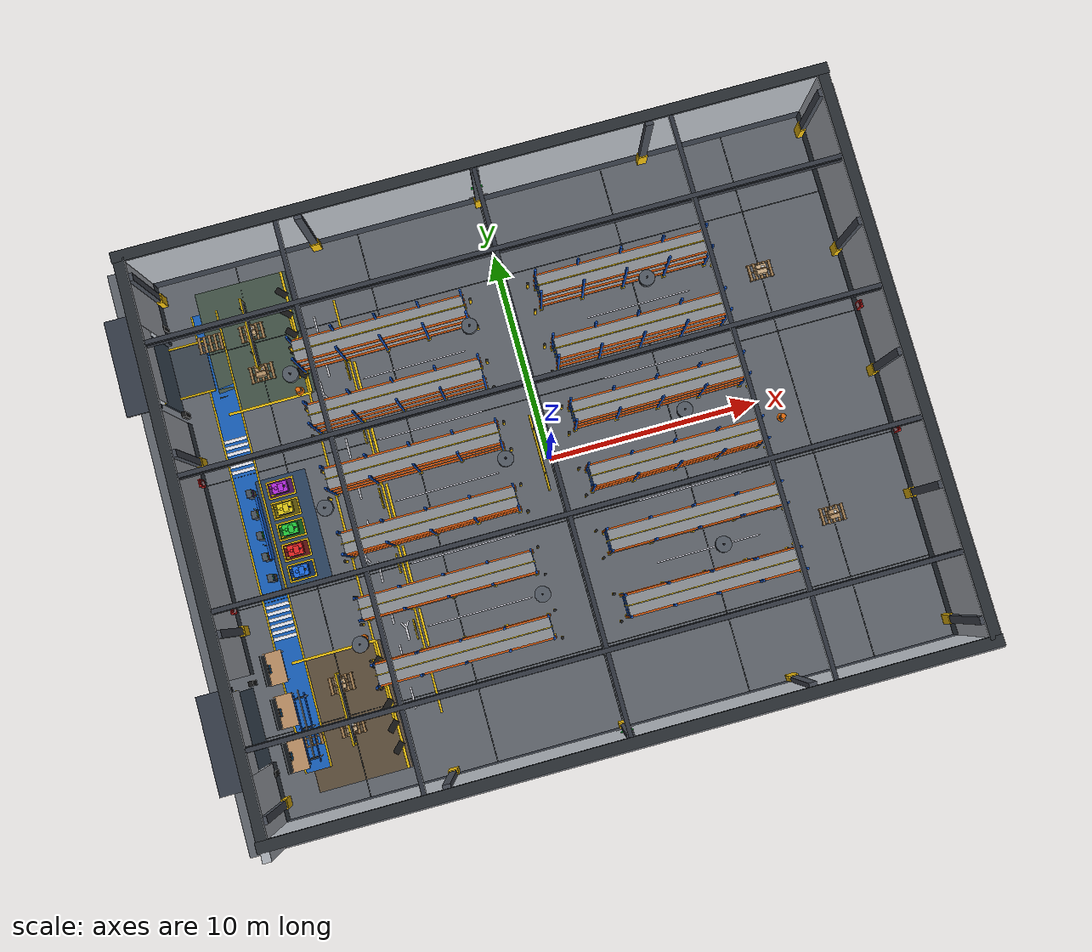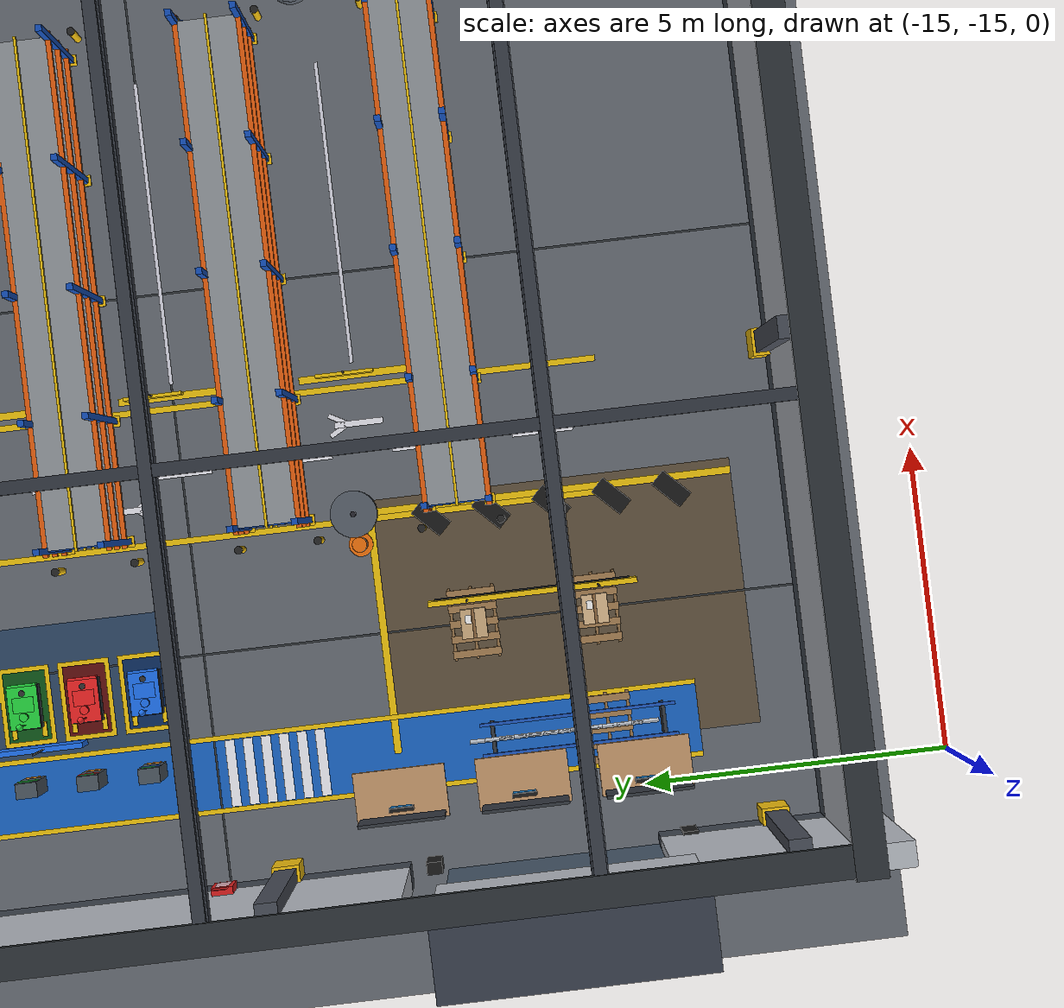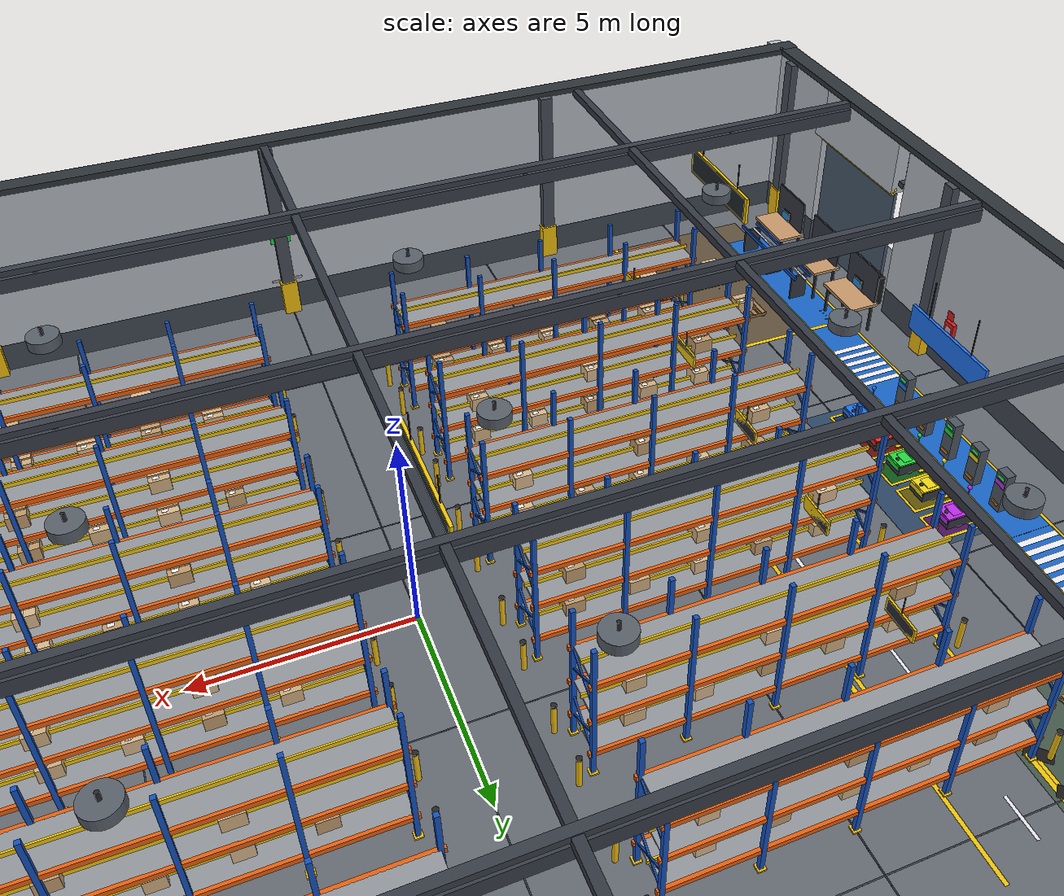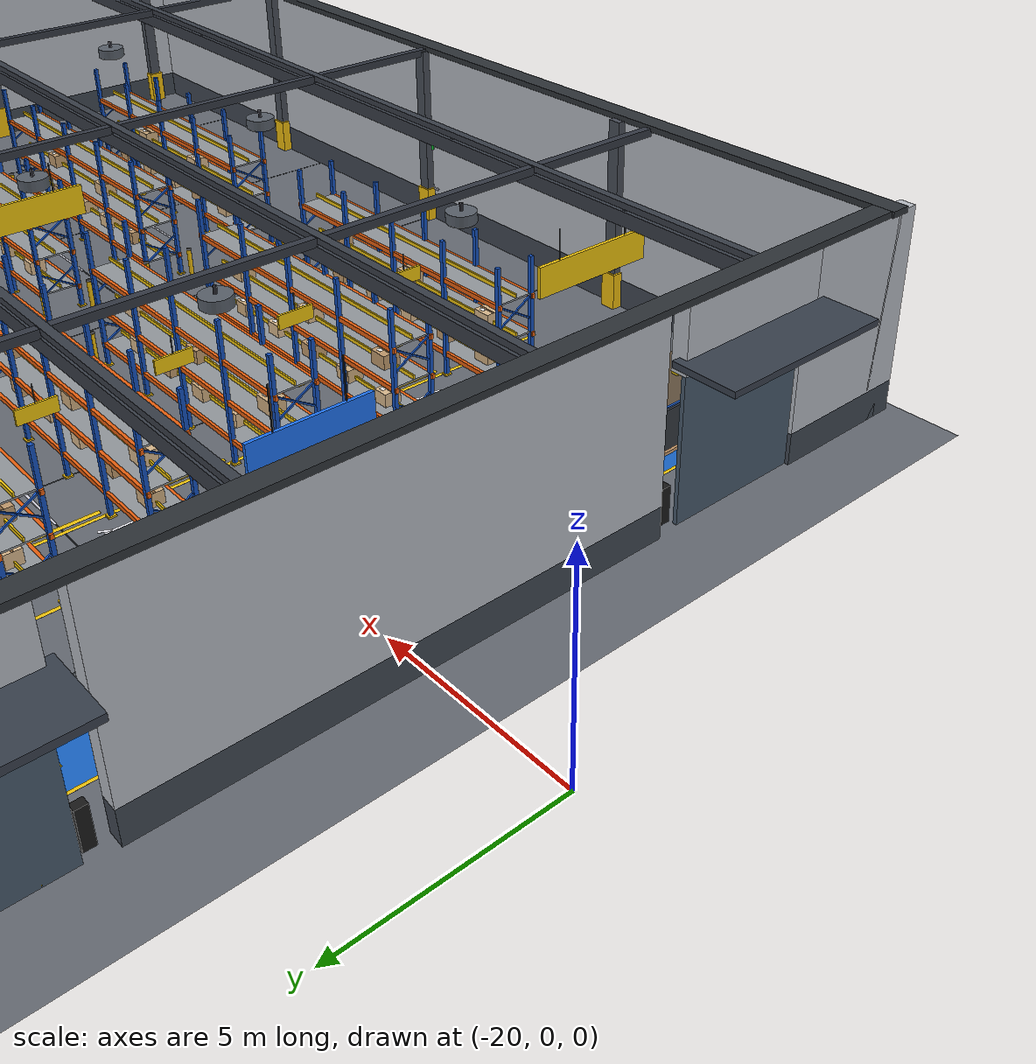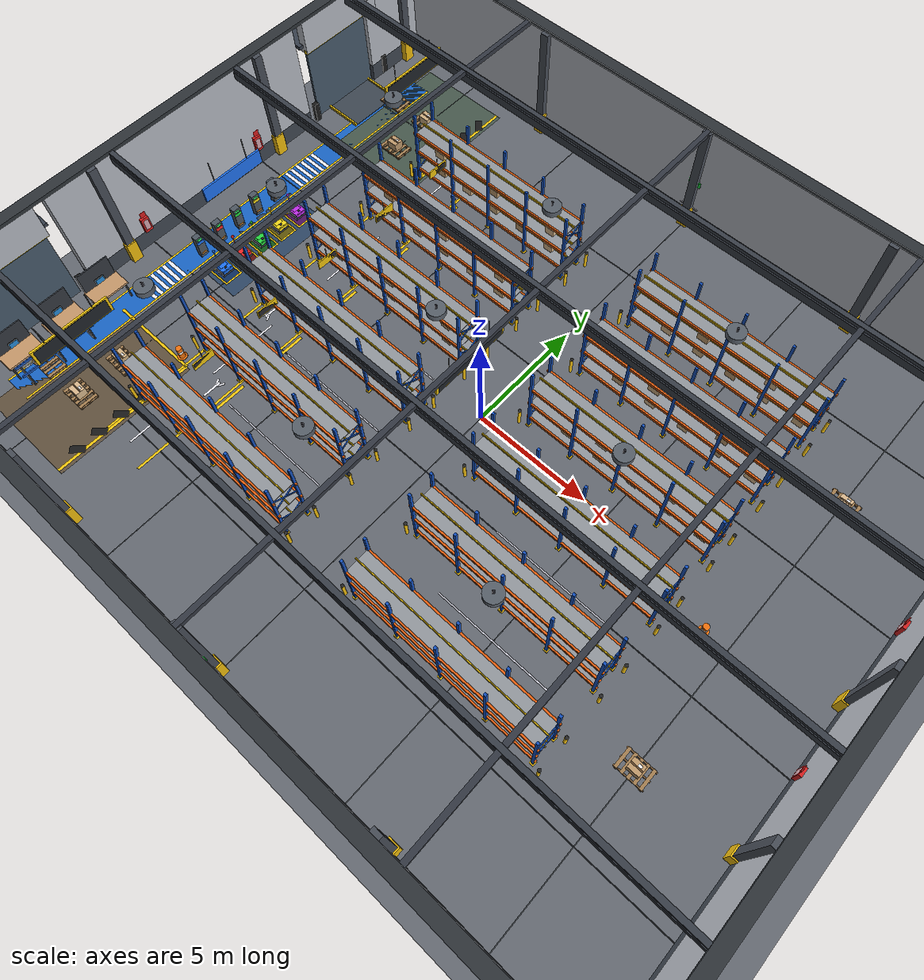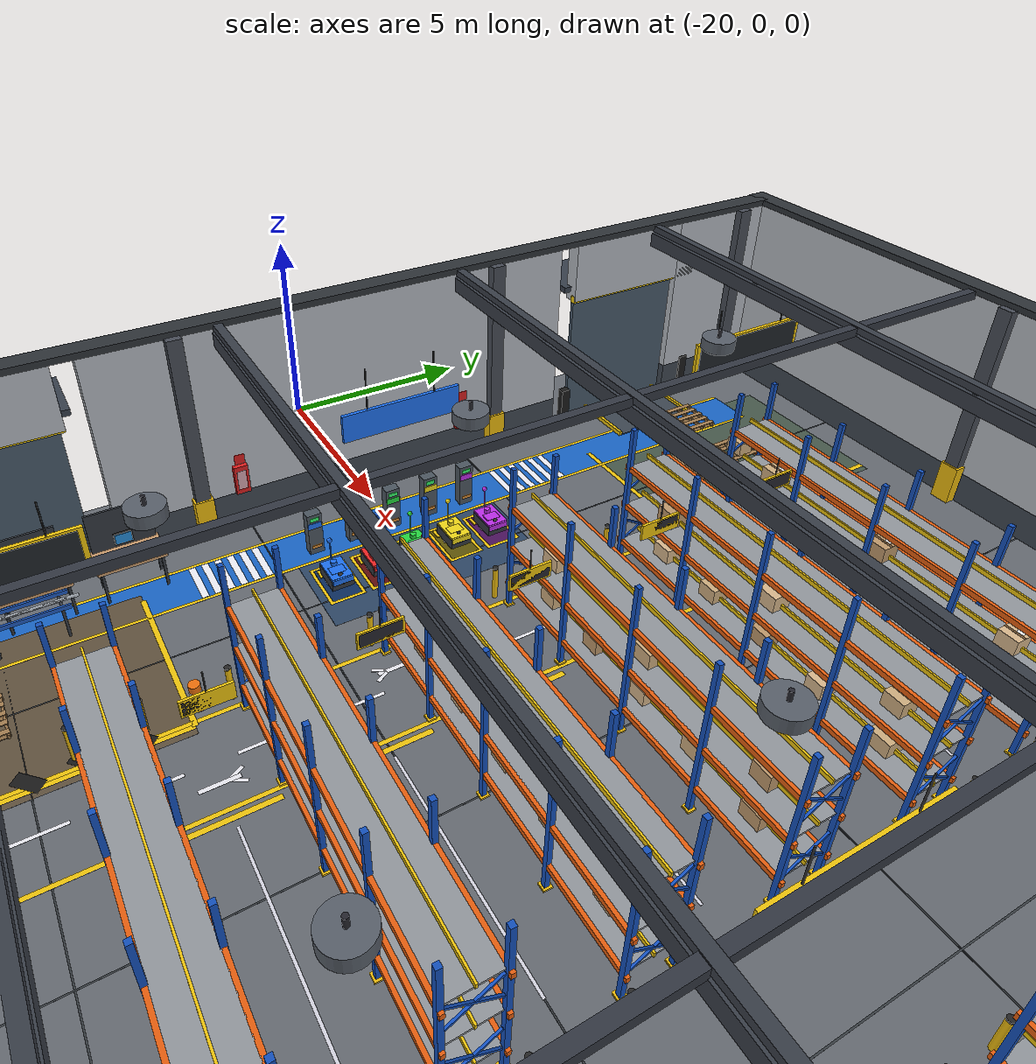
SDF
<?xml version="1.0" ?>
<sdf version="1.8">
  <world name="warehouse_3d">
    <!-- Physics Configuration (Optimized 0.008s step size for smooth RTF) -->
    <physics name="8ms" type="ignored">
      <max_step_size>0.008</max_step_size>
      <real_time_factor>1.0</real_time_factor>
    </physics>

    <!-- Essential Gazebo Plugins -->
    <plugin
      filename="gz-sim-physics-system"
      name="gz::sim::systems::Physics">
    </plugin>
    <plugin
      filename="gz-sim-user-commands-system"
      name="gz::sim::systems::UserCommands">
    </plugin>
    <plugin
      filename="gz-sim-scene-broadcaster-system"
      name="gz::sim::systems::SceneBroadcaster">
    </plugin>
    <plugin
      filename="gz-sim-sensors-system"
      name="gz::sim::systems::Sensors">
      <render_engine>ogre2</render_engine>
    </plugin>
    <plugin
      filename="gz-sim-imu-system"
      name="gz::sim::systems::Imu">
    </plugin>

    <!-- Gazebo Sim GUI Configuration with Cinematic Overview Camera -->
    <gui fullscreen="0">
      <plugin filename="MinimalScene" name="3D View">
        <gz-gui>
          <title>3D View</title>
          <property type="bool" key="showTitleBar">false</property>
          <property type="string" key="state">docked</property>
        </gz-gui>
        <engine>ogre2</engine>
        <scene>scene</scene>
        <ambient_light>0.65 0.68 0.72</ambient_light>
        <background_color>0.14 0.16 0.19</background_color>
        <!-- Elevated Southwest Isometric Overview directly framing all 5 AMR robots in docks and racks -->
        <camera_pose>-15.5 -10.5 8.2 0 0.52 0.62</camera_pose>
      </plugin>
      <plugin filename="EntityContextMenuPlugin" name="Entity context menu">
        <gz-gui>
          <property key="state" type="string">floating</property>
          <property key="width" type="double">5</property>
          <property key="height" type="double">5</property>
          <property key="showTitleBar" type="bool">false</property>
        </gz-gui>
      </plugin>
      <plugin filename="GzSceneManager" name="Scene Manager">
        <gz-gui>
          <property key="resizable" type="bool">false</property>
          <property key="width" type="double">5</property>
          <property key="height" type="double">5</property>
          <property key="state" type="string">floating</property>
          <property key="showTitleBar" type="bool">false</property>
        </gz-gui>
      </plugin>
      <plugin filename="InteractiveViewControl" name="Interactive view control">
        <gz-gui>
          <property key="resizable" type="bool">false</property>
          <property key="width" type="double">5</property>
          <property key="height" type="double">5</property>
          <property key="state" type="string">floating</property>
          <property key="showTitleBar" type="bool">false</property>
        </gz-gui>
      </plugin>
      <plugin filename="CameraTracking" name="Camera Tracking">
        <gz-gui>
          <property key="resizable" type="bool">false</property>
          <property key="width" type="double">5</property>
          <property key="height" type="double">5</property>
          <property key="state" type="string">floating</property>
          <property key="showTitleBar" type="bool">false</property>
        </gz-gui>
      </plugin>
      <plugin filename="WorldControl" name="World control">
        <gz-gui>
          <title>World control</title>
          <property type="bool" key="showTitleBar">false</property>
          <property type="bool" key="resizable">false</property>
          <property type="double" key="height">72</property>
          <property type="double" key="z">1</property>
          <property type="string" key="state">floating</property>
          <anchors target="3D View">
            <line own="left" target="left"/>
            <line own="bottom" target="bottom"/>
          </anchors>
        </gz-gui>
        <play_pause>true</play_pause>
        <step>true</step>
        <start_paused>false</start_paused>
      </plugin>
      <plugin filename="WorldStats" name="World stats">
        <gz-gui>
          <title>World stats</title>
          <property type="bool" key="showTitleBar">false</property>
          <property type="bool" key="resizable">false</property>
          <property type="double" key="height">110</property>
          <property type="double" key="width">290</property>
          <property type="double" key="z">1</property>
          <property type="string" key="state">floating</property>
          <anchors target="3D View">
            <line own="right" target="right"/>
            <line own="bottom" target="bottom"/>
          </anchors>
        </gz-gui>
        <sim_time>true</sim_time>
        <real_time>true</real_time>
        <real_time_factor>true</real_time_factor>
        <iterations>true</iterations>
      </plugin>
    </gui>

    <!-- Ambient Lighting & Atmospheric Scene -->
    <scene>
      <ambient>0.65 0.68 0.72 1.0</ambient>
      <background>0.14 0.16 0.19 1.0</background>
      <shadows>true</shadows>
      <grid>false</grid>
    </scene>

    <!-- Main Directional Overhead Sky/Sun Light -->
    <light type="directional" name="sun_main">
      <cast_shadows>true</cast_shadows>
      <pose>0 0 16 0 0 0</pose>
      <diffuse>0.85 0.88 0.92 1.0</diffuse>
      <specular>0.3 0.3 0.35 1.0</specular>
      <attenuation>
        <range>1000</range>
        <constant>0.9</constant>
        <linear>0.01</linear>
        <quadratic>0.001</quadratic>
      </attenuation>
      <direction>-0.3 0.2 -0.9</direction>
    </light>

    <light type="point" name="bay_light_0">
      <pose>-10.0 -6.0 5.0 0 0 0</pose>
      <diffuse>0.72 0.75 0.80 1.0</diffuse>
      <specular>0.25 0.25 0.30 1.0</specular>
      <attenuation>
        <range>22</range>
        <constant>0.20</constant>
        <linear>0.04</linear>
        <quadratic>0.008</quadratic>
      </attenuation>
      <cast_shadows>false</cast_shadows>
    </light>

    <light type="point" name="bay_light_1">
      <pose>-10.0 0.0 5.0 0 0 0</pose>
      <diffuse>0.72 0.75 0.80 1.0</diffuse>
      <specular>0.25 0.25 0.30 1.0</specular>
      <attenuation>
        <range>22</range>
        <constant>0.20</constant>
        <linear>0.04</linear>
        <quadratic>0.008</quadratic>
      </attenuation>
      <cast_shadows>false</cast_shadows>
    </light>

    <light type="point" name="bay_light_2">
      <pose>-10.0 6.0 5.0 0 0 0</pose>
      <diffuse>0.72 0.75 0.80 1.0</diffuse>
      <specular>0.25 0.25 0.30 1.0</specular>
      <attenuation>
        <range>22</range>
        <constant>0.20</constant>
        <linear>0.04</linear>
        <quadratic>0.008</quadratic>
      </attenuation>
      <cast_shadows>false</cast_shadows>
    </light>

    <light type="point" name="bay_light_3">
      <pose>-2.0 -6.0 5.0 0 0 0</pose>
      <diffuse>0.72 0.75 0.80 1.0</diffuse>
      <specular>0.25 0.25 0.30 1.0</specular>
      <attenuation>
        <range>22</range>
        <constant>0.20</constant>
        <linear>0.04</linear>
        <quadratic>0.008</quadratic>
      </attenuation>
      <cast_shadows>false</cast_shadows>
    </light>

    <light type="point" name="bay_light_4">
      <pose>-2.0 0.0 5.0 0 0 0</pose>
      <diffuse>0.72 0.75 0.80 1.0</diffuse>
      <specular>0.25 0.25 0.30 1.0</specular>
      <attenuation>
        <range>22</range>
        <constant>0.20</constant>
        <linear>0.04</linear>
        <quadratic>0.008</quadratic>
      </attenuation>
      <cast_shadows>false</cast_shadows>
    </light>

    <light type="point" name="bay_light_5">
      <pose>-2.0 6.0 5.0 0 0 0</pose>
      <diffuse>0.72 0.75 0.80 1.0</diffuse>
      <specular>0.25 0.25 0.30 1.0</specular>
      <attenuation>
        <range>22</range>
        <constant>0.20</constant>
        <linear>0.04</linear>
        <quadratic>0.008</quadratic>
      </attenuation>
      <cast_shadows>false</cast_shadows>
    </light>

    <light type="point" name="bay_light_6">
      <pose>6.0 -6.0 5.0 0 0 0</pose>
      <diffuse>0.72 0.75 0.80 1.0</diffuse>
      <specular>0.25 0.25 0.30 1.0</specular>
      <attenuation>
        <range>22</range>
        <constant>0.20</constant>
        <linear>0.04</linear>
        <quadratic>0.008</quadratic>
      </attenuation>
      <cast_shadows>false</cast_shadows>
    </light>

    <light type="point" name="bay_light_7">
      <pose>6.0 0.0 5.0 0 0 0</pose>
      <diffuse>0.72 0.75 0.80 1.0</diffuse>
      <specular>0.25 0.25 0.30 1.0</specular>
      <attenuation>
        <range>22</range>
        <constant>0.20</constant>
        <linear>0.04</linear>
        <quadratic>0.008</quadratic>
      </attenuation>
      <cast_shadows>false</cast_shadows>
    </light>

    <light type="point" name="bay_light_8">
      <pose>6.0 6.0 5.0 0 0 0</pose>
      <diffuse>0.72 0.75 0.80 1.0</diffuse>
      <specular>0.25 0.25 0.30 1.0</specular>
      <attenuation>
        <range>22</range>
        <constant>0.20</constant>
        <linear>0.04</linear>
        <quadratic>0.008</quadratic>
      </attenuation>
      <cast_shadows>false</cast_shadows>
    </light>

    <!-- Warehouse Ground Floor -->
    <model name="warehouse_floor">
      <static>true</static>
      <link name="floor_link">
        <collision name="floor_collision">
          <geometry>
            <plane>
              <normal>0 0 1</normal>
              <size>36 28</size>
            </plane>
          </geometry>
          <surface>
            <friction>
              <ode>
                <mu>1.0</mu>
                <mu2>1.0</mu2>
              </ode>
            </friction>
          </surface>
        </collision>
        <visual name="floor_visual">
          <geometry>
            <plane>
              <normal>0 0 1</normal>
              <size>36 28</size>
            </plane>
          </geometry>
          <material>
            <ambient>0.32 0.34 0.36 1.0</ambient>
            <diffuse>0.40 0.42 0.45 1.0</diffuse>
            <specular>0.15 0.15 0.15 1.0</specular>
          </material>
        </visual>
      </link>
    </model>

    <!-- Warehouse Structural Architecture & Perimeter Walls -->
    <model name="warehouse_architecture">
      <static>true</static>
      <link name="wall_north_base">
        <pose>0.0000 13.0000 0.4000 0.0000 0.0000 0.0000</pose>
        <collision name="wall_north_base_col">
          <geometry><box><size>32.4000 0.4000 0.8000</size></box></geometry>
        </collision>
        <visual name="wall_north_base_vis">
          <geometry><box><size>32.4000 0.4000 0.8000</size></box></geometry>
          <material>
            <ambient>0.163 0.182 0.208 1.00</ambient>
            <diffuse>0.250 0.280 0.320 1.00</diffuse>
            <specular>0.15 0.15 0.15 1.0</specular>
          </material>
        </visual>
      </link>
      <link name="wall_north_upper">
        <pose>0.0000 13.0000 3.0000 0.0000 0.0000 0.0000</pose>
        <collision name="wall_north_upper_col">
          <geometry><box><size>32.4000 0.4000 4.4000</size></box></geometry>
        </collision>
        <visual name="wall_north_upper_vis">
          <geometry><box><size>32.4000 0.4000 4.4000</size></box></geometry>
          <material>
            <ambient>0.468 0.481 0.501 1.00</ambient>
            <diffuse>0.720 0.740 0.770 1.00</diffuse>
            <specular>0.15 0.15 0.15 1.0</specular>
          </material>
        </visual>
      </link>
      <link name="wall_north_coping">
        <pose>0.0000 13.0000 5.2500 0.0000 0.0000 0.0000</pose>
        <collision name="wall_north_coping_col">
          <geometry><box><size>32.6000 0.5000 0.1500</size></box></geometry>
        </collision>
        <visual name="wall_north_coping_vis">
          <geometry><box><size>32.6000 0.5000 0.1500</size></box></geometry>
          <material>
            <ambient>0.117 0.130 0.143 1.00</ambient>
            <diffuse>0.180 0.200 0.220 1.00</diffuse>
            <specular>0.15 0.15 0.15 1.0</specular>
          </material>
        </visual>
      </link>
      <link name="window_north">
        <pose>0.0000 12.8500 4.2000 0.0000 0.0000 0.0000</pose>
        <visual name="window_north_vis">
          <geometry><box><size>28.0000 0.0500 1.0000</size></box></geometry>
          <material>
            <ambient>0.293 0.423 0.552 0.70</ambient>
            <diffuse>0.450 0.650 0.850 0.70</diffuse>
            <specular>0.15 0.15 0.15 1.0</specular>
          </material>
        </visual>
      </link>
      <link name="wall_south_base">
        <pose>0.0000 -13.0000 0.4000 0.0000 0.0000 0.0000</pose>
        <collision name="wall_south_base_col">
          <geometry><box><size>32.4000 0.4000 0.8000</size></box></geometry>
        </collision>
        <visual name="wall_south_base_vis">
          <geometry><box><size>32.4000 0.4000 0.8000</size></box></geometry>
          <material>
            <ambient>0.163 0.182 0.208 1.00</ambient>
            <diffuse>0.250 0.280 0.320 1.00</diffuse>
            <specular>0.15 0.15 0.15 1.0</specular>
          </material>
        </visual>
      </link>
      <link name="wall_south_upper">
        <pose>0.0000 -13.0000 3.0000 0.0000 0.0000 0.0000</pose>
        <collision name="wall_south_upper_col">
          <geometry><box><size>32.4000 0.4000 4.4000</size></box></geometry>
        </collision>
        <visual name="wall_south_upper_vis">
          <geometry><box><size>32.4000 0.4000 4.4000</size></box></geometry>
          <material>
            <ambient>0.468 0.481 0.501 1.00</ambient>
            <diffuse>0.720 0.740 0.770 1.00</diffuse>
            <specular>0.15 0.15 0.15 1.0</specular>
          </material>
        </visual>
      </link>
      <link name="wall_south_coping">
        <pose>0.0000 -13.0000 5.2500 0.0000 0.0000 0.0000</pose>
        <collision name="wall_south_coping_col">
          <geometry><box><size>32.6000 0.5000 0.1500</size></box></geometry>
        </collision>
        <visual name="wall_south_coping_vis">
          <geometry><box><size>32.6000 0.5000 0.1500</size></box></geometry>
          <material>
            <ambient>0.117 0.130 0.143 1.00</ambient>
            <diffuse>0.180 0.200 0.220 1.00</diffuse>
            <specular>0.15 0.15 0.15 1.0</specular>
          </material>
        </visual>
      </link>
      <link name="wall_east_base">
        <pose>16.0000 0.0000 0.4000 0.0000 0.0000 0.0000</pose>
        <collision name="wall_east_base_col">
          <geometry><box><size>0.4000 25.6000 0.8000</size></box></geometry>
        </collision>
        <visual name="wall_east_base_vis">
          <geometry><box><size>0.4000 25.6000 0.8000</size></box></geometry>
          <material>
            <ambient>0.163 0.182 0.208 1.00</ambient>
            <diffuse>0.250 0.280 0.320 1.00</diffuse>
            <specular>0.15 0.15 0.15 1.0</specular>
          </material>
        </visual>
      </link>
      <link name="wall_east_upper">
        <pose>16.0000 0.0000 3.0000 0.0000 0.0000 0.0000</pose>
        <collision name="wall_east_upper_col">
          <geometry><box><size>0.4000 25.6000 4.4000</size></box></geometry>
        </collision>
        <visual name="wall_east_upper_vis">
          <geometry><box><size>0.4000 25.6000 4.4000</size></box></geometry>
          <material>
            <ambient>0.468 0.481 0.501 1.00</ambient>
            <diffuse>0.720 0.740 0.770 1.00</diffuse>
            <specular>0.15 0.15 0.15 1.0</specular>
          </material>
        </visual>
      </link>
      <link name="wall_east_coping">
        <pose>16.0000 0.0000 5.2500 0.0000 0.0000 0.0000</pose>
        <collision name="wall_east_coping_col">
          <geometry><box><size>0.5000 25.8000 0.1500</size></box></geometry>
        </collision>
        <visual name="wall_east_coping_vis">
          <geometry><box><size>0.5000 25.8000 0.1500</size></box></geometry>
          <material>
            <ambient>0.117 0.130 0.143 1.00</ambient>
            <diffuse>0.180 0.200 0.220 1.00</diffuse>
            <specular>0.15 0.15 0.15 1.0</specular>
          </material>
        </visual>
      </link>
      <link name="window_east">
        <pose>15.8500 0.0000 4.2000 0.0000 0.0000 0.0000</pose>
        <visual name="window_east_vis">
          <geometry><box><size>0.0500 20.0000 1.0000</size></box></geometry>
          <material>
            <ambient>0.293 0.423 0.552 0.70</ambient>
            <diffuse>0.450 0.650 0.850 0.70</diffuse>
            <specular>0.15 0.15 0.15 1.0</specular>
          </material>
        </visual>
      </link>
      <link name="wall_west_n_base">
        <pose>-16.0000 11.4500 0.4000 0.0000 0.0000 0.0000</pose>
        <collision name="wall_west_n_base_col">
          <geometry><box><size>0.4000 3.1000 0.8000</size></box></geometry>
        </collision>
        <visual name="wall_west_n_base_vis">
          <geometry><box><size>0.4000 3.1000 0.8000</size></box></geometry>
          <material>
            <ambient>0.163 0.182 0.208 1.00</ambient>
            <diffuse>0.250 0.280 0.320 1.00</diffuse>
            <specular>0.15 0.15 0.15 1.0</specular>
          </material>
        </visual>
      </link>
      <link name="wall_west_n_upper">
        <pose>-16.0000 11.4500 3.0000 0.0000 0.0000 0.0000</pose>
        <collision name="wall_west_n_upper_col">
          <geometry><box><size>0.4000 3.1000 4.4000</size></box></geometry>
        </collision>
        <visual name="wall_west_n_upper_vis">
          <geometry><box><size>0.4000 3.1000 4.4000</size></box></geometry>
          <material>
            <ambient>0.468 0.481 0.501 1.00</ambient>
            <diffuse>0.720 0.740 0.770 1.00</diffuse>
            <specular>0.15 0.15 0.15 1.0</specular>
          </material>
        </visual>
      </link>
      <link name="wall_west_mid_base">
        <pose>-16.0000 0.0000 0.4000 0.0000 0.0000 0.0000</pose>
        <collision name="wall_west_mid_base_col">
          <geometry><box><size>0.4000 12.0000 0.8000</size></box></geometry>
        </collision>
        <visual name="wall_west_mid_base_vis">
          <geometry><box><size>0.4000 12.0000 0.8000</size></box></geometry>
          <material>
            <ambient>0.163 0.182 0.208 1.00</ambient>
            <diffuse>0.250 0.280 0.320 1.00</diffuse>
            <specular>0.15 0.15 0.15 1.0</specular>
          </material>
        </visual>
      </link>
      <link name="wall_west_mid_upper">
        <pose>-16.0000 0.0000 3.0000 0.0000 0.0000 0.0000</pose>
        <collision name="wall_west_mid_upper_col">
          <geometry><box><size>0.4000 12.0000 4.4000</size></box></geometry>
        </collision>
        <visual name="wall_west_mid_upper_vis">
          <geometry><box><size>0.4000 12.0000 4.4000</size></box></geometry>
          <material>
            <ambient>0.468 0.481 0.501 1.00</ambient>
            <diffuse>0.720 0.740 0.770 1.00</diffuse>
            <specular>0.15 0.15 0.15 1.0</specular>
          </material>
        </visual>
      </link>
      <link name="wall_west_s_base">
        <pose>-16.0000 -11.9000 0.4000 0.0000 0.0000 0.0000</pose>
        <collision name="wall_west_s_base_col">
          <geometry><box><size>0.4000 3.6000 0.8000</size></box></geometry>
        </collision>
        <visual name="wall_west_s_base_vis">
          <geometry><box><size>0.4000 3.6000 0.8000</size></box></geometry>
          <material>
            <ambient>0.163 0.182 0.208 1.00</ambient>
            <diffuse>0.250 0.280 0.320 1.00</diffuse>
            <specular>0.15 0.15 0.15 1.0</specular>
          </material>
        </visual>
      </link>
      <link name="wall_west_s_upper">
        <pose>-16.0000 -11.9000 3.0000 0.0000 0.0000 0.0000</pose>
        <collision name="wall_west_s_upper_col">
          <geometry><box><size>0.4000 3.6000 4.4000</size></box></geometry>
        </collision>
        <visual name="wall_west_s_upper_vis">
          <geometry><box><size>0.4000 3.6000 4.4000</size></box></geometry>
          <material>
            <ambient>0.468 0.481 0.501 1.00</ambient>
            <diffuse>0.720 0.740 0.770 1.00</diffuse>
            <specular>0.15 0.15 0.15 1.0</specular>
          </material>
        </visual>
      </link>
      <link name="dock_shutter_n_hdr">
        <pose>-16.0000 8.5000 4.4000 0.0000 0.0000 0.0000</pose>
        <collision name="dock_shutter_n_hdr_col">
          <geometry><box><size>0.4000 4.0000 1.6000</size></box></geometry>
        </collision>
        <visual name="dock_shutter_n_hdr_vis">
          <geometry><box><size>0.4000 4.0000 1.6000</size></box></geometry>
          <material>
            <ambient>0.468 0.481 0.501 1.00</ambient>
            <diffuse>0.720 0.740 0.770 1.00</diffuse>
            <specular>0.15 0.15 0.15 1.0</specular>
          </material>
        </visual>
      </link>
      <link name="dock_shutter_s_hdr">
        <pose>-16.0000 -8.5000 4.4000 0.0000 0.0000 0.0000</pose>
        <collision name="dock_shutter_s_hdr_col">
          <geometry><box><size>0.4000 4.0000 1.6000</size></box></geometry>
        </collision>
        <visual name="dock_shutter_s_hdr_vis">
          <geometry><box><size>0.4000 4.0000 1.6000</size></box></geometry>
          <material>
            <ambient>0.468 0.481 0.501 1.00</ambient>
            <diffuse>0.720 0.740 0.770 1.00</diffuse>
            <specular>0.15 0.15 0.15 1.0</specular>
          </material>
        </visual>
      </link>
      <link name="wall_west_coping">
        <pose>-16.0000 0.0000 5.2500 0.0000 0.0000 0.0000</pose>
        <collision name="wall_west_coping_col">
          <geometry><box><size>0.5000 25.8000 0.1500</size></box></geometry>
        </collision>
        <visual name="wall_west_coping_vis">
          <geometry><box><size>0.5000 25.8000 0.1500</size></box></geometry>
          <material>
            <ambient>0.117 0.130 0.143 1.00</ambient>
            <diffuse>0.180 0.200 0.220 1.00</diffuse>
            <specular>0.15 0.15 0.15 1.0</specular>
          </material>
        </visual>
      </link>
      <link name="rollup_door_inbound">
        <pose>-16.0500 8.5000 1.8000 0.0000 0.0000 0.0000</pose>
        <collision name="rollup_door_inbound_col">
          <geometry><box><size>0.1000 3.8000 3.6000</size></box></geometry>
        </collision>
        <visual name="rollup_door_inbound_vis">
          <geometry><box><size>0.1000 3.8000 3.6000</size></box></geometry>
          <material>
            <ambient>0.182 0.227 0.273 1.00</ambient>
            <diffuse>0.280 0.350 0.420 1.00</diffuse>
            <specular>0.15 0.15 0.15 1.0</specular>
          </material>
        </visual>
      </link>
      <link name="rollup_hazard_hdr_in">
        <pose>-15.9000 8.5000 3.6500 0.0000 0.0000 0.0000</pose>
        <collision name="rollup_hazard_hdr_in_col">
          <geometry><box><size>0.1500 4.0000 0.2000</size></box></geometry>
        </collision>
        <visual name="rollup_hazard_hdr_in_vis">
          <geometry><box><size>0.1500 4.0000 0.2000</size></box></geometry>
          <material>
            <ambient>0.617 0.520 0.033 1.00</ambient>
            <diffuse>0.950 0.800 0.050 1.00</diffuse>
            <specular>0.15 0.15 0.15 1.0</specular>
          </material>
        </visual>
      </link>
      <link name="dock_canopy_in">
        <pose>-16.8000 8.5000 3.9000 0.0000 0.0000 0.0000</pose>
        <collision name="dock_canopy_in_col">
          <geometry><box><size>1.6000 4.4000 0.1500</size></box></geometry>
        </collision>
        <visual name="dock_canopy_in_vis">
          <geometry><box><size>1.6000 4.4000 0.1500</size></box></geometry>
          <material>
            <ambient>0.143 0.163 0.195 1.00</ambient>
            <diffuse>0.220 0.250 0.300 1.00</diffuse>
            <specular>0.15 0.15 0.15 1.0</specular>
          </material>
        </visual>
      </link>
      <link name="dock_bumper_in_1">
        <pose>-15.8500 6.4000 0.5000 0.0000 0.0000 0.0000</pose>
        <collision name="dock_bumper_in_1_col">
          <geometry><box><size>0.2000 0.2500 0.9000</size></box></geometry>
        </collision>
        <visual name="dock_bumper_in_1_vis">
          <geometry><box><size>0.2000 0.2500 0.9000</size></box></geometry>
          <material>
            <ambient>0.065 0.065 0.065 1.00</ambient>
            <diffuse>0.100 0.100 0.100 1.00</diffuse>
            <specular>0.15 0.15 0.15 1.0</specular>
          </material>
        </visual>
      </link>
      <link name="dock_bumper_in_2">
        <pose>-15.8500 10.6000 0.5000 0.0000 0.0000 0.0000</pose>
        <collision name="dock_bumper_in_2_col">
          <geometry><box><size>0.2000 0.2500 0.9000</size></box></geometry>
        </collision>
        <visual name="dock_bumper_in_2_vis">
          <geometry><box><size>0.2000 0.2500 0.9000</size></box></geometry>
          <material>
            <ambient>0.065 0.065 0.065 1.00</ambient>
            <diffuse>0.100 0.100 0.100 1.00</diffuse>
            <specular>0.15 0.15 0.15 1.0</specular>
          </material>
        </visual>
      </link>
      <link name="rollup_door_outbound">
        <pose>-16.0500 -8.5000 1.8000 0.0000 0.0000 0.0000</pose>
        <collision name="rollup_door_outbound_col">
          <geometry><box><size>0.1000 3.8000 3.6000</size></box></geometry>
        </collision>
        <visual name="rollup_door_outbound_vis">
          <geometry><box><size>0.1000 3.8000 3.6000</size></box></geometry>
          <material>
            <ambient>0.182 0.227 0.273 1.00</ambient>
            <diffuse>0.280 0.350 0.420 1.00</diffuse>
            <specular>0.15 0.15 0.15 1.0</specular>
          </material>
        </visual>
      </link>
      <link name="rollup_hazard_hdr_out">
        <pose>-15.9000 -8.5000 3.6500 0.0000 0.0000 0.0000</pose>
        <collision name="rollup_hazard_hdr_out_col">
          <geometry><box><size>0.1500 4.0000 0.2000</size></box></geometry>
        </collision>
        <visual name="rollup_hazard_hdr_out_vis">
          <geometry><box><size>0.1500 4.0000 0.2000</size></box></geometry>
          <material>
            <ambient>0.617 0.520 0.033 1.00</ambient>
            <diffuse>0.950 0.800 0.050 1.00</diffuse>
            <specular>0.15 0.15 0.15 1.0</specular>
          </material>
        </visual>
      </link>
      <link name="dock_canopy_out">
        <pose>-16.8000 -8.5000 3.9000 0.0000 0.0000 0.0000</pose>
        <collision name="dock_canopy_out_col">
          <geometry><box><size>1.6000 4.4000 0.1500</size></box></geometry>
        </collision>
        <visual name="dock_canopy_out_vis">
          <geometry><box><size>1.6000 4.4000 0.1500</size></box></geometry>
          <material>
            <ambient>0.143 0.163 0.195 1.00</ambient>
            <diffuse>0.220 0.250 0.300 1.00</diffuse>
            <specular>0.15 0.15 0.15 1.0</specular>
          </material>
        </visual>
      </link>
      <link name="dock_bumper_out_1">
        <pose>-15.8500 -10.6000 0.5000 0.0000 0.0000 0.0000</pose>
        <collision name="dock_bumper_out_1_col">
          <geometry><box><size>0.2000 0.2500 0.9000</size></box></geometry>
        </collision>
        <visual name="dock_bumper_out_1_vis">
          <geometry><box><size>0.2000 0.2500 0.9000</size></box></geometry>
          <material>
            <ambient>0.065 0.065 0.065 1.00</ambient>
            <diffuse>0.100 0.100 0.100 1.00</diffuse>
            <specular>0.15 0.15 0.15 1.0</specular>
          </material>
        </visual>
      </link>
      <link name="dock_bumper_out_2">
        <pose>-15.8500 -6.4000 0.5000 0.0000 0.0000 0.0000</pose>
        <collision name="dock_bumper_out_2_col">
          <geometry><box><size>0.2000 0.2500 0.9000</size></box></geometry>
        </collision>
        <visual name="dock_bumper_out_2_vis">
          <geometry><box><size>0.2000 0.2500 0.9000</size></box></geometry>
          <material>
            <ambient>0.065 0.065 0.065 1.00</ambient>
            <diffuse>0.100 0.100 0.100 1.00</diffuse>
            <specular>0.15 0.15 0.15 1.0</specular>
          </material>
        </visual>
      </link>
      <link name="exit_door_north">
        <pose>0.0000 12.8500 1.1000 0.0000 0.0000 0.0000</pose>
        <collision name="exit_door_north_col">
          <geometry><box><size>1.1000 0.0500 2.2000</size></box></geometry>
        </collision>
        <visual name="exit_door_north_vis">
          <geometry><box><size>1.1000 0.0500 2.2000</size></box></geometry>
          <material>
            <ambient>0.195 0.208 0.227 1.00</ambient>
            <diffuse>0.300 0.320 0.350 1.00</diffuse>
            <specular>0.15 0.15 0.15 1.0</specular>
          </material>
        </visual>
      </link>
      <link name="exit_pushbar_north">
        <pose>0.0000 12.8000 1.0000 0.0000 0.0000 0.0000</pose>
        <collision name="exit_pushbar_north_col">
          <geometry><box><size>0.8500 0.0600 0.0600</size></box></geometry>
        </collision>
        <visual name="exit_pushbar_north_vis">
          <geometry><box><size>0.8500 0.0600 0.0600</size></box></geometry>
          <material>
            <ambient>0.520 0.520 0.552 1.00</ambient>
            <diffuse>0.800 0.800 0.850 1.00</diffuse>
            <specular>0.15 0.15 0.15 1.0</specular>
          </material>
        </visual>
      </link>
      <link name="exit_sign_north">
        <pose>0.0000 12.8000 2.3500 0.0000 0.0000 0.0000</pose>
        <visual name="exit_sign_north_vis">
          <geometry><box><size>0.5500 0.0800 0.2500</size></box></geometry>
          <material>
            <ambient>0.065 0.552 0.163 1.00</ambient>
            <diffuse>0.100 0.850 0.250 1.00</diffuse>
            <specular>0.15 0.15 0.15 1.0</specular>
            <emissive>0.100 0.800 0.200 1.0</emissive>
          </material>
        </visual>
      </link>
      <link name="exit_door_south">
        <pose>0.0000 -12.8500 1.1000 0.0000 0.0000 0.0000</pose>
        <collision name="exit_door_south_col">
          <geometry><box><size>1.1000 0.0500 2.2000</size></box></geometry>
        </collision>
        <visual name="exit_door_south_vis">
          <geometry><box><size>1.1000 0.0500 2.2000</size></box></geometry>
          <material>
            <ambient>0.195 0.208 0.227 1.00</ambient>
            <diffuse>0.300 0.320 0.350 1.00</diffuse>
            <specular>0.15 0.15 0.15 1.0</specular>
          </material>
        </visual>
      </link>
      <link name="exit_pushbar_south">
        <pose>0.0000 -12.8000 1.0000 0.0000 0.0000 0.0000</pose>
        <collision name="exit_pushbar_south_col">
          <geometry><box><size>0.8500 0.0600 0.0600</size></box></geometry>
        </collision>
        <visual name="exit_pushbar_south_vis">
          <geometry><box><size>0.8500 0.0600 0.0600</size></box></geometry>
          <material>
            <ambient>0.520 0.520 0.552 1.00</ambient>
            <diffuse>0.800 0.800 0.850 1.00</diffuse>
            <specular>0.15 0.15 0.15 1.0</specular>
          </material>
        </visual>
      </link>
      <link name="exit_sign_south">
        <pose>0.0000 -12.8000 2.3500 0.0000 0.0000 0.0000</pose>
        <visual name="exit_sign_south_vis">
          <geometry><box><size>0.5500 0.0800 0.2500</size></box></geometry>
          <material>
            <ambient>0.065 0.552 0.163 1.00</ambient>
            <diffuse>0.100 0.850 0.250 1.00</diffuse>
            <specular>0.15 0.15 0.15 1.0</specular>
            <emissive>0.100 0.800 0.200 1.0</emissive>
          </material>
        </visual>
      </link>
      <link name="col_0_base">
        <pose>-15.7500 -12.0000 0.5000 0.0000 0.0000 0.0000</pose>
        <collision name="col_0_base_col">
          <geometry><box><size>0.4500 0.4500 1.0000</size></box></geometry>
        </collision>
        <visual name="col_0_base_vis">
          <geometry><box><size>0.4500 0.4500 1.0000</size></box></geometry>
          <material>
            <ambient>0.617 0.488 0.033 1.00</ambient>
            <diffuse>0.950 0.750 0.050 1.00</diffuse>
            <specular>0.15 0.15 0.15 1.0</specular>
          </material>
        </visual>
      </link>
      <link name="col_0_stem">
        <pose>-15.7500 -12.0000 3.1000 0.0000 0.0000 0.0000</pose>
        <collision name="col_0_stem_col">
          <geometry><box><size>0.3500 0.3500 4.2000</size></box></geometry>
        </collision>
        <visual name="col_0_stem_vis">
          <geometry><box><size>0.3500 0.3500 4.2000</size></box></geometry>
          <material>
            <ambient>0.182 0.195 0.221 1.00</ambient>
            <diffuse>0.280 0.300 0.340 1.00</diffuse>
            <specular>0.15 0.15 0.15 1.0</specular>
          </material>
        </visual>
      </link>
      <link name="col_1_base">
        <pose>-15.7500 -4.0000 0.5000 0.0000 0.0000 0.0000</pose>
        <collision name="col_1_base_col">
          <geometry><box><size>0.4500 0.4500 1.0000</size></box></geometry>
        </collision>
        <visual name="col_1_base_vis">
          <geometry><box><size>0.4500 0.4500 1.0000</size></box></geometry>
          <material>
            <ambient>0.617 0.488 0.033 1.00</ambient>
            <diffuse>0.950 0.750 0.050 1.00</diffuse>
            <specular>0.15 0.15 0.15 1.0</specular>
          </material>
        </visual>
      </link>
      <link name="col_1_stem">
        <pose>-15.7500 -4.0000 3.1000 0.0000 0.0000 0.0000</pose>
        <collision name="col_1_stem_col">
          <geometry><box><size>0.3500 0.3500 4.2000</size></box></geometry>
        </collision>
        <visual name="col_1_stem_vis">
          <geometry><box><size>0.3500 0.3500 4.2000</size></box></geometry>
          <material>
            <ambient>0.182 0.195 0.221 1.00</ambient>
            <diffuse>0.280 0.300 0.340 1.00</diffuse>
            <specular>0.15 0.15 0.15 1.0</specular>
          </material>
        </visual>
      </link>
      <link name="col_2_base">
        <pose>-15.7500 4.0000 0.5000 0.0000 0.0000 0.0000</pose>
        <collision name="col_2_base_col">
          <geometry><box><size>0.4500 0.4500 1.0000</size></box></geometry>
        </collision>
        <visual name="col_2_base_vis">
          <geometry><box><size>0.4500 0.4500 1.0000</size></box></geometry>
          <material>
            <ambient>0.617 0.488 0.033 1.00</ambient>
            <diffuse>0.950 0.750 0.050 1.00</diffuse>
            <specular>0.15 0.15 0.15 1.0</specular>
          </material>
        </visual>
      </link>
      <link name="col_2_stem">
        <pose>-15.7500 4.0000 3.1000 0.0000 0.0000 0.0000</pose>
        <collision name="col_2_stem_col">
          <geometry><box><size>0.3500 0.3500 4.2000</size></box></geometry>
        </collision>
        <visual name="col_2_stem_vis">
          <geometry><box><size>0.3500 0.3500 4.2000</size></box></geometry>
          <material>
            <ambient>0.182 0.195 0.221 1.00</ambient>
            <diffuse>0.280 0.300 0.340 1.00</diffuse>
            <specular>0.15 0.15 0.15 1.0</specular>
          </material>
        </visual>
      </link>
      <link name="col_3_base">
        <pose>-15.7500 12.0000 0.5000 0.0000 0.0000 0.0000</pose>
        <collision name="col_3_base_col">
          <geometry><box><size>0.4500 0.4500 1.0000</size></box></geometry>
        </collision>
        <visual name="col_3_base_vis">
          <geometry><box><size>0.4500 0.4500 1.0000</size></box></geometry>
          <material>
            <ambient>0.617 0.488 0.033 1.00</ambient>
            <diffuse>0.950 0.750 0.050 1.00</diffuse>
            <specular>0.15 0.15 0.15 1.0</specular>
          </material>
        </visual>
      </link>
      <link name="col_3_stem">
        <pose>-15.7500 12.0000 3.1000 0.0000 0.0000 0.0000</pose>
        <collision name="col_3_stem_col">
          <geometry><box><size>0.3500 0.3500 4.2000</size></box></geometry>
        </collision>
        <visual name="col_3_stem_vis">
          <geometry><box><size>0.3500 0.3500 4.2000</size></box></geometry>
          <material>
            <ambient>0.182 0.195 0.221 1.00</ambient>
            <diffuse>0.280 0.300 0.340 1.00</diffuse>
            <specular>0.15 0.15 0.15 1.0</specular>
          </material>
        </visual>
      </link>
      <link name="col_4_base">
        <pose>15.7500 -12.0000 0.5000 0.0000 0.0000 0.0000</pose>
        <collision name="col_4_base_col">
          <geometry><box><size>0.4500 0.4500 1.0000</size></box></geometry>
        </collision>
        <visual name="col_4_base_vis">
          <geometry><box><size>0.4500 0.4500 1.0000</size></box></geometry>
          <material>
            <ambient>0.617 0.488 0.033 1.00</ambient>
            <diffuse>0.950 0.750 0.050 1.00</diffuse>
            <specular>0.15 0.15 0.15 1.0</specular>
          </material>
        </visual>
      </link>
      <link name="col_4_stem">
        <pose>15.7500 -12.0000 3.1000 0.0000 0.0000 0.0000</pose>
        <collision name="col_4_stem_col">
          <geometry><box><size>0.3500 0.3500 4.2000</size></box></geometry>
        </collision>
        <visual name="col_4_stem_vis">
          <geometry><box><size>0.3500 0.3500 4.2000</size></box></geometry>
          <material>
            <ambient>0.182 0.195 0.221 1.00</ambient>
            <diffuse>0.280 0.300 0.340 1.00</diffuse>
            <specular>0.15 0.15 0.15 1.0</specular>
          </material>
        </visual>
      </link>
      <link name="col_5_base">
        <pose>15.7500 -6.0000 0.5000 0.0000 0.0000 0.0000</pose>
        <collision name="col_5_base_col">
          <geometry><box><size>0.4500 0.4500 1.0000</size></box></geometry>
        </collision>
        <visual name="col_5_base_vis">
          <geometry><box><size>0.4500 0.4500 1.0000</size></box></geometry>
          <material>
            <ambient>0.617 0.488 0.033 1.00</ambient>
            <diffuse>0.950 0.750 0.050 1.00</diffuse>
            <specular>0.15 0.15 0.15 1.0</specular>
          </material>
        </visual>
      </link>
      <link name="col_5_stem">
        <pose>15.7500 -6.0000 3.1000 0.0000 0.0000 0.0000</pose>
        <collision name="col_5_stem_col">
          <geometry><box><size>0.3500 0.3500 4.2000</size></box></geometry>
        </collision>
        <visual name="col_5_stem_vis">
          <geometry><box><size>0.3500 0.3500 4.2000</size></box></geometry>
          <material>
            <ambient>0.182 0.195 0.221 1.00</ambient>
            <diffuse>0.280 0.300 0.340 1.00</diffuse>
            <specular>0.15 0.15 0.15 1.0</specular>
          </material>
        </visual>
      </link>
      <link name="col_6_base">
        <pose>15.7500 0.0000 0.5000 0.0000 0.0000 0.0000</pose>
        <collision name="col_6_base_col">
          <geometry><box><size>0.4500 0.4500 1.0000</size></box></geometry>
        </collision>
        <visual name="col_6_base_vis">
          <geometry><box><size>0.4500 0.4500 1.0000</size></box></geometry>
          <material>
            <ambient>0.617 0.488 0.033 1.00</ambient>
            <diffuse>0.950 0.750 0.050 1.00</diffuse>
            <specular>0.15 0.15 0.15 1.0</specular>
          </material>
        </visual>
      </link>
      <link name="col_6_stem">
        <pose>15.7500 0.0000 3.1000 0.0000 0.0000 0.0000</pose>
        <collision name="col_6_stem_col">
          <geometry><box><size>0.3500 0.3500 4.2000</size></box></geometry>
        </collision>
        <visual name="col_6_stem_vis">
          <geometry><box><size>0.3500 0.3500 4.2000</size></box></geometry>
          <material>
            <ambient>0.182 0.195 0.221 1.00</ambient>
            <diffuse>0.280 0.300 0.340 1.00</diffuse>
            <specular>0.15 0.15 0.15 1.0</specular>
          </material>
        </visual>
      </link>
      <link name="col_7_base">
        <pose>15.7500 6.0000 0.5000 0.0000 0.0000 0.0000</pose>
        <collision name="col_7_base_col">
          <geometry><box><size>0.4500 0.4500 1.0000</size></box></geometry>
        </collision>
        <visual name="col_7_base_vis">
          <geometry><box><size>0.4500 0.4500 1.0000</size></box></geometry>
          <material>
            <ambient>0.617 0.488 0.033 1.00</ambient>
            <diffuse>0.950 0.750 0.050 1.00</diffuse>
            <specular>0.15 0.15 0.15 1.0</specular>
          </material>
        </visual>
      </link>
      <link name="col_7_stem">
        <pose>15.7500 6.0000 3.1000 0.0000 0.0000 0.0000</pose>
        <collision name="col_7_stem_col">
          <geometry><box><size>0.3500 0.3500 4.2000</size></box></geometry>
        </collision>
        <visual name="col_7_stem_vis">
          <geometry><box><size>0.3500 0.3500 4.2000</size></box></geometry>
          <material>
            <ambient>0.182 0.195 0.221 1.00</ambient>
            <diffuse>0.280 0.300 0.340 1.00</diffuse>
            <specular>0.15 0.15 0.15 1.0</specular>
          </material>
        </visual>
      </link>
      <link name="col_8_base">
        <pose>15.7500 12.0000 0.5000 0.0000 0.0000 0.0000</pose>
        <collision name="col_8_base_col">
          <geometry><box><size>0.4500 0.4500 1.0000</size></box></geometry>
        </collision>
        <visual name="col_8_base_vis">
          <geometry><box><size>0.4500 0.4500 1.0000</size></box></geometry>
          <material>
            <ambient>0.617 0.488 0.033 1.00</ambient>
            <diffuse>0.950 0.750 0.050 1.00</diffuse>
            <specular>0.15 0.15 0.15 1.0</specular>
          </material>
        </visual>
      </link>
      <link name="col_8_stem">
        <pose>15.7500 12.0000 3.1000 0.0000 0.0000 0.0000</pose>
        <collision name="col_8_stem_col">
          <geometry><box><size>0.3500 0.3500 4.2000</size></box></geometry>
        </collision>
        <visual name="col_8_stem_vis">
          <geometry><box><size>0.3500 0.3500 4.2000</size></box></geometry>
          <material>
            <ambient>0.182 0.195 0.221 1.00</ambient>
            <diffuse>0.280 0.300 0.340 1.00</diffuse>
            <specular>0.15 0.15 0.15 1.0</specular>
          </material>
        </visual>
      </link>
      <link name="col_9_base">
        <pose>-8.0000 12.7500 0.5000 0.0000 0.0000 0.0000</pose>
        <collision name="col_9_base_col">
          <geometry><box><size>0.4500 0.4500 1.0000</size></box></geometry>
        </collision>
        <visual name="col_9_base_vis">
          <geometry><box><size>0.4500 0.4500 1.0000</size></box></geometry>
          <material>
            <ambient>0.617 0.488 0.033 1.00</ambient>
            <diffuse>0.950 0.750 0.050 1.00</diffuse>
            <specular>0.15 0.15 0.15 1.0</specular>
          </material>
        </visual>
      </link>
      <link name="col_9_stem">
        <pose>-8.0000 12.7500 3.1000 0.0000 0.0000 0.0000</pose>
        <collision name="col_9_stem_col">
          <geometry><box><size>0.3500 0.3500 4.2000</size></box></geometry>
        </collision>
        <visual name="col_9_stem_vis">
          <geometry><box><size>0.3500 0.3500 4.2000</size></box></geometry>
          <material>
            <ambient>0.182 0.195 0.221 1.00</ambient>
            <diffuse>0.280 0.300 0.340 1.00</diffuse>
            <specular>0.15 0.15 0.15 1.0</specular>
          </material>
        </visual>
      </link>
      <link name="col_10_base">
        <pose>0.0000 12.7500 0.5000 0.0000 0.0000 0.0000</pose>
        <collision name="col_10_base_col">
          <geometry><box><size>0.4500 0.4500 1.0000</size></box></geometry>
        </collision>
        <visual name="col_10_base_vis">
          <geometry><box><size>0.4500 0.4500 1.0000</size></box></geometry>
          <material>
            <ambient>0.617 0.488 0.033 1.00</ambient>
            <diffuse>0.950 0.750 0.050 1.00</diffuse>
            <specular>0.15 0.15 0.15 1.0</specular>
          </material>
        </visual>
      </link>
      <link name="col_10_stem">
        <pose>0.0000 12.7500 3.1000 0.0000 0.0000 0.0000</pose>
        <collision name="col_10_stem_col">
          <geometry><box><size>0.3500 0.3500 4.2000</size></box></geometry>
        </collision>
        <visual name="col_10_stem_vis">
          <geometry><box><size>0.3500 0.3500 4.2000</size></box></geometry>
          <material>
            <ambient>0.182 0.195 0.221 1.00</ambient>
            <diffuse>0.280 0.300 0.340 1.00</diffuse>
            <specular>0.15 0.15 0.15 1.0</specular>
          </material>
        </visual>
      </link>
      <link name="col_11_base">
        <pose>8.0000 12.7500 0.5000 0.0000 0.0000 0.0000</pose>
        <collision name="col_11_base_col">
          <geometry><box><size>0.4500 0.4500 1.0000</size></box></geometry>
        </collision>
        <visual name="col_11_base_vis">
          <geometry><box><size>0.4500 0.4500 1.0000</size></box></geometry>
          <material>
            <ambient>0.617 0.488 0.033 1.00</ambient>
            <diffuse>0.950 0.750 0.050 1.00</diffuse>
            <specular>0.15 0.15 0.15 1.0</specular>
          </material>
        </visual>
      </link>
      <link name="col_11_stem">
        <pose>8.0000 12.7500 3.1000 0.0000 0.0000 0.0000</pose>
        <collision name="col_11_stem_col">
          <geometry><box><size>0.3500 0.3500 4.2000</size></box></geometry>
        </collision>
        <visual name="col_11_stem_vis">
          <geometry><box><size>0.3500 0.3500 4.2000</size></box></geometry>
          <material>
            <ambient>0.182 0.195 0.221 1.00</ambient>
            <diffuse>0.280 0.300 0.340 1.00</diffuse>
            <specular>0.15 0.15 0.15 1.0</specular>
          </material>
        </visual>
      </link>
      <link name="col_12_base">
        <pose>-8.0000 -12.7500 0.5000 0.0000 0.0000 0.0000</pose>
        <collision name="col_12_base_col">
          <geometry><box><size>0.4500 0.4500 1.0000</size></box></geometry>
        </collision>
        <visual name="col_12_base_vis">
          <geometry><box><size>0.4500 0.4500 1.0000</size></box></geometry>
          <material>
            <ambient>0.617 0.488 0.033 1.00</ambient>
            <diffuse>0.950 0.750 0.050 1.00</diffuse>
            <specular>0.15 0.15 0.15 1.0</specular>
          </material>
        </visual>
      </link>
      <link name="col_12_stem">
        <pose>-8.0000 -12.7500 3.1000 0.0000 0.0000 0.0000</pose>
        <collision name="col_12_stem_col">
          <geometry><box><size>0.3500 0.3500 4.2000</size></box></geometry>
        </collision>
        <visual name="col_12_stem_vis">
          <geometry><box><size>0.3500 0.3500 4.2000</size></box></geometry>
          <material>
            <ambient>0.182 0.195 0.221 1.00</ambient>
            <diffuse>0.280 0.300 0.340 1.00</diffuse>
            <specular>0.15 0.15 0.15 1.0</specular>
          </material>
        </visual>
      </link>
      <link name="col_13_base">
        <pose>0.0000 -12.7500 0.5000 0.0000 0.0000 0.0000</pose>
        <collision name="col_13_base_col">
          <geometry><box><size>0.4500 0.4500 1.0000</size></box></geometry>
        </collision>
        <visual name="col_13_base_vis">
          <geometry><box><size>0.4500 0.4500 1.0000</size></box></geometry>
          <material>
            <ambient>0.617 0.488 0.033 1.00</ambient>
            <diffuse>0.950 0.750 0.050 1.00</diffuse>
            <specular>0.15 0.15 0.15 1.0</specular>
          </material>
        </visual>
      </link>
      <link name="col_13_stem">
        <pose>0.0000 -12.7500 3.1000 0.0000 0.0000 0.0000</pose>
        <collision name="col_13_stem_col">
          <geometry><box><size>0.3500 0.3500 4.2000</size></box></geometry>
        </collision>
        <visual name="col_13_stem_vis">
          <geometry><box><size>0.3500 0.3500 4.2000</size></box></geometry>
          <material>
            <ambient>0.182 0.195 0.221 1.00</ambient>
            <diffuse>0.280 0.300 0.340 1.00</diffuse>
            <specular>0.15 0.15 0.15 1.0</specular>
          </material>
        </visual>
      </link>
      <link name="col_14_base">
        <pose>8.0000 -12.7500 0.5000 0.0000 0.0000 0.0000</pose>
        <collision name="col_14_base_col">
          <geometry><box><size>0.4500 0.4500 1.0000</size></box></geometry>
        </collision>
        <visual name="col_14_base_vis">
          <geometry><box><size>0.4500 0.4500 1.0000</size></box></geometry>
          <material>
            <ambient>0.617 0.488 0.033 1.00</ambient>
            <diffuse>0.950 0.750 0.050 1.00</diffuse>
            <specular>0.15 0.15 0.15 1.0</specular>
          </material>
        </visual>
      </link>
      <link name="col_14_stem">
        <pose>8.0000 -12.7500 3.1000 0.0000 0.0000 0.0000</pose>
        <collision name="col_14_stem_col">
          <geometry><box><size>0.3500 0.3500 4.2000</size></box></geometry>
        </collision>
        <visual name="col_14_stem_vis">
          <geometry><box><size>0.3500 0.3500 4.2000</size></box></geometry>
          <material>
            <ambient>0.182 0.195 0.221 1.00</ambient>
            <diffuse>0.280 0.300 0.340 1.00</diffuse>
            <specular>0.15 0.15 0.15 1.0</specular>
          </material>
        </visual>
      </link>
      <link name="truss_beam_0">
        <pose>0.0000 -9.0000 4.9000 0.0000 0.0000 0.0000</pose>
        <visual name="truss_beam_0_vis">
          <geometry><box><size>32.0000 0.2500 0.3500</size></box></geometry>
          <material>
            <ambient>0.143 0.156 0.182 1.00</ambient>
            <diffuse>0.220 0.240 0.280 1.00</diffuse>
            <specular>0.15 0.15 0.15 1.0</specular>
          </material>
        </visual>
      </link>
      <link name="truss_top_0">
        <pose>0.0000 -9.0000 5.2000 0.0000 0.0000 0.0000</pose>
        <visual name="truss_top_0_vis">
          <geometry><box><size>32.0000 0.2000 0.1500</size></box></geometry>
          <material>
            <ambient>0.143 0.156 0.182 1.00</ambient>
            <diffuse>0.220 0.240 0.280 1.00</diffuse>
            <specular>0.15 0.15 0.15 1.0</specular>
          </material>
        </visual>
      </link>
      <link name="truss_web_0_0">
        <pose>-12.0000 -9.0000 5.0500 0.0000 0.0000 0.0000</pose>
        <visual name="truss_web_0_0_vis">
          <geometry><box><size>0.1200 0.1200 0.3000</size></box></geometry>
          <material>
            <ambient>0.182 0.195 0.221 1.00</ambient>
            <diffuse>0.280 0.300 0.340 1.00</diffuse>
            <specular>0.15 0.15 0.15 1.0</specular>
          </material>
        </visual>
      </link>
      <link name="truss_web_0_1">
        <pose>-6.0000 -9.0000 5.0500 0.0000 0.0000 0.0000</pose>
        <visual name="truss_web_0_1_vis">
          <geometry><box><size>0.1200 0.1200 0.3000</size></box></geometry>
          <material>
            <ambient>0.182 0.195 0.221 1.00</ambient>
            <diffuse>0.280 0.300 0.340 1.00</diffuse>
            <specular>0.15 0.15 0.15 1.0</specular>
          </material>
        </visual>
      </link>
      <link name="truss_web_0_2">
        <pose>0.0000 -9.0000 5.0500 0.0000 0.0000 0.0000</pose>
        <visual name="truss_web_0_2_vis">
          <geometry><box><size>0.1200 0.1200 0.3000</size></box></geometry>
          <material>
            <ambient>0.182 0.195 0.221 1.00</ambient>
            <diffuse>0.280 0.300 0.340 1.00</diffuse>
            <specular>0.15 0.15 0.15 1.0</specular>
          </material>
        </visual>
      </link>
      <link name="truss_web_0_3">
        <pose>6.0000 -9.0000 5.0500 0.0000 0.0000 0.0000</pose>
        <visual name="truss_web_0_3_vis">
          <geometry><box><size>0.1200 0.1200 0.3000</size></box></geometry>
          <material>
            <ambient>0.182 0.195 0.221 1.00</ambient>
            <diffuse>0.280 0.300 0.340 1.00</diffuse>
            <specular>0.15 0.15 0.15 1.0</specular>
          </material>
        </visual>
      </link>
      <link name="truss_web_0_4">
        <pose>12.0000 -9.0000 5.0500 0.0000 0.0000 0.0000</pose>
        <visual name="truss_web_0_4_vis">
          <geometry><box><size>0.1200 0.1200 0.3000</size></box></geometry>
          <material>
            <ambient>0.182 0.195 0.221 1.00</ambient>
            <diffuse>0.280 0.300 0.340 1.00</diffuse>
            <specular>0.15 0.15 0.15 1.0</specular>
          </material>
        </visual>
      </link>
      <link name="truss_beam_1">
        <pose>0.0000 -3.0000 4.9000 0.0000 0.0000 0.0000</pose>
        <visual name="truss_beam_1_vis">
          <geometry><box><size>32.0000 0.2500 0.3500</size></box></geometry>
          <material>
            <ambient>0.143 0.156 0.182 1.00</ambient>
            <diffuse>0.220 0.240 0.280 1.00</diffuse>
            <specular>0.15 0.15 0.15 1.0</specular>
          </material>
        </visual>
      </link>
      <link name="truss_top_1">
        <pose>0.0000 -3.0000 5.2000 0.0000 0.0000 0.0000</pose>
        <visual name="truss_top_1_vis">
          <geometry><box><size>32.0000 0.2000 0.1500</size></box></geometry>
          <material>
            <ambient>0.143 0.156 0.182 1.00</ambient>
            <diffuse>0.220 0.240 0.280 1.00</diffuse>
            <specular>0.15 0.15 0.15 1.0</specular>
          </material>
        </visual>
      </link>
      <link name="truss_web_1_0">
        <pose>-12.0000 -3.0000 5.0500 0.0000 0.0000 0.0000</pose>
        <visual name="truss_web_1_0_vis">
          <geometry><box><size>0.1200 0.1200 0.3000</size></box></geometry>
          <material>
            <ambient>0.182 0.195 0.221 1.00</ambient>
            <diffuse>0.280 0.300 0.340 1.00</diffuse>
            <specular>0.15 0.15 0.15 1.0</specular>
          </material>
        </visual>
      </link>
      <link name="truss_web_1_1">
        <pose>-6.0000 -3.0000 5.0500 0.0000 0.0000 0.0000</pose>
        <visual name="truss_web_1_1_vis">
          <geometry><box><size>0.1200 0.1200 0.3000</size></box></geometry>
          <material>
            <ambient>0.182 0.195 0.221 1.00</ambient>
            <diffuse>0.280 0.300 0.340 1.00</diffuse>
            <specular>0.15 0.15 0.15 1.0</specular>
          </material>
        </visual>
      </link>
      <link name="truss_web_1_2">
        <pose>0.0000 -3.0000 5.0500 0.0000 0.0000 0.0000</pose>
        <visual name="truss_web_1_2_vis">
          <geometry><box><size>0.1200 0.1200 0.3000</size></box></geometry>
          <material>
            <ambient>0.182 0.195 0.221 1.00</ambient>
            <diffuse>0.280 0.300 0.340 1.00</diffuse>
            <specular>0.15 0.15 0.15 1.0</specular>
          </material>
        </visual>
      </link>
      <link name="truss_web_1_3">
        <pose>6.0000 -3.0000 5.0500 0.0000 0.0000 0.0000</pose>
        <visual name="truss_web_1_3_vis">
          <geometry><box><size>0.1200 0.1200 0.3000</size></box></geometry>
          <material>
            <ambient>0.182 0.195 0.221 1.00</ambient>
            <diffuse>0.280 0.300 0.340 1.00</diffuse>
            <specular>0.15 0.15 0.15 1.0</specular>
          </material>
        </visual>
      </link>
      <link name="truss_web_1_4">
        <pose>12.0000 -3.0000 5.0500 0.0000 0.0000 0.0000</pose>
        <visual name="truss_web_1_4_vis">
          <geometry><box><size>0.1200 0.1200 0.3000</size></box></geometry>
          <material>
            <ambient>0.182 0.195 0.221 1.00</ambient>
            <diffuse>0.280 0.300 0.340 1.00</diffuse>
            <specular>0.15 0.15 0.15 1.0</specular>
          </material>
        </visual>
      </link>
      <link name="truss_beam_2">
        <pose>0.0000 3.0000 4.9000 0.0000 0.0000 0.0000</pose>
        <visual name="truss_beam_2_vis">
          <geometry><box><size>32.0000 0.2500 0.3500</size></box></geometry>
          <material>
            <ambient>0.143 0.156 0.182 1.00</ambient>
            <diffuse>0.220 0.240 0.280 1.00</diffuse>
            <specular>0.15 0.15 0.15 1.0</specular>
          </material>
        </visual>
      </link>
      <link name="truss_top_2">
        <pose>0.0000 3.0000 5.2000 0.0000 0.0000 0.0000</pose>
        <visual name="truss_top_2_vis">
          <geometry><box><size>32.0000 0.2000 0.1500</size></box></geometry>
          <material>
            <ambient>0.143 0.156 0.182 1.00</ambient>
            <diffuse>0.220 0.240 0.280 1.00</diffuse>
            <specular>0.15 0.15 0.15 1.0</specular>
          </material>
        </visual>
      </link>
      <link name="truss_web_2_0">
        <pose>-12.0000 3.0000 5.0500 0.0000 0.0000 0.0000</pose>
        <visual name="truss_web_2_0_vis">
          <geometry><box><size>0.1200 0.1200 0.3000</size></box></geometry>
          <material>
            <ambient>0.182 0.195 0.221 1.00</ambient>
            <diffuse>0.280 0.300 0.340 1.00</diffuse>
            <specular>0.15 0.15 0.15 1.0</specular>
          </material>
        </visual>
      </link>
      <link name="truss_web_2_1">
        <pose>-6.0000 3.0000 5.0500 0.0000 0.0000 0.0000</pose>
        <visual name="truss_web_2_1_vis">
          <geometry><box><size>0.1200 0.1200 0.3000</size></box></geometry>
          <material>
            <ambient>0.182 0.195 0.221 1.00</ambient>
            <diffuse>0.280 0.300 0.340 1.00</diffuse>
            <specular>0.15 0.15 0.15 1.0</specular>
          </material>
        </visual>
      </link>
      <link name="truss_web_2_2">
        <pose>0.0000 3.0000 5.0500 0.0000 0.0000 0.0000</pose>
        <visual name="truss_web_2_2_vis">
          <geometry><box><size>0.1200 0.1200 0.3000</size></box></geometry>
          <material>
            <ambient>0.182 0.195 0.221 1.00</ambient>
            <diffuse>0.280 0.300 0.340 1.00</diffuse>
            <specular>0.15 0.15 0.15 1.0</specular>
          </material>
        </visual>
      </link>
      <link name="truss_web_2_3">
        <pose>6.0000 3.0000 5.0500 0.0000 0.0000 0.0000</pose>
        <visual name="truss_web_2_3_vis">
          <geometry><box><size>0.1200 0.1200 0.3000</size></box></geometry>
          <material>
            <ambient>0.182 0.195 0.221 1.00</ambient>
            <diffuse>0.280 0.300 0.340 1.00</diffuse>
            <specular>0.15 0.15 0.15 1.0</specular>
          </material>
        </visual>
      </link>
      <link name="truss_web_2_4">
        <pose>12.0000 3.0000 5.0500 0.0000 0.0000 0.0000</pose>
        <visual name="truss_web_2_4_vis">
          <geometry><box><size>0.1200 0.1200 0.3000</size></box></geometry>
          <material>
            <ambient>0.182 0.195 0.221 1.00</ambient>
            <diffuse>0.280 0.300 0.340 1.00</diffuse>
            <specular>0.15 0.15 0.15 1.0</specular>
          </material>
        </visual>
      </link>
      <link name="truss_beam_3">
        <pose>0.0000 9.0000 4.9000 0.0000 0.0000 0.0000</pose>
        <visual name="truss_beam_3_vis">
          <geometry><box><size>32.0000 0.2500 0.3500</size></box></geometry>
          <material>
            <ambient>0.143 0.156 0.182 1.00</ambient>
            <diffuse>0.220 0.240 0.280 1.00</diffuse>
            <specular>0.15 0.15 0.15 1.0</specular>
          </material>
        </visual>
      </link>
      <link name="truss_top_3">
        <pose>0.0000 9.0000 5.2000 0.0000 0.0000 0.0000</pose>
        <visual name="truss_top_3_vis">
          <geometry><box><size>32.0000 0.2000 0.1500</size></box></geometry>
          <material>
            <ambient>0.143 0.156 0.182 1.00</ambient>
            <diffuse>0.220 0.240 0.280 1.00</diffuse>
            <specular>0.15 0.15 0.15 1.0</specular>
          </material>
        </visual>
      </link>
      <link name="truss_web_3_0">
        <pose>-12.0000 9.0000 5.0500 0.0000 0.0000 0.0000</pose>
        <visual name="truss_web_3_0_vis">
          <geometry><box><size>0.1200 0.1200 0.3000</size></box></geometry>
          <material>
            <ambient>0.182 0.195 0.221 1.00</ambient>
            <diffuse>0.280 0.300 0.340 1.00</diffuse>
            <specular>0.15 0.15 0.15 1.0</specular>
          </material>
        </visual>
      </link>
      <link name="truss_web_3_1">
        <pose>-6.0000 9.0000 5.0500 0.0000 0.0000 0.0000</pose>
        <visual name="truss_web_3_1_vis">
          <geometry><box><size>0.1200 0.1200 0.3000</size></box></geometry>
          <material>
            <ambient>0.182 0.195 0.221 1.00</ambient>
            <diffuse>0.280 0.300 0.340 1.00</diffuse>
            <specular>0.15 0.15 0.15 1.0</specular>
          </material>
        </visual>
      </link>
      <link name="truss_web_3_2">
        <pose>0.0000 9.0000 5.0500 0.0000 0.0000 0.0000</pose>
        <visual name="truss_web_3_2_vis">
          <geometry><box><size>0.1200 0.1200 0.3000</size></box></geometry>
          <material>
            <ambient>0.182 0.195 0.221 1.00</ambient>
            <diffuse>0.280 0.300 0.340 1.00</diffuse>
            <specular>0.15 0.15 0.15 1.0</specular>
          </material>
        </visual>
      </link>
      <link name="truss_web_3_3">
        <pose>6.0000 9.0000 5.0500 0.0000 0.0000 0.0000</pose>
        <visual name="truss_web_3_3_vis">
          <geometry><box><size>0.1200 0.1200 0.3000</size></box></geometry>
          <material>
            <ambient>0.182 0.195 0.221 1.00</ambient>
            <diffuse>0.280 0.300 0.340 1.00</diffuse>
            <specular>0.15 0.15 0.15 1.0</specular>
          </material>
        </visual>
      </link>
      <link name="truss_web_3_4">
        <pose>12.0000 9.0000 5.0500 0.0000 0.0000 0.0000</pose>
        <visual name="truss_web_3_4_vis">
          <geometry><box><size>0.1200 0.1200 0.3000</size></box></geometry>
          <material>
            <ambient>0.182 0.195 0.221 1.00</ambient>
            <diffuse>0.280 0.300 0.340 1.00</diffuse>
            <specular>0.15 0.15 0.15 1.0</specular>
          </material>
        </visual>
      </link>
      <link name="girder_0">
        <pose>-9.0000 0.0000 5.1500 0.0000 0.0000 0.0000</pose>
        <visual name="girder_0_vis">
          <geometry><box><size>0.2000 25.6000 0.2000</size></box></geometry>
          <material>
            <ambient>0.130 0.143 0.169 1.00</ambient>
            <diffuse>0.200 0.220 0.260 1.00</diffuse>
            <specular>0.15 0.15 0.15 1.0</specular>
          </material>
        </visual>
      </link>
      <link name="girder_1">
        <pose>0.0000 0.0000 5.1500 0.0000 0.0000 0.0000</pose>
        <visual name="girder_1_vis">
          <geometry><box><size>0.2000 25.6000 0.2000</size></box></geometry>
          <material>
            <ambient>0.130 0.143 0.169 1.00</ambient>
            <diffuse>0.200 0.220 0.260 1.00</diffuse>
            <specular>0.15 0.15 0.15 1.0</specular>
          </material>
        </visual>
      </link>
      <link name="girder_2">
        <pose>9.0000 0.0000 5.1500 0.0000 0.0000 0.0000</pose>
        <visual name="girder_2_vis">
          <geometry><box><size>0.2000 25.6000 0.2000</size></box></geometry>
          <material>
            <ambient>0.130 0.143 0.169 1.00</ambient>
            <diffuse>0.200 0.220 0.260 1.00</diffuse>
            <specular>0.15 0.15 0.15 1.0</specular>
          </material>
        </visual>
      </link>
      <link name="fixture_bell_0">
        <pose>-10.0000 -6.0000 5.1500 0.0000 0.0000 0.0000</pose>
        <visual name="fixture_bell_0_vis">
          <geometry><cylinder><radius>0.3500</radius><length>0.2500</length></cylinder></geometry>
          <material>
            <ambient>0.227 0.247 0.273 1.00</ambient>
            <diffuse>0.350 0.380 0.420 1.00</diffuse>
            <specular>0.2 0.2 0.2 1.0</specular>
          </material>
        </visual>
      </link>
      <link name="fixture_stem_0">
        <pose>-10.0000 -6.0000 5.3500 0.0000 0.0000 0.0000</pose>
        <visual name="fixture_stem_0_vis">
          <geometry><cylinder><radius>0.0400</radius><length>0.2000</length></cylinder></geometry>
          <material>
            <ambient>0.098 0.098 0.117 1.00</ambient>
            <diffuse>0.150 0.150 0.180 1.00</diffuse>
            <specular>0.2 0.2 0.2 1.0</specular>
          </material>
        </visual>
      </link>
      <link name="fixture_lens_0">
        <pose>-10.0000 -6.0000 5.0200 0.0000 0.0000 0.0000</pose>
        <visual name="fixture_lens_0_vis">
          <geometry><cylinder><radius>0.3200</radius><length>0.0400</length></cylinder></geometry>
          <material>
            <ambient>0.617 0.637 0.650 1.00</ambient>
            <diffuse>0.950 0.980 1.000 1.00</diffuse>
            <specular>0.2 0.2 0.2 1.0</specular>
            <emissive>0.850 0.880 0.950 1.0</emissive>
          </material>
        </visual>
      </link>
      <link name="fixture_bell_1">
        <pose>-10.0000 0.0000 5.1500 0.0000 0.0000 0.0000</pose>
        <visual name="fixture_bell_1_vis">
          <geometry><cylinder><radius>0.3500</radius><length>0.2500</length></cylinder></geometry>
          <material>
            <ambient>0.227 0.247 0.273 1.00</ambient>
            <diffuse>0.350 0.380 0.420 1.00</diffuse>
            <specular>0.2 0.2 0.2 1.0</specular>
          </material>
        </visual>
      </link>
      <link name="fixture_stem_1">
        <pose>-10.0000 0.0000 5.3500 0.0000 0.0000 0.0000</pose>
        <visual name="fixture_stem_1_vis">
          <geometry><cylinder><radius>0.0400</radius><length>0.2000</length></cylinder></geometry>
          <material>
            <ambient>0.098 0.098 0.117 1.00</ambient>
            <diffuse>0.150 0.150 0.180 1.00</diffuse>
            <specular>0.2 0.2 0.2 1.0</specular>
          </material>
        </visual>
      </link>
      <link name="fixture_lens_1">
        <pose>-10.0000 0.0000 5.0200 0.0000 0.0000 0.0000</pose>
        <visual name="fixture_lens_1_vis">
          <geometry><cylinder><radius>0.3200</radius><length>0.0400</length></cylinder></geometry>
          <material>
            <ambient>0.617 0.637 0.650 1.00</ambient>
            <diffuse>0.950 0.980 1.000 1.00</diffuse>
            <specular>0.2 0.2 0.2 1.0</specular>
            <emissive>0.850 0.880 0.950 1.0</emissive>
          </material>
        </visual>
      </link>
      <link name="fixture_bell_2">
        <pose>-10.0000 6.0000 5.1500 0.0000 0.0000 0.0000</pose>
        <visual name="fixture_bell_2_vis">
          <geometry><cylinder><radius>0.3500</radius><length>0.2500</length></cylinder></geometry>
          <material>
            <ambient>0.227 0.247 0.273 1.00</ambient>
            <diffuse>0.350 0.380 0.420 1.00</diffuse>
            <specular>0.2 0.2 0.2 1.0</specular>
          </material>
        </visual>
      </link>
      <link name="fixture_stem_2">
        <pose>-10.0000 6.0000 5.3500 0.0000 0.0000 0.0000</pose>
        <visual name="fixture_stem_2_vis">
          <geometry><cylinder><radius>0.0400</radius><length>0.2000</length></cylinder></geometry>
          <material>
            <ambient>0.098 0.098 0.117 1.00</ambient>
            <diffuse>0.150 0.150 0.180 1.00</diffuse>
            <specular>0.2 0.2 0.2 1.0</specular>
          </material>
        </visual>
      </link>
      <link name="fixture_lens_2">
        <pose>-10.0000 6.0000 5.0200 0.0000 0.0000 0.0000</pose>
        <visual name="fixture_lens_2_vis">
          <geometry><cylinder><radius>0.3200</radius><length>0.0400</length></cylinder></geometry>
          <material>
            <ambient>0.617 0.637 0.650 1.00</ambient>
            <diffuse>0.950 0.980 1.000 1.00</diffuse>
            <specular>0.2 0.2 0.2 1.0</specular>
            <emissive>0.850 0.880 0.950 1.0</emissive>
          </material>
        </visual>
      </link>
      <link name="fixture_bell_3">
        <pose>-2.0000 -6.0000 5.1500 0.0000 0.0000 0.0000</pose>
        <visual name="fixture_bell_3_vis">
          <geometry><cylinder><radius>0.3500</radius><length>0.2500</length></cylinder></geometry>
          <material>
            <ambient>0.227 0.247 0.273 1.00</ambient>
            <diffuse>0.350 0.380 0.420 1.00</diffuse>
            <specular>0.2 0.2 0.2 1.0</specular>
          </material>
        </visual>
      </link>
      <link name="fixture_stem_3">
        <pose>-2.0000 -6.0000 5.3500 0.0000 0.0000 0.0000</pose>
        <visual name="fixture_stem_3_vis">
          <geometry><cylinder><radius>0.0400</radius><length>0.2000</length></cylinder></geometry>
          <material>
            <ambient>0.098 0.098 0.117 1.00</ambient>
            <diffuse>0.150 0.150 0.180 1.00</diffuse>
            <specular>0.2 0.2 0.2 1.0</specular>
          </material>
        </visual>
      </link>
      <link name="fixture_lens_3">
        <pose>-2.0000 -6.0000 5.0200 0.0000 0.0000 0.0000</pose>
        <visual name="fixture_lens_3_vis">
          <geometry><cylinder><radius>0.3200</radius><length>0.0400</length></cylinder></geometry>
          <material>
            <ambient>0.617 0.637 0.650 1.00</ambient>
            <diffuse>0.950 0.980 1.000 1.00</diffuse>
            <specular>0.2 0.2 0.2 1.0</specular>
            <emissive>0.850 0.880 0.950 1.0</emissive>
          </material>
        </visual>
      </link>
      <link name="fixture_bell_4">
        <pose>-2.0000 0.0000 5.1500 0.0000 0.0000 0.0000</pose>
        <visual name="fixture_bell_4_vis">
          <geometry><cylinder><radius>0.3500</radius><length>0.2500</length></cylinder></geometry>
          <material>
            <ambient>0.227 0.247 0.273 1.00</ambient>
            <diffuse>0.350 0.380 0.420 1.00</diffuse>
            <specular>0.2 0.2 0.2 1.0</specular>
          </material>
        </visual>
      </link>
      <link name="fixture_stem_4">
        <pose>-2.0000 0.0000 5.3500 0.0000 0.0000 0.0000</pose>
        <visual name="fixture_stem_4_vis">
          <geometry><cylinder><radius>0.0400</radius><length>0.2000</length></cylinder></geometry>
          <material>
            <ambient>0.098 0.098 0.117 1.00</ambient>
            <diffuse>0.150 0.150 0.180 1.00</diffuse>
            <specular>0.2 0.2 0.2 1.0</specular>
          </material>
        </visual>
      </link>
      <link name="fixture_lens_4">
        <pose>-2.0000 0.0000 5.0200 0.0000 0.0000 0.0000</pose>
        <visual name="fixture_lens_4_vis">
          <geometry><cylinder><radius>0.3200</radius><length>0.0400</length></cylinder></geometry>
          <material>
            <ambient>0.617 0.637 0.650 1.00</ambient>
            <diffuse>0.950 0.980 1.000 1.00</diffuse>
            <specular>0.2 0.2 0.2 1.0</specular>
            <emissive>0.850 0.880 0.950 1.0</emissive>
          </material>
        </visual>
      </link>
      <link name="fixture_bell_5">
        <pose>-2.0000 6.0000 5.1500 0.0000 0.0000 0.0000</pose>
        <visual name="fixture_bell_5_vis">
          <geometry><cylinder><radius>0.3500</radius><length>0.2500</length></cylinder></geometry>
          <material>
            <ambient>0.227 0.247 0.273 1.00</ambient>
            <diffuse>0.350 0.380 0.420 1.00</diffuse>
            <specular>0.2 0.2 0.2 1.0</specular>
          </material>
        </visual>
      </link>
      <link name="fixture_stem_5">
        <pose>-2.0000 6.0000 5.3500 0.0000 0.0000 0.0000</pose>
        <visual name="fixture_stem_5_vis">
          <geometry><cylinder><radius>0.0400</radius><length>0.2000</length></cylinder></geometry>
          <material>
            <ambient>0.098 0.098 0.117 1.00</ambient>
            <diffuse>0.150 0.150 0.180 1.00</diffuse>
            <specular>0.2 0.2 0.2 1.0</specular>
          </material>
        </visual>
      </link>
      <link name="fixture_lens_5">
        <pose>-2.0000 6.0000 5.0200 0.0000 0.0000 0.0000</pose>
        <visual name="fixture_lens_5_vis">
          <geometry><cylinder><radius>0.3200</radius><length>0.0400</length></cylinder></geometry>
          <material>
            <ambient>0.617 0.637 0.650 1.00</ambient>
            <diffuse>0.950 0.980 1.000 1.00</diffuse>
            <specular>0.2 0.2 0.2 1.0</specular>
            <emissive>0.850 0.880 0.950 1.0</emissive>
          </material>
        </visual>
      </link>
      <link name="fixture_bell_6">
        <pose>6.0000 -6.0000 5.1500 0.0000 0.0000 0.0000</pose>
        <visual name="fixture_bell_6_vis">
          <geometry><cylinder><radius>0.3500</radius><length>0.2500</length></cylinder></geometry>
          <material>
            <ambient>0.227 0.247 0.273 1.00</ambient>
            <diffuse>0.350 0.380 0.420 1.00</diffuse>
            <specular>0.2 0.2 0.2 1.0</specular>
          </material>
        </visual>
      </link>
      <link name="fixture_stem_6">
        <pose>6.0000 -6.0000 5.3500 0.0000 0.0000 0.0000</pose>
        <visual name="fixture_stem_6_vis">
          <geometry><cylinder><radius>0.0400</radius><length>0.2000</length></cylinder></geometry>
          <material>
            <ambient>0.098 0.098 0.117 1.00</ambient>
            <diffuse>0.150 0.150 0.180 1.00</diffuse>
            <specular>0.2 0.2 0.2 1.0</specular>
          </material>
        </visual>
      </link>
      <link name="fixture_lens_6">
        <pose>6.0000 -6.0000 5.0200 0.0000 0.0000 0.0000</pose>
        <visual name="fixture_lens_6_vis">
          <geometry><cylinder><radius>0.3200</radius><length>0.0400</length></cylinder></geometry>
          <material>
            <ambient>0.617 0.637 0.650 1.00</ambient>
            <diffuse>0.950 0.980 1.000 1.00</diffuse>
            <specular>0.2 0.2 0.2 1.0</specular>
            <emissive>0.850 0.880 0.950 1.0</emissive>
          </material>
        </visual>
      </link>
      <link name="fixture_bell_7">
        <pose>6.0000 0.0000 5.1500 0.0000 0.0000 0.0000</pose>
        <visual name="fixture_bell_7_vis">
          <geometry><cylinder><radius>0.3500</radius><length>0.2500</length></cylinder></geometry>
          <material>
            <ambient>0.227 0.247 0.273 1.00</ambient>
            <diffuse>0.350 0.380 0.420 1.00</diffuse>
            <specular>0.2 0.2 0.2 1.0</specular>
          </material>
        </visual>
      </link>
      <link name="fixture_stem_7">
        <pose>6.0000 0.0000 5.3500 0.0000 0.0000 0.0000</pose>
        <visual name="fixture_stem_7_vis">
          <geometry><cylinder><radius>0.0400</radius><length>0.2000</length></cylinder></geometry>
          <material>
            <ambient>0.098 0.098 0.117 1.00</ambient>
            <diffuse>0.150 0.150 0.180 1.00</diffuse>
            <specular>0.2 0.2 0.2 1.0</specular>
          </material>
        </visual>
      </link>
      <link name="fixture_lens_7">
        <pose>6.0000 0.0000 5.0200 0.0000 0.0000 0.0000</pose>
        <visual name="fixture_lens_7_vis">
          <geometry><cylinder><radius>0.3200</radius><length>0.0400</length></cylinder></geometry>
          <material>
            <ambient>0.617 0.637 0.650 1.00</ambient>
            <diffuse>0.950 0.980 1.000 1.00</diffuse>
            <specular>0.2 0.2 0.2 1.0</specular>
            <emissive>0.850 0.880 0.950 1.0</emissive>
          </material>
        </visual>
      </link>
      <link name="fixture_bell_8">
        <pose>6.0000 6.0000 5.1500 0.0000 0.0000 0.0000</pose>
        <visual name="fixture_bell_8_vis">
          <geometry><cylinder><radius>0.3500</radius><length>0.2500</length></cylinder></geometry>
          <material>
            <ambient>0.227 0.247 0.273 1.00</ambient>
            <diffuse>0.350 0.380 0.420 1.00</diffuse>
            <specular>0.2 0.2 0.2 1.0</specular>
          </material>
        </visual>
      </link>
      <link name="fixture_stem_8">
        <pose>6.0000 6.0000 5.3500 0.0000 0.0000 0.0000</pose>
        <visual name="fixture_stem_8_vis">
          <geometry><cylinder><radius>0.0400</radius><length>0.2000</length></cylinder></geometry>
          <material>
            <ambient>0.098 0.098 0.117 1.00</ambient>
            <diffuse>0.150 0.150 0.180 1.00</diffuse>
            <specular>0.2 0.2 0.2 1.0</specular>
          </material>
        </visual>
      </link>
      <link name="fixture_lens_8">
        <pose>6.0000 6.0000 5.0200 0.0000 0.0000 0.0000</pose>
        <visual name="fixture_lens_8_vis">
          <geometry><cylinder><radius>0.3200</radius><length>0.0400</length></cylinder></geometry>
          <material>
            <ambient>0.617 0.637 0.650 1.00</ambient>
            <diffuse>0.950 0.980 1.000 1.00</diffuse>
            <specular>0.2 0.2 0.2 1.0</specular>
            <emissive>0.850 0.880 0.950 1.0</emissive>
          </material>
        </visual>
      </link>
    </model>

    <!-- High-Definition Industrial Floor Markings & Safety Lanes -->
    <model name="industrial_floor_markings">
      <static>true</static>
      <link name="joint_ns_-12.0">
        <pose>-12.0000 0.0000 0.0020 0.0000 0.0000 0.0000</pose>
        <visual name="joint_ns_-12.0_vis">
          <geometry><box><size>0.0300 25.6000 0.0020</size></box></geometry>
          <material>
            <ambient>0.143 0.156 0.169 1.00</ambient>
            <diffuse>0.220 0.240 0.260 1.00</diffuse>
            <specular>0.15 0.15 0.15 1.0</specular>
          </material>
        </visual>
      </link>
      <link name="joint_ns_-6.0">
        <pose>-6.0000 0.0000 0.0020 0.0000 0.0000 0.0000</pose>
        <visual name="joint_ns_-6.0_vis">
          <geometry><box><size>0.0300 25.6000 0.0020</size></box></geometry>
          <material>
            <ambient>0.143 0.156 0.169 1.00</ambient>
            <diffuse>0.220 0.240 0.260 1.00</diffuse>
            <specular>0.15 0.15 0.15 1.0</specular>
          </material>
        </visual>
      </link>
      <link name="joint_ns_0.0">
        <pose>0.0000 0.0000 0.0020 0.0000 0.0000 0.0000</pose>
        <visual name="joint_ns_0.0_vis">
          <geometry><box><size>0.0300 25.6000 0.0020</size></box></geometry>
          <material>
            <ambient>0.143 0.156 0.169 1.00</ambient>
            <diffuse>0.220 0.240 0.260 1.00</diffuse>
            <specular>0.15 0.15 0.15 1.0</specular>
          </material>
        </visual>
      </link>
      <link name="joint_ns_6.0">
        <pose>6.0000 0.0000 0.0020 0.0000 0.0000 0.0000</pose>
        <visual name="joint_ns_6.0_vis">
          <geometry><box><size>0.0300 25.6000 0.0020</size></box></geometry>
          <material>
            <ambient>0.143 0.156 0.169 1.00</ambient>
            <diffuse>0.220 0.240 0.260 1.00</diffuse>
            <specular>0.15 0.15 0.15 1.0</specular>
          </material>
        </visual>
      </link>
      <link name="joint_ns_12.0">
        <pose>12.0000 0.0000 0.0020 0.0000 0.0000 0.0000</pose>
        <visual name="joint_ns_12.0_vis">
          <geometry><box><size>0.0300 25.6000 0.0020</size></box></geometry>
          <material>
            <ambient>0.143 0.156 0.169 1.00</ambient>
            <diffuse>0.220 0.240 0.260 1.00</diffuse>
            <specular>0.15 0.15 0.15 1.0</specular>
          </material>
        </visual>
      </link>
      <link name="joint_ew_-9.0">
        <pose>0.0000 -9.0000 0.0020 0.0000 0.0000 0.0000</pose>
        <visual name="joint_ew_-9.0_vis">
          <geometry><box><size>32.0000 0.0300 0.0020</size></box></geometry>
          <material>
            <ambient>0.143 0.156 0.169 1.00</ambient>
            <diffuse>0.220 0.240 0.260 1.00</diffuse>
            <specular>0.15 0.15 0.15 1.0</specular>
          </material>
        </visual>
      </link>
      <link name="joint_ew_-3.0">
        <pose>0.0000 -3.0000 0.0020 0.0000 0.0000 0.0000</pose>
        <visual name="joint_ew_-3.0_vis">
          <geometry><box><size>32.0000 0.0300 0.0020</size></box></geometry>
          <material>
            <ambient>0.143 0.156 0.169 1.00</ambient>
            <diffuse>0.220 0.240 0.260 1.00</diffuse>
            <specular>0.15 0.15 0.15 1.0</specular>
          </material>
        </visual>
      </link>
      <link name="joint_ew_3.0">
        <pose>0.0000 3.0000 0.0020 0.0000 0.0000 0.0000</pose>
        <visual name="joint_ew_3.0_vis">
          <geometry><box><size>32.0000 0.0300 0.0020</size></box></geometry>
          <material>
            <ambient>0.143 0.156 0.169 1.00</ambient>
            <diffuse>0.220 0.240 0.260 1.00</diffuse>
            <specular>0.15 0.15 0.15 1.0</specular>
          </material>
        </visual>
      </link>
      <link name="joint_ew_9.0">
        <pose>0.0000 9.0000 0.0020 0.0000 0.0000 0.0000</pose>
        <visual name="joint_ew_9.0_vis">
          <geometry><box><size>32.0000 0.0300 0.0020</size></box></geometry>
          <material>
            <ambient>0.143 0.156 0.169 1.00</ambient>
            <diffuse>0.220 0.240 0.260 1.00</diffuse>
            <specular>0.15 0.15 0.15 1.0</specular>
          </material>
        </visual>
      </link>
      <link name="arterial_border_w">
        <pose>-10.1000 0.0000 0.0030 0.0000 0.0000 0.0000</pose>
        <visual name="arterial_border_w_vis">
          <geometry><box><size>0.1000 20.0000 0.0020</size></box></geometry>
          <material>
            <ambient>0.617 0.507 0.033 1.00</ambient>
            <diffuse>0.950 0.780 0.050 1.00</diffuse>
            <specular>0.15 0.15 0.15 1.0</specular>
          </material>
        </visual>
      </link>
      <link name="arterial_border_e">
        <pose>-7.9000 0.0000 0.0030 0.0000 0.0000 0.0000</pose>
        <visual name="arterial_border_e_vis">
          <geometry><box><size>0.1000 20.0000 0.0020</size></box></geometry>
          <material>
            <ambient>0.617 0.507 0.033 1.00</ambient>
            <diffuse>0.950 0.780 0.050 1.00</diffuse>
            <specular>0.15 0.15 0.15 1.0</specular>
          </material>
        </visual>
      </link>
      <link name="arterial_dash_0">
        <pose>-9.0000 -9.0000 0.0030 0.0000 0.0000 0.0000</pose>
        <visual name="arterial_dash_0_vis">
          <geometry><box><size>0.0800 1.0000 0.0020</size></box></geometry>
          <material>
            <ambient>0.598 0.598 0.617 1.00</ambient>
            <diffuse>0.920 0.920 0.950 1.00</diffuse>
            <specular>0.15 0.15 0.15 1.0</specular>
          </material>
        </visual>
      </link>
      <link name="arterial_dash_1">
        <pose>-9.0000 -7.0000 0.0030 0.0000 0.0000 0.0000</pose>
        <visual name="arterial_dash_1_vis">
          <geometry><box><size>0.0800 1.0000 0.0020</size></box></geometry>
          <material>
            <ambient>0.598 0.598 0.617 1.00</ambient>
            <diffuse>0.920 0.920 0.950 1.00</diffuse>
            <specular>0.15 0.15 0.15 1.0</specular>
          </material>
        </visual>
      </link>
      <link name="arterial_dash_2">
        <pose>-9.0000 -5.0000 0.0030 0.0000 0.0000 0.0000</pose>
        <visual name="arterial_dash_2_vis">
          <geometry><box><size>0.0800 1.0000 0.0020</size></box></geometry>
          <material>
            <ambient>0.598 0.598 0.617 1.00</ambient>
            <diffuse>0.920 0.920 0.950 1.00</diffuse>
            <specular>0.15 0.15 0.15 1.0</specular>
          </material>
        </visual>
      </link>
      <link name="arterial_dash_3">
        <pose>-9.0000 -3.0000 0.0030 0.0000 0.0000 0.0000</pose>
        <visual name="arterial_dash_3_vis">
          <geometry><box><size>0.0800 1.0000 0.0020</size></box></geometry>
          <material>
            <ambient>0.598 0.598 0.617 1.00</ambient>
            <diffuse>0.920 0.920 0.950 1.00</diffuse>
            <specular>0.15 0.15 0.15 1.0</specular>
          </material>
        </visual>
      </link>
      <link name="arterial_dash_4">
        <pose>-9.0000 -1.0000 0.0030 0.0000 0.0000 0.0000</pose>
        <visual name="arterial_dash_4_vis">
          <geometry><box><size>0.0800 1.0000 0.0020</size></box></geometry>
          <material>
            <ambient>0.598 0.598 0.617 1.00</ambient>
            <diffuse>0.920 0.920 0.950 1.00</diffuse>
            <specular>0.15 0.15 0.15 1.0</specular>
          </material>
        </visual>
      </link>
      <link name="arterial_dash_5">
        <pose>-9.0000 1.0000 0.0030 0.0000 0.0000 0.0000</pose>
        <visual name="arterial_dash_5_vis">
          <geometry><box><size>0.0800 1.0000 0.0020</size></box></geometry>
          <material>
            <ambient>0.598 0.598 0.617 1.00</ambient>
            <diffuse>0.920 0.920 0.950 1.00</diffuse>
            <specular>0.15 0.15 0.15 1.0</specular>
          </material>
        </visual>
      </link>
      <link name="arterial_dash_6">
        <pose>-9.0000 3.0000 0.0030 0.0000 0.0000 0.0000</pose>
        <visual name="arterial_dash_6_vis">
          <geometry><box><size>0.0800 1.0000 0.0020</size></box></geometry>
          <material>
            <ambient>0.598 0.598 0.617 1.00</ambient>
            <diffuse>0.920 0.920 0.950 1.00</diffuse>
            <specular>0.15 0.15 0.15 1.0</specular>
          </material>
        </visual>
      </link>
      <link name="arterial_dash_7">
        <pose>-9.0000 5.0000 0.0030 0.0000 0.0000 0.0000</pose>
        <visual name="arterial_dash_7_vis">
          <geometry><box><size>0.0800 1.0000 0.0020</size></box></geometry>
          <material>
            <ambient>0.598 0.598 0.617 1.00</ambient>
            <diffuse>0.920 0.920 0.950 1.00</diffuse>
            <specular>0.15 0.15 0.15 1.0</specular>
          </material>
        </visual>
      </link>
      <link name="arterial_dash_8">
        <pose>-9.0000 7.0000 0.0030 0.0000 0.0000 0.0000</pose>
        <visual name="arterial_dash_8_vis">
          <geometry><box><size>0.0800 1.0000 0.0020</size></box></geometry>
          <material>
            <ambient>0.598 0.598 0.617 1.00</ambient>
            <diffuse>0.920 0.920 0.950 1.00</diffuse>
            <specular>0.15 0.15 0.15 1.0</specular>
          </material>
        </visual>
      </link>
      <link name="arterial_dash_9">
        <pose>-9.0000 9.0000 0.0030 0.0000 0.0000 0.0000</pose>
        <visual name="arterial_dash_9_vis">
          <geometry><box><size>0.0800 1.0000 0.0020</size></box></geometry>
          <material>
            <ambient>0.598 0.598 0.617 1.00</ambient>
            <diffuse>0.920 0.920 0.950 1.00</diffuse>
            <specular>0.15 0.15 0.15 1.0</specular>
          </material>
        </visual>
      </link>
      <link name="arrow_nb_stem_-6.0">
        <pose>-8.5000 -6.0000 0.0030 0.0000 0.0000 0.0000</pose>
        <visual name="arrow_nb_stem_-6.0_vis">
          <geometry><box><size>0.1000 0.8000 0.0020</size></box></geometry>
          <material>
            <ambient>0.598 0.598 0.617 1.00</ambient>
            <diffuse>0.920 0.920 0.950 1.00</diffuse>
            <specular>0.15 0.15 0.15 1.0</specular>
          </material>
        </visual>
      </link>
      <link name="arrow_nb_head1_-6.0">
        <pose>-8.6000 -5.6500 0.0030 0.0000 0.0000 0.5000</pose>
        <visual name="arrow_nb_head1_-6.0_vis">
          <geometry><box><size>0.0800 0.3000 0.0020</size></box></geometry>
          <material>
            <ambient>0.598 0.598 0.617 1.00</ambient>
            <diffuse>0.920 0.920 0.950 1.00</diffuse>
            <specular>0.15 0.15 0.15 1.0</specular>
          </material>
        </visual>
      </link>
      <link name="arrow_nb_head2_-6.0">
        <pose>-8.4000 -5.6500 0.0030 0.0000 0.0000 -0.5000</pose>
        <visual name="arrow_nb_head2_-6.0_vis">
          <geometry><box><size>0.0800 0.3000 0.0020</size></box></geometry>
          <material>
            <ambient>0.598 0.598 0.617 1.00</ambient>
            <diffuse>0.920 0.920 0.950 1.00</diffuse>
            <specular>0.15 0.15 0.15 1.0</specular>
          </material>
        </visual>
      </link>
      <link name="arrow_nb_stem_2.0">
        <pose>-8.5000 2.0000 0.0030 0.0000 0.0000 0.0000</pose>
        <visual name="arrow_nb_stem_2.0_vis">
          <geometry><box><size>0.1000 0.8000 0.0020</size></box></geometry>
          <material>
            <ambient>0.598 0.598 0.617 1.00</ambient>
            <diffuse>0.920 0.920 0.950 1.00</diffuse>
            <specular>0.15 0.15 0.15 1.0</specular>
          </material>
        </visual>
      </link>
      <link name="arrow_nb_head1_2.0">
        <pose>-8.6000 2.3500 0.0030 0.0000 0.0000 0.5000</pose>
        <visual name="arrow_nb_head1_2.0_vis">
          <geometry><box><size>0.0800 0.3000 0.0020</size></box></geometry>
          <material>
            <ambient>0.598 0.598 0.617 1.00</ambient>
            <diffuse>0.920 0.920 0.950 1.00</diffuse>
            <specular>0.15 0.15 0.15 1.0</specular>
          </material>
        </visual>
      </link>
      <link name="arrow_nb_head2_2.0">
        <pose>-8.4000 2.3500 0.0030 0.0000 0.0000 -0.5000</pose>
        <visual name="arrow_nb_head2_2.0_vis">
          <geometry><box><size>0.0800 0.3000 0.0020</size></box></geometry>
          <material>
            <ambient>0.598 0.598 0.617 1.00</ambient>
            <diffuse>0.920 0.920 0.950 1.00</diffuse>
            <specular>0.15 0.15 0.15 1.0</specular>
          </material>
        </visual>
      </link>
      <link name="arrow_sb_stem_-2.0">
        <pose>-9.5000 -2.0000 0.0030 0.0000 0.0000 0.0000</pose>
        <visual name="arrow_sb_stem_-2.0_vis">
          <geometry><box><size>0.1000 0.8000 0.0020</size></box></geometry>
          <material>
            <ambient>0.598 0.598 0.617 1.00</ambient>
            <diffuse>0.920 0.920 0.950 1.00</diffuse>
            <specular>0.15 0.15 0.15 1.0</specular>
          </material>
        </visual>
      </link>
      <link name="arrow_sb_head1_-2.0">
        <pose>-9.6000 -2.3500 0.0030 0.0000 0.0000 -0.5000</pose>
        <visual name="arrow_sb_head1_-2.0_vis">
          <geometry><box><size>0.0800 0.3000 0.0020</size></box></geometry>
          <material>
            <ambient>0.598 0.598 0.617 1.00</ambient>
            <diffuse>0.920 0.920 0.950 1.00</diffuse>
            <specular>0.15 0.15 0.15 1.0</specular>
          </material>
        </visual>
      </link>
      <link name="arrow_sb_head2_-2.0">
        <pose>-9.4000 -2.3500 0.0030 0.0000 0.0000 0.5000</pose>
        <visual name="arrow_sb_head2_-2.0_vis">
          <geometry><box><size>0.0800 0.3000 0.0020</size></box></geometry>
          <material>
            <ambient>0.598 0.598 0.617 1.00</ambient>
            <diffuse>0.920 0.920 0.950 1.00</diffuse>
            <specular>0.15 0.15 0.15 1.0</specular>
          </material>
        </visual>
      </link>
      <link name="arrow_sb_stem_6.0">
        <pose>-9.5000 6.0000 0.0030 0.0000 0.0000 0.0000</pose>
        <visual name="arrow_sb_stem_6.0_vis">
          <geometry><box><size>0.1000 0.8000 0.0020</size></box></geometry>
          <material>
            <ambient>0.598 0.598 0.617 1.00</ambient>
            <diffuse>0.920 0.920 0.950 1.00</diffuse>
            <specular>0.15 0.15 0.15 1.0</specular>
          </material>
        </visual>
      </link>
      <link name="arrow_sb_head1_6.0">
        <pose>-9.6000 5.6500 0.0030 0.0000 0.0000 -0.5000</pose>
        <visual name="arrow_sb_head1_6.0_vis">
          <geometry><box><size>0.0800 0.3000 0.0020</size></box></geometry>
          <material>
            <ambient>0.598 0.598 0.617 1.00</ambient>
            <diffuse>0.920 0.920 0.950 1.00</diffuse>
            <specular>0.15 0.15 0.15 1.0</specular>
          </material>
        </visual>
      </link>
      <link name="arrow_sb_head2_6.0">
        <pose>-9.4000 5.6500 0.0030 0.0000 0.0000 0.5000</pose>
        <visual name="arrow_sb_head2_6.0_vis">
          <geometry><box><size>0.0800 0.3000 0.0020</size></box></geometry>
          <material>
            <ambient>0.598 0.598 0.617 1.00</ambient>
            <diffuse>0.920 0.920 0.950 1.00</diffuse>
            <specular>0.15 0.15 0.15 1.0</specular>
          </material>
        </visual>
      </link>
      <link name="aisle_entry_bar_0">
        <pose>-7.7000 -6.0000 0.0030 0.0000 0.0000 0.0000</pose>
        <visual name="aisle_entry_bar_0_vis">
          <geometry><box><size>0.1200 1.8000 0.0020</size></box></geometry>
          <material>
            <ambient>0.617 0.507 0.033 1.00</ambient>
            <diffuse>0.950 0.780 0.050 1.00</diffuse>
            <specular>0.15 0.15 0.15 1.0</specular>
          </material>
        </visual>
      </link>
      <link name="aisle_center_w_0">
        <pose>-5.0000 -6.0000 0.0030 0.0000 0.0000 0.0000</pose>
        <visual name="aisle_center_w_0_vis">
          <geometry><box><size>5.0000 0.0600 0.0020</size></box></geometry>
          <material>
            <ambient>0.552 0.552 0.585 1.00</ambient>
            <diffuse>0.850 0.850 0.900 1.00</diffuse>
            <specular>0.15 0.15 0.15 1.0</specular>
          </material>
        </visual>
      </link>
      <link name="aisle_center_e_0">
        <pose>6.0000 -6.0000 0.0030 0.0000 0.0000 0.0000</pose>
        <visual name="aisle_center_e_0_vis">
          <geometry><box><size>5.0000 0.0600 0.0020</size></box></geometry>
          <material>
            <ambient>0.552 0.552 0.585 1.00</ambient>
            <diffuse>0.850 0.850 0.900 1.00</diffuse>
            <specular>0.15 0.15 0.15 1.0</specular>
          </material>
        </visual>
      </link>
      <link name="aisle_entry_bar_1">
        <pose>-7.7000 -3.0000 0.0030 0.0000 0.0000 0.0000</pose>
        <visual name="aisle_entry_bar_1_vis">
          <geometry><box><size>0.1200 1.8000 0.0020</size></box></geometry>
          <material>
            <ambient>0.617 0.507 0.033 1.00</ambient>
            <diffuse>0.950 0.780 0.050 1.00</diffuse>
            <specular>0.15 0.15 0.15 1.0</specular>
          </material>
        </visual>
      </link>
      <link name="aisle_center_w_1">
        <pose>-5.0000 -3.0000 0.0030 0.0000 0.0000 0.0000</pose>
        <visual name="aisle_center_w_1_vis">
          <geometry><box><size>5.0000 0.0600 0.0020</size></box></geometry>
          <material>
            <ambient>0.552 0.552 0.585 1.00</ambient>
            <diffuse>0.850 0.850 0.900 1.00</diffuse>
            <specular>0.15 0.15 0.15 1.0</specular>
          </material>
        </visual>
      </link>
      <link name="aisle_center_e_1">
        <pose>6.0000 -3.0000 0.0030 0.0000 0.0000 0.0000</pose>
        <visual name="aisle_center_e_1_vis">
          <geometry><box><size>5.0000 0.0600 0.0020</size></box></geometry>
          <material>
            <ambient>0.552 0.552 0.585 1.00</ambient>
            <diffuse>0.850 0.850 0.900 1.00</diffuse>
            <specular>0.15 0.15 0.15 1.0</specular>
          </material>
        </visual>
      </link>
      <link name="aisle_entry_bar_2">
        <pose>-7.7000 0.0000 0.0030 0.0000 0.0000 0.0000</pose>
        <visual name="aisle_entry_bar_2_vis">
          <geometry><box><size>0.1200 1.8000 0.0020</size></box></geometry>
          <material>
            <ambient>0.617 0.507 0.033 1.00</ambient>
            <diffuse>0.950 0.780 0.050 1.00</diffuse>
            <specular>0.15 0.15 0.15 1.0</specular>
          </material>
        </visual>
      </link>
      <link name="aisle_center_w_2">
        <pose>-5.0000 0.0000 0.0030 0.0000 0.0000 0.0000</pose>
        <visual name="aisle_center_w_2_vis">
          <geometry><box><size>5.0000 0.0600 0.0020</size></box></geometry>
          <material>
            <ambient>0.552 0.552 0.585 1.00</ambient>
            <diffuse>0.850 0.850 0.900 1.00</diffuse>
            <specular>0.15 0.15 0.15 1.0</specular>
          </material>
        </visual>
      </link>
      <link name="aisle_center_e_2">
        <pose>6.0000 0.0000 0.0030 0.0000 0.0000 0.0000</pose>
        <visual name="aisle_center_e_2_vis">
          <geometry><box><size>5.0000 0.0600 0.0020</size></box></geometry>
          <material>
            <ambient>0.552 0.552 0.585 1.00</ambient>
            <diffuse>0.850 0.850 0.900 1.00</diffuse>
            <specular>0.15 0.15 0.15 1.0</specular>
          </material>
        </visual>
      </link>
      <link name="aisle_entry_bar_3">
        <pose>-7.7000 3.0000 0.0030 0.0000 0.0000 0.0000</pose>
        <visual name="aisle_entry_bar_3_vis">
          <geometry><box><size>0.1200 1.8000 0.0020</size></box></geometry>
          <material>
            <ambient>0.617 0.507 0.033 1.00</ambient>
            <diffuse>0.950 0.780 0.050 1.00</diffuse>
            <specular>0.15 0.15 0.15 1.0</specular>
          </material>
        </visual>
      </link>
      <link name="aisle_center_w_3">
        <pose>-5.0000 3.0000 0.0030 0.0000 0.0000 0.0000</pose>
        <visual name="aisle_center_w_3_vis">
          <geometry><box><size>5.0000 0.0600 0.0020</size></box></geometry>
          <material>
            <ambient>0.552 0.552 0.585 1.00</ambient>
            <diffuse>0.850 0.850 0.900 1.00</diffuse>
            <specular>0.15 0.15 0.15 1.0</specular>
          </material>
        </visual>
      </link>
      <link name="aisle_center_e_3">
        <pose>6.0000 3.0000 0.0030 0.0000 0.0000 0.0000</pose>
        <visual name="aisle_center_e_3_vis">
          <geometry><box><size>5.0000 0.0600 0.0020</size></box></geometry>
          <material>
            <ambient>0.552 0.552 0.585 1.00</ambient>
            <diffuse>0.850 0.850 0.900 1.00</diffuse>
            <specular>0.15 0.15 0.15 1.0</specular>
          </material>
        </visual>
      </link>
      <link name="aisle_entry_bar_4">
        <pose>-7.7000 6.0000 0.0030 0.0000 0.0000 0.0000</pose>
        <visual name="aisle_entry_bar_4_vis">
          <geometry><box><size>0.1200 1.8000 0.0020</size></box></geometry>
          <material>
            <ambient>0.617 0.507 0.033 1.00</ambient>
            <diffuse>0.950 0.780 0.050 1.00</diffuse>
            <specular>0.15 0.15 0.15 1.0</specular>
          </material>
        </visual>
      </link>
      <link name="aisle_center_w_4">
        <pose>-5.0000 6.0000 0.0030 0.0000 0.0000 0.0000</pose>
        <visual name="aisle_center_w_4_vis">
          <geometry><box><size>5.0000 0.0600 0.0020</size></box></geometry>
          <material>
            <ambient>0.552 0.552 0.585 1.00</ambient>
            <diffuse>0.850 0.850 0.900 1.00</diffuse>
            <specular>0.15 0.15 0.15 1.0</specular>
          </material>
        </visual>
      </link>
      <link name="aisle_center_e_4">
        <pose>6.0000 6.0000 0.0030 0.0000 0.0000 0.0000</pose>
        <visual name="aisle_center_e_4_vis">
          <geometry><box><size>5.0000 0.0600 0.0020</size></box></geometry>
          <material>
            <ambient>0.552 0.552 0.585 1.00</ambient>
            <diffuse>0.850 0.850 0.900 1.00</diffuse>
            <specular>0.15 0.15 0.15 1.0</specular>
          </material>
        </visual>
      </link>
      <link name="walkway_blue_base">
        <pose>-14.0000 0.0000 0.0020 0.0000 0.0000 0.0000</pose>
        <visual name="walkway_blue_base_vis">
          <geometry><box><size>1.2000 22.0000 0.0020</size></box></geometry>
          <material>
            <ambient>0.065 0.260 0.507 1.00</ambient>
            <diffuse>0.100 0.400 0.780 1.00</diffuse>
            <specular>0.15 0.15 0.15 1.0</specular>
          </material>
        </visual>
      </link>
      <link name="walkway_edge_w">
        <pose>-14.6000 0.0000 0.0030 0.0000 0.0000 0.0000</pose>
        <visual name="walkway_edge_w_vis">
          <geometry><box><size>0.0800 22.0000 0.0020</size></box></geometry>
          <material>
            <ambient>0.617 0.507 0.033 1.00</ambient>
            <diffuse>0.950 0.780 0.050 1.00</diffuse>
            <specular>0.15 0.15 0.15 1.0</specular>
          </material>
        </visual>
      </link>
      <link name="walkway_edge_e">
        <pose>-13.4000 0.0000 0.0030 0.0000 0.0000 0.0000</pose>
        <visual name="walkway_edge_e_vis">
          <geometry><box><size>0.0800 22.0000 0.0020</size></box></geometry>
          <material>
            <ambient>0.617 0.507 0.033 1.00</ambient>
            <diffuse>0.950 0.780 0.050 1.00</diffuse>
            <specular>0.15 0.15 0.15 1.0</specular>
          </material>
        </visual>
      </link>
      <link name="zebra_0_0">
        <pose>-14.0000 3.2500 0.0040 0.0000 0.0000 0.0000</pose>
        <visual name="zebra_0_0_vis">
          <geometry><box><size>1.1000 0.1600 0.0020</size></box></geometry>
          <material>
            <ambient>0.617 0.617 0.637 1.00</ambient>
            <diffuse>0.950 0.950 0.980 1.00</diffuse>
            <specular>0.15 0.15 0.15 1.0</specular>
          </material>
        </visual>
      </link>
      <link name="zebra_0_1">
        <pose>-14.0000 3.5500 0.0040 0.0000 0.0000 0.0000</pose>
        <visual name="zebra_0_1_vis">
          <geometry><box><size>1.1000 0.1600 0.0020</size></box></geometry>
          <material>
            <ambient>0.617 0.617 0.637 1.00</ambient>
            <diffuse>0.950 0.950 0.980 1.00</diffuse>
            <specular>0.15 0.15 0.15 1.0</specular>
          </material>
        </visual>
      </link>
      <link name="zebra_0_2">
        <pose>-14.0000 3.8500 0.0040 0.0000 0.0000 0.0000</pose>
        <visual name="zebra_0_2_vis">
          <geometry><box><size>1.1000 0.1600 0.0020</size></box></geometry>
          <material>
            <ambient>0.617 0.617 0.637 1.00</ambient>
            <diffuse>0.950 0.950 0.980 1.00</diffuse>
            <specular>0.15 0.15 0.15 1.0</specular>
          </material>
        </visual>
      </link>
      <link name="zebra_0_3">
        <pose>-14.0000 4.1500 0.0040 0.0000 0.0000 0.0000</pose>
        <visual name="zebra_0_3_vis">
          <geometry><box><size>1.1000 0.1600 0.0020</size></box></geometry>
          <material>
            <ambient>0.617 0.617 0.637 1.00</ambient>
            <diffuse>0.950 0.950 0.980 1.00</diffuse>
            <specular>0.15 0.15 0.15 1.0</specular>
          </material>
        </visual>
      </link>
      <link name="zebra_0_4">
        <pose>-14.0000 4.4500 0.0040 0.0000 0.0000 0.0000</pose>
        <visual name="zebra_0_4_vis">
          <geometry><box><size>1.1000 0.1600 0.0020</size></box></geometry>
          <material>
            <ambient>0.617 0.617 0.637 1.00</ambient>
            <diffuse>0.950 0.950 0.980 1.00</diffuse>
            <specular>0.15 0.15 0.15 1.0</specular>
          </material>
        </visual>
      </link>
      <link name="zebra_0_5">
        <pose>-14.0000 4.7500 0.0040 0.0000 0.0000 0.0000</pose>
        <visual name="zebra_0_5_vis">
          <geometry><box><size>1.1000 0.1600 0.0020</size></box></geometry>
          <material>
            <ambient>0.617 0.617 0.637 1.00</ambient>
            <diffuse>0.950 0.950 0.980 1.00</diffuse>
            <specular>0.15 0.15 0.15 1.0</specular>
          </material>
        </visual>
      </link>
      <link name="zebra_1_0">
        <pose>-14.0000 -4.7500 0.0040 0.0000 0.0000 0.0000</pose>
        <visual name="zebra_1_0_vis">
          <geometry><box><size>1.1000 0.1600 0.0020</size></box></geometry>
          <material>
            <ambient>0.617 0.617 0.637 1.00</ambient>
            <diffuse>0.950 0.950 0.980 1.00</diffuse>
            <specular>0.15 0.15 0.15 1.0</specular>
          </material>
        </visual>
      </link>
      <link name="zebra_1_1">
        <pose>-14.0000 -4.4500 0.0040 0.0000 0.0000 0.0000</pose>
        <visual name="zebra_1_1_vis">
          <geometry><box><size>1.1000 0.1600 0.0020</size></box></geometry>
          <material>
            <ambient>0.617 0.617 0.637 1.00</ambient>
            <diffuse>0.950 0.950 0.980 1.00</diffuse>
            <specular>0.15 0.15 0.15 1.0</specular>
          </material>
        </visual>
      </link>
      <link name="zebra_1_2">
        <pose>-14.0000 -4.1500 0.0040 0.0000 0.0000 0.0000</pose>
        <visual name="zebra_1_2_vis">
          <geometry><box><size>1.1000 0.1600 0.0020</size></box></geometry>
          <material>
            <ambient>0.617 0.617 0.637 1.00</ambient>
            <diffuse>0.950 0.950 0.980 1.00</diffuse>
            <specular>0.15 0.15 0.15 1.0</specular>
          </material>
        </visual>
      </link>
      <link name="zebra_1_3">
        <pose>-14.0000 -3.8500 0.0040 0.0000 0.0000 0.0000</pose>
        <visual name="zebra_1_3_vis">
          <geometry><box><size>1.1000 0.1600 0.0020</size></box></geometry>
          <material>
            <ambient>0.617 0.617 0.637 1.00</ambient>
            <diffuse>0.950 0.950 0.980 1.00</diffuse>
            <specular>0.15 0.15 0.15 1.0</specular>
          </material>
        </visual>
      </link>
      <link name="zebra_1_4">
        <pose>-14.0000 -3.5500 0.0040 0.0000 0.0000 0.0000</pose>
        <visual name="zebra_1_4_vis">
          <geometry><box><size>1.1000 0.1600 0.0020</size></box></geometry>
          <material>
            <ambient>0.617 0.617 0.637 1.00</ambient>
            <diffuse>0.950 0.950 0.980 1.00</diffuse>
            <specular>0.15 0.15 0.15 1.0</specular>
          </material>
        </visual>
      </link>
      <link name="zebra_1_5">
        <pose>-14.0000 -3.2500 0.0040 0.0000 0.0000 0.0000</pose>
        <visual name="zebra_1_5_vis">
          <geometry><box><size>1.1000 0.1600 0.0020</size></box></geometry>
          <material>
            <ambient>0.617 0.617 0.637 1.00</ambient>
            <diffuse>0.950 0.950 0.980 1.00</diffuse>
            <specular>0.15 0.15 0.15 1.0</specular>
          </material>
        </visual>
      </link>
      <link name="dock_apron_pad">
        <pose>-12.0000 9.0000 0.0020 0.0000 0.0000 0.0000</pose>
        <visual name="dock_apron_pad_vis">
          <geometry><box><size>4.4000 6.0000 0.0020</size></box></geometry>
          <material>
            <ambient>0.182 0.227 0.195 1.00</ambient>
            <diffuse>0.280 0.350 0.300 1.00</diffuse>
            <specular>0.15 0.15 0.15 1.0</specular>
          </material>
        </visual>
      </link>
      <link name="dock_border_e">
        <pose>-10.0000 9.0000 0.0030 0.0000 0.0000 0.0000</pose>
        <visual name="dock_border_e_vis">
          <geometry><box><size>0.1200 6.0000 0.0020</size></box></geometry>
          <material>
            <ambient>0.617 0.507 0.033 1.00</ambient>
            <diffuse>0.950 0.780 0.050 1.00</diffuse>
            <specular>0.15 0.15 0.15 1.0</specular>
          </material>
        </visual>
      </link>
      <link name="dock_border_s">
        <pose>-12.0000 6.0000 0.0030 0.0000 0.0000 0.0000</pose>
        <visual name="dock_border_s_vis">
          <geometry><box><size>4.0000 0.1200 0.0020</size></box></geometry>
          <material>
            <ambient>0.617 0.507 0.033 1.00</ambient>
            <diffuse>0.950 0.780 0.050 1.00</diffuse>
            <specular>0.15 0.15 0.15 1.0</specular>
          </material>
        </visual>
      </link>
      <link name="dock_hazard_0">
        <pose>-10.2000 7.0000 0.0040 0.0000 0.0000 0.7850</pose>
        <visual name="dock_hazard_0_vis">
          <geometry><box><size>0.3000 0.6000 0.0020</size></box></geometry>
          <material>
            <ambient>0.065 0.065 0.065 1.00</ambient>
            <diffuse>0.100 0.100 0.100 1.00</diffuse>
            <specular>0.15 0.15 0.15 1.0</specular>
          </material>
        </visual>
      </link>
      <link name="dock_hazard_1">
        <pose>-10.2000 8.0000 0.0040 0.0000 0.0000 0.7850</pose>
        <visual name="dock_hazard_1_vis">
          <geometry><box><size>0.3000 0.6000 0.0020</size></box></geometry>
          <material>
            <ambient>0.065 0.065 0.065 1.00</ambient>
            <diffuse>0.100 0.100 0.100 1.00</diffuse>
            <specular>0.15 0.15 0.15 1.0</specular>
          </material>
        </visual>
      </link>
      <link name="dock_hazard_2">
        <pose>-10.2000 9.0000 0.0040 0.0000 0.0000 0.7850</pose>
        <visual name="dock_hazard_2_vis">
          <geometry><box><size>0.3000 0.6000 0.0020</size></box></geometry>
          <material>
            <ambient>0.065 0.065 0.065 1.00</ambient>
            <diffuse>0.100 0.100 0.100 1.00</diffuse>
            <specular>0.15 0.15 0.15 1.0</specular>
          </material>
        </visual>
      </link>
      <link name="dock_hazard_3">
        <pose>-10.2000 10.0000 0.0040 0.0000 0.0000 0.7850</pose>
        <visual name="dock_hazard_3_vis">
          <geometry><box><size>0.3000 0.6000 0.0020</size></box></geometry>
          <material>
            <ambient>0.065 0.065 0.065 1.00</ambient>
            <diffuse>0.100 0.100 0.100 1.00</diffuse>
            <specular>0.15 0.15 0.15 1.0</specular>
          </material>
        </visual>
      </link>
      <link name="dock_hazard_4">
        <pose>-10.2000 11.0000 0.0040 0.0000 0.0000 0.7850</pose>
        <visual name="dock_hazard_4_vis">
          <geometry><box><size>0.3000 0.6000 0.0020</size></box></geometry>
          <material>
            <ambient>0.065 0.065 0.065 1.00</ambient>
            <diffuse>0.100 0.100 0.100 1.00</diffuse>
            <specular>0.15 0.15 0.15 1.0</specular>
          </material>
        </visual>
      </link>
      <link name="packing_apron_pad">
        <pose>-12.0000 -9.0000 0.0020 0.0000 0.0000 0.0000</pose>
        <visual name="packing_apron_pad_vis">
          <geometry><box><size>4.4000 6.0000 0.0020</size></box></geometry>
          <material>
            <ambient>0.247 0.208 0.156 1.00</ambient>
            <diffuse>0.380 0.320 0.240 1.00</diffuse>
            <specular>0.15 0.15 0.15 1.0</specular>
          </material>
        </visual>
      </link>
      <link name="packing_border_e">
        <pose>-10.0000 -9.0000 0.0030 0.0000 0.0000 0.0000</pose>
        <visual name="packing_border_e_vis">
          <geometry><box><size>0.1200 6.0000 0.0020</size></box></geometry>
          <material>
            <ambient>0.617 0.507 0.033 1.00</ambient>
            <diffuse>0.950 0.780 0.050 1.00</diffuse>
            <specular>0.15 0.15 0.15 1.0</specular>
          </material>
        </visual>
      </link>
      <link name="packing_border_n">
        <pose>-12.0000 -6.0000 0.0030 0.0000 0.0000 0.0000</pose>
        <visual name="packing_border_n_vis">
          <geometry><box><size>4.0000 0.1200 0.0020</size></box></geometry>
          <material>
            <ambient>0.617 0.507 0.033 1.00</ambient>
            <diffuse>0.950 0.780 0.050 1.00</diffuse>
            <specular>0.15 0.15 0.15 1.0</specular>
          </material>
        </visual>
      </link>
      <link name="packing_hazard_0">
        <pose>-10.2000 -11.0000 0.0040 0.0000 0.0000 -0.7850</pose>
        <visual name="packing_hazard_0_vis">
          <geometry><box><size>0.3000 0.6000 0.0020</size></box></geometry>
          <material>
            <ambient>0.065 0.065 0.065 1.00</ambient>
            <diffuse>0.100 0.100 0.100 1.00</diffuse>
            <specular>0.15 0.15 0.15 1.0</specular>
          </material>
        </visual>
      </link>
      <link name="packing_hazard_1">
        <pose>-10.2000 -10.0000 0.0040 0.0000 0.0000 -0.7850</pose>
        <visual name="packing_hazard_1_vis">
          <geometry><box><size>0.3000 0.6000 0.0020</size></box></geometry>
          <material>
            <ambient>0.065 0.065 0.065 1.00</ambient>
            <diffuse>0.100 0.100 0.100 1.00</diffuse>
            <specular>0.15 0.15 0.15 1.0</specular>
          </material>
        </visual>
      </link>
      <link name="packing_hazard_2">
        <pose>-10.2000 -9.0000 0.0040 0.0000 0.0000 -0.7850</pose>
        <visual name="packing_hazard_2_vis">
          <geometry><box><size>0.3000 0.6000 0.0020</size></box></geometry>
          <material>
            <ambient>0.065 0.065 0.065 1.00</ambient>
            <diffuse>0.100 0.100 0.100 1.00</diffuse>
            <specular>0.15 0.15 0.15 1.0</specular>
          </material>
        </visual>
      </link>
      <link name="packing_hazard_3">
        <pose>-10.2000 -8.0000 0.0040 0.0000 0.0000 -0.7850</pose>
        <visual name="packing_hazard_3_vis">
          <geometry><box><size>0.3000 0.6000 0.0020</size></box></geometry>
          <material>
            <ambient>0.065 0.065 0.065 1.00</ambient>
            <diffuse>0.100 0.100 0.100 1.00</diffuse>
            <specular>0.15 0.15 0.15 1.0</specular>
          </material>
        </visual>
      </link>
      <link name="packing_hazard_4">
        <pose>-10.2000 -7.0000 0.0040 0.0000 0.0000 -0.7850</pose>
        <visual name="packing_hazard_4_vis">
          <geometry><box><size>0.3000 0.6000 0.0020</size></box></geometry>
          <material>
            <ambient>0.065 0.065 0.065 1.00</ambient>
            <diffuse>0.100 0.100 0.100 1.00</diffuse>
            <specular>0.15 0.15 0.15 1.0</specular>
          </material>
        </visual>
      </link>
      <link name="charging_depot_pad">
        <pose>-12.4000 0.0000 0.0020 0.0000 0.0000 0.0000</pose>
        <visual name="charging_depot_pad_vis">
          <geometry><box><size>2.4000 5.2000 0.0020</size></box></geometry>
          <material>
            <ambient>0.117 0.182 0.260 1.00</ambient>
            <diffuse>0.180 0.280 0.400 1.00</diffuse>
            <specular>0.15 0.15 0.15 1.0</specular>
          </material>
        </visual>
      </link>
      <link name="stall_box_01_Alpha">
        <pose>-12.5000 -2.0000 0.0030 0.0000 0.0000 0.0000</pose>
        <visual name="stall_box_01_Alpha_vis">
          <geometry><box><size>1.3000 0.8500 0.0020</size></box></geometry>
          <material>
            <ambient>0.617 0.507 0.033 1.00</ambient>
            <diffuse>0.950 0.780 0.050 1.00</diffuse>
            <specular>0.15 0.15 0.15 1.0</specular>
          </material>
        </visual>
      </link>
      <link name="stall_pad_01_Alpha">
        <pose>-12.5000 -2.0000 0.0040 0.0000 0.0000 0.0000</pose>
        <visual name="stall_pad_01_Alpha_vis">
          <geometry><box><size>1.1500 0.7000 0.0020</size></box></geometry>
          <material>
            <ambient>0.031 0.117 0.247 1.00</ambient>
            <diffuse>0.048 0.180 0.380 1.00</diffuse>
            <specular>0.15 0.15 0.15 1.0</specular>
          </material>
        </visual>
      </link>
      <link name="stall_bolt_01_Alpha">
        <pose>-12.5000 -2.0000 0.0050 0.0000 0.0000 0.0000</pose>
        <visual name="stall_bolt_01_Alpha_vis">
          <geometry><cylinder><radius>0.1500</radius><length>0.0020</length></cylinder></geometry>
          <material>
            <ambient>0.637 0.637 0.130 1.00</ambient>
            <diffuse>0.980 0.980 0.200 1.00</diffuse>
            <specular>0.2 0.2 0.2 1.0</specular>
          </material>
        </visual>
      </link>
      <link name="wheel_stop_l_01_Alpha">
        <pose>-12.9000 -2.2500 0.0150 0.0000 0.0000 0.0000</pose>
        <collision name="wheel_stop_l_01_Alpha_col">
          <geometry><box><size>0.2500 0.0800 0.0300</size></box></geometry>
        </collision>
        <visual name="wheel_stop_l_01_Alpha_vis">
          <geometry><box><size>0.2500 0.0800 0.0300</size></box></geometry>
          <material>
            <ambient>0.617 0.507 0.033 1.00</ambient>
            <diffuse>0.950 0.780 0.050 1.00</diffuse>
            <specular>0.15 0.15 0.15 1.0</specular>
          </material>
        </visual>
      </link>
      <link name="wheel_stop_r_01_Alpha">
        <pose>-12.9000 -1.7500 0.0150 0.0000 0.0000 0.0000</pose>
        <collision name="wheel_stop_r_01_Alpha_col">
          <geometry><box><size>0.2500 0.0800 0.0300</size></box></geometry>
        </collision>
        <visual name="wheel_stop_r_01_Alpha_vis">
          <geometry><box><size>0.2500 0.0800 0.0300</size></box></geometry>
          <material>
            <ambient>0.617 0.507 0.033 1.00</ambient>
            <diffuse>0.950 0.780 0.050 1.00</diffuse>
            <specular>0.15 0.15 0.15 1.0</specular>
          </material>
        </visual>
      </link>
      <link name="stall_box_02_Beta">
        <pose>-12.5000 -1.0000 0.0030 0.0000 0.0000 0.0000</pose>
        <visual name="stall_box_02_Beta_vis">
          <geometry><box><size>1.3000 0.8500 0.0020</size></box></geometry>
          <material>
            <ambient>0.617 0.507 0.033 1.00</ambient>
            <diffuse>0.950 0.780 0.050 1.00</diffuse>
            <specular>0.15 0.15 0.15 1.0</specular>
          </material>
        </visual>
      </link>
      <link name="stall_pad_02_Beta">
        <pose>-12.5000 -1.0000 0.0040 0.0000 0.0000 0.0000</pose>
        <visual name="stall_pad_02_Beta_vis">
          <geometry><box><size>1.1500 0.7000 0.0020</size></box></geometry>
          <material>
            <ambient>0.247 0.039 0.039 1.00</ambient>
            <diffuse>0.380 0.060 0.060 1.00</diffuse>
            <specular>0.15 0.15 0.15 1.0</specular>
          </material>
        </visual>
      </link>
      <link name="stall_bolt_02_Beta">
        <pose>-12.5000 -1.0000 0.0050 0.0000 0.0000 0.0000</pose>
        <visual name="stall_bolt_02_Beta_vis">
          <geometry><cylinder><radius>0.1500</radius><length>0.0020</length></cylinder></geometry>
          <material>
            <ambient>0.637 0.637 0.130 1.00</ambient>
            <diffuse>0.980 0.980 0.200 1.00</diffuse>
            <specular>0.2 0.2 0.2 1.0</specular>
          </material>
        </visual>
      </link>
      <link name="wheel_stop_l_02_Beta">
        <pose>-12.9000 -1.2500 0.0150 0.0000 0.0000 0.0000</pose>
        <collision name="wheel_stop_l_02_Beta_col">
          <geometry><box><size>0.2500 0.0800 0.0300</size></box></geometry>
        </collision>
        <visual name="wheel_stop_l_02_Beta_vis">
          <geometry><box><size>0.2500 0.0800 0.0300</size></box></geometry>
          <material>
            <ambient>0.617 0.507 0.033 1.00</ambient>
            <diffuse>0.950 0.780 0.050 1.00</diffuse>
            <specular>0.15 0.15 0.15 1.0</specular>
          </material>
        </visual>
      </link>
      <link name="wheel_stop_r_02_Beta">
        <pose>-12.9000 -0.7500 0.0150 0.0000 0.0000 0.0000</pose>
        <collision name="wheel_stop_r_02_Beta_col">
          <geometry><box><size>0.2500 0.0800 0.0300</size></box></geometry>
        </collision>
        <visual name="wheel_stop_r_02_Beta_vis">
          <geometry><box><size>0.2500 0.0800 0.0300</size></box></geometry>
          <material>
            <ambient>0.617 0.507 0.033 1.00</ambient>
            <diffuse>0.950 0.780 0.050 1.00</diffuse>
            <specular>0.15 0.15 0.15 1.0</specular>
          </material>
        </visual>
      </link>
      <link name="stall_box_03_Gamma">
        <pose>-12.5000 0.0000 0.0030 0.0000 0.0000 0.0000</pose>
        <visual name="stall_box_03_Gamma_vis">
          <geometry><box><size>1.3000 0.8500 0.0020</size></box></geometry>
          <material>
            <ambient>0.617 0.507 0.033 1.00</ambient>
            <diffuse>0.950 0.780 0.050 1.00</diffuse>
            <specular>0.15 0.15 0.15 1.0</specular>
          </material>
        </visual>
      </link>
      <link name="stall_pad_03_Gamma">
        <pose>-12.5000 0.0000 0.0040 0.0000 0.0000 0.0000</pose>
        <visual name="stall_pad_03_Gamma_vis">
          <geometry><box><size>1.1500 0.7000 0.0020</size></box></geometry>
          <material>
            <ambient>0.039 0.221 0.065 1.00</ambient>
            <diffuse>0.060 0.340 0.100 1.00</diffuse>
            <specular>0.15 0.15 0.15 1.0</specular>
          </material>
        </visual>
      </link>
      <link name="stall_bolt_03_Gamma">
        <pose>-12.5000 0.0000 0.0050 0.0000 0.0000 0.0000</pose>
        <visual name="stall_bolt_03_Gamma_vis">
          <geometry><cylinder><radius>0.1500</radius><length>0.0020</length></cylinder></geometry>
          <material>
            <ambient>0.637 0.637 0.130 1.00</ambient>
            <diffuse>0.980 0.980 0.200 1.00</diffuse>
            <specular>0.2 0.2 0.2 1.0</specular>
          </material>
        </visual>
      </link>
      <link name="wheel_stop_l_03_Gamma">
        <pose>-12.9000 -0.2500 0.0150 0.0000 0.0000 0.0000</pose>
        <collision name="wheel_stop_l_03_Gamma_col">
          <geometry><box><size>0.2500 0.0800 0.0300</size></box></geometry>
        </collision>
        <visual name="wheel_stop_l_03_Gamma_vis">
          <geometry><box><size>0.2500 0.0800 0.0300</size></box></geometry>
          <material>
            <ambient>0.617 0.507 0.033 1.00</ambient>
            <diffuse>0.950 0.780 0.050 1.00</diffuse>
            <specular>0.15 0.15 0.15 1.0</specular>
          </material>
        </visual>
      </link>
      <link name="wheel_stop_r_03_Gamma">
        <pose>-12.9000 0.2500 0.0150 0.0000 0.0000 0.0000</pose>
        <collision name="wheel_stop_r_03_Gamma_col">
          <geometry><box><size>0.2500 0.0800 0.0300</size></box></geometry>
        </collision>
        <visual name="wheel_stop_r_03_Gamma_vis">
          <geometry><box><size>0.2500 0.0800 0.0300</size></box></geometry>
          <material>
            <ambient>0.617 0.507 0.033 1.00</ambient>
            <diffuse>0.950 0.780 0.050 1.00</diffuse>
            <specular>0.15 0.15 0.15 1.0</specular>
          </material>
        </visual>
      </link>
      <link name="stall_box_04_Delta">
        <pose>-12.5000 1.0000 0.0030 0.0000 0.0000 0.0000</pose>
        <visual name="stall_box_04_Delta_vis">
          <geometry><box><size>1.3000 0.8500 0.0020</size></box></geometry>
          <material>
            <ambient>0.617 0.507 0.033 1.00</ambient>
            <diffuse>0.950 0.780 0.050 1.00</diffuse>
            <specular>0.15 0.15 0.15 1.0</specular>
          </material>
        </visual>
      </link>
      <link name="stall_pad_04_Delta">
        <pose>-12.5000 1.0000 0.0040 0.0000 0.0000 0.0000</pose>
        <visual name="stall_pad_04_Delta_vis">
          <geometry><box><size>1.1500 0.7000 0.0020</size></box></geometry>
          <material>
            <ambient>0.247 0.221 0.026 1.00</ambient>
            <diffuse>0.380 0.340 0.040 1.00</diffuse>
            <specular>0.15 0.15 0.15 1.0</specular>
          </material>
        </visual>
      </link>
      <link name="stall_bolt_04_Delta">
        <pose>-12.5000 1.0000 0.0050 0.0000 0.0000 0.0000</pose>
        <visual name="stall_bolt_04_Delta_vis">
          <geometry><cylinder><radius>0.1500</radius><length>0.0020</length></cylinder></geometry>
          <material>
            <ambient>0.637 0.637 0.130 1.00</ambient>
            <diffuse>0.980 0.980 0.200 1.00</diffuse>
            <specular>0.2 0.2 0.2 1.0</specular>
          </material>
        </visual>
      </link>
      <link name="wheel_stop_l_04_Delta">
        <pose>-12.9000 0.7500 0.0150 0.0000 0.0000 0.0000</pose>
        <collision name="wheel_stop_l_04_Delta_col">
          <geometry><box><size>0.2500 0.0800 0.0300</size></box></geometry>
        </collision>
        <visual name="wheel_stop_l_04_Delta_vis">
          <geometry><box><size>0.2500 0.0800 0.0300</size></box></geometry>
          <material>
            <ambient>0.617 0.507 0.033 1.00</ambient>
            <diffuse>0.950 0.780 0.050 1.00</diffuse>
            <specular>0.15 0.15 0.15 1.0</specular>
          </material>
        </visual>
      </link>
      <link name="wheel_stop_r_04_Delta">
        <pose>-12.9000 1.2500 0.0150 0.0000 0.0000 0.0000</pose>
        <collision name="wheel_stop_r_04_Delta_col">
          <geometry><box><size>0.2500 0.0800 0.0300</size></box></geometry>
        </collision>
        <visual name="wheel_stop_r_04_Delta_vis">
          <geometry><box><size>0.2500 0.0800 0.0300</size></box></geometry>
          <material>
            <ambient>0.617 0.507 0.033 1.00</ambient>
            <diffuse>0.950 0.780 0.050 1.00</diffuse>
            <specular>0.15 0.15 0.15 1.0</specular>
          </material>
        </visual>
      </link>
      <link name="stall_box_05_Epsilon">
        <pose>-12.5000 2.0000 0.0030 0.0000 0.0000 0.0000</pose>
        <visual name="stall_box_05_Epsilon_vis">
          <geometry><box><size>1.3000 0.8500 0.0020</size></box></geometry>
          <material>
            <ambient>0.617 0.507 0.033 1.00</ambient>
            <diffuse>0.950 0.780 0.050 1.00</diffuse>
            <specular>0.15 0.15 0.15 1.0</specular>
          </material>
        </visual>
      </link>
      <link name="stall_pad_05_Epsilon">
        <pose>-12.5000 2.0000 0.0040 0.0000 0.0000 0.0000</pose>
        <visual name="stall_pad_05_Epsilon_vis">
          <geometry><box><size>1.1500 0.7000 0.0020</size></box></geometry>
          <material>
            <ambient>0.195 0.047 0.239 1.00</ambient>
            <diffuse>0.300 0.072 0.368 1.00</diffuse>
            <specular>0.15 0.15 0.15 1.0</specular>
          </material>
        </visual>
      </link>
      <link name="stall_bolt_05_Epsilon">
        <pose>-12.5000 2.0000 0.0050 0.0000 0.0000 0.0000</pose>
        <visual name="stall_bolt_05_Epsilon_vis">
          <geometry><cylinder><radius>0.1500</radius><length>0.0020</length></cylinder></geometry>
          <material>
            <ambient>0.637 0.637 0.130 1.00</ambient>
            <diffuse>0.980 0.980 0.200 1.00</diffuse>
            <specular>0.2 0.2 0.2 1.0</specular>
          </material>
        </visual>
      </link>
      <link name="wheel_stop_l_05_Epsilon">
        <pose>-12.9000 1.7500 0.0150 0.0000 0.0000 0.0000</pose>
        <collision name="wheel_stop_l_05_Epsilon_col">
          <geometry><box><size>0.2500 0.0800 0.0300</size></box></geometry>
        </collision>
        <visual name="wheel_stop_l_05_Epsilon_vis">
          <geometry><box><size>0.2500 0.0800 0.0300</size></box></geometry>
          <material>
            <ambient>0.617 0.507 0.033 1.00</ambient>
            <diffuse>0.950 0.780 0.050 1.00</diffuse>
            <specular>0.15 0.15 0.15 1.0</specular>
          </material>
        </visual>
      </link>
      <link name="wheel_stop_r_05_Epsilon">
        <pose>-12.9000 2.2500 0.0150 0.0000 0.0000 0.0000</pose>
        <collision name="wheel_stop_r_05_Epsilon_col">
          <geometry><box><size>0.2500 0.0800 0.0300</size></box></geometry>
        </collision>
        <visual name="wheel_stop_r_05_Epsilon_vis">
          <geometry><box><size>0.2500 0.0800 0.0300</size></box></geometry>
          <material>
            <ambient>0.617 0.507 0.033 1.00</ambient>
            <diffuse>0.950 0.780 0.050 1.00</diffuse>
            <specular>0.15 0.15 0.15 1.0</specular>
          </material>
        </visual>
      </link>
    </model>

    <!-- Industrial Storage Rack_A -->
    <model name="Rack_A">
      <static>true</static>
      <pose>-6.00 -7.50 0 0 0 0</pose>
      <link name="col_0_0">
        <pose>-4.0000 -0.5000 1.8000 0.0000 0.0000 0.0000</pose>
        <collision name="col_0_0_col">
          <geometry><box><size>0.1000 0.1000 3.6000</size></box></geometry>
        </collision>
        <visual name="col_0_0_vis">
          <geometry><box><size>0.1000 0.1000 3.6000</size></box></geometry>
          <material>
            <ambient>0.052 0.208 0.488 1.00</ambient>
            <diffuse>0.080 0.320 0.750 1.00</diffuse>
            <specular>0.15 0.15 0.15 1.0</specular>
          </material>
        </visual>
      </link>
      <link name="foot_0_0">
        <pose>-4.0000 -0.5000 0.0200 0.0000 0.0000 0.0000</pose>
        <collision name="foot_0_0_col">
          <geometry><box><size>0.1800 0.1800 0.0400</size></box></geometry>
        </collision>
        <visual name="foot_0_0_vis">
          <geometry><box><size>0.1800 0.1800 0.0400</size></box></geometry>
          <material>
            <ambient>0.617 0.488 0.033 1.00</ambient>
            <diffuse>0.950 0.750 0.050 1.00</diffuse>
            <specular>0.15 0.15 0.15 1.0</specular>
          </material>
        </visual>
      </link>
      <link name="col_0_1">
        <pose>-4.0000 0.5000 1.8000 0.0000 0.0000 0.0000</pose>
        <collision name="col_0_1_col">
          <geometry><box><size>0.1000 0.1000 3.6000</size></box></geometry>
        </collision>
        <visual name="col_0_1_vis">
          <geometry><box><size>0.1000 0.1000 3.6000</size></box></geometry>
          <material>
            <ambient>0.052 0.208 0.488 1.00</ambient>
            <diffuse>0.080 0.320 0.750 1.00</diffuse>
            <specular>0.15 0.15 0.15 1.0</specular>
          </material>
        </visual>
      </link>
      <link name="foot_0_1">
        <pose>-4.0000 0.5000 0.0200 0.0000 0.0000 0.0000</pose>
        <collision name="foot_0_1_col">
          <geometry><box><size>0.1800 0.1800 0.0400</size></box></geometry>
        </collision>
        <visual name="foot_0_1_vis">
          <geometry><box><size>0.1800 0.1800 0.0400</size></box></geometry>
          <material>
            <ambient>0.617 0.488 0.033 1.00</ambient>
            <diffuse>0.950 0.750 0.050 1.00</diffuse>
            <specular>0.15 0.15 0.15 1.0</specular>
          </material>
        </visual>
      </link>
      <link name="col_1_0">
        <pose>-2.0000 -0.5000 1.8000 0.0000 0.0000 0.0000</pose>
        <collision name="col_1_0_col">
          <geometry><box><size>0.1000 0.1000 3.6000</size></box></geometry>
        </collision>
        <visual name="col_1_0_vis">
          <geometry><box><size>0.1000 0.1000 3.6000</size></box></geometry>
          <material>
            <ambient>0.052 0.208 0.488 1.00</ambient>
            <diffuse>0.080 0.320 0.750 1.00</diffuse>
            <specular>0.15 0.15 0.15 1.0</specular>
          </material>
        </visual>
      </link>
      <link name="foot_1_0">
        <pose>-2.0000 -0.5000 0.0200 0.0000 0.0000 0.0000</pose>
        <collision name="foot_1_0_col">
          <geometry><box><size>0.1800 0.1800 0.0400</size></box></geometry>
        </collision>
        <visual name="foot_1_0_vis">
          <geometry><box><size>0.1800 0.1800 0.0400</size></box></geometry>
          <material>
            <ambient>0.617 0.488 0.033 1.00</ambient>
            <diffuse>0.950 0.750 0.050 1.00</diffuse>
            <specular>0.15 0.15 0.15 1.0</specular>
          </material>
        </visual>
      </link>
      <link name="col_1_1">
        <pose>-2.0000 0.5000 1.8000 0.0000 0.0000 0.0000</pose>
        <collision name="col_1_1_col">
          <geometry><box><size>0.1000 0.1000 3.6000</size></box></geometry>
        </collision>
        <visual name="col_1_1_vis">
          <geometry><box><size>0.1000 0.1000 3.6000</size></box></geometry>
          <material>
            <ambient>0.052 0.208 0.488 1.00</ambient>
            <diffuse>0.080 0.320 0.750 1.00</diffuse>
            <specular>0.15 0.15 0.15 1.0</specular>
          </material>
        </visual>
      </link>
      <link name="foot_1_1">
        <pose>-2.0000 0.5000 0.0200 0.0000 0.0000 0.0000</pose>
        <collision name="foot_1_1_col">
          <geometry><box><size>0.1800 0.1800 0.0400</size></box></geometry>
        </collision>
        <visual name="foot_1_1_vis">
          <geometry><box><size>0.1800 0.1800 0.0400</size></box></geometry>
          <material>
            <ambient>0.617 0.488 0.033 1.00</ambient>
            <diffuse>0.950 0.750 0.050 1.00</diffuse>
            <specular>0.15 0.15 0.15 1.0</specular>
          </material>
        </visual>
      </link>
      <link name="col_2_0">
        <pose>0.0000 -0.5000 1.8000 0.0000 0.0000 0.0000</pose>
        <collision name="col_2_0_col">
          <geometry><box><size>0.1000 0.1000 3.6000</size></box></geometry>
        </collision>
        <visual name="col_2_0_vis">
          <geometry><box><size>0.1000 0.1000 3.6000</size></box></geometry>
          <material>
            <ambient>0.052 0.208 0.488 1.00</ambient>
            <diffuse>0.080 0.320 0.750 1.00</diffuse>
            <specular>0.15 0.15 0.15 1.0</specular>
          </material>
        </visual>
      </link>
      <link name="foot_2_0">
        <pose>0.0000 -0.5000 0.0200 0.0000 0.0000 0.0000</pose>
        <collision name="foot_2_0_col">
          <geometry><box><size>0.1800 0.1800 0.0400</size></box></geometry>
        </collision>
        <visual name="foot_2_0_vis">
          <geometry><box><size>0.1800 0.1800 0.0400</size></box></geometry>
          <material>
            <ambient>0.617 0.488 0.033 1.00</ambient>
            <diffuse>0.950 0.750 0.050 1.00</diffuse>
            <specular>0.15 0.15 0.15 1.0</specular>
          </material>
        </visual>
      </link>
      <link name="col_2_1">
        <pose>0.0000 0.5000 1.8000 0.0000 0.0000 0.0000</pose>
        <collision name="col_2_1_col">
          <geometry><box><size>0.1000 0.1000 3.6000</size></box></geometry>
        </collision>
        <visual name="col_2_1_vis">
          <geometry><box><size>0.1000 0.1000 3.6000</size></box></geometry>
          <material>
            <ambient>0.052 0.208 0.488 1.00</ambient>
            <diffuse>0.080 0.320 0.750 1.00</diffuse>
            <specular>0.15 0.15 0.15 1.0</specular>
          </material>
        </visual>
      </link>
      <link name="foot_2_1">
        <pose>0.0000 0.5000 0.0200 0.0000 0.0000 0.0000</pose>
        <collision name="foot_2_1_col">
          <geometry><box><size>0.1800 0.1800 0.0400</size></box></geometry>
        </collision>
        <visual name="foot_2_1_vis">
          <geometry><box><size>0.1800 0.1800 0.0400</size></box></geometry>
          <material>
            <ambient>0.617 0.488 0.033 1.00</ambient>
            <diffuse>0.950 0.750 0.050 1.00</diffuse>
            <specular>0.15 0.15 0.15 1.0</specular>
          </material>
        </visual>
      </link>
      <link name="col_3_0">
        <pose>2.0000 -0.5000 1.8000 0.0000 0.0000 0.0000</pose>
        <collision name="col_3_0_col">
          <geometry><box><size>0.1000 0.1000 3.6000</size></box></geometry>
        </collision>
        <visual name="col_3_0_vis">
          <geometry><box><size>0.1000 0.1000 3.6000</size></box></geometry>
          <material>
            <ambient>0.052 0.208 0.488 1.00</ambient>
            <diffuse>0.080 0.320 0.750 1.00</diffuse>
            <specular>0.15 0.15 0.15 1.0</specular>
          </material>
        </visual>
      </link>
      <link name="foot_3_0">
        <pose>2.0000 -0.5000 0.0200 0.0000 0.0000 0.0000</pose>
        <collision name="foot_3_0_col">
          <geometry><box><size>0.1800 0.1800 0.0400</size></box></geometry>
        </collision>
        <visual name="foot_3_0_vis">
          <geometry><box><size>0.1800 0.1800 0.0400</size></box></geometry>
          <material>
            <ambient>0.617 0.488 0.033 1.00</ambient>
            <diffuse>0.950 0.750 0.050 1.00</diffuse>
            <specular>0.15 0.15 0.15 1.0</specular>
          </material>
        </visual>
      </link>
      <link name="col_3_1">
        <pose>2.0000 0.5000 1.8000 0.0000 0.0000 0.0000</pose>
        <collision name="col_3_1_col">
          <geometry><box><size>0.1000 0.1000 3.6000</size></box></geometry>
        </collision>
        <visual name="col_3_1_vis">
          <geometry><box><size>0.1000 0.1000 3.6000</size></box></geometry>
          <material>
            <ambient>0.052 0.208 0.488 1.00</ambient>
            <diffuse>0.080 0.320 0.750 1.00</diffuse>
            <specular>0.15 0.15 0.15 1.0</specular>
          </material>
        </visual>
      </link>
      <link name="foot_3_1">
        <pose>2.0000 0.5000 0.0200 0.0000 0.0000 0.0000</pose>
        <collision name="foot_3_1_col">
          <geometry><box><size>0.1800 0.1800 0.0400</size></box></geometry>
        </collision>
        <visual name="foot_3_1_vis">
          <geometry><box><size>0.1800 0.1800 0.0400</size></box></geometry>
          <material>
            <ambient>0.617 0.488 0.033 1.00</ambient>
            <diffuse>0.950 0.750 0.050 1.00</diffuse>
            <specular>0.15 0.15 0.15 1.0</specular>
          </material>
        </visual>
      </link>
      <link name="col_4_0">
        <pose>4.0000 -0.5000 1.8000 0.0000 0.0000 0.0000</pose>
        <collision name="col_4_0_col">
          <geometry><box><size>0.1000 0.1000 3.6000</size></box></geometry>
        </collision>
        <visual name="col_4_0_vis">
          <geometry><box><size>0.1000 0.1000 3.6000</size></box></geometry>
          <material>
            <ambient>0.052 0.208 0.488 1.00</ambient>
            <diffuse>0.080 0.320 0.750 1.00</diffuse>
            <specular>0.15 0.15 0.15 1.0</specular>
          </material>
        </visual>
      </link>
      <link name="foot_4_0">
        <pose>4.0000 -0.5000 0.0200 0.0000 0.0000 0.0000</pose>
        <collision name="foot_4_0_col">
          <geometry><box><size>0.1800 0.1800 0.0400</size></box></geometry>
        </collision>
        <visual name="foot_4_0_vis">
          <geometry><box><size>0.1800 0.1800 0.0400</size></box></geometry>
          <material>
            <ambient>0.617 0.488 0.033 1.00</ambient>
            <diffuse>0.950 0.750 0.050 1.00</diffuse>
            <specular>0.15 0.15 0.15 1.0</specular>
          </material>
        </visual>
      </link>
      <link name="col_4_1">
        <pose>4.0000 0.5000 1.8000 0.0000 0.0000 0.0000</pose>
        <collision name="col_4_1_col">
          <geometry><box><size>0.1000 0.1000 3.6000</size></box></geometry>
        </collision>
        <visual name="col_4_1_vis">
          <geometry><box><size>0.1000 0.1000 3.6000</size></box></geometry>
          <material>
            <ambient>0.052 0.208 0.488 1.00</ambient>
            <diffuse>0.080 0.320 0.750 1.00</diffuse>
            <specular>0.15 0.15 0.15 1.0</specular>
          </material>
        </visual>
      </link>
      <link name="foot_4_1">
        <pose>4.0000 0.5000 0.0200 0.0000 0.0000 0.0000</pose>
        <collision name="foot_4_1_col">
          <geometry><box><size>0.1800 0.1800 0.0400</size></box></geometry>
        </collision>
        <visual name="foot_4_1_vis">
          <geometry><box><size>0.1800 0.1800 0.0400</size></box></geometry>
          <material>
            <ambient>0.617 0.488 0.033 1.00</ambient>
            <diffuse>0.950 0.750 0.050 1.00</diffuse>
            <specular>0.15 0.15 0.15 1.0</specular>
          </material>
        </visual>
      </link>
      <link name="x_brace_low_1_w">
        <pose>-4.0000 0.0000 0.9000 0.5500 0.0000 0.0000</pose>
        <visual name="x_brace_low_1_w_vis">
          <geometry><box><size>0.0400 1.0500 0.0400</size></box></geometry>
          <material>
            <ambient>0.052 0.208 0.488 1.00</ambient>
            <diffuse>0.080 0.320 0.750 1.00</diffuse>
            <specular>0.15 0.15 0.15 1.0</specular>
          </material>
        </visual>
      </link>
      <link name="x_brace_low_2_w">
        <pose>-4.0000 0.0000 0.9000 -0.5500 0.0000 0.0000</pose>
        <visual name="x_brace_low_2_w_vis">
          <geometry><box><size>0.0400 1.0500 0.0400</size></box></geometry>
          <material>
            <ambient>0.052 0.208 0.488 1.00</ambient>
            <diffuse>0.080 0.320 0.750 1.00</diffuse>
            <specular>0.15 0.15 0.15 1.0</specular>
          </material>
        </visual>
      </link>
      <link name="x_brace_hi_1_w">
        <pose>-4.0000 0.0000 2.3000 0.5500 0.0000 0.0000</pose>
        <visual name="x_brace_hi_1_w_vis">
          <geometry><box><size>0.0400 1.0500 0.0400</size></box></geometry>
          <material>
            <ambient>0.052 0.208 0.488 1.00</ambient>
            <diffuse>0.080 0.320 0.750 1.00</diffuse>
            <specular>0.15 0.15 0.15 1.0</specular>
          </material>
        </visual>
      </link>
      <link name="x_brace_hi_2_w">
        <pose>-4.0000 0.0000 2.3000 -0.5500 0.0000 0.0000</pose>
        <visual name="x_brace_hi_2_w_vis">
          <geometry><box><size>0.0400 1.0500 0.0400</size></box></geometry>
          <material>
            <ambient>0.052 0.208 0.488 1.00</ambient>
            <diffuse>0.080 0.320 0.750 1.00</diffuse>
            <specular>0.15 0.15 0.15 1.0</specular>
          </material>
        </visual>
      </link>
      <link name="x_brace_low_1_e">
        <pose>4.0000 0.0000 0.9000 0.5500 0.0000 0.0000</pose>
        <visual name="x_brace_low_1_e_vis">
          <geometry><box><size>0.0400 1.0500 0.0400</size></box></geometry>
          <material>
            <ambient>0.052 0.208 0.488 1.00</ambient>
            <diffuse>0.080 0.320 0.750 1.00</diffuse>
            <specular>0.15 0.15 0.15 1.0</specular>
          </material>
        </visual>
      </link>
      <link name="x_brace_low_2_e">
        <pose>4.0000 0.0000 0.9000 -0.5500 0.0000 0.0000</pose>
        <visual name="x_brace_low_2_e_vis">
          <geometry><box><size>0.0400 1.0500 0.0400</size></box></geometry>
          <material>
            <ambient>0.052 0.208 0.488 1.00</ambient>
            <diffuse>0.080 0.320 0.750 1.00</diffuse>
            <specular>0.15 0.15 0.15 1.0</specular>
          </material>
        </visual>
      </link>
      <link name="x_brace_hi_1_e">
        <pose>4.0000 0.0000 2.3000 0.5500 0.0000 0.0000</pose>
        <visual name="x_brace_hi_1_e_vis">
          <geometry><box><size>0.0400 1.0500 0.0400</size></box></geometry>
          <material>
            <ambient>0.052 0.208 0.488 1.00</ambient>
            <diffuse>0.080 0.320 0.750 1.00</diffuse>
            <specular>0.15 0.15 0.15 1.0</specular>
          </material>
        </visual>
      </link>
      <link name="x_brace_hi_2_e">
        <pose>4.0000 0.0000 2.3000 -0.5500 0.0000 0.0000</pose>
        <visual name="x_brace_hi_2_e_vis">
          <geometry><box><size>0.0400 1.0500 0.0400</size></box></geometry>
          <material>
            <ambient>0.052 0.208 0.488 1.00</ambient>
            <diffuse>0.080 0.320 0.750 1.00</diffuse>
            <specular>0.15 0.15 0.15 1.0</specular>
          </material>
        </visual>
      </link>
      <link name="beam_front_0">
        <pose>0.0000 0.5000 0.6000 0.0000 0.0000 0.0000</pose>
        <collision name="beam_front_0_col">
          <geometry><box><size>8.2000 0.0800 0.1200</size></box></geometry>
        </collision>
        <visual name="beam_front_0_vis">
          <geometry><box><size>8.2000 0.0800 0.1200</size></box></geometry>
          <material>
            <ambient>0.598 0.247 0.039 1.00</ambient>
            <diffuse>0.920 0.380 0.060 1.00</diffuse>
            <specular>0.15 0.15 0.15 1.0</specular>
          </material>
        </visual>
      </link>
      <link name="beam_rear_0">
        <pose>0.0000 -0.5000 0.6000 0.0000 0.0000 0.0000</pose>
        <collision name="beam_rear_0_col">
          <geometry><box><size>8.2000 0.0800 0.1200</size></box></geometry>
        </collision>
        <visual name="beam_rear_0_vis">
          <geometry><box><size>8.2000 0.0800 0.1200</size></box></geometry>
          <material>
            <ambient>0.598 0.247 0.039 1.00</ambient>
            <diffuse>0.920 0.380 0.060 1.00</diffuse>
            <specular>0.15 0.15 0.15 1.0</specular>
          </material>
        </visual>
      </link>
      <link name="deck_0">
        <pose>0.0000 0.0000 0.6400 0.0000 0.0000 0.0000</pose>
        <collision name="deck_0_col">
          <geometry><box><size>8.0000 0.9400 0.0400</size></box></geometry>
        </collision>
        <visual name="deck_0_vis">
          <geometry><box><size>8.0000 0.9400 0.0400</size></box></geometry>
          <material>
            <ambient>0.377 0.390 0.403 1.00</ambient>
            <diffuse>0.580 0.600 0.620 1.00</diffuse>
            <specular>0.15 0.15 0.15 1.0</specular>
          </material>
        </visual>
      </link>
      <link name="backstop_0">
        <pose>0.0000 0.0000 0.7500 0.0000 0.0000 0.0000</pose>
        <visual name="backstop_0_vis">
          <geometry><box><size>8.1000 0.0400 0.1000</size></box></geometry>
          <material>
            <ambient>0.617 0.507 0.033 1.00</ambient>
            <diffuse>0.950 0.780 0.050 1.00</diffuse>
            <specular>0.15 0.15 0.15 1.0</specular>
          </material>
        </visual>
      </link>
      <link name="beam_front_1">
        <pose>0.0000 0.5000 1.6000 0.0000 0.0000 0.0000</pose>
        <collision name="beam_front_1_col">
          <geometry><box><size>8.2000 0.0800 0.1200</size></box></geometry>
        </collision>
        <visual name="beam_front_1_vis">
          <geometry><box><size>8.2000 0.0800 0.1200</size></box></geometry>
          <material>
            <ambient>0.598 0.247 0.039 1.00</ambient>
            <diffuse>0.920 0.380 0.060 1.00</diffuse>
            <specular>0.15 0.15 0.15 1.0</specular>
          </material>
        </visual>
      </link>
      <link name="beam_rear_1">
        <pose>0.0000 -0.5000 1.6000 0.0000 0.0000 0.0000</pose>
        <collision name="beam_rear_1_col">
          <geometry><box><size>8.2000 0.0800 0.1200</size></box></geometry>
        </collision>
        <visual name="beam_rear_1_vis">
          <geometry><box><size>8.2000 0.0800 0.1200</size></box></geometry>
          <material>
            <ambient>0.598 0.247 0.039 1.00</ambient>
            <diffuse>0.920 0.380 0.060 1.00</diffuse>
            <specular>0.15 0.15 0.15 1.0</specular>
          </material>
        </visual>
      </link>
      <link name="deck_1">
        <pose>0.0000 0.0000 1.6400 0.0000 0.0000 0.0000</pose>
        <collision name="deck_1_col">
          <geometry><box><size>8.0000 0.9400 0.0400</size></box></geometry>
        </collision>
        <visual name="deck_1_vis">
          <geometry><box><size>8.0000 0.9400 0.0400</size></box></geometry>
          <material>
            <ambient>0.377 0.390 0.403 1.00</ambient>
            <diffuse>0.580 0.600 0.620 1.00</diffuse>
            <specular>0.15 0.15 0.15 1.0</specular>
          </material>
        </visual>
      </link>
      <link name="backstop_1">
        <pose>0.0000 0.0000 1.7500 0.0000 0.0000 0.0000</pose>
        <visual name="backstop_1_vis">
          <geometry><box><size>8.1000 0.0400 0.1000</size></box></geometry>
          <material>
            <ambient>0.617 0.507 0.033 1.00</ambient>
            <diffuse>0.950 0.780 0.050 1.00</diffuse>
            <specular>0.15 0.15 0.15 1.0</specular>
          </material>
        </visual>
      </link>
      <link name="beam_front_2">
        <pose>0.0000 0.5000 2.6000 0.0000 0.0000 0.0000</pose>
        <collision name="beam_front_2_col">
          <geometry><box><size>8.2000 0.0800 0.1200</size></box></geometry>
        </collision>
        <visual name="beam_front_2_vis">
          <geometry><box><size>8.2000 0.0800 0.1200</size></box></geometry>
          <material>
            <ambient>0.598 0.247 0.039 1.00</ambient>
            <diffuse>0.920 0.380 0.060 1.00</diffuse>
            <specular>0.15 0.15 0.15 1.0</specular>
          </material>
        </visual>
      </link>
      <link name="beam_rear_2">
        <pose>0.0000 -0.5000 2.6000 0.0000 0.0000 0.0000</pose>
        <collision name="beam_rear_2_col">
          <geometry><box><size>8.2000 0.0800 0.1200</size></box></geometry>
        </collision>
        <visual name="beam_rear_2_vis">
          <geometry><box><size>8.2000 0.0800 0.1200</size></box></geometry>
          <material>
            <ambient>0.598 0.247 0.039 1.00</ambient>
            <diffuse>0.920 0.380 0.060 1.00</diffuse>
            <specular>0.15 0.15 0.15 1.0</specular>
          </material>
        </visual>
      </link>
      <link name="deck_2">
        <pose>0.0000 0.0000 2.6400 0.0000 0.0000 0.0000</pose>
        <collision name="deck_2_col">
          <geometry><box><size>8.0000 0.9400 0.0400</size></box></geometry>
        </collision>
        <visual name="deck_2_vis">
          <geometry><box><size>8.0000 0.9400 0.0400</size></box></geometry>
          <material>
            <ambient>0.377 0.390 0.403 1.00</ambient>
            <diffuse>0.580 0.600 0.620 1.00</diffuse>
            <specular>0.15 0.15 0.15 1.0</specular>
          </material>
        </visual>
      </link>
      <link name="backstop_2">
        <pose>0.0000 0.0000 2.7500 0.0000 0.0000 0.0000</pose>
        <visual name="backstop_2_vis">
          <geometry><box><size>8.1000 0.0400 0.1000</size></box></geometry>
          <material>
            <ambient>0.617 0.507 0.033 1.00</ambient>
            <diffuse>0.950 0.780 0.050 1.00</diffuse>
            <specular>0.15 0.15 0.15 1.0</specular>
          </material>
        </visual>
      </link>
      <link name="bollard_0">
        <pose>-4.3500 -0.6500 0.4000 0.0000 0.0000 0.0000</pose>
        <collision name="bollard_0_col">
          <geometry><cylinder><radius>0.0600</radius><length>0.8000</length></cylinder></geometry>
        </collision>
        <visual name="bollard_0_vis">
          <geometry><cylinder><radius>0.0600</radius><length>0.8000</length></cylinder></geometry>
          <material>
            <ambient>0.617 0.488 0.033 1.00</ambient>
            <diffuse>0.950 0.750 0.050 1.00</diffuse>
            <specular>0.2 0.2 0.2 1.0</specular>
          </material>
        </visual>
      </link>
      <link name="bollard_cap_0">
        <pose>-4.3500 -0.6500 0.8200 0.0000 0.0000 0.0000</pose>
        <collision name="bollard_cap_0_col">
          <geometry><cylinder><radius>0.0650</radius><length>0.0400</length></cylinder></geometry>
        </collision>
        <visual name="bollard_cap_0_vis">
          <geometry><cylinder><radius>0.0650</radius><length>0.0400</length></cylinder></geometry>
          <material>
            <ambient>0.098 0.098 0.098 1.00</ambient>
            <diffuse>0.150 0.150 0.150 1.00</diffuse>
            <specular>0.2 0.2 0.2 1.0</specular>
          </material>
        </visual>
      </link>
      <link name="bollard_1">
        <pose>-4.3500 0.6500 0.4000 0.0000 0.0000 0.0000</pose>
        <collision name="bollard_1_col">
          <geometry><cylinder><radius>0.0600</radius><length>0.8000</length></cylinder></geometry>
        </collision>
        <visual name="bollard_1_vis">
          <geometry><cylinder><radius>0.0600</radius><length>0.8000</length></cylinder></geometry>
          <material>
            <ambient>0.617 0.488 0.033 1.00</ambient>
            <diffuse>0.950 0.750 0.050 1.00</diffuse>
            <specular>0.2 0.2 0.2 1.0</specular>
          </material>
        </visual>
      </link>
      <link name="bollard_cap_1">
        <pose>-4.3500 0.6500 0.8200 0.0000 0.0000 0.0000</pose>
        <collision name="bollard_cap_1_col">
          <geometry><cylinder><radius>0.0650</radius><length>0.0400</length></cylinder></geometry>
        </collision>
        <visual name="bollard_cap_1_vis">
          <geometry><cylinder><radius>0.0650</radius><length>0.0400</length></cylinder></geometry>
          <material>
            <ambient>0.098 0.098 0.098 1.00</ambient>
            <diffuse>0.150 0.150 0.150 1.00</diffuse>
            <specular>0.2 0.2 0.2 1.0</specular>
          </material>
        </visual>
      </link>
      <link name="bollard_2">
        <pose>4.3500 -0.6500 0.4000 0.0000 0.0000 0.0000</pose>
        <collision name="bollard_2_col">
          <geometry><cylinder><radius>0.0600</radius><length>0.8000</length></cylinder></geometry>
        </collision>
        <visual name="bollard_2_vis">
          <geometry><cylinder><radius>0.0600</radius><length>0.8000</length></cylinder></geometry>
          <material>
            <ambient>0.617 0.488 0.033 1.00</ambient>
            <diffuse>0.950 0.750 0.050 1.00</diffuse>
            <specular>0.2 0.2 0.2 1.0</specular>
          </material>
        </visual>
      </link>
      <link name="bollard_cap_2">
        <pose>4.3500 -0.6500 0.8200 0.0000 0.0000 0.0000</pose>
        <collision name="bollard_cap_2_col">
          <geometry><cylinder><radius>0.0650</radius><length>0.0400</length></cylinder></geometry>
        </collision>
        <visual name="bollard_cap_2_vis">
          <geometry><cylinder><radius>0.0650</radius><length>0.0400</length></cylinder></geometry>
          <material>
            <ambient>0.098 0.098 0.098 1.00</ambient>
            <diffuse>0.150 0.150 0.150 1.00</diffuse>
            <specular>0.2 0.2 0.2 1.0</specular>
          </material>
        </visual>
      </link>
      <link name="bollard_3">
        <pose>4.3500 0.6500 0.4000 0.0000 0.0000 0.0000</pose>
        <collision name="bollard_3_col">
          <geometry><cylinder><radius>0.0600</radius><length>0.8000</length></cylinder></geometry>
        </collision>
        <visual name="bollard_3_vis">
          <geometry><cylinder><radius>0.0600</radius><length>0.8000</length></cylinder></geometry>
          <material>
            <ambient>0.617 0.488 0.033 1.00</ambient>
            <diffuse>0.950 0.750 0.050 1.00</diffuse>
            <specular>0.2 0.2 0.2 1.0</specular>
          </material>
        </visual>
      </link>
      <link name="bollard_cap_3">
        <pose>4.3500 0.6500 0.8200 0.0000 0.0000 0.0000</pose>
        <collision name="bollard_cap_3_col">
          <geometry><cylinder><radius>0.0650</radius><length>0.0400</length></cylinder></geometry>
        </collision>
        <visual name="bollard_cap_3_vis">
          <geometry><cylinder><radius>0.0650</radius><length>0.0400</length></cylinder></geometry>
          <material>
            <ambient>0.098 0.098 0.098 1.00</ambient>
            <diffuse>0.150 0.150 0.150 1.00</diffuse>
            <specular>0.2 0.2 0.2 1.0</specular>
          </material>
        </visual>
      </link>
    </model>

    <!-- Industrial Storage Rack_B -->
    <model name="Rack_B">
      <static>true</static>
      <pose>-6.00 -4.50 0 0 0 0</pose>
      <link name="col_0_0">
        <pose>-4.0000 -0.5000 1.8000 0.0000 0.0000 0.0000</pose>
        <collision name="col_0_0_col">
          <geometry><box><size>0.1000 0.1000 3.6000</size></box></geometry>
        </collision>
        <visual name="col_0_0_vis">
          <geometry><box><size>0.1000 0.1000 3.6000</size></box></geometry>
          <material>
            <ambient>0.052 0.208 0.488 1.00</ambient>
            <diffuse>0.080 0.320 0.750 1.00</diffuse>
            <specular>0.15 0.15 0.15 1.0</specular>
          </material>
        </visual>
      </link>
      <link name="foot_0_0">
        <pose>-4.0000 -0.5000 0.0200 0.0000 0.0000 0.0000</pose>
        <collision name="foot_0_0_col">
          <geometry><box><size>0.1800 0.1800 0.0400</size></box></geometry>
        </collision>
        <visual name="foot_0_0_vis">
          <geometry><box><size>0.1800 0.1800 0.0400</size></box></geometry>
          <material>
            <ambient>0.617 0.488 0.033 1.00</ambient>
            <diffuse>0.950 0.750 0.050 1.00</diffuse>
            <specular>0.15 0.15 0.15 1.0</specular>
          </material>
        </visual>
      </link>
      <link name="col_0_1">
        <pose>-4.0000 0.5000 1.8000 0.0000 0.0000 0.0000</pose>
        <collision name="col_0_1_col">
          <geometry><box><size>0.1000 0.1000 3.6000</size></box></geometry>
        </collision>
        <visual name="col_0_1_vis">
          <geometry><box><size>0.1000 0.1000 3.6000</size></box></geometry>
          <material>
            <ambient>0.052 0.208 0.488 1.00</ambient>
            <diffuse>0.080 0.320 0.750 1.00</diffuse>
            <specular>0.15 0.15 0.15 1.0</specular>
          </material>
        </visual>
      </link>
      <link name="foot_0_1">
        <pose>-4.0000 0.5000 0.0200 0.0000 0.0000 0.0000</pose>
        <collision name="foot_0_1_col">
          <geometry><box><size>0.1800 0.1800 0.0400</size></box></geometry>
        </collision>
        <visual name="foot_0_1_vis">
          <geometry><box><size>0.1800 0.1800 0.0400</size></box></geometry>
          <material>
            <ambient>0.617 0.488 0.033 1.00</ambient>
            <diffuse>0.950 0.750 0.050 1.00</diffuse>
            <specular>0.15 0.15 0.15 1.0</specular>
          </material>
        </visual>
      </link>
      <link name="col_1_0">
        <pose>-2.0000 -0.5000 1.8000 0.0000 0.0000 0.0000</pose>
        <collision name="col_1_0_col">
          <geometry><box><size>0.1000 0.1000 3.6000</size></box></geometry>
        </collision>
        <visual name="col_1_0_vis">
          <geometry><box><size>0.1000 0.1000 3.6000</size></box></geometry>
          <material>
            <ambient>0.052 0.208 0.488 1.00</ambient>
            <diffuse>0.080 0.320 0.750 1.00</diffuse>
            <specular>0.15 0.15 0.15 1.0</specular>
          </material>
        </visual>
      </link>
      <link name="foot_1_0">
        <pose>-2.0000 -0.5000 0.0200 0.0000 0.0000 0.0000</pose>
        <collision name="foot_1_0_col">
          <geometry><box><size>0.1800 0.1800 0.0400</size></box></geometry>
        </collision>
        <visual name="foot_1_0_vis">
          <geometry><box><size>0.1800 0.1800 0.0400</size></box></geometry>
          <material>
            <ambient>0.617 0.488 0.033 1.00</ambient>
            <diffuse>0.950 0.750 0.050 1.00</diffuse>
            <specular>0.15 0.15 0.15 1.0</specular>
          </material>
        </visual>
      </link>
      <link name="col_1_1">
        <pose>-2.0000 0.5000 1.8000 0.0000 0.0000 0.0000</pose>
        <collision name="col_1_1_col">
          <geometry><box><size>0.1000 0.1000 3.6000</size></box></geometry>
        </collision>
        <visual name="col_1_1_vis">
          <geometry><box><size>0.1000 0.1000 3.6000</size></box></geometry>
          <material>
            <ambient>0.052 0.208 0.488 1.00</ambient>
            <diffuse>0.080 0.320 0.750 1.00</diffuse>
            <specular>0.15 0.15 0.15 1.0</specular>
          </material>
        </visual>
      </link>
      <link name="foot_1_1">
        <pose>-2.0000 0.5000 0.0200 0.0000 0.0000 0.0000</pose>
        <collision name="foot_1_1_col">
          <geometry><box><size>0.1800 0.1800 0.0400</size></box></geometry>
        </collision>
        <visual name="foot_1_1_vis">
          <geometry><box><size>0.1800 0.1800 0.0400</size></box></geometry>
          <material>
            <ambient>0.617 0.488 0.033 1.00</ambient>
            <diffuse>0.950 0.750 0.050 1.00</diffuse>
            <specular>0.15 0.15 0.15 1.0</specular>
          </material>
        </visual>
      </link>
      <link name="col_2_0">
        <pose>0.0000 -0.5000 1.8000 0.0000 0.0000 0.0000</pose>
        <collision name="col_2_0_col">
          <geometry><box><size>0.1000 0.1000 3.6000</size></box></geometry>
        </collision>
        <visual name="col_2_0_vis">
          <geometry><box><size>0.1000 0.1000 3.6000</size></box></geometry>
          <material>
            <ambient>0.052 0.208 0.488 1.00</ambient>
            <diffuse>0.080 0.320 0.750 1.00</diffuse>
            <specular>0.15 0.15 0.15 1.0</specular>
          </material>
        </visual>
      </link>
      <link name="foot_2_0">
        <pose>0.0000 -0.5000 0.0200 0.0000 0.0000 0.0000</pose>
        <collision name="foot_2_0_col">
          <geometry><box><size>0.1800 0.1800 0.0400</size></box></geometry>
        </collision>
        <visual name="foot_2_0_vis">
          <geometry><box><size>0.1800 0.1800 0.0400</size></box></geometry>
          <material>
            <ambient>0.617 0.488 0.033 1.00</ambient>
            <diffuse>0.950 0.750 0.050 1.00</diffuse>
            <specular>0.15 0.15 0.15 1.0</specular>
          </material>
        </visual>
      </link>
      <link name="col_2_1">
        <pose>0.0000 0.5000 1.8000 0.0000 0.0000 0.0000</pose>
        <collision name="col_2_1_col">
          <geometry><box><size>0.1000 0.1000 3.6000</size></box></geometry>
        </collision>
        <visual name="col_2_1_vis">
          <geometry><box><size>0.1000 0.1000 3.6000</size></box></geometry>
          <material>
            <ambient>0.052 0.208 0.488 1.00</ambient>
            <diffuse>0.080 0.320 0.750 1.00</diffuse>
            <specular>0.15 0.15 0.15 1.0</specular>
          </material>
        </visual>
      </link>
      <link name="foot_2_1">
        <pose>0.0000 0.5000 0.0200 0.0000 0.0000 0.0000</pose>
        <collision name="foot_2_1_col">
          <geometry><box><size>0.1800 0.1800 0.0400</size></box></geometry>
        </collision>
        <visual name="foot_2_1_vis">
          <geometry><box><size>0.1800 0.1800 0.0400</size></box></geometry>
          <material>
            <ambient>0.617 0.488 0.033 1.00</ambient>
            <diffuse>0.950 0.750 0.050 1.00</diffuse>
            <specular>0.15 0.15 0.15 1.0</specular>
          </material>
        </visual>
      </link>
      <link name="col_3_0">
        <pose>2.0000 -0.5000 1.8000 0.0000 0.0000 0.0000</pose>
        <collision name="col_3_0_col">
          <geometry><box><size>0.1000 0.1000 3.6000</size></box></geometry>
        </collision>
        <visual name="col_3_0_vis">
          <geometry><box><size>0.1000 0.1000 3.6000</size></box></geometry>
          <material>
            <ambient>0.052 0.208 0.488 1.00</ambient>
            <diffuse>0.080 0.320 0.750 1.00</diffuse>
            <specular>0.15 0.15 0.15 1.0</specular>
          </material>
        </visual>
      </link>
      <link name="foot_3_0">
        <pose>2.0000 -0.5000 0.0200 0.0000 0.0000 0.0000</pose>
        <collision name="foot_3_0_col">
          <geometry><box><size>0.1800 0.1800 0.0400</size></box></geometry>
        </collision>
        <visual name="foot_3_0_vis">
          <geometry><box><size>0.1800 0.1800 0.0400</size></box></geometry>
          <material>
            <ambient>0.617 0.488 0.033 1.00</ambient>
            <diffuse>0.950 0.750 0.050 1.00</diffuse>
            <specular>0.15 0.15 0.15 1.0</specular>
          </material>
        </visual>
      </link>
      <link name="col_3_1">
        <pose>2.0000 0.5000 1.8000 0.0000 0.0000 0.0000</pose>
        <collision name="col_3_1_col">
          <geometry><box><size>0.1000 0.1000 3.6000</size></box></geometry>
        </collision>
        <visual name="col_3_1_vis">
          <geometry><box><size>0.1000 0.1000 3.6000</size></box></geometry>
          <material>
            <ambient>0.052 0.208 0.488 1.00</ambient>
            <diffuse>0.080 0.320 0.750 1.00</diffuse>
            <specular>0.15 0.15 0.15 1.0</specular>
          </material>
        </visual>
      </link>
      <link name="foot_3_1">
        <pose>2.0000 0.5000 0.0200 0.0000 0.0000 0.0000</pose>
        <collision name="foot_3_1_col">
          <geometry><box><size>0.1800 0.1800 0.0400</size></box></geometry>
        </collision>
        <visual name="foot_3_1_vis">
          <geometry><box><size>0.1800 0.1800 0.0400</size></box></geometry>
          <material>
            <ambient>0.617 0.488 0.033 1.00</ambient>
            <diffuse>0.950 0.750 0.050 1.00</diffuse>
            <specular>0.15 0.15 0.15 1.0</specular>
          </material>
        </visual>
      </link>
      <link name="col_4_0">
        <pose>4.0000 -0.5000 1.8000 0.0000 0.0000 0.0000</pose>
        <collision name="col_4_0_col">
          <geometry><box><size>0.1000 0.1000 3.6000</size></box></geometry>
        </collision>
        <visual name="col_4_0_vis">
          <geometry><box><size>0.1000 0.1000 3.6000</size></box></geometry>
          <material>
            <ambient>0.052 0.208 0.488 1.00</ambient>
            <diffuse>0.080 0.320 0.750 1.00</diffuse>
            <specular>0.15 0.15 0.15 1.0</specular>
          </material>
        </visual>
      </link>
      <link name="foot_4_0">
        <pose>4.0000 -0.5000 0.0200 0.0000 0.0000 0.0000</pose>
        <collision name="foot_4_0_col">
          <geometry><box><size>0.1800 0.1800 0.0400</size></box></geometry>
        </collision>
        <visual name="foot_4_0_vis">
          <geometry><box><size>0.1800 0.1800 0.0400</size></box></geometry>
          <material>
            <ambient>0.617 0.488 0.033 1.00</ambient>
            <diffuse>0.950 0.750 0.050 1.00</diffuse>
            <specular>0.15 0.15 0.15 1.0</specular>
          </material>
        </visual>
      </link>
      <link name="col_4_1">
        <pose>4.0000 0.5000 1.8000 0.0000 0.0000 0.0000</pose>
        <collision name="col_4_1_col">
          <geometry><box><size>0.1000 0.1000 3.6000</size></box></geometry>
        </collision>
        <visual name="col_4_1_vis">
          <geometry><box><size>0.1000 0.1000 3.6000</size></box></geometry>
          <material>
            <ambient>0.052 0.208 0.488 1.00</ambient>
            <diffuse>0.080 0.320 0.750 1.00</diffuse>
            <specular>0.15 0.15 0.15 1.0</specular>
          </material>
        </visual>
      </link>
      <link name="foot_4_1">
        <pose>4.0000 0.5000 0.0200 0.0000 0.0000 0.0000</pose>
        <collision name="foot_4_1_col">
          <geometry><box><size>0.1800 0.1800 0.0400</size></box></geometry>
        </collision>
        <visual name="foot_4_1_vis">
          <geometry><box><size>0.1800 0.1800 0.0400</size></box></geometry>
          <material>
            <ambient>0.617 0.488 0.033 1.00</ambient>
            <diffuse>0.950 0.750 0.050 1.00</diffuse>
            <specular>0.15 0.15 0.15 1.0</specular>
          </material>
        </visual>
      </link>
      <link name="x_brace_low_1_w">
        <pose>-4.0000 0.0000 0.9000 0.5500 0.0000 0.0000</pose>
        <visual name="x_brace_low_1_w_vis">
          <geometry><box><size>0.0400 1.0500 0.0400</size></box></geometry>
          <material>
            <ambient>0.052 0.208 0.488 1.00</ambient>
            <diffuse>0.080 0.320 0.750 1.00</diffuse>
            <specular>0.15 0.15 0.15 1.0</specular>
          </material>
        </visual>
      </link>
      <link name="x_brace_low_2_w">
        <pose>-4.0000 0.0000 0.9000 -0.5500 0.0000 0.0000</pose>
        <visual name="x_brace_low_2_w_vis">
          <geometry><box><size>0.0400 1.0500 0.0400</size></box></geometry>
          <material>
            <ambient>0.052 0.208 0.488 1.00</ambient>
            <diffuse>0.080 0.320 0.750 1.00</diffuse>
            <specular>0.15 0.15 0.15 1.0</specular>
          </material>
        </visual>
      </link>
      <link name="x_brace_hi_1_w">
        <pose>-4.0000 0.0000 2.3000 0.5500 0.0000 0.0000</pose>
        <visual name="x_brace_hi_1_w_vis">
          <geometry><box><size>0.0400 1.0500 0.0400</size></box></geometry>
          <material>
            <ambient>0.052 0.208 0.488 1.00</ambient>
            <diffuse>0.080 0.320 0.750 1.00</diffuse>
            <specular>0.15 0.15 0.15 1.0</specular>
          </material>
        </visual>
      </link>
      <link name="x_brace_hi_2_w">
        <pose>-4.0000 0.0000 2.3000 -0.5500 0.0000 0.0000</pose>
        <visual name="x_brace_hi_2_w_vis">
          <geometry><box><size>0.0400 1.0500 0.0400</size></box></geometry>
          <material>
            <ambient>0.052 0.208 0.488 1.00</ambient>
            <diffuse>0.080 0.320 0.750 1.00</diffuse>
            <specular>0.15 0.15 0.15 1.0</specular>
          </material>
        </visual>
      </link>
      <link name="x_brace_low_1_e">
        <pose>4.0000 0.0000 0.9000 0.5500 0.0000 0.0000</pose>
        <visual name="x_brace_low_1_e_vis">
          <geometry><box><size>0.0400 1.0500 0.0400</size></box></geometry>
          <material>
            <ambient>0.052 0.208 0.488 1.00</ambient>
            <diffuse>0.080 0.320 0.750 1.00</diffuse>
            <specular>0.15 0.15 0.15 1.0</specular>
          </material>
        </visual>
      </link>
      <link name="x_brace_low_2_e">
        <pose>4.0000 0.0000 0.9000 -0.5500 0.0000 0.0000</pose>
        <visual name="x_brace_low_2_e_vis">
          <geometry><box><size>0.0400 1.0500 0.0400</size></box></geometry>
          <material>
            <ambient>0.052 0.208 0.488 1.00</ambient>
            <diffuse>0.080 0.320 0.750 1.00</diffuse>
            <specular>0.15 0.15 0.15 1.0</specular>
          </material>
        </visual>
      </link>
      <link name="x_brace_hi_1_e">
        <pose>4.0000 0.0000 2.3000 0.5500 0.0000 0.0000</pose>
        <visual name="x_brace_hi_1_e_vis">
          <geometry><box><size>0.0400 1.0500 0.0400</size></box></geometry>
          <material>
            <ambient>0.052 0.208 0.488 1.00</ambient>
            <diffuse>0.080 0.320 0.750 1.00</diffuse>
            <specular>0.15 0.15 0.15 1.0</specular>
          </material>
        </visual>
      </link>
      <link name="x_brace_hi_2_e">
        <pose>4.0000 0.0000 2.3000 -0.5500 0.0000 0.0000</pose>
        <visual name="x_brace_hi_2_e_vis">
          <geometry><box><size>0.0400 1.0500 0.0400</size></box></geometry>
          <material>
            <ambient>0.052 0.208 0.488 1.00</ambient>
            <diffuse>0.080 0.320 0.750 1.00</diffuse>
            <specular>0.15 0.15 0.15 1.0</specular>
          </material>
        </visual>
      </link>
      <link name="beam_front_0">
        <pose>0.0000 0.5000 0.6000 0.0000 0.0000 0.0000</pose>
        <collision name="beam_front_0_col">
          <geometry><box><size>8.2000 0.0800 0.1200</size></box></geometry>
        </collision>
        <visual name="beam_front_0_vis">
          <geometry><box><size>8.2000 0.0800 0.1200</size></box></geometry>
          <material>
            <ambient>0.598 0.247 0.039 1.00</ambient>
            <diffuse>0.920 0.380 0.060 1.00</diffuse>
            <specular>0.15 0.15 0.15 1.0</specular>
          </material>
        </visual>
      </link>
      <link name="beam_rear_0">
        <pose>0.0000 -0.5000 0.6000 0.0000 0.0000 0.0000</pose>
        <collision name="beam_rear_0_col">
          <geometry><box><size>8.2000 0.0800 0.1200</size></box></geometry>
        </collision>
        <visual name="beam_rear_0_vis">
          <geometry><box><size>8.2000 0.0800 0.1200</size></box></geometry>
          <material>
            <ambient>0.598 0.247 0.039 1.00</ambient>
            <diffuse>0.920 0.380 0.060 1.00</diffuse>
            <specular>0.15 0.15 0.15 1.0</specular>
          </material>
        </visual>
      </link>
      <link name="deck_0">
        <pose>0.0000 0.0000 0.6400 0.0000 0.0000 0.0000</pose>
        <collision name="deck_0_col">
          <geometry><box><size>8.0000 0.9400 0.0400</size></box></geometry>
        </collision>
        <visual name="deck_0_vis">
          <geometry><box><size>8.0000 0.9400 0.0400</size></box></geometry>
          <material>
            <ambient>0.377 0.390 0.403 1.00</ambient>
            <diffuse>0.580 0.600 0.620 1.00</diffuse>
            <specular>0.15 0.15 0.15 1.0</specular>
          </material>
        </visual>
      </link>
      <link name="backstop_0">
        <pose>0.0000 0.0000 0.7500 0.0000 0.0000 0.0000</pose>
        <visual name="backstop_0_vis">
          <geometry><box><size>8.1000 0.0400 0.1000</size></box></geometry>
          <material>
            <ambient>0.617 0.507 0.033 1.00</ambient>
            <diffuse>0.950 0.780 0.050 1.00</diffuse>
            <specular>0.15 0.15 0.15 1.0</specular>
          </material>
        </visual>
      </link>
      <link name="beam_front_1">
        <pose>0.0000 0.5000 1.6000 0.0000 0.0000 0.0000</pose>
        <collision name="beam_front_1_col">
          <geometry><box><size>8.2000 0.0800 0.1200</size></box></geometry>
        </collision>
        <visual name="beam_front_1_vis">
          <geometry><box><size>8.2000 0.0800 0.1200</size></box></geometry>
          <material>
            <ambient>0.598 0.247 0.039 1.00</ambient>
            <diffuse>0.920 0.380 0.060 1.00</diffuse>
            <specular>0.15 0.15 0.15 1.0</specular>
          </material>
        </visual>
      </link>
      <link name="beam_rear_1">
        <pose>0.0000 -0.5000 1.6000 0.0000 0.0000 0.0000</pose>
        <collision name="beam_rear_1_col">
          <geometry><box><size>8.2000 0.0800 0.1200</size></box></geometry>
        </collision>
        <visual name="beam_rear_1_vis">
          <geometry><box><size>8.2000 0.0800 0.1200</size></box></geometry>
          <material>
            <ambient>0.598 0.247 0.039 1.00</ambient>
            <diffuse>0.920 0.380 0.060 1.00</diffuse>
            <specular>0.15 0.15 0.15 1.0</specular>
          </material>
        </visual>
      </link>
      <link name="deck_1">
        <pose>0.0000 0.0000 1.6400 0.0000 0.0000 0.0000</pose>
        <collision name="deck_1_col">
          <geometry><box><size>8.0000 0.9400 0.0400</size></box></geometry>
        </collision>
        <visual name="deck_1_vis">
          <geometry><box><size>8.0000 0.9400 0.0400</size></box></geometry>
          <material>
            <ambient>0.377 0.390 0.403 1.00</ambient>
            <diffuse>0.580 0.600 0.620 1.00</diffuse>
            <specular>0.15 0.15 0.15 1.0</specular>
          </material>
        </visual>
      </link>
      <link name="backstop_1">
        <pose>0.0000 0.0000 1.7500 0.0000 0.0000 0.0000</pose>
        <visual name="backstop_1_vis">
          <geometry><box><size>8.1000 0.0400 0.1000</size></box></geometry>
          <material>
            <ambient>0.617 0.507 0.033 1.00</ambient>
            <diffuse>0.950 0.780 0.050 1.00</diffuse>
            <specular>0.15 0.15 0.15 1.0</specular>
          </material>
        </visual>
      </link>
      <link name="beam_front_2">
        <pose>0.0000 0.5000 2.6000 0.0000 0.0000 0.0000</pose>
        <collision name="beam_front_2_col">
          <geometry><box><size>8.2000 0.0800 0.1200</size></box></geometry>
        </collision>
        <visual name="beam_front_2_vis">
          <geometry><box><size>8.2000 0.0800 0.1200</size></box></geometry>
          <material>
            <ambient>0.598 0.247 0.039 1.00</ambient>
            <diffuse>0.920 0.380 0.060 1.00</diffuse>
            <specular>0.15 0.15 0.15 1.0</specular>
          </material>
        </visual>
      </link>
      <link name="beam_rear_2">
        <pose>0.0000 -0.5000 2.6000 0.0000 0.0000 0.0000</pose>
        <collision name="beam_rear_2_col">
          <geometry><box><size>8.2000 0.0800 0.1200</size></box></geometry>
        </collision>
        <visual name="beam_rear_2_vis">
          <geometry><box><size>8.2000 0.0800 0.1200</size></box></geometry>
          <material>
            <ambient>0.598 0.247 0.039 1.00</ambient>
            <diffuse>0.920 0.380 0.060 1.00</diffuse>
            <specular>0.15 0.15 0.15 1.0</specular>
          </material>
        </visual>
      </link>
      <link name="deck_2">
        <pose>0.0000 0.0000 2.6400 0.0000 0.0000 0.0000</pose>
        <collision name="deck_2_col">
          <geometry><box><size>8.0000 0.9400 0.0400</size></box></geometry>
        </collision>
        <visual name="deck_2_vis">
          <geometry><box><size>8.0000 0.9400 0.0400</size></box></geometry>
          <material>
            <ambient>0.377 0.390 0.403 1.00</ambient>
            <diffuse>0.580 0.600 0.620 1.00</diffuse>
            <specular>0.15 0.15 0.15 1.0</specular>
          </material>
        </visual>
      </link>
      <link name="backstop_2">
        <pose>0.0000 0.0000 2.7500 0.0000 0.0000 0.0000</pose>
        <visual name="backstop_2_vis">
          <geometry><box><size>8.1000 0.0400 0.1000</size></box></geometry>
          <material>
            <ambient>0.617 0.507 0.033 1.00</ambient>
            <diffuse>0.950 0.780 0.050 1.00</diffuse>
            <specular>0.15 0.15 0.15 1.0</specular>
          </material>
        </visual>
      </link>
      <link name="bollard_0">
        <pose>-4.3500 -0.6500 0.4000 0.0000 0.0000 0.0000</pose>
        <collision name="bollard_0_col">
          <geometry><cylinder><radius>0.0600</radius><length>0.8000</length></cylinder></geometry>
        </collision>
        <visual name="bollard_0_vis">
          <geometry><cylinder><radius>0.0600</radius><length>0.8000</length></cylinder></geometry>
          <material>
            <ambient>0.617 0.488 0.033 1.00</ambient>
            <diffuse>0.950 0.750 0.050 1.00</diffuse>
            <specular>0.2 0.2 0.2 1.0</specular>
          </material>
        </visual>
      </link>
      <link name="bollard_cap_0">
        <pose>-4.3500 -0.6500 0.8200 0.0000 0.0000 0.0000</pose>
        <collision name="bollard_cap_0_col">
          <geometry><cylinder><radius>0.0650</radius><length>0.0400</length></cylinder></geometry>
        </collision>
        <visual name="bollard_cap_0_vis">
          <geometry><cylinder><radius>0.0650</radius><length>0.0400</length></cylinder></geometry>
          <material>
            <ambient>0.098 0.098 0.098 1.00</ambient>
            <diffuse>0.150 0.150 0.150 1.00</diffuse>
            <specular>0.2 0.2 0.2 1.0</specular>
          </material>
        </visual>
      </link>
      <link name="bollard_1">
        <pose>-4.3500 0.6500 0.4000 0.0000 0.0000 0.0000</pose>
        <collision name="bollard_1_col">
          <geometry><cylinder><radius>0.0600</radius><length>0.8000</length></cylinder></geometry>
        </collision>
        <visual name="bollard_1_vis">
          <geometry><cylinder><radius>0.0600</radius><length>0.8000</length></cylinder></geometry>
          <material>
            <ambient>0.617 0.488 0.033 1.00</ambient>
            <diffuse>0.950 0.750 0.050 1.00</diffuse>
            <specular>0.2 0.2 0.2 1.0</specular>
          </material>
        </visual>
      </link>
      <link name="bollard_cap_1">
        <pose>-4.3500 0.6500 0.8200 0.0000 0.0000 0.0000</pose>
        <collision name="bollard_cap_1_col">
          <geometry><cylinder><radius>0.0650</radius><length>0.0400</length></cylinder></geometry>
        </collision>
        <visual name="bollard_cap_1_vis">
          <geometry><cylinder><radius>0.0650</radius><length>0.0400</length></cylinder></geometry>
          <material>
            <ambient>0.098 0.098 0.098 1.00</ambient>
            <diffuse>0.150 0.150 0.150 1.00</diffuse>
            <specular>0.2 0.2 0.2 1.0</specular>
          </material>
        </visual>
      </link>
      <link name="bollard_2">
        <pose>4.3500 -0.6500 0.4000 0.0000 0.0000 0.0000</pose>
        <collision name="bollard_2_col">
          <geometry><cylinder><radius>0.0600</radius><length>0.8000</length></cylinder></geometry>
        </collision>
        <visual name="bollard_2_vis">
          <geometry><cylinder><radius>0.0600</radius><length>0.8000</length></cylinder></geometry>
          <material>
            <ambient>0.617 0.488 0.033 1.00</ambient>
            <diffuse>0.950 0.750 0.050 1.00</diffuse>
            <specular>0.2 0.2 0.2 1.0</specular>
          </material>
        </visual>
      </link>
      <link name="bollard_cap_2">
        <pose>4.3500 -0.6500 0.8200 0.0000 0.0000 0.0000</pose>
        <collision name="bollard_cap_2_col">
          <geometry><cylinder><radius>0.0650</radius><length>0.0400</length></cylinder></geometry>
        </collision>
        <visual name="bollard_cap_2_vis">
          <geometry><cylinder><radius>0.0650</radius><length>0.0400</length></cylinder></geometry>
          <material>
            <ambient>0.098 0.098 0.098 1.00</ambient>
            <diffuse>0.150 0.150 0.150 1.00</diffuse>
            <specular>0.2 0.2 0.2 1.0</specular>
          </material>
        </visual>
      </link>
      <link name="bollard_3">
        <pose>4.3500 0.6500 0.4000 0.0000 0.0000 0.0000</pose>
        <collision name="bollard_3_col">
          <geometry><cylinder><radius>0.0600</radius><length>0.8000</length></cylinder></geometry>
        </collision>
        <visual name="bollard_3_vis">
          <geometry><cylinder><radius>0.0600</radius><length>0.8000</length></cylinder></geometry>
          <material>
            <ambient>0.617 0.488 0.033 1.00</ambient>
            <diffuse>0.950 0.750 0.050 1.00</diffuse>
            <specular>0.2 0.2 0.2 1.0</specular>
          </material>
        </visual>
      </link>
      <link name="bollard_cap_3">
        <pose>4.3500 0.6500 0.8200 0.0000 0.0000 0.0000</pose>
        <collision name="bollard_cap_3_col">
          <geometry><cylinder><radius>0.0650</radius><length>0.0400</length></cylinder></geometry>
        </collision>
        <visual name="bollard_cap_3_vis">
          <geometry><cylinder><radius>0.0650</radius><length>0.0400</length></cylinder></geometry>
          <material>
            <ambient>0.098 0.098 0.098 1.00</ambient>
            <diffuse>0.150 0.150 0.150 1.00</diffuse>
            <specular>0.2 0.2 0.2 1.0</specular>
          </material>
        </visual>
      </link>
    </model>

    <!-- Industrial Storage Rack_C -->
    <model name="Rack_C">
      <static>true</static>
      <pose>-6.00 -1.50 0 0 0 0</pose>
      <link name="col_0_0">
        <pose>-4.0000 -0.5000 1.8000 0.0000 0.0000 0.0000</pose>
        <collision name="col_0_0_col">
          <geometry><box><size>0.1000 0.1000 3.6000</size></box></geometry>
        </collision>
        <visual name="col_0_0_vis">
          <geometry><box><size>0.1000 0.1000 3.6000</size></box></geometry>
          <material>
            <ambient>0.052 0.208 0.488 1.00</ambient>
            <diffuse>0.080 0.320 0.750 1.00</diffuse>
            <specular>0.15 0.15 0.15 1.0</specular>
          </material>
        </visual>
      </link>
      <link name="foot_0_0">
        <pose>-4.0000 -0.5000 0.0200 0.0000 0.0000 0.0000</pose>
        <collision name="foot_0_0_col">
          <geometry><box><size>0.1800 0.1800 0.0400</size></box></geometry>
        </collision>
        <visual name="foot_0_0_vis">
          <geometry><box><size>0.1800 0.1800 0.0400</size></box></geometry>
          <material>
            <ambient>0.617 0.488 0.033 1.00</ambient>
            <diffuse>0.950 0.750 0.050 1.00</diffuse>
            <specular>0.15 0.15 0.15 1.0</specular>
          </material>
        </visual>
      </link>
      <link name="col_0_1">
        <pose>-4.0000 0.5000 1.8000 0.0000 0.0000 0.0000</pose>
        <collision name="col_0_1_col">
          <geometry><box><size>0.1000 0.1000 3.6000</size></box></geometry>
        </collision>
        <visual name="col_0_1_vis">
          <geometry><box><size>0.1000 0.1000 3.6000</size></box></geometry>
          <material>
            <ambient>0.052 0.208 0.488 1.00</ambient>
            <diffuse>0.080 0.320 0.750 1.00</diffuse>
            <specular>0.15 0.15 0.15 1.0</specular>
          </material>
        </visual>
      </link>
      <link name="foot_0_1">
        <pose>-4.0000 0.5000 0.0200 0.0000 0.0000 0.0000</pose>
        <collision name="foot_0_1_col">
          <geometry><box><size>0.1800 0.1800 0.0400</size></box></geometry>
        </collision>
        <visual name="foot_0_1_vis">
          <geometry><box><size>0.1800 0.1800 0.0400</size></box></geometry>
          <material>
            <ambient>0.617 0.488 0.033 1.00</ambient>
            <diffuse>0.950 0.750 0.050 1.00</diffuse>
            <specular>0.15 0.15 0.15 1.0</specular>
          </material>
        </visual>
      </link>
      <link name="col_1_0">
        <pose>-2.0000 -0.5000 1.8000 0.0000 0.0000 0.0000</pose>
        <collision name="col_1_0_col">
          <geometry><box><size>0.1000 0.1000 3.6000</size></box></geometry>
        </collision>
        <visual name="col_1_0_vis">
          <geometry><box><size>0.1000 0.1000 3.6000</size></box></geometry>
          <material>
            <ambient>0.052 0.208 0.488 1.00</ambient>
            <diffuse>0.080 0.320 0.750 1.00</diffuse>
            <specular>0.15 0.15 0.15 1.0</specular>
          </material>
        </visual>
      </link>
      <link name="foot_1_0">
        <pose>-2.0000 -0.5000 0.0200 0.0000 0.0000 0.0000</pose>
        <collision name="foot_1_0_col">
          <geometry><box><size>0.1800 0.1800 0.0400</size></box></geometry>
        </collision>
        <visual name="foot_1_0_vis">
          <geometry><box><size>0.1800 0.1800 0.0400</size></box></geometry>
          <material>
            <ambient>0.617 0.488 0.033 1.00</ambient>
            <diffuse>0.950 0.750 0.050 1.00</diffuse>
            <specular>0.15 0.15 0.15 1.0</specular>
          </material>
        </visual>
      </link>
      <link name="col_1_1">
        <pose>-2.0000 0.5000 1.8000 0.0000 0.0000 0.0000</pose>
        <collision name="col_1_1_col">
          <geometry><box><size>0.1000 0.1000 3.6000</size></box></geometry>
        </collision>
        <visual name="col_1_1_vis">
          <geometry><box><size>0.1000 0.1000 3.6000</size></box></geometry>
          <material>
            <ambient>0.052 0.208 0.488 1.00</ambient>
            <diffuse>0.080 0.320 0.750 1.00</diffuse>
            <specular>0.15 0.15 0.15 1.0</specular>
          </material>
        </visual>
      </link>
      <link name="foot_1_1">
        <pose>-2.0000 0.5000 0.0200 0.0000 0.0000 0.0000</pose>
        <collision name="foot_1_1_col">
          <geometry><box><size>0.1800 0.1800 0.0400</size></box></geometry>
        </collision>
        <visual name="foot_1_1_vis">
          <geometry><box><size>0.1800 0.1800 0.0400</size></box></geometry>
          <material>
            <ambient>0.617 0.488 0.033 1.00</ambient>
            <diffuse>0.950 0.750 0.050 1.00</diffuse>
            <specular>0.15 0.15 0.15 1.0</specular>
          </material>
        </visual>
      </link>
      <link name="col_2_0">
        <pose>0.0000 -0.5000 1.8000 0.0000 0.0000 0.0000</pose>
        <collision name="col_2_0_col">
          <geometry><box><size>0.1000 0.1000 3.6000</size></box></geometry>
        </collision>
        <visual name="col_2_0_vis">
          <geometry><box><size>0.1000 0.1000 3.6000</size></box></geometry>
          <material>
            <ambient>0.052 0.208 0.488 1.00</ambient>
            <diffuse>0.080 0.320 0.750 1.00</diffuse>
            <specular>0.15 0.15 0.15 1.0</specular>
          </material>
        </visual>
      </link>
      <link name="foot_2_0">
        <pose>0.0000 -0.5000 0.0200 0.0000 0.0000 0.0000</pose>
        <collision name="foot_2_0_col">
          <geometry><box><size>0.1800 0.1800 0.0400</size></box></geometry>
        </collision>
        <visual name="foot_2_0_vis">
          <geometry><box><size>0.1800 0.1800 0.0400</size></box></geometry>
          <material>
            <ambient>0.617 0.488 0.033 1.00</ambient>
            <diffuse>0.950 0.750 0.050 1.00</diffuse>
            <specular>0.15 0.15 0.15 1.0</specular>
          </material>
        </visual>
      </link>
      <link name="col_2_1">
        <pose>0.0000 0.5000 1.8000 0.0000 0.0000 0.0000</pose>
        <collision name="col_2_1_col">
          <geometry><box><size>0.1000 0.1000 3.6000</size></box></geometry>
        </collision>
        <visual name="col_2_1_vis">
          <geometry><box><size>0.1000 0.1000 3.6000</size></box></geometry>
          <material>
            <ambient>0.052 0.208 0.488 1.00</ambient>
            <diffuse>0.080 0.320 0.750 1.00</diffuse>
            <specular>0.15 0.15 0.15 1.0</specular>
          </material>
        </visual>
      </link>
      <link name="foot_2_1">
        <pose>0.0000 0.5000 0.0200 0.0000 0.0000 0.0000</pose>
        <collision name="foot_2_1_col">
          <geometry><box><size>0.1800 0.1800 0.0400</size></box></geometry>
        </collision>
        <visual name="foot_2_1_vis">
          <geometry><box><size>0.1800 0.1800 0.0400</size></box></geometry>
          <material>
            <ambient>0.617 0.488 0.033 1.00</ambient>
            <diffuse>0.950 0.750 0.050 1.00</diffuse>
            <specular>0.15 0.15 0.15 1.0</specular>
          </material>
        </visual>
      </link>
      <link name="col_3_0">
        <pose>2.0000 -0.5000 1.8000 0.0000 0.0000 0.0000</pose>
        <collision name="col_3_0_col">
          <geometry><box><size>0.1000 0.1000 3.6000</size></box></geometry>
        </collision>
        <visual name="col_3_0_vis">
          <geometry><box><size>0.1000 0.1000 3.6000</size></box></geometry>
          <material>
            <ambient>0.052 0.208 0.488 1.00</ambient>
            <diffuse>0.080 0.320 0.750 1.00</diffuse>
            <specular>0.15 0.15 0.15 1.0</specular>
          </material>
        </visual>
      </link>
      <link name="foot_3_0">
        <pose>2.0000 -0.5000 0.0200 0.0000 0.0000 0.0000</pose>
        <collision name="foot_3_0_col">
          <geometry><box><size>0.1800 0.1800 0.0400</size></box></geometry>
        </collision>
        <visual name="foot_3_0_vis">
          <geometry><box><size>0.1800 0.1800 0.0400</size></box></geometry>
          <material>
            <ambient>0.617 0.488 0.033 1.00</ambient>
            <diffuse>0.950 0.750 0.050 1.00</diffuse>
            <specular>0.15 0.15 0.15 1.0</specular>
          </material>
        </visual>
      </link>
      <link name="col_3_1">
        <pose>2.0000 0.5000 1.8000 0.0000 0.0000 0.0000</pose>
        <collision name="col_3_1_col">
          <geometry><box><size>0.1000 0.1000 3.6000</size></box></geometry>
        </collision>
        <visual name="col_3_1_vis">
          <geometry><box><size>0.1000 0.1000 3.6000</size></box></geometry>
          <material>
            <ambient>0.052 0.208 0.488 1.00</ambient>
            <diffuse>0.080 0.320 0.750 1.00</diffuse>
            <specular>0.15 0.15 0.15 1.0</specular>
          </material>
        </visual>
      </link>
      <link name="foot_3_1">
        <pose>2.0000 0.5000 0.0200 0.0000 0.0000 0.0000</pose>
        <collision name="foot_3_1_col">
          <geometry><box><size>0.1800 0.1800 0.0400</size></box></geometry>
        </collision>
        <visual name="foot_3_1_vis">
          <geometry><box><size>0.1800 0.1800 0.0400</size></box></geometry>
          <material>
            <ambient>0.617 0.488 0.033 1.00</ambient>
            <diffuse>0.950 0.750 0.050 1.00</diffuse>
            <specular>0.15 0.15 0.15 1.0</specular>
          </material>
        </visual>
      </link>
      <link name="col_4_0">
        <pose>4.0000 -0.5000 1.8000 0.0000 0.0000 0.0000</pose>
        <collision name="col_4_0_col">
          <geometry><box><size>0.1000 0.1000 3.6000</size></box></geometry>
        </collision>
        <visual name="col_4_0_vis">
          <geometry><box><size>0.1000 0.1000 3.6000</size></box></geometry>
          <material>
            <ambient>0.052 0.208 0.488 1.00</ambient>
            <diffuse>0.080 0.320 0.750 1.00</diffuse>
            <specular>0.15 0.15 0.15 1.0</specular>
          </material>
        </visual>
      </link>
      <link name="foot_4_0">
        <pose>4.0000 -0.5000 0.0200 0.0000 0.0000 0.0000</pose>
        <collision name="foot_4_0_col">
          <geometry><box><size>0.1800 0.1800 0.0400</size></box></geometry>
        </collision>
        <visual name="foot_4_0_vis">
          <geometry><box><size>0.1800 0.1800 0.0400</size></box></geometry>
          <material>
            <ambient>0.617 0.488 0.033 1.00</ambient>
            <diffuse>0.950 0.750 0.050 1.00</diffuse>
            <specular>0.15 0.15 0.15 1.0</specular>
          </material>
        </visual>
      </link>
      <link name="col_4_1">
        <pose>4.0000 0.5000 1.8000 0.0000 0.0000 0.0000</pose>
        <collision name="col_4_1_col">
          <geometry><box><size>0.1000 0.1000 3.6000</size></box></geometry>
        </collision>
        <visual name="col_4_1_vis">
          <geometry><box><size>0.1000 0.1000 3.6000</size></box></geometry>
          <material>
            <ambient>0.052 0.208 0.488 1.00</ambient>
            <diffuse>0.080 0.320 0.750 1.00</diffuse>
            <specular>0.15 0.15 0.15 1.0</specular>
          </material>
        </visual>
      </link>
      <link name="foot_4_1">
        <pose>4.0000 0.5000 0.0200 0.0000 0.0000 0.0000</pose>
        <collision name="foot_4_1_col">
          <geometry><box><size>0.1800 0.1800 0.0400</size></box></geometry>
        </collision>
        <visual name="foot_4_1_vis">
          <geometry><box><size>0.1800 0.1800 0.0400</size></box></geometry>
          <material>
            <ambient>0.617 0.488 0.033 1.00</ambient>
            <diffuse>0.950 0.750 0.050 1.00</diffuse>
            <specular>0.15 0.15 0.15 1.0</specular>
          </material>
        </visual>
      </link>
      <link name="x_brace_low_1_w">
        <pose>-4.0000 0.0000 0.9000 0.5500 0.0000 0.0000</pose>
        <visual name="x_brace_low_1_w_vis">
          <geometry><box><size>0.0400 1.0500 0.0400</size></box></geometry>
          <material>
            <ambient>0.052 0.208 0.488 1.00</ambient>
            <diffuse>0.080 0.320 0.750 1.00</diffuse>
            <specular>0.15 0.15 0.15 1.0</specular>
          </material>
        </visual>
      </link>
      <link name="x_brace_low_2_w">
        <pose>-4.0000 0.0000 0.9000 -0.5500 0.0000 0.0000</pose>
        <visual name="x_brace_low_2_w_vis">
          <geometry><box><size>0.0400 1.0500 0.0400</size></box></geometry>
          <material>
            <ambient>0.052 0.208 0.488 1.00</ambient>
            <diffuse>0.080 0.320 0.750 1.00</diffuse>
            <specular>0.15 0.15 0.15 1.0</specular>
          </material>
        </visual>
      </link>
      <link name="x_brace_hi_1_w">
        <pose>-4.0000 0.0000 2.3000 0.5500 0.0000 0.0000</pose>
        <visual name="x_brace_hi_1_w_vis">
          <geometry><box><size>0.0400 1.0500 0.0400</size></box></geometry>
          <material>
            <ambient>0.052 0.208 0.488 1.00</ambient>
            <diffuse>0.080 0.320 0.750 1.00</diffuse>
            <specular>0.15 0.15 0.15 1.0</specular>
          </material>
        </visual>
      </link>
      <link name="x_brace_hi_2_w">
        <pose>-4.0000 0.0000 2.3000 -0.5500 0.0000 0.0000</pose>
        <visual name="x_brace_hi_2_w_vis">
          <geometry><box><size>0.0400 1.0500 0.0400</size></box></geometry>
          <material>
            <ambient>0.052 0.208 0.488 1.00</ambient>
            <diffuse>0.080 0.320 0.750 1.00</diffuse>
            <specular>0.15 0.15 0.15 1.0</specular>
          </material>
        </visual>
      </link>
      <link name="x_brace_low_1_e">
        <pose>4.0000 0.0000 0.9000 0.5500 0.0000 0.0000</pose>
        <visual name="x_brace_low_1_e_vis">
          <geometry><box><size>0.0400 1.0500 0.0400</size></box></geometry>
          <material>
            <ambient>0.052 0.208 0.488 1.00</ambient>
            <diffuse>0.080 0.320 0.750 1.00</diffuse>
            <specular>0.15 0.15 0.15 1.0</specular>
          </material>
        </visual>
      </link>
      <link name="x_brace_low_2_e">
        <pose>4.0000 0.0000 0.9000 -0.5500 0.0000 0.0000</pose>
        <visual name="x_brace_low_2_e_vis">
          <geometry><box><size>0.0400 1.0500 0.0400</size></box></geometry>
          <material>
            <ambient>0.052 0.208 0.488 1.00</ambient>
            <diffuse>0.080 0.320 0.750 1.00</diffuse>
            <specular>0.15 0.15 0.15 1.0</specular>
          </material>
        </visual>
      </link>
      <link name="x_brace_hi_1_e">
        <pose>4.0000 0.0000 2.3000 0.5500 0.0000 0.0000</pose>
        <visual name="x_brace_hi_1_e_vis">
          <geometry><box><size>0.0400 1.0500 0.0400</size></box></geometry>
          <material>
            <ambient>0.052 0.208 0.488 1.00</ambient>
            <diffuse>0.080 0.320 0.750 1.00</diffuse>
            <specular>0.15 0.15 0.15 1.0</specular>
          </material>
        </visual>
      </link>
      <link name="x_brace_hi_2_e">
        <pose>4.0000 0.0000 2.3000 -0.5500 0.0000 0.0000</pose>
        <visual name="x_brace_hi_2_e_vis">
          <geometry><box><size>0.0400 1.0500 0.0400</size></box></geometry>
          <material>
            <ambient>0.052 0.208 0.488 1.00</ambient>
            <diffuse>0.080 0.320 0.750 1.00</diffuse>
            <specular>0.15 0.15 0.15 1.0</specular>
          </material>
        </visual>
      </link>
      <link name="beam_front_0">
        <pose>0.0000 0.5000 0.6000 0.0000 0.0000 0.0000</pose>
        <collision name="beam_front_0_col">
          <geometry><box><size>8.2000 0.0800 0.1200</size></box></geometry>
        </collision>
        <visual name="beam_front_0_vis">
          <geometry><box><size>8.2000 0.0800 0.1200</size></box></geometry>
          <material>
            <ambient>0.598 0.247 0.039 1.00</ambient>
            <diffuse>0.920 0.380 0.060 1.00</diffuse>
            <specular>0.15 0.15 0.15 1.0</specular>
          </material>
        </visual>
      </link>
      <link name="beam_rear_0">
        <pose>0.0000 -0.5000 0.6000 0.0000 0.0000 0.0000</pose>
        <collision name="beam_rear_0_col">
          <geometry><box><size>8.2000 0.0800 0.1200</size></box></geometry>
        </collision>
        <visual name="beam_rear_0_vis">
          <geometry><box><size>8.2000 0.0800 0.1200</size></box></geometry>
          <material>
            <ambient>0.598 0.247 0.039 1.00</ambient>
            <diffuse>0.920 0.380 0.060 1.00</diffuse>
            <specular>0.15 0.15 0.15 1.0</specular>
          </material>
        </visual>
      </link>
      <link name="deck_0">
        <pose>0.0000 0.0000 0.6400 0.0000 0.0000 0.0000</pose>
        <collision name="deck_0_col">
          <geometry><box><size>8.0000 0.9400 0.0400</size></box></geometry>
        </collision>
        <visual name="deck_0_vis">
          <geometry><box><size>8.0000 0.9400 0.0400</size></box></geometry>
          <material>
            <ambient>0.377 0.390 0.403 1.00</ambient>
            <diffuse>0.580 0.600 0.620 1.00</diffuse>
            <specular>0.15 0.15 0.15 1.0</specular>
          </material>
        </visual>
      </link>
      <link name="backstop_0">
        <pose>0.0000 0.0000 0.7500 0.0000 0.0000 0.0000</pose>
        <visual name="backstop_0_vis">
          <geometry><box><size>8.1000 0.0400 0.1000</size></box></geometry>
          <material>
            <ambient>0.617 0.507 0.033 1.00</ambient>
            <diffuse>0.950 0.780 0.050 1.00</diffuse>
            <specular>0.15 0.15 0.15 1.0</specular>
          </material>
        </visual>
      </link>
      <link name="beam_front_1">
        <pose>0.0000 0.5000 1.6000 0.0000 0.0000 0.0000</pose>
        <collision name="beam_front_1_col">
          <geometry><box><size>8.2000 0.0800 0.1200</size></box></geometry>
        </collision>
        <visual name="beam_front_1_vis">
          <geometry><box><size>8.2000 0.0800 0.1200</size></box></geometry>
          <material>
            <ambient>0.598 0.247 0.039 1.00</ambient>
            <diffuse>0.920 0.380 0.060 1.00</diffuse>
            <specular>0.15 0.15 0.15 1.0</specular>
          </material>
        </visual>
      </link>
      <link name="beam_rear_1">
        <pose>0.0000 -0.5000 1.6000 0.0000 0.0000 0.0000</pose>
        <collision name="beam_rear_1_col">
          <geometry><box><size>8.2000 0.0800 0.1200</size></box></geometry>
        </collision>
        <visual name="beam_rear_1_vis">
          <geometry><box><size>8.2000 0.0800 0.1200</size></box></geometry>
          <material>
            <ambient>0.598 0.247 0.039 1.00</ambient>
            <diffuse>0.920 0.380 0.060 1.00</diffuse>
            <specular>0.15 0.15 0.15 1.0</specular>
          </material>
        </visual>
      </link>
      <link name="deck_1">
        <pose>0.0000 0.0000 1.6400 0.0000 0.0000 0.0000</pose>
        <collision name="deck_1_col">
          <geometry><box><size>8.0000 0.9400 0.0400</size></box></geometry>
        </collision>
        <visual name="deck_1_vis">
          <geometry><box><size>8.0000 0.9400 0.0400</size></box></geometry>
          <material>
            <ambient>0.377 0.390 0.403 1.00</ambient>
            <diffuse>0.580 0.600 0.620 1.00</diffuse>
            <specular>0.15 0.15 0.15 1.0</specular>
          </material>
        </visual>
      </link>
      <link name="backstop_1">
        <pose>0.0000 0.0000 1.7500 0.0000 0.0000 0.0000</pose>
        <visual name="backstop_1_vis">
          <geometry><box><size>8.1000 0.0400 0.1000</size></box></geometry>
          <material>
            <ambient>0.617 0.507 0.033 1.00</ambient>
            <diffuse>0.950 0.780 0.050 1.00</diffuse>
            <specular>0.15 0.15 0.15 1.0</specular>
          </material>
        </visual>
      </link>
      <link name="beam_front_2">
        <pose>0.0000 0.5000 2.6000 0.0000 0.0000 0.0000</pose>
        <collision name="beam_front_2_col">
          <geometry><box><size>8.2000 0.0800 0.1200</size></box></geometry>
        </collision>
        <visual name="beam_front_2_vis">
          <geometry><box><size>8.2000 0.0800 0.1200</size></box></geometry>
          <material>
            <ambient>0.598 0.247 0.039 1.00</ambient>
            <diffuse>0.920 0.380 0.060 1.00</diffuse>
            <specular>0.15 0.15 0.15 1.0</specular>
          </material>
        </visual>
      </link>
      <link name="beam_rear_2">
        <pose>0.0000 -0.5000 2.6000 0.0000 0.0000 0.0000</pose>
        <collision name="beam_rear_2_col">
          <geometry><box><size>8.2000 0.0800 0.1200</size></box></geometry>
        </collision>
        <visual name="beam_rear_2_vis">
          <geometry><box><size>8.2000 0.0800 0.1200</size></box></geometry>
          <material>
            <ambient>0.598 0.247 0.039 1.00</ambient>
            <diffuse>0.920 0.380 0.060 1.00</diffuse>
            <specular>0.15 0.15 0.15 1.0</specular>
          </material>
        </visual>
      </link>
      <link name="deck_2">
        <pose>0.0000 0.0000 2.6400 0.0000 0.0000 0.0000</pose>
        <collision name="deck_2_col">
          <geometry><box><size>8.0000 0.9400 0.0400</size></box></geometry>
        </collision>
        <visual name="deck_2_vis">
          <geometry><box><size>8.0000 0.9400 0.0400</size></box></geometry>
          <material>
            <ambient>0.377 0.390 0.403 1.00</ambient>
            <diffuse>0.580 0.600 0.620 1.00</diffuse>
            <specular>0.15 0.15 0.15 1.0</specular>
          </material>
        </visual>
      </link>
      <link name="backstop_2">
        <pose>0.0000 0.0000 2.7500 0.0000 0.0000 0.0000</pose>
        <visual name="backstop_2_vis">
          <geometry><box><size>8.1000 0.0400 0.1000</size></box></geometry>
          <material>
            <ambient>0.617 0.507 0.033 1.00</ambient>
            <diffuse>0.950 0.780 0.050 1.00</diffuse>
            <specular>0.15 0.15 0.15 1.0</specular>
          </material>
        </visual>
      </link>
      <link name="bollard_0">
        <pose>-4.3500 -0.6500 0.4000 0.0000 0.0000 0.0000</pose>
        <collision name="bollard_0_col">
          <geometry><cylinder><radius>0.0600</radius><length>0.8000</length></cylinder></geometry>
        </collision>
        <visual name="bollard_0_vis">
          <geometry><cylinder><radius>0.0600</radius><length>0.8000</length></cylinder></geometry>
          <material>
            <ambient>0.617 0.488 0.033 1.00</ambient>
            <diffuse>0.950 0.750 0.050 1.00</diffuse>
            <specular>0.2 0.2 0.2 1.0</specular>
          </material>
        </visual>
      </link>
      <link name="bollard_cap_0">
        <pose>-4.3500 -0.6500 0.8200 0.0000 0.0000 0.0000</pose>
        <collision name="bollard_cap_0_col">
          <geometry><cylinder><radius>0.0650</radius><length>0.0400</length></cylinder></geometry>
        </collision>
        <visual name="bollard_cap_0_vis">
          <geometry><cylinder><radius>0.0650</radius><length>0.0400</length></cylinder></geometry>
          <material>
            <ambient>0.098 0.098 0.098 1.00</ambient>
            <diffuse>0.150 0.150 0.150 1.00</diffuse>
            <specular>0.2 0.2 0.2 1.0</specular>
          </material>
        </visual>
      </link>
      <link name="bollard_1">
        <pose>-4.3500 0.6500 0.4000 0.0000 0.0000 0.0000</pose>
        <collision name="bollard_1_col">
          <geometry><cylinder><radius>0.0600</radius><length>0.8000</length></cylinder></geometry>
        </collision>
        <visual name="bollard_1_vis">
          <geometry><cylinder><radius>0.0600</radius><length>0.8000</length></cylinder></geometry>
          <material>
            <ambient>0.617 0.488 0.033 1.00</ambient>
            <diffuse>0.950 0.750 0.050 1.00</diffuse>
            <specular>0.2 0.2 0.2 1.0</specular>
          </material>
        </visual>
      </link>
      <link name="bollard_cap_1">
        <pose>-4.3500 0.6500 0.8200 0.0000 0.0000 0.0000</pose>
        <collision name="bollard_cap_1_col">
          <geometry><cylinder><radius>0.0650</radius><length>0.0400</length></cylinder></geometry>
        </collision>
        <visual name="bollard_cap_1_vis">
          <geometry><cylinder><radius>0.0650</radius><length>0.0400</length></cylinder></geometry>
          <material>
            <ambient>0.098 0.098 0.098 1.00</ambient>
            <diffuse>0.150 0.150 0.150 1.00</diffuse>
            <specular>0.2 0.2 0.2 1.0</specular>
          </material>
        </visual>
      </link>
      <link name="bollard_2">
        <pose>4.3500 -0.6500 0.4000 0.0000 0.0000 0.0000</pose>
        <collision name="bollard_2_col">
          <geometry><cylinder><radius>0.0600</radius><length>0.8000</length></cylinder></geometry>
        </collision>
        <visual name="bollard_2_vis">
          <geometry><cylinder><radius>0.0600</radius><length>0.8000</length></cylinder></geometry>
          <material>
            <ambient>0.617 0.488 0.033 1.00</ambient>
            <diffuse>0.950 0.750 0.050 1.00</diffuse>
            <specular>0.2 0.2 0.2 1.0</specular>
          </material>
        </visual>
      </link>
      <link name="bollard_cap_2">
        <pose>4.3500 -0.6500 0.8200 0.0000 0.0000 0.0000</pose>
        <collision name="bollard_cap_2_col">
          <geometry><cylinder><radius>0.0650</radius><length>0.0400</length></cylinder></geometry>
        </collision>
        <visual name="bollard_cap_2_vis">
          <geometry><cylinder><radius>0.0650</radius><length>0.0400</length></cylinder></geometry>
          <material>
            <ambient>0.098 0.098 0.098 1.00</ambient>
            <diffuse>0.150 0.150 0.150 1.00</diffuse>
            <specular>0.2 0.2 0.2 1.0</specular>
          </material>
        </visual>
      </link>
      <link name="bollard_3">
        <pose>4.3500 0.6500 0.4000 0.0000 0.0000 0.0000</pose>
        <collision name="bollard_3_col">
          <geometry><cylinder><radius>0.0600</radius><length>0.8000</length></cylinder></geometry>
        </collision>
        <visual name="bollard_3_vis">
          <geometry><cylinder><radius>0.0600</radius><length>0.8000</length></cylinder></geometry>
          <material>
            <ambient>0.617 0.488 0.033 1.00</ambient>
            <diffuse>0.950 0.750 0.050 1.00</diffuse>
            <specular>0.2 0.2 0.2 1.0</specular>
          </material>
        </visual>
      </link>
      <link name="bollard_cap_3">
        <pose>4.3500 0.6500 0.8200 0.0000 0.0000 0.0000</pose>
        <collision name="bollard_cap_3_col">
          <geometry><cylinder><radius>0.0650</radius><length>0.0400</length></cylinder></geometry>
        </collision>
        <visual name="bollard_cap_3_vis">
          <geometry><cylinder><radius>0.0650</radius><length>0.0400</length></cylinder></geometry>
          <material>
            <ambient>0.098 0.098 0.098 1.00</ambient>
            <diffuse>0.150 0.150 0.150 1.00</diffuse>
            <specular>0.2 0.2 0.2 1.0</specular>
          </material>
        </visual>
      </link>
    </model>

    <!-- Industrial Storage Rack_D -->
    <model name="Rack_D">
      <static>true</static>
      <pose>-6.00 1.50 0 0 0 0</pose>
      <link name="col_0_0">
        <pose>-4.0000 -0.5000 1.8000 0.0000 0.0000 0.0000</pose>
        <collision name="col_0_0_col">
          <geometry><box><size>0.1000 0.1000 3.6000</size></box></geometry>
        </collision>
        <visual name="col_0_0_vis">
          <geometry><box><size>0.1000 0.1000 3.6000</size></box></geometry>
          <material>
            <ambient>0.052 0.208 0.488 1.00</ambient>
            <diffuse>0.080 0.320 0.750 1.00</diffuse>
            <specular>0.15 0.15 0.15 1.0</specular>
          </material>
        </visual>
      </link>
      <link name="foot_0_0">
        <pose>-4.0000 -0.5000 0.0200 0.0000 0.0000 0.0000</pose>
        <collision name="foot_0_0_col">
          <geometry><box><size>0.1800 0.1800 0.0400</size></box></geometry>
        </collision>
        <visual name="foot_0_0_vis">
          <geometry><box><size>0.1800 0.1800 0.0400</size></box></geometry>
          <material>
            <ambient>0.617 0.488 0.033 1.00</ambient>
            <diffuse>0.950 0.750 0.050 1.00</diffuse>
            <specular>0.15 0.15 0.15 1.0</specular>
          </material>
        </visual>
      </link>
      <link name="col_0_1">
        <pose>-4.0000 0.5000 1.8000 0.0000 0.0000 0.0000</pose>
        <collision name="col_0_1_col">
          <geometry><box><size>0.1000 0.1000 3.6000</size></box></geometry>
        </collision>
        <visual name="col_0_1_vis">
          <geometry><box><size>0.1000 0.1000 3.6000</size></box></geometry>
          <material>
            <ambient>0.052 0.208 0.488 1.00</ambient>
            <diffuse>0.080 0.320 0.750 1.00</diffuse>
            <specular>0.15 0.15 0.15 1.0</specular>
          </material>
        </visual>
      </link>
      <link name="foot_0_1">
        <pose>-4.0000 0.5000 0.0200 0.0000 0.0000 0.0000</pose>
        <collision name="foot_0_1_col">
          <geometry><box><size>0.1800 0.1800 0.0400</size></box></geometry>
        </collision>
        <visual name="foot_0_1_vis">
          <geometry><box><size>0.1800 0.1800 0.0400</size></box></geometry>
          <material>
            <ambient>0.617 0.488 0.033 1.00</ambient>
            <diffuse>0.950 0.750 0.050 1.00</diffuse>
            <specular>0.15 0.15 0.15 1.0</specular>
          </material>
        </visual>
      </link>
      <link name="col_1_0">
        <pose>-2.0000 -0.5000 1.8000 0.0000 0.0000 0.0000</pose>
        <collision name="col_1_0_col">
          <geometry><box><size>0.1000 0.1000 3.6000</size></box></geometry>
        </collision>
        <visual name="col_1_0_vis">
          <geometry><box><size>0.1000 0.1000 3.6000</size></box></geometry>
          <material>
            <ambient>0.052 0.208 0.488 1.00</ambient>
            <diffuse>0.080 0.320 0.750 1.00</diffuse>
            <specular>0.15 0.15 0.15 1.0</specular>
          </material>
        </visual>
      </link>
      <link name="foot_1_0">
        <pose>-2.0000 -0.5000 0.0200 0.0000 0.0000 0.0000</pose>
        <collision name="foot_1_0_col">
          <geometry><box><size>0.1800 0.1800 0.0400</size></box></geometry>
        </collision>
        <visual name="foot_1_0_vis">
          <geometry><box><size>0.1800 0.1800 0.0400</size></box></geometry>
          <material>
            <ambient>0.617 0.488 0.033 1.00</ambient>
            <diffuse>0.950 0.750 0.050 1.00</diffuse>
            <specular>0.15 0.15 0.15 1.0</specular>
          </material>
        </visual>
      </link>
      <link name="col_1_1">
        <pose>-2.0000 0.5000 1.8000 0.0000 0.0000 0.0000</pose>
        <collision name="col_1_1_col">
          <geometry><box><size>0.1000 0.1000 3.6000</size></box></geometry>
        </collision>
        <visual name="col_1_1_vis">
          <geometry><box><size>0.1000 0.1000 3.6000</size></box></geometry>
          <material>
            <ambient>0.052 0.208 0.488 1.00</ambient>
            <diffuse>0.080 0.320 0.750 1.00</diffuse>
            <specular>0.15 0.15 0.15 1.0</specular>
          </material>
        </visual>
      </link>
      <link name="foot_1_1">
        <pose>-2.0000 0.5000 0.0200 0.0000 0.0000 0.0000</pose>
        <collision name="foot_1_1_col">
          <geometry><box><size>0.1800 0.1800 0.0400</size></box></geometry>
        </collision>
        <visual name="foot_1_1_vis">
          <geometry><box><size>0.1800 0.1800 0.0400</size></box></geometry>
          <material>
            <ambient>0.617 0.488 0.033 1.00</ambient>
            <diffuse>0.950 0.750 0.050 1.00</diffuse>
            <specular>0.15 0.15 0.15 1.0</specular>
          </material>
        </visual>
      </link>
      <link name="col_2_0">
        <pose>0.0000 -0.5000 1.8000 0.0000 0.0000 0.0000</pose>
        <collision name="col_2_0_col">
          <geometry><box><size>0.1000 0.1000 3.6000</size></box></geometry>
        </collision>
        <visual name="col_2_0_vis">
          <geometry><box><size>0.1000 0.1000 3.6000</size></box></geometry>
          <material>
            <ambient>0.052 0.208 0.488 1.00</ambient>
            <diffuse>0.080 0.320 0.750 1.00</diffuse>
            <specular>0.15 0.15 0.15 1.0</specular>
          </material>
        </visual>
      </link>
      <link name="foot_2_0">
        <pose>0.0000 -0.5000 0.0200 0.0000 0.0000 0.0000</pose>
        <collision name="foot_2_0_col">
          <geometry><box><size>0.1800 0.1800 0.0400</size></box></geometry>
        </collision>
        <visual name="foot_2_0_vis">
          <geometry><box><size>0.1800 0.1800 0.0400</size></box></geometry>
          <material>
            <ambient>0.617 0.488 0.033 1.00</ambient>
            <diffuse>0.950 0.750 0.050 1.00</diffuse>
            <specular>0.15 0.15 0.15 1.0</specular>
          </material>
        </visual>
      </link>
      <link name="col_2_1">
        <pose>0.0000 0.5000 1.8000 0.0000 0.0000 0.0000</pose>
        <collision name="col_2_1_col">
          <geometry><box><size>0.1000 0.1000 3.6000</size></box></geometry>
        </collision>
        <visual name="col_2_1_vis">
          <geometry><box><size>0.1000 0.1000 3.6000</size></box></geometry>
          <material>
            <ambient>0.052 0.208 0.488 1.00</ambient>
            <diffuse>0.080 0.320 0.750 1.00</diffuse>
            <specular>0.15 0.15 0.15 1.0</specular>
          </material>
        </visual>
      </link>
      <link name="foot_2_1">
        <pose>0.0000 0.5000 0.0200 0.0000 0.0000 0.0000</pose>
        <collision name="foot_2_1_col">
          <geometry><box><size>0.1800 0.1800 0.0400</size></box></geometry>
        </collision>
        <visual name="foot_2_1_vis">
          <geometry><box><size>0.1800 0.1800 0.0400</size></box></geometry>
          <material>
            <ambient>0.617 0.488 0.033 1.00</ambient>
            <diffuse>0.950 0.750 0.050 1.00</diffuse>
            <specular>0.15 0.15 0.15 1.0</specular>
          </material>
        </visual>
      </link>
      <link name="col_3_0">
        <pose>2.0000 -0.5000 1.8000 0.0000 0.0000 0.0000</pose>
        <collision name="col_3_0_col">
          <geometry><box><size>0.1000 0.1000 3.6000</size></box></geometry>
        </collision>
        <visual name="col_3_0_vis">
          <geometry><box><size>0.1000 0.1000 3.6000</size></box></geometry>
          <material>
            <ambient>0.052 0.208 0.488 1.00</ambient>
            <diffuse>0.080 0.320 0.750 1.00</diffuse>
            <specular>0.15 0.15 0.15 1.0</specular>
          </material>
        </visual>
      </link>
      <link name="foot_3_0">
        <pose>2.0000 -0.5000 0.0200 0.0000 0.0000 0.0000</pose>
        <collision name="foot_3_0_col">
          <geometry><box><size>0.1800 0.1800 0.0400</size></box></geometry>
        </collision>
        <visual name="foot_3_0_vis">
          <geometry><box><size>0.1800 0.1800 0.0400</size></box></geometry>
          <material>
            <ambient>0.617 0.488 0.033 1.00</ambient>
            <diffuse>0.950 0.750 0.050 1.00</diffuse>
            <specular>0.15 0.15 0.15 1.0</specular>
          </material>
        </visual>
      </link>
      <link name="col_3_1">
        <pose>2.0000 0.5000 1.8000 0.0000 0.0000 0.0000</pose>
        <collision name="col_3_1_col">
          <geometry><box><size>0.1000 0.1000 3.6000</size></box></geometry>
        </collision>
        <visual name="col_3_1_vis">
          <geometry><box><size>0.1000 0.1000 3.6000</size></box></geometry>
          <material>
            <ambient>0.052 0.208 0.488 1.00</ambient>
            <diffuse>0.080 0.320 0.750 1.00</diffuse>
            <specular>0.15 0.15 0.15 1.0</specular>
          </material>
        </visual>
      </link>
      <link name="foot_3_1">
        <pose>2.0000 0.5000 0.0200 0.0000 0.0000 0.0000</pose>
        <collision name="foot_3_1_col">
          <geometry><box><size>0.1800 0.1800 0.0400</size></box></geometry>
        </collision>
        <visual name="foot_3_1_vis">
          <geometry><box><size>0.1800 0.1800 0.0400</size></box></geometry>
          <material>
            <ambient>0.617 0.488 0.033 1.00</ambient>
            <diffuse>0.950 0.750 0.050 1.00</diffuse>
            <specular>0.15 0.15 0.15 1.0</specular>
          </material>
        </visual>
      </link>
      <link name="col_4_0">
        <pose>4.0000 -0.5000 1.8000 0.0000 0.0000 0.0000</pose>
        <collision name="col_4_0_col">
          <geometry><box><size>0.1000 0.1000 3.6000</size></box></geometry>
        </collision>
        <visual name="col_4_0_vis">
          <geometry><box><size>0.1000 0.1000 3.6000</size></box></geometry>
          <material>
            <ambient>0.052 0.208 0.488 1.00</ambient>
            <diffuse>0.080 0.320 0.750 1.00</diffuse>
            <specular>0.15 0.15 0.15 1.0</specular>
          </material>
        </visual>
      </link>
      <link name="foot_4_0">
        <pose>4.0000 -0.5000 0.0200 0.0000 0.0000 0.0000</pose>
        <collision name="foot_4_0_col">
          <geometry><box><size>0.1800 0.1800 0.0400</size></box></geometry>
        </collision>
        <visual name="foot_4_0_vis">
          <geometry><box><size>0.1800 0.1800 0.0400</size></box></geometry>
          <material>
            <ambient>0.617 0.488 0.033 1.00</ambient>
            <diffuse>0.950 0.750 0.050 1.00</diffuse>
            <specular>0.15 0.15 0.15 1.0</specular>
          </material>
        </visual>
      </link>
      <link name="col_4_1">
        <pose>4.0000 0.5000 1.8000 0.0000 0.0000 0.0000</pose>
        <collision name="col_4_1_col">
          <geometry><box><size>0.1000 0.1000 3.6000</size></box></geometry>
        </collision>
        <visual name="col_4_1_vis">
          <geometry><box><size>0.1000 0.1000 3.6000</size></box></geometry>
          <material>
            <ambient>0.052 0.208 0.488 1.00</ambient>
            <diffuse>0.080 0.320 0.750 1.00</diffuse>
            <specular>0.15 0.15 0.15 1.0</specular>
          </material>
        </visual>
      </link>
      <link name="foot_4_1">
        <pose>4.0000 0.5000 0.0200 0.0000 0.0000 0.0000</pose>
        <collision name="foot_4_1_col">
          <geometry><box><size>0.1800 0.1800 0.0400</size></box></geometry>
        </collision>
        <visual name="foot_4_1_vis">
          <geometry><box><size>0.1800 0.1800 0.0400</size></box></geometry>
          <material>
            <ambient>0.617 0.488 0.033 1.00</ambient>
            <diffuse>0.950 0.750 0.050 1.00</diffuse>
            <specular>0.15 0.15 0.15 1.0</specular>
          </material>
        </visual>
      </link>
      <link name="x_brace_low_1_w">
        <pose>-4.0000 0.0000 0.9000 0.5500 0.0000 0.0000</pose>
        <visual name="x_brace_low_1_w_vis">
          <geometry><box><size>0.0400 1.0500 0.0400</size></box></geometry>
          <material>
            <ambient>0.052 0.208 0.488 1.00</ambient>
            <diffuse>0.080 0.320 0.750 1.00</diffuse>
            <specular>0.15 0.15 0.15 1.0</specular>
          </material>
        </visual>
      </link>
      <link name="x_brace_low_2_w">
        <pose>-4.0000 0.0000 0.9000 -0.5500 0.0000 0.0000</pose>
        <visual name="x_brace_low_2_w_vis">
          <geometry><box><size>0.0400 1.0500 0.0400</size></box></geometry>
          <material>
            <ambient>0.052 0.208 0.488 1.00</ambient>
            <diffuse>0.080 0.320 0.750 1.00</diffuse>
            <specular>0.15 0.15 0.15 1.0</specular>
          </material>
        </visual>
      </link>
      <link name="x_brace_hi_1_w">
        <pose>-4.0000 0.0000 2.3000 0.5500 0.0000 0.0000</pose>
        <visual name="x_brace_hi_1_w_vis">
          <geometry><box><size>0.0400 1.0500 0.0400</size></box></geometry>
          <material>
            <ambient>0.052 0.208 0.488 1.00</ambient>
            <diffuse>0.080 0.320 0.750 1.00</diffuse>
            <specular>0.15 0.15 0.15 1.0</specular>
          </material>
        </visual>
      </link>
      <link name="x_brace_hi_2_w">
        <pose>-4.0000 0.0000 2.3000 -0.5500 0.0000 0.0000</pose>
        <visual name="x_brace_hi_2_w_vis">
          <geometry><box><size>0.0400 1.0500 0.0400</size></box></geometry>
          <material>
            <ambient>0.052 0.208 0.488 1.00</ambient>
            <diffuse>0.080 0.320 0.750 1.00</diffuse>
            <specular>0.15 0.15 0.15 1.0</specular>
          </material>
        </visual>
      </link>
      <link name="x_brace_low_1_e">
        <pose>4.0000 0.0000 0.9000 0.5500 0.0000 0.0000</pose>
        <visual name="x_brace_low_1_e_vis">
          <geometry><box><size>0.0400 1.0500 0.0400</size></box></geometry>
          <material>
            <ambient>0.052 0.208 0.488 1.00</ambient>
            <diffuse>0.080 0.320 0.750 1.00</diffuse>
            <specular>0.15 0.15 0.15 1.0</specular>
          </material>
        </visual>
      </link>
      <link name="x_brace_low_2_e">
        <pose>4.0000 0.0000 0.9000 -0.5500 0.0000 0.0000</pose>
        <visual name="x_brace_low_2_e_vis">
          <geometry><box><size>0.0400 1.0500 0.0400</size></box></geometry>
          <material>
            <ambient>0.052 0.208 0.488 1.00</ambient>
            <diffuse>0.080 0.320 0.750 1.00</diffuse>
            <specular>0.15 0.15 0.15 1.0</specular>
          </material>
        </visual>
      </link>
      <link name="x_brace_hi_1_e">
        <pose>4.0000 0.0000 2.3000 0.5500 0.0000 0.0000</pose>
        <visual name="x_brace_hi_1_e_vis">
          <geometry><box><size>0.0400 1.0500 0.0400</size></box></geometry>
          <material>
            <ambient>0.052 0.208 0.488 1.00</ambient>
            <diffuse>0.080 0.320 0.750 1.00</diffuse>
            <specular>0.15 0.15 0.15 1.0</specular>
          </material>
        </visual>
      </link>
      <link name="x_brace_hi_2_e">
        <pose>4.0000 0.0000 2.3000 -0.5500 0.0000 0.0000</pose>
        <visual name="x_brace_hi_2_e_vis">
          <geometry><box><size>0.0400 1.0500 0.0400</size></box></geometry>
          <material>
            <ambient>0.052 0.208 0.488 1.00</ambient>
            <diffuse>0.080 0.320 0.750 1.00</diffuse>
            <specular>0.15 0.15 0.15 1.0</specular>
          </material>
        </visual>
      </link>
      <link name="beam_front_0">
        <pose>0.0000 0.5000 0.6000 0.0000 0.0000 0.0000</pose>
        <collision name="beam_front_0_col">
          <geometry><box><size>8.2000 0.0800 0.1200</size></box></geometry>
        </collision>
        <visual name="beam_front_0_vis">
          <geometry><box><size>8.2000 0.0800 0.1200</size></box></geometry>
          <material>
            <ambient>0.598 0.247 0.039 1.00</ambient>
            <diffuse>0.920 0.380 0.060 1.00</diffuse>
            <specular>0.15 0.15 0.15 1.0</specular>
          </material>
        </visual>
      </link>
      <link name="beam_rear_0">
        <pose>0.0000 -0.5000 0.6000 0.0000 0.0000 0.0000</pose>
        <collision name="beam_rear_0_col">
          <geometry><box><size>8.2000 0.0800 0.1200</size></box></geometry>
        </collision>
        <visual name="beam_rear_0_vis">
          <geometry><box><size>8.2000 0.0800 0.1200</size></box></geometry>
          <material>
            <ambient>0.598 0.247 0.039 1.00</ambient>
            <diffuse>0.920 0.380 0.060 1.00</diffuse>
            <specular>0.15 0.15 0.15 1.0</specular>
          </material>
        </visual>
      </link>
      <link name="deck_0">
        <pose>0.0000 0.0000 0.6400 0.0000 0.0000 0.0000</pose>
        <collision name="deck_0_col">
          <geometry><box><size>8.0000 0.9400 0.0400</size></box></geometry>
        </collision>
        <visual name="deck_0_vis">
          <geometry><box><size>8.0000 0.9400 0.0400</size></box></geometry>
          <material>
            <ambient>0.377 0.390 0.403 1.00</ambient>
            <diffuse>0.580 0.600 0.620 1.00</diffuse>
            <specular>0.15 0.15 0.15 1.0</specular>
          </material>
        </visual>
      </link>
      <link name="backstop_0">
        <pose>0.0000 0.0000 0.7500 0.0000 0.0000 0.0000</pose>
        <visual name="backstop_0_vis">
          <geometry><box><size>8.1000 0.0400 0.1000</size></box></geometry>
          <material>
            <ambient>0.617 0.507 0.033 1.00</ambient>
            <diffuse>0.950 0.780 0.050 1.00</diffuse>
            <specular>0.15 0.15 0.15 1.0</specular>
          </material>
        </visual>
      </link>
      <link name="beam_front_1">
        <pose>0.0000 0.5000 1.6000 0.0000 0.0000 0.0000</pose>
        <collision name="beam_front_1_col">
          <geometry><box><size>8.2000 0.0800 0.1200</size></box></geometry>
        </collision>
        <visual name="beam_front_1_vis">
          <geometry><box><size>8.2000 0.0800 0.1200</size></box></geometry>
          <material>
            <ambient>0.598 0.247 0.039 1.00</ambient>
            <diffuse>0.920 0.380 0.060 1.00</diffuse>
            <specular>0.15 0.15 0.15 1.0</specular>
          </material>
        </visual>
      </link>
      <link name="beam_rear_1">
        <pose>0.0000 -0.5000 1.6000 0.0000 0.0000 0.0000</pose>
        <collision name="beam_rear_1_col">
          <geometry><box><size>8.2000 0.0800 0.1200</size></box></geometry>
        </collision>
        <visual name="beam_rear_1_vis">
          <geometry><box><size>8.2000 0.0800 0.1200</size></box></geometry>
          <material>
            <ambient>0.598 0.247 0.039 1.00</ambient>
            <diffuse>0.920 0.380 0.060 1.00</diffuse>
            <specular>0.15 0.15 0.15 1.0</specular>
          </material>
        </visual>
      </link>
      <link name="deck_1">
        <pose>0.0000 0.0000 1.6400 0.0000 0.0000 0.0000</pose>
        <collision name="deck_1_col">
          <geometry><box><size>8.0000 0.9400 0.0400</size></box></geometry>
        </collision>
        <visual name="deck_1_vis">
          <geometry><box><size>8.0000 0.9400 0.0400</size></box></geometry>
          <material>
            <ambient>0.377 0.390 0.403 1.00</ambient>
            <diffuse>0.580 0.600 0.620 1.00</diffuse>
            <specular>0.15 0.15 0.15 1.0</specular>
          </material>
        </visual>
      </link>
      <link name="backstop_1">
        <pose>0.0000 0.0000 1.7500 0.0000 0.0000 0.0000</pose>
        <visual name="backstop_1_vis">
          <geometry><box><size>8.1000 0.0400 0.1000</size></box></geometry>
          <material>
            <ambient>0.617 0.507 0.033 1.00</ambient>
            <diffuse>0.950 0.780 0.050 1.00</diffuse>
            <specular>0.15 0.15 0.15 1.0</specular>
          </material>
        </visual>
      </link>
      <link name="beam_front_2">
        <pose>0.0000 0.5000 2.6000 0.0000 0.0000 0.0000</pose>
        <collision name="beam_front_2_col">
          <geometry><box><size>8.2000 0.0800 0.1200</size></box></geometry>
        </collision>
        <visual name="beam_front_2_vis">
          <geometry><box><size>8.2000 0.0800 0.1200</size></box></geometry>
          <material>
            <ambient>0.598 0.247 0.039 1.00</ambient>
            <diffuse>0.920 0.380 0.060 1.00</diffuse>
            <specular>0.15 0.15 0.15 1.0</specular>
          </material>
        </visual>
      </link>
      <link name="beam_rear_2">
        <pose>0.0000 -0.5000 2.6000 0.0000 0.0000 0.0000</pose>
        <collision name="beam_rear_2_col">
          <geometry><box><size>8.2000 0.0800 0.1200</size></box></geometry>
        </collision>
        <visual name="beam_rear_2_vis">
          <geometry><box><size>8.2000 0.0800 0.1200</size></box></geometry>
          <material>
            <ambient>0.598 0.247 0.039 1.00</ambient>
            <diffuse>0.920 0.380 0.060 1.00</diffuse>
            <specular>0.15 0.15 0.15 1.0</specular>
          </material>
        </visual>
      </link>
      <link name="deck_2">
        <pose>0.0000 0.0000 2.6400 0.0000 0.0000 0.0000</pose>
        <collision name="deck_2_col">
          <geometry><box><size>8.0000 0.9400 0.0400</size></box></geometry>
        </collision>
        <visual name="deck_2_vis">
          <geometry><box><size>8.0000 0.9400 0.0400</size></box></geometry>
          <material>
            <ambient>0.377 0.390 0.403 1.00</ambient>
            <diffuse>0.580 0.600 0.620 1.00</diffuse>
            <specular>0.15 0.15 0.15 1.0</specular>
          </material>
        </visual>
      </link>
      <link name="backstop_2">
        <pose>0.0000 0.0000 2.7500 0.0000 0.0000 0.0000</pose>
        <visual name="backstop_2_vis">
          <geometry><box><size>8.1000 0.0400 0.1000</size></box></geometry>
          <material>
            <ambient>0.617 0.507 0.033 1.00</ambient>
            <diffuse>0.950 0.780 0.050 1.00</diffuse>
            <specular>0.15 0.15 0.15 1.0</specular>
          </material>
        </visual>
      </link>
      <link name="bollard_0">
        <pose>-4.3500 -0.6500 0.4000 0.0000 0.0000 0.0000</pose>
        <collision name="bollard_0_col">
          <geometry><cylinder><radius>0.0600</radius><length>0.8000</length></cylinder></geometry>
        </collision>
        <visual name="bollard_0_vis">
          <geometry><cylinder><radius>0.0600</radius><length>0.8000</length></cylinder></geometry>
          <material>
            <ambient>0.617 0.488 0.033 1.00</ambient>
            <diffuse>0.950 0.750 0.050 1.00</diffuse>
            <specular>0.2 0.2 0.2 1.0</specular>
          </material>
        </visual>
      </link>
      <link name="bollard_cap_0">
        <pose>-4.3500 -0.6500 0.8200 0.0000 0.0000 0.0000</pose>
        <collision name="bollard_cap_0_col">
          <geometry><cylinder><radius>0.0650</radius><length>0.0400</length></cylinder></geometry>
        </collision>
        <visual name="bollard_cap_0_vis">
          <geometry><cylinder><radius>0.0650</radius><length>0.0400</length></cylinder></geometry>
          <material>
            <ambient>0.098 0.098 0.098 1.00</ambient>
            <diffuse>0.150 0.150 0.150 1.00</diffuse>
            <specular>0.2 0.2 0.2 1.0</specular>
          </material>
        </visual>
      </link>
      <link name="bollard_1">
        <pose>-4.3500 0.6500 0.4000 0.0000 0.0000 0.0000</pose>
        <collision name="bollard_1_col">
          <geometry><cylinder><radius>0.0600</radius><length>0.8000</length></cylinder></geometry>
        </collision>
        <visual name="bollard_1_vis">
          <geometry><cylinder><radius>0.0600</radius><length>0.8000</length></cylinder></geometry>
          <material>
            <ambient>0.617 0.488 0.033 1.00</ambient>
            <diffuse>0.950 0.750 0.050 1.00</diffuse>
            <specular>0.2 0.2 0.2 1.0</specular>
          </material>
        </visual>
      </link>
      <link name="bollard_cap_1">
        <pose>-4.3500 0.6500 0.8200 0.0000 0.0000 0.0000</pose>
        <collision name="bollard_cap_1_col">
          <geometry><cylinder><radius>0.0650</radius><length>0.0400</length></cylinder></geometry>
        </collision>
        <visual name="bollard_cap_1_vis">
          <geometry><cylinder><radius>0.0650</radius><length>0.0400</length></cylinder></geometry>
          <material>
            <ambient>0.098 0.098 0.098 1.00</ambient>
            <diffuse>0.150 0.150 0.150 1.00</diffuse>
            <specular>0.2 0.2 0.2 1.0</specular>
          </material>
        </visual>
      </link>
      <link name="bollard_2">
        <pose>4.3500 -0.6500 0.4000 0.0000 0.0000 0.0000</pose>
        <collision name="bollard_2_col">
          <geometry><cylinder><radius>0.0600</radius><length>0.8000</length></cylinder></geometry>
        </collision>
        <visual name="bollard_2_vis">
          <geometry><cylinder><radius>0.0600</radius><length>0.8000</length></cylinder></geometry>
          <material>
            <ambient>0.617 0.488 0.033 1.00</ambient>
            <diffuse>0.950 0.750 0.050 1.00</diffuse>
            <specular>0.2 0.2 0.2 1.0</specular>
          </material>
        </visual>
      </link>
      <link name="bollard_cap_2">
        <pose>4.3500 -0.6500 0.8200 0.0000 0.0000 0.0000</pose>
        <collision name="bollard_cap_2_col">
          <geometry><cylinder><radius>0.0650</radius><length>0.0400</length></cylinder></geometry>
        </collision>
        <visual name="bollard_cap_2_vis">
          <geometry><cylinder><radius>0.0650</radius><length>0.0400</length></cylinder></geometry>
          <material>
            <ambient>0.098 0.098 0.098 1.00</ambient>
            <diffuse>0.150 0.150 0.150 1.00</diffuse>
            <specular>0.2 0.2 0.2 1.0</specular>
          </material>
        </visual>
      </link>
      <link name="bollard_3">
        <pose>4.3500 0.6500 0.4000 0.0000 0.0000 0.0000</pose>
        <collision name="bollard_3_col">
          <geometry><cylinder><radius>0.0600</radius><length>0.8000</length></cylinder></geometry>
        </collision>
        <visual name="bollard_3_vis">
          <geometry><cylinder><radius>0.0600</radius><length>0.8000</length></cylinder></geometry>
          <material>
            <ambient>0.617 0.488 0.033 1.00</ambient>
            <diffuse>0.950 0.750 0.050 1.00</diffuse>
            <specular>0.2 0.2 0.2 1.0</specular>
          </material>
        </visual>
      </link>
      <link name="bollard_cap_3">
        <pose>4.3500 0.6500 0.8200 0.0000 0.0000 0.0000</pose>
        <collision name="bollard_cap_3_col">
          <geometry><cylinder><radius>0.0650</radius><length>0.0400</length></cylinder></geometry>
        </collision>
        <visual name="bollard_cap_3_vis">
          <geometry><cylinder><radius>0.0650</radius><length>0.0400</length></cylinder></geometry>
          <material>
            <ambient>0.098 0.098 0.098 1.00</ambient>
            <diffuse>0.150 0.150 0.150 1.00</diffuse>
            <specular>0.2 0.2 0.2 1.0</specular>
          </material>
        </visual>
      </link>
    </model>

    <!-- Industrial Storage Rack_E -->
    <model name="Rack_E">
      <static>true</static>
      <pose>-6.00 4.50 0 0 0 0</pose>
      <link name="col_0_0">
        <pose>-4.0000 -0.5000 1.8000 0.0000 0.0000 0.0000</pose>
        <collision name="col_0_0_col">
          <geometry><box><size>0.1000 0.1000 3.6000</size></box></geometry>
        </collision>
        <visual name="col_0_0_vis">
          <geometry><box><size>0.1000 0.1000 3.6000</size></box></geometry>
          <material>
            <ambient>0.052 0.208 0.488 1.00</ambient>
            <diffuse>0.080 0.320 0.750 1.00</diffuse>
            <specular>0.15 0.15 0.15 1.0</specular>
          </material>
        </visual>
      </link>
      <link name="foot_0_0">
        <pose>-4.0000 -0.5000 0.0200 0.0000 0.0000 0.0000</pose>
        <collision name="foot_0_0_col">
          <geometry><box><size>0.1800 0.1800 0.0400</size></box></geometry>
        </collision>
        <visual name="foot_0_0_vis">
          <geometry><box><size>0.1800 0.1800 0.0400</size></box></geometry>
          <material>
            <ambient>0.617 0.488 0.033 1.00</ambient>
            <diffuse>0.950 0.750 0.050 1.00</diffuse>
            <specular>0.15 0.15 0.15 1.0</specular>
          </material>
        </visual>
      </link>
      <link name="col_0_1">
        <pose>-4.0000 0.5000 1.8000 0.0000 0.0000 0.0000</pose>
        <collision name="col_0_1_col">
          <geometry><box><size>0.1000 0.1000 3.6000</size></box></geometry>
        </collision>
        <visual name="col_0_1_vis">
          <geometry><box><size>0.1000 0.1000 3.6000</size></box></geometry>
          <material>
            <ambient>0.052 0.208 0.488 1.00</ambient>
            <diffuse>0.080 0.320 0.750 1.00</diffuse>
            <specular>0.15 0.15 0.15 1.0</specular>
          </material>
        </visual>
      </link>
      <link name="foot_0_1">
        <pose>-4.0000 0.5000 0.0200 0.0000 0.0000 0.0000</pose>
        <collision name="foot_0_1_col">
          <geometry><box><size>0.1800 0.1800 0.0400</size></box></geometry>
        </collision>
        <visual name="foot_0_1_vis">
          <geometry><box><size>0.1800 0.1800 0.0400</size></box></geometry>
          <material>
            <ambient>0.617 0.488 0.033 1.00</ambient>
            <diffuse>0.950 0.750 0.050 1.00</diffuse>
            <specular>0.15 0.15 0.15 1.0</specular>
          </material>
        </visual>
      </link>
      <link name="col_1_0">
        <pose>-2.0000 -0.5000 1.8000 0.0000 0.0000 0.0000</pose>
        <collision name="col_1_0_col">
          <geometry><box><size>0.1000 0.1000 3.6000</size></box></geometry>
        </collision>
        <visual name="col_1_0_vis">
          <geometry><box><size>0.1000 0.1000 3.6000</size></box></geometry>
          <material>
            <ambient>0.052 0.208 0.488 1.00</ambient>
            <diffuse>0.080 0.320 0.750 1.00</diffuse>
            <specular>0.15 0.15 0.15 1.0</specular>
          </material>
        </visual>
      </link>
      <link name="foot_1_0">
        <pose>-2.0000 -0.5000 0.0200 0.0000 0.0000 0.0000</pose>
        <collision name="foot_1_0_col">
          <geometry><box><size>0.1800 0.1800 0.0400</size></box></geometry>
        </collision>
        <visual name="foot_1_0_vis">
          <geometry><box><size>0.1800 0.1800 0.0400</size></box></geometry>
          <material>
            <ambient>0.617 0.488 0.033 1.00</ambient>
            <diffuse>0.950 0.750 0.050 1.00</diffuse>
            <specular>0.15 0.15 0.15 1.0</specular>
          </material>
        </visual>
      </link>
      <link name="col_1_1">
        <pose>-2.0000 0.5000 1.8000 0.0000 0.0000 0.0000</pose>
        <collision name="col_1_1_col">
          <geometry><box><size>0.1000 0.1000 3.6000</size></box></geometry>
        </collision>
        <visual name="col_1_1_vis">
          <geometry><box><size>0.1000 0.1000 3.6000</size></box></geometry>
          <material>
            <ambient>0.052 0.208 0.488 1.00</ambient>
            <diffuse>0.080 0.320 0.750 1.00</diffuse>
            <specular>0.15 0.15 0.15 1.0</specular>
          </material>
        </visual>
      </link>
      <link name="foot_1_1">
        <pose>-2.0000 0.5000 0.0200 0.0000 0.0000 0.0000</pose>
        <collision name="foot_1_1_col">
          <geometry><box><size>0.1800 0.1800 0.0400</size></box></geometry>
        </collision>
        <visual name="foot_1_1_vis">
          <geometry><box><size>0.1800 0.1800 0.0400</size></box></geometry>
          <material>
            <ambient>0.617 0.488 0.033 1.00</ambient>
            <diffuse>0.950 0.750 0.050 1.00</diffuse>
            <specular>0.15 0.15 0.15 1.0</specular>
          </material>
        </visual>
      </link>
      <link name="col_2_0">
        <pose>0.0000 -0.5000 1.8000 0.0000 0.0000 0.0000</pose>
        <collision name="col_2_0_col">
          <geometry><box><size>0.1000 0.1000 3.6000</size></box></geometry>
        </collision>
        <visual name="col_2_0_vis">
          <geometry><box><size>0.1000 0.1000 3.6000</size></box></geometry>
          <material>
            <ambient>0.052 0.208 0.488 1.00</ambient>
            <diffuse>0.080 0.320 0.750 1.00</diffuse>
            <specular>0.15 0.15 0.15 1.0</specular>
          </material>
        </visual>
      </link>
      <link name="foot_2_0">
        <pose>0.0000 -0.5000 0.0200 0.0000 0.0000 0.0000</pose>
        <collision name="foot_2_0_col">
          <geometry><box><size>0.1800 0.1800 0.0400</size></box></geometry>
        </collision>
        <visual name="foot_2_0_vis">
          <geometry><box><size>0.1800 0.1800 0.0400</size></box></geometry>
          <material>
            <ambient>0.617 0.488 0.033 1.00</ambient>
            <diffuse>0.950 0.750 0.050 1.00</diffuse>
            <specular>0.15 0.15 0.15 1.0</specular>
          </material>
        </visual>
      </link>
      <link name="col_2_1">
        <pose>0.0000 0.5000 1.8000 0.0000 0.0000 0.0000</pose>
        <collision name="col_2_1_col">
          <geometry><box><size>0.1000 0.1000 3.6000</size></box></geometry>
        </collision>
        <visual name="col_2_1_vis">
          <geometry><box><size>0.1000 0.1000 3.6000</size></box></geometry>
          <material>
            <ambient>0.052 0.208 0.488 1.00</ambient>
            <diffuse>0.080 0.320 0.750 1.00</diffuse>
            <specular>0.15 0.15 0.15 1.0</specular>
          </material>
        </visual>
      </link>
      <link name="foot_2_1">
        <pose>0.0000 0.5000 0.0200 0.0000 0.0000 0.0000</pose>
        <collision name="foot_2_1_col">
          <geometry><box><size>0.1800 0.1800 0.0400</size></box></geometry>
        </collision>
        <visual name="foot_2_1_vis">
          <geometry><box><size>0.1800 0.1800 0.0400</size></box></geometry>
          <material>
            <ambient>0.617 0.488 0.033 1.00</ambient>
            <diffuse>0.950 0.750 0.050 1.00</diffuse>
            <specular>0.15 0.15 0.15 1.0</specular>
          </material>
        </visual>
      </link>
      <link name="col_3_0">
        <pose>2.0000 -0.5000 1.8000 0.0000 0.0000 0.0000</pose>
        <collision name="col_3_0_col">
          <geometry><box><size>0.1000 0.1000 3.6000</size></box></geometry>
        </collision>
        <visual name="col_3_0_vis">
          <geometry><box><size>0.1000 0.1000 3.6000</size></box></geometry>
          <material>
            <ambient>0.052 0.208 0.488 1.00</ambient>
            <diffuse>0.080 0.320 0.750 1.00</diffuse>
            <specular>0.15 0.15 0.15 1.0</specular>
          </material>
        </visual>
      </link>
      <link name="foot_3_0">
        <pose>2.0000 -0.5000 0.0200 0.0000 0.0000 0.0000</pose>
        <collision name="foot_3_0_col">
          <geometry><box><size>0.1800 0.1800 0.0400</size></box></geometry>
        </collision>
        <visual name="foot_3_0_vis">
          <geometry><box><size>0.1800 0.1800 0.0400</size></box></geometry>
          <material>
            <ambient>0.617 0.488 0.033 1.00</ambient>
            <diffuse>0.950 0.750 0.050 1.00</diffuse>
            <specular>0.15 0.15 0.15 1.0</specular>
          </material>
        </visual>
      </link>
      <link name="col_3_1">
        <pose>2.0000 0.5000 1.8000 0.0000 0.0000 0.0000</pose>
        <collision name="col_3_1_col">
          <geometry><box><size>0.1000 0.1000 3.6000</size></box></geometry>
        </collision>
        <visual name="col_3_1_vis">
          <geometry><box><size>0.1000 0.1000 3.6000</size></box></geometry>
          <material>
            <ambient>0.052 0.208 0.488 1.00</ambient>
            <diffuse>0.080 0.320 0.750 1.00</diffuse>
            <specular>0.15 0.15 0.15 1.0</specular>
          </material>
        </visual>
      </link>
      <link name="foot_3_1">
        <pose>2.0000 0.5000 0.0200 0.0000 0.0000 0.0000</pose>
        <collision name="foot_3_1_col">
          <geometry><box><size>0.1800 0.1800 0.0400</size></box></geometry>
        </collision>
        <visual name="foot_3_1_vis">
          <geometry><box><size>0.1800 0.1800 0.0400</size></box></geometry>
          <material>
            <ambient>0.617 0.488 0.033 1.00</ambient>
            <diffuse>0.950 0.750 0.050 1.00</diffuse>
            <specular>0.15 0.15 0.15 1.0</specular>
          </material>
        </visual>
      </link>
      <link name="col_4_0">
        <pose>4.0000 -0.5000 1.8000 0.0000 0.0000 0.0000</pose>
        <collision name="col_4_0_col">
          <geometry><box><size>0.1000 0.1000 3.6000</size></box></geometry>
        </collision>
        <visual name="col_4_0_vis">
          <geometry><box><size>0.1000 0.1000 3.6000</size></box></geometry>
          <material>
            <ambient>0.052 0.208 0.488 1.00</ambient>
            <diffuse>0.080 0.320 0.750 1.00</diffuse>
            <specular>0.15 0.15 0.15 1.0</specular>
          </material>
        </visual>
      </link>
      <link name="foot_4_0">
        <pose>4.0000 -0.5000 0.0200 0.0000 0.0000 0.0000</pose>
        <collision name="foot_4_0_col">
          <geometry><box><size>0.1800 0.1800 0.0400</size></box></geometry>
        </collision>
        <visual name="foot_4_0_vis">
          <geometry><box><size>0.1800 0.1800 0.0400</size></box></geometry>
          <material>
            <ambient>0.617 0.488 0.033 1.00</ambient>
            <diffuse>0.950 0.750 0.050 1.00</diffuse>
            <specular>0.15 0.15 0.15 1.0</specular>
          </material>
        </visual>
      </link>
      <link name="col_4_1">
        <pose>4.0000 0.5000 1.8000 0.0000 0.0000 0.0000</pose>
        <collision name="col_4_1_col">
          <geometry><box><size>0.1000 0.1000 3.6000</size></box></geometry>
        </collision>
        <visual name="col_4_1_vis">
          <geometry><box><size>0.1000 0.1000 3.6000</size></box></geometry>
          <material>
            <ambient>0.052 0.208 0.488 1.00</ambient>
            <diffuse>0.080 0.320 0.750 1.00</diffuse>
            <specular>0.15 0.15 0.15 1.0</specular>
          </material>
        </visual>
      </link>
      <link name="foot_4_1">
        <pose>4.0000 0.5000 0.0200 0.0000 0.0000 0.0000</pose>
        <collision name="foot_4_1_col">
          <geometry><box><size>0.1800 0.1800 0.0400</size></box></geometry>
        </collision>
        <visual name="foot_4_1_vis">
          <geometry><box><size>0.1800 0.1800 0.0400</size></box></geometry>
          <material>
            <ambient>0.617 0.488 0.033 1.00</ambient>
            <diffuse>0.950 0.750 0.050 1.00</diffuse>
            <specular>0.15 0.15 0.15 1.0</specular>
          </material>
        </visual>
      </link>
      <link name="x_brace_low_1_w">
        <pose>-4.0000 0.0000 0.9000 0.5500 0.0000 0.0000</pose>
        <visual name="x_brace_low_1_w_vis">
          <geometry><box><size>0.0400 1.0500 0.0400</size></box></geometry>
          <material>
            <ambient>0.052 0.208 0.488 1.00</ambient>
            <diffuse>0.080 0.320 0.750 1.00</diffuse>
            <specular>0.15 0.15 0.15 1.0</specular>
          </material>
        </visual>
      </link>
      <link name="x_brace_low_2_w">
        <pose>-4.0000 0.0000 0.9000 -0.5500 0.0000 0.0000</pose>
        <visual name="x_brace_low_2_w_vis">
          <geometry><box><size>0.0400 1.0500 0.0400</size></box></geometry>
          <material>
            <ambient>0.052 0.208 0.488 1.00</ambient>
            <diffuse>0.080 0.320 0.750 1.00</diffuse>
            <specular>0.15 0.15 0.15 1.0</specular>
          </material>
        </visual>
      </link>
      <link name="x_brace_hi_1_w">
        <pose>-4.0000 0.0000 2.3000 0.5500 0.0000 0.0000</pose>
        <visual name="x_brace_hi_1_w_vis">
          <geometry><box><size>0.0400 1.0500 0.0400</size></box></geometry>
          <material>
            <ambient>0.052 0.208 0.488 1.00</ambient>
            <diffuse>0.080 0.320 0.750 1.00</diffuse>
            <specular>0.15 0.15 0.15 1.0</specular>
          </material>
        </visual>
      </link>
      <link name="x_brace_hi_2_w">
        <pose>-4.0000 0.0000 2.3000 -0.5500 0.0000 0.0000</pose>
        <visual name="x_brace_hi_2_w_vis">
          <geometry><box><size>0.0400 1.0500 0.0400</size></box></geometry>
          <material>
            <ambient>0.052 0.208 0.488 1.00</ambient>
            <diffuse>0.080 0.320 0.750 1.00</diffuse>
            <specular>0.15 0.15 0.15 1.0</specular>
          </material>
        </visual>
      </link>
      <link name="x_brace_low_1_e">
        <pose>4.0000 0.0000 0.9000 0.5500 0.0000 0.0000</pose>
        <visual name="x_brace_low_1_e_vis">
          <geometry><box><size>0.0400 1.0500 0.0400</size></box></geometry>
          <material>
            <ambient>0.052 0.208 0.488 1.00</ambient>
            <diffuse>0.080 0.320 0.750 1.00</diffuse>
            <specular>0.15 0.15 0.15 1.0</specular>
          </material>
        </visual>
      </link>
      <link name="x_brace_low_2_e">
        <pose>4.0000 0.0000 0.9000 -0.5500 0.0000 0.0000</pose>
        <visual name="x_brace_low_2_e_vis">
          <geometry><box><size>0.0400 1.0500 0.0400</size></box></geometry>
          <material>
            <ambient>0.052 0.208 0.488 1.00</ambient>
            <diffuse>0.080 0.320 0.750 1.00</diffuse>
            <specular>0.15 0.15 0.15 1.0</specular>
          </material>
        </visual>
      </link>
      <link name="x_brace_hi_1_e">
        <pose>4.0000 0.0000 2.3000 0.5500 0.0000 0.0000</pose>
        <visual name="x_brace_hi_1_e_vis">
          <geometry><box><size>0.0400 1.0500 0.0400</size></box></geometry>
          <material>
            <ambient>0.052 0.208 0.488 1.00</ambient>
            <diffuse>0.080 0.320 0.750 1.00</diffuse>
            <specular>0.15 0.15 0.15 1.0</specular>
          </material>
        </visual>
      </link>
      <link name="x_brace_hi_2_e">
        <pose>4.0000 0.0000 2.3000 -0.5500 0.0000 0.0000</pose>
        <visual name="x_brace_hi_2_e_vis">
          <geometry><box><size>0.0400 1.0500 0.0400</size></box></geometry>
          <material>
            <ambient>0.052 0.208 0.488 1.00</ambient>
            <diffuse>0.080 0.320 0.750 1.00</diffuse>
            <specular>0.15 0.15 0.15 1.0</specular>
          </material>
        </visual>
      </link>
      <link name="beam_front_0">
        <pose>0.0000 0.5000 0.6000 0.0000 0.0000 0.0000</pose>
        <collision name="beam_front_0_col">
          <geometry><box><size>8.2000 0.0800 0.1200</size></box></geometry>
        </collision>
        <visual name="beam_front_0_vis">
          <geometry><box><size>8.2000 0.0800 0.1200</size></box></geometry>
          <material>
            <ambient>0.598 0.247 0.039 1.00</ambient>
            <diffuse>0.920 0.380 0.060 1.00</diffuse>
            <specular>0.15 0.15 0.15 1.0</specular>
          </material>
        </visual>
      </link>
      <link name="beam_rear_0">
        <pose>0.0000 -0.5000 0.6000 0.0000 0.0000 0.0000</pose>
        <collision name="beam_rear_0_col">
          <geometry><box><size>8.2000 0.0800 0.1200</size></box></geometry>
        </collision>
        <visual name="beam_rear_0_vis">
          <geometry><box><size>8.2000 0.0800 0.1200</size></box></geometry>
          <material>
            <ambient>0.598 0.247 0.039 1.00</ambient>
            <diffuse>0.920 0.380 0.060 1.00</diffuse>
            <specular>0.15 0.15 0.15 1.0</specular>
          </material>
        </visual>
      </link>
      <link name="deck_0">
        <pose>0.0000 0.0000 0.6400 0.0000 0.0000 0.0000</pose>
        <collision name="deck_0_col">
          <geometry><box><size>8.0000 0.9400 0.0400</size></box></geometry>
        </collision>
        <visual name="deck_0_vis">
          <geometry><box><size>8.0000 0.9400 0.0400</size></box></geometry>
          <material>
            <ambient>0.377 0.390 0.403 1.00</ambient>
            <diffuse>0.580 0.600 0.620 1.00</diffuse>
            <specular>0.15 0.15 0.15 1.0</specular>
          </material>
        </visual>
      </link>
      <link name="backstop_0">
        <pose>0.0000 0.0000 0.7500 0.0000 0.0000 0.0000</pose>
        <visual name="backstop_0_vis">
          <geometry><box><size>8.1000 0.0400 0.1000</size></box></geometry>
          <material>
            <ambient>0.617 0.507 0.033 1.00</ambient>
            <diffuse>0.950 0.780 0.050 1.00</diffuse>
            <specular>0.15 0.15 0.15 1.0</specular>
          </material>
        </visual>
      </link>
      <link name="beam_front_1">
        <pose>0.0000 0.5000 1.6000 0.0000 0.0000 0.0000</pose>
        <collision name="beam_front_1_col">
          <geometry><box><size>8.2000 0.0800 0.1200</size></box></geometry>
        </collision>
        <visual name="beam_front_1_vis">
          <geometry><box><size>8.2000 0.0800 0.1200</size></box></geometry>
          <material>
            <ambient>0.598 0.247 0.039 1.00</ambient>
            <diffuse>0.920 0.380 0.060 1.00</diffuse>
            <specular>0.15 0.15 0.15 1.0</specular>
          </material>
        </visual>
      </link>
      <link name="beam_rear_1">
        <pose>0.0000 -0.5000 1.6000 0.0000 0.0000 0.0000</pose>
        <collision name="beam_rear_1_col">
          <geometry><box><size>8.2000 0.0800 0.1200</size></box></geometry>
        </collision>
        <visual name="beam_rear_1_vis">
          <geometry><box><size>8.2000 0.0800 0.1200</size></box></geometry>
          <material>
            <ambient>0.598 0.247 0.039 1.00</ambient>
            <diffuse>0.920 0.380 0.060 1.00</diffuse>
            <specular>0.15 0.15 0.15 1.0</specular>
          </material>
        </visual>
      </link>
      <link name="deck_1">
        <pose>0.0000 0.0000 1.6400 0.0000 0.0000 0.0000</pose>
        <collision name="deck_1_col">
          <geometry><box><size>8.0000 0.9400 0.0400</size></box></geometry>
        </collision>
        <visual name="deck_1_vis">
          <geometry><box><size>8.0000 0.9400 0.0400</size></box></geometry>
          <material>
            <ambient>0.377 0.390 0.403 1.00</ambient>
            <diffuse>0.580 0.600 0.620 1.00</diffuse>
            <specular>0.15 0.15 0.15 1.0</specular>
          </material>
        </visual>
      </link>
      <link name="backstop_1">
        <pose>0.0000 0.0000 1.7500 0.0000 0.0000 0.0000</pose>
        <visual name="backstop_1_vis">
          <geometry><box><size>8.1000 0.0400 0.1000</size></box></geometry>
          <material>
            <ambient>0.617 0.507 0.033 1.00</ambient>
            <diffuse>0.950 0.780 0.050 1.00</diffuse>
            <specular>0.15 0.15 0.15 1.0</specular>
          </material>
        </visual>
      </link>
      <link name="beam_front_2">
        <pose>0.0000 0.5000 2.6000 0.0000 0.0000 0.0000</pose>
        <collision name="beam_front_2_col">
          <geometry><box><size>8.2000 0.0800 0.1200</size></box></geometry>
        </collision>
        <visual name="beam_front_2_vis">
          <geometry><box><size>8.2000 0.0800 0.1200</size></box></geometry>
          <material>
            <ambient>0.598 0.247 0.039 1.00</ambient>
            <diffuse>0.920 0.380 0.060 1.00</diffuse>
            <specular>0.15 0.15 0.15 1.0</specular>
          </material>
        </visual>
      </link>
      <link name="beam_rear_2">
        <pose>0.0000 -0.5000 2.6000 0.0000 0.0000 0.0000</pose>
        <collision name="beam_rear_2_col">
          <geometry><box><size>8.2000 0.0800 0.1200</size></box></geometry>
        </collision>
        <visual name="beam_rear_2_vis">
          <geometry><box><size>8.2000 0.0800 0.1200</size></box></geometry>
          <material>
            <ambient>0.598 0.247 0.039 1.00</ambient>
            <diffuse>0.920 0.380 0.060 1.00</diffuse>
            <specular>0.15 0.15 0.15 1.0</specular>
          </material>
        </visual>
      </link>
      <link name="deck_2">
        <pose>0.0000 0.0000 2.6400 0.0000 0.0000 0.0000</pose>
        <collision name="deck_2_col">
          <geometry><box><size>8.0000 0.9400 0.0400</size></box></geometry>
        </collision>
        <visual name="deck_2_vis">
          <geometry><box><size>8.0000 0.9400 0.0400</size></box></geometry>
          <material>
            <ambient>0.377 0.390 0.403 1.00</ambient>
            <diffuse>0.580 0.600 0.620 1.00</diffuse>
            <specular>0.15 0.15 0.15 1.0</specular>
          </material>
        </visual>
      </link>
      <link name="backstop_2">
        <pose>0.0000 0.0000 2.7500 0.0000 0.0000 0.0000</pose>
        <visual name="backstop_2_vis">
          <geometry><box><size>8.1000 0.0400 0.1000</size></box></geometry>
          <material>
            <ambient>0.617 0.507 0.033 1.00</ambient>
            <diffuse>0.950 0.780 0.050 1.00</diffuse>
            <specular>0.15 0.15 0.15 1.0</specular>
          </material>
        </visual>
      </link>
      <link name="bollard_0">
        <pose>-4.3500 -0.6500 0.4000 0.0000 0.0000 0.0000</pose>
        <collision name="bollard_0_col">
          <geometry><cylinder><radius>0.0600</radius><length>0.8000</length></cylinder></geometry>
        </collision>
        <visual name="bollard_0_vis">
          <geometry><cylinder><radius>0.0600</radius><length>0.8000</length></cylinder></geometry>
          <material>
            <ambient>0.617 0.488 0.033 1.00</ambient>
            <diffuse>0.950 0.750 0.050 1.00</diffuse>
            <specular>0.2 0.2 0.2 1.0</specular>
          </material>
        </visual>
      </link>
      <link name="bollard_cap_0">
        <pose>-4.3500 -0.6500 0.8200 0.0000 0.0000 0.0000</pose>
        <collision name="bollard_cap_0_col">
          <geometry><cylinder><radius>0.0650</radius><length>0.0400</length></cylinder></geometry>
        </collision>
        <visual name="bollard_cap_0_vis">
          <geometry><cylinder><radius>0.0650</radius><length>0.0400</length></cylinder></geometry>
          <material>
            <ambient>0.098 0.098 0.098 1.00</ambient>
            <diffuse>0.150 0.150 0.150 1.00</diffuse>
            <specular>0.2 0.2 0.2 1.0</specular>
          </material>
        </visual>
      </link>
      <link name="bollard_1">
        <pose>-4.3500 0.6500 0.4000 0.0000 0.0000 0.0000</pose>
        <collision name="bollard_1_col">
          <geometry><cylinder><radius>0.0600</radius><length>0.8000</length></cylinder></geometry>
        </collision>
        <visual name="bollard_1_vis">
          <geometry><cylinder><radius>0.0600</radius><length>0.8000</length></cylinder></geometry>
          <material>
            <ambient>0.617 0.488 0.033 1.00</ambient>
            <diffuse>0.950 0.750 0.050 1.00</diffuse>
            <specular>0.2 0.2 0.2 1.0</specular>
          </material>
        </visual>
      </link>
      <link name="bollard_cap_1">
        <pose>-4.3500 0.6500 0.8200 0.0000 0.0000 0.0000</pose>
        <collision name="bollard_cap_1_col">
          <geometry><cylinder><radius>0.0650</radius><length>0.0400</length></cylinder></geometry>
        </collision>
        <visual name="bollard_cap_1_vis">
          <geometry><cylinder><radius>0.0650</radius><length>0.0400</length></cylinder></geometry>
          <material>
            <ambient>0.098 0.098 0.098 1.00</ambient>
            <diffuse>0.150 0.150 0.150 1.00</diffuse>
            <specular>0.2 0.2 0.2 1.0</specular>
          </material>
        </visual>
      </link>
      <link name="bollard_2">
        <pose>4.3500 -0.6500 0.4000 0.0000 0.0000 0.0000</pose>
        <collision name="bollard_2_col">
          <geometry><cylinder><radius>0.0600</radius><length>0.8000</length></cylinder></geometry>
        </collision>
        <visual name="bollard_2_vis">
          <geometry><cylinder><radius>0.0600</radius><length>0.8000</length></cylinder></geometry>
          <material>
            <ambient>0.617 0.488 0.033 1.00</ambient>
            <diffuse>0.950 0.750 0.050 1.00</diffuse>
            <specular>0.2 0.2 0.2 1.0</specular>
          </material>
        </visual>
      </link>
      <link name="bollard_cap_2">
        <pose>4.3500 -0.6500 0.8200 0.0000 0.0000 0.0000</pose>
        <collision name="bollard_cap_2_col">
          <geometry><cylinder><radius>0.0650</radius><length>0.0400</length></cylinder></geometry>
        </collision>
        <visual name="bollard_cap_2_vis">
          <geometry><cylinder><radius>0.0650</radius><length>0.0400</length></cylinder></geometry>
          <material>
            <ambient>0.098 0.098 0.098 1.00</ambient>
            <diffuse>0.150 0.150 0.150 1.00</diffuse>
            <specular>0.2 0.2 0.2 1.0</specular>
          </material>
        </visual>
      </link>
      <link name="bollard_3">
        <pose>4.3500 0.6500 0.4000 0.0000 0.0000 0.0000</pose>
        <collision name="bollard_3_col">
          <geometry><cylinder><radius>0.0600</radius><length>0.8000</length></cylinder></geometry>
        </collision>
        <visual name="bollard_3_vis">
          <geometry><cylinder><radius>0.0600</radius><length>0.8000</length></cylinder></geometry>
          <material>
            <ambient>0.617 0.488 0.033 1.00</ambient>
            <diffuse>0.950 0.750 0.050 1.00</diffuse>
            <specular>0.2 0.2 0.2 1.0</specular>
          </material>
        </visual>
      </link>
      <link name="bollard_cap_3">
        <pose>4.3500 0.6500 0.8200 0.0000 0.0000 0.0000</pose>
        <collision name="bollard_cap_3_col">
          <geometry><cylinder><radius>0.0650</radius><length>0.0400</length></cylinder></geometry>
        </collision>
        <visual name="bollard_cap_3_vis">
          <geometry><cylinder><radius>0.0650</radius><length>0.0400</length></cylinder></geometry>
          <material>
            <ambient>0.098 0.098 0.098 1.00</ambient>
            <diffuse>0.150 0.150 0.150 1.00</diffuse>
            <specular>0.2 0.2 0.2 1.0</specular>
          </material>
        </visual>
      </link>
    </model>

    <!-- Industrial Storage Rack_F -->
    <model name="Rack_F">
      <static>true</static>
      <pose>-6.00 7.50 0 0 0 0</pose>
      <link name="col_0_0">
        <pose>-4.0000 -0.5000 1.8000 0.0000 0.0000 0.0000</pose>
        <collision name="col_0_0_col">
          <geometry><box><size>0.1000 0.1000 3.6000</size></box></geometry>
        </collision>
        <visual name="col_0_0_vis">
          <geometry><box><size>0.1000 0.1000 3.6000</size></box></geometry>
          <material>
            <ambient>0.052 0.208 0.488 1.00</ambient>
            <diffuse>0.080 0.320 0.750 1.00</diffuse>
            <specular>0.15 0.15 0.15 1.0</specular>
          </material>
        </visual>
      </link>
      <link name="foot_0_0">
        <pose>-4.0000 -0.5000 0.0200 0.0000 0.0000 0.0000</pose>
        <collision name="foot_0_0_col">
          <geometry><box><size>0.1800 0.1800 0.0400</size></box></geometry>
        </collision>
        <visual name="foot_0_0_vis">
          <geometry><box><size>0.1800 0.1800 0.0400</size></box></geometry>
          <material>
            <ambient>0.617 0.488 0.033 1.00</ambient>
            <diffuse>0.950 0.750 0.050 1.00</diffuse>
            <specular>0.15 0.15 0.15 1.0</specular>
          </material>
        </visual>
      </link>
      <link name="col_0_1">
        <pose>-4.0000 0.5000 1.8000 0.0000 0.0000 0.0000</pose>
        <collision name="col_0_1_col">
          <geometry><box><size>0.1000 0.1000 3.6000</size></box></geometry>
        </collision>
        <visual name="col_0_1_vis">
          <geometry><box><size>0.1000 0.1000 3.6000</size></box></geometry>
          <material>
            <ambient>0.052 0.208 0.488 1.00</ambient>
            <diffuse>0.080 0.320 0.750 1.00</diffuse>
            <specular>0.15 0.15 0.15 1.0</specular>
          </material>
        </visual>
      </link>
      <link name="foot_0_1">
        <pose>-4.0000 0.5000 0.0200 0.0000 0.0000 0.0000</pose>
        <collision name="foot_0_1_col">
          <geometry><box><size>0.1800 0.1800 0.0400</size></box></geometry>
        </collision>
        <visual name="foot_0_1_vis">
          <geometry><box><size>0.1800 0.1800 0.0400</size></box></geometry>
          <material>
            <ambient>0.617 0.488 0.033 1.00</ambient>
            <diffuse>0.950 0.750 0.050 1.00</diffuse>
            <specular>0.15 0.15 0.15 1.0</specular>
          </material>
        </visual>
      </link>
      <link name="col_1_0">
        <pose>-2.0000 -0.5000 1.8000 0.0000 0.0000 0.0000</pose>
        <collision name="col_1_0_col">
          <geometry><box><size>0.1000 0.1000 3.6000</size></box></geometry>
        </collision>
        <visual name="col_1_0_vis">
          <geometry><box><size>0.1000 0.1000 3.6000</size></box></geometry>
          <material>
            <ambient>0.052 0.208 0.488 1.00</ambient>
            <diffuse>0.080 0.320 0.750 1.00</diffuse>
            <specular>0.15 0.15 0.15 1.0</specular>
          </material>
        </visual>
      </link>
      <link name="foot_1_0">
        <pose>-2.0000 -0.5000 0.0200 0.0000 0.0000 0.0000</pose>
        <collision name="foot_1_0_col">
          <geometry><box><size>0.1800 0.1800 0.0400</size></box></geometry>
        </collision>
        <visual name="foot_1_0_vis">
          <geometry><box><size>0.1800 0.1800 0.0400</size></box></geometry>
          <material>
            <ambient>0.617 0.488 0.033 1.00</ambient>
            <diffuse>0.950 0.750 0.050 1.00</diffuse>
            <specular>0.15 0.15 0.15 1.0</specular>
          </material>
        </visual>
      </link>
      <link name="col_1_1">
        <pose>-2.0000 0.5000 1.8000 0.0000 0.0000 0.0000</pose>
        <collision name="col_1_1_col">
          <geometry><box><size>0.1000 0.1000 3.6000</size></box></geometry>
        </collision>
        <visual name="col_1_1_vis">
          <geometry><box><size>0.1000 0.1000 3.6000</size></box></geometry>
          <material>
            <ambient>0.052 0.208 0.488 1.00</ambient>
            <diffuse>0.080 0.320 0.750 1.00</diffuse>
            <specular>0.15 0.15 0.15 1.0</specular>
          </material>
        </visual>
      </link>
      <link name="foot_1_1">
        <pose>-2.0000 0.5000 0.0200 0.0000 0.0000 0.0000</pose>
        <collision name="foot_1_1_col">
          <geometry><box><size>0.1800 0.1800 0.0400</size></box></geometry>
        </collision>
        <visual name="foot_1_1_vis">
          <geometry><box><size>0.1800 0.1800 0.0400</size></box></geometry>
          <material>
            <ambient>0.617 0.488 0.033 1.00</ambient>
            <diffuse>0.950 0.750 0.050 1.00</diffuse>
            <specular>0.15 0.15 0.15 1.0</specular>
          </material>
        </visual>
      </link>
      <link name="col_2_0">
        <pose>0.0000 -0.5000 1.8000 0.0000 0.0000 0.0000</pose>
        <collision name="col_2_0_col">
          <geometry><box><size>0.1000 0.1000 3.6000</size></box></geometry>
        </collision>
        <visual name="col_2_0_vis">
          <geometry><box><size>0.1000 0.1000 3.6000</size></box></geometry>
          <material>
            <ambient>0.052 0.208 0.488 1.00</ambient>
            <diffuse>0.080 0.320 0.750 1.00</diffuse>
            <specular>0.15 0.15 0.15 1.0</specular>
          </material>
        </visual>
      </link>
      <link name="foot_2_0">
        <pose>0.0000 -0.5000 0.0200 0.0000 0.0000 0.0000</pose>
        <collision name="foot_2_0_col">
          <geometry><box><size>0.1800 0.1800 0.0400</size></box></geometry>
        </collision>
        <visual name="foot_2_0_vis">
          <geometry><box><size>0.1800 0.1800 0.0400</size></box></geometry>
          <material>
            <ambient>0.617 0.488 0.033 1.00</ambient>
            <diffuse>0.950 0.750 0.050 1.00</diffuse>
            <specular>0.15 0.15 0.15 1.0</specular>
          </material>
        </visual>
      </link>
      <link name="col_2_1">
        <pose>0.0000 0.5000 1.8000 0.0000 0.0000 0.0000</pose>
        <collision name="col_2_1_col">
          <geometry><box><size>0.1000 0.1000 3.6000</size></box></geometry>
        </collision>
        <visual name="col_2_1_vis">
          <geometry><box><size>0.1000 0.1000 3.6000</size></box></geometry>
          <material>
            <ambient>0.052 0.208 0.488 1.00</ambient>
            <diffuse>0.080 0.320 0.750 1.00</diffuse>
            <specular>0.15 0.15 0.15 1.0</specular>
          </material>
        </visual>
      </link>
      <link name="foot_2_1">
        <pose>0.0000 0.5000 0.0200 0.0000 0.0000 0.0000</pose>
        <collision name="foot_2_1_col">
          <geometry><box><size>0.1800 0.1800 0.0400</size></box></geometry>
        </collision>
        <visual name="foot_2_1_vis">
          <geometry><box><size>0.1800 0.1800 0.0400</size></box></geometry>
          <material>
            <ambient>0.617 0.488 0.033 1.00</ambient>
            <diffuse>0.950 0.750 0.050 1.00</diffuse>
            <specular>0.15 0.15 0.15 1.0</specular>
          </material>
        </visual>
      </link>
      <link name="col_3_0">
        <pose>2.0000 -0.5000 1.8000 0.0000 0.0000 0.0000</pose>
        <collision name="col_3_0_col">
          <geometry><box><size>0.1000 0.1000 3.6000</size></box></geometry>
        </collision>
        <visual name="col_3_0_vis">
          <geometry><box><size>0.1000 0.1000 3.6000</size></box></geometry>
          <material>
            <ambient>0.052 0.208 0.488 1.00</ambient>
            <diffuse>0.080 0.320 0.750 1.00</diffuse>
            <specular>0.15 0.15 0.15 1.0</specular>
          </material>
        </visual>
      </link>
      <link name="foot_3_0">
        <pose>2.0000 -0.5000 0.0200 0.0000 0.0000 0.0000</pose>
        <collision name="foot_3_0_col">
          <geometry><box><size>0.1800 0.1800 0.0400</size></box></geometry>
        </collision>
        <visual name="foot_3_0_vis">
          <geometry><box><size>0.1800 0.1800 0.0400</size></box></geometry>
          <material>
            <ambient>0.617 0.488 0.033 1.00</ambient>
            <diffuse>0.950 0.750 0.050 1.00</diffuse>
            <specular>0.15 0.15 0.15 1.0</specular>
          </material>
        </visual>
      </link>
      <link name="col_3_1">
        <pose>2.0000 0.5000 1.8000 0.0000 0.0000 0.0000</pose>
        <collision name="col_3_1_col">
          <geometry><box><size>0.1000 0.1000 3.6000</size></box></geometry>
        </collision>
        <visual name="col_3_1_vis">
          <geometry><box><size>0.1000 0.1000 3.6000</size></box></geometry>
          <material>
            <ambient>0.052 0.208 0.488 1.00</ambient>
            <diffuse>0.080 0.320 0.750 1.00</diffuse>
            <specular>0.15 0.15 0.15 1.0</specular>
          </material>
        </visual>
      </link>
      <link name="foot_3_1">
        <pose>2.0000 0.5000 0.0200 0.0000 0.0000 0.0000</pose>
        <collision name="foot_3_1_col">
          <geometry><box><size>0.1800 0.1800 0.0400</size></box></geometry>
        </collision>
        <visual name="foot_3_1_vis">
          <geometry><box><size>0.1800 0.1800 0.0400</size></box></geometry>
          <material>
            <ambient>0.617 0.488 0.033 1.00</ambient>
            <diffuse>0.950 0.750 0.050 1.00</diffuse>
            <specular>0.15 0.15 0.15 1.0</specular>
          </material>
        </visual>
      </link>
      <link name="col_4_0">
        <pose>4.0000 -0.5000 1.8000 0.0000 0.0000 0.0000</pose>
        <collision name="col_4_0_col">
          <geometry><box><size>0.1000 0.1000 3.6000</size></box></geometry>
        </collision>
        <visual name="col_4_0_vis">
          <geometry><box><size>0.1000 0.1000 3.6000</size></box></geometry>
          <material>
            <ambient>0.052 0.208 0.488 1.00</ambient>
            <diffuse>0.080 0.320 0.750 1.00</diffuse>
            <specular>0.15 0.15 0.15 1.0</specular>
          </material>
        </visual>
      </link>
      <link name="foot_4_0">
        <pose>4.0000 -0.5000 0.0200 0.0000 0.0000 0.0000</pose>
        <collision name="foot_4_0_col">
          <geometry><box><size>0.1800 0.1800 0.0400</size></box></geometry>
        </collision>
        <visual name="foot_4_0_vis">
          <geometry><box><size>0.1800 0.1800 0.0400</size></box></geometry>
          <material>
            <ambient>0.617 0.488 0.033 1.00</ambient>
            <diffuse>0.950 0.750 0.050 1.00</diffuse>
            <specular>0.15 0.15 0.15 1.0</specular>
          </material>
        </visual>
      </link>
      <link name="col_4_1">
        <pose>4.0000 0.5000 1.8000 0.0000 0.0000 0.0000</pose>
        <collision name="col_4_1_col">
          <geometry><box><size>0.1000 0.1000 3.6000</size></box></geometry>
        </collision>
        <visual name="col_4_1_vis">
          <geometry><box><size>0.1000 0.1000 3.6000</size></box></geometry>
          <material>
            <ambient>0.052 0.208 0.488 1.00</ambient>
            <diffuse>0.080 0.320 0.750 1.00</diffuse>
            <specular>0.15 0.15 0.15 1.0</specular>
          </material>
        </visual>
      </link>
      <link name="foot_4_1">
        <pose>4.0000 0.5000 0.0200 0.0000 0.0000 0.0000</pose>
        <collision name="foot_4_1_col">
          <geometry><box><size>0.1800 0.1800 0.0400</size></box></geometry>
        </collision>
        <visual name="foot_4_1_vis">
          <geometry><box><size>0.1800 0.1800 0.0400</size></box></geometry>
          <material>
            <ambient>0.617 0.488 0.033 1.00</ambient>
            <diffuse>0.950 0.750 0.050 1.00</diffuse>
            <specular>0.15 0.15 0.15 1.0</specular>
          </material>
        </visual>
      </link>
      <link name="x_brace_low_1_w">
        <pose>-4.0000 0.0000 0.9000 0.5500 0.0000 0.0000</pose>
        <visual name="x_brace_low_1_w_vis">
          <geometry><box><size>0.0400 1.0500 0.0400</size></box></geometry>
          <material>
            <ambient>0.052 0.208 0.488 1.00</ambient>
            <diffuse>0.080 0.320 0.750 1.00</diffuse>
            <specular>0.15 0.15 0.15 1.0</specular>
          </material>
        </visual>
      </link>
      <link name="x_brace_low_2_w">
        <pose>-4.0000 0.0000 0.9000 -0.5500 0.0000 0.0000</pose>
        <visual name="x_brace_low_2_w_vis">
          <geometry><box><size>0.0400 1.0500 0.0400</size></box></geometry>
          <material>
            <ambient>0.052 0.208 0.488 1.00</ambient>
            <diffuse>0.080 0.320 0.750 1.00</diffuse>
            <specular>0.15 0.15 0.15 1.0</specular>
          </material>
        </visual>
      </link>
      <link name="x_brace_hi_1_w">
        <pose>-4.0000 0.0000 2.3000 0.5500 0.0000 0.0000</pose>
        <visual name="x_brace_hi_1_w_vis">
          <geometry><box><size>0.0400 1.0500 0.0400</size></box></geometry>
          <material>
            <ambient>0.052 0.208 0.488 1.00</ambient>
            <diffuse>0.080 0.320 0.750 1.00</diffuse>
            <specular>0.15 0.15 0.15 1.0</specular>
          </material>
        </visual>
      </link>
      <link name="x_brace_hi_2_w">
        <pose>-4.0000 0.0000 2.3000 -0.5500 0.0000 0.0000</pose>
        <visual name="x_brace_hi_2_w_vis">
          <geometry><box><size>0.0400 1.0500 0.0400</size></box></geometry>
          <material>
            <ambient>0.052 0.208 0.488 1.00</ambient>
            <diffuse>0.080 0.320 0.750 1.00</diffuse>
            <specular>0.15 0.15 0.15 1.0</specular>
          </material>
        </visual>
      </link>
      <link name="x_brace_low_1_e">
        <pose>4.0000 0.0000 0.9000 0.5500 0.0000 0.0000</pose>
        <visual name="x_brace_low_1_e_vis">
          <geometry><box><size>0.0400 1.0500 0.0400</size></box></geometry>
          <material>
            <ambient>0.052 0.208 0.488 1.00</ambient>
            <diffuse>0.080 0.320 0.750 1.00</diffuse>
            <specular>0.15 0.15 0.15 1.0</specular>
          </material>
        </visual>
      </link>
      <link name="x_brace_low_2_e">
        <pose>4.0000 0.0000 0.9000 -0.5500 0.0000 0.0000</pose>
        <visual name="x_brace_low_2_e_vis">
          <geometry><box><size>0.0400 1.0500 0.0400</size></box></geometry>
          <material>
            <ambient>0.052 0.208 0.488 1.00</ambient>
            <diffuse>0.080 0.320 0.750 1.00</diffuse>
            <specular>0.15 0.15 0.15 1.0</specular>
          </material>
        </visual>
      </link>
      <link name="x_brace_hi_1_e">
        <pose>4.0000 0.0000 2.3000 0.5500 0.0000 0.0000</pose>
        <visual name="x_brace_hi_1_e_vis">
          <geometry><box><size>0.0400 1.0500 0.0400</size></box></geometry>
          <material>
            <ambient>0.052 0.208 0.488 1.00</ambient>
            <diffuse>0.080 0.320 0.750 1.00</diffuse>
            <specular>0.15 0.15 0.15 1.0</specular>
          </material>
        </visual>
      </link>
      <link name="x_brace_hi_2_e">
        <pose>4.0000 0.0000 2.3000 -0.5500 0.0000 0.0000</pose>
        <visual name="x_brace_hi_2_e_vis">
          <geometry><box><size>0.0400 1.0500 0.0400</size></box></geometry>
          <material>
            <ambient>0.052 0.208 0.488 1.00</ambient>
            <diffuse>0.080 0.320 0.750 1.00</diffuse>
            <specular>0.15 0.15 0.15 1.0</specular>
          </material>
        </visual>
      </link>
      <link name="beam_front_0">
        <pose>0.0000 0.5000 0.6000 0.0000 0.0000 0.0000</pose>
        <collision name="beam_front_0_col">
          <geometry><box><size>8.2000 0.0800 0.1200</size></box></geometry>
        </collision>
        <visual name="beam_front_0_vis">
          <geometry><box><size>8.2000 0.0800 0.1200</size></box></geometry>
          <material>
            <ambient>0.598 0.247 0.039 1.00</ambient>
            <diffuse>0.920 0.380 0.060 1.00</diffuse>
            <specular>0.15 0.15 0.15 1.0</specular>
          </material>
        </visual>
      </link>
      <link name="beam_rear_0">
        <pose>0.0000 -0.5000 0.6000 0.0000 0.0000 0.0000</pose>
        <collision name="beam_rear_0_col">
          <geometry><box><size>8.2000 0.0800 0.1200</size></box></geometry>
        </collision>
        <visual name="beam_rear_0_vis">
          <geometry><box><size>8.2000 0.0800 0.1200</size></box></geometry>
          <material>
            <ambient>0.598 0.247 0.039 1.00</ambient>
            <diffuse>0.920 0.380 0.060 1.00</diffuse>
            <specular>0.15 0.15 0.15 1.0</specular>
          </material>
        </visual>
      </link>
      <link name="deck_0">
        <pose>0.0000 0.0000 0.6400 0.0000 0.0000 0.0000</pose>
        <collision name="deck_0_col">
          <geometry><box><size>8.0000 0.9400 0.0400</size></box></geometry>
        </collision>
        <visual name="deck_0_vis">
          <geometry><box><size>8.0000 0.9400 0.0400</size></box></geometry>
          <material>
            <ambient>0.377 0.390 0.403 1.00</ambient>
            <diffuse>0.580 0.600 0.620 1.00</diffuse>
            <specular>0.15 0.15 0.15 1.0</specular>
          </material>
        </visual>
      </link>
      <link name="backstop_0">
        <pose>0.0000 0.0000 0.7500 0.0000 0.0000 0.0000</pose>
        <visual name="backstop_0_vis">
          <geometry><box><size>8.1000 0.0400 0.1000</size></box></geometry>
          <material>
            <ambient>0.617 0.507 0.033 1.00</ambient>
            <diffuse>0.950 0.780 0.050 1.00</diffuse>
            <specular>0.15 0.15 0.15 1.0</specular>
          </material>
        </visual>
      </link>
      <link name="beam_front_1">
        <pose>0.0000 0.5000 1.6000 0.0000 0.0000 0.0000</pose>
        <collision name="beam_front_1_col">
          <geometry><box><size>8.2000 0.0800 0.1200</size></box></geometry>
        </collision>
        <visual name="beam_front_1_vis">
          <geometry><box><size>8.2000 0.0800 0.1200</size></box></geometry>
          <material>
            <ambient>0.598 0.247 0.039 1.00</ambient>
            <diffuse>0.920 0.380 0.060 1.00</diffuse>
            <specular>0.15 0.15 0.15 1.0</specular>
          </material>
        </visual>
      </link>
      <link name="beam_rear_1">
        <pose>0.0000 -0.5000 1.6000 0.0000 0.0000 0.0000</pose>
        <collision name="beam_rear_1_col">
          <geometry><box><size>8.2000 0.0800 0.1200</size></box></geometry>
        </collision>
        <visual name="beam_rear_1_vis">
          <geometry><box><size>8.2000 0.0800 0.1200</size></box></geometry>
          <material>
            <ambient>0.598 0.247 0.039 1.00</ambient>
            <diffuse>0.920 0.380 0.060 1.00</diffuse>
            <specular>0.15 0.15 0.15 1.0</specular>
          </material>
        </visual>
      </link>
      <link name="deck_1">
        <pose>0.0000 0.0000 1.6400 0.0000 0.0000 0.0000</pose>
        <collision name="deck_1_col">
          <geometry><box><size>8.0000 0.9400 0.0400</size></box></geometry>
        </collision>
        <visual name="deck_1_vis">
          <geometry><box><size>8.0000 0.9400 0.0400</size></box></geometry>
          <material>
            <ambient>0.377 0.390 0.403 1.00</ambient>
            <diffuse>0.580 0.600 0.620 1.00</diffuse>
            <specular>0.15 0.15 0.15 1.0</specular>
          </material>
        </visual>
      </link>
      <link name="backstop_1">
        <pose>0.0000 0.0000 1.7500 0.0000 0.0000 0.0000</pose>
        <visual name="backstop_1_vis">
          <geometry><box><size>8.1000 0.0400 0.1000</size></box></geometry>
          <material>
            <ambient>0.617 0.507 0.033 1.00</ambient>
            <diffuse>0.950 0.780 0.050 1.00</diffuse>
            <specular>0.15 0.15 0.15 1.0</specular>
          </material>
        </visual>
      </link>
      <link name="beam_front_2">
        <pose>0.0000 0.5000 2.6000 0.0000 0.0000 0.0000</pose>
        <collision name="beam_front_2_col">
          <geometry><box><size>8.2000 0.0800 0.1200</size></box></geometry>
        </collision>
        <visual name="beam_front_2_vis">
          <geometry><box><size>8.2000 0.0800 0.1200</size></box></geometry>
          <material>
            <ambient>0.598 0.247 0.039 1.00</ambient>
            <diffuse>0.920 0.380 0.060 1.00</diffuse>
            <specular>0.15 0.15 0.15 1.0</specular>
          </material>
        </visual>
      </link>
      <link name="beam_rear_2">
        <pose>0.0000 -0.5000 2.6000 0.0000 0.0000 0.0000</pose>
        <collision name="beam_rear_2_col">
          <geometry><box><size>8.2000 0.0800 0.1200</size></box></geometry>
        </collision>
        <visual name="beam_rear_2_vis">
          <geometry><box><size>8.2000 0.0800 0.1200</size></box></geometry>
          <material>
            <ambient>0.598 0.247 0.039 1.00</ambient>
            <diffuse>0.920 0.380 0.060 1.00</diffuse>
            <specular>0.15 0.15 0.15 1.0</specular>
          </material>
        </visual>
      </link>
      <link name="deck_2">
        <pose>0.0000 0.0000 2.6400 0.0000 0.0000 0.0000</pose>
        <collision name="deck_2_col">
          <geometry><box><size>8.0000 0.9400 0.0400</size></box></geometry>
        </collision>
        <visual name="deck_2_vis">
          <geometry><box><size>8.0000 0.9400 0.0400</size></box></geometry>
          <material>
            <ambient>0.377 0.390 0.403 1.00</ambient>
            <diffuse>0.580 0.600 0.620 1.00</diffuse>
            <specular>0.15 0.15 0.15 1.0</specular>
          </material>
        </visual>
      </link>
      <link name="backstop_2">
        <pose>0.0000 0.0000 2.7500 0.0000 0.0000 0.0000</pose>
        <visual name="backstop_2_vis">
          <geometry><box><size>8.1000 0.0400 0.1000</size></box></geometry>
          <material>
            <ambient>0.617 0.507 0.033 1.00</ambient>
            <diffuse>0.950 0.780 0.050 1.00</diffuse>
            <specular>0.15 0.15 0.15 1.0</specular>
          </material>
        </visual>
      </link>
      <link name="bollard_0">
        <pose>-4.3500 -0.6500 0.4000 0.0000 0.0000 0.0000</pose>
        <collision name="bollard_0_col">
          <geometry><cylinder><radius>0.0600</radius><length>0.8000</length></cylinder></geometry>
        </collision>
        <visual name="bollard_0_vis">
          <geometry><cylinder><radius>0.0600</radius><length>0.8000</length></cylinder></geometry>
          <material>
            <ambient>0.617 0.488 0.033 1.00</ambient>
            <diffuse>0.950 0.750 0.050 1.00</diffuse>
            <specular>0.2 0.2 0.2 1.0</specular>
          </material>
        </visual>
      </link>
      <link name="bollard_cap_0">
        <pose>-4.3500 -0.6500 0.8200 0.0000 0.0000 0.0000</pose>
        <collision name="bollard_cap_0_col">
          <geometry><cylinder><radius>0.0650</radius><length>0.0400</length></cylinder></geometry>
        </collision>
        <visual name="bollard_cap_0_vis">
          <geometry><cylinder><radius>0.0650</radius><length>0.0400</length></cylinder></geometry>
          <material>
            <ambient>0.098 0.098 0.098 1.00</ambient>
            <diffuse>0.150 0.150 0.150 1.00</diffuse>
            <specular>0.2 0.2 0.2 1.0</specular>
          </material>
        </visual>
      </link>
      <link name="bollard_1">
        <pose>-4.3500 0.6500 0.4000 0.0000 0.0000 0.0000</pose>
        <collision name="bollard_1_col">
          <geometry><cylinder><radius>0.0600</radius><length>0.8000</length></cylinder></geometry>
        </collision>
        <visual name="bollard_1_vis">
          <geometry><cylinder><radius>0.0600</radius><length>0.8000</length></cylinder></geometry>
          <material>
            <ambient>0.617 0.488 0.033 1.00</ambient>
            <diffuse>0.950 0.750 0.050 1.00</diffuse>
            <specular>0.2 0.2 0.2 1.0</specular>
          </material>
        </visual>
      </link>
      <link name="bollard_cap_1">
        <pose>-4.3500 0.6500 0.8200 0.0000 0.0000 0.0000</pose>
        <collision name="bollard_cap_1_col">
          <geometry><cylinder><radius>0.0650</radius><length>0.0400</length></cylinder></geometry>
        </collision>
        <visual name="bollard_cap_1_vis">
          <geometry><cylinder><radius>0.0650</radius><length>0.0400</length></cylinder></geometry>
          <material>
            <ambient>0.098 0.098 0.098 1.00</ambient>
            <diffuse>0.150 0.150 0.150 1.00</diffuse>
            <specular>0.2 0.2 0.2 1.0</specular>
          </material>
        </visual>
      </link>
      <link name="bollard_2">
        <pose>4.3500 -0.6500 0.4000 0.0000 0.0000 0.0000</pose>
        <collision name="bollard_2_col">
          <geometry><cylinder><radius>0.0600</radius><length>0.8000</length></cylinder></geometry>
        </collision>
        <visual name="bollard_2_vis">
          <geometry><cylinder><radius>0.0600</radius><length>0.8000</length></cylinder></geometry>
          <material>
            <ambient>0.617 0.488 0.033 1.00</ambient>
            <diffuse>0.950 0.750 0.050 1.00</diffuse>
            <specular>0.2 0.2 0.2 1.0</specular>
          </material>
        </visual>
      </link>
      <link name="bollard_cap_2">
        <pose>4.3500 -0.6500 0.8200 0.0000 0.0000 0.0000</pose>
        <collision name="bollard_cap_2_col">
          <geometry><cylinder><radius>0.0650</radius><length>0.0400</length></cylinder></geometry>
        </collision>
        <visual name="bollard_cap_2_vis">
          <geometry><cylinder><radius>0.0650</radius><length>0.0400</length></cylinder></geometry>
          <material>
            <ambient>0.098 0.098 0.098 1.00</ambient>
            <diffuse>0.150 0.150 0.150 1.00</diffuse>
            <specular>0.2 0.2 0.2 1.0</specular>
          </material>
        </visual>
      </link>
      <link name="bollard_3">
        <pose>4.3500 0.6500 0.4000 0.0000 0.0000 0.0000</pose>
        <collision name="bollard_3_col">
          <geometry><cylinder><radius>0.0600</radius><length>0.8000</length></cylinder></geometry>
        </collision>
        <visual name="bollard_3_vis">
          <geometry><cylinder><radius>0.0600</radius><length>0.8000</length></cylinder></geometry>
          <material>
            <ambient>0.617 0.488 0.033 1.00</ambient>
            <diffuse>0.950 0.750 0.050 1.00</diffuse>
            <specular>0.2 0.2 0.2 1.0</specular>
          </material>
        </visual>
      </link>
      <link name="bollard_cap_3">
        <pose>4.3500 0.6500 0.8200 0.0000 0.0000 0.0000</pose>
        <collision name="bollard_cap_3_col">
          <geometry><cylinder><radius>0.0650</radius><length>0.0400</length></cylinder></geometry>
        </collision>
        <visual name="bollard_cap_3_vis">
          <geometry><cylinder><radius>0.0650</radius><length>0.0400</length></cylinder></geometry>
          <material>
            <ambient>0.098 0.098 0.098 1.00</ambient>
            <diffuse>0.150 0.150 0.150 1.00</diffuse>
            <specular>0.2 0.2 0.2 1.0</specular>
          </material>
        </visual>
      </link>
    </model>

    <!-- Industrial Storage Rack_A_East -->
    <model name="Rack_A_East">
      <static>true</static>
      <pose>5.50 -7.50 0 0 0 0</pose>
      <link name="col_0_0">
        <pose>-4.0000 -0.5000 1.8000 0.0000 0.0000 0.0000</pose>
        <collision name="col_0_0_col">
          <geometry><box><size>0.1000 0.1000 3.6000</size></box></geometry>
        </collision>
        <visual name="col_0_0_vis">
          <geometry><box><size>0.1000 0.1000 3.6000</size></box></geometry>
          <material>
            <ambient>0.052 0.208 0.488 1.00</ambient>
            <diffuse>0.080 0.320 0.750 1.00</diffuse>
            <specular>0.15 0.15 0.15 1.0</specular>
          </material>
        </visual>
      </link>
      <link name="foot_0_0">
        <pose>-4.0000 -0.5000 0.0200 0.0000 0.0000 0.0000</pose>
        <collision name="foot_0_0_col">
          <geometry><box><size>0.1800 0.1800 0.0400</size></box></geometry>
        </collision>
        <visual name="foot_0_0_vis">
          <geometry><box><size>0.1800 0.1800 0.0400</size></box></geometry>
          <material>
            <ambient>0.617 0.488 0.033 1.00</ambient>
            <diffuse>0.950 0.750 0.050 1.00</diffuse>
            <specular>0.15 0.15 0.15 1.0</specular>
          </material>
        </visual>
      </link>
      <link name="col_0_1">
        <pose>-4.0000 0.5000 1.8000 0.0000 0.0000 0.0000</pose>
        <collision name="col_0_1_col">
          <geometry><box><size>0.1000 0.1000 3.6000</size></box></geometry>
        </collision>
        <visual name="col_0_1_vis">
          <geometry><box><size>0.1000 0.1000 3.6000</size></box></geometry>
          <material>
            <ambient>0.052 0.208 0.488 1.00</ambient>
            <diffuse>0.080 0.320 0.750 1.00</diffuse>
            <specular>0.15 0.15 0.15 1.0</specular>
          </material>
        </visual>
      </link>
      <link name="foot_0_1">
        <pose>-4.0000 0.5000 0.0200 0.0000 0.0000 0.0000</pose>
        <collision name="foot_0_1_col">
          <geometry><box><size>0.1800 0.1800 0.0400</size></box></geometry>
        </collision>
        <visual name="foot_0_1_vis">
          <geometry><box><size>0.1800 0.1800 0.0400</size></box></geometry>
          <material>
            <ambient>0.617 0.488 0.033 1.00</ambient>
            <diffuse>0.950 0.750 0.050 1.00</diffuse>
            <specular>0.15 0.15 0.15 1.0</specular>
          </material>
        </visual>
      </link>
      <link name="col_1_0">
        <pose>-2.0000 -0.5000 1.8000 0.0000 0.0000 0.0000</pose>
        <collision name="col_1_0_col">
          <geometry><box><size>0.1000 0.1000 3.6000</size></box></geometry>
        </collision>
        <visual name="col_1_0_vis">
          <geometry><box><size>0.1000 0.1000 3.6000</size></box></geometry>
          <material>
            <ambient>0.052 0.208 0.488 1.00</ambient>
            <diffuse>0.080 0.320 0.750 1.00</diffuse>
            <specular>0.15 0.15 0.15 1.0</specular>
          </material>
        </visual>
      </link>
      <link name="foot_1_0">
        <pose>-2.0000 -0.5000 0.0200 0.0000 0.0000 0.0000</pose>
        <collision name="foot_1_0_col">
          <geometry><box><size>0.1800 0.1800 0.0400</size></box></geometry>
        </collision>
        <visual name="foot_1_0_vis">
          <geometry><box><size>0.1800 0.1800 0.0400</size></box></geometry>
          <material>
            <ambient>0.617 0.488 0.033 1.00</ambient>
            <diffuse>0.950 0.750 0.050 1.00</diffuse>
            <specular>0.15 0.15 0.15 1.0</specular>
          </material>
        </visual>
      </link>
      <link name="col_1_1">
        <pose>-2.0000 0.5000 1.8000 0.0000 0.0000 0.0000</pose>
        <collision name="col_1_1_col">
          <geometry><box><size>0.1000 0.1000 3.6000</size></box></geometry>
        </collision>
        <visual name="col_1_1_vis">
          <geometry><box><size>0.1000 0.1000 3.6000</size></box></geometry>
          <material>
            <ambient>0.052 0.208 0.488 1.00</ambient>
            <diffuse>0.080 0.320 0.750 1.00</diffuse>
            <specular>0.15 0.15 0.15 1.0</specular>
          </material>
        </visual>
      </link>
      <link name="foot_1_1">
        <pose>-2.0000 0.5000 0.0200 0.0000 0.0000 0.0000</pose>
        <collision name="foot_1_1_col">
          <geometry><box><size>0.1800 0.1800 0.0400</size></box></geometry>
        </collision>
        <visual name="foot_1_1_vis">
          <geometry><box><size>0.1800 0.1800 0.0400</size></box></geometry>
          <material>
            <ambient>0.617 0.488 0.033 1.00</ambient>
            <diffuse>0.950 0.750 0.050 1.00</diffuse>
            <specular>0.15 0.15 0.15 1.0</specular>
          </material>
        </visual>
      </link>
      <link name="col_2_0">
        <pose>0.0000 -0.5000 1.8000 0.0000 0.0000 0.0000</pose>
        <collision name="col_2_0_col">
          <geometry><box><size>0.1000 0.1000 3.6000</size></box></geometry>
        </collision>
        <visual name="col_2_0_vis">
          <geometry><box><size>0.1000 0.1000 3.6000</size></box></geometry>
          <material>
            <ambient>0.052 0.208 0.488 1.00</ambient>
            <diffuse>0.080 0.320 0.750 1.00</diffuse>
            <specular>0.15 0.15 0.15 1.0</specular>
          </material>
        </visual>
      </link>
      <link name="foot_2_0">
        <pose>0.0000 -0.5000 0.0200 0.0000 0.0000 0.0000</pose>
        <collision name="foot_2_0_col">
          <geometry><box><size>0.1800 0.1800 0.0400</size></box></geometry>
        </collision>
        <visual name="foot_2_0_vis">
          <geometry><box><size>0.1800 0.1800 0.0400</size></box></geometry>
          <material>
            <ambient>0.617 0.488 0.033 1.00</ambient>
            <diffuse>0.950 0.750 0.050 1.00</diffuse>
            <specular>0.15 0.15 0.15 1.0</specular>
          </material>
        </visual>
      </link>
      <link name="col_2_1">
        <pose>0.0000 0.5000 1.8000 0.0000 0.0000 0.0000</pose>
        <collision name="col_2_1_col">
          <geometry><box><size>0.1000 0.1000 3.6000</size></box></geometry>
        </collision>
        <visual name="col_2_1_vis">
          <geometry><box><size>0.1000 0.1000 3.6000</size></box></geometry>
          <material>
            <ambient>0.052 0.208 0.488 1.00</ambient>
            <diffuse>0.080 0.320 0.750 1.00</diffuse>
            <specular>0.15 0.15 0.15 1.0</specular>
          </material>
        </visual>
      </link>
      <link name="foot_2_1">
        <pose>0.0000 0.5000 0.0200 0.0000 0.0000 0.0000</pose>
        <collision name="foot_2_1_col">
          <geometry><box><size>0.1800 0.1800 0.0400</size></box></geometry>
        </collision>
        <visual name="foot_2_1_vis">
          <geometry><box><size>0.1800 0.1800 0.0400</size></box></geometry>
          <material>
            <ambient>0.617 0.488 0.033 1.00</ambient>
            <diffuse>0.950 0.750 0.050 1.00</diffuse>
            <specular>0.15 0.15 0.15 1.0</specular>
          </material>
        </visual>
      </link>
      <link name="col_3_0">
        <pose>2.0000 -0.5000 1.8000 0.0000 0.0000 0.0000</pose>
        <collision name="col_3_0_col">
          <geometry><box><size>0.1000 0.1000 3.6000</size></box></geometry>
        </collision>
        <visual name="col_3_0_vis">
          <geometry><box><size>0.1000 0.1000 3.6000</size></box></geometry>
          <material>
            <ambient>0.052 0.208 0.488 1.00</ambient>
            <diffuse>0.080 0.320 0.750 1.00</diffuse>
            <specular>0.15 0.15 0.15 1.0</specular>
          </material>
        </visual>
      </link>
      <link name="foot_3_0">
        <pose>2.0000 -0.5000 0.0200 0.0000 0.0000 0.0000</pose>
        <collision name="foot_3_0_col">
          <geometry><box><size>0.1800 0.1800 0.0400</size></box></geometry>
        </collision>
        <visual name="foot_3_0_vis">
          <geometry><box><size>0.1800 0.1800 0.0400</size></box></geometry>
          <material>
            <ambient>0.617 0.488 0.033 1.00</ambient>
            <diffuse>0.950 0.750 0.050 1.00</diffuse>
            <specular>0.15 0.15 0.15 1.0</specular>
          </material>
        </visual>
      </link>
      <link name="col_3_1">
        <pose>2.0000 0.5000 1.8000 0.0000 0.0000 0.0000</pose>
        <collision name="col_3_1_col">
          <geometry><box><size>0.1000 0.1000 3.6000</size></box></geometry>
        </collision>
        <visual name="col_3_1_vis">
          <geometry><box><size>0.1000 0.1000 3.6000</size></box></geometry>
          <material>
            <ambient>0.052 0.208 0.488 1.00</ambient>
            <diffuse>0.080 0.320 0.750 1.00</diffuse>
            <specular>0.15 0.15 0.15 1.0</specular>
          </material>
        </visual>
      </link>
      <link name="foot_3_1">
        <pose>2.0000 0.5000 0.0200 0.0000 0.0000 0.0000</pose>
        <collision name="foot_3_1_col">
          <geometry><box><size>0.1800 0.1800 0.0400</size></box></geometry>
        </collision>
        <visual name="foot_3_1_vis">
          <geometry><box><size>0.1800 0.1800 0.0400</size></box></geometry>
          <material>
            <ambient>0.617 0.488 0.033 1.00</ambient>
            <diffuse>0.950 0.750 0.050 1.00</diffuse>
            <specular>0.15 0.15 0.15 1.0</specular>
          </material>
        </visual>
      </link>
      <link name="col_4_0">
        <pose>4.0000 -0.5000 1.8000 0.0000 0.0000 0.0000</pose>
        <collision name="col_4_0_col">
          <geometry><box><size>0.1000 0.1000 3.6000</size></box></geometry>
        </collision>
        <visual name="col_4_0_vis">
          <geometry><box><size>0.1000 0.1000 3.6000</size></box></geometry>
          <material>
            <ambient>0.052 0.208 0.488 1.00</ambient>
            <diffuse>0.080 0.320 0.750 1.00</diffuse>
            <specular>0.15 0.15 0.15 1.0</specular>
          </material>
        </visual>
      </link>
      <link name="foot_4_0">
        <pose>4.0000 -0.5000 0.0200 0.0000 0.0000 0.0000</pose>
        <collision name="foot_4_0_col">
          <geometry><box><size>0.1800 0.1800 0.0400</size></box></geometry>
        </collision>
        <visual name="foot_4_0_vis">
          <geometry><box><size>0.1800 0.1800 0.0400</size></box></geometry>
          <material>
            <ambient>0.617 0.488 0.033 1.00</ambient>
            <diffuse>0.950 0.750 0.050 1.00</diffuse>
            <specular>0.15 0.15 0.15 1.0</specular>
          </material>
        </visual>
      </link>
      <link name="col_4_1">
        <pose>4.0000 0.5000 1.8000 0.0000 0.0000 0.0000</pose>
        <collision name="col_4_1_col">
          <geometry><box><size>0.1000 0.1000 3.6000</size></box></geometry>
        </collision>
        <visual name="col_4_1_vis">
          <geometry><box><size>0.1000 0.1000 3.6000</size></box></geometry>
          <material>
            <ambient>0.052 0.208 0.488 1.00</ambient>
            <diffuse>0.080 0.320 0.750 1.00</diffuse>
            <specular>0.15 0.15 0.15 1.0</specular>
          </material>
        </visual>
      </link>
      <link name="foot_4_1">
        <pose>4.0000 0.5000 0.0200 0.0000 0.0000 0.0000</pose>
        <collision name="foot_4_1_col">
          <geometry><box><size>0.1800 0.1800 0.0400</size></box></geometry>
        </collision>
        <visual name="foot_4_1_vis">
          <geometry><box><size>0.1800 0.1800 0.0400</size></box></geometry>
          <material>
            <ambient>0.617 0.488 0.033 1.00</ambient>
            <diffuse>0.950 0.750 0.050 1.00</diffuse>
            <specular>0.15 0.15 0.15 1.0</specular>
          </material>
        </visual>
      </link>
      <link name="x_brace_low_1_w">
        <pose>-4.0000 0.0000 0.9000 0.5500 0.0000 0.0000</pose>
        <visual name="x_brace_low_1_w_vis">
          <geometry><box><size>0.0400 1.0500 0.0400</size></box></geometry>
          <material>
            <ambient>0.052 0.208 0.488 1.00</ambient>
            <diffuse>0.080 0.320 0.750 1.00</diffuse>
            <specular>0.15 0.15 0.15 1.0</specular>
          </material>
        </visual>
      </link>
      <link name="x_brace_low_2_w">
        <pose>-4.0000 0.0000 0.9000 -0.5500 0.0000 0.0000</pose>
        <visual name="x_brace_low_2_w_vis">
          <geometry><box><size>0.0400 1.0500 0.0400</size></box></geometry>
          <material>
            <ambient>0.052 0.208 0.488 1.00</ambient>
            <diffuse>0.080 0.320 0.750 1.00</diffuse>
            <specular>0.15 0.15 0.15 1.0</specular>
          </material>
        </visual>
      </link>
      <link name="x_brace_hi_1_w">
        <pose>-4.0000 0.0000 2.3000 0.5500 0.0000 0.0000</pose>
        <visual name="x_brace_hi_1_w_vis">
          <geometry><box><size>0.0400 1.0500 0.0400</size></box></geometry>
          <material>
            <ambient>0.052 0.208 0.488 1.00</ambient>
            <diffuse>0.080 0.320 0.750 1.00</diffuse>
            <specular>0.15 0.15 0.15 1.0</specular>
          </material>
        </visual>
      </link>
      <link name="x_brace_hi_2_w">
        <pose>-4.0000 0.0000 2.3000 -0.5500 0.0000 0.0000</pose>
        <visual name="x_brace_hi_2_w_vis">
          <geometry><box><size>0.0400 1.0500 0.0400</size></box></geometry>
          <material>
            <ambient>0.052 0.208 0.488 1.00</ambient>
            <diffuse>0.080 0.320 0.750 1.00</diffuse>
            <specular>0.15 0.15 0.15 1.0</specular>
          </material>
        </visual>
      </link>
      <link name="x_brace_low_1_e">
        <pose>4.0000 0.0000 0.9000 0.5500 0.0000 0.0000</pose>
        <visual name="x_brace_low_1_e_vis">
          <geometry><box><size>0.0400 1.0500 0.0400</size></box></geometry>
          <material>
            <ambient>0.052 0.208 0.488 1.00</ambient>
            <diffuse>0.080 0.320 0.750 1.00</diffuse>
            <specular>0.15 0.15 0.15 1.0</specular>
          </material>
        </visual>
      </link>
      <link name="x_brace_low_2_e">
        <pose>4.0000 0.0000 0.9000 -0.5500 0.0000 0.0000</pose>
        <visual name="x_brace_low_2_e_vis">
          <geometry><box><size>0.0400 1.0500 0.0400</size></box></geometry>
          <material>
            <ambient>0.052 0.208 0.488 1.00</ambient>
            <diffuse>0.080 0.320 0.750 1.00</diffuse>
            <specular>0.15 0.15 0.15 1.0</specular>
          </material>
        </visual>
      </link>
      <link name="x_brace_hi_1_e">
        <pose>4.0000 0.0000 2.3000 0.5500 0.0000 0.0000</pose>
        <visual name="x_brace_hi_1_e_vis">
          <geometry><box><size>0.0400 1.0500 0.0400</size></box></geometry>
          <material>
            <ambient>0.052 0.208 0.488 1.00</ambient>
            <diffuse>0.080 0.320 0.750 1.00</diffuse>
            <specular>0.15 0.15 0.15 1.0</specular>
          </material>
        </visual>
      </link>
      <link name="x_brace_hi_2_e">
        <pose>4.0000 0.0000 2.3000 -0.5500 0.0000 0.0000</pose>
        <visual name="x_brace_hi_2_e_vis">
          <geometry><box><size>0.0400 1.0500 0.0400</size></box></geometry>
          <material>
            <ambient>0.052 0.208 0.488 1.00</ambient>
            <diffuse>0.080 0.320 0.750 1.00</diffuse>
            <specular>0.15 0.15 0.15 1.0</specular>
          </material>
        </visual>
      </link>
      <link name="beam_front_0">
        <pose>0.0000 0.5000 0.6000 0.0000 0.0000 0.0000</pose>
        <collision name="beam_front_0_col">
          <geometry><box><size>8.2000 0.0800 0.1200</size></box></geometry>
        </collision>
        <visual name="beam_front_0_vis">
          <geometry><box><size>8.2000 0.0800 0.1200</size></box></geometry>
          <material>
            <ambient>0.598 0.247 0.039 1.00</ambient>
            <diffuse>0.920 0.380 0.060 1.00</diffuse>
            <specular>0.15 0.15 0.15 1.0</specular>
          </material>
        </visual>
      </link>
      <link name="beam_rear_0">
        <pose>0.0000 -0.5000 0.6000 0.0000 0.0000 0.0000</pose>
        <collision name="beam_rear_0_col">
          <geometry><box><size>8.2000 0.0800 0.1200</size></box></geometry>
        </collision>
        <visual name="beam_rear_0_vis">
          <geometry><box><size>8.2000 0.0800 0.1200</size></box></geometry>
          <material>
            <ambient>0.598 0.247 0.039 1.00</ambient>
            <diffuse>0.920 0.380 0.060 1.00</diffuse>
            <specular>0.15 0.15 0.15 1.0</specular>
          </material>
        </visual>
      </link>
      <link name="deck_0">
        <pose>0.0000 0.0000 0.6400 0.0000 0.0000 0.0000</pose>
        <collision name="deck_0_col">
          <geometry><box><size>8.0000 0.9400 0.0400</size></box></geometry>
        </collision>
        <visual name="deck_0_vis">
          <geometry><box><size>8.0000 0.9400 0.0400</size></box></geometry>
          <material>
            <ambient>0.377 0.390 0.403 1.00</ambient>
            <diffuse>0.580 0.600 0.620 1.00</diffuse>
            <specular>0.15 0.15 0.15 1.0</specular>
          </material>
        </visual>
      </link>
      <link name="backstop_0">
        <pose>0.0000 0.0000 0.7500 0.0000 0.0000 0.0000</pose>
        <visual name="backstop_0_vis">
          <geometry><box><size>8.1000 0.0400 0.1000</size></box></geometry>
          <material>
            <ambient>0.617 0.507 0.033 1.00</ambient>
            <diffuse>0.950 0.780 0.050 1.00</diffuse>
            <specular>0.15 0.15 0.15 1.0</specular>
          </material>
        </visual>
      </link>
      <link name="beam_front_1">
        <pose>0.0000 0.5000 1.6000 0.0000 0.0000 0.0000</pose>
        <collision name="beam_front_1_col">
          <geometry><box><size>8.2000 0.0800 0.1200</size></box></geometry>
        </collision>
        <visual name="beam_front_1_vis">
          <geometry><box><size>8.2000 0.0800 0.1200</size></box></geometry>
          <material>
            <ambient>0.598 0.247 0.039 1.00</ambient>
            <diffuse>0.920 0.380 0.060 1.00</diffuse>
            <specular>0.15 0.15 0.15 1.0</specular>
          </material>
        </visual>
      </link>
      <link name="beam_rear_1">
        <pose>0.0000 -0.5000 1.6000 0.0000 0.0000 0.0000</pose>
        <collision name="beam_rear_1_col">
          <geometry><box><size>8.2000 0.0800 0.1200</size></box></geometry>
        </collision>
        <visual name="beam_rear_1_vis">
          <geometry><box><size>8.2000 0.0800 0.1200</size></box></geometry>
          <material>
            <ambient>0.598 0.247 0.039 1.00</ambient>
            <diffuse>0.920 0.380 0.060 1.00</diffuse>
            <specular>0.15 0.15 0.15 1.0</specular>
          </material>
        </visual>
      </link>
      <link name="deck_1">
        <pose>0.0000 0.0000 1.6400 0.0000 0.0000 0.0000</pose>
        <collision name="deck_1_col">
          <geometry><box><size>8.0000 0.9400 0.0400</size></box></geometry>
        </collision>
        <visual name="deck_1_vis">
          <geometry><box><size>8.0000 0.9400 0.0400</size></box></geometry>
          <material>
            <ambient>0.377 0.390 0.403 1.00</ambient>
            <diffuse>0.580 0.600 0.620 1.00</diffuse>
            <specular>0.15 0.15 0.15 1.0</specular>
          </material>
        </visual>
      </link>
      <link name="backstop_1">
        <pose>0.0000 0.0000 1.7500 0.0000 0.0000 0.0000</pose>
        <visual name="backstop_1_vis">
          <geometry><box><size>8.1000 0.0400 0.1000</size></box></geometry>
          <material>
            <ambient>0.617 0.507 0.033 1.00</ambient>
            <diffuse>0.950 0.780 0.050 1.00</diffuse>
            <specular>0.15 0.15 0.15 1.0</specular>
          </material>
        </visual>
      </link>
      <link name="beam_front_2">
        <pose>0.0000 0.5000 2.6000 0.0000 0.0000 0.0000</pose>
        <collision name="beam_front_2_col">
          <geometry><box><size>8.2000 0.0800 0.1200</size></box></geometry>
        </collision>
        <visual name="beam_front_2_vis">
          <geometry><box><size>8.2000 0.0800 0.1200</size></box></geometry>
          <material>
            <ambient>0.598 0.247 0.039 1.00</ambient>
            <diffuse>0.920 0.380 0.060 1.00</diffuse>
            <specular>0.15 0.15 0.15 1.0</specular>
          </material>
        </visual>
      </link>
      <link name="beam_rear_2">
        <pose>0.0000 -0.5000 2.6000 0.0000 0.0000 0.0000</pose>
        <collision name="beam_rear_2_col">
          <geometry><box><size>8.2000 0.0800 0.1200</size></box></geometry>
        </collision>
        <visual name="beam_rear_2_vis">
          <geometry><box><size>8.2000 0.0800 0.1200</size></box></geometry>
          <material>
            <ambient>0.598 0.247 0.039 1.00</ambient>
            <diffuse>0.920 0.380 0.060 1.00</diffuse>
            <specular>0.15 0.15 0.15 1.0</specular>
          </material>
        </visual>
      </link>
      <link name="deck_2">
        <pose>0.0000 0.0000 2.6400 0.0000 0.0000 0.0000</pose>
        <collision name="deck_2_col">
          <geometry><box><size>8.0000 0.9400 0.0400</size></box></geometry>
        </collision>
        <visual name="deck_2_vis">
          <geometry><box><size>8.0000 0.9400 0.0400</size></box></geometry>
          <material>
            <ambient>0.377 0.390 0.403 1.00</ambient>
            <diffuse>0.580 0.600 0.620 1.00</diffuse>
            <specular>0.15 0.15 0.15 1.0</specular>
          </material>
        </visual>
      </link>
      <link name="backstop_2">
        <pose>0.0000 0.0000 2.7500 0.0000 0.0000 0.0000</pose>
        <visual name="backstop_2_vis">
          <geometry><box><size>8.1000 0.0400 0.1000</size></box></geometry>
          <material>
            <ambient>0.617 0.507 0.033 1.00</ambient>
            <diffuse>0.950 0.780 0.050 1.00</diffuse>
            <specular>0.15 0.15 0.15 1.0</specular>
          </material>
        </visual>
      </link>
      <link name="bollard_0">
        <pose>-4.3500 -0.6500 0.4000 0.0000 0.0000 0.0000</pose>
        <collision name="bollard_0_col">
          <geometry><cylinder><radius>0.0600</radius><length>0.8000</length></cylinder></geometry>
        </collision>
        <visual name="bollard_0_vis">
          <geometry><cylinder><radius>0.0600</radius><length>0.8000</length></cylinder></geometry>
          <material>
            <ambient>0.617 0.488 0.033 1.00</ambient>
            <diffuse>0.950 0.750 0.050 1.00</diffuse>
            <specular>0.2 0.2 0.2 1.0</specular>
          </material>
        </visual>
      </link>
      <link name="bollard_cap_0">
        <pose>-4.3500 -0.6500 0.8200 0.0000 0.0000 0.0000</pose>
        <collision name="bollard_cap_0_col">
          <geometry><cylinder><radius>0.0650</radius><length>0.0400</length></cylinder></geometry>
        </collision>
        <visual name="bollard_cap_0_vis">
          <geometry><cylinder><radius>0.0650</radius><length>0.0400</length></cylinder></geometry>
          <material>
            <ambient>0.098 0.098 0.098 1.00</ambient>
            <diffuse>0.150 0.150 0.150 1.00</diffuse>
            <specular>0.2 0.2 0.2 1.0</specular>
          </material>
        </visual>
      </link>
      <link name="bollard_1">
        <pose>-4.3500 0.6500 0.4000 0.0000 0.0000 0.0000</pose>
        <collision name="bollard_1_col">
          <geometry><cylinder><radius>0.0600</radius><length>0.8000</length></cylinder></geometry>
        </collision>
        <visual name="bollard_1_vis">
          <geometry><cylinder><radius>0.0600</radius><length>0.8000</length></cylinder></geometry>
          <material>
            <ambient>0.617 0.488 0.033 1.00</ambient>
            <diffuse>0.950 0.750 0.050 1.00</diffuse>
            <specular>0.2 0.2 0.2 1.0</specular>
          </material>
        </visual>
      </link>
      <link name="bollard_cap_1">
        <pose>-4.3500 0.6500 0.8200 0.0000 0.0000 0.0000</pose>
        <collision name="bollard_cap_1_col">
          <geometry><cylinder><radius>0.0650</radius><length>0.0400</length></cylinder></geometry>
        </collision>
        <visual name="bollard_cap_1_vis">
          <geometry><cylinder><radius>0.0650</radius><length>0.0400</length></cylinder></geometry>
          <material>
            <ambient>0.098 0.098 0.098 1.00</ambient>
            <diffuse>0.150 0.150 0.150 1.00</diffuse>
            <specular>0.2 0.2 0.2 1.0</specular>
          </material>
        </visual>
      </link>
      <link name="bollard_2">
        <pose>4.3500 -0.6500 0.4000 0.0000 0.0000 0.0000</pose>
        <collision name="bollard_2_col">
          <geometry><cylinder><radius>0.0600</radius><length>0.8000</length></cylinder></geometry>
        </collision>
        <visual name="bollard_2_vis">
          <geometry><cylinder><radius>0.0600</radius><length>0.8000</length></cylinder></geometry>
          <material>
            <ambient>0.617 0.488 0.033 1.00</ambient>
            <diffuse>0.950 0.750 0.050 1.00</diffuse>
            <specular>0.2 0.2 0.2 1.0</specular>
          </material>
        </visual>
      </link>
      <link name="bollard_cap_2">
        <pose>4.3500 -0.6500 0.8200 0.0000 0.0000 0.0000</pose>
        <collision name="bollard_cap_2_col">
          <geometry><cylinder><radius>0.0650</radius><length>0.0400</length></cylinder></geometry>
        </collision>
        <visual name="bollard_cap_2_vis">
          <geometry><cylinder><radius>0.0650</radius><length>0.0400</length></cylinder></geometry>
          <material>
            <ambient>0.098 0.098 0.098 1.00</ambient>
            <diffuse>0.150 0.150 0.150 1.00</diffuse>
            <specular>0.2 0.2 0.2 1.0</specular>
          </material>
        </visual>
      </link>
      <link name="bollard_3">
        <pose>4.3500 0.6500 0.4000 0.0000 0.0000 0.0000</pose>
        <collision name="bollard_3_col">
          <geometry><cylinder><radius>0.0600</radius><length>0.8000</length></cylinder></geometry>
        </collision>
        <visual name="bollard_3_vis">
          <geometry><cylinder><radius>0.0600</radius><length>0.8000</length></cylinder></geometry>
          <material>
            <ambient>0.617 0.488 0.033 1.00</ambient>
            <diffuse>0.950 0.750 0.050 1.00</diffuse>
            <specular>0.2 0.2 0.2 1.0</specular>
          </material>
        </visual>
      </link>
      <link name="bollard_cap_3">
        <pose>4.3500 0.6500 0.8200 0.0000 0.0000 0.0000</pose>
        <collision name="bollard_cap_3_col">
          <geometry><cylinder><radius>0.0650</radius><length>0.0400</length></cylinder></geometry>
        </collision>
        <visual name="bollard_cap_3_vis">
          <geometry><cylinder><radius>0.0650</radius><length>0.0400</length></cylinder></geometry>
          <material>
            <ambient>0.098 0.098 0.098 1.00</ambient>
            <diffuse>0.150 0.150 0.150 1.00</diffuse>
            <specular>0.2 0.2 0.2 1.0</specular>
          </material>
        </visual>
      </link>
    </model>

    <!-- Industrial Storage Rack_B_East -->
    <model name="Rack_B_East">
      <static>true</static>
      <pose>5.50 -4.50 0 0 0 0</pose>
      <link name="col_0_0">
        <pose>-4.0000 -0.5000 1.8000 0.0000 0.0000 0.0000</pose>
        <collision name="col_0_0_col">
          <geometry><box><size>0.1000 0.1000 3.6000</size></box></geometry>
        </collision>
        <visual name="col_0_0_vis">
          <geometry><box><size>0.1000 0.1000 3.6000</size></box></geometry>
          <material>
            <ambient>0.052 0.208 0.488 1.00</ambient>
            <diffuse>0.080 0.320 0.750 1.00</diffuse>
            <specular>0.15 0.15 0.15 1.0</specular>
          </material>
        </visual>
      </link>
      <link name="foot_0_0">
        <pose>-4.0000 -0.5000 0.0200 0.0000 0.0000 0.0000</pose>
        <collision name="foot_0_0_col">
          <geometry><box><size>0.1800 0.1800 0.0400</size></box></geometry>
        </collision>
        <visual name="foot_0_0_vis">
          <geometry><box><size>0.1800 0.1800 0.0400</size></box></geometry>
          <material>
            <ambient>0.617 0.488 0.033 1.00</ambient>
            <diffuse>0.950 0.750 0.050 1.00</diffuse>
            <specular>0.15 0.15 0.15 1.0</specular>
          </material>
        </visual>
      </link>
      <link name="col_0_1">
        <pose>-4.0000 0.5000 1.8000 0.0000 0.0000 0.0000</pose>
        <collision name="col_0_1_col">
          <geometry><box><size>0.1000 0.1000 3.6000</size></box></geometry>
        </collision>
        <visual name="col_0_1_vis">
          <geometry><box><size>0.1000 0.1000 3.6000</size></box></geometry>
          <material>
            <ambient>0.052 0.208 0.488 1.00</ambient>
            <diffuse>0.080 0.320 0.750 1.00</diffuse>
            <specular>0.15 0.15 0.15 1.0</specular>
          </material>
        </visual>
      </link>
      <link name="foot_0_1">
        <pose>-4.0000 0.5000 0.0200 0.0000 0.0000 0.0000</pose>
        <collision name="foot_0_1_col">
          <geometry><box><size>0.1800 0.1800 0.0400</size></box></geometry>
        </collision>
        <visual name="foot_0_1_vis">
          <geometry><box><size>0.1800 0.1800 0.0400</size></box></geometry>
          <material>
            <ambient>0.617 0.488 0.033 1.00</ambient>
            <diffuse>0.950 0.750 0.050 1.00</diffuse>
            <specular>0.15 0.15 0.15 1.0</specular>
          </material>
        </visual>
      </link>
      <link name="col_1_0">
        <pose>-2.0000 -0.5000 1.8000 0.0000 0.0000 0.0000</pose>
        <collision name="col_1_0_col">
          <geometry><box><size>0.1000 0.1000 3.6000</size></box></geometry>
        </collision>
        <visual name="col_1_0_vis">
          <geometry><box><size>0.1000 0.1000 3.6000</size></box></geometry>
          <material>
            <ambient>0.052 0.208 0.488 1.00</ambient>
            <diffuse>0.080 0.320 0.750 1.00</diffuse>
            <specular>0.15 0.15 0.15 1.0</specular>
          </material>
        </visual>
      </link>
      <link name="foot_1_0">
        <pose>-2.0000 -0.5000 0.0200 0.0000 0.0000 0.0000</pose>
        <collision name="foot_1_0_col">
          <geometry><box><size>0.1800 0.1800 0.0400</size></box></geometry>
        </collision>
        <visual name="foot_1_0_vis">
          <geometry><box><size>0.1800 0.1800 0.0400</size></box></geometry>
          <material>
            <ambient>0.617 0.488 0.033 1.00</ambient>
            <diffuse>0.950 0.750 0.050 1.00</diffuse>
            <specular>0.15 0.15 0.15 1.0</specular>
          </material>
        </visual>
      </link>
      <link name="col_1_1">
        <pose>-2.0000 0.5000 1.8000 0.0000 0.0000 0.0000</pose>
        <collision name="col_1_1_col">
          <geometry><box><size>0.1000 0.1000 3.6000</size></box></geometry>
        </collision>
        <visual name="col_1_1_vis">
          <geometry><box><size>0.1000 0.1000 3.6000</size></box></geometry>
          <material>
            <ambient>0.052 0.208 0.488 1.00</ambient>
            <diffuse>0.080 0.320 0.750 1.00</diffuse>
            <specular>0.15 0.15 0.15 1.0</specular>
          </material>
        </visual>
      </link>
      <link name="foot_1_1">
        <pose>-2.0000 0.5000 0.0200 0.0000 0.0000 0.0000</pose>
        <collision name="foot_1_1_col">
          <geometry><box><size>0.1800 0.1800 0.0400</size></box></geometry>
        </collision>
        <visual name="foot_1_1_vis">
          <geometry><box><size>0.1800 0.1800 0.0400</size></box></geometry>
          <material>
            <ambient>0.617 0.488 0.033 1.00</ambient>
            <diffuse>0.950 0.750 0.050 1.00</diffuse>
            <specular>0.15 0.15 0.15 1.0</specular>
          </material>
        </visual>
      </link>
      <link name="col_2_0">
        <pose>0.0000 -0.5000 1.8000 0.0000 0.0000 0.0000</pose>
        <collision name="col_2_0_col">
          <geometry><box><size>0.1000 0.1000 3.6000</size></box></geometry>
        </collision>
        <visual name="col_2_0_vis">
          <geometry><box><size>0.1000 0.1000 3.6000</size></box></geometry>
          <material>
            <ambient>0.052 0.208 0.488 1.00</ambient>
            <diffuse>0.080 0.320 0.750 1.00</diffuse>
            <specular>0.15 0.15 0.15 1.0</specular>
          </material>
        </visual>
      </link>
      <link name="foot_2_0">
        <pose>0.0000 -0.5000 0.0200 0.0000 0.0000 0.0000</pose>
        <collision name="foot_2_0_col">
          <geometry><box><size>0.1800 0.1800 0.0400</size></box></geometry>
        </collision>
        <visual name="foot_2_0_vis">
          <geometry><box><size>0.1800 0.1800 0.0400</size></box></geometry>
          <material>
            <ambient>0.617 0.488 0.033 1.00</ambient>
            <diffuse>0.950 0.750 0.050 1.00</diffuse>
            <specular>0.15 0.15 0.15 1.0</specular>
          </material>
        </visual>
      </link>
      <link name="col_2_1">
        <pose>0.0000 0.5000 1.8000 0.0000 0.0000 0.0000</pose>
        <collision name="col_2_1_col">
          <geometry><box><size>0.1000 0.1000 3.6000</size></box></geometry>
        </collision>
        <visual name="col_2_1_vis">
          <geometry><box><size>0.1000 0.1000 3.6000</size></box></geometry>
          <material>
            <ambient>0.052 0.208 0.488 1.00</ambient>
            <diffuse>0.080 0.320 0.750 1.00</diffuse>
            <specular>0.15 0.15 0.15 1.0</specular>
          </material>
        </visual>
      </link>
      <link name="foot_2_1">
        <pose>0.0000 0.5000 0.0200 0.0000 0.0000 0.0000</pose>
        <collision name="foot_2_1_col">
          <geometry><box><size>0.1800 0.1800 0.0400</size></box></geometry>
        </collision>
        <visual name="foot_2_1_vis">
          <geometry><box><size>0.1800 0.1800 0.0400</size></box></geometry>
          <material>
            <ambient>0.617 0.488 0.033 1.00</ambient>
            <diffuse>0.950 0.750 0.050 1.00</diffuse>
            <specular>0.15 0.15 0.15 1.0</specular>
          </material>
        </visual>
      </link>
      <link name="col_3_0">
        <pose>2.0000 -0.5000 1.8000 0.0000 0.0000 0.0000</pose>
        <collision name="col_3_0_col">
          <geometry><box><size>0.1000 0.1000 3.6000</size></box></geometry>
        </collision>
        <visual name="col_3_0_vis">
          <geometry><box><size>0.1000 0.1000 3.6000</size></box></geometry>
          <material>
            <ambient>0.052 0.208 0.488 1.00</ambient>
            <diffuse>0.080 0.320 0.750 1.00</diffuse>
            <specular>0.15 0.15 0.15 1.0</specular>
          </material>
        </visual>
      </link>
      <link name="foot_3_0">
        <pose>2.0000 -0.5000 0.0200 0.0000 0.0000 0.0000</pose>
        <collision name="foot_3_0_col">
          <geometry><box><size>0.1800 0.1800 0.0400</size></box></geometry>
        </collision>
        <visual name="foot_3_0_vis">
          <geometry><box><size>0.1800 0.1800 0.0400</size></box></geometry>
          <material>
            <ambient>0.617 0.488 0.033 1.00</ambient>
            <diffuse>0.950 0.750 0.050 1.00</diffuse>
            <specular>0.15 0.15 0.15 1.0</specular>
          </material>
        </visual>
      </link>
      <link name="col_3_1">
        <pose>2.0000 0.5000 1.8000 0.0000 0.0000 0.0000</pose>
        <collision name="col_3_1_col">
          <geometry><box><size>0.1000 0.1000 3.6000</size></box></geometry>
        </collision>
        <visual name="col_3_1_vis">
          <geometry><box><size>0.1000 0.1000 3.6000</size></box></geometry>
          <material>
            <ambient>0.052 0.208 0.488 1.00</ambient>
            <diffuse>0.080 0.320 0.750 1.00</diffuse>
            <specular>0.15 0.15 0.15 1.0</specular>
          </material>
        </visual>
      </link>
      <link name="foot_3_1">
        <pose>2.0000 0.5000 0.0200 0.0000 0.0000 0.0000</pose>
        <collision name="foot_3_1_col">
          <geometry><box><size>0.1800 0.1800 0.0400</size></box></geometry>
        </collision>
        <visual name="foot_3_1_vis">
          <geometry><box><size>0.1800 0.1800 0.0400</size></box></geometry>
          <material>
            <ambient>0.617 0.488 0.033 1.00</ambient>
            <diffuse>0.950 0.750 0.050 1.00</diffuse>
            <specular>0.15 0.15 0.15 1.0</specular>
          </material>
        </visual>
      </link>
      <link name="col_4_0">
        <pose>4.0000 -0.5000 1.8000 0.0000 0.0000 0.0000</pose>
        <collision name="col_4_0_col">
          <geometry><box><size>0.1000 0.1000 3.6000</size></box></geometry>
        </collision>
        <visual name="col_4_0_vis">
          <geometry><box><size>0.1000 0.1000 3.6000</size></box></geometry>
          <material>
            <ambient>0.052 0.208 0.488 1.00</ambient>
            <diffuse>0.080 0.320 0.750 1.00</diffuse>
            <specular>0.15 0.15 0.15 1.0</specular>
          </material>
        </visual>
      </link>
      <link name="foot_4_0">
        <pose>4.0000 -0.5000 0.0200 0.0000 0.0000 0.0000</pose>
        <collision name="foot_4_0_col">
          <geometry><box><size>0.1800 0.1800 0.0400</size></box></geometry>
        </collision>
        <visual name="foot_4_0_vis">
          <geometry><box><size>0.1800 0.1800 0.0400</size></box></geometry>
          <material>
            <ambient>0.617 0.488 0.033 1.00</ambient>
            <diffuse>0.950 0.750 0.050 1.00</diffuse>
            <specular>0.15 0.15 0.15 1.0</specular>
          </material>
        </visual>
      </link>
      <link name="col_4_1">
        <pose>4.0000 0.5000 1.8000 0.0000 0.0000 0.0000</pose>
        <collision name="col_4_1_col">
          <geometry><box><size>0.1000 0.1000 3.6000</size></box></geometry>
        </collision>
        <visual name="col_4_1_vis">
          <geometry><box><size>0.1000 0.1000 3.6000</size></box></geometry>
          <material>
            <ambient>0.052 0.208 0.488 1.00</ambient>
            <diffuse>0.080 0.320 0.750 1.00</diffuse>
            <specular>0.15 0.15 0.15 1.0</specular>
          </material>
        </visual>
      </link>
      <link name="foot_4_1">
        <pose>4.0000 0.5000 0.0200 0.0000 0.0000 0.0000</pose>
        <collision name="foot_4_1_col">
          <geometry><box><size>0.1800 0.1800 0.0400</size></box></geometry>
        </collision>
        <visual name="foot_4_1_vis">
          <geometry><box><size>0.1800 0.1800 0.0400</size></box></geometry>
          <material>
            <ambient>0.617 0.488 0.033 1.00</ambient>
            <diffuse>0.950 0.750 0.050 1.00</diffuse>
            <specular>0.15 0.15 0.15 1.0</specular>
          </material>
        </visual>
      </link>
      <link name="x_brace_low_1_w">
        <pose>-4.0000 0.0000 0.9000 0.5500 0.0000 0.0000</pose>
        <visual name="x_brace_low_1_w_vis">
          <geometry><box><size>0.0400 1.0500 0.0400</size></box></geometry>
          <material>
            <ambient>0.052 0.208 0.488 1.00</ambient>
            <diffuse>0.080 0.320 0.750 1.00</diffuse>
            <specular>0.15 0.15 0.15 1.0</specular>
          </material>
        </visual>
      </link>
      <link name="x_brace_low_2_w">
        <pose>-4.0000 0.0000 0.9000 -0.5500 0.0000 0.0000</pose>
        <visual name="x_brace_low_2_w_vis">
          <geometry><box><size>0.0400 1.0500 0.0400</size></box></geometry>
          <material>
            <ambient>0.052 0.208 0.488 1.00</ambient>
            <diffuse>0.080 0.320 0.750 1.00</diffuse>
            <specular>0.15 0.15 0.15 1.0</specular>
          </material>
        </visual>
      </link>
      <link name="x_brace_hi_1_w">
        <pose>-4.0000 0.0000 2.3000 0.5500 0.0000 0.0000</pose>
        <visual name="x_brace_hi_1_w_vis">
          <geometry><box><size>0.0400 1.0500 0.0400</size></box></geometry>
          <material>
            <ambient>0.052 0.208 0.488 1.00</ambient>
            <diffuse>0.080 0.320 0.750 1.00</diffuse>
            <specular>0.15 0.15 0.15 1.0</specular>
          </material>
        </visual>
      </link>
      <link name="x_brace_hi_2_w">
        <pose>-4.0000 0.0000 2.3000 -0.5500 0.0000 0.0000</pose>
        <visual name="x_brace_hi_2_w_vis">
          <geometry><box><size>0.0400 1.0500 0.0400</size></box></geometry>
          <material>
            <ambient>0.052 0.208 0.488 1.00</ambient>
            <diffuse>0.080 0.320 0.750 1.00</diffuse>
            <specular>0.15 0.15 0.15 1.0</specular>
          </material>
        </visual>
      </link>
      <link name="x_brace_low_1_e">
        <pose>4.0000 0.0000 0.9000 0.5500 0.0000 0.0000</pose>
        <visual name="x_brace_low_1_e_vis">
          <geometry><box><size>0.0400 1.0500 0.0400</size></box></geometry>
          <material>
            <ambient>0.052 0.208 0.488 1.00</ambient>
            <diffuse>0.080 0.320 0.750 1.00</diffuse>
            <specular>0.15 0.15 0.15 1.0</specular>
          </material>
        </visual>
      </link>
      <link name="x_brace_low_2_e">
        <pose>4.0000 0.0000 0.9000 -0.5500 0.0000 0.0000</pose>
        <visual name="x_brace_low_2_e_vis">
          <geometry><box><size>0.0400 1.0500 0.0400</size></box></geometry>
          <material>
            <ambient>0.052 0.208 0.488 1.00</ambient>
            <diffuse>0.080 0.320 0.750 1.00</diffuse>
            <specular>0.15 0.15 0.15 1.0</specular>
          </material>
        </visual>
      </link>
      <link name="x_brace_hi_1_e">
        <pose>4.0000 0.0000 2.3000 0.5500 0.0000 0.0000</pose>
        <visual name="x_brace_hi_1_e_vis">
          <geometry><box><size>0.0400 1.0500 0.0400</size></box></geometry>
          <material>
            <ambient>0.052 0.208 0.488 1.00</ambient>
            <diffuse>0.080 0.320 0.750 1.00</diffuse>
            <specular>0.15 0.15 0.15 1.0</specular>
          </material>
        </visual>
      </link>
      <link name="x_brace_hi_2_e">
        <pose>4.0000 0.0000 2.3000 -0.5500 0.0000 0.0000</pose>
        <visual name="x_brace_hi_2_e_vis">
          <geometry><box><size>0.0400 1.0500 0.0400</size></box></geometry>
          <material>
            <ambient>0.052 0.208 0.488 1.00</ambient>
            <diffuse>0.080 0.320 0.750 1.00</diffuse>
            <specular>0.15 0.15 0.15 1.0</specular>
          </material>
        </visual>
      </link>
      <link name="beam_front_0">
        <pose>0.0000 0.5000 0.6000 0.0000 0.0000 0.0000</pose>
        <collision name="beam_front_0_col">
          <geometry><box><size>8.2000 0.0800 0.1200</size></box></geometry>
        </collision>
        <visual name="beam_front_0_vis">
          <geometry><box><size>8.2000 0.0800 0.1200</size></box></geometry>
          <material>
            <ambient>0.598 0.247 0.039 1.00</ambient>
            <diffuse>0.920 0.380 0.060 1.00</diffuse>
            <specular>0.15 0.15 0.15 1.0</specular>
          </material>
        </visual>
      </link>
      <link name="beam_rear_0">
        <pose>0.0000 -0.5000 0.6000 0.0000 0.0000 0.0000</pose>
        <collision name="beam_rear_0_col">
          <geometry><box><size>8.2000 0.0800 0.1200</size></box></geometry>
        </collision>
        <visual name="beam_rear_0_vis">
          <geometry><box><size>8.2000 0.0800 0.1200</size></box></geometry>
          <material>
            <ambient>0.598 0.247 0.039 1.00</ambient>
            <diffuse>0.920 0.380 0.060 1.00</diffuse>
            <specular>0.15 0.15 0.15 1.0</specular>
          </material>
        </visual>
      </link>
      <link name="deck_0">
        <pose>0.0000 0.0000 0.6400 0.0000 0.0000 0.0000</pose>
        <collision name="deck_0_col">
          <geometry><box><size>8.0000 0.9400 0.0400</size></box></geometry>
        </collision>
        <visual name="deck_0_vis">
          <geometry><box><size>8.0000 0.9400 0.0400</size></box></geometry>
          <material>
            <ambient>0.377 0.390 0.403 1.00</ambient>
            <diffuse>0.580 0.600 0.620 1.00</diffuse>
            <specular>0.15 0.15 0.15 1.0</specular>
          </material>
        </visual>
      </link>
      <link name="backstop_0">
        <pose>0.0000 0.0000 0.7500 0.0000 0.0000 0.0000</pose>
        <visual name="backstop_0_vis">
          <geometry><box><size>8.1000 0.0400 0.1000</size></box></geometry>
          <material>
            <ambient>0.617 0.507 0.033 1.00</ambient>
            <diffuse>0.950 0.780 0.050 1.00</diffuse>
            <specular>0.15 0.15 0.15 1.0</specular>
          </material>
        </visual>
      </link>
      <link name="beam_front_1">
        <pose>0.0000 0.5000 1.6000 0.0000 0.0000 0.0000</pose>
        <collision name="beam_front_1_col">
          <geometry><box><size>8.2000 0.0800 0.1200</size></box></geometry>
        </collision>
        <visual name="beam_front_1_vis">
          <geometry><box><size>8.2000 0.0800 0.1200</size></box></geometry>
          <material>
            <ambient>0.598 0.247 0.039 1.00</ambient>
            <diffuse>0.920 0.380 0.060 1.00</diffuse>
            <specular>0.15 0.15 0.15 1.0</specular>
          </material>
        </visual>
      </link>
      <link name="beam_rear_1">
        <pose>0.0000 -0.5000 1.6000 0.0000 0.0000 0.0000</pose>
        <collision name="beam_rear_1_col">
          <geometry><box><size>8.2000 0.0800 0.1200</size></box></geometry>
        </collision>
        <visual name="beam_rear_1_vis">
          <geometry><box><size>8.2000 0.0800 0.1200</size></box></geometry>
          <material>
            <ambient>0.598 0.247 0.039 1.00</ambient>
            <diffuse>0.920 0.380 0.060 1.00</diffuse>
            <specular>0.15 0.15 0.15 1.0</specular>
          </material>
        </visual>
      </link>
      <link name="deck_1">
        <pose>0.0000 0.0000 1.6400 0.0000 0.0000 0.0000</pose>
        <collision name="deck_1_col">
          <geometry><box><size>8.0000 0.9400 0.0400</size></box></geometry>
        </collision>
        <visual name="deck_1_vis">
          <geometry><box><size>8.0000 0.9400 0.0400</size></box></geometry>
          <material>
            <ambient>0.377 0.390 0.403 1.00</ambient>
            <diffuse>0.580 0.600 0.620 1.00</diffuse>
            <specular>0.15 0.15 0.15 1.0</specular>
          </material>
        </visual>
      </link>
      <link name="backstop_1">
        <pose>0.0000 0.0000 1.7500 0.0000 0.0000 0.0000</pose>
        <visual name="backstop_1_vis">
          <geometry><box><size>8.1000 0.0400 0.1000</size></box></geometry>
          <material>
            <ambient>0.617 0.507 0.033 1.00</ambient>
            <diffuse>0.950 0.780 0.050 1.00</diffuse>
            <specular>0.15 0.15 0.15 1.0</specular>
          </material>
        </visual>
      </link>
      <link name="beam_front_2">
        <pose>0.0000 0.5000 2.6000 0.0000 0.0000 0.0000</pose>
        <collision name="beam_front_2_col">
          <geometry><box><size>8.2000 0.0800 0.1200</size></box></geometry>
        </collision>
        <visual name="beam_front_2_vis">
          <geometry><box><size>8.2000 0.0800 0.1200</size></box></geometry>
          <material>
            <ambient>0.598 0.247 0.039 1.00</ambient>
            <diffuse>0.920 0.380 0.060 1.00</diffuse>
            <specular>0.15 0.15 0.15 1.0</specular>
          </material>
        </visual>
      </link>
      <link name="beam_rear_2">
        <pose>0.0000 -0.5000 2.6000 0.0000 0.0000 0.0000</pose>
        <collision name="beam_rear_2_col">
          <geometry><box><size>8.2000 0.0800 0.1200</size></box></geometry>
        </collision>
        <visual name="beam_rear_2_vis">
          <geometry><box><size>8.2000 0.0800 0.1200</size></box></geometry>
          <material>
            <ambient>0.598 0.247 0.039 1.00</ambient>
            <diffuse>0.920 0.380 0.060 1.00</diffuse>
            <specular>0.15 0.15 0.15 1.0</specular>
          </material>
        </visual>
      </link>
      <link name="deck_2">
        <pose>0.0000 0.0000 2.6400 0.0000 0.0000 0.0000</pose>
        <collision name="deck_2_col">
          <geometry><box><size>8.0000 0.9400 0.0400</size></box></geometry>
        </collision>
        <visual name="deck_2_vis">
          <geometry><box><size>8.0000 0.9400 0.0400</size></box></geometry>
          <material>
            <ambient>0.377 0.390 0.403 1.00</ambient>
            <diffuse>0.580 0.600 0.620 1.00</diffuse>
            <specular>0.15 0.15 0.15 1.0</specular>
          </material>
        </visual>
      </link>
      <link name="backstop_2">
        <pose>0.0000 0.0000 2.7500 0.0000 0.0000 0.0000</pose>
        <visual name="backstop_2_vis">
          <geometry><box><size>8.1000 0.0400 0.1000</size></box></geometry>
          <material>
            <ambient>0.617 0.507 0.033 1.00</ambient>
            <diffuse>0.950 0.780 0.050 1.00</diffuse>
            <specular>0.15 0.15 0.15 1.0</specular>
          </material>
        </visual>
      </link>
      <link name="bollard_0">
        <pose>-4.3500 -0.6500 0.4000 0.0000 0.0000 0.0000</pose>
        <collision name="bollard_0_col">
          <geometry><cylinder><radius>0.0600</radius><length>0.8000</length></cylinder></geometry>
        </collision>
        <visual name="bollard_0_vis">
          <geometry><cylinder><radius>0.0600</radius><length>0.8000</length></cylinder></geometry>
          <material>
            <ambient>0.617 0.488 0.033 1.00</ambient>
            <diffuse>0.950 0.750 0.050 1.00</diffuse>
            <specular>0.2 0.2 0.2 1.0</specular>
          </material>
        </visual>
      </link>
      <link name="bollard_cap_0">
        <pose>-4.3500 -0.6500 0.8200 0.0000 0.0000 0.0000</pose>
        <collision name="bollard_cap_0_col">
          <geometry><cylinder><radius>0.0650</radius><length>0.0400</length></cylinder></geometry>
        </collision>
        <visual name="bollard_cap_0_vis">
          <geometry><cylinder><radius>0.0650</radius><length>0.0400</length></cylinder></geometry>
          <material>
            <ambient>0.098 0.098 0.098 1.00</ambient>
            <diffuse>0.150 0.150 0.150 1.00</diffuse>
            <specular>0.2 0.2 0.2 1.0</specular>
          </material>
        </visual>
      </link>
      <link name="bollard_1">
        <pose>-4.3500 0.6500 0.4000 0.0000 0.0000 0.0000</pose>
        <collision name="bollard_1_col">
          <geometry><cylinder><radius>0.0600</radius><length>0.8000</length></cylinder></geometry>
        </collision>
        <visual name="bollard_1_vis">
          <geometry><cylinder><radius>0.0600</radius><length>0.8000</length></cylinder></geometry>
          <material>
            <ambient>0.617 0.488 0.033 1.00</ambient>
            <diffuse>0.950 0.750 0.050 1.00</diffuse>
            <specular>0.2 0.2 0.2 1.0</specular>
          </material>
        </visual>
      </link>
      <link name="bollard_cap_1">
        <pose>-4.3500 0.6500 0.8200 0.0000 0.0000 0.0000</pose>
        <collision name="bollard_cap_1_col">
          <geometry><cylinder><radius>0.0650</radius><length>0.0400</length></cylinder></geometry>
        </collision>
        <visual name="bollard_cap_1_vis">
          <geometry><cylinder><radius>0.0650</radius><length>0.0400</length></cylinder></geometry>
          <material>
            <ambient>0.098 0.098 0.098 1.00</ambient>
            <diffuse>0.150 0.150 0.150 1.00</diffuse>
            <specular>0.2 0.2 0.2 1.0</specular>
          </material>
        </visual>
      </link>
      <link name="bollard_2">
        <pose>4.3500 -0.6500 0.4000 0.0000 0.0000 0.0000</pose>
        <collision name="bollard_2_col">
          <geometry><cylinder><radius>0.0600</radius><length>0.8000</length></cylinder></geometry>
        </collision>
        <visual name="bollard_2_vis">
          <geometry><cylinder><radius>0.0600</radius><length>0.8000</length></cylinder></geometry>
          <material>
            <ambient>0.617 0.488 0.033 1.00</ambient>
            <diffuse>0.950 0.750 0.050 1.00</diffuse>
            <specular>0.2 0.2 0.2 1.0</specular>
          </material>
        </visual>
      </link>
      <link name="bollard_cap_2">
        <pose>4.3500 -0.6500 0.8200 0.0000 0.0000 0.0000</pose>
        <collision name="bollard_cap_2_col">
          <geometry><cylinder><radius>0.0650</radius><length>0.0400</length></cylinder></geometry>
        </collision>
        <visual name="bollard_cap_2_vis">
          <geometry><cylinder><radius>0.0650</radius><length>0.0400</length></cylinder></geometry>
          <material>
            <ambient>0.098 0.098 0.098 1.00</ambient>
            <diffuse>0.150 0.150 0.150 1.00</diffuse>
            <specular>0.2 0.2 0.2 1.0</specular>
          </material>
        </visual>
      </link>
      <link name="bollard_3">
        <pose>4.3500 0.6500 0.4000 0.0000 0.0000 0.0000</pose>
        <collision name="bollard_3_col">
          <geometry><cylinder><radius>0.0600</radius><length>0.8000</length></cylinder></geometry>
        </collision>
        <visual name="bollard_3_vis">
          <geometry><cylinder><radius>0.0600</radius><length>0.8000</length></cylinder></geometry>
          <material>
            <ambient>0.617 0.488 0.033 1.00</ambient>
            <diffuse>0.950 0.750 0.050 1.00</diffuse>
            <specular>0.2 0.2 0.2 1.0</specular>
          </material>
        </visual>
      </link>
      <link name="bollard_cap_3">
        <pose>4.3500 0.6500 0.8200 0.0000 0.0000 0.0000</pose>
        <collision name="bollard_cap_3_col">
          <geometry><cylinder><radius>0.0650</radius><length>0.0400</length></cylinder></geometry>
        </collision>
        <visual name="bollard_cap_3_vis">
          <geometry><cylinder><radius>0.0650</radius><length>0.0400</length></cylinder></geometry>
          <material>
            <ambient>0.098 0.098 0.098 1.00</ambient>
            <diffuse>0.150 0.150 0.150 1.00</diffuse>
            <specular>0.2 0.2 0.2 1.0</specular>
          </material>
        </visual>
      </link>
    </model>

    <!-- Industrial Storage Rack_C_East -->
    <model name="Rack_C_East">
      <static>true</static>
      <pose>5.50 -1.50 0 0 0 0</pose>
      <link name="col_0_0">
        <pose>-4.0000 -0.5000 1.8000 0.0000 0.0000 0.0000</pose>
        <collision name="col_0_0_col">
          <geometry><box><size>0.1000 0.1000 3.6000</size></box></geometry>
        </collision>
        <visual name="col_0_0_vis">
          <geometry><box><size>0.1000 0.1000 3.6000</size></box></geometry>
          <material>
            <ambient>0.052 0.208 0.488 1.00</ambient>
            <diffuse>0.080 0.320 0.750 1.00</diffuse>
            <specular>0.15 0.15 0.15 1.0</specular>
          </material>
        </visual>
      </link>
      <link name="foot_0_0">
        <pose>-4.0000 -0.5000 0.0200 0.0000 0.0000 0.0000</pose>
        <collision name="foot_0_0_col">
          <geometry><box><size>0.1800 0.1800 0.0400</size></box></geometry>
        </collision>
        <visual name="foot_0_0_vis">
          <geometry><box><size>0.1800 0.1800 0.0400</size></box></geometry>
          <material>
            <ambient>0.617 0.488 0.033 1.00</ambient>
            <diffuse>0.950 0.750 0.050 1.00</diffuse>
            <specular>0.15 0.15 0.15 1.0</specular>
          </material>
        </visual>
      </link>
      <link name="col_0_1">
        <pose>-4.0000 0.5000 1.8000 0.0000 0.0000 0.0000</pose>
        <collision name="col_0_1_col">
          <geometry><box><size>0.1000 0.1000 3.6000</size></box></geometry>
        </collision>
        <visual name="col_0_1_vis">
          <geometry><box><size>0.1000 0.1000 3.6000</size></box></geometry>
          <material>
            <ambient>0.052 0.208 0.488 1.00</ambient>
            <diffuse>0.080 0.320 0.750 1.00</diffuse>
            <specular>0.15 0.15 0.15 1.0</specular>
          </material>
        </visual>
      </link>
      <link name="foot_0_1">
        <pose>-4.0000 0.5000 0.0200 0.0000 0.0000 0.0000</pose>
        <collision name="foot_0_1_col">
          <geometry><box><size>0.1800 0.1800 0.0400</size></box></geometry>
        </collision>
        <visual name="foot_0_1_vis">
          <geometry><box><size>0.1800 0.1800 0.0400</size></box></geometry>
          <material>
            <ambient>0.617 0.488 0.033 1.00</ambient>
            <diffuse>0.950 0.750 0.050 1.00</diffuse>
            <specular>0.15 0.15 0.15 1.0</specular>
          </material>
        </visual>
      </link>
      <link name="col_1_0">
        <pose>-2.0000 -0.5000 1.8000 0.0000 0.0000 0.0000</pose>
        <collision name="col_1_0_col">
          <geometry><box><size>0.1000 0.1000 3.6000</size></box></geometry>
        </collision>
        <visual name="col_1_0_vis">
          <geometry><box><size>0.1000 0.1000 3.6000</size></box></geometry>
          <material>
            <ambient>0.052 0.208 0.488 1.00</ambient>
            <diffuse>0.080 0.320 0.750 1.00</diffuse>
            <specular>0.15 0.15 0.15 1.0</specular>
          </material>
        </visual>
      </link>
      <link name="foot_1_0">
        <pose>-2.0000 -0.5000 0.0200 0.0000 0.0000 0.0000</pose>
        <collision name="foot_1_0_col">
          <geometry><box><size>0.1800 0.1800 0.0400</size></box></geometry>
        </collision>
        <visual name="foot_1_0_vis">
          <geometry><box><size>0.1800 0.1800 0.0400</size></box></geometry>
          <material>
            <ambient>0.617 0.488 0.033 1.00</ambient>
            <diffuse>0.950 0.750 0.050 1.00</diffuse>
            <specular>0.15 0.15 0.15 1.0</specular>
          </material>
        </visual>
      </link>
      <link name="col_1_1">
        <pose>-2.0000 0.5000 1.8000 0.0000 0.0000 0.0000</pose>
        <collision name="col_1_1_col">
          <geometry><box><size>0.1000 0.1000 3.6000</size></box></geometry>
        </collision>
        <visual name="col_1_1_vis">
          <geometry><box><size>0.1000 0.1000 3.6000</size></box></geometry>
          <material>
            <ambient>0.052 0.208 0.488 1.00</ambient>
            <diffuse>0.080 0.320 0.750 1.00</diffuse>
            <specular>0.15 0.15 0.15 1.0</specular>
          </material>
        </visual>
      </link>
      <link name="foot_1_1">
        <pose>-2.0000 0.5000 0.0200 0.0000 0.0000 0.0000</pose>
        <collision name="foot_1_1_col">
          <geometry><box><size>0.1800 0.1800 0.0400</size></box></geometry>
        </collision>
        <visual name="foot_1_1_vis">
          <geometry><box><size>0.1800 0.1800 0.0400</size></box></geometry>
          <material>
            <ambient>0.617 0.488 0.033 1.00</ambient>
            <diffuse>0.950 0.750 0.050 1.00</diffuse>
            <specular>0.15 0.15 0.15 1.0</specular>
          </material>
        </visual>
      </link>
      <link name="col_2_0">
        <pose>0.0000 -0.5000 1.8000 0.0000 0.0000 0.0000</pose>
        <collision name="col_2_0_col">
          <geometry><box><size>0.1000 0.1000 3.6000</size></box></geometry>
        </collision>
        <visual name="col_2_0_vis">
          <geometry><box><size>0.1000 0.1000 3.6000</size></box></geometry>
          <material>
            <ambient>0.052 0.208 0.488 1.00</ambient>
            <diffuse>0.080 0.320 0.750 1.00</diffuse>
            <specular>0.15 0.15 0.15 1.0</specular>
          </material>
        </visual>
      </link>
      <link name="foot_2_0">
        <pose>0.0000 -0.5000 0.0200 0.0000 0.0000 0.0000</pose>
        <collision name="foot_2_0_col">
          <geometry><box><size>0.1800 0.1800 0.0400</size></box></geometry>
        </collision>
        <visual name="foot_2_0_vis">
          <geometry><box><size>0.1800 0.1800 0.0400</size></box></geometry>
          <material>
            <ambient>0.617 0.488 0.033 1.00</ambient>
            <diffuse>0.950 0.750 0.050 1.00</diffuse>
            <specular>0.15 0.15 0.15 1.0</specular>
          </material>
        </visual>
      </link>
      <link name="col_2_1">
        <pose>0.0000 0.5000 1.8000 0.0000 0.0000 0.0000</pose>
        <collision name="col_2_1_col">
          <geometry><box><size>0.1000 0.1000 3.6000</size></box></geometry>
        </collision>
        <visual name="col_2_1_vis">
          <geometry><box><size>0.1000 0.1000 3.6000</size></box></geometry>
          <material>
            <ambient>0.052 0.208 0.488 1.00</ambient>
            <diffuse>0.080 0.320 0.750 1.00</diffuse>
            <specular>0.15 0.15 0.15 1.0</specular>
          </material>
        </visual>
      </link>
      <link name="foot_2_1">
        <pose>0.0000 0.5000 0.0200 0.0000 0.0000 0.0000</pose>
        <collision name="foot_2_1_col">
          <geometry><box><size>0.1800 0.1800 0.0400</size></box></geometry>
        </collision>
        <visual name="foot_2_1_vis">
          <geometry><box><size>0.1800 0.1800 0.0400</size></box></geometry>
          <material>
            <ambient>0.617 0.488 0.033 1.00</ambient>
            <diffuse>0.950 0.750 0.050 1.00</diffuse>
            <specular>0.15 0.15 0.15 1.0</specular>
          </material>
        </visual>
      </link>
      <link name="col_3_0">
        <pose>2.0000 -0.5000 1.8000 0.0000 0.0000 0.0000</pose>
        <collision name="col_3_0_col">
          <geometry><box><size>0.1000 0.1000 3.6000</size></box></geometry>
        </collision>
        <visual name="col_3_0_vis">
          <geometry><box><size>0.1000 0.1000 3.6000</size></box></geometry>
          <material>
            <ambient>0.052 0.208 0.488 1.00</ambient>
            <diffuse>0.080 0.320 0.750 1.00</diffuse>
            <specular>0.15 0.15 0.15 1.0</specular>
          </material>
        </visual>
      </link>
      <link name="foot_3_0">
        <pose>2.0000 -0.5000 0.0200 0.0000 0.0000 0.0000</pose>
        <collision name="foot_3_0_col">
          <geometry><box><size>0.1800 0.1800 0.0400</size></box></geometry>
        </collision>
        <visual name="foot_3_0_vis">
          <geometry><box><size>0.1800 0.1800 0.0400</size></box></geometry>
          <material>
            <ambient>0.617 0.488 0.033 1.00</ambient>
            <diffuse>0.950 0.750 0.050 1.00</diffuse>
            <specular>0.15 0.15 0.15 1.0</specular>
          </material>
        </visual>
      </link>
      <link name="col_3_1">
        <pose>2.0000 0.5000 1.8000 0.0000 0.0000 0.0000</pose>
        <collision name="col_3_1_col">
          <geometry><box><size>0.1000 0.1000 3.6000</size></box></geometry>
        </collision>
        <visual name="col_3_1_vis">
          <geometry><box><size>0.1000 0.1000 3.6000</size></box></geometry>
          <material>
            <ambient>0.052 0.208 0.488 1.00</ambient>
            <diffuse>0.080 0.320 0.750 1.00</diffuse>
            <specular>0.15 0.15 0.15 1.0</specular>
          </material>
        </visual>
      </link>
      <link name="foot_3_1">
        <pose>2.0000 0.5000 0.0200 0.0000 0.0000 0.0000</pose>
        <collision name="foot_3_1_col">
          <geometry><box><size>0.1800 0.1800 0.0400</size></box></geometry>
        </collision>
        <visual name="foot_3_1_vis">
          <geometry><box><size>0.1800 0.1800 0.0400</size></box></geometry>
          <material>
            <ambient>0.617 0.488 0.033 1.00</ambient>
            <diffuse>0.950 0.750 0.050 1.00</diffuse>
            <specular>0.15 0.15 0.15 1.0</specular>
          </material>
        </visual>
      </link>
      <link name="col_4_0">
        <pose>4.0000 -0.5000 1.8000 0.0000 0.0000 0.0000</pose>
        <collision name="col_4_0_col">
          <geometry><box><size>0.1000 0.1000 3.6000</size></box></geometry>
        </collision>
        <visual name="col_4_0_vis">
          <geometry><box><size>0.1000 0.1000 3.6000</size></box></geometry>
          <material>
            <ambient>0.052 0.208 0.488 1.00</ambient>
            <diffuse>0.080 0.320 0.750 1.00</diffuse>
            <specular>0.15 0.15 0.15 1.0</specular>
          </material>
        </visual>
      </link>
      <link name="foot_4_0">
        <pose>4.0000 -0.5000 0.0200 0.0000 0.0000 0.0000</pose>
        <collision name="foot_4_0_col">
          <geometry><box><size>0.1800 0.1800 0.0400</size></box></geometry>
        </collision>
        <visual name="foot_4_0_vis">
          <geometry><box><size>0.1800 0.1800 0.0400</size></box></geometry>
          <material>
            <ambient>0.617 0.488 0.033 1.00</ambient>
            <diffuse>0.950 0.750 0.050 1.00</diffuse>
            <specular>0.15 0.15 0.15 1.0</specular>
          </material>
        </visual>
      </link>
      <link name="col_4_1">
        <pose>4.0000 0.5000 1.8000 0.0000 0.0000 0.0000</pose>
        <collision name="col_4_1_col">
          <geometry><box><size>0.1000 0.1000 3.6000</size></box></geometry>
        </collision>
        <visual name="col_4_1_vis">
          <geometry><box><size>0.1000 0.1000 3.6000</size></box></geometry>
          <material>
            <ambient>0.052 0.208 0.488 1.00</ambient>
            <diffuse>0.080 0.320 0.750 1.00</diffuse>
            <specular>0.15 0.15 0.15 1.0</specular>
          </material>
        </visual>
      </link>
      <link name="foot_4_1">
        <pose>4.0000 0.5000 0.0200 0.0000 0.0000 0.0000</pose>
        <collision name="foot_4_1_col">
          <geometry><box><size>0.1800 0.1800 0.0400</size></box></geometry>
        </collision>
        <visual name="foot_4_1_vis">
          <geometry><box><size>0.1800 0.1800 0.0400</size></box></geometry>
          <material>
            <ambient>0.617 0.488 0.033 1.00</ambient>
            <diffuse>0.950 0.750 0.050 1.00</diffuse>
            <specular>0.15 0.15 0.15 1.0</specular>
          </material>
        </visual>
      </link>
      <link name="x_brace_low_1_w">
        <pose>-4.0000 0.0000 0.9000 0.5500 0.0000 0.0000</pose>
        <visual name="x_brace_low_1_w_vis">
          <geometry><box><size>0.0400 1.0500 0.0400</size></box></geometry>
          <material>
            <ambient>0.052 0.208 0.488 1.00</ambient>
            <diffuse>0.080 0.320 0.750 1.00</diffuse>
            <specular>0.15 0.15 0.15 1.0</specular>
          </material>
        </visual>
      </link>
      <link name="x_brace_low_2_w">
        <pose>-4.0000 0.0000 0.9000 -0.5500 0.0000 0.0000</pose>
        <visual name="x_brace_low_2_w_vis">
          <geometry><box><size>0.0400 1.0500 0.0400</size></box></geometry>
          <material>
            <ambient>0.052 0.208 0.488 1.00</ambient>
            <diffuse>0.080 0.320 0.750 1.00</diffuse>
            <specular>0.15 0.15 0.15 1.0</specular>
          </material>
        </visual>
      </link>
      <link name="x_brace_hi_1_w">
        <pose>-4.0000 0.0000 2.3000 0.5500 0.0000 0.0000</pose>
        <visual name="x_brace_hi_1_w_vis">
          <geometry><box><size>0.0400 1.0500 0.0400</size></box></geometry>
          <material>
            <ambient>0.052 0.208 0.488 1.00</ambient>
            <diffuse>0.080 0.320 0.750 1.00</diffuse>
            <specular>0.15 0.15 0.15 1.0</specular>
          </material>
        </visual>
      </link>
      <link name="x_brace_hi_2_w">
        <pose>-4.0000 0.0000 2.3000 -0.5500 0.0000 0.0000</pose>
        <visual name="x_brace_hi_2_w_vis">
          <geometry><box><size>0.0400 1.0500 0.0400</size></box></geometry>
          <material>
            <ambient>0.052 0.208 0.488 1.00</ambient>
            <diffuse>0.080 0.320 0.750 1.00</diffuse>
            <specular>0.15 0.15 0.15 1.0</specular>
          </material>
        </visual>
      </link>
      <link name="x_brace_low_1_e">
        <pose>4.0000 0.0000 0.9000 0.5500 0.0000 0.0000</pose>
        <visual name="x_brace_low_1_e_vis">
          <geometry><box><size>0.0400 1.0500 0.0400</size></box></geometry>
          <material>
            <ambient>0.052 0.208 0.488 1.00</ambient>
            <diffuse>0.080 0.320 0.750 1.00</diffuse>
            <specular>0.15 0.15 0.15 1.0</specular>
          </material>
        </visual>
      </link>
      <link name="x_brace_low_2_e">
        <pose>4.0000 0.0000 0.9000 -0.5500 0.0000 0.0000</pose>
        <visual name="x_brace_low_2_e_vis">
          <geometry><box><size>0.0400 1.0500 0.0400</size></box></geometry>
          <material>
            <ambient>0.052 0.208 0.488 1.00</ambient>
            <diffuse>0.080 0.320 0.750 1.00</diffuse>
            <specular>0.15 0.15 0.15 1.0</specular>
          </material>
        </visual>
      </link>
      <link name="x_brace_hi_1_e">
        <pose>4.0000 0.0000 2.3000 0.5500 0.0000 0.0000</pose>
        <visual name="x_brace_hi_1_e_vis">
          <geometry><box><size>0.0400 1.0500 0.0400</size></box></geometry>
          <material>
            <ambient>0.052 0.208 0.488 1.00</ambient>
            <diffuse>0.080 0.320 0.750 1.00</diffuse>
            <specular>0.15 0.15 0.15 1.0</specular>
          </material>
        </visual>
      </link>
      <link name="x_brace_hi_2_e">
        <pose>4.0000 0.0000 2.3000 -0.5500 0.0000 0.0000</pose>
        <visual name="x_brace_hi_2_e_vis">
          <geometry><box><size>0.0400 1.0500 0.0400</size></box></geometry>
          <material>
            <ambient>0.052 0.208 0.488 1.00</ambient>
            <diffuse>0.080 0.320 0.750 1.00</diffuse>
            <specular>0.15 0.15 0.15 1.0</specular>
          </material>
        </visual>
      </link>
      <link name="beam_front_0">
        <pose>0.0000 0.5000 0.6000 0.0000 0.0000 0.0000</pose>
        <collision name="beam_front_0_col">
          <geometry><box><size>8.2000 0.0800 0.1200</size></box></geometry>
        </collision>
        <visual name="beam_front_0_vis">
          <geometry><box><size>8.2000 0.0800 0.1200</size></box></geometry>
          <material>
            <ambient>0.598 0.247 0.039 1.00</ambient>
            <diffuse>0.920 0.380 0.060 1.00</diffuse>
            <specular>0.15 0.15 0.15 1.0</specular>
          </material>
        </visual>
      </link>
      <link name="beam_rear_0">
        <pose>0.0000 -0.5000 0.6000 0.0000 0.0000 0.0000</pose>
        <collision name="beam_rear_0_col">
          <geometry><box><size>8.2000 0.0800 0.1200</size></box></geometry>
        </collision>
        <visual name="beam_rear_0_vis">
          <geometry><box><size>8.2000 0.0800 0.1200</size></box></geometry>
          <material>
            <ambient>0.598 0.247 0.039 1.00</ambient>
            <diffuse>0.920 0.380 0.060 1.00</diffuse>
            <specular>0.15 0.15 0.15 1.0</specular>
          </material>
        </visual>
      </link>
      <link name="deck_0">
        <pose>0.0000 0.0000 0.6400 0.0000 0.0000 0.0000</pose>
        <collision name="deck_0_col">
          <geometry><box><size>8.0000 0.9400 0.0400</size></box></geometry>
        </collision>
        <visual name="deck_0_vis">
          <geometry><box><size>8.0000 0.9400 0.0400</size></box></geometry>
          <material>
            <ambient>0.377 0.390 0.403 1.00</ambient>
            <diffuse>0.580 0.600 0.620 1.00</diffuse>
            <specular>0.15 0.15 0.15 1.0</specular>
          </material>
        </visual>
      </link>
      <link name="backstop_0">
        <pose>0.0000 0.0000 0.7500 0.0000 0.0000 0.0000</pose>
        <visual name="backstop_0_vis">
          <geometry><box><size>8.1000 0.0400 0.1000</size></box></geometry>
          <material>
            <ambient>0.617 0.507 0.033 1.00</ambient>
            <diffuse>0.950 0.780 0.050 1.00</diffuse>
            <specular>0.15 0.15 0.15 1.0</specular>
          </material>
        </visual>
      </link>
      <link name="beam_front_1">
        <pose>0.0000 0.5000 1.6000 0.0000 0.0000 0.0000</pose>
        <collision name="beam_front_1_col">
          <geometry><box><size>8.2000 0.0800 0.1200</size></box></geometry>
        </collision>
        <visual name="beam_front_1_vis">
          <geometry><box><size>8.2000 0.0800 0.1200</size></box></geometry>
          <material>
            <ambient>0.598 0.247 0.039 1.00</ambient>
            <diffuse>0.920 0.380 0.060 1.00</diffuse>
            <specular>0.15 0.15 0.15 1.0</specular>
          </material>
        </visual>
      </link>
      <link name="beam_rear_1">
        <pose>0.0000 -0.5000 1.6000 0.0000 0.0000 0.0000</pose>
        <collision name="beam_rear_1_col">
          <geometry><box><size>8.2000 0.0800 0.1200</size></box></geometry>
        </collision>
        <visual name="beam_rear_1_vis">
          <geometry><box><size>8.2000 0.0800 0.1200</size></box></geometry>
          <material>
            <ambient>0.598 0.247 0.039 1.00</ambient>
            <diffuse>0.920 0.380 0.060 1.00</diffuse>
            <specular>0.15 0.15 0.15 1.0</specular>
          </material>
        </visual>
      </link>
      <link name="deck_1">
        <pose>0.0000 0.0000 1.6400 0.0000 0.0000 0.0000</pose>
        <collision name="deck_1_col">
          <geometry><box><size>8.0000 0.9400 0.0400</size></box></geometry>
        </collision>
        <visual name="deck_1_vis">
          <geometry><box><size>8.0000 0.9400 0.0400</size></box></geometry>
          <material>
            <ambient>0.377 0.390 0.403 1.00</ambient>
            <diffuse>0.580 0.600 0.620 1.00</diffuse>
            <specular>0.15 0.15 0.15 1.0</specular>
          </material>
        </visual>
      </link>
      <link name="backstop_1">
        <pose>0.0000 0.0000 1.7500 0.0000 0.0000 0.0000</pose>
        <visual name="backstop_1_vis">
          <geometry><box><size>8.1000 0.0400 0.1000</size></box></geometry>
          <material>
            <ambient>0.617 0.507 0.033 1.00</ambient>
            <diffuse>0.950 0.780 0.050 1.00</diffuse>
            <specular>0.15 0.15 0.15 1.0</specular>
          </material>
        </visual>
      </link>
      <link name="beam_front_2">
        <pose>0.0000 0.5000 2.6000 0.0000 0.0000 0.0000</pose>
        <collision name="beam_front_2_col">
          <geometry><box><size>8.2000 0.0800 0.1200</size></box></geometry>
        </collision>
        <visual name="beam_front_2_vis">
          <geometry><box><size>8.2000 0.0800 0.1200</size></box></geometry>
          <material>
            <ambient>0.598 0.247 0.039 1.00</ambient>
            <diffuse>0.920 0.380 0.060 1.00</diffuse>
            <specular>0.15 0.15 0.15 1.0</specular>
          </material>
        </visual>
      </link>
      <link name="beam_rear_2">
        <pose>0.0000 -0.5000 2.6000 0.0000 0.0000 0.0000</pose>
        <collision name="beam_rear_2_col">
          <geometry><box><size>8.2000 0.0800 0.1200</size></box></geometry>
        </collision>
        <visual name="beam_rear_2_vis">
          <geometry><box><size>8.2000 0.0800 0.1200</size></box></geometry>
          <material>
            <ambient>0.598 0.247 0.039 1.00</ambient>
            <diffuse>0.920 0.380 0.060 1.00</diffuse>
            <specular>0.15 0.15 0.15 1.0</specular>
          </material>
        </visual>
      </link>
      <link name="deck_2">
        <pose>0.0000 0.0000 2.6400 0.0000 0.0000 0.0000</pose>
        <collision name="deck_2_col">
          <geometry><box><size>8.0000 0.9400 0.0400</size></box></geometry>
        </collision>
        <visual name="deck_2_vis">
          <geometry><box><size>8.0000 0.9400 0.0400</size></box></geometry>
          <material>
            <ambient>0.377 0.390 0.403 1.00</ambient>
            <diffuse>0.580 0.600 0.620 1.00</diffuse>
            <specular>0.15 0.15 0.15 1.0</specular>
          </material>
        </visual>
      </link>
      <link name="backstop_2">
        <pose>0.0000 0.0000 2.7500 0.0000 0.0000 0.0000</pose>
        <visual name="backstop_2_vis">
          <geometry><box><size>8.1000 0.0400 0.1000</size></box></geometry>
          <material>
            <ambient>0.617 0.507 0.033 1.00</ambient>
            <diffuse>0.950 0.780 0.050 1.00</diffuse>
            <specular>0.15 0.15 0.15 1.0</specular>
          </material>
        </visual>
      </link>
      <link name="bollard_0">
        <pose>-4.3500 -0.6500 0.4000 0.0000 0.0000 0.0000</pose>
        <collision name="bollard_0_col">
          <geometry><cylinder><radius>0.0600</radius><length>0.8000</length></cylinder></geometry>
        </collision>
        <visual name="bollard_0_vis">
          <geometry><cylinder><radius>0.0600</radius><length>0.8000</length></cylinder></geometry>
          <material>
            <ambient>0.617 0.488 0.033 1.00</ambient>
            <diffuse>0.950 0.750 0.050 1.00</diffuse>
            <specular>0.2 0.2 0.2 1.0</specular>
          </material>
        </visual>
      </link>
      <link name="bollard_cap_0">
        <pose>-4.3500 -0.6500 0.8200 0.0000 0.0000 0.0000</pose>
        <collision name="bollard_cap_0_col">
          <geometry><cylinder><radius>0.0650</radius><length>0.0400</length></cylinder></geometry>
        </collision>
        <visual name="bollard_cap_0_vis">
          <geometry><cylinder><radius>0.0650</radius><length>0.0400</length></cylinder></geometry>
          <material>
            <ambient>0.098 0.098 0.098 1.00</ambient>
            <diffuse>0.150 0.150 0.150 1.00</diffuse>
            <specular>0.2 0.2 0.2 1.0</specular>
          </material>
        </visual>
      </link>
      <link name="bollard_1">
        <pose>-4.3500 0.6500 0.4000 0.0000 0.0000 0.0000</pose>
        <collision name="bollard_1_col">
          <geometry><cylinder><radius>0.0600</radius><length>0.8000</length></cylinder></geometry>
        </collision>
        <visual name="bollard_1_vis">
          <geometry><cylinder><radius>0.0600</radius><length>0.8000</length></cylinder></geometry>
          <material>
            <ambient>0.617 0.488 0.033 1.00</ambient>
            <diffuse>0.950 0.750 0.050 1.00</diffuse>
            <specular>0.2 0.2 0.2 1.0</specular>
          </material>
        </visual>
      </link>
      <link name="bollard_cap_1">
        <pose>-4.3500 0.6500 0.8200 0.0000 0.0000 0.0000</pose>
        <collision name="bollard_cap_1_col">
          <geometry><cylinder><radius>0.0650</radius><length>0.0400</length></cylinder></geometry>
        </collision>
        <visual name="bollard_cap_1_vis">
          <geometry><cylinder><radius>0.0650</radius><length>0.0400</length></cylinder></geometry>
          <material>
            <ambient>0.098 0.098 0.098 1.00</ambient>
            <diffuse>0.150 0.150 0.150 1.00</diffuse>
            <specular>0.2 0.2 0.2 1.0</specular>
          </material>
        </visual>
      </link>
      <link name="bollard_2">
        <pose>4.3500 -0.6500 0.4000 0.0000 0.0000 0.0000</pose>
        <collision name="bollard_2_col">
          <geometry><cylinder><radius>0.0600</radius><length>0.8000</length></cylinder></geometry>
        </collision>
        <visual name="bollard_2_vis">
          <geometry><cylinder><radius>0.0600</radius><length>0.8000</length></cylinder></geometry>
          <material>
            <ambient>0.617 0.488 0.033 1.00</ambient>
            <diffuse>0.950 0.750 0.050 1.00</diffuse>
            <specular>0.2 0.2 0.2 1.0</specular>
          </material>
        </visual>
      </link>
      <link name="bollard_cap_2">
        <pose>4.3500 -0.6500 0.8200 0.0000 0.0000 0.0000</pose>
        <collision name="bollard_cap_2_col">
          <geometry><cylinder><radius>0.0650</radius><length>0.0400</length></cylinder></geometry>
        </collision>
        <visual name="bollard_cap_2_vis">
          <geometry><cylinder><radius>0.0650</radius><length>0.0400</length></cylinder></geometry>
          <material>
            <ambient>0.098 0.098 0.098 1.00</ambient>
            <diffuse>0.150 0.150 0.150 1.00</diffuse>
            <specular>0.2 0.2 0.2 1.0</specular>
          </material>
        </visual>
      </link>
      <link name="bollard_3">
        <pose>4.3500 0.6500 0.4000 0.0000 0.0000 0.0000</pose>
        <collision name="bollard_3_col">
          <geometry><cylinder><radius>0.0600</radius><length>0.8000</length></cylinder></geometry>
        </collision>
        <visual name="bollard_3_vis">
          <geometry><cylinder><radius>0.0600</radius><length>0.8000</length></cylinder></geometry>
          <material>
            <ambient>0.617 0.488 0.033 1.00</ambient>
            <diffuse>0.950 0.750 0.050 1.00</diffuse>
            <specular>0.2 0.2 0.2 1.0</specular>
          </material>
        </visual>
      </link>
      <link name="bollard_cap_3">
        <pose>4.3500 0.6500 0.8200 0.0000 0.0000 0.0000</pose>
        <collision name="bollard_cap_3_col">
          <geometry><cylinder><radius>0.0650</radius><length>0.0400</length></cylinder></geometry>
        </collision>
        <visual name="bollard_cap_3_vis">
          <geometry><cylinder><radius>0.0650</radius><length>0.0400</length></cylinder></geometry>
          <material>
            <ambient>0.098 0.098 0.098 1.00</ambient>
            <diffuse>0.150 0.150 0.150 1.00</diffuse>
            <specular>0.2 0.2 0.2 1.0</specular>
          </material>
        </visual>
      </link>
    </model>

    <!-- Industrial Storage Rack_D_East -->
    <model name="Rack_D_East">
      <static>true</static>
      <pose>5.50 1.50 0 0 0 0</pose>
      <link name="col_0_0">
        <pose>-4.0000 -0.5000 1.8000 0.0000 0.0000 0.0000</pose>
        <collision name="col_0_0_col">
          <geometry><box><size>0.1000 0.1000 3.6000</size></box></geometry>
        </collision>
        <visual name="col_0_0_vis">
          <geometry><box><size>0.1000 0.1000 3.6000</size></box></geometry>
          <material>
            <ambient>0.052 0.208 0.488 1.00</ambient>
            <diffuse>0.080 0.320 0.750 1.00</diffuse>
            <specular>0.15 0.15 0.15 1.0</specular>
          </material>
        </visual>
      </link>
      <link name="foot_0_0">
        <pose>-4.0000 -0.5000 0.0200 0.0000 0.0000 0.0000</pose>
        <collision name="foot_0_0_col">
          <geometry><box><size>0.1800 0.1800 0.0400</size></box></geometry>
        </collision>
        <visual name="foot_0_0_vis">
          <geometry><box><size>0.1800 0.1800 0.0400</size></box></geometry>
          <material>
            <ambient>0.617 0.488 0.033 1.00</ambient>
            <diffuse>0.950 0.750 0.050 1.00</diffuse>
            <specular>0.15 0.15 0.15 1.0</specular>
          </material>
        </visual>
      </link>
      <link name="col_0_1">
        <pose>-4.0000 0.5000 1.8000 0.0000 0.0000 0.0000</pose>
        <collision name="col_0_1_col">
          <geometry><box><size>0.1000 0.1000 3.6000</size></box></geometry>
        </collision>
        <visual name="col_0_1_vis">
          <geometry><box><size>0.1000 0.1000 3.6000</size></box></geometry>
          <material>
            <ambient>0.052 0.208 0.488 1.00</ambient>
            <diffuse>0.080 0.320 0.750 1.00</diffuse>
            <specular>0.15 0.15 0.15 1.0</specular>
          </material>
        </visual>
      </link>
      <link name="foot_0_1">
        <pose>-4.0000 0.5000 0.0200 0.0000 0.0000 0.0000</pose>
        <collision name="foot_0_1_col">
          <geometry><box><size>0.1800 0.1800 0.0400</size></box></geometry>
        </collision>
        <visual name="foot_0_1_vis">
          <geometry><box><size>0.1800 0.1800 0.0400</size></box></geometry>
          <material>
            <ambient>0.617 0.488 0.033 1.00</ambient>
            <diffuse>0.950 0.750 0.050 1.00</diffuse>
            <specular>0.15 0.15 0.15 1.0</specular>
          </material>
        </visual>
      </link>
      <link name="col_1_0">
        <pose>-2.0000 -0.5000 1.8000 0.0000 0.0000 0.0000</pose>
        <collision name="col_1_0_col">
          <geometry><box><size>0.1000 0.1000 3.6000</size></box></geometry>
        </collision>
        <visual name="col_1_0_vis">
          <geometry><box><size>0.1000 0.1000 3.6000</size></box></geometry>
          <material>
            <ambient>0.052 0.208 0.488 1.00</ambient>
            <diffuse>0.080 0.320 0.750 1.00</diffuse>
            <specular>0.15 0.15 0.15 1.0</specular>
          </material>
        </visual>
      </link>
      <link name="foot_1_0">
        <pose>-2.0000 -0.5000 0.0200 0.0000 0.0000 0.0000</pose>
        <collision name="foot_1_0_col">
          <geometry><box><size>0.1800 0.1800 0.0400</size></box></geometry>
        </collision>
        <visual name="foot_1_0_vis">
          <geometry><box><size>0.1800 0.1800 0.0400</size></box></geometry>
          <material>
            <ambient>0.617 0.488 0.033 1.00</ambient>
            <diffuse>0.950 0.750 0.050 1.00</diffuse>
            <specular>0.15 0.15 0.15 1.0</specular>
          </material>
        </visual>
      </link>
      <link name="col_1_1">
        <pose>-2.0000 0.5000 1.8000 0.0000 0.0000 0.0000</pose>
        <collision name="col_1_1_col">
          <geometry><box><size>0.1000 0.1000 3.6000</size></box></geometry>
        </collision>
        <visual name="col_1_1_vis">
          <geometry><box><size>0.1000 0.1000 3.6000</size></box></geometry>
          <material>
            <ambient>0.052 0.208 0.488 1.00</ambient>
            <diffuse>0.080 0.320 0.750 1.00</diffuse>
            <specular>0.15 0.15 0.15 1.0</specular>
          </material>
        </visual>
      </link>
      <link name="foot_1_1">
        <pose>-2.0000 0.5000 0.0200 0.0000 0.0000 0.0000</pose>
        <collision name="foot_1_1_col">
          <geometry><box><size>0.1800 0.1800 0.0400</size></box></geometry>
        </collision>
        <visual name="foot_1_1_vis">
          <geometry><box><size>0.1800 0.1800 0.0400</size></box></geometry>
          <material>
            <ambient>0.617 0.488 0.033 1.00</ambient>
            <diffuse>0.950 0.750 0.050 1.00</diffuse>
            <specular>0.15 0.15 0.15 1.0</specular>
          </material>
        </visual>
      </link>
      <link name="col_2_0">
        <pose>0.0000 -0.5000 1.8000 0.0000 0.0000 0.0000</pose>
        <collision name="col_2_0_col">
          <geometry><box><size>0.1000 0.1000 3.6000</size></box></geometry>
        </collision>
        <visual name="col_2_0_vis">
          <geometry><box><size>0.1000 0.1000 3.6000</size></box></geometry>
          <material>
            <ambient>0.052 0.208 0.488 1.00</ambient>
            <diffuse>0.080 0.320 0.750 1.00</diffuse>
            <specular>0.15 0.15 0.15 1.0</specular>
          </material>
        </visual>
      </link>
      <link name="foot_2_0">
        <pose>0.0000 -0.5000 0.0200 0.0000 0.0000 0.0000</pose>
        <collision name="foot_2_0_col">
          <geometry><box><size>0.1800 0.1800 0.0400</size></box></geometry>
        </collision>
        <visual name="foot_2_0_vis">
          <geometry><box><size>0.1800 0.1800 0.0400</size></box></geometry>
          <material>
            <ambient>0.617 0.488 0.033 1.00</ambient>
            <diffuse>0.950 0.750 0.050 1.00</diffuse>
            <specular>0.15 0.15 0.15 1.0</specular>
          </material>
        </visual>
      </link>
      <link name="col_2_1">
        <pose>0.0000 0.5000 1.8000 0.0000 0.0000 0.0000</pose>
        <collision name="col_2_1_col">
          <geometry><box><size>0.1000 0.1000 3.6000</size></box></geometry>
        </collision>
        <visual name="col_2_1_vis">
          <geometry><box><size>0.1000 0.1000 3.6000</size></box></geometry>
          <material>
            <ambient>0.052 0.208 0.488 1.00</ambient>
            <diffuse>0.080 0.320 0.750 1.00</diffuse>
            <specular>0.15 0.15 0.15 1.0</specular>
          </material>
        </visual>
      </link>
      <link name="foot_2_1">
        <pose>0.0000 0.5000 0.0200 0.0000 0.0000 0.0000</pose>
        <collision name="foot_2_1_col">
          <geometry><box><size>0.1800 0.1800 0.0400</size></box></geometry>
        </collision>
        <visual name="foot_2_1_vis">
          <geometry><box><size>0.1800 0.1800 0.0400</size></box></geometry>
          <material>
            <ambient>0.617 0.488 0.033 1.00</ambient>
            <diffuse>0.950 0.750 0.050 1.00</diffuse>
            <specular>0.15 0.15 0.15 1.0</specular>
          </material>
        </visual>
      </link>
      <link name="col_3_0">
        <pose>2.0000 -0.5000 1.8000 0.0000 0.0000 0.0000</pose>
        <collision name="col_3_0_col">
          <geometry><box><size>0.1000 0.1000 3.6000</size></box></geometry>
        </collision>
        <visual name="col_3_0_vis">
          <geometry><box><size>0.1000 0.1000 3.6000</size></box></geometry>
          <material>
            <ambient>0.052 0.208 0.488 1.00</ambient>
            <diffuse>0.080 0.320 0.750 1.00</diffuse>
            <specular>0.15 0.15 0.15 1.0</specular>
          </material>
        </visual>
      </link>
      <link name="foot_3_0">
        <pose>2.0000 -0.5000 0.0200 0.0000 0.0000 0.0000</pose>
        <collision name="foot_3_0_col">
          <geometry><box><size>0.1800 0.1800 0.0400</size></box></geometry>
        </collision>
        <visual name="foot_3_0_vis">
          <geometry><box><size>0.1800 0.1800 0.0400</size></box></geometry>
          <material>
            <ambient>0.617 0.488 0.033 1.00</ambient>
            <diffuse>0.950 0.750 0.050 1.00</diffuse>
            <specular>0.15 0.15 0.15 1.0</specular>
          </material>
        </visual>
      </link>
      <link name="col_3_1">
        <pose>2.0000 0.5000 1.8000 0.0000 0.0000 0.0000</pose>
        <collision name="col_3_1_col">
          <geometry><box><size>0.1000 0.1000 3.6000</size></box></geometry>
        </collision>
        <visual name="col_3_1_vis">
          <geometry><box><size>0.1000 0.1000 3.6000</size></box></geometry>
          <material>
            <ambient>0.052 0.208 0.488 1.00</ambient>
            <diffuse>0.080 0.320 0.750 1.00</diffuse>
            <specular>0.15 0.15 0.15 1.0</specular>
          </material>
        </visual>
      </link>
      <link name="foot_3_1">
        <pose>2.0000 0.5000 0.0200 0.0000 0.0000 0.0000</pose>
        <collision name="foot_3_1_col">
          <geometry><box><size>0.1800 0.1800 0.0400</size></box></geometry>
        </collision>
        <visual name="foot_3_1_vis">
          <geometry><box><size>0.1800 0.1800 0.0400</size></box></geometry>
          <material>
            <ambient>0.617 0.488 0.033 1.00</ambient>
            <diffuse>0.950 0.750 0.050 1.00</diffuse>
            <specular>0.15 0.15 0.15 1.0</specular>
          </material>
        </visual>
      </link>
      <link name="col_4_0">
        <pose>4.0000 -0.5000 1.8000 0.0000 0.0000 0.0000</pose>
        <collision name="col_4_0_col">
          <geometry><box><size>0.1000 0.1000 3.6000</size></box></geometry>
        </collision>
        <visual name="col_4_0_vis">
          <geometry><box><size>0.1000 0.1000 3.6000</size></box></geometry>
          <material>
            <ambient>0.052 0.208 0.488 1.00</ambient>
            <diffuse>0.080 0.320 0.750 1.00</diffuse>
            <specular>0.15 0.15 0.15 1.0</specular>
          </material>
        </visual>
      </link>
      <link name="foot_4_0">
        <pose>4.0000 -0.5000 0.0200 0.0000 0.0000 0.0000</pose>
        <collision name="foot_4_0_col">
          <geometry><box><size>0.1800 0.1800 0.0400</size></box></geometry>
        </collision>
        <visual name="foot_4_0_vis">
          <geometry><box><size>0.1800 0.1800 0.0400</size></box></geometry>
          <material>
            <ambient>0.617 0.488 0.033 1.00</ambient>
            <diffuse>0.950 0.750 0.050 1.00</diffuse>
            <specular>0.15 0.15 0.15 1.0</specular>
          </material>
        </visual>
      </link>
      <link name="col_4_1">
        <pose>4.0000 0.5000 1.8000 0.0000 0.0000 0.0000</pose>
        <collision name="col_4_1_col">
          <geometry><box><size>0.1000 0.1000 3.6000</size></box></geometry>
        </collision>
        <visual name="col_4_1_vis">
          <geometry><box><size>0.1000 0.1000 3.6000</size></box></geometry>
          <material>
            <ambient>0.052 0.208 0.488 1.00</ambient>
            <diffuse>0.080 0.320 0.750 1.00</diffuse>
            <specular>0.15 0.15 0.15 1.0</specular>
          </material>
        </visual>
      </link>
      <link name="foot_4_1">
        <pose>4.0000 0.5000 0.0200 0.0000 0.0000 0.0000</pose>
        <collision name="foot_4_1_col">
          <geometry><box><size>0.1800 0.1800 0.0400</size></box></geometry>
        </collision>
        <visual name="foot_4_1_vis">
          <geometry><box><size>0.1800 0.1800 0.0400</size></box></geometry>
          <material>
            <ambient>0.617 0.488 0.033 1.00</ambient>
            <diffuse>0.950 0.750 0.050 1.00</diffuse>
            <specular>0.15 0.15 0.15 1.0</specular>
          </material>
        </visual>
      </link>
      <link name="x_brace_low_1_w">
        <pose>-4.0000 0.0000 0.9000 0.5500 0.0000 0.0000</pose>
        <visual name="x_brace_low_1_w_vis">
          <geometry><box><size>0.0400 1.0500 0.0400</size></box></geometry>
          <material>
            <ambient>0.052 0.208 0.488 1.00</ambient>
            <diffuse>0.080 0.320 0.750 1.00</diffuse>
            <specular>0.15 0.15 0.15 1.0</specular>
          </material>
        </visual>
      </link>
      <link name="x_brace_low_2_w">
        <pose>-4.0000 0.0000 0.9000 -0.5500 0.0000 0.0000</pose>
        <visual name="x_brace_low_2_w_vis">
          <geometry><box><size>0.0400 1.0500 0.0400</size></box></geometry>
          <material>
            <ambient>0.052 0.208 0.488 1.00</ambient>
            <diffuse>0.080 0.320 0.750 1.00</diffuse>
            <specular>0.15 0.15 0.15 1.0</specular>
          </material>
        </visual>
      </link>
      <link name="x_brace_hi_1_w">
        <pose>-4.0000 0.0000 2.3000 0.5500 0.0000 0.0000</pose>
        <visual name="x_brace_hi_1_w_vis">
          <geometry><box><size>0.0400 1.0500 0.0400</size></box></geometry>
          <material>
            <ambient>0.052 0.208 0.488 1.00</ambient>
            <diffuse>0.080 0.320 0.750 1.00</diffuse>
            <specular>0.15 0.15 0.15 1.0</specular>
          </material>
        </visual>
      </link>
      <link name="x_brace_hi_2_w">
        <pose>-4.0000 0.0000 2.3000 -0.5500 0.0000 0.0000</pose>
        <visual name="x_brace_hi_2_w_vis">
          <geometry><box><size>0.0400 1.0500 0.0400</size></box></geometry>
          <material>
            <ambient>0.052 0.208 0.488 1.00</ambient>
            <diffuse>0.080 0.320 0.750 1.00</diffuse>
            <specular>0.15 0.15 0.15 1.0</specular>
          </material>
        </visual>
      </link>
      <link name="x_brace_low_1_e">
        <pose>4.0000 0.0000 0.9000 0.5500 0.0000 0.0000</pose>
        <visual name="x_brace_low_1_e_vis">
          <geometry><box><size>0.0400 1.0500 0.0400</size></box></geometry>
          <material>
            <ambient>0.052 0.208 0.488 1.00</ambient>
            <diffuse>0.080 0.320 0.750 1.00</diffuse>
            <specular>0.15 0.15 0.15 1.0</specular>
          </material>
        </visual>
      </link>
      <link name="x_brace_low_2_e">
        <pose>4.0000 0.0000 0.9000 -0.5500 0.0000 0.0000</pose>
        <visual name="x_brace_low_2_e_vis">
          <geometry><box><size>0.0400 1.0500 0.0400</size></box></geometry>
          <material>
            <ambient>0.052 0.208 0.488 1.00</ambient>
            <diffuse>0.080 0.320 0.750 1.00</diffuse>
            <specular>0.15 0.15 0.15 1.0</specular>
          </material>
        </visual>
      </link>
      <link name="x_brace_hi_1_e">
        <pose>4.0000 0.0000 2.3000 0.5500 0.0000 0.0000</pose>
        <visual name="x_brace_hi_1_e_vis">
          <geometry><box><size>0.0400 1.0500 0.0400</size></box></geometry>
          <material>
            <ambient>0.052 0.208 0.488 1.00</ambient>
            <diffuse>0.080 0.320 0.750 1.00</diffuse>
            <specular>0.15 0.15 0.15 1.0</specular>
          </material>
        </visual>
      </link>
      <link name="x_brace_hi_2_e">
        <pose>4.0000 0.0000 2.3000 -0.5500 0.0000 0.0000</pose>
        <visual name="x_brace_hi_2_e_vis">
          <geometry><box><size>0.0400 1.0500 0.0400</size></box></geometry>
          <material>
            <ambient>0.052 0.208 0.488 1.00</ambient>
            <diffuse>0.080 0.320 0.750 1.00</diffuse>
            <specular>0.15 0.15 0.15 1.0</specular>
          </material>
        </visual>
      </link>
      <link name="beam_front_0">
        <pose>0.0000 0.5000 0.6000 0.0000 0.0000 0.0000</pose>
        <collision name="beam_front_0_col">
          <geometry><box><size>8.2000 0.0800 0.1200</size></box></geometry>
        </collision>
        <visual name="beam_front_0_vis">
          <geometry><box><size>8.2000 0.0800 0.1200</size></box></geometry>
          <material>
            <ambient>0.598 0.247 0.039 1.00</ambient>
            <diffuse>0.920 0.380 0.060 1.00</diffuse>
            <specular>0.15 0.15 0.15 1.0</specular>
          </material>
        </visual>
      </link>
      <link name="beam_rear_0">
        <pose>0.0000 -0.5000 0.6000 0.0000 0.0000 0.0000</pose>
        <collision name="beam_rear_0_col">
          <geometry><box><size>8.2000 0.0800 0.1200</size></box></geometry>
        </collision>
        <visual name="beam_rear_0_vis">
          <geometry><box><size>8.2000 0.0800 0.1200</size></box></geometry>
          <material>
            <ambient>0.598 0.247 0.039 1.00</ambient>
            <diffuse>0.920 0.380 0.060 1.00</diffuse>
            <specular>0.15 0.15 0.15 1.0</specular>
          </material>
        </visual>
      </link>
      <link name="deck_0">
        <pose>0.0000 0.0000 0.6400 0.0000 0.0000 0.0000</pose>
        <collision name="deck_0_col">
          <geometry><box><size>8.0000 0.9400 0.0400</size></box></geometry>
        </collision>
        <visual name="deck_0_vis">
          <geometry><box><size>8.0000 0.9400 0.0400</size></box></geometry>
          <material>
            <ambient>0.377 0.390 0.403 1.00</ambient>
            <diffuse>0.580 0.600 0.620 1.00</diffuse>
            <specular>0.15 0.15 0.15 1.0</specular>
          </material>
        </visual>
      </link>
      <link name="backstop_0">
        <pose>0.0000 0.0000 0.7500 0.0000 0.0000 0.0000</pose>
        <visual name="backstop_0_vis">
          <geometry><box><size>8.1000 0.0400 0.1000</size></box></geometry>
          <material>
            <ambient>0.617 0.507 0.033 1.00</ambient>
            <diffuse>0.950 0.780 0.050 1.00</diffuse>
            <specular>0.15 0.15 0.15 1.0</specular>
          </material>
        </visual>
      </link>
      <link name="beam_front_1">
        <pose>0.0000 0.5000 1.6000 0.0000 0.0000 0.0000</pose>
        <collision name="beam_front_1_col">
          <geometry><box><size>8.2000 0.0800 0.1200</size></box></geometry>
        </collision>
        <visual name="beam_front_1_vis">
          <geometry><box><size>8.2000 0.0800 0.1200</size></box></geometry>
          <material>
            <ambient>0.598 0.247 0.039 1.00</ambient>
            <diffuse>0.920 0.380 0.060 1.00</diffuse>
            <specular>0.15 0.15 0.15 1.0</specular>
          </material>
        </visual>
      </link>
      <link name="beam_rear_1">
        <pose>0.0000 -0.5000 1.6000 0.0000 0.0000 0.0000</pose>
        <collision name="beam_rear_1_col">
          <geometry><box><size>8.2000 0.0800 0.1200</size></box></geometry>
        </collision>
        <visual name="beam_rear_1_vis">
          <geometry><box><size>8.2000 0.0800 0.1200</size></box></geometry>
          <material>
            <ambient>0.598 0.247 0.039 1.00</ambient>
            <diffuse>0.920 0.380 0.060 1.00</diffuse>
            <specular>0.15 0.15 0.15 1.0</specular>
          </material>
        </visual>
      </link>
      <link name="deck_1">
        <pose>0.0000 0.0000 1.6400 0.0000 0.0000 0.0000</pose>
        <collision name="deck_1_col">
          <geometry><box><size>8.0000 0.9400 0.0400</size></box></geometry>
        </collision>
        <visual name="deck_1_vis">
          <geometry><box><size>8.0000 0.9400 0.0400</size></box></geometry>
          <material>
            <ambient>0.377 0.390 0.403 1.00</ambient>
            <diffuse>0.580 0.600 0.620 1.00</diffuse>
            <specular>0.15 0.15 0.15 1.0</specular>
          </material>
        </visual>
      </link>
      <link name="backstop_1">
        <pose>0.0000 0.0000 1.7500 0.0000 0.0000 0.0000</pose>
        <visual name="backstop_1_vis">
          <geometry><box><size>8.1000 0.0400 0.1000</size></box></geometry>
          <material>
            <ambient>0.617 0.507 0.033 1.00</ambient>
            <diffuse>0.950 0.780 0.050 1.00</diffuse>
            <specular>0.15 0.15 0.15 1.0</specular>
          </material>
        </visual>
      </link>
      <link name="beam_front_2">
        <pose>0.0000 0.5000 2.6000 0.0000 0.0000 0.0000</pose>
        <collision name="beam_front_2_col">
          <geometry><box><size>8.2000 0.0800 0.1200</size></box></geometry>
        </collision>
        <visual name="beam_front_2_vis">
          <geometry><box><size>8.2000 0.0800 0.1200</size></box></geometry>
          <material>
            <ambient>0.598 0.247 0.039 1.00</ambient>
            <diffuse>0.920 0.380 0.060 1.00</diffuse>
            <specular>0.15 0.15 0.15 1.0</specular>
          </material>
        </visual>
      </link>
      <link name="beam_rear_2">
        <pose>0.0000 -0.5000 2.6000 0.0000 0.0000 0.0000</pose>
        <collision name="beam_rear_2_col">
          <geometry><box><size>8.2000 0.0800 0.1200</size></box></geometry>
        </collision>
        <visual name="beam_rear_2_vis">
          <geometry><box><size>8.2000 0.0800 0.1200</size></box></geometry>
          <material>
            <ambient>0.598 0.247 0.039 1.00</ambient>
            <diffuse>0.920 0.380 0.060 1.00</diffuse>
            <specular>0.15 0.15 0.15 1.0</specular>
          </material>
        </visual>
      </link>
      <link name="deck_2">
        <pose>0.0000 0.0000 2.6400 0.0000 0.0000 0.0000</pose>
        <collision name="deck_2_col">
          <geometry><box><size>8.0000 0.9400 0.0400</size></box></geometry>
        </collision>
        <visual name="deck_2_vis">
          <geometry><box><size>8.0000 0.9400 0.0400</size></box></geometry>
          <material>
            <ambient>0.377 0.390 0.403 1.00</ambient>
            <diffuse>0.580 0.600 0.620 1.00</diffuse>
            <specular>0.15 0.15 0.15 1.0</specular>
          </material>
        </visual>
      </link>
      <link name="backstop_2">
        <pose>0.0000 0.0000 2.7500 0.0000 0.0000 0.0000</pose>
        <visual name="backstop_2_vis">
          <geometry><box><size>8.1000 0.0400 0.1000</size></box></geometry>
          <material>
            <ambient>0.617 0.507 0.033 1.00</ambient>
            <diffuse>0.950 0.780 0.050 1.00</diffuse>
            <specular>0.15 0.15 0.15 1.0</specular>
          </material>
        </visual>
      </link>
      <link name="bollard_0">
        <pose>-4.3500 -0.6500 0.4000 0.0000 0.0000 0.0000</pose>
        <collision name="bollard_0_col">
          <geometry><cylinder><radius>0.0600</radius><length>0.8000</length></cylinder></geometry>
        </collision>
        <visual name="bollard_0_vis">
          <geometry><cylinder><radius>0.0600</radius><length>0.8000</length></cylinder></geometry>
          <material>
            <ambient>0.617 0.488 0.033 1.00</ambient>
            <diffuse>0.950 0.750 0.050 1.00</diffuse>
            <specular>0.2 0.2 0.2 1.0</specular>
          </material>
        </visual>
      </link>
      <link name="bollard_cap_0">
        <pose>-4.3500 -0.6500 0.8200 0.0000 0.0000 0.0000</pose>
        <collision name="bollard_cap_0_col">
          <geometry><cylinder><radius>0.0650</radius><length>0.0400</length></cylinder></geometry>
        </collision>
        <visual name="bollard_cap_0_vis">
          <geometry><cylinder><radius>0.0650</radius><length>0.0400</length></cylinder></geometry>
          <material>
            <ambient>0.098 0.098 0.098 1.00</ambient>
            <diffuse>0.150 0.150 0.150 1.00</diffuse>
            <specular>0.2 0.2 0.2 1.0</specular>
          </material>
        </visual>
      </link>
      <link name="bollard_1">
        <pose>-4.3500 0.6500 0.4000 0.0000 0.0000 0.0000</pose>
        <collision name="bollard_1_col">
          <geometry><cylinder><radius>0.0600</radius><length>0.8000</length></cylinder></geometry>
        </collision>
        <visual name="bollard_1_vis">
          <geometry><cylinder><radius>0.0600</radius><length>0.8000</length></cylinder></geometry>
          <material>
            <ambient>0.617 0.488 0.033 1.00</ambient>
            <diffuse>0.950 0.750 0.050 1.00</diffuse>
            <specular>0.2 0.2 0.2 1.0</specular>
          </material>
        </visual>
      </link>
      <link name="bollard_cap_1">
        <pose>-4.3500 0.6500 0.8200 0.0000 0.0000 0.0000</pose>
        <collision name="bollard_cap_1_col">
          <geometry><cylinder><radius>0.0650</radius><length>0.0400</length></cylinder></geometry>
        </collision>
        <visual name="bollard_cap_1_vis">
          <geometry><cylinder><radius>0.0650</radius><length>0.0400</length></cylinder></geometry>
          <material>
            <ambient>0.098 0.098 0.098 1.00</ambient>
            <diffuse>0.150 0.150 0.150 1.00</diffuse>
            <specular>0.2 0.2 0.2 1.0</specular>
          </material>
        </visual>
      </link>
      <link name="bollard_2">
        <pose>4.3500 -0.6500 0.4000 0.0000 0.0000 0.0000</pose>
        <collision name="bollard_2_col">
          <geometry><cylinder><radius>0.0600</radius><length>0.8000</length></cylinder></geometry>
        </collision>
        <visual name="bollard_2_vis">
          <geometry><cylinder><radius>0.0600</radius><length>0.8000</length></cylinder></geometry>
          <material>
            <ambient>0.617 0.488 0.033 1.00</ambient>
            <diffuse>0.950 0.750 0.050 1.00</diffuse>
            <specular>0.2 0.2 0.2 1.0</specular>
          </material>
        </visual>
      </link>
      <link name="bollard_cap_2">
        <pose>4.3500 -0.6500 0.8200 0.0000 0.0000 0.0000</pose>
        <collision name="bollard_cap_2_col">
          <geometry><cylinder><radius>0.0650</radius><length>0.0400</length></cylinder></geometry>
        </collision>
        <visual name="bollard_cap_2_vis">
          <geometry><cylinder><radius>0.0650</radius><length>0.0400</length></cylinder></geometry>
          <material>
            <ambient>0.098 0.098 0.098 1.00</ambient>
            <diffuse>0.150 0.150 0.150 1.00</diffuse>
            <specular>0.2 0.2 0.2 1.0</specular>
          </material>
        </visual>
      </link>
      <link name="bollard_3">
        <pose>4.3500 0.6500 0.4000 0.0000 0.0000 0.0000</pose>
        <collision name="bollard_3_col">
          <geometry><cylinder><radius>0.0600</radius><length>0.8000</length></cylinder></geometry>
        </collision>
        <visual name="bollard_3_vis">
          <geometry><cylinder><radius>0.0600</radius><length>0.8000</length></cylinder></geometry>
          <material>
            <ambient>0.617 0.488 0.033 1.00</ambient>
            <diffuse>0.950 0.750 0.050 1.00</diffuse>
            <specular>0.2 0.2 0.2 1.0</specular>
          </material>
        </visual>
      </link>
      <link name="bollard_cap_3">
        <pose>4.3500 0.6500 0.8200 0.0000 0.0000 0.0000</pose>
        <collision name="bollard_cap_3_col">
          <geometry><cylinder><radius>0.0650</radius><length>0.0400</length></cylinder></geometry>
        </collision>
        <visual name="bollard_cap_3_vis">
          <geometry><cylinder><radius>0.0650</radius><length>0.0400</length></cylinder></geometry>
          <material>
            <ambient>0.098 0.098 0.098 1.00</ambient>
            <diffuse>0.150 0.150 0.150 1.00</diffuse>
            <specular>0.2 0.2 0.2 1.0</specular>
          </material>
        </visual>
      </link>
    </model>

    <!-- Industrial Storage Rack_E_East -->
    <model name="Rack_E_East">
      <static>true</static>
      <pose>5.50 4.50 0 0 0 0</pose>
      <link name="col_0_0">
        <pose>-4.0000 -0.5000 1.8000 0.0000 0.0000 0.0000</pose>
        <collision name="col_0_0_col">
          <geometry><box><size>0.1000 0.1000 3.6000</size></box></geometry>
        </collision>
        <visual name="col_0_0_vis">
          <geometry><box><size>0.1000 0.1000 3.6000</size></box></geometry>
          <material>
            <ambient>0.052 0.208 0.488 1.00</ambient>
            <diffuse>0.080 0.320 0.750 1.00</diffuse>
            <specular>0.15 0.15 0.15 1.0</specular>
          </material>
        </visual>
      </link>
      <link name="foot_0_0">
        <pose>-4.0000 -0.5000 0.0200 0.0000 0.0000 0.0000</pose>
        <collision name="foot_0_0_col">
          <geometry><box><size>0.1800 0.1800 0.0400</size></box></geometry>
        </collision>
        <visual name="foot_0_0_vis">
          <geometry><box><size>0.1800 0.1800 0.0400</size></box></geometry>
          <material>
            <ambient>0.617 0.488 0.033 1.00</ambient>
            <diffuse>0.950 0.750 0.050 1.00</diffuse>
            <specular>0.15 0.15 0.15 1.0</specular>
          </material>
        </visual>
      </link>
      <link name="col_0_1">
        <pose>-4.0000 0.5000 1.8000 0.0000 0.0000 0.0000</pose>
        <collision name="col_0_1_col">
          <geometry><box><size>0.1000 0.1000 3.6000</size></box></geometry>
        </collision>
        <visual name="col_0_1_vis">
          <geometry><box><size>0.1000 0.1000 3.6000</size></box></geometry>
          <material>
            <ambient>0.052 0.208 0.488 1.00</ambient>
            <diffuse>0.080 0.320 0.750 1.00</diffuse>
            <specular>0.15 0.15 0.15 1.0</specular>
          </material>
        </visual>
      </link>
      <link name="foot_0_1">
        <pose>-4.0000 0.5000 0.0200 0.0000 0.0000 0.0000</pose>
        <collision name="foot_0_1_col">
          <geometry><box><size>0.1800 0.1800 0.0400</size></box></geometry>
        </collision>
        <visual name="foot_0_1_vis">
          <geometry><box><size>0.1800 0.1800 0.0400</size></box></geometry>
          <material>
            <ambient>0.617 0.488 0.033 1.00</ambient>
            <diffuse>0.950 0.750 0.050 1.00</diffuse>
            <specular>0.15 0.15 0.15 1.0</specular>
          </material>
        </visual>
      </link>
      <link name="col_1_0">
        <pose>-2.0000 -0.5000 1.8000 0.0000 0.0000 0.0000</pose>
        <collision name="col_1_0_col">
          <geometry><box><size>0.1000 0.1000 3.6000</size></box></geometry>
        </collision>
        <visual name="col_1_0_vis">
          <geometry><box><size>0.1000 0.1000 3.6000</size></box></geometry>
          <material>
            <ambient>0.052 0.208 0.488 1.00</ambient>
            <diffuse>0.080 0.320 0.750 1.00</diffuse>
            <specular>0.15 0.15 0.15 1.0</specular>
          </material>
        </visual>
      </link>
      <link name="foot_1_0">
        <pose>-2.0000 -0.5000 0.0200 0.0000 0.0000 0.0000</pose>
        <collision name="foot_1_0_col">
          <geometry><box><size>0.1800 0.1800 0.0400</size></box></geometry>
        </collision>
        <visual name="foot_1_0_vis">
          <geometry><box><size>0.1800 0.1800 0.0400</size></box></geometry>
          <material>
            <ambient>0.617 0.488 0.033 1.00</ambient>
            <diffuse>0.950 0.750 0.050 1.00</diffuse>
            <specular>0.15 0.15 0.15 1.0</specular>
          </material>
        </visual>
      </link>
      <link name="col_1_1">
        <pose>-2.0000 0.5000 1.8000 0.0000 0.0000 0.0000</pose>
        <collision name="col_1_1_col">
          <geometry><box><size>0.1000 0.1000 3.6000</size></box></geometry>
        </collision>
        <visual name="col_1_1_vis">
          <geometry><box><size>0.1000 0.1000 3.6000</size></box></geometry>
          <material>
            <ambient>0.052 0.208 0.488 1.00</ambient>
            <diffuse>0.080 0.320 0.750 1.00</diffuse>
            <specular>0.15 0.15 0.15 1.0</specular>
          </material>
        </visual>
      </link>
      <link name="foot_1_1">
        <pose>-2.0000 0.5000 0.0200 0.0000 0.0000 0.0000</pose>
        <collision name="foot_1_1_col">
          <geometry><box><size>0.1800 0.1800 0.0400</size></box></geometry>
        </collision>
        <visual name="foot_1_1_vis">
          <geometry><box><size>0.1800 0.1800 0.0400</size></box></geometry>
          <material>
            <ambient>0.617 0.488 0.033 1.00</ambient>
            <diffuse>0.950 0.750 0.050 1.00</diffuse>
            <specular>0.15 0.15 0.15 1.0</specular>
          </material>
        </visual>
      </link>
      <link name="col_2_0">
        <pose>0.0000 -0.5000 1.8000 0.0000 0.0000 0.0000</pose>
        <collision name="col_2_0_col">
          <geometry><box><size>0.1000 0.1000 3.6000</size></box></geometry>
        </collision>
        <visual name="col_2_0_vis">
          <geometry><box><size>0.1000 0.1000 3.6000</size></box></geometry>
          <material>
            <ambient>0.052 0.208 0.488 1.00</ambient>
            <diffuse>0.080 0.320 0.750 1.00</diffuse>
            <specular>0.15 0.15 0.15 1.0</specular>
          </material>
        </visual>
      </link>
      <link name="foot_2_0">
        <pose>0.0000 -0.5000 0.0200 0.0000 0.0000 0.0000</pose>
        <collision name="foot_2_0_col">
          <geometry><box><size>0.1800 0.1800 0.0400</size></box></geometry>
        </collision>
        <visual name="foot_2_0_vis">
          <geometry><box><size>0.1800 0.1800 0.0400</size></box></geometry>
          <material>
            <ambient>0.617 0.488 0.033 1.00</ambient>
            <diffuse>0.950 0.750 0.050 1.00</diffuse>
            <specular>0.15 0.15 0.15 1.0</specular>
          </material>
        </visual>
      </link>
      <link name="col_2_1">
        <pose>0.0000 0.5000 1.8000 0.0000 0.0000 0.0000</pose>
        <collision name="col_2_1_col">
          <geometry><box><size>0.1000 0.1000 3.6000</size></box></geometry>
        </collision>
        <visual name="col_2_1_vis">
          <geometry><box><size>0.1000 0.1000 3.6000</size></box></geometry>
          <material>
            <ambient>0.052 0.208 0.488 1.00</ambient>
            <diffuse>0.080 0.320 0.750 1.00</diffuse>
            <specular>0.15 0.15 0.15 1.0</specular>
          </material>
        </visual>
      </link>
      <link name="foot_2_1">
        <pose>0.0000 0.5000 0.0200 0.0000 0.0000 0.0000</pose>
        <collision name="foot_2_1_col">
          <geometry><box><size>0.1800 0.1800 0.0400</size></box></geometry>
        </collision>
        <visual name="foot_2_1_vis">
          <geometry><box><size>0.1800 0.1800 0.0400</size></box></geometry>
          <material>
            <ambient>0.617 0.488 0.033 1.00</ambient>
            <diffuse>0.950 0.750 0.050 1.00</diffuse>
            <specular>0.15 0.15 0.15 1.0</specular>
          </material>
        </visual>
      </link>
      <link name="col_3_0">
        <pose>2.0000 -0.5000 1.8000 0.0000 0.0000 0.0000</pose>
        <collision name="col_3_0_col">
          <geometry><box><size>0.1000 0.1000 3.6000</size></box></geometry>
        </collision>
        <visual name="col_3_0_vis">
          <geometry><box><size>0.1000 0.1000 3.6000</size></box></geometry>
          <material>
            <ambient>0.052 0.208 0.488 1.00</ambient>
            <diffuse>0.080 0.320 0.750 1.00</diffuse>
            <specular>0.15 0.15 0.15 1.0</specular>
          </material>
        </visual>
      </link>
      <link name="foot_3_0">
        <pose>2.0000 -0.5000 0.0200 0.0000 0.0000 0.0000</pose>
        <collision name="foot_3_0_col">
          <geometry><box><size>0.1800 0.1800 0.0400</size></box></geometry>
        </collision>
        <visual name="foot_3_0_vis">
          <geometry><box><size>0.1800 0.1800 0.0400</size></box></geometry>
          <material>
            <ambient>0.617 0.488 0.033 1.00</ambient>
            <diffuse>0.950 0.750 0.050 1.00</diffuse>
            <specular>0.15 0.15 0.15 1.0</specular>
          </material>
        </visual>
      </link>
      <link name="col_3_1">
        <pose>2.0000 0.5000 1.8000 0.0000 0.0000 0.0000</pose>
        <collision name="col_3_1_col">
          <geometry><box><size>0.1000 0.1000 3.6000</size></box></geometry>
        </collision>
        <visual name="col_3_1_vis">
          <geometry><box><size>0.1000 0.1000 3.6000</size></box></geometry>
          <material>
            <ambient>0.052 0.208 0.488 1.00</ambient>
            <diffuse>0.080 0.320 0.750 1.00</diffuse>
            <specular>0.15 0.15 0.15 1.0</specular>
          </material>
        </visual>
      </link>
      <link name="foot_3_1">
        <pose>2.0000 0.5000 0.0200 0.0000 0.0000 0.0000</pose>
        <collision name="foot_3_1_col">
          <geometry><box><size>0.1800 0.1800 0.0400</size></box></geometry>
        </collision>
        <visual name="foot_3_1_vis">
          <geometry><box><size>0.1800 0.1800 0.0400</size></box></geometry>
          <material>
            <ambient>0.617 0.488 0.033 1.00</ambient>
            <diffuse>0.950 0.750 0.050 1.00</diffuse>
            <specular>0.15 0.15 0.15 1.0</specular>
          </material>
        </visual>
      </link>
      <link name="col_4_0">
        <pose>4.0000 -0.5000 1.8000 0.0000 0.0000 0.0000</pose>
        <collision name="col_4_0_col">
          <geometry><box><size>0.1000 0.1000 3.6000</size></box></geometry>
        </collision>
        <visual name="col_4_0_vis">
          <geometry><box><size>0.1000 0.1000 3.6000</size></box></geometry>
          <material>
            <ambient>0.052 0.208 0.488 1.00</ambient>
            <diffuse>0.080 0.320 0.750 1.00</diffuse>
            <specular>0.15 0.15 0.15 1.0</specular>
          </material>
        </visual>
      </link>
      <link name="foot_4_0">
        <pose>4.0000 -0.5000 0.0200 0.0000 0.0000 0.0000</pose>
        <collision name="foot_4_0_col">
          <geometry><box><size>0.1800 0.1800 0.0400</size></box></geometry>
        </collision>
        <visual name="foot_4_0_vis">
          <geometry><box><size>0.1800 0.1800 0.0400</size></box></geometry>
          <material>
            <ambient>0.617 0.488 0.033 1.00</ambient>
            <diffuse>0.950 0.750 0.050 1.00</diffuse>
            <specular>0.15 0.15 0.15 1.0</specular>
          </material>
        </visual>
      </link>
      <link name="col_4_1">
        <pose>4.0000 0.5000 1.8000 0.0000 0.0000 0.0000</pose>
        <collision name="col_4_1_col">
          <geometry><box><size>0.1000 0.1000 3.6000</size></box></geometry>
        </collision>
        <visual name="col_4_1_vis">
          <geometry><box><size>0.1000 0.1000 3.6000</size></box></geometry>
          <material>
            <ambient>0.052 0.208 0.488 1.00</ambient>
            <diffuse>0.080 0.320 0.750 1.00</diffuse>
            <specular>0.15 0.15 0.15 1.0</specular>
          </material>
        </visual>
      </link>
      <link name="foot_4_1">
        <pose>4.0000 0.5000 0.0200 0.0000 0.0000 0.0000</pose>
        <collision name="foot_4_1_col">
          <geometry><box><size>0.1800 0.1800 0.0400</size></box></geometry>
        </collision>
        <visual name="foot_4_1_vis">
          <geometry><box><size>0.1800 0.1800 0.0400</size></box></geometry>
          <material>
            <ambient>0.617 0.488 0.033 1.00</ambient>
            <diffuse>0.950 0.750 0.050 1.00</diffuse>
            <specular>0.15 0.15 0.15 1.0</specular>
          </material>
        </visual>
      </link>
      <link name="x_brace_low_1_w">
        <pose>-4.0000 0.0000 0.9000 0.5500 0.0000 0.0000</pose>
        <visual name="x_brace_low_1_w_vis">
          <geometry><box><size>0.0400 1.0500 0.0400</size></box></geometry>
          <material>
            <ambient>0.052 0.208 0.488 1.00</ambient>
            <diffuse>0.080 0.320 0.750 1.00</diffuse>
            <specular>0.15 0.15 0.15 1.0</specular>
          </material>
        </visual>
      </link>
      <link name="x_brace_low_2_w">
        <pose>-4.0000 0.0000 0.9000 -0.5500 0.0000 0.0000</pose>
        <visual name="x_brace_low_2_w_vis">
          <geometry><box><size>0.0400 1.0500 0.0400</size></box></geometry>
          <material>
            <ambient>0.052 0.208 0.488 1.00</ambient>
            <diffuse>0.080 0.320 0.750 1.00</diffuse>
            <specular>0.15 0.15 0.15 1.0</specular>
          </material>
        </visual>
      </link>
      <link name="x_brace_hi_1_w">
        <pose>-4.0000 0.0000 2.3000 0.5500 0.0000 0.0000</pose>
        <visual name="x_brace_hi_1_w_vis">
          <geometry><box><size>0.0400 1.0500 0.0400</size></box></geometry>
          <material>
            <ambient>0.052 0.208 0.488 1.00</ambient>
            <diffuse>0.080 0.320 0.750 1.00</diffuse>
            <specular>0.15 0.15 0.15 1.0</specular>
          </material>
        </visual>
      </link>
      <link name="x_brace_hi_2_w">
        <pose>-4.0000 0.0000 2.3000 -0.5500 0.0000 0.0000</pose>
        <visual name="x_brace_hi_2_w_vis">
          <geometry><box><size>0.0400 1.0500 0.0400</size></box></geometry>
          <material>
            <ambient>0.052 0.208 0.488 1.00</ambient>
            <diffuse>0.080 0.320 0.750 1.00</diffuse>
            <specular>0.15 0.15 0.15 1.0</specular>
          </material>
        </visual>
      </link>
      <link name="x_brace_low_1_e">
        <pose>4.0000 0.0000 0.9000 0.5500 0.0000 0.0000</pose>
        <visual name="x_brace_low_1_e_vis">
          <geometry><box><size>0.0400 1.0500 0.0400</size></box></geometry>
          <material>
            <ambient>0.052 0.208 0.488 1.00</ambient>
            <diffuse>0.080 0.320 0.750 1.00</diffuse>
            <specular>0.15 0.15 0.15 1.0</specular>
          </material>
        </visual>
      </link>
      <link name="x_brace_low_2_e">
        <pose>4.0000 0.0000 0.9000 -0.5500 0.0000 0.0000</pose>
        <visual name="x_brace_low_2_e_vis">
          <geometry><box><size>0.0400 1.0500 0.0400</size></box></geometry>
          <material>
            <ambient>0.052 0.208 0.488 1.00</ambient>
            <diffuse>0.080 0.320 0.750 1.00</diffuse>
            <specular>0.15 0.15 0.15 1.0</specular>
          </material>
        </visual>
      </link>
      <link name="x_brace_hi_1_e">
        <pose>4.0000 0.0000 2.3000 0.5500 0.0000 0.0000</pose>
        <visual name="x_brace_hi_1_e_vis">
          <geometry><box><size>0.0400 1.0500 0.0400</size></box></geometry>
          <material>
            <ambient>0.052 0.208 0.488 1.00</ambient>
            <diffuse>0.080 0.320 0.750 1.00</diffuse>
            <specular>0.15 0.15 0.15 1.0</specular>
          </material>
        </visual>
      </link>
      <link name="x_brace_hi_2_e">
        <pose>4.0000 0.0000 2.3000 -0.5500 0.0000 0.0000</pose>
        <visual name="x_brace_hi_2_e_vis">
          <geometry><box><size>0.0400 1.0500 0.0400</size></box></geometry>
          <material>
            <ambient>0.052 0.208 0.488 1.00</ambient>
            <diffuse>0.080 0.320 0.750 1.00</diffuse>
            <specular>0.15 0.15 0.15 1.0</specular>
          </material>
        </visual>
      </link>
      <link name="beam_front_0">
        <pose>0.0000 0.5000 0.6000 0.0000 0.0000 0.0000</pose>
        <collision name="beam_front_0_col">
          <geometry><box><size>8.2000 0.0800 0.1200</size></box></geometry>
        </collision>
        <visual name="beam_front_0_vis">
          <geometry><box><size>8.2000 0.0800 0.1200</size></box></geometry>
          <material>
            <ambient>0.598 0.247 0.039 1.00</ambient>
            <diffuse>0.920 0.380 0.060 1.00</diffuse>
            <specular>0.15 0.15 0.15 1.0</specular>
          </material>
        </visual>
      </link>
      <link name="beam_rear_0">
        <pose>0.0000 -0.5000 0.6000 0.0000 0.0000 0.0000</pose>
        <collision name="beam_rear_0_col">
          <geometry><box><size>8.2000 0.0800 0.1200</size></box></geometry>
        </collision>
        <visual name="beam_rear_0_vis">
          <geometry><box><size>8.2000 0.0800 0.1200</size></box></geometry>
          <material>
            <ambient>0.598 0.247 0.039 1.00</ambient>
            <diffuse>0.920 0.380 0.060 1.00</diffuse>
            <specular>0.15 0.15 0.15 1.0</specular>
          </material>
        </visual>
      </link>
      <link name="deck_0">
        <pose>0.0000 0.0000 0.6400 0.0000 0.0000 0.0000</pose>
        <collision name="deck_0_col">
          <geometry><box><size>8.0000 0.9400 0.0400</size></box></geometry>
        </collision>
        <visual name="deck_0_vis">
          <geometry><box><size>8.0000 0.9400 0.0400</size></box></geometry>
          <material>
            <ambient>0.377 0.390 0.403 1.00</ambient>
            <diffuse>0.580 0.600 0.620 1.00</diffuse>
            <specular>0.15 0.15 0.15 1.0</specular>
          </material>
        </visual>
      </link>
      <link name="backstop_0">
        <pose>0.0000 0.0000 0.7500 0.0000 0.0000 0.0000</pose>
        <visual name="backstop_0_vis">
          <geometry><box><size>8.1000 0.0400 0.1000</size></box></geometry>
          <material>
            <ambient>0.617 0.507 0.033 1.00</ambient>
            <diffuse>0.950 0.780 0.050 1.00</diffuse>
            <specular>0.15 0.15 0.15 1.0</specular>
          </material>
        </visual>
      </link>
      <link name="beam_front_1">
        <pose>0.0000 0.5000 1.6000 0.0000 0.0000 0.0000</pose>
        <collision name="beam_front_1_col">
          <geometry><box><size>8.2000 0.0800 0.1200</size></box></geometry>
        </collision>
        <visual name="beam_front_1_vis">
          <geometry><box><size>8.2000 0.0800 0.1200</size></box></geometry>
          <material>
            <ambient>0.598 0.247 0.039 1.00</ambient>
            <diffuse>0.920 0.380 0.060 1.00</diffuse>
            <specular>0.15 0.15 0.15 1.0</specular>
          </material>
        </visual>
      </link>
      <link name="beam_rear_1">
        <pose>0.0000 -0.5000 1.6000 0.0000 0.0000 0.0000</pose>
        <collision name="beam_rear_1_col">
          <geometry><box><size>8.2000 0.0800 0.1200</size></box></geometry>
        </collision>
        <visual name="beam_rear_1_vis">
          <geometry><box><size>8.2000 0.0800 0.1200</size></box></geometry>
          <material>
            <ambient>0.598 0.247 0.039 1.00</ambient>
            <diffuse>0.920 0.380 0.060 1.00</diffuse>
            <specular>0.15 0.15 0.15 1.0</specular>
          </material>
        </visual>
      </link>
      <link name="deck_1">
        <pose>0.0000 0.0000 1.6400 0.0000 0.0000 0.0000</pose>
        <collision name="deck_1_col">
          <geometry><box><size>8.0000 0.9400 0.0400</size></box></geometry>
        </collision>
        <visual name="deck_1_vis">
          <geometry><box><size>8.0000 0.9400 0.0400</size></box></geometry>
          <material>
            <ambient>0.377 0.390 0.403 1.00</ambient>
            <diffuse>0.580 0.600 0.620 1.00</diffuse>
            <specular>0.15 0.15 0.15 1.0</specular>
          </material>
        </visual>
      </link>
      <link name="backstop_1">
        <pose>0.0000 0.0000 1.7500 0.0000 0.0000 0.0000</pose>
        <visual name="backstop_1_vis">
          <geometry><box><size>8.1000 0.0400 0.1000</size></box></geometry>
          <material>
            <ambient>0.617 0.507 0.033 1.00</ambient>
            <diffuse>0.950 0.780 0.050 1.00</diffuse>
            <specular>0.15 0.15 0.15 1.0</specular>
          </material>
        </visual>
      </link>
      <link name="beam_front_2">
        <pose>0.0000 0.5000 2.6000 0.0000 0.0000 0.0000</pose>
        <collision name="beam_front_2_col">
          <geometry><box><size>8.2000 0.0800 0.1200</size></box></geometry>
        </collision>
        <visual name="beam_front_2_vis">
          <geometry><box><size>8.2000 0.0800 0.1200</size></box></geometry>
          <material>
            <ambient>0.598 0.247 0.039 1.00</ambient>
            <diffuse>0.920 0.380 0.060 1.00</diffuse>
            <specular>0.15 0.15 0.15 1.0</specular>
          </material>
        </visual>
      </link>
      <link name="beam_rear_2">
        <pose>0.0000 -0.5000 2.6000 0.0000 0.0000 0.0000</pose>
        <collision name="beam_rear_2_col">
          <geometry><box><size>8.2000 0.0800 0.1200</size></box></geometry>
        </collision>
        <visual name="beam_rear_2_vis">
          <geometry><box><size>8.2000 0.0800 0.1200</size></box></geometry>
          <material>
            <ambient>0.598 0.247 0.039 1.00</ambient>
            <diffuse>0.920 0.380 0.060 1.00</diffuse>
            <specular>0.15 0.15 0.15 1.0</specular>
          </material>
        </visual>
      </link>
      <link name="deck_2">
        <pose>0.0000 0.0000 2.6400 0.0000 0.0000 0.0000</pose>
        <collision name="deck_2_col">
          <geometry><box><size>8.0000 0.9400 0.0400</size></box></geometry>
        </collision>
        <visual name="deck_2_vis">
          <geometry><box><size>8.0000 0.9400 0.0400</size></box></geometry>
          <material>
            <ambient>0.377 0.390 0.403 1.00</ambient>
            <diffuse>0.580 0.600 0.620 1.00</diffuse>
            <specular>0.15 0.15 0.15 1.0</specular>
          </material>
        </visual>
      </link>
      <link name="backstop_2">
        <pose>0.0000 0.0000 2.7500 0.0000 0.0000 0.0000</pose>
        <visual name="backstop_2_vis">
          <geometry><box><size>8.1000 0.0400 0.1000</size></box></geometry>
          <material>
            <ambient>0.617 0.507 0.033 1.00</ambient>
            <diffuse>0.950 0.780 0.050 1.00</diffuse>
            <specular>0.15 0.15 0.15 1.0</specular>
          </material>
        </visual>
      </link>
      <link name="bollard_0">
        <pose>-4.3500 -0.6500 0.4000 0.0000 0.0000 0.0000</pose>
        <collision name="bollard_0_col">
          <geometry><cylinder><radius>0.0600</radius><length>0.8000</length></cylinder></geometry>
        </collision>
        <visual name="bollard_0_vis">
          <geometry><cylinder><radius>0.0600</radius><length>0.8000</length></cylinder></geometry>
          <material>
            <ambient>0.617 0.488 0.033 1.00</ambient>
            <diffuse>0.950 0.750 0.050 1.00</diffuse>
            <specular>0.2 0.2 0.2 1.0</specular>
          </material>
        </visual>
      </link>
      <link name="bollard_cap_0">
        <pose>-4.3500 -0.6500 0.8200 0.0000 0.0000 0.0000</pose>
        <collision name="bollard_cap_0_col">
          <geometry><cylinder><radius>0.0650</radius><length>0.0400</length></cylinder></geometry>
        </collision>
        <visual name="bollard_cap_0_vis">
          <geometry><cylinder><radius>0.0650</radius><length>0.0400</length></cylinder></geometry>
          <material>
            <ambient>0.098 0.098 0.098 1.00</ambient>
            <diffuse>0.150 0.150 0.150 1.00</diffuse>
            <specular>0.2 0.2 0.2 1.0</specular>
          </material>
        </visual>
      </link>
      <link name="bollard_1">
        <pose>-4.3500 0.6500 0.4000 0.0000 0.0000 0.0000</pose>
        <collision name="bollard_1_col">
          <geometry><cylinder><radius>0.0600</radius><length>0.8000</length></cylinder></geometry>
        </collision>
        <visual name="bollard_1_vis">
          <geometry><cylinder><radius>0.0600</radius><length>0.8000</length></cylinder></geometry>
          <material>
            <ambient>0.617 0.488 0.033 1.00</ambient>
            <diffuse>0.950 0.750 0.050 1.00</diffuse>
            <specular>0.2 0.2 0.2 1.0</specular>
          </material>
        </visual>
      </link>
      <link name="bollard_cap_1">
        <pose>-4.3500 0.6500 0.8200 0.0000 0.0000 0.0000</pose>
        <collision name="bollard_cap_1_col">
          <geometry><cylinder><radius>0.0650</radius><length>0.0400</length></cylinder></geometry>
        </collision>
        <visual name="bollard_cap_1_vis">
          <geometry><cylinder><radius>0.0650</radius><length>0.0400</length></cylinder></geometry>
          <material>
            <ambient>0.098 0.098 0.098 1.00</ambient>
            <diffuse>0.150 0.150 0.150 1.00</diffuse>
            <specular>0.2 0.2 0.2 1.0</specular>
          </material>
        </visual>
      </link>
      <link name="bollard_2">
        <pose>4.3500 -0.6500 0.4000 0.0000 0.0000 0.0000</pose>
        <collision name="bollard_2_col">
          <geometry><cylinder><radius>0.0600</radius><length>0.8000</length></cylinder></geometry>
        </collision>
        <visual name="bollard_2_vis">
          <geometry><cylinder><radius>0.0600</radius><length>0.8000</length></cylinder></geometry>
          <material>
            <ambient>0.617 0.488 0.033 1.00</ambient>
            <diffuse>0.950 0.750 0.050 1.00</diffuse>
            <specular>0.2 0.2 0.2 1.0</specular>
          </material>
        </visual>
      </link>
      <link name="bollard_cap_2">
        <pose>4.3500 -0.6500 0.8200 0.0000 0.0000 0.0000</pose>
        <collision name="bollard_cap_2_col">
          <geometry><cylinder><radius>0.0650</radius><length>0.0400</length></cylinder></geometry>
        </collision>
        <visual name="bollard_cap_2_vis">
          <geometry><cylinder><radius>0.0650</radius><length>0.0400</length></cylinder></geometry>
          <material>
            <ambient>0.098 0.098 0.098 1.00</ambient>
            <diffuse>0.150 0.150 0.150 1.00</diffuse>
            <specular>0.2 0.2 0.2 1.0</specular>
          </material>
        </visual>
      </link>
      <link name="bollard_3">
        <pose>4.3500 0.6500 0.4000 0.0000 0.0000 0.0000</pose>
        <collision name="bollard_3_col">
          <geometry><cylinder><radius>0.0600</radius><length>0.8000</length></cylinder></geometry>
        </collision>
        <visual name="bollard_3_vis">
          <geometry><cylinder><radius>0.0600</radius><length>0.8000</length></cylinder></geometry>
          <material>
            <ambient>0.617 0.488 0.033 1.00</ambient>
            <diffuse>0.950 0.750 0.050 1.00</diffuse>
            <specular>0.2 0.2 0.2 1.0</specular>
          </material>
        </visual>
      </link>
      <link name="bollard_cap_3">
        <pose>4.3500 0.6500 0.8200 0.0000 0.0000 0.0000</pose>
        <collision name="bollard_cap_3_col">
          <geometry><cylinder><radius>0.0650</radius><length>0.0400</length></cylinder></geometry>
        </collision>
        <visual name="bollard_cap_3_vis">
          <geometry><cylinder><radius>0.0650</radius><length>0.0400</length></cylinder></geometry>
          <material>
            <ambient>0.098 0.098 0.098 1.00</ambient>
            <diffuse>0.150 0.150 0.150 1.00</diffuse>
            <specular>0.2 0.2 0.2 1.0</specular>
          </material>
        </visual>
      </link>
    </model>

    <!-- Industrial Storage Rack_F_East -->
    <model name="Rack_F_East">
      <static>true</static>
      <pose>5.50 7.50 0 0 0 0</pose>
      <link name="col_0_0">
        <pose>-4.0000 -0.5000 1.8000 0.0000 0.0000 0.0000</pose>
        <collision name="col_0_0_col">
          <geometry><box><size>0.1000 0.1000 3.6000</size></box></geometry>
        </collision>
        <visual name="col_0_0_vis">
          <geometry><box><size>0.1000 0.1000 3.6000</size></box></geometry>
          <material>
            <ambient>0.052 0.208 0.488 1.00</ambient>
            <diffuse>0.080 0.320 0.750 1.00</diffuse>
            <specular>0.15 0.15 0.15 1.0</specular>
          </material>
        </visual>
      </link>
      <link name="foot_0_0">
        <pose>-4.0000 -0.5000 0.0200 0.0000 0.0000 0.0000</pose>
        <collision name="foot_0_0_col">
          <geometry><box><size>0.1800 0.1800 0.0400</size></box></geometry>
        </collision>
        <visual name="foot_0_0_vis">
          <geometry><box><size>0.1800 0.1800 0.0400</size></box></geometry>
          <material>
            <ambient>0.617 0.488 0.033 1.00</ambient>
            <diffuse>0.950 0.750 0.050 1.00</diffuse>
            <specular>0.15 0.15 0.15 1.0</specular>
          </material>
        </visual>
      </link>
      <link name="col_0_1">
        <pose>-4.0000 0.5000 1.8000 0.0000 0.0000 0.0000</pose>
        <collision name="col_0_1_col">
          <geometry><box><size>0.1000 0.1000 3.6000</size></box></geometry>
        </collision>
        <visual name="col_0_1_vis">
          <geometry><box><size>0.1000 0.1000 3.6000</size></box></geometry>
          <material>
            <ambient>0.052 0.208 0.488 1.00</ambient>
            <diffuse>0.080 0.320 0.750 1.00</diffuse>
            <specular>0.15 0.15 0.15 1.0</specular>
          </material>
        </visual>
      </link>
      <link name="foot_0_1">
        <pose>-4.0000 0.5000 0.0200 0.0000 0.0000 0.0000</pose>
        <collision name="foot_0_1_col">
          <geometry><box><size>0.1800 0.1800 0.0400</size></box></geometry>
        </collision>
        <visual name="foot_0_1_vis">
          <geometry><box><size>0.1800 0.1800 0.0400</size></box></geometry>
          <material>
            <ambient>0.617 0.488 0.033 1.00</ambient>
            <diffuse>0.950 0.750 0.050 1.00</diffuse>
            <specular>0.15 0.15 0.15 1.0</specular>
          </material>
        </visual>
      </link>
      <link name="col_1_0">
        <pose>-2.0000 -0.5000 1.8000 0.0000 0.0000 0.0000</pose>
        <collision name="col_1_0_col">
          <geometry><box><size>0.1000 0.1000 3.6000</size></box></geometry>
        </collision>
        <visual name="col_1_0_vis">
          <geometry><box><size>0.1000 0.1000 3.6000</size></box></geometry>
          <material>
            <ambient>0.052 0.208 0.488 1.00</ambient>
            <diffuse>0.080 0.320 0.750 1.00</diffuse>
            <specular>0.15 0.15 0.15 1.0</specular>
          </material>
        </visual>
      </link>
      <link name="foot_1_0">
        <pose>-2.0000 -0.5000 0.0200 0.0000 0.0000 0.0000</pose>
        <collision name="foot_1_0_col">
          <geometry><box><size>0.1800 0.1800 0.0400</size></box></geometry>
        </collision>
        <visual name="foot_1_0_vis">
          <geometry><box><size>0.1800 0.1800 0.0400</size></box></geometry>
          <material>
            <ambient>0.617 0.488 0.033 1.00</ambient>
            <diffuse>0.950 0.750 0.050 1.00</diffuse>
            <specular>0.15 0.15 0.15 1.0</specular>
          </material>
        </visual>
      </link>
      <link name="col_1_1">
        <pose>-2.0000 0.5000 1.8000 0.0000 0.0000 0.0000</pose>
        <collision name="col_1_1_col">
          <geometry><box><size>0.1000 0.1000 3.6000</size></box></geometry>
        </collision>
        <visual name="col_1_1_vis">
          <geometry><box><size>0.1000 0.1000 3.6000</size></box></geometry>
          <material>
            <ambient>0.052 0.208 0.488 1.00</ambient>
            <diffuse>0.080 0.320 0.750 1.00</diffuse>
            <specular>0.15 0.15 0.15 1.0</specular>
          </material>
        </visual>
      </link>
      <link name="foot_1_1">
        <pose>-2.0000 0.5000 0.0200 0.0000 0.0000 0.0000</pose>
        <collision name="foot_1_1_col">
          <geometry><box><size>0.1800 0.1800 0.0400</size></box></geometry>
        </collision>
        <visual name="foot_1_1_vis">
          <geometry><box><size>0.1800 0.1800 0.0400</size></box></geometry>
          <material>
            <ambient>0.617 0.488 0.033 1.00</ambient>
            <diffuse>0.950 0.750 0.050 1.00</diffuse>
            <specular>0.15 0.15 0.15 1.0</specular>
          </material>
        </visual>
      </link>
      <link name="col_2_0">
        <pose>0.0000 -0.5000 1.8000 0.0000 0.0000 0.0000</pose>
        <collision name="col_2_0_col">
          <geometry><box><size>0.1000 0.1000 3.6000</size></box></geometry>
        </collision>
        <visual name="col_2_0_vis">
          <geometry><box><size>0.1000 0.1000 3.6000</size></box></geometry>
          <material>
            <ambient>0.052 0.208 0.488 1.00</ambient>
            <diffuse>0.080 0.320 0.750 1.00</diffuse>
            <specular>0.15 0.15 0.15 1.0</specular>
          </material>
        </visual>
      </link>
      <link name="foot_2_0">
        <pose>0.0000 -0.5000 0.0200 0.0000 0.0000 0.0000</pose>
        <collision name="foot_2_0_col">
          <geometry><box><size>0.1800 0.1800 0.0400</size></box></geometry>
        </collision>
        <visual name="foot_2_0_vis">
          <geometry><box><size>0.1800 0.1800 0.0400</size></box></geometry>
          <material>
            <ambient>0.617 0.488 0.033 1.00</ambient>
            <diffuse>0.950 0.750 0.050 1.00</diffuse>
            <specular>0.15 0.15 0.15 1.0</specular>
          </material>
        </visual>
      </link>
      <link name="col_2_1">
        <pose>0.0000 0.5000 1.8000 0.0000 0.0000 0.0000</pose>
        <collision name="col_2_1_col">
          <geometry><box><size>0.1000 0.1000 3.6000</size></box></geometry>
        </collision>
        <visual name="col_2_1_vis">
          <geometry><box><size>0.1000 0.1000 3.6000</size></box></geometry>
          <material>
            <ambient>0.052 0.208 0.488 1.00</ambient>
            <diffuse>0.080 0.320 0.750 1.00</diffuse>
            <specular>0.15 0.15 0.15 1.0</specular>
          </material>
        </visual>
      </link>
      <link name="foot_2_1">
        <pose>0.0000 0.5000 0.0200 0.0000 0.0000 0.0000</pose>
        <collision name="foot_2_1_col">
          <geometry><box><size>0.1800 0.1800 0.0400</size></box></geometry>
        </collision>
        <visual name="foot_2_1_vis">
          <geometry><box><size>0.1800 0.1800 0.0400</size></box></geometry>
          <material>
            <ambient>0.617 0.488 0.033 1.00</ambient>
            <diffuse>0.950 0.750 0.050 1.00</diffuse>
            <specular>0.15 0.15 0.15 1.0</specular>
          </material>
        </visual>
      </link>
      <link name="col_3_0">
        <pose>2.0000 -0.5000 1.8000 0.0000 0.0000 0.0000</pose>
        <collision name="col_3_0_col">
          <geometry><box><size>0.1000 0.1000 3.6000</size></box></geometry>
        </collision>
        <visual name="col_3_0_vis">
          <geometry><box><size>0.1000 0.1000 3.6000</size></box></geometry>
          <material>
            <ambient>0.052 0.208 0.488 1.00</ambient>
            <diffuse>0.080 0.320 0.750 1.00</diffuse>
            <specular>0.15 0.15 0.15 1.0</specular>
          </material>
        </visual>
      </link>
      <link name="foot_3_0">
        <pose>2.0000 -0.5000 0.0200 0.0000 0.0000 0.0000</pose>
        <collision name="foot_3_0_col">
          <geometry><box><size>0.1800 0.1800 0.0400</size></box></geometry>
        </collision>
        <visual name="foot_3_0_vis">
          <geometry><box><size>0.1800 0.1800 0.0400</size></box></geometry>
          <material>
            <ambient>0.617 0.488 0.033 1.00</ambient>
            <diffuse>0.950 0.750 0.050 1.00</diffuse>
            <specular>0.15 0.15 0.15 1.0</specular>
          </material>
        </visual>
      </link>
      <link name="col_3_1">
        <pose>2.0000 0.5000 1.8000 0.0000 0.0000 0.0000</pose>
        <collision name="col_3_1_col">
          <geometry><box><size>0.1000 0.1000 3.6000</size></box></geometry>
        </collision>
        <visual name="col_3_1_vis">
          <geometry><box><size>0.1000 0.1000 3.6000</size></box></geometry>
          <material>
            <ambient>0.052 0.208 0.488 1.00</ambient>
            <diffuse>0.080 0.320 0.750 1.00</diffuse>
            <specular>0.15 0.15 0.15 1.0</specular>
          </material>
        </visual>
      </link>
      <link name="foot_3_1">
        <pose>2.0000 0.5000 0.0200 0.0000 0.0000 0.0000</pose>
        <collision name="foot_3_1_col">
          <geometry><box><size>0.1800 0.1800 0.0400</size></box></geometry>
        </collision>
        <visual name="foot_3_1_vis">
          <geometry><box><size>0.1800 0.1800 0.0400</size></box></geometry>
          <material>
            <ambient>0.617 0.488 0.033 1.00</ambient>
            <diffuse>0.950 0.750 0.050 1.00</diffuse>
            <specular>0.15 0.15 0.15 1.0</specular>
          </material>
        </visual>
      </link>
      <link name="col_4_0">
        <pose>4.0000 -0.5000 1.8000 0.0000 0.0000 0.0000</pose>
        <collision name="col_4_0_col">
          <geometry><box><size>0.1000 0.1000 3.6000</size></box></geometry>
        </collision>
        <visual name="col_4_0_vis">
          <geometry><box><size>0.1000 0.1000 3.6000</size></box></geometry>
          <material>
            <ambient>0.052 0.208 0.488 1.00</ambient>
            <diffuse>0.080 0.320 0.750 1.00</diffuse>
            <specular>0.15 0.15 0.15 1.0</specular>
          </material>
        </visual>
      </link>
      <link name="foot_4_0">
        <pose>4.0000 -0.5000 0.0200 0.0000 0.0000 0.0000</pose>
        <collision name="foot_4_0_col">
          <geometry><box><size>0.1800 0.1800 0.0400</size></box></geometry>
        </collision>
        <visual name="foot_4_0_vis">
          <geometry><box><size>0.1800 0.1800 0.0400</size></box></geometry>
          <material>
            <ambient>0.617 0.488 0.033 1.00</ambient>
            <diffuse>0.950 0.750 0.050 1.00</diffuse>
            <specular>0.15 0.15 0.15 1.0</specular>
          </material>
        </visual>
      </link>
      <link name="col_4_1">
        <pose>4.0000 0.5000 1.8000 0.0000 0.0000 0.0000</pose>
        <collision name="col_4_1_col">
          <geometry><box><size>0.1000 0.1000 3.6000</size></box></geometry>
        </collision>
        <visual name="col_4_1_vis">
          <geometry><box><size>0.1000 0.1000 3.6000</size></box></geometry>
          <material>
            <ambient>0.052 0.208 0.488 1.00</ambient>
            <diffuse>0.080 0.320 0.750 1.00</diffuse>
            <specular>0.15 0.15 0.15 1.0</specular>
          </material>
        </visual>
      </link>
      <link name="foot_4_1">
        <pose>4.0000 0.5000 0.0200 0.0000 0.0000 0.0000</pose>
        <collision name="foot_4_1_col">
          <geometry><box><size>0.1800 0.1800 0.0400</size></box></geometry>
        </collision>
        <visual name="foot_4_1_vis">
          <geometry><box><size>0.1800 0.1800 0.0400</size></box></geometry>
          <material>
            <ambient>0.617 0.488 0.033 1.00</ambient>
            <diffuse>0.950 0.750 0.050 1.00</diffuse>
            <specular>0.15 0.15 0.15 1.0</specular>
          </material>
        </visual>
      </link>
      <link name="x_brace_low_1_w">
        <pose>-4.0000 0.0000 0.9000 0.5500 0.0000 0.0000</pose>
        <visual name="x_brace_low_1_w_vis">
          <geometry><box><size>0.0400 1.0500 0.0400</size></box></geometry>
          <material>
            <ambient>0.052 0.208 0.488 1.00</ambient>
            <diffuse>0.080 0.320 0.750 1.00</diffuse>
            <specular>0.15 0.15 0.15 1.0</specular>
          </material>
        </visual>
      </link>
      <link name="x_brace_low_2_w">
        <pose>-4.0000 0.0000 0.9000 -0.5500 0.0000 0.0000</pose>
        <visual name="x_brace_low_2_w_vis">
          <geometry><box><size>0.0400 1.0500 0.0400</size></box></geometry>
          <material>
            <ambient>0.052 0.208 0.488 1.00</ambient>
            <diffuse>0.080 0.320 0.750 1.00</diffuse>
            <specular>0.15 0.15 0.15 1.0</specular>
          </material>
        </visual>
      </link>
      <link name="x_brace_hi_1_w">
        <pose>-4.0000 0.0000 2.3000 0.5500 0.0000 0.0000</pose>
        <visual name="x_brace_hi_1_w_vis">
          <geometry><box><size>0.0400 1.0500 0.0400</size></box></geometry>
          <material>
            <ambient>0.052 0.208 0.488 1.00</ambient>
            <diffuse>0.080 0.320 0.750 1.00</diffuse>
            <specular>0.15 0.15 0.15 1.0</specular>
          </material>
        </visual>
      </link>
      <link name="x_brace_hi_2_w">
        <pose>-4.0000 0.0000 2.3000 -0.5500 0.0000 0.0000</pose>
        <visual name="x_brace_hi_2_w_vis">
          <geometry><box><size>0.0400 1.0500 0.0400</size></box></geometry>
          <material>
            <ambient>0.052 0.208 0.488 1.00</ambient>
            <diffuse>0.080 0.320 0.750 1.00</diffuse>
            <specular>0.15 0.15 0.15 1.0</specular>
          </material>
        </visual>
      </link>
      <link name="x_brace_low_1_e">
        <pose>4.0000 0.0000 0.9000 0.5500 0.0000 0.0000</pose>
        <visual name="x_brace_low_1_e_vis">
          <geometry><box><size>0.0400 1.0500 0.0400</size></box></geometry>
          <material>
            <ambient>0.052 0.208 0.488 1.00</ambient>
            <diffuse>0.080 0.320 0.750 1.00</diffuse>
            <specular>0.15 0.15 0.15 1.0</specular>
          </material>
        </visual>
      </link>
      <link name="x_brace_low_2_e">
        <pose>4.0000 0.0000 0.9000 -0.5500 0.0000 0.0000</pose>
        <visual name="x_brace_low_2_e_vis">
          <geometry><box><size>0.0400 1.0500 0.0400</size></box></geometry>
          <material>
            <ambient>0.052 0.208 0.488 1.00</ambient>
            <diffuse>0.080 0.320 0.750 1.00</diffuse>
            <specular>0.15 0.15 0.15 1.0</specular>
          </material>
        </visual>
      </link>
      <link name="x_brace_hi_1_e">
        <pose>4.0000 0.0000 2.3000 0.5500 0.0000 0.0000</pose>
        <visual name="x_brace_hi_1_e_vis">
          <geometry><box><size>0.0400 1.0500 0.0400</size></box></geometry>
          <material>
            <ambient>0.052 0.208 0.488 1.00</ambient>
            <diffuse>0.080 0.320 0.750 1.00</diffuse>
            <specular>0.15 0.15 0.15 1.0</specular>
          </material>
        </visual>
      </link>
      <link name="x_brace_hi_2_e">
        <pose>4.0000 0.0000 2.3000 -0.5500 0.0000 0.0000</pose>
        <visual name="x_brace_hi_2_e_vis">
          <geometry><box><size>0.0400 1.0500 0.0400</size></box></geometry>
          <material>
            <ambient>0.052 0.208 0.488 1.00</ambient>
            <diffuse>0.080 0.320 0.750 1.00</diffuse>
            <specular>0.15 0.15 0.15 1.0</specular>
          </material>
        </visual>
      </link>
      <link name="beam_front_0">
        <pose>0.0000 0.5000 0.6000 0.0000 0.0000 0.0000</pose>
        <collision name="beam_front_0_col">
          <geometry><box><size>8.2000 0.0800 0.1200</size></box></geometry>
        </collision>
        <visual name="beam_front_0_vis">
          <geometry><box><size>8.2000 0.0800 0.1200</size></box></geometry>
          <material>
            <ambient>0.598 0.247 0.039 1.00</ambient>
            <diffuse>0.920 0.380 0.060 1.00</diffuse>
            <specular>0.15 0.15 0.15 1.0</specular>
          </material>
        </visual>
      </link>
      <link name="beam_rear_0">
        <pose>0.0000 -0.5000 0.6000 0.0000 0.0000 0.0000</pose>
        <collision name="beam_rear_0_col">
          <geometry><box><size>8.2000 0.0800 0.1200</size></box></geometry>
        </collision>
        <visual name="beam_rear_0_vis">
          <geometry><box><size>8.2000 0.0800 0.1200</size></box></geometry>
          <material>
            <ambient>0.598 0.247 0.039 1.00</ambient>
            <diffuse>0.920 0.380 0.060 1.00</diffuse>
            <specular>0.15 0.15 0.15 1.0</specular>
          </material>
        </visual>
      </link>
      <link name="deck_0">
        <pose>0.0000 0.0000 0.6400 0.0000 0.0000 0.0000</pose>
        <collision name="deck_0_col">
          <geometry><box><size>8.0000 0.9400 0.0400</size></box></geometry>
        </collision>
        <visual name="deck_0_vis">
          <geometry><box><size>8.0000 0.9400 0.0400</size></box></geometry>
          <material>
            <ambient>0.377 0.390 0.403 1.00</ambient>
            <diffuse>0.580 0.600 0.620 1.00</diffuse>
            <specular>0.15 0.15 0.15 1.0</specular>
          </material>
        </visual>
      </link>
      <link name="backstop_0">
        <pose>0.0000 0.0000 0.7500 0.0000 0.0000 0.0000</pose>
        <visual name="backstop_0_vis">
          <geometry><box><size>8.1000 0.0400 0.1000</size></box></geometry>
          <material>
            <ambient>0.617 0.507 0.033 1.00</ambient>
            <diffuse>0.950 0.780 0.050 1.00</diffuse>
            <specular>0.15 0.15 0.15 1.0</specular>
          </material>
        </visual>
      </link>
      <link name="beam_front_1">
        <pose>0.0000 0.5000 1.6000 0.0000 0.0000 0.0000</pose>
        <collision name="beam_front_1_col">
          <geometry><box><size>8.2000 0.0800 0.1200</size></box></geometry>
        </collision>
        <visual name="beam_front_1_vis">
          <geometry><box><size>8.2000 0.0800 0.1200</size></box></geometry>
          <material>
            <ambient>0.598 0.247 0.039 1.00</ambient>
            <diffuse>0.920 0.380 0.060 1.00</diffuse>
            <specular>0.15 0.15 0.15 1.0</specular>
          </material>
        </visual>
      </link>
      <link name="beam_rear_1">
        <pose>0.0000 -0.5000 1.6000 0.0000 0.0000 0.0000</pose>
        <collision name="beam_rear_1_col">
          <geometry><box><size>8.2000 0.0800 0.1200</size></box></geometry>
        </collision>
        <visual name="beam_rear_1_vis">
          <geometry><box><size>8.2000 0.0800 0.1200</size></box></geometry>
          <material>
            <ambient>0.598 0.247 0.039 1.00</ambient>
            <diffuse>0.920 0.380 0.060 1.00</diffuse>
            <specular>0.15 0.15 0.15 1.0</specular>
          </material>
        </visual>
      </link>
      <link name="deck_1">
        <pose>0.0000 0.0000 1.6400 0.0000 0.0000 0.0000</pose>
        <collision name="deck_1_col">
          <geometry><box><size>8.0000 0.9400 0.0400</size></box></geometry>
        </collision>
        <visual name="deck_1_vis">
          <geometry><box><size>8.0000 0.9400 0.0400</size></box></geometry>
          <material>
            <ambient>0.377 0.390 0.403 1.00</ambient>
            <diffuse>0.580 0.600 0.620 1.00</diffuse>
            <specular>0.15 0.15 0.15 1.0</specular>
          </material>
        </visual>
      </link>
      <link name="backstop_1">
        <pose>0.0000 0.0000 1.7500 0.0000 0.0000 0.0000</pose>
        <visual name="backstop_1_vis">
          <geometry><box><size>8.1000 0.0400 0.1000</size></box></geometry>
          <material>
            <ambient>0.617 0.507 0.033 1.00</ambient>
            <diffuse>0.950 0.780 0.050 1.00</diffuse>
            <specular>0.15 0.15 0.15 1.0</specular>
          </material>
        </visual>
      </link>
      <link name="beam_front_2">
        <pose>0.0000 0.5000 2.6000 0.0000 0.0000 0.0000</pose>
        <collision name="beam_front_2_col">
          <geometry><box><size>8.2000 0.0800 0.1200</size></box></geometry>
        </collision>
        <visual name="beam_front_2_vis">
          <geometry><box><size>8.2000 0.0800 0.1200</size></box></geometry>
          <material>
            <ambient>0.598 0.247 0.039 1.00</ambient>
            <diffuse>0.920 0.380 0.060 1.00</diffuse>
            <specular>0.15 0.15 0.15 1.0</specular>
          </material>
        </visual>
      </link>
      <link name="beam_rear_2">
        <pose>0.0000 -0.5000 2.6000 0.0000 0.0000 0.0000</pose>
        <collision name="beam_rear_2_col">
          <geometry><box><size>8.2000 0.0800 0.1200</size></box></geometry>
        </collision>
        <visual name="beam_rear_2_vis">
          <geometry><box><size>8.2000 0.0800 0.1200</size></box></geometry>
          <material>
            <ambient>0.598 0.247 0.039 1.00</ambient>
            <diffuse>0.920 0.380 0.060 1.00</diffuse>
            <specular>0.15 0.15 0.15 1.0</specular>
          </material>
        </visual>
      </link>
      <link name="deck_2">
        <pose>0.0000 0.0000 2.6400 0.0000 0.0000 0.0000</pose>
        <collision name="deck_2_col">
          <geometry><box><size>8.0000 0.9400 0.0400</size></box></geometry>
        </collision>
        <visual name="deck_2_vis">
          <geometry><box><size>8.0000 0.9400 0.0400</size></box></geometry>
          <material>
            <ambient>0.377 0.390 0.403 1.00</ambient>
            <diffuse>0.580 0.600 0.620 1.00</diffuse>
            <specular>0.15 0.15 0.15 1.0</specular>
          </material>
        </visual>
      </link>
      <link name="backstop_2">
        <pose>0.0000 0.0000 2.7500 0.0000 0.0000 0.0000</pose>
        <visual name="backstop_2_vis">
          <geometry><box><size>8.1000 0.0400 0.1000</size></box></geometry>
          <material>
            <ambient>0.617 0.507 0.033 1.00</ambient>
            <diffuse>0.950 0.780 0.050 1.00</diffuse>
            <specular>0.15 0.15 0.15 1.0</specular>
          </material>
        </visual>
      </link>
      <link name="bollard_0">
        <pose>-4.3500 -0.6500 0.4000 0.0000 0.0000 0.0000</pose>
        <collision name="bollard_0_col">
          <geometry><cylinder><radius>0.0600</radius><length>0.8000</length></cylinder></geometry>
        </collision>
        <visual name="bollard_0_vis">
          <geometry><cylinder><radius>0.0600</radius><length>0.8000</length></cylinder></geometry>
          <material>
            <ambient>0.617 0.488 0.033 1.00</ambient>
            <diffuse>0.950 0.750 0.050 1.00</diffuse>
            <specular>0.2 0.2 0.2 1.0</specular>
          </material>
        </visual>
      </link>
      <link name="bollard_cap_0">
        <pose>-4.3500 -0.6500 0.8200 0.0000 0.0000 0.0000</pose>
        <collision name="bollard_cap_0_col">
          <geometry><cylinder><radius>0.0650</radius><length>0.0400</length></cylinder></geometry>
        </collision>
        <visual name="bollard_cap_0_vis">
          <geometry><cylinder><radius>0.0650</radius><length>0.0400</length></cylinder></geometry>
          <material>
            <ambient>0.098 0.098 0.098 1.00</ambient>
            <diffuse>0.150 0.150 0.150 1.00</diffuse>
            <specular>0.2 0.2 0.2 1.0</specular>
          </material>
        </visual>
      </link>
      <link name="bollard_1">
        <pose>-4.3500 0.6500 0.4000 0.0000 0.0000 0.0000</pose>
        <collision name="bollard_1_col">
          <geometry><cylinder><radius>0.0600</radius><length>0.8000</length></cylinder></geometry>
        </collision>
        <visual name="bollard_1_vis">
          <geometry><cylinder><radius>0.0600</radius><length>0.8000</length></cylinder></geometry>
          <material>
            <ambient>0.617 0.488 0.033 1.00</ambient>
            <diffuse>0.950 0.750 0.050 1.00</diffuse>
            <specular>0.2 0.2 0.2 1.0</specular>
          </material>
        </visual>
      </link>
      <link name="bollard_cap_1">
        <pose>-4.3500 0.6500 0.8200 0.0000 0.0000 0.0000</pose>
        <collision name="bollard_cap_1_col">
          <geometry><cylinder><radius>0.0650</radius><length>0.0400</length></cylinder></geometry>
        </collision>
        <visual name="bollard_cap_1_vis">
          <geometry><cylinder><radius>0.0650</radius><length>0.0400</length></cylinder></geometry>
          <material>
            <ambient>0.098 0.098 0.098 1.00</ambient>
            <diffuse>0.150 0.150 0.150 1.00</diffuse>
            <specular>0.2 0.2 0.2 1.0</specular>
          </material>
        </visual>
      </link>
      <link name="bollard_2">
        <pose>4.3500 -0.6500 0.4000 0.0000 0.0000 0.0000</pose>
        <collision name="bollard_2_col">
          <geometry><cylinder><radius>0.0600</radius><length>0.8000</length></cylinder></geometry>
        </collision>
        <visual name="bollard_2_vis">
          <geometry><cylinder><radius>0.0600</radius><length>0.8000</length></cylinder></geometry>
          <material>
            <ambient>0.617 0.488 0.033 1.00</ambient>
            <diffuse>0.950 0.750 0.050 1.00</diffuse>
            <specular>0.2 0.2 0.2 1.0</specular>
          </material>
        </visual>
      </link>
      <link name="bollard_cap_2">
        <pose>4.3500 -0.6500 0.8200 0.0000 0.0000 0.0000</pose>
        <collision name="bollard_cap_2_col">
          <geometry><cylinder><radius>0.0650</radius><length>0.0400</length></cylinder></geometry>
        </collision>
        <visual name="bollard_cap_2_vis">
          <geometry><cylinder><radius>0.0650</radius><length>0.0400</length></cylinder></geometry>
          <material>
            <ambient>0.098 0.098 0.098 1.00</ambient>
            <diffuse>0.150 0.150 0.150 1.00</diffuse>
            <specular>0.2 0.2 0.2 1.0</specular>
          </material>
        </visual>
      </link>
      <link name="bollard_3">
        <pose>4.3500 0.6500 0.4000 0.0000 0.0000 0.0000</pose>
        <collision name="bollard_3_col">
          <geometry><cylinder><radius>0.0600</radius><length>0.8000</length></cylinder></geometry>
        </collision>
        <visual name="bollard_3_vis">
          <geometry><cylinder><radius>0.0600</radius><length>0.8000</length></cylinder></geometry>
          <material>
            <ambient>0.617 0.488 0.033 1.00</ambient>
            <diffuse>0.950 0.750 0.050 1.00</diffuse>
            <specular>0.2 0.2 0.2 1.0</specular>
          </material>
        </visual>
      </link>
      <link name="bollard_cap_3">
        <pose>4.3500 0.6500 0.8200 0.0000 0.0000 0.0000</pose>
        <collision name="bollard_cap_3_col">
          <geometry><cylinder><radius>0.0650</radius><length>0.0400</length></cylinder></geometry>
        </collision>
        <visual name="bollard_cap_3_vis">
          <geometry><cylinder><radius>0.0650</radius><length>0.0400</length></cylinder></geometry>
          <material>
            <ambient>0.098 0.098 0.098 1.00</ambient>
            <diffuse>0.150 0.150 0.150 1.00</diffuse>
            <specular>0.2 0.2 0.2 1.0</specular>
          </material>
        </visual>
      </link>
    </model>

    <!-- Realistic Wooden Pallet pallet_dock_1 -->
    <model name="pallet_dock_1">
      <static>true</static>
      <pose>-12.00 9.50 0.00 0 0 0</pose>
      <link name="stringer_0">
        <pose>0.0000 -0.3600 0.0650 0.0000 0.0000 0.0000</pose>
        <collision name="stringer_0_col">
          <geometry><box><size>1.2000 0.0500 0.0900</size></box></geometry>
        </collision>
        <visual name="stringer_0_vis">
          <geometry><box><size>1.2000 0.0500 0.0900</size></box></geometry>
          <material>
            <ambient>0.377 0.286 0.182 1.00</ambient>
            <diffuse>0.580 0.440 0.280 1.00</diffuse>
            <specular>0.15 0.15 0.15 1.0</specular>
          </material>
        </visual>
      </link>
      <link name="stringer_1">
        <pose>0.0000 0.0000 0.0650 0.0000 0.0000 0.0000</pose>
        <collision name="stringer_1_col">
          <geometry><box><size>1.2000 0.0500 0.0900</size></box></geometry>
        </collision>
        <visual name="stringer_1_vis">
          <geometry><box><size>1.2000 0.0500 0.0900</size></box></geometry>
          <material>
            <ambient>0.377 0.286 0.182 1.00</ambient>
            <diffuse>0.580 0.440 0.280 1.00</diffuse>
            <specular>0.15 0.15 0.15 1.0</specular>
          </material>
        </visual>
      </link>
      <link name="stringer_2">
        <pose>0.0000 0.3600 0.0650 0.0000 0.0000 0.0000</pose>
        <collision name="stringer_2_col">
          <geometry><box><size>1.2000 0.0500 0.0900</size></box></geometry>
        </collision>
        <visual name="stringer_2_vis">
          <geometry><box><size>1.2000 0.0500 0.0900</size></box></geometry>
          <material>
            <ambient>0.377 0.286 0.182 1.00</ambient>
            <diffuse>0.580 0.440 0.280 1.00</diffuse>
            <specular>0.15 0.15 0.15 1.0</specular>
          </material>
        </visual>
      </link>
      <link name="top_slat_0">
        <pose>-0.5000 0.0000 0.1200 0.0000 0.0000 0.0000</pose>
        <collision name="top_slat_0_col">
          <geometry><box><size>0.1200 0.8000 0.0220</size></box></geometry>
        </collision>
        <visual name="top_slat_0_vis">
          <geometry><box><size>0.1200 0.8000 0.0220</size></box></geometry>
          <material>
            <ambient>0.423 0.325 0.208 1.00</ambient>
            <diffuse>0.650 0.500 0.320 1.00</diffuse>
            <specular>0.15 0.15 0.15 1.0</specular>
          </material>
        </visual>
      </link>
      <link name="top_slat_1">
        <pose>-0.2500 0.0000 0.1200 0.0000 0.0000 0.0000</pose>
        <collision name="top_slat_1_col">
          <geometry><box><size>0.1200 0.8000 0.0220</size></box></geometry>
        </collision>
        <visual name="top_slat_1_vis">
          <geometry><box><size>0.1200 0.8000 0.0220</size></box></geometry>
          <material>
            <ambient>0.423 0.325 0.208 1.00</ambient>
            <diffuse>0.650 0.500 0.320 1.00</diffuse>
            <specular>0.15 0.15 0.15 1.0</specular>
          </material>
        </visual>
      </link>
      <link name="top_slat_2">
        <pose>0.0000 0.0000 0.1200 0.0000 0.0000 0.0000</pose>
        <collision name="top_slat_2_col">
          <geometry><box><size>0.1200 0.8000 0.0220</size></box></geometry>
        </collision>
        <visual name="top_slat_2_vis">
          <geometry><box><size>0.1200 0.8000 0.0220</size></box></geometry>
          <material>
            <ambient>0.423 0.325 0.208 1.00</ambient>
            <diffuse>0.650 0.500 0.320 1.00</diffuse>
            <specular>0.15 0.15 0.15 1.0</specular>
          </material>
        </visual>
      </link>
      <link name="top_slat_3">
        <pose>0.2500 0.0000 0.1200 0.0000 0.0000 0.0000</pose>
        <collision name="top_slat_3_col">
          <geometry><box><size>0.1200 0.8000 0.0220</size></box></geometry>
        </collision>
        <visual name="top_slat_3_vis">
          <geometry><box><size>0.1200 0.8000 0.0220</size></box></geometry>
          <material>
            <ambient>0.423 0.325 0.208 1.00</ambient>
            <diffuse>0.650 0.500 0.320 1.00</diffuse>
            <specular>0.15 0.15 0.15 1.0</specular>
          </material>
        </visual>
      </link>
      <link name="top_slat_4">
        <pose>0.5000 0.0000 0.1200 0.0000 0.0000 0.0000</pose>
        <collision name="top_slat_4_col">
          <geometry><box><size>0.1200 0.8000 0.0220</size></box></geometry>
        </collision>
        <visual name="top_slat_4_vis">
          <geometry><box><size>0.1200 0.8000 0.0220</size></box></geometry>
          <material>
            <ambient>0.423 0.325 0.208 1.00</ambient>
            <diffuse>0.650 0.500 0.320 1.00</diffuse>
            <specular>0.15 0.15 0.15 1.0</specular>
          </material>
        </visual>
      </link>
      <link name="bot_slat_0">
        <pose>-0.5000 0.0000 0.0100 0.0000 0.0000 0.0000</pose>
        <collision name="bot_slat_0_col">
          <geometry><box><size>0.1200 0.8000 0.0200</size></box></geometry>
        </collision>
        <visual name="bot_slat_0_vis">
          <geometry><box><size>0.1200 0.8000 0.0200</size></box></geometry>
          <material>
            <ambient>0.358 0.273 0.169 1.00</ambient>
            <diffuse>0.550 0.420 0.260 1.00</diffuse>
            <specular>0.15 0.15 0.15 1.0</specular>
          </material>
        </visual>
      </link>
      <link name="bot_slat_1">
        <pose>0.0000 0.0000 0.0100 0.0000 0.0000 0.0000</pose>
        <collision name="bot_slat_1_col">
          <geometry><box><size>0.1200 0.8000 0.0200</size></box></geometry>
        </collision>
        <visual name="bot_slat_1_vis">
          <geometry><box><size>0.1200 0.8000 0.0200</size></box></geometry>
          <material>
            <ambient>0.358 0.273 0.169 1.00</ambient>
            <diffuse>0.550 0.420 0.260 1.00</diffuse>
            <specular>0.15 0.15 0.15 1.0</specular>
          </material>
        </visual>
      </link>
      <link name="bot_slat_2">
        <pose>0.5000 0.0000 0.0100 0.0000 0.0000 0.0000</pose>
        <collision name="bot_slat_2_col">
          <geometry><box><size>0.1200 0.8000 0.0200</size></box></geometry>
        </collision>
        <visual name="bot_slat_2_vis">
          <geometry><box><size>0.1200 0.8000 0.0200</size></box></geometry>
          <material>
            <ambient>0.358 0.273 0.169 1.00</ambient>
            <diffuse>0.550 0.420 0.260 1.00</diffuse>
            <specular>0.15 0.15 0.15 1.0</specular>
          </material>
        </visual>
      </link>
    </model>

    <!-- Realistic Wooden Pallet pallet_dock_2 -->
    <model name="pallet_dock_2">
      <static>true</static>
      <pose>-12.00 7.50 0.00 0 0 0</pose>
      <link name="stringer_0">
        <pose>0.0000 -0.3600 0.0650 0.0000 0.0000 0.0000</pose>
        <collision name="stringer_0_col">
          <geometry><box><size>1.2000 0.0500 0.0900</size></box></geometry>
        </collision>
        <visual name="stringer_0_vis">
          <geometry><box><size>1.2000 0.0500 0.0900</size></box></geometry>
          <material>
            <ambient>0.377 0.286 0.182 1.00</ambient>
            <diffuse>0.580 0.440 0.280 1.00</diffuse>
            <specular>0.15 0.15 0.15 1.0</specular>
          </material>
        </visual>
      </link>
      <link name="stringer_1">
        <pose>0.0000 0.0000 0.0650 0.0000 0.0000 0.0000</pose>
        <collision name="stringer_1_col">
          <geometry><box><size>1.2000 0.0500 0.0900</size></box></geometry>
        </collision>
        <visual name="stringer_1_vis">
          <geometry><box><size>1.2000 0.0500 0.0900</size></box></geometry>
          <material>
            <ambient>0.377 0.286 0.182 1.00</ambient>
            <diffuse>0.580 0.440 0.280 1.00</diffuse>
            <specular>0.15 0.15 0.15 1.0</specular>
          </material>
        </visual>
      </link>
      <link name="stringer_2">
        <pose>0.0000 0.3600 0.0650 0.0000 0.0000 0.0000</pose>
        <collision name="stringer_2_col">
          <geometry><box><size>1.2000 0.0500 0.0900</size></box></geometry>
        </collision>
        <visual name="stringer_2_vis">
          <geometry><box><size>1.2000 0.0500 0.0900</size></box></geometry>
          <material>
            <ambient>0.377 0.286 0.182 1.00</ambient>
            <diffuse>0.580 0.440 0.280 1.00</diffuse>
            <specular>0.15 0.15 0.15 1.0</specular>
          </material>
        </visual>
      </link>
      <link name="top_slat_0">
        <pose>-0.5000 0.0000 0.1200 0.0000 0.0000 0.0000</pose>
        <collision name="top_slat_0_col">
          <geometry><box><size>0.1200 0.8000 0.0220</size></box></geometry>
        </collision>
        <visual name="top_slat_0_vis">
          <geometry><box><size>0.1200 0.8000 0.0220</size></box></geometry>
          <material>
            <ambient>0.423 0.325 0.208 1.00</ambient>
            <diffuse>0.650 0.500 0.320 1.00</diffuse>
            <specular>0.15 0.15 0.15 1.0</specular>
          </material>
        </visual>
      </link>
      <link name="top_slat_1">
        <pose>-0.2500 0.0000 0.1200 0.0000 0.0000 0.0000</pose>
        <collision name="top_slat_1_col">
          <geometry><box><size>0.1200 0.8000 0.0220</size></box></geometry>
        </collision>
        <visual name="top_slat_1_vis">
          <geometry><box><size>0.1200 0.8000 0.0220</size></box></geometry>
          <material>
            <ambient>0.423 0.325 0.208 1.00</ambient>
            <diffuse>0.650 0.500 0.320 1.00</diffuse>
            <specular>0.15 0.15 0.15 1.0</specular>
          </material>
        </visual>
      </link>
      <link name="top_slat_2">
        <pose>0.0000 0.0000 0.1200 0.0000 0.0000 0.0000</pose>
        <collision name="top_slat_2_col">
          <geometry><box><size>0.1200 0.8000 0.0220</size></box></geometry>
        </collision>
        <visual name="top_slat_2_vis">
          <geometry><box><size>0.1200 0.8000 0.0220</size></box></geometry>
          <material>
            <ambient>0.423 0.325 0.208 1.00</ambient>
            <diffuse>0.650 0.500 0.320 1.00</diffuse>
            <specular>0.15 0.15 0.15 1.0</specular>
          </material>
        </visual>
      </link>
      <link name="top_slat_3">
        <pose>0.2500 0.0000 0.1200 0.0000 0.0000 0.0000</pose>
        <collision name="top_slat_3_col">
          <geometry><box><size>0.1200 0.8000 0.0220</size></box></geometry>
        </collision>
        <visual name="top_slat_3_vis">
          <geometry><box><size>0.1200 0.8000 0.0220</size></box></geometry>
          <material>
            <ambient>0.423 0.325 0.208 1.00</ambient>
            <diffuse>0.650 0.500 0.320 1.00</diffuse>
            <specular>0.15 0.15 0.15 1.0</specular>
          </material>
        </visual>
      </link>
      <link name="top_slat_4">
        <pose>0.5000 0.0000 0.1200 0.0000 0.0000 0.0000</pose>
        <collision name="top_slat_4_col">
          <geometry><box><size>0.1200 0.8000 0.0220</size></box></geometry>
        </collision>
        <visual name="top_slat_4_vis">
          <geometry><box><size>0.1200 0.8000 0.0220</size></box></geometry>
          <material>
            <ambient>0.423 0.325 0.208 1.00</ambient>
            <diffuse>0.650 0.500 0.320 1.00</diffuse>
            <specular>0.15 0.15 0.15 1.0</specular>
          </material>
        </visual>
      </link>
      <link name="bot_slat_0">
        <pose>-0.5000 0.0000 0.0100 0.0000 0.0000 0.0000</pose>
        <collision name="bot_slat_0_col">
          <geometry><box><size>0.1200 0.8000 0.0200</size></box></geometry>
        </collision>
        <visual name="bot_slat_0_vis">
          <geometry><box><size>0.1200 0.8000 0.0200</size></box></geometry>
          <material>
            <ambient>0.358 0.273 0.169 1.00</ambient>
            <diffuse>0.550 0.420 0.260 1.00</diffuse>
            <specular>0.15 0.15 0.15 1.0</specular>
          </material>
        </visual>
      </link>
      <link name="bot_slat_1">
        <pose>0.0000 0.0000 0.0100 0.0000 0.0000 0.0000</pose>
        <collision name="bot_slat_1_col">
          <geometry><box><size>0.1200 0.8000 0.0200</size></box></geometry>
        </collision>
        <visual name="bot_slat_1_vis">
          <geometry><box><size>0.1200 0.8000 0.0200</size></box></geometry>
          <material>
            <ambient>0.358 0.273 0.169 1.00</ambient>
            <diffuse>0.550 0.420 0.260 1.00</diffuse>
            <specular>0.15 0.15 0.15 1.0</specular>
          </material>
        </visual>
      </link>
      <link name="bot_slat_2">
        <pose>0.5000 0.0000 0.0100 0.0000 0.0000 0.0000</pose>
        <collision name="bot_slat_2_col">
          <geometry><box><size>0.1200 0.8000 0.0200</size></box></geometry>
        </collision>
        <visual name="bot_slat_2_vis">
          <geometry><box><size>0.1200 0.8000 0.0200</size></box></geometry>
          <material>
            <ambient>0.358 0.273 0.169 1.00</ambient>
            <diffuse>0.550 0.420 0.260 1.00</diffuse>
            <specular>0.15 0.15 0.15 1.0</specular>
          </material>
        </visual>
      </link>
    </model>

    <!-- Realistic Wooden Pallet pallet_pack_1 -->
    <model name="pallet_pack_1">
      <static>true</static>
      <pose>-12.00 -9.50 0.00 0 0 0</pose>
      <link name="stringer_0">
        <pose>0.0000 -0.3600 0.0650 0.0000 0.0000 0.0000</pose>
        <collision name="stringer_0_col">
          <geometry><box><size>1.2000 0.0500 0.0900</size></box></geometry>
        </collision>
        <visual name="stringer_0_vis">
          <geometry><box><size>1.2000 0.0500 0.0900</size></box></geometry>
          <material>
            <ambient>0.377 0.286 0.182 1.00</ambient>
            <diffuse>0.580 0.440 0.280 1.00</diffuse>
            <specular>0.15 0.15 0.15 1.0</specular>
          </material>
        </visual>
      </link>
      <link name="stringer_1">
        <pose>0.0000 0.0000 0.0650 0.0000 0.0000 0.0000</pose>
        <collision name="stringer_1_col">
          <geometry><box><size>1.2000 0.0500 0.0900</size></box></geometry>
        </collision>
        <visual name="stringer_1_vis">
          <geometry><box><size>1.2000 0.0500 0.0900</size></box></geometry>
          <material>
            <ambient>0.377 0.286 0.182 1.00</ambient>
            <diffuse>0.580 0.440 0.280 1.00</diffuse>
            <specular>0.15 0.15 0.15 1.0</specular>
          </material>
        </visual>
      </link>
      <link name="stringer_2">
        <pose>0.0000 0.3600 0.0650 0.0000 0.0000 0.0000</pose>
        <collision name="stringer_2_col">
          <geometry><box><size>1.2000 0.0500 0.0900</size></box></geometry>
        </collision>
        <visual name="stringer_2_vis">
          <geometry><box><size>1.2000 0.0500 0.0900</size></box></geometry>
          <material>
            <ambient>0.377 0.286 0.182 1.00</ambient>
            <diffuse>0.580 0.440 0.280 1.00</diffuse>
            <specular>0.15 0.15 0.15 1.0</specular>
          </material>
        </visual>
      </link>
      <link name="top_slat_0">
        <pose>-0.5000 0.0000 0.1200 0.0000 0.0000 0.0000</pose>
        <collision name="top_slat_0_col">
          <geometry><box><size>0.1200 0.8000 0.0220</size></box></geometry>
        </collision>
        <visual name="top_slat_0_vis">
          <geometry><box><size>0.1200 0.8000 0.0220</size></box></geometry>
          <material>
            <ambient>0.423 0.325 0.208 1.00</ambient>
            <diffuse>0.650 0.500 0.320 1.00</diffuse>
            <specular>0.15 0.15 0.15 1.0</specular>
          </material>
        </visual>
      </link>
      <link name="top_slat_1">
        <pose>-0.2500 0.0000 0.1200 0.0000 0.0000 0.0000</pose>
        <collision name="top_slat_1_col">
          <geometry><box><size>0.1200 0.8000 0.0220</size></box></geometry>
        </collision>
        <visual name="top_slat_1_vis">
          <geometry><box><size>0.1200 0.8000 0.0220</size></box></geometry>
          <material>
            <ambient>0.423 0.325 0.208 1.00</ambient>
            <diffuse>0.650 0.500 0.320 1.00</diffuse>
            <specular>0.15 0.15 0.15 1.0</specular>
          </material>
        </visual>
      </link>
      <link name="top_slat_2">
        <pose>0.0000 0.0000 0.1200 0.0000 0.0000 0.0000</pose>
        <collision name="top_slat_2_col">
          <geometry><box><size>0.1200 0.8000 0.0220</size></box></geometry>
        </collision>
        <visual name="top_slat_2_vis">
          <geometry><box><size>0.1200 0.8000 0.0220</size></box></geometry>
          <material>
            <ambient>0.423 0.325 0.208 1.00</ambient>
            <diffuse>0.650 0.500 0.320 1.00</diffuse>
            <specular>0.15 0.15 0.15 1.0</specular>
          </material>
        </visual>
      </link>
      <link name="top_slat_3">
        <pose>0.2500 0.0000 0.1200 0.0000 0.0000 0.0000</pose>
        <collision name="top_slat_3_col">
          <geometry><box><size>0.1200 0.8000 0.0220</size></box></geometry>
        </collision>
        <visual name="top_slat_3_vis">
          <geometry><box><size>0.1200 0.8000 0.0220</size></box></geometry>
          <material>
            <ambient>0.423 0.325 0.208 1.00</ambient>
            <diffuse>0.650 0.500 0.320 1.00</diffuse>
            <specular>0.15 0.15 0.15 1.0</specular>
          </material>
        </visual>
      </link>
      <link name="top_slat_4">
        <pose>0.5000 0.0000 0.1200 0.0000 0.0000 0.0000</pose>
        <collision name="top_slat_4_col">
          <geometry><box><size>0.1200 0.8000 0.0220</size></box></geometry>
        </collision>
        <visual name="top_slat_4_vis">
          <geometry><box><size>0.1200 0.8000 0.0220</size></box></geometry>
          <material>
            <ambient>0.423 0.325 0.208 1.00</ambient>
            <diffuse>0.650 0.500 0.320 1.00</diffuse>
            <specular>0.15 0.15 0.15 1.0</specular>
          </material>
        </visual>
      </link>
      <link name="bot_slat_0">
        <pose>-0.5000 0.0000 0.0100 0.0000 0.0000 0.0000</pose>
        <collision name="bot_slat_0_col">
          <geometry><box><size>0.1200 0.8000 0.0200</size></box></geometry>
        </collision>
        <visual name="bot_slat_0_vis">
          <geometry><box><size>0.1200 0.8000 0.0200</size></box></geometry>
          <material>
            <ambient>0.358 0.273 0.169 1.00</ambient>
            <diffuse>0.550 0.420 0.260 1.00</diffuse>
            <specular>0.15 0.15 0.15 1.0</specular>
          </material>
        </visual>
      </link>
      <link name="bot_slat_1">
        <pose>0.0000 0.0000 0.0100 0.0000 0.0000 0.0000</pose>
        <collision name="bot_slat_1_col">
          <geometry><box><size>0.1200 0.8000 0.0200</size></box></geometry>
        </collision>
        <visual name="bot_slat_1_vis">
          <geometry><box><size>0.1200 0.8000 0.0200</size></box></geometry>
          <material>
            <ambient>0.358 0.273 0.169 1.00</ambient>
            <diffuse>0.550 0.420 0.260 1.00</diffuse>
            <specular>0.15 0.15 0.15 1.0</specular>
          </material>
        </visual>
      </link>
      <link name="bot_slat_2">
        <pose>0.5000 0.0000 0.0100 0.0000 0.0000 0.0000</pose>
        <collision name="bot_slat_2_col">
          <geometry><box><size>0.1200 0.8000 0.0200</size></box></geometry>
        </collision>
        <visual name="bot_slat_2_vis">
          <geometry><box><size>0.1200 0.8000 0.0200</size></box></geometry>
          <material>
            <ambient>0.358 0.273 0.169 1.00</ambient>
            <diffuse>0.550 0.420 0.260 1.00</diffuse>
            <specular>0.15 0.15 0.15 1.0</specular>
          </material>
        </visual>
      </link>
    </model>

    <!-- Realistic Wooden Pallet pallet_pack_2 -->
    <model name="pallet_pack_2">
      <static>true</static>
      <pose>-12.00 -7.50 0.00 0 0 0</pose>
      <link name="stringer_0">
        <pose>0.0000 -0.3600 0.0650 0.0000 0.0000 0.0000</pose>
        <collision name="stringer_0_col">
          <geometry><box><size>1.2000 0.0500 0.0900</size></box></geometry>
        </collision>
        <visual name="stringer_0_vis">
          <geometry><box><size>1.2000 0.0500 0.0900</size></box></geometry>
          <material>
            <ambient>0.377 0.286 0.182 1.00</ambient>
            <diffuse>0.580 0.440 0.280 1.00</diffuse>
            <specular>0.15 0.15 0.15 1.0</specular>
          </material>
        </visual>
      </link>
      <link name="stringer_1">
        <pose>0.0000 0.0000 0.0650 0.0000 0.0000 0.0000</pose>
        <collision name="stringer_1_col">
          <geometry><box><size>1.2000 0.0500 0.0900</size></box></geometry>
        </collision>
        <visual name="stringer_1_vis">
          <geometry><box><size>1.2000 0.0500 0.0900</size></box></geometry>
          <material>
            <ambient>0.377 0.286 0.182 1.00</ambient>
            <diffuse>0.580 0.440 0.280 1.00</diffuse>
            <specular>0.15 0.15 0.15 1.0</specular>
          </material>
        </visual>
      </link>
      <link name="stringer_2">
        <pose>0.0000 0.3600 0.0650 0.0000 0.0000 0.0000</pose>
        <collision name="stringer_2_col">
          <geometry><box><size>1.2000 0.0500 0.0900</size></box></geometry>
        </collision>
        <visual name="stringer_2_vis">
          <geometry><box><size>1.2000 0.0500 0.0900</size></box></geometry>
          <material>
            <ambient>0.377 0.286 0.182 1.00</ambient>
            <diffuse>0.580 0.440 0.280 1.00</diffuse>
            <specular>0.15 0.15 0.15 1.0</specular>
          </material>
        </visual>
      </link>
      <link name="top_slat_0">
        <pose>-0.5000 0.0000 0.1200 0.0000 0.0000 0.0000</pose>
        <collision name="top_slat_0_col">
          <geometry><box><size>0.1200 0.8000 0.0220</size></box></geometry>
        </collision>
        <visual name="top_slat_0_vis">
          <geometry><box><size>0.1200 0.8000 0.0220</size></box></geometry>
          <material>
            <ambient>0.423 0.325 0.208 1.00</ambient>
            <diffuse>0.650 0.500 0.320 1.00</diffuse>
            <specular>0.15 0.15 0.15 1.0</specular>
          </material>
        </visual>
      </link>
      <link name="top_slat_1">
        <pose>-0.2500 0.0000 0.1200 0.0000 0.0000 0.0000</pose>
        <collision name="top_slat_1_col">
          <geometry><box><size>0.1200 0.8000 0.0220</size></box></geometry>
        </collision>
        <visual name="top_slat_1_vis">
          <geometry><box><size>0.1200 0.8000 0.0220</size></box></geometry>
          <material>
            <ambient>0.423 0.325 0.208 1.00</ambient>
            <diffuse>0.650 0.500 0.320 1.00</diffuse>
            <specular>0.15 0.15 0.15 1.0</specular>
          </material>
        </visual>
      </link>
      <link name="top_slat_2">
        <pose>0.0000 0.0000 0.1200 0.0000 0.0000 0.0000</pose>
        <collision name="top_slat_2_col">
          <geometry><box><size>0.1200 0.8000 0.0220</size></box></geometry>
        </collision>
        <visual name="top_slat_2_vis">
          <geometry><box><size>0.1200 0.8000 0.0220</size></box></geometry>
          <material>
            <ambient>0.423 0.325 0.208 1.00</ambient>
            <diffuse>0.650 0.500 0.320 1.00</diffuse>
            <specular>0.15 0.15 0.15 1.0</specular>
          </material>
        </visual>
      </link>
      <link name="top_slat_3">
        <pose>0.2500 0.0000 0.1200 0.0000 0.0000 0.0000</pose>
        <collision name="top_slat_3_col">
          <geometry><box><size>0.1200 0.8000 0.0220</size></box></geometry>
        </collision>
        <visual name="top_slat_3_vis">
          <geometry><box><size>0.1200 0.8000 0.0220</size></box></geometry>
          <material>
            <ambient>0.423 0.325 0.208 1.00</ambient>
            <diffuse>0.650 0.500 0.320 1.00</diffuse>
            <specular>0.15 0.15 0.15 1.0</specular>
          </material>
        </visual>
      </link>
      <link name="top_slat_4">
        <pose>0.5000 0.0000 0.1200 0.0000 0.0000 0.0000</pose>
        <collision name="top_slat_4_col">
          <geometry><box><size>0.1200 0.8000 0.0220</size></box></geometry>
        </collision>
        <visual name="top_slat_4_vis">
          <geometry><box><size>0.1200 0.8000 0.0220</size></box></geometry>
          <material>
            <ambient>0.423 0.325 0.208 1.00</ambient>
            <diffuse>0.650 0.500 0.320 1.00</diffuse>
            <specular>0.15 0.15 0.15 1.0</specular>
          </material>
        </visual>
      </link>
      <link name="bot_slat_0">
        <pose>-0.5000 0.0000 0.0100 0.0000 0.0000 0.0000</pose>
        <collision name="bot_slat_0_col">
          <geometry><box><size>0.1200 0.8000 0.0200</size></box></geometry>
        </collision>
        <visual name="bot_slat_0_vis">
          <geometry><box><size>0.1200 0.8000 0.0200</size></box></geometry>
          <material>
            <ambient>0.358 0.273 0.169 1.00</ambient>
            <diffuse>0.550 0.420 0.260 1.00</diffuse>
            <specular>0.15 0.15 0.15 1.0</specular>
          </material>
        </visual>
      </link>
      <link name="bot_slat_1">
        <pose>0.0000 0.0000 0.0100 0.0000 0.0000 0.0000</pose>
        <collision name="bot_slat_1_col">
          <geometry><box><size>0.1200 0.8000 0.0200</size></box></geometry>
        </collision>
        <visual name="bot_slat_1_vis">
          <geometry><box><size>0.1200 0.8000 0.0200</size></box></geometry>
          <material>
            <ambient>0.358 0.273 0.169 1.00</ambient>
            <diffuse>0.550 0.420 0.260 1.00</diffuse>
            <specular>0.15 0.15 0.15 1.0</specular>
          </material>
        </visual>
      </link>
      <link name="bot_slat_2">
        <pose>0.5000 0.0000 0.0100 0.0000 0.0000 0.0000</pose>
        <collision name="bot_slat_2_col">
          <geometry><box><size>0.1200 0.8000 0.0200</size></box></geometry>
        </collision>
        <visual name="bot_slat_2_vis">
          <geometry><box><size>0.1200 0.8000 0.0200</size></box></geometry>
          <material>
            <ambient>0.358 0.273 0.169 1.00</ambient>
            <diffuse>0.550 0.420 0.260 1.00</diffuse>
            <specular>0.15 0.15 0.15 1.0</specular>
          </material>
        </visual>
      </link>
    </model>

    <!-- Realistic Wooden Pallet pallet_aisle_end1 -->
    <model name="pallet_aisle_end1">
      <static>true</static>
      <pose>12.00 -6.00 0.00 0 0 0</pose>
      <link name="stringer_0">
        <pose>0.0000 -0.3600 0.0650 0.0000 0.0000 0.0000</pose>
        <collision name="stringer_0_col">
          <geometry><box><size>1.2000 0.0500 0.0900</size></box></geometry>
        </collision>
        <visual name="stringer_0_vis">
          <geometry><box><size>1.2000 0.0500 0.0900</size></box></geometry>
          <material>
            <ambient>0.377 0.286 0.182 1.00</ambient>
            <diffuse>0.580 0.440 0.280 1.00</diffuse>
            <specular>0.15 0.15 0.15 1.0</specular>
          </material>
        </visual>
      </link>
      <link name="stringer_1">
        <pose>0.0000 0.0000 0.0650 0.0000 0.0000 0.0000</pose>
        <collision name="stringer_1_col">
          <geometry><box><size>1.2000 0.0500 0.0900</size></box></geometry>
        </collision>
        <visual name="stringer_1_vis">
          <geometry><box><size>1.2000 0.0500 0.0900</size></box></geometry>
          <material>
            <ambient>0.377 0.286 0.182 1.00</ambient>
            <diffuse>0.580 0.440 0.280 1.00</diffuse>
            <specular>0.15 0.15 0.15 1.0</specular>
          </material>
        </visual>
      </link>
      <link name="stringer_2">
        <pose>0.0000 0.3600 0.0650 0.0000 0.0000 0.0000</pose>
        <collision name="stringer_2_col">
          <geometry><box><size>1.2000 0.0500 0.0900</size></box></geometry>
        </collision>
        <visual name="stringer_2_vis">
          <geometry><box><size>1.2000 0.0500 0.0900</size></box></geometry>
          <material>
            <ambient>0.377 0.286 0.182 1.00</ambient>
            <diffuse>0.580 0.440 0.280 1.00</diffuse>
            <specular>0.15 0.15 0.15 1.0</specular>
          </material>
        </visual>
      </link>
      <link name="top_slat_0">
        <pose>-0.5000 0.0000 0.1200 0.0000 0.0000 0.0000</pose>
        <collision name="top_slat_0_col">
          <geometry><box><size>0.1200 0.8000 0.0220</size></box></geometry>
        </collision>
        <visual name="top_slat_0_vis">
          <geometry><box><size>0.1200 0.8000 0.0220</size></box></geometry>
          <material>
            <ambient>0.423 0.325 0.208 1.00</ambient>
            <diffuse>0.650 0.500 0.320 1.00</diffuse>
            <specular>0.15 0.15 0.15 1.0</specular>
          </material>
        </visual>
      </link>
      <link name="top_slat_1">
        <pose>-0.2500 0.0000 0.1200 0.0000 0.0000 0.0000</pose>
        <collision name="top_slat_1_col">
          <geometry><box><size>0.1200 0.8000 0.0220</size></box></geometry>
        </collision>
        <visual name="top_slat_1_vis">
          <geometry><box><size>0.1200 0.8000 0.0220</size></box></geometry>
          <material>
            <ambient>0.423 0.325 0.208 1.00</ambient>
            <diffuse>0.650 0.500 0.320 1.00</diffuse>
            <specular>0.15 0.15 0.15 1.0</specular>
          </material>
        </visual>
      </link>
      <link name="top_slat_2">
        <pose>0.0000 0.0000 0.1200 0.0000 0.0000 0.0000</pose>
        <collision name="top_slat_2_col">
          <geometry><box><size>0.1200 0.8000 0.0220</size></box></geometry>
        </collision>
        <visual name="top_slat_2_vis">
          <geometry><box><size>0.1200 0.8000 0.0220</size></box></geometry>
          <material>
            <ambient>0.423 0.325 0.208 1.00</ambient>
            <diffuse>0.650 0.500 0.320 1.00</diffuse>
            <specular>0.15 0.15 0.15 1.0</specular>
          </material>
        </visual>
      </link>
      <link name="top_slat_3">
        <pose>0.2500 0.0000 0.1200 0.0000 0.0000 0.0000</pose>
        <collision name="top_slat_3_col">
          <geometry><box><size>0.1200 0.8000 0.0220</size></box></geometry>
        </collision>
        <visual name="top_slat_3_vis">
          <geometry><box><size>0.1200 0.8000 0.0220</size></box></geometry>
          <material>
            <ambient>0.423 0.325 0.208 1.00</ambient>
            <diffuse>0.650 0.500 0.320 1.00</diffuse>
            <specular>0.15 0.15 0.15 1.0</specular>
          </material>
        </visual>
      </link>
      <link name="top_slat_4">
        <pose>0.5000 0.0000 0.1200 0.0000 0.0000 0.0000</pose>
        <collision name="top_slat_4_col">
          <geometry><box><size>0.1200 0.8000 0.0220</size></box></geometry>
        </collision>
        <visual name="top_slat_4_vis">
          <geometry><box><size>0.1200 0.8000 0.0220</size></box></geometry>
          <material>
            <ambient>0.423 0.325 0.208 1.00</ambient>
            <diffuse>0.650 0.500 0.320 1.00</diffuse>
            <specular>0.15 0.15 0.15 1.0</specular>
          </material>
        </visual>
      </link>
      <link name="bot_slat_0">
        <pose>-0.5000 0.0000 0.0100 0.0000 0.0000 0.0000</pose>
        <collision name="bot_slat_0_col">
          <geometry><box><size>0.1200 0.8000 0.0200</size></box></geometry>
        </collision>
        <visual name="bot_slat_0_vis">
          <geometry><box><size>0.1200 0.8000 0.0200</size></box></geometry>
          <material>
            <ambient>0.358 0.273 0.169 1.00</ambient>
            <diffuse>0.550 0.420 0.260 1.00</diffuse>
            <specular>0.15 0.15 0.15 1.0</specular>
          </material>
        </visual>
      </link>
      <link name="bot_slat_1">
        <pose>0.0000 0.0000 0.0100 0.0000 0.0000 0.0000</pose>
        <collision name="bot_slat_1_col">
          <geometry><box><size>0.1200 0.8000 0.0200</size></box></geometry>
        </collision>
        <visual name="bot_slat_1_vis">
          <geometry><box><size>0.1200 0.8000 0.0200</size></box></geometry>
          <material>
            <ambient>0.358 0.273 0.169 1.00</ambient>
            <diffuse>0.550 0.420 0.260 1.00</diffuse>
            <specular>0.15 0.15 0.15 1.0</specular>
          </material>
        </visual>
      </link>
      <link name="bot_slat_2">
        <pose>0.5000 0.0000 0.0100 0.0000 0.0000 0.0000</pose>
        <collision name="bot_slat_2_col">
          <geometry><box><size>0.1200 0.8000 0.0200</size></box></geometry>
        </collision>
        <visual name="bot_slat_2_vis">
          <geometry><box><size>0.1200 0.8000 0.0200</size></box></geometry>
          <material>
            <ambient>0.358 0.273 0.169 1.00</ambient>
            <diffuse>0.550 0.420 0.260 1.00</diffuse>
            <specular>0.15 0.15 0.15 1.0</specular>
          </material>
        </visual>
      </link>
    </model>

    <!-- Realistic Wooden Pallet pallet_aisle_end2 -->
    <model name="pallet_aisle_end2">
      <static>true</static>
      <pose>12.00 6.00 0.00 0 0 0</pose>
      <link name="stringer_0">
        <pose>0.0000 -0.3600 0.0650 0.0000 0.0000 0.0000</pose>
        <collision name="stringer_0_col">
          <geometry><box><size>1.2000 0.0500 0.0900</size></box></geometry>
        </collision>
        <visual name="stringer_0_vis">
          <geometry><box><size>1.2000 0.0500 0.0900</size></box></geometry>
          <material>
            <ambient>0.377 0.286 0.182 1.00</ambient>
            <diffuse>0.580 0.440 0.280 1.00</diffuse>
            <specular>0.15 0.15 0.15 1.0</specular>
          </material>
        </visual>
      </link>
      <link name="stringer_1">
        <pose>0.0000 0.0000 0.0650 0.0000 0.0000 0.0000</pose>
        <collision name="stringer_1_col">
          <geometry><box><size>1.2000 0.0500 0.0900</size></box></geometry>
        </collision>
        <visual name="stringer_1_vis">
          <geometry><box><size>1.2000 0.0500 0.0900</size></box></geometry>
          <material>
            <ambient>0.377 0.286 0.182 1.00</ambient>
            <diffuse>0.580 0.440 0.280 1.00</diffuse>
            <specular>0.15 0.15 0.15 1.0</specular>
          </material>
        </visual>
      </link>
      <link name="stringer_2">
        <pose>0.0000 0.3600 0.0650 0.0000 0.0000 0.0000</pose>
        <collision name="stringer_2_col">
          <geometry><box><size>1.2000 0.0500 0.0900</size></box></geometry>
        </collision>
        <visual name="stringer_2_vis">
          <geometry><box><size>1.2000 0.0500 0.0900</size></box></geometry>
          <material>
            <ambient>0.377 0.286 0.182 1.00</ambient>
            <diffuse>0.580 0.440 0.280 1.00</diffuse>
            <specular>0.15 0.15 0.15 1.0</specular>
          </material>
        </visual>
      </link>
      <link name="top_slat_0">
        <pose>-0.5000 0.0000 0.1200 0.0000 0.0000 0.0000</pose>
        <collision name="top_slat_0_col">
          <geometry><box><size>0.1200 0.8000 0.0220</size></box></geometry>
        </collision>
        <visual name="top_slat_0_vis">
          <geometry><box><size>0.1200 0.8000 0.0220</size></box></geometry>
          <material>
            <ambient>0.423 0.325 0.208 1.00</ambient>
            <diffuse>0.650 0.500 0.320 1.00</diffuse>
            <specular>0.15 0.15 0.15 1.0</specular>
          </material>
        </visual>
      </link>
      <link name="top_slat_1">
        <pose>-0.2500 0.0000 0.1200 0.0000 0.0000 0.0000</pose>
        <collision name="top_slat_1_col">
          <geometry><box><size>0.1200 0.8000 0.0220</size></box></geometry>
        </collision>
        <visual name="top_slat_1_vis">
          <geometry><box><size>0.1200 0.8000 0.0220</size></box></geometry>
          <material>
            <ambient>0.423 0.325 0.208 1.00</ambient>
            <diffuse>0.650 0.500 0.320 1.00</diffuse>
            <specular>0.15 0.15 0.15 1.0</specular>
          </material>
        </visual>
      </link>
      <link name="top_slat_2">
        <pose>0.0000 0.0000 0.1200 0.0000 0.0000 0.0000</pose>
        <collision name="top_slat_2_col">
          <geometry><box><size>0.1200 0.8000 0.0220</size></box></geometry>
        </collision>
        <visual name="top_slat_2_vis">
          <geometry><box><size>0.1200 0.8000 0.0220</size></box></geometry>
          <material>
            <ambient>0.423 0.325 0.208 1.00</ambient>
            <diffuse>0.650 0.500 0.320 1.00</diffuse>
            <specular>0.15 0.15 0.15 1.0</specular>
          </material>
        </visual>
      </link>
      <link name="top_slat_3">
        <pose>0.2500 0.0000 0.1200 0.0000 0.0000 0.0000</pose>
        <collision name="top_slat_3_col">
          <geometry><box><size>0.1200 0.8000 0.0220</size></box></geometry>
        </collision>
        <visual name="top_slat_3_vis">
          <geometry><box><size>0.1200 0.8000 0.0220</size></box></geometry>
          <material>
            <ambient>0.423 0.325 0.208 1.00</ambient>
            <diffuse>0.650 0.500 0.320 1.00</diffuse>
            <specular>0.15 0.15 0.15 1.0</specular>
          </material>
        </visual>
      </link>
      <link name="top_slat_4">
        <pose>0.5000 0.0000 0.1200 0.0000 0.0000 0.0000</pose>
        <collision name="top_slat_4_col">
          <geometry><box><size>0.1200 0.8000 0.0220</size></box></geometry>
        </collision>
        <visual name="top_slat_4_vis">
          <geometry><box><size>0.1200 0.8000 0.0220</size></box></geometry>
          <material>
            <ambient>0.423 0.325 0.208 1.00</ambient>
            <diffuse>0.650 0.500 0.320 1.00</diffuse>
            <specular>0.15 0.15 0.15 1.0</specular>
          </material>
        </visual>
      </link>
      <link name="bot_slat_0">
        <pose>-0.5000 0.0000 0.0100 0.0000 0.0000 0.0000</pose>
        <collision name="bot_slat_0_col">
          <geometry><box><size>0.1200 0.8000 0.0200</size></box></geometry>
        </collision>
        <visual name="bot_slat_0_vis">
          <geometry><box><size>0.1200 0.8000 0.0200</size></box></geometry>
          <material>
            <ambient>0.358 0.273 0.169 1.00</ambient>
            <diffuse>0.550 0.420 0.260 1.00</diffuse>
            <specular>0.15 0.15 0.15 1.0</specular>
          </material>
        </visual>
      </link>
      <link name="bot_slat_1">
        <pose>0.0000 0.0000 0.0100 0.0000 0.0000 0.0000</pose>
        <collision name="bot_slat_1_col">
          <geometry><box><size>0.1200 0.8000 0.0200</size></box></geometry>
        </collision>
        <visual name="bot_slat_1_vis">
          <geometry><box><size>0.1200 0.8000 0.0200</size></box></geometry>
          <material>
            <ambient>0.358 0.273 0.169 1.00</ambient>
            <diffuse>0.550 0.420 0.260 1.00</diffuse>
            <specular>0.15 0.15 0.15 1.0</specular>
          </material>
        </visual>
      </link>
      <link name="bot_slat_2">
        <pose>0.5000 0.0000 0.0100 0.0000 0.0000 0.0000</pose>
        <collision name="bot_slat_2_col">
          <geometry><box><size>0.1200 0.8000 0.0200</size></box></geometry>
        </collision>
        <visual name="bot_slat_2_vis">
          <geometry><box><size>0.1200 0.8000 0.0200</size></box></geometry>
          <material>
            <ambient>0.358 0.273 0.169 1.00</ambient>
            <diffuse>0.550 0.420 0.260 1.00</diffuse>
            <specular>0.15 0.15 0.15 1.0</specular>
          </material>
        </visual>
      </link>
    </model>

    <!-- Realistic Wooden Pallet pallet_stage_dock -->
    <model name="pallet_stage_dock">
      <static>true</static>
      <pose>-14.00 9.50 0.00 0 0 0</pose>
      <link name="stringer_0">
        <pose>0.0000 -0.3600 0.0650 0.0000 0.0000 0.0000</pose>
        <collision name="stringer_0_col">
          <geometry><box><size>1.2000 0.0500 0.0900</size></box></geometry>
        </collision>
        <visual name="stringer_0_vis">
          <geometry><box><size>1.2000 0.0500 0.0900</size></box></geometry>
          <material>
            <ambient>0.377 0.286 0.182 1.00</ambient>
            <diffuse>0.580 0.440 0.280 1.00</diffuse>
            <specular>0.15 0.15 0.15 1.0</specular>
          </material>
        </visual>
      </link>
      <link name="stringer_1">
        <pose>0.0000 0.0000 0.0650 0.0000 0.0000 0.0000</pose>
        <collision name="stringer_1_col">
          <geometry><box><size>1.2000 0.0500 0.0900</size></box></geometry>
        </collision>
        <visual name="stringer_1_vis">
          <geometry><box><size>1.2000 0.0500 0.0900</size></box></geometry>
          <material>
            <ambient>0.377 0.286 0.182 1.00</ambient>
            <diffuse>0.580 0.440 0.280 1.00</diffuse>
            <specular>0.15 0.15 0.15 1.0</specular>
          </material>
        </visual>
      </link>
      <link name="stringer_2">
        <pose>0.0000 0.3600 0.0650 0.0000 0.0000 0.0000</pose>
        <collision name="stringer_2_col">
          <geometry><box><size>1.2000 0.0500 0.0900</size></box></geometry>
        </collision>
        <visual name="stringer_2_vis">
          <geometry><box><size>1.2000 0.0500 0.0900</size></box></geometry>
          <material>
            <ambient>0.377 0.286 0.182 1.00</ambient>
            <diffuse>0.580 0.440 0.280 1.00</diffuse>
            <specular>0.15 0.15 0.15 1.0</specular>
          </material>
        </visual>
      </link>
      <link name="top_slat_0">
        <pose>-0.5000 0.0000 0.1200 0.0000 0.0000 0.0000</pose>
        <collision name="top_slat_0_col">
          <geometry><box><size>0.1200 0.8000 0.0220</size></box></geometry>
        </collision>
        <visual name="top_slat_0_vis">
          <geometry><box><size>0.1200 0.8000 0.0220</size></box></geometry>
          <material>
            <ambient>0.423 0.325 0.208 1.00</ambient>
            <diffuse>0.650 0.500 0.320 1.00</diffuse>
            <specular>0.15 0.15 0.15 1.0</specular>
          </material>
        </visual>
      </link>
      <link name="top_slat_1">
        <pose>-0.2500 0.0000 0.1200 0.0000 0.0000 0.0000</pose>
        <collision name="top_slat_1_col">
          <geometry><box><size>0.1200 0.8000 0.0220</size></box></geometry>
        </collision>
        <visual name="top_slat_1_vis">
          <geometry><box><size>0.1200 0.8000 0.0220</size></box></geometry>
          <material>
            <ambient>0.423 0.325 0.208 1.00</ambient>
            <diffuse>0.650 0.500 0.320 1.00</diffuse>
            <specular>0.15 0.15 0.15 1.0</specular>
          </material>
        </visual>
      </link>
      <link name="top_slat_2">
        <pose>0.0000 0.0000 0.1200 0.0000 0.0000 0.0000</pose>
        <collision name="top_slat_2_col">
          <geometry><box><size>0.1200 0.8000 0.0220</size></box></geometry>
        </collision>
        <visual name="top_slat_2_vis">
          <geometry><box><size>0.1200 0.8000 0.0220</size></box></geometry>
          <material>
            <ambient>0.423 0.325 0.208 1.00</ambient>
            <diffuse>0.650 0.500 0.320 1.00</diffuse>
            <specular>0.15 0.15 0.15 1.0</specular>
          </material>
        </visual>
      </link>
      <link name="top_slat_3">
        <pose>0.2500 0.0000 0.1200 0.0000 0.0000 0.0000</pose>
        <collision name="top_slat_3_col">
          <geometry><box><size>0.1200 0.8000 0.0220</size></box></geometry>
        </collision>
        <visual name="top_slat_3_vis">
          <geometry><box><size>0.1200 0.8000 0.0220</size></box></geometry>
          <material>
            <ambient>0.423 0.325 0.208 1.00</ambient>
            <diffuse>0.650 0.500 0.320 1.00</diffuse>
            <specular>0.15 0.15 0.15 1.0</specular>
          </material>
        </visual>
      </link>
      <link name="top_slat_4">
        <pose>0.5000 0.0000 0.1200 0.0000 0.0000 0.0000</pose>
        <collision name="top_slat_4_col">
          <geometry><box><size>0.1200 0.8000 0.0220</size></box></geometry>
        </collision>
        <visual name="top_slat_4_vis">
          <geometry><box><size>0.1200 0.8000 0.0220</size></box></geometry>
          <material>
            <ambient>0.423 0.325 0.208 1.00</ambient>
            <diffuse>0.650 0.500 0.320 1.00</diffuse>
            <specular>0.15 0.15 0.15 1.0</specular>
          </material>
        </visual>
      </link>
      <link name="bot_slat_0">
        <pose>-0.5000 0.0000 0.0100 0.0000 0.0000 0.0000</pose>
        <collision name="bot_slat_0_col">
          <geometry><box><size>0.1200 0.8000 0.0200</size></box></geometry>
        </collision>
        <visual name="bot_slat_0_vis">
          <geometry><box><size>0.1200 0.8000 0.0200</size></box></geometry>
          <material>
            <ambient>0.358 0.273 0.169 1.00</ambient>
            <diffuse>0.550 0.420 0.260 1.00</diffuse>
            <specular>0.15 0.15 0.15 1.0</specular>
          </material>
        </visual>
      </link>
      <link name="bot_slat_1">
        <pose>0.0000 0.0000 0.0100 0.0000 0.0000 0.0000</pose>
        <collision name="bot_slat_1_col">
          <geometry><box><size>0.1200 0.8000 0.0200</size></box></geometry>
        </collision>
        <visual name="bot_slat_1_vis">
          <geometry><box><size>0.1200 0.8000 0.0200</size></box></geometry>
          <material>
            <ambient>0.358 0.273 0.169 1.00</ambient>
            <diffuse>0.550 0.420 0.260 1.00</diffuse>
            <specular>0.15 0.15 0.15 1.0</specular>
          </material>
        </visual>
      </link>
      <link name="bot_slat_2">
        <pose>0.5000 0.0000 0.0100 0.0000 0.0000 0.0000</pose>
        <collision name="bot_slat_2_col">
          <geometry><box><size>0.1200 0.8000 0.0200</size></box></geometry>
        </collision>
        <visual name="bot_slat_2_vis">
          <geometry><box><size>0.1200 0.8000 0.0200</size></box></geometry>
          <material>
            <ambient>0.358 0.273 0.169 1.00</ambient>
            <diffuse>0.550 0.420 0.260 1.00</diffuse>
            <specular>0.15 0.15 0.15 1.0</specular>
          </material>
        </visual>
      </link>
    </model>

    <!-- Realistic Wooden Pallet pallet_stage_pack -->
    <model name="pallet_stage_pack">
      <static>true</static>
      <pose>-14.00 -9.50 0.00 0 0 0</pose>
      <link name="stringer_0">
        <pose>0.0000 -0.3600 0.0650 0.0000 0.0000 0.0000</pose>
        <collision name="stringer_0_col">
          <geometry><box><size>1.2000 0.0500 0.0900</size></box></geometry>
        </collision>
        <visual name="stringer_0_vis">
          <geometry><box><size>1.2000 0.0500 0.0900</size></box></geometry>
          <material>
            <ambient>0.377 0.286 0.182 1.00</ambient>
            <diffuse>0.580 0.440 0.280 1.00</diffuse>
            <specular>0.15 0.15 0.15 1.0</specular>
          </material>
        </visual>
      </link>
      <link name="stringer_1">
        <pose>0.0000 0.0000 0.0650 0.0000 0.0000 0.0000</pose>
        <collision name="stringer_1_col">
          <geometry><box><size>1.2000 0.0500 0.0900</size></box></geometry>
        </collision>
        <visual name="stringer_1_vis">
          <geometry><box><size>1.2000 0.0500 0.0900</size></box></geometry>
          <material>
            <ambient>0.377 0.286 0.182 1.00</ambient>
            <diffuse>0.580 0.440 0.280 1.00</diffuse>
            <specular>0.15 0.15 0.15 1.0</specular>
          </material>
        </visual>
      </link>
      <link name="stringer_2">
        <pose>0.0000 0.3600 0.0650 0.0000 0.0000 0.0000</pose>
        <collision name="stringer_2_col">
          <geometry><box><size>1.2000 0.0500 0.0900</size></box></geometry>
        </collision>
        <visual name="stringer_2_vis">
          <geometry><box><size>1.2000 0.0500 0.0900</size></box></geometry>
          <material>
            <ambient>0.377 0.286 0.182 1.00</ambient>
            <diffuse>0.580 0.440 0.280 1.00</diffuse>
            <specular>0.15 0.15 0.15 1.0</specular>
          </material>
        </visual>
      </link>
      <link name="top_slat_0">
        <pose>-0.5000 0.0000 0.1200 0.0000 0.0000 0.0000</pose>
        <collision name="top_slat_0_col">
          <geometry><box><size>0.1200 0.8000 0.0220</size></box></geometry>
        </collision>
        <visual name="top_slat_0_vis">
          <geometry><box><size>0.1200 0.8000 0.0220</size></box></geometry>
          <material>
            <ambient>0.423 0.325 0.208 1.00</ambient>
            <diffuse>0.650 0.500 0.320 1.00</diffuse>
            <specular>0.15 0.15 0.15 1.0</specular>
          </material>
        </visual>
      </link>
      <link name="top_slat_1">
        <pose>-0.2500 0.0000 0.1200 0.0000 0.0000 0.0000</pose>
        <collision name="top_slat_1_col">
          <geometry><box><size>0.1200 0.8000 0.0220</size></box></geometry>
        </collision>
        <visual name="top_slat_1_vis">
          <geometry><box><size>0.1200 0.8000 0.0220</size></box></geometry>
          <material>
            <ambient>0.423 0.325 0.208 1.00</ambient>
            <diffuse>0.650 0.500 0.320 1.00</diffuse>
            <specular>0.15 0.15 0.15 1.0</specular>
          </material>
        </visual>
      </link>
      <link name="top_slat_2">
        <pose>0.0000 0.0000 0.1200 0.0000 0.0000 0.0000</pose>
        <collision name="top_slat_2_col">
          <geometry><box><size>0.1200 0.8000 0.0220</size></box></geometry>
        </collision>
        <visual name="top_slat_2_vis">
          <geometry><box><size>0.1200 0.8000 0.0220</size></box></geometry>
          <material>
            <ambient>0.423 0.325 0.208 1.00</ambient>
            <diffuse>0.650 0.500 0.320 1.00</diffuse>
            <specular>0.15 0.15 0.15 1.0</specular>
          </material>
        </visual>
      </link>
      <link name="top_slat_3">
        <pose>0.2500 0.0000 0.1200 0.0000 0.0000 0.0000</pose>
        <collision name="top_slat_3_col">
          <geometry><box><size>0.1200 0.8000 0.0220</size></box></geometry>
        </collision>
        <visual name="top_slat_3_vis">
          <geometry><box><size>0.1200 0.8000 0.0220</size></box></geometry>
          <material>
            <ambient>0.423 0.325 0.208 1.00</ambient>
            <diffuse>0.650 0.500 0.320 1.00</diffuse>
            <specular>0.15 0.15 0.15 1.0</specular>
          </material>
        </visual>
      </link>
      <link name="top_slat_4">
        <pose>0.5000 0.0000 0.1200 0.0000 0.0000 0.0000</pose>
        <collision name="top_slat_4_col">
          <geometry><box><size>0.1200 0.8000 0.0220</size></box></geometry>
        </collision>
        <visual name="top_slat_4_vis">
          <geometry><box><size>0.1200 0.8000 0.0220</size></box></geometry>
          <material>
            <ambient>0.423 0.325 0.208 1.00</ambient>
            <diffuse>0.650 0.500 0.320 1.00</diffuse>
            <specular>0.15 0.15 0.15 1.0</specular>
          </material>
        </visual>
      </link>
      <link name="bot_slat_0">
        <pose>-0.5000 0.0000 0.0100 0.0000 0.0000 0.0000</pose>
        <collision name="bot_slat_0_col">
          <geometry><box><size>0.1200 0.8000 0.0200</size></box></geometry>
        </collision>
        <visual name="bot_slat_0_vis">
          <geometry><box><size>0.1200 0.8000 0.0200</size></box></geometry>
          <material>
            <ambient>0.358 0.273 0.169 1.00</ambient>
            <diffuse>0.550 0.420 0.260 1.00</diffuse>
            <specular>0.15 0.15 0.15 1.0</specular>
          </material>
        </visual>
      </link>
      <link name="bot_slat_1">
        <pose>0.0000 0.0000 0.0100 0.0000 0.0000 0.0000</pose>
        <collision name="bot_slat_1_col">
          <geometry><box><size>0.1200 0.8000 0.0200</size></box></geometry>
        </collision>
        <visual name="bot_slat_1_vis">
          <geometry><box><size>0.1200 0.8000 0.0200</size></box></geometry>
          <material>
            <ambient>0.358 0.273 0.169 1.00</ambient>
            <diffuse>0.550 0.420 0.260 1.00</diffuse>
            <specular>0.15 0.15 0.15 1.0</specular>
          </material>
        </visual>
      </link>
      <link name="bot_slat_2">
        <pose>0.5000 0.0000 0.0100 0.0000 0.0000 0.0000</pose>
        <collision name="bot_slat_2_col">
          <geometry><box><size>0.1200 0.8000 0.0200</size></box></geometry>
        </collision>
        <visual name="bot_slat_2_vis">
          <geometry><box><size>0.1200 0.8000 0.0200</size></box></geometry>
          <material>
            <ambient>0.358 0.273 0.169 1.00</ambient>
            <diffuse>0.550 0.420 0.260 1.00</diffuse>
            <specular>0.15 0.15 0.15 1.0</specular>
          </material>
        </visual>
      </link>
    </model>

    <!-- Cardboard Package P001 (Biscuit / Light Cardboard Brown) -->
    <model name="package_P001">
      <static>true</static>
      <pose>-9.00 -7.50 0.82 0 0 0</pose>
      <link name="box_link">
        <collision name="box_col">
          <geometry><box><size>0.47 0.44 0.37</size></box></geometry>
        </collision>
        <visual name="box_vis">
          <geometry><box><size>0.47 0.44 0.37</size></box></geometry>
          <material>
            <ambient>0.57 0.48 0.36 1.0</ambient>
            <diffuse>0.82 0.69 0.51 1.0</diffuse>
            <specular>0.08 0.08 0.08 1.0</specular>
          </material>
        </visual>
        <!-- Dark Brown Sealing Tape running along top seam -->
        <visual name="top_tape">
          <pose>0 0 0.1860 0 0 0</pose>
          <geometry><box><size>0.472 0.05 0.002</size></box></geometry>
          <material>
            <ambient>0.48 0.35 0.20 1.0</ambient>
            <diffuse>0.55 0.40 0.24 1.0</diffuse>
          </material>
        </visual>
        <!-- White Barcode Shipping Label -->
        <visual name="shipping_label">
          <pose>0.070 0.088 0.1870 0 0 0</pose>
          <geometry><box><size>0.14 0.10 0.002</size></box></geometry>
          <material>
            <ambient>0.92 0.92 0.92 1.0</ambient>
            <diffuse>0.98 0.98 0.98 1.0</diffuse>
          </material>
        </visual>
      </link>
    </model>

    <!-- Cardboard Package P002 (Biscuit / Light Cardboard Brown) -->
    <model name="package_P002">
      <static>true</static>
      <pose>-7.50 -7.50 0.82 0 0 0</pose>
      <link name="box_link">
        <collision name="box_col">
          <geometry><box><size>0.45 0.43 0.35</size></box></geometry>
        </collision>
        <visual name="box_vis">
          <geometry><box><size>0.45 0.43 0.35</size></box></geometry>
          <material>
            <ambient>0.53 0.43 0.30 1.0</ambient>
            <diffuse>0.76 0.61 0.43 1.0</diffuse>
            <specular>0.08 0.08 0.08 1.0</specular>
          </material>
        </visual>
        <!-- Dark Brown Sealing Tape running along top seam -->
        <visual name="top_tape">
          <pose>0 0 0.1760 0 0 0</pose>
          <geometry><box><size>0.452 0.05 0.002</size></box></geometry>
          <material>
            <ambient>0.48 0.35 0.20 1.0</ambient>
            <diffuse>0.55 0.40 0.24 1.0</diffuse>
          </material>
        </visual>
        <!-- White Barcode Shipping Label -->
        <visual name="shipping_label">
          <pose>0.068 0.086 0.1770 0 0 0</pose>
          <geometry><box><size>0.14 0.10 0.002</size></box></geometry>
          <material>
            <ambient>0.92 0.92 0.92 1.0</ambient>
            <diffuse>0.98 0.98 0.98 1.0</diffuse>
          </material>
        </visual>
      </link>
    </model>

    <!-- Cardboard Package P003 (Biscuit / Light Cardboard Brown) -->
    <model name="package_P003">
      <static>true</static>
      <pose>-6.00 -7.50 0.82 0 0 0</pose>
      <link name="box_link">
        <collision name="box_col">
          <geometry><box><size>0.43 0.42 0.38</size></box></geometry>
        </collision>
        <visual name="box_vis">
          <geometry><box><size>0.43 0.42 0.38</size></box></geometry>
          <material>
            <ambient>0.60 0.51 0.39 1.0</ambient>
            <diffuse>0.86 0.73 0.56 1.0</diffuse>
            <specular>0.08 0.08 0.08 1.0</specular>
          </material>
        </visual>
        <!-- Dark Brown Sealing Tape running along top seam -->
        <visual name="top_tape">
          <pose>0 0 0.1910 0 0 0</pose>
          <geometry><box><size>0.432 0.05 0.002</size></box></geometry>
          <material>
            <ambient>0.48 0.35 0.20 1.0</ambient>
            <diffuse>0.55 0.40 0.24 1.0</diffuse>
          </material>
        </visual>
        <!-- White Barcode Shipping Label -->
        <visual name="shipping_label">
          <pose>0.065 0.084 0.1920 0 0 0</pose>
          <geometry><box><size>0.14 0.10 0.002</size></box></geometry>
          <material>
            <ambient>0.92 0.92 0.92 1.0</ambient>
            <diffuse>0.98 0.98 0.98 1.0</diffuse>
          </material>
        </visual>
      </link>
    </model>

    <!-- Cardboard Package P004 (Biscuit / Light Cardboard Brown) -->
    <model name="package_P004">
      <static>true</static>
      <pose>-4.50 -7.50 0.82 0 0 0</pose>
      <link name="box_link">
        <collision name="box_col">
          <geometry><box><size>0.41 0.41 0.36</size></box></geometry>
        </collision>
        <visual name="box_vis">
          <geometry><box><size>0.41 0.41 0.36</size></box></geometry>
          <material>
            <ambient>0.57 0.48 0.36 1.0</ambient>
            <diffuse>0.82 0.69 0.51 1.0</diffuse>
            <specular>0.08 0.08 0.08 1.0</specular>
          </material>
        </visual>
        <!-- Dark Brown Sealing Tape running along top seam -->
        <visual name="top_tape">
          <pose>0 0 0.1810 0 0 0</pose>
          <geometry><box><size>0.412 0.05 0.002</size></box></geometry>
          <material>
            <ambient>0.48 0.35 0.20 1.0</ambient>
            <diffuse>0.55 0.40 0.24 1.0</diffuse>
          </material>
        </visual>
        <!-- White Barcode Shipping Label -->
        <visual name="shipping_label">
          <pose>0.061 0.082 0.1820 0 0 0</pose>
          <geometry><box><size>0.14 0.10 0.002</size></box></geometry>
          <material>
            <ambient>0.92 0.92 0.92 1.0</ambient>
            <diffuse>0.98 0.98 0.98 1.0</diffuse>
          </material>
        </visual>
      </link>
    </model>

    <!-- Cardboard Package P005 (Biscuit / Light Cardboard Brown) -->
    <model name="package_P005">
      <static>true</static>
      <pose>-3.00 -7.50 0.82 0 0 0</pose>
      <link name="box_link">
        <collision name="box_col">
          <geometry><box><size>0.48 0.40 0.34</size></box></geometry>
        </collision>
        <visual name="box_vis">
          <geometry><box><size>0.48 0.40 0.34</size></box></geometry>
          <material>
            <ambient>0.53 0.43 0.30 1.0</ambient>
            <diffuse>0.76 0.61 0.43 1.0</diffuse>
            <specular>0.08 0.08 0.08 1.0</specular>
          </material>
        </visual>
        <!-- Dark Brown Sealing Tape running along top seam -->
        <visual name="top_tape">
          <pose>0 0 0.1710 0 0 0</pose>
          <geometry><box><size>0.482 0.05 0.002</size></box></geometry>
          <material>
            <ambient>0.48 0.35 0.20 1.0</ambient>
            <diffuse>0.55 0.40 0.24 1.0</diffuse>
          </material>
        </visual>
        <!-- White Barcode Shipping Label -->
        <visual name="shipping_label">
          <pose>0.072 0.080 0.1720 0 0 0</pose>
          <geometry><box><size>0.14 0.10 0.002</size></box></geometry>
          <material>
            <ambient>0.92 0.92 0.92 1.0</ambient>
            <diffuse>0.98 0.98 0.98 1.0</diffuse>
          </material>
        </visual>
      </link>
    </model>

    <!-- Cardboard Package P006 (Biscuit / Light Cardboard Brown) -->
    <model name="package_P006">
      <static>true</static>
      <pose>-9.00 -7.50 1.82 0 0 0</pose>
      <link name="box_link">
        <collision name="box_col">
          <geometry><box><size>0.48 0.40 0.37</size></box></geometry>
        </collision>
        <visual name="box_vis">
          <geometry><box><size>0.48 0.40 0.37</size></box></geometry>
          <material>
            <ambient>0.60 0.51 0.39 1.0</ambient>
            <diffuse>0.86 0.73 0.56 1.0</diffuse>
            <specular>0.08 0.08 0.08 1.0</specular>
          </material>
        </visual>
        <!-- Dark Brown Sealing Tape running along top seam -->
        <visual name="top_tape">
          <pose>0 0 0.1860 0 0 0</pose>
          <geometry><box><size>0.482 0.05 0.002</size></box></geometry>
          <material>
            <ambient>0.48 0.35 0.20 1.0</ambient>
            <diffuse>0.55 0.40 0.24 1.0</diffuse>
          </material>
        </visual>
        <!-- White Barcode Shipping Label -->
        <visual name="shipping_label">
          <pose>0.072 0.080 0.1870 0 0 0</pose>
          <geometry><box><size>0.14 0.10 0.002</size></box></geometry>
          <material>
            <ambient>0.92 0.92 0.92 1.0</ambient>
            <diffuse>0.98 0.98 0.98 1.0</diffuse>
          </material>
        </visual>
      </link>
    </model>

    <!-- Cardboard Package P007 (Biscuit / Light Cardboard Brown) -->
    <model name="package_P007">
      <static>true</static>
      <pose>-6.00 -7.50 1.82 0 0 0</pose>
      <link name="box_link">
        <collision name="box_col">
          <geometry><box><size>0.45 0.45 0.39</size></box></geometry>
        </collision>
        <visual name="box_vis">
          <geometry><box><size>0.45 0.45 0.39</size></box></geometry>
          <material>
            <ambient>0.57 0.48 0.36 1.0</ambient>
            <diffuse>0.82 0.69 0.51 1.0</diffuse>
            <specular>0.08 0.08 0.08 1.0</specular>
          </material>
        </visual>
        <!-- Dark Brown Sealing Tape running along top seam -->
        <visual name="top_tape">
          <pose>0 0 0.1960 0 0 0</pose>
          <geometry><box><size>0.452 0.05 0.002</size></box></geometry>
          <material>
            <ambient>0.48 0.35 0.20 1.0</ambient>
            <diffuse>0.55 0.40 0.24 1.0</diffuse>
          </material>
        </visual>
        <!-- White Barcode Shipping Label -->
        <visual name="shipping_label">
          <pose>0.068 0.090 0.1970 0 0 0</pose>
          <geometry><box><size>0.14 0.10 0.002</size></box></geometry>
          <material>
            <ambient>0.92 0.92 0.92 1.0</ambient>
            <diffuse>0.98 0.98 0.98 1.0</diffuse>
          </material>
        </visual>
      </link>
    </model>

    <!-- Cardboard Package P008 (Biscuit / Light Cardboard Brown) -->
    <model name="package_P008">
      <static>true</static>
      <pose>-3.00 -7.50 1.82 0 0 0</pose>
      <link name="box_link">
        <collision name="box_col">
          <geometry><box><size>0.42 0.44 0.36</size></box></geometry>
        </collision>
        <visual name="box_vis">
          <geometry><box><size>0.42 0.44 0.36</size></box></geometry>
          <material>
            <ambient>0.53 0.43 0.30 1.0</ambient>
            <diffuse>0.76 0.61 0.43 1.0</diffuse>
            <specular>0.08 0.08 0.08 1.0</specular>
          </material>
        </visual>
        <!-- Dark Brown Sealing Tape running along top seam -->
        <visual name="top_tape">
          <pose>0 0 0.1810 0 0 0</pose>
          <geometry><box><size>0.422 0.05 0.002</size></box></geometry>
          <material>
            <ambient>0.48 0.35 0.20 1.0</ambient>
            <diffuse>0.55 0.40 0.24 1.0</diffuse>
          </material>
        </visual>
        <!-- White Barcode Shipping Label -->
        <visual name="shipping_label">
          <pose>0.063 0.088 0.1820 0 0 0</pose>
          <geometry><box><size>0.14 0.10 0.002</size></box></geometry>
          <material>
            <ambient>0.92 0.92 0.92 1.0</ambient>
            <diffuse>0.98 0.98 0.98 1.0</diffuse>
          </material>
        </visual>
      </link>
    </model>

    <!-- Cardboard Package P009 (Biscuit / Light Cardboard Brown) -->
    <model name="package_P009">
      <static>true</static>
      <pose>-9.00 -4.50 0.82 0 0 0</pose>
      <link name="box_link">
        <collision name="box_col">
          <geometry><box><size>0.40 0.43 0.36</size></box></geometry>
        </collision>
        <visual name="box_vis">
          <geometry><box><size>0.40 0.43 0.36</size></box></geometry>
          <material>
            <ambient>0.60 0.51 0.39 1.0</ambient>
            <diffuse>0.86 0.73 0.56 1.0</diffuse>
            <specular>0.08 0.08 0.08 1.0</specular>
          </material>
        </visual>
        <!-- Dark Brown Sealing Tape running along top seam -->
        <visual name="top_tape">
          <pose>0 0 0.1810 0 0 0</pose>
          <geometry><box><size>0.402 0.05 0.002</size></box></geometry>
          <material>
            <ambient>0.48 0.35 0.20 1.0</ambient>
            <diffuse>0.55 0.40 0.24 1.0</diffuse>
          </material>
        </visual>
        <!-- White Barcode Shipping Label -->
        <visual name="shipping_label">
          <pose>0.060 0.086 0.1820 0 0 0</pose>
          <geometry><box><size>0.14 0.10 0.002</size></box></geometry>
          <material>
            <ambient>0.92 0.92 0.92 1.0</ambient>
            <diffuse>0.98 0.98 0.98 1.0</diffuse>
          </material>
        </visual>
      </link>
    </model>

    <!-- Cardboard Package P010 (Biscuit / Light Cardboard Brown) -->
    <model name="package_P010">
      <static>true</static>
      <pose>-7.50 -4.50 0.82 0 0 0</pose>
      <link name="box_link">
        <collision name="box_col">
          <geometry><box><size>0.47 0.42 0.34</size></box></geometry>
        </collision>
        <visual name="box_vis">
          <geometry><box><size>0.47 0.42 0.34</size></box></geometry>
          <material>
            <ambient>0.57 0.48 0.36 1.0</ambient>
            <diffuse>0.82 0.69 0.51 1.0</diffuse>
            <specular>0.08 0.08 0.08 1.0</specular>
          </material>
        </visual>
        <!-- Dark Brown Sealing Tape running along top seam -->
        <visual name="top_tape">
          <pose>0 0 0.1710 0 0 0</pose>
          <geometry><box><size>0.472 0.05 0.002</size></box></geometry>
          <material>
            <ambient>0.48 0.35 0.20 1.0</ambient>
            <diffuse>0.55 0.40 0.24 1.0</diffuse>
          </material>
        </visual>
        <!-- White Barcode Shipping Label -->
        <visual name="shipping_label">
          <pose>0.070 0.084 0.1720 0 0 0</pose>
          <geometry><box><size>0.14 0.10 0.002</size></box></geometry>
          <material>
            <ambient>0.92 0.92 0.92 1.0</ambient>
            <diffuse>0.98 0.98 0.98 1.0</diffuse>
          </material>
        </visual>
      </link>
    </model>

    <!-- Cardboard Package P011 (Biscuit / Light Cardboard Brown) -->
    <model name="package_P011">
      <static>true</static>
      <pose>-6.00 -4.50 0.82 0 0 0</pose>
      <link name="box_link">
        <collision name="box_col">
          <geometry><box><size>0.45 0.41 0.37</size></box></geometry>
        </collision>
        <visual name="box_vis">
          <geometry><box><size>0.45 0.41 0.37</size></box></geometry>
          <material>
            <ambient>0.53 0.43 0.30 1.0</ambient>
            <diffuse>0.76 0.61 0.43 1.0</diffuse>
            <specular>0.08 0.08 0.08 1.0</specular>
          </material>
        </visual>
        <!-- Dark Brown Sealing Tape running along top seam -->
        <visual name="top_tape">
          <pose>0 0 0.1860 0 0 0</pose>
          <geometry><box><size>0.452 0.05 0.002</size></box></geometry>
          <material>
            <ambient>0.48 0.35 0.20 1.0</ambient>
            <diffuse>0.55 0.40 0.24 1.0</diffuse>
          </material>
        </visual>
        <!-- White Barcode Shipping Label -->
        <visual name="shipping_label">
          <pose>0.068 0.082 0.1870 0 0 0</pose>
          <geometry><box><size>0.14 0.10 0.002</size></box></geometry>
          <material>
            <ambient>0.92 0.92 0.92 1.0</ambient>
            <diffuse>0.98 0.98 0.98 1.0</diffuse>
          </material>
        </visual>
      </link>
    </model>

    <!-- Cardboard Package P012 (Biscuit / Light Cardboard Brown) -->
    <model name="package_P012">
      <static>true</static>
      <pose>-4.50 -4.50 0.82 0 0 0</pose>
      <link name="box_link">
        <collision name="box_col">
          <geometry><box><size>0.43 0.40 0.35</size></box></geometry>
        </collision>
        <visual name="box_vis">
          <geometry><box><size>0.43 0.40 0.35</size></box></geometry>
          <material>
            <ambient>0.60 0.51 0.39 1.0</ambient>
            <diffuse>0.86 0.73 0.56 1.0</diffuse>
            <specular>0.08 0.08 0.08 1.0</specular>
          </material>
        </visual>
        <!-- Dark Brown Sealing Tape running along top seam -->
        <visual name="top_tape">
          <pose>0 0 0.1760 0 0 0</pose>
          <geometry><box><size>0.432 0.05 0.002</size></box></geometry>
          <material>
            <ambient>0.48 0.35 0.20 1.0</ambient>
            <diffuse>0.55 0.40 0.24 1.0</diffuse>
          </material>
        </visual>
        <!-- White Barcode Shipping Label -->
        <visual name="shipping_label">
          <pose>0.065 0.080 0.1770 0 0 0</pose>
          <geometry><box><size>0.14 0.10 0.002</size></box></geometry>
          <material>
            <ambient>0.92 0.92 0.92 1.0</ambient>
            <diffuse>0.98 0.98 0.98 1.0</diffuse>
          </material>
        </visual>
      </link>
    </model>

    <!-- Cardboard Package P013 (Biscuit / Light Cardboard Brown) -->
    <model name="package_P013">
      <static>true</static>
      <pose>-3.00 -4.50 0.82 0 0 0</pose>
      <link name="box_link">
        <collision name="box_col">
          <geometry><box><size>0.41 0.39 0.38</size></box></geometry>
        </collision>
        <visual name="box_vis">
          <geometry><box><size>0.41 0.39 0.38</size></box></geometry>
          <material>
            <ambient>0.57 0.48 0.36 1.0</ambient>
            <diffuse>0.82 0.69 0.51 1.0</diffuse>
            <specular>0.08 0.08 0.08 1.0</specular>
          </material>
        </visual>
        <!-- Dark Brown Sealing Tape running along top seam -->
        <visual name="top_tape">
          <pose>0 0 0.1910 0 0 0</pose>
          <geometry><box><size>0.412 0.05 0.002</size></box></geometry>
          <material>
            <ambient>0.48 0.35 0.20 1.0</ambient>
            <diffuse>0.55 0.40 0.24 1.0</diffuse>
          </material>
        </visual>
        <!-- White Barcode Shipping Label -->
        <visual name="shipping_label">
          <pose>0.061 0.078 0.1920 0 0 0</pose>
          <geometry><box><size>0.14 0.10 0.002</size></box></geometry>
          <material>
            <ambient>0.92 0.92 0.92 1.0</ambient>
            <diffuse>0.98 0.98 0.98 1.0</diffuse>
          </material>
        </visual>
      </link>
    </model>

    <!-- Cardboard Package P014 (Biscuit / Light Cardboard Brown) -->
    <model name="package_P014">
      <static>true</static>
      <pose>-9.00 -4.50 1.82 0 0 0</pose>
      <link name="box_link">
        <collision name="box_col">
          <geometry><box><size>0.48 0.44 0.38</size></box></geometry>
        </collision>
        <visual name="box_vis">
          <geometry><box><size>0.48 0.44 0.38</size></box></geometry>
          <material>
            <ambient>0.53 0.43 0.30 1.0</ambient>
            <diffuse>0.76 0.61 0.43 1.0</diffuse>
            <specular>0.08 0.08 0.08 1.0</specular>
          </material>
        </visual>
        <!-- Dark Brown Sealing Tape running along top seam -->
        <visual name="top_tape">
          <pose>0 0 0.1910 0 0 0</pose>
          <geometry><box><size>0.482 0.05 0.002</size></box></geometry>
          <material>
            <ambient>0.48 0.35 0.20 1.0</ambient>
            <diffuse>0.55 0.40 0.24 1.0</diffuse>
          </material>
        </visual>
        <!-- White Barcode Shipping Label -->
        <visual name="shipping_label">
          <pose>0.072 0.088 0.1920 0 0 0</pose>
          <geometry><box><size>0.14 0.10 0.002</size></box></geometry>
          <material>
            <ambient>0.92 0.92 0.92 1.0</ambient>
            <diffuse>0.98 0.98 0.98 1.0</diffuse>
          </material>
        </visual>
      </link>
    </model>

    <!-- Cardboard Package P015 (Biscuit / Light Cardboard Brown) -->
    <model name="package_P015">
      <static>true</static>
      <pose>-6.00 -4.50 1.82 0 0 0</pose>
      <link name="box_link">
        <collision name="box_col">
          <geometry><box><size>0.45 0.43 0.35</size></box></geometry>
        </collision>
        <visual name="box_vis">
          <geometry><box><size>0.45 0.43 0.35</size></box></geometry>
          <material>
            <ambient>0.60 0.51 0.39 1.0</ambient>
            <diffuse>0.86 0.73 0.56 1.0</diffuse>
            <specular>0.08 0.08 0.08 1.0</specular>
          </material>
        </visual>
        <!-- Dark Brown Sealing Tape running along top seam -->
        <visual name="top_tape">
          <pose>0 0 0.1760 0 0 0</pose>
          <geometry><box><size>0.452 0.05 0.002</size></box></geometry>
          <material>
            <ambient>0.48 0.35 0.20 1.0</ambient>
            <diffuse>0.55 0.40 0.24 1.0</diffuse>
          </material>
        </visual>
        <!-- White Barcode Shipping Label -->
        <visual name="shipping_label">
          <pose>0.068 0.086 0.1770 0 0 0</pose>
          <geometry><box><size>0.14 0.10 0.002</size></box></geometry>
          <material>
            <ambient>0.92 0.92 0.92 1.0</ambient>
            <diffuse>0.98 0.98 0.98 1.0</diffuse>
          </material>
        </visual>
      </link>
    </model>

    <!-- Cardboard Package P016 (Biscuit / Light Cardboard Brown) -->
    <model name="package_P016">
      <static>true</static>
      <pose>-3.00 -4.50 1.82 0 0 0</pose>
      <link name="box_link">
        <collision name="box_col">
          <geometry><box><size>0.42 0.42 0.37</size></box></geometry>
        </collision>
        <visual name="box_vis">
          <geometry><box><size>0.42 0.42 0.37</size></box></geometry>
          <material>
            <ambient>0.57 0.48 0.36 1.0</ambient>
            <diffuse>0.82 0.69 0.51 1.0</diffuse>
            <specular>0.08 0.08 0.08 1.0</specular>
          </material>
        </visual>
        <!-- Dark Brown Sealing Tape running along top seam -->
        <visual name="top_tape">
          <pose>0 0 0.1860 0 0 0</pose>
          <geometry><box><size>0.422 0.05 0.002</size></box></geometry>
          <material>
            <ambient>0.48 0.35 0.20 1.0</ambient>
            <diffuse>0.55 0.40 0.24 1.0</diffuse>
          </material>
        </visual>
        <!-- White Barcode Shipping Label -->
        <visual name="shipping_label">
          <pose>0.063 0.084 0.1870 0 0 0</pose>
          <geometry><box><size>0.14 0.10 0.002</size></box></geometry>
          <material>
            <ambient>0.92 0.92 0.92 1.0</ambient>
            <diffuse>0.98 0.98 0.98 1.0</diffuse>
          </material>
        </visual>
      </link>
    </model>

    <!-- Cardboard Package P017 (Biscuit / Light Cardboard Brown) -->
    <model name="package_P017">
      <static>true</static>
      <pose>-9.00 -1.50 0.82 0 0 0</pose>
      <link name="box_link">
        <collision name="box_col">
          <geometry><box><size>0.42 0.42 0.35</size></box></geometry>
        </collision>
        <visual name="box_vis">
          <geometry><box><size>0.42 0.42 0.35</size></box></geometry>
          <material>
            <ambient>0.53 0.43 0.30 1.0</ambient>
            <diffuse>0.76 0.61 0.43 1.0</diffuse>
            <specular>0.08 0.08 0.08 1.0</specular>
          </material>
        </visual>
        <!-- Dark Brown Sealing Tape running along top seam -->
        <visual name="top_tape">
          <pose>0 0 0.1760 0 0 0</pose>
          <geometry><box><size>0.422 0.05 0.002</size></box></geometry>
          <material>
            <ambient>0.48 0.35 0.20 1.0</ambient>
            <diffuse>0.55 0.40 0.24 1.0</diffuse>
          </material>
        </visual>
        <!-- White Barcode Shipping Label -->
        <visual name="shipping_label">
          <pose>0.063 0.084 0.1770 0 0 0</pose>
          <geometry><box><size>0.14 0.10 0.002</size></box></geometry>
          <material>
            <ambient>0.92 0.92 0.92 1.0</ambient>
            <diffuse>0.98 0.98 0.98 1.0</diffuse>
          </material>
        </visual>
      </link>
    </model>

    <!-- Cardboard Package P018 (Biscuit / Light Cardboard Brown) -->
    <model name="package_P018">
      <static>true</static>
      <pose>-7.50 -1.50 0.82 0 0 0</pose>
      <link name="box_link">
        <collision name="box_col">
          <geometry><box><size>0.40 0.41 0.38</size></box></geometry>
        </collision>
        <visual name="box_vis">
          <geometry><box><size>0.40 0.41 0.38</size></box></geometry>
          <material>
            <ambient>0.60 0.51 0.39 1.0</ambient>
            <diffuse>0.86 0.73 0.56 1.0</diffuse>
            <specular>0.08 0.08 0.08 1.0</specular>
          </material>
        </visual>
        <!-- Dark Brown Sealing Tape running along top seam -->
        <visual name="top_tape">
          <pose>0 0 0.1910 0 0 0</pose>
          <geometry><box><size>0.402 0.05 0.002</size></box></geometry>
          <material>
            <ambient>0.48 0.35 0.20 1.0</ambient>
            <diffuse>0.55 0.40 0.24 1.0</diffuse>
          </material>
        </visual>
        <!-- White Barcode Shipping Label -->
        <visual name="shipping_label">
          <pose>0.060 0.082 0.1920 0 0 0</pose>
          <geometry><box><size>0.14 0.10 0.002</size></box></geometry>
          <material>
            <ambient>0.92 0.92 0.92 1.0</ambient>
            <diffuse>0.98 0.98 0.98 1.0</diffuse>
          </material>
        </visual>
      </link>
    </model>

    <!-- Cardboard Package P019 (Biscuit / Light Cardboard Brown) -->
    <model name="package_P019">
      <static>true</static>
      <pose>-6.00 -1.50 0.82 0 0 0</pose>
      <link name="box_link">
        <collision name="box_col">
          <geometry><box><size>0.47 0.40 0.36</size></box></geometry>
        </collision>
        <visual name="box_vis">
          <geometry><box><size>0.47 0.40 0.36</size></box></geometry>
          <material>
            <ambient>0.57 0.48 0.36 1.0</ambient>
            <diffuse>0.82 0.69 0.51 1.0</diffuse>
            <specular>0.08 0.08 0.08 1.0</specular>
          </material>
        </visual>
        <!-- Dark Brown Sealing Tape running along top seam -->
        <visual name="top_tape">
          <pose>0 0 0.1810 0 0 0</pose>
          <geometry><box><size>0.472 0.05 0.002</size></box></geometry>
          <material>
            <ambient>0.48 0.35 0.20 1.0</ambient>
            <diffuse>0.55 0.40 0.24 1.0</diffuse>
          </material>
        </visual>
        <!-- White Barcode Shipping Label -->
        <visual name="shipping_label">
          <pose>0.070 0.080 0.1820 0 0 0</pose>
          <geometry><box><size>0.14 0.10 0.002</size></box></geometry>
          <material>
            <ambient>0.92 0.92 0.92 1.0</ambient>
            <diffuse>0.98 0.98 0.98 1.0</diffuse>
          </material>
        </visual>
      </link>
    </model>

    <!-- Cardboard Package P020 (Biscuit / Light Cardboard Brown) -->
    <model name="package_P020">
      <static>true</static>
      <pose>-4.50 -1.50 0.82 0 0 0</pose>
      <link name="box_link">
        <collision name="box_col">
          <geometry><box><size>0.45 0.39 0.34</size></box></geometry>
        </collision>
        <visual name="box_vis">
          <geometry><box><size>0.45 0.39 0.34</size></box></geometry>
          <material>
            <ambient>0.53 0.43 0.30 1.0</ambient>
            <diffuse>0.76 0.61 0.43 1.0</diffuse>
            <specular>0.08 0.08 0.08 1.0</specular>
          </material>
        </visual>
        <!-- Dark Brown Sealing Tape running along top seam -->
        <visual name="top_tape">
          <pose>0 0 0.1710 0 0 0</pose>
          <geometry><box><size>0.452 0.05 0.002</size></box></geometry>
          <material>
            <ambient>0.48 0.35 0.20 1.0</ambient>
            <diffuse>0.55 0.40 0.24 1.0</diffuse>
          </material>
        </visual>
        <!-- White Barcode Shipping Label -->
        <visual name="shipping_label">
          <pose>0.068 0.078 0.1720 0 0 0</pose>
          <geometry><box><size>0.14 0.10 0.002</size></box></geometry>
          <material>
            <ambient>0.92 0.92 0.92 1.0</ambient>
            <diffuse>0.98 0.98 0.98 1.0</diffuse>
          </material>
        </visual>
      </link>
    </model>

    <!-- Cardboard Package P021 (Biscuit / Light Cardboard Brown) -->
    <model name="package_P021">
      <static>true</static>
      <pose>-3.00 -1.50 0.82 0 0 0</pose>
      <link name="box_link">
        <collision name="box_col">
          <geometry><box><size>0.43 0.38 0.37</size></box></geometry>
        </collision>
        <visual name="box_vis">
          <geometry><box><size>0.43 0.38 0.37</size></box></geometry>
          <material>
            <ambient>0.60 0.51 0.39 1.0</ambient>
            <diffuse>0.86 0.73 0.56 1.0</diffuse>
            <specular>0.08 0.08 0.08 1.0</specular>
          </material>
        </visual>
        <!-- Dark Brown Sealing Tape running along top seam -->
        <visual name="top_tape">
          <pose>0 0 0.1860 0 0 0</pose>
          <geometry><box><size>0.432 0.05 0.002</size></box></geometry>
          <material>
            <ambient>0.48 0.35 0.20 1.0</ambient>
            <diffuse>0.55 0.40 0.24 1.0</diffuse>
          </material>
        </visual>
        <!-- White Barcode Shipping Label -->
        <visual name="shipping_label">
          <pose>0.065 0.076 0.1870 0 0 0</pose>
          <geometry><box><size>0.14 0.10 0.002</size></box></geometry>
          <material>
            <ambient>0.92 0.92 0.92 1.0</ambient>
            <diffuse>0.98 0.98 0.98 1.0</diffuse>
          </material>
        </visual>
      </link>
    </model>

    <!-- Cardboard Package P022 (Biscuit / Light Cardboard Brown) -->
    <model name="package_P022">
      <static>true</static>
      <pose>-9.00 -1.50 1.82 0 0 0</pose>
      <link name="box_link">
        <collision name="box_col">
          <geometry><box><size>0.48 0.42 0.39</size></box></geometry>
        </collision>
        <visual name="box_vis">
          <geometry><box><size>0.48 0.42 0.39</size></box></geometry>
          <material>
            <ambient>0.57 0.48 0.36 1.0</ambient>
            <diffuse>0.82 0.69 0.51 1.0</diffuse>
            <specular>0.08 0.08 0.08 1.0</specular>
          </material>
        </visual>
        <!-- Dark Brown Sealing Tape running along top seam -->
        <visual name="top_tape">
          <pose>0 0 0.1960 0 0 0</pose>
          <geometry><box><size>0.482 0.05 0.002</size></box></geometry>
          <material>
            <ambient>0.48 0.35 0.20 1.0</ambient>
            <diffuse>0.55 0.40 0.24 1.0</diffuse>
          </material>
        </visual>
        <!-- White Barcode Shipping Label -->
        <visual name="shipping_label">
          <pose>0.072 0.084 0.1970 0 0 0</pose>
          <geometry><box><size>0.14 0.10 0.002</size></box></geometry>
          <material>
            <ambient>0.92 0.92 0.92 1.0</ambient>
            <diffuse>0.98 0.98 0.98 1.0</diffuse>
          </material>
        </visual>
      </link>
    </model>

    <!-- Cardboard Package P023 (Biscuit / Light Cardboard Brown) -->
    <model name="package_P023">
      <static>true</static>
      <pose>-6.00 -1.50 1.82 0 0 0</pose>
      <link name="box_link">
        <collision name="box_col">
          <geometry><box><size>0.45 0.41 0.36</size></box></geometry>
        </collision>
        <visual name="box_vis">
          <geometry><box><size>0.45 0.41 0.36</size></box></geometry>
          <material>
            <ambient>0.53 0.43 0.30 1.0</ambient>
            <diffuse>0.76 0.61 0.43 1.0</diffuse>
            <specular>0.08 0.08 0.08 1.0</specular>
          </material>
        </visual>
        <!-- Dark Brown Sealing Tape running along top seam -->
        <visual name="top_tape">
          <pose>0 0 0.1810 0 0 0</pose>
          <geometry><box><size>0.452 0.05 0.002</size></box></geometry>
          <material>
            <ambient>0.48 0.35 0.20 1.0</ambient>
            <diffuse>0.55 0.40 0.24 1.0</diffuse>
          </material>
        </visual>
        <!-- White Barcode Shipping Label -->
        <visual name="shipping_label">
          <pose>0.068 0.082 0.1820 0 0 0</pose>
          <geometry><box><size>0.14 0.10 0.002</size></box></geometry>
          <material>
            <ambient>0.92 0.92 0.92 1.0</ambient>
            <diffuse>0.98 0.98 0.98 1.0</diffuse>
          </material>
        </visual>
      </link>
    </model>

    <!-- Cardboard Package P024 (Biscuit / Light Cardboard Brown) -->
    <model name="package_P024">
      <static>true</static>
      <pose>-3.00 -1.50 1.82 0 0 0</pose>
      <link name="box_link">
        <collision name="box_col">
          <geometry><box><size>0.42 0.40 0.38</size></box></geometry>
        </collision>
        <visual name="box_vis">
          <geometry><box><size>0.42 0.40 0.38</size></box></geometry>
          <material>
            <ambient>0.60 0.51 0.39 1.0</ambient>
            <diffuse>0.86 0.73 0.56 1.0</diffuse>
            <specular>0.08 0.08 0.08 1.0</specular>
          </material>
        </visual>
        <!-- Dark Brown Sealing Tape running along top seam -->
        <visual name="top_tape">
          <pose>0 0 0.1910 0 0 0</pose>
          <geometry><box><size>0.422 0.05 0.002</size></box></geometry>
          <material>
            <ambient>0.48 0.35 0.20 1.0</ambient>
            <diffuse>0.55 0.40 0.24 1.0</diffuse>
          </material>
        </visual>
        <!-- White Barcode Shipping Label -->
        <visual name="shipping_label">
          <pose>0.063 0.080 0.1920 0 0 0</pose>
          <geometry><box><size>0.14 0.10 0.002</size></box></geometry>
          <material>
            <ambient>0.92 0.92 0.92 1.0</ambient>
            <diffuse>0.98 0.98 0.98 1.0</diffuse>
          </material>
        </visual>
      </link>
    </model>

    <!-- Cardboard Package P025 (Biscuit / Light Cardboard Brown) -->
    <model name="package_P025">
      <static>true</static>
      <pose>-9.00 1.50 0.82 0 0 0</pose>
      <link name="box_link">
        <collision name="box_col">
          <geometry><box><size>0.44 0.41 0.34</size></box></geometry>
        </collision>
        <visual name="box_vis">
          <geometry><box><size>0.44 0.41 0.34</size></box></geometry>
          <material>
            <ambient>0.57 0.48 0.36 1.0</ambient>
            <diffuse>0.82 0.69 0.51 1.0</diffuse>
            <specular>0.08 0.08 0.08 1.0</specular>
          </material>
        </visual>
        <!-- Dark Brown Sealing Tape running along top seam -->
        <visual name="top_tape">
          <pose>0 0 0.1710 0 0 0</pose>
          <geometry><box><size>0.442 0.05 0.002</size></box></geometry>
          <material>
            <ambient>0.48 0.35 0.20 1.0</ambient>
            <diffuse>0.55 0.40 0.24 1.0</diffuse>
          </material>
        </visual>
        <!-- White Barcode Shipping Label -->
        <visual name="shipping_label">
          <pose>0.066 0.082 0.1720 0 0 0</pose>
          <geometry><box><size>0.14 0.10 0.002</size></box></geometry>
          <material>
            <ambient>0.92 0.92 0.92 1.0</ambient>
            <diffuse>0.98 0.98 0.98 1.0</diffuse>
          </material>
        </visual>
      </link>
    </model>

    <!-- Cardboard Package P026 (Biscuit / Light Cardboard Brown) -->
    <model name="package_P026">
      <static>true</static>
      <pose>-7.50 1.50 0.82 0 0 0</pose>
      <link name="box_link">
        <collision name="box_col">
          <geometry><box><size>0.42 0.40 0.37</size></box></geometry>
        </collision>
        <visual name="box_vis">
          <geometry><box><size>0.42 0.40 0.37</size></box></geometry>
          <material>
            <ambient>0.53 0.43 0.30 1.0</ambient>
            <diffuse>0.76 0.61 0.43 1.0</diffuse>
            <specular>0.08 0.08 0.08 1.0</specular>
          </material>
        </visual>
        <!-- Dark Brown Sealing Tape running along top seam -->
        <visual name="top_tape">
          <pose>0 0 0.1860 0 0 0</pose>
          <geometry><box><size>0.422 0.05 0.002</size></box></geometry>
          <material>
            <ambient>0.48 0.35 0.20 1.0</ambient>
            <diffuse>0.55 0.40 0.24 1.0</diffuse>
          </material>
        </visual>
        <!-- White Barcode Shipping Label -->
        <visual name="shipping_label">
          <pose>0.063 0.080 0.1870 0 0 0</pose>
          <geometry><box><size>0.14 0.10 0.002</size></box></geometry>
          <material>
            <ambient>0.92 0.92 0.92 1.0</ambient>
            <diffuse>0.98 0.98 0.98 1.0</diffuse>
          </material>
        </visual>
      </link>
    </model>

    <!-- Cardboard Package P027 (Biscuit / Light Cardboard Brown) -->
    <model name="package_P027">
      <static>true</static>
      <pose>-6.00 1.50 0.82 0 0 0</pose>
      <link name="box_link">
        <collision name="box_col">
          <geometry><box><size>0.40 0.39 0.35</size></box></geometry>
        </collision>
        <visual name="box_vis">
          <geometry><box><size>0.40 0.39 0.35</size></box></geometry>
          <material>
            <ambient>0.60 0.51 0.39 1.0</ambient>
            <diffuse>0.86 0.73 0.56 1.0</diffuse>
            <specular>0.08 0.08 0.08 1.0</specular>
          </material>
        </visual>
        <!-- Dark Brown Sealing Tape running along top seam -->
        <visual name="top_tape">
          <pose>0 0 0.1760 0 0 0</pose>
          <geometry><box><size>0.402 0.05 0.002</size></box></geometry>
          <material>
            <ambient>0.48 0.35 0.20 1.0</ambient>
            <diffuse>0.55 0.40 0.24 1.0</diffuse>
          </material>
        </visual>
        <!-- White Barcode Shipping Label -->
        <visual name="shipping_label">
          <pose>0.060 0.078 0.1770 0 0 0</pose>
          <geometry><box><size>0.14 0.10 0.002</size></box></geometry>
          <material>
            <ambient>0.92 0.92 0.92 1.0</ambient>
            <diffuse>0.98 0.98 0.98 1.0</diffuse>
          </material>
        </visual>
      </link>
    </model>

    <!-- Cardboard Package P028 (Biscuit / Light Cardboard Brown) -->
    <model name="package_P028">
      <static>true</static>
      <pose>-4.50 1.50 0.82 0 0 0</pose>
      <link name="box_link">
        <collision name="box_col">
          <geometry><box><size>0.47 0.38 0.38</size></box></geometry>
        </collision>
        <visual name="box_vis">
          <geometry><box><size>0.47 0.38 0.38</size></box></geometry>
          <material>
            <ambient>0.57 0.48 0.36 1.0</ambient>
            <diffuse>0.82 0.69 0.51 1.0</diffuse>
            <specular>0.08 0.08 0.08 1.0</specular>
          </material>
        </visual>
        <!-- Dark Brown Sealing Tape running along top seam -->
        <visual name="top_tape">
          <pose>0 0 0.1910 0 0 0</pose>
          <geometry><box><size>0.472 0.05 0.002</size></box></geometry>
          <material>
            <ambient>0.48 0.35 0.20 1.0</ambient>
            <diffuse>0.55 0.40 0.24 1.0</diffuse>
          </material>
        </visual>
        <!-- White Barcode Shipping Label -->
        <visual name="shipping_label">
          <pose>0.070 0.076 0.1920 0 0 0</pose>
          <geometry><box><size>0.14 0.10 0.002</size></box></geometry>
          <material>
            <ambient>0.92 0.92 0.92 1.0</ambient>
            <diffuse>0.98 0.98 0.98 1.0</diffuse>
          </material>
        </visual>
      </link>
    </model>

    <!-- Cardboard Package P029 (Biscuit / Light Cardboard Brown) -->
    <model name="package_P029">
      <static>true</static>
      <pose>-3.00 1.50 0.82 0 0 0</pose>
      <link name="box_link">
        <collision name="box_col">
          <geometry><box><size>0.45 0.44 0.36</size></box></geometry>
        </collision>
        <visual name="box_vis">
          <geometry><box><size>0.45 0.44 0.36</size></box></geometry>
          <material>
            <ambient>0.53 0.43 0.30 1.0</ambient>
            <diffuse>0.76 0.61 0.43 1.0</diffuse>
            <specular>0.08 0.08 0.08 1.0</specular>
          </material>
        </visual>
        <!-- Dark Brown Sealing Tape running along top seam -->
        <visual name="top_tape">
          <pose>0 0 0.1810 0 0 0</pose>
          <geometry><box><size>0.452 0.05 0.002</size></box></geometry>
          <material>
            <ambient>0.48 0.35 0.20 1.0</ambient>
            <diffuse>0.55 0.40 0.24 1.0</diffuse>
          </material>
        </visual>
        <!-- White Barcode Shipping Label -->
        <visual name="shipping_label">
          <pose>0.068 0.088 0.1820 0 0 0</pose>
          <geometry><box><size>0.14 0.10 0.002</size></box></geometry>
          <material>
            <ambient>0.92 0.92 0.92 1.0</ambient>
            <diffuse>0.98 0.98 0.98 1.0</diffuse>
          </material>
        </visual>
      </link>
    </model>

    <!-- Cardboard Package P030 (Biscuit / Light Cardboard Brown) -->
    <model name="package_P030">
      <static>true</static>
      <pose>-9.00 1.50 1.82 0 0 0</pose>
      <link name="box_link">
        <collision name="box_col">
          <geometry><box><size>0.48 0.40 0.35</size></box></geometry>
        </collision>
        <visual name="box_vis">
          <geometry><box><size>0.48 0.40 0.35</size></box></geometry>
          <material>
            <ambient>0.60 0.51 0.39 1.0</ambient>
            <diffuse>0.86 0.73 0.56 1.0</diffuse>
            <specular>0.08 0.08 0.08 1.0</specular>
          </material>
        </visual>
        <!-- Dark Brown Sealing Tape running along top seam -->
        <visual name="top_tape">
          <pose>0 0 0.1760 0 0 0</pose>
          <geometry><box><size>0.482 0.05 0.002</size></box></geometry>
          <material>
            <ambient>0.48 0.35 0.20 1.0</ambient>
            <diffuse>0.55 0.40 0.24 1.0</diffuse>
          </material>
        </visual>
        <!-- White Barcode Shipping Label -->
        <visual name="shipping_label">
          <pose>0.072 0.080 0.1770 0 0 0</pose>
          <geometry><box><size>0.14 0.10 0.002</size></box></geometry>
          <material>
            <ambient>0.92 0.92 0.92 1.0</ambient>
            <diffuse>0.98 0.98 0.98 1.0</diffuse>
          </material>
        </visual>
      </link>
    </model>

    <!-- Cardboard Package P031 (Biscuit / Light Cardboard Brown) -->
    <model name="package_P031">
      <static>true</static>
      <pose>-6.00 1.50 1.82 0 0 0</pose>
      <link name="box_link">
        <collision name="box_col">
          <geometry><box><size>0.45 0.45 0.37</size></box></geometry>
        </collision>
        <visual name="box_vis">
          <geometry><box><size>0.45 0.45 0.37</size></box></geometry>
          <material>
            <ambient>0.57 0.48 0.36 1.0</ambient>
            <diffuse>0.82 0.69 0.51 1.0</diffuse>
            <specular>0.08 0.08 0.08 1.0</specular>
          </material>
        </visual>
        <!-- Dark Brown Sealing Tape running along top seam -->
        <visual name="top_tape">
          <pose>0 0 0.1860 0 0 0</pose>
          <geometry><box><size>0.452 0.05 0.002</size></box></geometry>
          <material>
            <ambient>0.48 0.35 0.20 1.0</ambient>
            <diffuse>0.55 0.40 0.24 1.0</diffuse>
          </material>
        </visual>
        <!-- White Barcode Shipping Label -->
        <visual name="shipping_label">
          <pose>0.068 0.090 0.1870 0 0 0</pose>
          <geometry><box><size>0.14 0.10 0.002</size></box></geometry>
          <material>
            <ambient>0.92 0.92 0.92 1.0</ambient>
            <diffuse>0.98 0.98 0.98 1.0</diffuse>
          </material>
        </visual>
      </link>
    </model>

    <!-- Cardboard Package P032 (Biscuit / Light Cardboard Brown) -->
    <model name="package_P032">
      <static>true</static>
      <pose>-3.00 1.50 1.82 0 0 0</pose>
      <link name="box_link">
        <collision name="box_col">
          <geometry><box><size>0.42 0.44 0.39</size></box></geometry>
        </collision>
        <visual name="box_vis">
          <geometry><box><size>0.42 0.44 0.39</size></box></geometry>
          <material>
            <ambient>0.53 0.43 0.30 1.0</ambient>
            <diffuse>0.76 0.61 0.43 1.0</diffuse>
            <specular>0.08 0.08 0.08 1.0</specular>
          </material>
        </visual>
        <!-- Dark Brown Sealing Tape running along top seam -->
        <visual name="top_tape">
          <pose>0 0 0.1960 0 0 0</pose>
          <geometry><box><size>0.422 0.05 0.002</size></box></geometry>
          <material>
            <ambient>0.48 0.35 0.20 1.0</ambient>
            <diffuse>0.55 0.40 0.24 1.0</diffuse>
          </material>
        </visual>
        <!-- White Barcode Shipping Label -->
        <visual name="shipping_label">
          <pose>0.063 0.088 0.1970 0 0 0</pose>
          <geometry><box><size>0.14 0.10 0.002</size></box></geometry>
          <material>
            <ambient>0.92 0.92 0.92 1.0</ambient>
            <diffuse>0.98 0.98 0.98 1.0</diffuse>
          </material>
        </visual>
      </link>
    </model>

    <!-- Cardboard Package P033 (Biscuit / Light Cardboard Brown) -->
    <model name="package_P033">
      <static>true</static>
      <pose>-9.00 4.50 0.82 0 0 0</pose>
      <link name="box_link">
        <collision name="box_col">
          <geometry><box><size>0.46 0.40 0.38</size></box></geometry>
        </collision>
        <visual name="box_vis">
          <geometry><box><size>0.46 0.40 0.38</size></box></geometry>
          <material>
            <ambient>0.60 0.51 0.39 1.0</ambient>
            <diffuse>0.86 0.73 0.56 1.0</diffuse>
            <specular>0.08 0.08 0.08 1.0</specular>
          </material>
        </visual>
        <!-- Dark Brown Sealing Tape running along top seam -->
        <visual name="top_tape">
          <pose>0 0 0.1910 0 0 0</pose>
          <geometry><box><size>0.462 0.05 0.002</size></box></geometry>
          <material>
            <ambient>0.48 0.35 0.20 1.0</ambient>
            <diffuse>0.55 0.40 0.24 1.0</diffuse>
          </material>
        </visual>
        <!-- White Barcode Shipping Label -->
        <visual name="shipping_label">
          <pose>0.069 0.080 0.1920 0 0 0</pose>
          <geometry><box><size>0.14 0.10 0.002</size></box></geometry>
          <material>
            <ambient>0.92 0.92 0.92 1.0</ambient>
            <diffuse>0.98 0.98 0.98 1.0</diffuse>
          </material>
        </visual>
      </link>
    </model>

    <!-- Cardboard Package P034 (Biscuit / Light Cardboard Brown) -->
    <model name="package_P034">
      <static>true</static>
      <pose>-7.50 4.50 0.82 0 0 0</pose>
      <link name="box_link">
        <collision name="box_col">
          <geometry><box><size>0.44 0.39 0.36</size></box></geometry>
        </collision>
        <visual name="box_vis">
          <geometry><box><size>0.44 0.39 0.36</size></box></geometry>
          <material>
            <ambient>0.57 0.48 0.36 1.0</ambient>
            <diffuse>0.82 0.69 0.51 1.0</diffuse>
            <specular>0.08 0.08 0.08 1.0</specular>
          </material>
        </visual>
        <!-- Dark Brown Sealing Tape running along top seam -->
        <visual name="top_tape">
          <pose>0 0 0.1810 0 0 0</pose>
          <geometry><box><size>0.442 0.05 0.002</size></box></geometry>
          <material>
            <ambient>0.48 0.35 0.20 1.0</ambient>
            <diffuse>0.55 0.40 0.24 1.0</diffuse>
          </material>
        </visual>
        <!-- White Barcode Shipping Label -->
        <visual name="shipping_label">
          <pose>0.066 0.078 0.1820 0 0 0</pose>
          <geometry><box><size>0.14 0.10 0.002</size></box></geometry>
          <material>
            <ambient>0.92 0.92 0.92 1.0</ambient>
            <diffuse>0.98 0.98 0.98 1.0</diffuse>
          </material>
        </visual>
      </link>
    </model>

    <!-- Cardboard Package P035 (Biscuit / Light Cardboard Brown) -->
    <model name="package_P035">
      <static>true</static>
      <pose>-6.00 4.50 0.82 0 0 0</pose>
      <link name="box_link">
        <collision name="box_col">
          <geometry><box><size>0.42 0.38 0.34</size></box></geometry>
        </collision>
        <visual name="box_vis">
          <geometry><box><size>0.42 0.38 0.34</size></box></geometry>
          <material>
            <ambient>0.53 0.43 0.30 1.0</ambient>
            <diffuse>0.76 0.61 0.43 1.0</diffuse>
            <specular>0.08 0.08 0.08 1.0</specular>
          </material>
        </visual>
        <!-- Dark Brown Sealing Tape running along top seam -->
        <visual name="top_tape">
          <pose>0 0 0.1710 0 0 0</pose>
          <geometry><box><size>0.422 0.05 0.002</size></box></geometry>
          <material>
            <ambient>0.48 0.35 0.20 1.0</ambient>
            <diffuse>0.55 0.40 0.24 1.0</diffuse>
          </material>
        </visual>
        <!-- White Barcode Shipping Label -->
        <visual name="shipping_label">
          <pose>0.063 0.076 0.1720 0 0 0</pose>
          <geometry><box><size>0.14 0.10 0.002</size></box></geometry>
          <material>
            <ambient>0.92 0.92 0.92 1.0</ambient>
            <diffuse>0.98 0.98 0.98 1.0</diffuse>
          </material>
        </visual>
      </link>
    </model>

    <!-- Cardboard Package P036 (Biscuit / Light Cardboard Brown) -->
    <model name="package_P036">
      <static>true</static>
      <pose>-4.50 4.50 0.82 0 0 0</pose>
      <link name="box_link">
        <collision name="box_col">
          <geometry><box><size>0.40 0.44 0.37</size></box></geometry>
        </collision>
        <visual name="box_vis">
          <geometry><box><size>0.40 0.44 0.37</size></box></geometry>
          <material>
            <ambient>0.60 0.51 0.39 1.0</ambient>
            <diffuse>0.86 0.73 0.56 1.0</diffuse>
            <specular>0.08 0.08 0.08 1.0</specular>
          </material>
        </visual>
        <!-- Dark Brown Sealing Tape running along top seam -->
        <visual name="top_tape">
          <pose>0 0 0.1860 0 0 0</pose>
          <geometry><box><size>0.402 0.05 0.002</size></box></geometry>
          <material>
            <ambient>0.48 0.35 0.20 1.0</ambient>
            <diffuse>0.55 0.40 0.24 1.0</diffuse>
          </material>
        </visual>
        <!-- White Barcode Shipping Label -->
        <visual name="shipping_label">
          <pose>0.060 0.088 0.1870 0 0 0</pose>
          <geometry><box><size>0.14 0.10 0.002</size></box></geometry>
          <material>
            <ambient>0.92 0.92 0.92 1.0</ambient>
            <diffuse>0.98 0.98 0.98 1.0</diffuse>
          </material>
        </visual>
      </link>
    </model>

    <!-- Cardboard Package P037 (Biscuit / Light Cardboard Brown) -->
    <model name="package_P037">
      <static>true</static>
      <pose>-3.00 4.50 0.82 0 0 0</pose>
      <link name="box_link">
        <collision name="box_col">
          <geometry><box><size>0.47 0.43 0.35</size></box></geometry>
        </collision>
        <visual name="box_vis">
          <geometry><box><size>0.47 0.43 0.35</size></box></geometry>
          <material>
            <ambient>0.57 0.48 0.36 1.0</ambient>
            <diffuse>0.82 0.69 0.51 1.0</diffuse>
            <specular>0.08 0.08 0.08 1.0</specular>
          </material>
        </visual>
        <!-- Dark Brown Sealing Tape running along top seam -->
        <visual name="top_tape">
          <pose>0 0 0.1760 0 0 0</pose>
          <geometry><box><size>0.472 0.05 0.002</size></box></geometry>
          <material>
            <ambient>0.48 0.35 0.20 1.0</ambient>
            <diffuse>0.55 0.40 0.24 1.0</diffuse>
          </material>
        </visual>
        <!-- White Barcode Shipping Label -->
        <visual name="shipping_label">
          <pose>0.070 0.086 0.1770 0 0 0</pose>
          <geometry><box><size>0.14 0.10 0.002</size></box></geometry>
          <material>
            <ambient>0.92 0.92 0.92 1.0</ambient>
            <diffuse>0.98 0.98 0.98 1.0</diffuse>
          </material>
        </visual>
      </link>
    </model>

    <!-- Cardboard Package P038 (Biscuit / Light Cardboard Brown) -->
    <model name="package_P038">
      <static>true</static>
      <pose>-9.00 4.50 1.82 0 0 0</pose>
      <link name="box_link">
        <collision name="box_col">
          <geometry><box><size>0.48 0.44 0.36</size></box></geometry>
        </collision>
        <visual name="box_vis">
          <geometry><box><size>0.48 0.44 0.36</size></box></geometry>
          <material>
            <ambient>0.53 0.43 0.30 1.0</ambient>
            <diffuse>0.76 0.61 0.43 1.0</diffuse>
            <specular>0.08 0.08 0.08 1.0</specular>
          </material>
        </visual>
        <!-- Dark Brown Sealing Tape running along top seam -->
        <visual name="top_tape">
          <pose>0 0 0.1810 0 0 0</pose>
          <geometry><box><size>0.482 0.05 0.002</size></box></geometry>
          <material>
            <ambient>0.48 0.35 0.20 1.0</ambient>
            <diffuse>0.55 0.40 0.24 1.0</diffuse>
          </material>
        </visual>
        <!-- White Barcode Shipping Label -->
        <visual name="shipping_label">
          <pose>0.072 0.088 0.1820 0 0 0</pose>
          <geometry><box><size>0.14 0.10 0.002</size></box></geometry>
          <material>
            <ambient>0.92 0.92 0.92 1.0</ambient>
            <diffuse>0.98 0.98 0.98 1.0</diffuse>
          </material>
        </visual>
      </link>
    </model>

    <!-- Cardboard Package P039 (Biscuit / Light Cardboard Brown) -->
    <model name="package_P039">
      <static>true</static>
      <pose>-6.00 4.50 1.82 0 0 0</pose>
      <link name="box_link">
        <collision name="box_col">
          <geometry><box><size>0.45 0.43 0.38</size></box></geometry>
        </collision>
        <visual name="box_vis">
          <geometry><box><size>0.45 0.43 0.38</size></box></geometry>
          <material>
            <ambient>0.60 0.51 0.39 1.0</ambient>
            <diffuse>0.86 0.73 0.56 1.0</diffuse>
            <specular>0.08 0.08 0.08 1.0</specular>
          </material>
        </visual>
        <!-- Dark Brown Sealing Tape running along top seam -->
        <visual name="top_tape">
          <pose>0 0 0.1910 0 0 0</pose>
          <geometry><box><size>0.452 0.05 0.002</size></box></geometry>
          <material>
            <ambient>0.48 0.35 0.20 1.0</ambient>
            <diffuse>0.55 0.40 0.24 1.0</diffuse>
          </material>
        </visual>
        <!-- White Barcode Shipping Label -->
        <visual name="shipping_label">
          <pose>0.068 0.086 0.1920 0 0 0</pose>
          <geometry><box><size>0.14 0.10 0.002</size></box></geometry>
          <material>
            <ambient>0.92 0.92 0.92 1.0</ambient>
            <diffuse>0.98 0.98 0.98 1.0</diffuse>
          </material>
        </visual>
      </link>
    </model>

    <!-- Cardboard Package P040 (Biscuit / Light Cardboard Brown) -->
    <model name="package_P040">
      <static>true</static>
      <pose>-3.00 4.50 1.82 0 0 0</pose>
      <link name="box_link">
        <collision name="box_col">
          <geometry><box><size>0.42 0.42 0.35</size></box></geometry>
        </collision>
        <visual name="box_vis">
          <geometry><box><size>0.42 0.42 0.35</size></box></geometry>
          <material>
            <ambient>0.57 0.48 0.36 1.0</ambient>
            <diffuse>0.82 0.69 0.51 1.0</diffuse>
            <specular>0.08 0.08 0.08 1.0</specular>
          </material>
        </visual>
        <!-- Dark Brown Sealing Tape running along top seam -->
        <visual name="top_tape">
          <pose>0 0 0.1760 0 0 0</pose>
          <geometry><box><size>0.422 0.05 0.002</size></box></geometry>
          <material>
            <ambient>0.48 0.35 0.20 1.0</ambient>
            <diffuse>0.55 0.40 0.24 1.0</diffuse>
          </material>
        </visual>
        <!-- White Barcode Shipping Label -->
        <visual name="shipping_label">
          <pose>0.063 0.084 0.1770 0 0 0</pose>
          <geometry><box><size>0.14 0.10 0.002</size></box></geometry>
          <material>
            <ambient>0.92 0.92 0.92 1.0</ambient>
            <diffuse>0.98 0.98 0.98 1.0</diffuse>
          </material>
        </visual>
      </link>
    </model>

    <!-- Cardboard Package P041 (Biscuit / Light Cardboard Brown) -->
    <model name="package_P041">
      <static>true</static>
      <pose>-9.00 7.50 0.82 0 0 0</pose>
      <link name="box_link">
        <collision name="box_col">
          <geometry><box><size>0.48 0.39 0.37</size></box></geometry>
        </collision>
        <visual name="box_vis">
          <geometry><box><size>0.48 0.39 0.37</size></box></geometry>
          <material>
            <ambient>0.53 0.43 0.30 1.0</ambient>
            <diffuse>0.76 0.61 0.43 1.0</diffuse>
            <specular>0.08 0.08 0.08 1.0</specular>
          </material>
        </visual>
        <!-- Dark Brown Sealing Tape running along top seam -->
        <visual name="top_tape">
          <pose>0 0 0.1860 0 0 0</pose>
          <geometry><box><size>0.482 0.05 0.002</size></box></geometry>
          <material>
            <ambient>0.48 0.35 0.20 1.0</ambient>
            <diffuse>0.55 0.40 0.24 1.0</diffuse>
          </material>
        </visual>
        <!-- White Barcode Shipping Label -->
        <visual name="shipping_label">
          <pose>0.072 0.078 0.1870 0 0 0</pose>
          <geometry><box><size>0.14 0.10 0.002</size></box></geometry>
          <material>
            <ambient>0.92 0.92 0.92 1.0</ambient>
            <diffuse>0.98 0.98 0.98 1.0</diffuse>
          </material>
        </visual>
      </link>
    </model>

    <!-- Cardboard Package P042 (Biscuit / Light Cardboard Brown) -->
    <model name="package_P042">
      <static>true</static>
      <pose>-7.50 7.50 0.82 0 0 0</pose>
      <link name="box_link">
        <collision name="box_col">
          <geometry><box><size>0.46 0.38 0.35</size></box></geometry>
        </collision>
        <visual name="box_vis">
          <geometry><box><size>0.46 0.38 0.35</size></box></geometry>
          <material>
            <ambient>0.60 0.51 0.39 1.0</ambient>
            <diffuse>0.86 0.73 0.56 1.0</diffuse>
            <specular>0.08 0.08 0.08 1.0</specular>
          </material>
        </visual>
        <!-- Dark Brown Sealing Tape running along top seam -->
        <visual name="top_tape">
          <pose>0 0 0.1760 0 0 0</pose>
          <geometry><box><size>0.462 0.05 0.002</size></box></geometry>
          <material>
            <ambient>0.48 0.35 0.20 1.0</ambient>
            <diffuse>0.55 0.40 0.24 1.0</diffuse>
          </material>
        </visual>
        <!-- White Barcode Shipping Label -->
        <visual name="shipping_label">
          <pose>0.069 0.076 0.1770 0 0 0</pose>
          <geometry><box><size>0.14 0.10 0.002</size></box></geometry>
          <material>
            <ambient>0.92 0.92 0.92 1.0</ambient>
            <diffuse>0.98 0.98 0.98 1.0</diffuse>
          </material>
        </visual>
      </link>
    </model>

    <!-- Cardboard Package P043 (Biscuit / Light Cardboard Brown) -->
    <model name="package_P043">
      <static>true</static>
      <pose>-6.00 7.50 0.82 0 0 0</pose>
      <link name="box_link">
        <collision name="box_col">
          <geometry><box><size>0.44 0.44 0.38</size></box></geometry>
        </collision>
        <visual name="box_vis">
          <geometry><box><size>0.44 0.44 0.38</size></box></geometry>
          <material>
            <ambient>0.57 0.48 0.36 1.0</ambient>
            <diffuse>0.82 0.69 0.51 1.0</diffuse>
            <specular>0.08 0.08 0.08 1.0</specular>
          </material>
        </visual>
        <!-- Dark Brown Sealing Tape running along top seam -->
        <visual name="top_tape">
          <pose>0 0 0.1910 0 0 0</pose>
          <geometry><box><size>0.442 0.05 0.002</size></box></geometry>
          <material>
            <ambient>0.48 0.35 0.20 1.0</ambient>
            <diffuse>0.55 0.40 0.24 1.0</diffuse>
          </material>
        </visual>
        <!-- White Barcode Shipping Label -->
        <visual name="shipping_label">
          <pose>0.066 0.088 0.1920 0 0 0</pose>
          <geometry><box><size>0.14 0.10 0.002</size></box></geometry>
          <material>
            <ambient>0.92 0.92 0.92 1.0</ambient>
            <diffuse>0.98 0.98 0.98 1.0</diffuse>
          </material>
        </visual>
      </link>
    </model>

    <!-- Cardboard Package P044 (Biscuit / Light Cardboard Brown) -->
    <model name="package_P044">
      <static>true</static>
      <pose>-4.50 7.50 0.82 0 0 0</pose>
      <link name="box_link">
        <collision name="box_col">
          <geometry><box><size>0.42 0.43 0.36</size></box></geometry>
        </collision>
        <visual name="box_vis">
          <geometry><box><size>0.42 0.43 0.36</size></box></geometry>
          <material>
            <ambient>0.53 0.43 0.30 1.0</ambient>
            <diffuse>0.76 0.61 0.43 1.0</diffuse>
            <specular>0.08 0.08 0.08 1.0</specular>
          </material>
        </visual>
        <!-- Dark Brown Sealing Tape running along top seam -->
        <visual name="top_tape">
          <pose>0 0 0.1810 0 0 0</pose>
          <geometry><box><size>0.422 0.05 0.002</size></box></geometry>
          <material>
            <ambient>0.48 0.35 0.20 1.0</ambient>
            <diffuse>0.55 0.40 0.24 1.0</diffuse>
          </material>
        </visual>
        <!-- White Barcode Shipping Label -->
        <visual name="shipping_label">
          <pose>0.063 0.086 0.1820 0 0 0</pose>
          <geometry><box><size>0.14 0.10 0.002</size></box></geometry>
          <material>
            <ambient>0.92 0.92 0.92 1.0</ambient>
            <diffuse>0.98 0.98 0.98 1.0</diffuse>
          </material>
        </visual>
      </link>
    </model>

    <!-- Cardboard Package P045 (Biscuit / Light Cardboard Brown) -->
    <model name="package_P045">
      <static>true</static>
      <pose>-3.00 7.50 0.82 0 0 0</pose>
      <link name="box_link">
        <collision name="box_col">
          <geometry><box><size>0.40 0.42 0.34</size></box></geometry>
        </collision>
        <visual name="box_vis">
          <geometry><box><size>0.40 0.42 0.34</size></box></geometry>
          <material>
            <ambient>0.60 0.51 0.39 1.0</ambient>
            <diffuse>0.86 0.73 0.56 1.0</diffuse>
            <specular>0.08 0.08 0.08 1.0</specular>
          </material>
        </visual>
        <!-- Dark Brown Sealing Tape running along top seam -->
        <visual name="top_tape">
          <pose>0 0 0.1710 0 0 0</pose>
          <geometry><box><size>0.402 0.05 0.002</size></box></geometry>
          <material>
            <ambient>0.48 0.35 0.20 1.0</ambient>
            <diffuse>0.55 0.40 0.24 1.0</diffuse>
          </material>
        </visual>
        <!-- White Barcode Shipping Label -->
        <visual name="shipping_label">
          <pose>0.060 0.084 0.1720 0 0 0</pose>
          <geometry><box><size>0.14 0.10 0.002</size></box></geometry>
          <material>
            <ambient>0.92 0.92 0.92 1.0</ambient>
            <diffuse>0.98 0.98 0.98 1.0</diffuse>
          </material>
        </visual>
      </link>
    </model>

    <!-- Cardboard Package P046 (Biscuit / Light Cardboard Brown) -->
    <model name="package_P046">
      <static>true</static>
      <pose>-9.00 7.50 1.82 0 0 0</pose>
      <link name="box_link">
        <collision name="box_col">
          <geometry><box><size>0.48 0.42 0.37</size></box></geometry>
        </collision>
        <visual name="box_vis">
          <geometry><box><size>0.48 0.42 0.37</size></box></geometry>
          <material>
            <ambient>0.57 0.48 0.36 1.0</ambient>
            <diffuse>0.82 0.69 0.51 1.0</diffuse>
            <specular>0.08 0.08 0.08 1.0</specular>
          </material>
        </visual>
        <!-- Dark Brown Sealing Tape running along top seam -->
        <visual name="top_tape">
          <pose>0 0 0.1860 0 0 0</pose>
          <geometry><box><size>0.482 0.05 0.002</size></box></geometry>
          <material>
            <ambient>0.48 0.35 0.20 1.0</ambient>
            <diffuse>0.55 0.40 0.24 1.0</diffuse>
          </material>
        </visual>
        <!-- White Barcode Shipping Label -->
        <visual name="shipping_label">
          <pose>0.072 0.084 0.1870 0 0 0</pose>
          <geometry><box><size>0.14 0.10 0.002</size></box></geometry>
          <material>
            <ambient>0.92 0.92 0.92 1.0</ambient>
            <diffuse>0.98 0.98 0.98 1.0</diffuse>
          </material>
        </visual>
      </link>
    </model>

    <!-- Cardboard Package P047 (Biscuit / Light Cardboard Brown) -->
    <model name="package_P047">
      <static>true</static>
      <pose>-6.00 7.50 1.82 0 0 0</pose>
      <link name="box_link">
        <collision name="box_col">
          <geometry><box><size>0.45 0.41 0.39</size></box></geometry>
        </collision>
        <visual name="box_vis">
          <geometry><box><size>0.45 0.41 0.39</size></box></geometry>
          <material>
            <ambient>0.53 0.43 0.30 1.0</ambient>
            <diffuse>0.76 0.61 0.43 1.0</diffuse>
            <specular>0.08 0.08 0.08 1.0</specular>
          </material>
        </visual>
        <!-- Dark Brown Sealing Tape running along top seam -->
        <visual name="top_tape">
          <pose>0 0 0.1960 0 0 0</pose>
          <geometry><box><size>0.452 0.05 0.002</size></box></geometry>
          <material>
            <ambient>0.48 0.35 0.20 1.0</ambient>
            <diffuse>0.55 0.40 0.24 1.0</diffuse>
          </material>
        </visual>
        <!-- White Barcode Shipping Label -->
        <visual name="shipping_label">
          <pose>0.068 0.082 0.1970 0 0 0</pose>
          <geometry><box><size>0.14 0.10 0.002</size></box></geometry>
          <material>
            <ambient>0.92 0.92 0.92 1.0</ambient>
            <diffuse>0.98 0.98 0.98 1.0</diffuse>
          </material>
        </visual>
      </link>
    </model>

    <!-- Cardboard Package P048 (Biscuit / Light Cardboard Brown) -->
    <model name="package_P048">
      <static>true</static>
      <pose>-3.00 7.50 1.82 0 0 0</pose>
      <link name="box_link">
        <collision name="box_col">
          <geometry><box><size>0.42 0.40 0.36</size></box></geometry>
        </collision>
        <visual name="box_vis">
          <geometry><box><size>0.42 0.40 0.36</size></box></geometry>
          <material>
            <ambient>0.60 0.51 0.39 1.0</ambient>
            <diffuse>0.86 0.73 0.56 1.0</diffuse>
            <specular>0.08 0.08 0.08 1.0</specular>
          </material>
        </visual>
        <!-- Dark Brown Sealing Tape running along top seam -->
        <visual name="top_tape">
          <pose>0 0 0.1810 0 0 0</pose>
          <geometry><box><size>0.422 0.05 0.002</size></box></geometry>
          <material>
            <ambient>0.48 0.35 0.20 1.0</ambient>
            <diffuse>0.55 0.40 0.24 1.0</diffuse>
          </material>
        </visual>
        <!-- White Barcode Shipping Label -->
        <visual name="shipping_label">
          <pose>0.063 0.080 0.1820 0 0 0</pose>
          <geometry><box><size>0.14 0.10 0.002</size></box></geometry>
          <material>
            <ambient>0.92 0.92 0.92 1.0</ambient>
            <diffuse>0.98 0.98 0.98 1.0</diffuse>
          </material>
        </visual>
      </link>
    </model>

    <!-- Cardboard Package P049 (Biscuit / Light Cardboard Brown) -->
    <model name="package_P049">
      <static>true</static>
      <pose>3.00 -7.50 0.82 0 0 0</pose>
      <link name="box_link">
        <collision name="box_col">
          <geometry><box><size>0.48 0.40 0.36</size></box></geometry>
        </collision>
        <visual name="box_vis">
          <geometry><box><size>0.48 0.40 0.36</size></box></geometry>
          <material>
            <ambient>0.57 0.48 0.36 1.0</ambient>
            <diffuse>0.82 0.69 0.51 1.0</diffuse>
            <specular>0.08 0.08 0.08 1.0</specular>
          </material>
        </visual>
        <!-- Dark Brown Sealing Tape running along top seam -->
        <visual name="top_tape">
          <pose>0 0 0.1810 0 0 0</pose>
          <geometry><box><size>0.482 0.05 0.002</size></box></geometry>
          <material>
            <ambient>0.48 0.35 0.20 1.0</ambient>
            <diffuse>0.55 0.40 0.24 1.0</diffuse>
          </material>
        </visual>
        <!-- White Barcode Shipping Label -->
        <visual name="shipping_label">
          <pose>0.072 0.080 0.1820 0 0 0</pose>
          <geometry><box><size>0.14 0.10 0.002</size></box></geometry>
          <material>
            <ambient>0.92 0.92 0.92 1.0</ambient>
            <diffuse>0.98 0.98 0.98 1.0</diffuse>
          </material>
        </visual>
      </link>
    </model>

    <!-- Cardboard Package P050 (Biscuit / Light Cardboard Brown) -->
    <model name="package_P050">
      <static>true</static>
      <pose>4.50 -7.50 0.82 0 0 0</pose>
      <link name="box_link">
        <collision name="box_col">
          <geometry><box><size>0.47 0.41 0.34</size></box></geometry>
        </collision>
        <visual name="box_vis">
          <geometry><box><size>0.47 0.41 0.34</size></box></geometry>
          <material>
            <ambient>0.53 0.43 0.30 1.0</ambient>
            <diffuse>0.76 0.61 0.43 1.0</diffuse>
            <specular>0.08 0.08 0.08 1.0</specular>
          </material>
        </visual>
        <!-- Dark Brown Sealing Tape running along top seam -->
        <visual name="top_tape">
          <pose>0 0 0.1710 0 0 0</pose>
          <geometry><box><size>0.472 0.05 0.002</size></box></geometry>
          <material>
            <ambient>0.48 0.35 0.20 1.0</ambient>
            <diffuse>0.55 0.40 0.24 1.0</diffuse>
          </material>
        </visual>
        <!-- White Barcode Shipping Label -->
        <visual name="shipping_label">
          <pose>0.070 0.082 0.1720 0 0 0</pose>
          <geometry><box><size>0.14 0.10 0.002</size></box></geometry>
          <material>
            <ambient>0.92 0.92 0.92 1.0</ambient>
            <diffuse>0.98 0.98 0.98 1.0</diffuse>
          </material>
        </visual>
      </link>
    </model>

    <!-- Cardboard Package P051 (Biscuit / Light Cardboard Brown) -->
    <model name="package_P051">
      <static>true</static>
      <pose>6.00 -7.50 0.82 0 0 0</pose>
      <link name="box_link">
        <collision name="box_col">
          <geometry><box><size>0.46 0.42 0.37</size></box></geometry>
        </collision>
        <visual name="box_vis">
          <geometry><box><size>0.46 0.42 0.37</size></box></geometry>
          <material>
            <ambient>0.60 0.51 0.39 1.0</ambient>
            <diffuse>0.86 0.73 0.56 1.0</diffuse>
            <specular>0.08 0.08 0.08 1.0</specular>
          </material>
        </visual>
        <!-- Dark Brown Sealing Tape running along top seam -->
        <visual name="top_tape">
          <pose>0 0 0.1860 0 0 0</pose>
          <geometry><box><size>0.462 0.05 0.002</size></box></geometry>
          <material>
            <ambient>0.48 0.35 0.20 1.0</ambient>
            <diffuse>0.55 0.40 0.24 1.0</diffuse>
          </material>
        </visual>
        <!-- White Barcode Shipping Label -->
        <visual name="shipping_label">
          <pose>0.069 0.084 0.1870 0 0 0</pose>
          <geometry><box><size>0.14 0.10 0.002</size></box></geometry>
          <material>
            <ambient>0.92 0.92 0.92 1.0</ambient>
            <diffuse>0.98 0.98 0.98 1.0</diffuse>
          </material>
        </visual>
      </link>
    </model>

    <!-- Cardboard Package P052 (Biscuit / Light Cardboard Brown) -->
    <model name="package_P052">
      <static>true</static>
      <pose>7.50 -7.50 0.82 0 0 0</pose>
      <link name="box_link">
        <collision name="box_col">
          <geometry><box><size>0.45 0.43 0.35</size></box></geometry>
        </collision>
        <visual name="box_vis">
          <geometry><box><size>0.45 0.43 0.35</size></box></geometry>
          <material>
            <ambient>0.57 0.48 0.36 1.0</ambient>
            <diffuse>0.82 0.69 0.51 1.0</diffuse>
            <specular>0.08 0.08 0.08 1.0</specular>
          </material>
        </visual>
        <!-- Dark Brown Sealing Tape running along top seam -->
        <visual name="top_tape">
          <pose>0 0 0.1760 0 0 0</pose>
          <geometry><box><size>0.452 0.05 0.002</size></box></geometry>
          <material>
            <ambient>0.48 0.35 0.20 1.0</ambient>
            <diffuse>0.55 0.40 0.24 1.0</diffuse>
          </material>
        </visual>
        <!-- White Barcode Shipping Label -->
        <visual name="shipping_label">
          <pose>0.068 0.086 0.1770 0 0 0</pose>
          <geometry><box><size>0.14 0.10 0.002</size></box></geometry>
          <material>
            <ambient>0.92 0.92 0.92 1.0</ambient>
            <diffuse>0.98 0.98 0.98 1.0</diffuse>
          </material>
        </visual>
      </link>
    </model>

    <!-- Cardboard Package P053 (Biscuit / Light Cardboard Brown) -->
    <model name="package_P053">
      <static>true</static>
      <pose>9.00 -7.50 0.82 0 0 0</pose>
      <link name="box_link">
        <collision name="box_col">
          <geometry><box><size>0.44 0.44 0.38</size></box></geometry>
        </collision>
        <visual name="box_vis">
          <geometry><box><size>0.44 0.44 0.38</size></box></geometry>
          <material>
            <ambient>0.53 0.43 0.30 1.0</ambient>
            <diffuse>0.76 0.61 0.43 1.0</diffuse>
            <specular>0.08 0.08 0.08 1.0</specular>
          </material>
        </visual>
        <!-- Dark Brown Sealing Tape running along top seam -->
        <visual name="top_tape">
          <pose>0 0 0.1910 0 0 0</pose>
          <geometry><box><size>0.442 0.05 0.002</size></box></geometry>
          <material>
            <ambient>0.48 0.35 0.20 1.0</ambient>
            <diffuse>0.55 0.40 0.24 1.0</diffuse>
          </material>
        </visual>
        <!-- White Barcode Shipping Label -->
        <visual name="shipping_label">
          <pose>0.066 0.088 0.1920 0 0 0</pose>
          <geometry><box><size>0.14 0.10 0.002</size></box></geometry>
          <material>
            <ambient>0.92 0.92 0.92 1.0</ambient>
            <diffuse>0.98 0.98 0.98 1.0</diffuse>
          </material>
        </visual>
      </link>
    </model>

    <!-- Cardboard Package P054 (Biscuit / Light Cardboard Brown) -->
    <model name="package_P054">
      <static>true</static>
      <pose>4.50 -7.50 1.82 0 0 0</pose>
      <link name="box_link">
        <collision name="box_col">
          <geometry><box><size>0.47 0.44 0.38</size></box></geometry>
        </collision>
        <visual name="box_vis">
          <geometry><box><size>0.47 0.44 0.38</size></box></geometry>
          <material>
            <ambient>0.60 0.51 0.39 1.0</ambient>
            <diffuse>0.86 0.73 0.56 1.0</diffuse>
            <specular>0.08 0.08 0.08 1.0</specular>
          </material>
        </visual>
        <!-- Dark Brown Sealing Tape running along top seam -->
        <visual name="top_tape">
          <pose>0 0 0.1910 0 0 0</pose>
          <geometry><box><size>0.472 0.05 0.002</size></box></geometry>
          <material>
            <ambient>0.48 0.35 0.20 1.0</ambient>
            <diffuse>0.55 0.40 0.24 1.0</diffuse>
          </material>
        </visual>
        <!-- White Barcode Shipping Label -->
        <visual name="shipping_label">
          <pose>0.070 0.088 0.1920 0 0 0</pose>
          <geometry><box><size>0.14 0.10 0.002</size></box></geometry>
          <material>
            <ambient>0.92 0.92 0.92 1.0</ambient>
            <diffuse>0.98 0.98 0.98 1.0</diffuse>
          </material>
        </visual>
      </link>
    </model>

    <!-- Cardboard Package P055 (Biscuit / Light Cardboard Brown) -->
    <model name="package_P055">
      <static>true</static>
      <pose>7.50 -7.50 1.82 0 0 0</pose>
      <link name="box_link">
        <collision name="box_col">
          <geometry><box><size>0.45 0.40 0.35</size></box></geometry>
        </collision>
        <visual name="box_vis">
          <geometry><box><size>0.45 0.40 0.35</size></box></geometry>
          <material>
            <ambient>0.57 0.48 0.36 1.0</ambient>
            <diffuse>0.82 0.69 0.51 1.0</diffuse>
            <specular>0.08 0.08 0.08 1.0</specular>
          </material>
        </visual>
        <!-- Dark Brown Sealing Tape running along top seam -->
        <visual name="top_tape">
          <pose>0 0 0.1760 0 0 0</pose>
          <geometry><box><size>0.452 0.05 0.002</size></box></geometry>
          <material>
            <ambient>0.48 0.35 0.20 1.0</ambient>
            <diffuse>0.55 0.40 0.24 1.0</diffuse>
          </material>
        </visual>
        <!-- White Barcode Shipping Label -->
        <visual name="shipping_label">
          <pose>0.068 0.080 0.1770 0 0 0</pose>
          <geometry><box><size>0.14 0.10 0.002</size></box></geometry>
          <material>
            <ambient>0.92 0.92 0.92 1.0</ambient>
            <diffuse>0.98 0.98 0.98 1.0</diffuse>
          </material>
        </visual>
      </link>
    </model>

    <!-- Cardboard Package P056 (Biscuit / Light Cardboard Brown) -->
    <model name="package_P056">
      <static>true</static>
      <pose>3.00 -4.50 0.82 0 0 0</pose>
      <link name="box_link">
        <collision name="box_col">
          <geometry><box><size>0.41 0.41 0.37</size></box></geometry>
        </collision>
        <visual name="box_vis">
          <geometry><box><size>0.41 0.41 0.37</size></box></geometry>
          <material>
            <ambient>0.53 0.43 0.30 1.0</ambient>
            <diffuse>0.76 0.61 0.43 1.0</diffuse>
            <specular>0.08 0.08 0.08 1.0</specular>
          </material>
        </visual>
        <!-- Dark Brown Sealing Tape running along top seam -->
        <visual name="top_tape">
          <pose>0 0 0.1860 0 0 0</pose>
          <geometry><box><size>0.412 0.05 0.002</size></box></geometry>
          <material>
            <ambient>0.48 0.35 0.20 1.0</ambient>
            <diffuse>0.55 0.40 0.24 1.0</diffuse>
          </material>
        </visual>
        <!-- White Barcode Shipping Label -->
        <visual name="shipping_label">
          <pose>0.061 0.082 0.1870 0 0 0</pose>
          <geometry><box><size>0.14 0.10 0.002</size></box></geometry>
          <material>
            <ambient>0.92 0.92 0.92 1.0</ambient>
            <diffuse>0.98 0.98 0.98 1.0</diffuse>
          </material>
        </visual>
      </link>
    </model>

    <!-- Cardboard Package P057 (Biscuit / Light Cardboard Brown) -->
    <model name="package_P057">
      <static>true</static>
      <pose>4.50 -4.50 0.82 0 0 0</pose>
      <link name="box_link">
        <collision name="box_col">
          <geometry><box><size>0.48 0.42 0.35</size></box></geometry>
        </collision>
        <visual name="box_vis">
          <geometry><box><size>0.48 0.42 0.35</size></box></geometry>
          <material>
            <ambient>0.60 0.51 0.39 1.0</ambient>
            <diffuse>0.86 0.73 0.56 1.0</diffuse>
            <specular>0.08 0.08 0.08 1.0</specular>
          </material>
        </visual>
        <!-- Dark Brown Sealing Tape running along top seam -->
        <visual name="top_tape">
          <pose>0 0 0.1760 0 0 0</pose>
          <geometry><box><size>0.482 0.05 0.002</size></box></geometry>
          <material>
            <ambient>0.48 0.35 0.20 1.0</ambient>
            <diffuse>0.55 0.40 0.24 1.0</diffuse>
          </material>
        </visual>
        <!-- White Barcode Shipping Label -->
        <visual name="shipping_label">
          <pose>0.072 0.084 0.1770 0 0 0</pose>
          <geometry><box><size>0.14 0.10 0.002</size></box></geometry>
          <material>
            <ambient>0.92 0.92 0.92 1.0</ambient>
            <diffuse>0.98 0.98 0.98 1.0</diffuse>
          </material>
        </visual>
      </link>
    </model>

    <!-- Cardboard Package P058 (Biscuit / Light Cardboard Brown) -->
    <model name="package_P058">
      <static>true</static>
      <pose>6.00 -4.50 0.82 0 0 0</pose>
      <link name="box_link">
        <collision name="box_col">
          <geometry><box><size>0.47 0.43 0.38</size></box></geometry>
        </collision>
        <visual name="box_vis">
          <geometry><box><size>0.47 0.43 0.38</size></box></geometry>
          <material>
            <ambient>0.57 0.48 0.36 1.0</ambient>
            <diffuse>0.82 0.69 0.51 1.0</diffuse>
            <specular>0.08 0.08 0.08 1.0</specular>
          </material>
        </visual>
        <!-- Dark Brown Sealing Tape running along top seam -->
        <visual name="top_tape">
          <pose>0 0 0.1910 0 0 0</pose>
          <geometry><box><size>0.472 0.05 0.002</size></box></geometry>
          <material>
            <ambient>0.48 0.35 0.20 1.0</ambient>
            <diffuse>0.55 0.40 0.24 1.0</diffuse>
          </material>
        </visual>
        <!-- White Barcode Shipping Label -->
        <visual name="shipping_label">
          <pose>0.070 0.086 0.1920 0 0 0</pose>
          <geometry><box><size>0.14 0.10 0.002</size></box></geometry>
          <material>
            <ambient>0.92 0.92 0.92 1.0</ambient>
            <diffuse>0.98 0.98 0.98 1.0</diffuse>
          </material>
        </visual>
      </link>
    </model>

    <!-- Cardboard Package P059 (Biscuit / Light Cardboard Brown) -->
    <model name="package_P059">
      <static>true</static>
      <pose>7.50 -4.50 0.82 0 0 0</pose>
      <link name="box_link">
        <collision name="box_col">
          <geometry><box><size>0.46 0.44 0.36</size></box></geometry>
        </collision>
        <visual name="box_vis">
          <geometry><box><size>0.46 0.44 0.36</size></box></geometry>
          <material>
            <ambient>0.53 0.43 0.30 1.0</ambient>
            <diffuse>0.76 0.61 0.43 1.0</diffuse>
            <specular>0.08 0.08 0.08 1.0</specular>
          </material>
        </visual>
        <!-- Dark Brown Sealing Tape running along top seam -->
        <visual name="top_tape">
          <pose>0 0 0.1810 0 0 0</pose>
          <geometry><box><size>0.462 0.05 0.002</size></box></geometry>
          <material>
            <ambient>0.48 0.35 0.20 1.0</ambient>
            <diffuse>0.55 0.40 0.24 1.0</diffuse>
          </material>
        </visual>
        <!-- White Barcode Shipping Label -->
        <visual name="shipping_label">
          <pose>0.069 0.088 0.1820 0 0 0</pose>
          <geometry><box><size>0.14 0.10 0.002</size></box></geometry>
          <material>
            <ambient>0.92 0.92 0.92 1.0</ambient>
            <diffuse>0.98 0.98 0.98 1.0</diffuse>
          </material>
        </visual>
      </link>
    </model>

    <!-- Cardboard Package P060 (Biscuit / Light Cardboard Brown) -->
    <model name="package_P060">
      <static>true</static>
      <pose>9.00 -4.50 0.82 0 0 0</pose>
      <link name="box_link">
        <collision name="box_col">
          <geometry><box><size>0.45 0.39 0.34</size></box></geometry>
        </collision>
        <visual name="box_vis">
          <geometry><box><size>0.45 0.39 0.34</size></box></geometry>
          <material>
            <ambient>0.60 0.51 0.39 1.0</ambient>
            <diffuse>0.86 0.73 0.56 1.0</diffuse>
            <specular>0.08 0.08 0.08 1.0</specular>
          </material>
        </visual>
        <!-- Dark Brown Sealing Tape running along top seam -->
        <visual name="top_tape">
          <pose>0 0 0.1710 0 0 0</pose>
          <geometry><box><size>0.452 0.05 0.002</size></box></geometry>
          <material>
            <ambient>0.48 0.35 0.20 1.0</ambient>
            <diffuse>0.55 0.40 0.24 1.0</diffuse>
          </material>
        </visual>
        <!-- White Barcode Shipping Label -->
        <visual name="shipping_label">
          <pose>0.068 0.078 0.1720 0 0 0</pose>
          <geometry><box><size>0.14 0.10 0.002</size></box></geometry>
          <material>
            <ambient>0.92 0.92 0.92 1.0</ambient>
            <diffuse>0.98 0.98 0.98 1.0</diffuse>
          </material>
        </visual>
      </link>
    </model>

    <!-- Cardboard Package P061 (Biscuit / Light Cardboard Brown) -->
    <model name="package_P061">
      <static>true</static>
      <pose>4.50 -4.50 1.82 0 0 0</pose>
      <link name="box_link">
        <collision name="box_col">
          <geometry><box><size>0.47 0.41 0.37</size></box></geometry>
        </collision>
        <visual name="box_vis">
          <geometry><box><size>0.47 0.41 0.37</size></box></geometry>
          <material>
            <ambient>0.57 0.48 0.36 1.0</ambient>
            <diffuse>0.82 0.69 0.51 1.0</diffuse>
            <specular>0.08 0.08 0.08 1.0</specular>
          </material>
        </visual>
        <!-- Dark Brown Sealing Tape running along top seam -->
        <visual name="top_tape">
          <pose>0 0 0.1860 0 0 0</pose>
          <geometry><box><size>0.472 0.05 0.002</size></box></geometry>
          <material>
            <ambient>0.48 0.35 0.20 1.0</ambient>
            <diffuse>0.55 0.40 0.24 1.0</diffuse>
          </material>
        </visual>
        <!-- White Barcode Shipping Label -->
        <visual name="shipping_label">
          <pose>0.070 0.082 0.1870 0 0 0</pose>
          <geometry><box><size>0.14 0.10 0.002</size></box></geometry>
          <material>
            <ambient>0.92 0.92 0.92 1.0</ambient>
            <diffuse>0.98 0.98 0.98 1.0</diffuse>
          </material>
        </visual>
      </link>
    </model>

    <!-- Cardboard Package P062 (Biscuit / Light Cardboard Brown) -->
    <model name="package_P062">
      <static>true</static>
      <pose>7.50 -4.50 1.82 0 0 0</pose>
      <link name="box_link">
        <collision name="box_col">
          <geometry><box><size>0.45 0.42 0.39</size></box></geometry>
        </collision>
        <visual name="box_vis">
          <geometry><box><size>0.45 0.42 0.39</size></box></geometry>
          <material>
            <ambient>0.53 0.43 0.30 1.0</ambient>
            <diffuse>0.76 0.61 0.43 1.0</diffuse>
            <specular>0.08 0.08 0.08 1.0</specular>
          </material>
        </visual>
        <!-- Dark Brown Sealing Tape running along top seam -->
        <visual name="top_tape">
          <pose>0 0 0.1960 0 0 0</pose>
          <geometry><box><size>0.452 0.05 0.002</size></box></geometry>
          <material>
            <ambient>0.48 0.35 0.20 1.0</ambient>
            <diffuse>0.55 0.40 0.24 1.0</diffuse>
          </material>
        </visual>
        <!-- White Barcode Shipping Label -->
        <visual name="shipping_label">
          <pose>0.068 0.084 0.1970 0 0 0</pose>
          <geometry><box><size>0.14 0.10 0.002</size></box></geometry>
          <material>
            <ambient>0.92 0.92 0.92 1.0</ambient>
            <diffuse>0.98 0.98 0.98 1.0</diffuse>
          </material>
        </visual>
      </link>
    </model>

    <!-- Cardboard Package P063 (Biscuit / Light Cardboard Brown) -->
    <model name="package_P063">
      <static>true</static>
      <pose>3.00 -1.50 0.82 0 0 0</pose>
      <link name="box_link">
        <collision name="box_col">
          <geometry><box><size>0.42 0.42 0.38</size></box></geometry>
        </collision>
        <visual name="box_vis">
          <geometry><box><size>0.42 0.42 0.38</size></box></geometry>
          <material>
            <ambient>0.60 0.51 0.39 1.0</ambient>
            <diffuse>0.86 0.73 0.56 1.0</diffuse>
            <specular>0.08 0.08 0.08 1.0</specular>
          </material>
        </visual>
        <!-- Dark Brown Sealing Tape running along top seam -->
        <visual name="top_tape">
          <pose>0 0 0.1910 0 0 0</pose>
          <geometry><box><size>0.422 0.05 0.002</size></box></geometry>
          <material>
            <ambient>0.48 0.35 0.20 1.0</ambient>
            <diffuse>0.55 0.40 0.24 1.0</diffuse>
          </material>
        </visual>
        <!-- White Barcode Shipping Label -->
        <visual name="shipping_label">
          <pose>0.063 0.084 0.1920 0 0 0</pose>
          <geometry><box><size>0.14 0.10 0.002</size></box></geometry>
          <material>
            <ambient>0.92 0.92 0.92 1.0</ambient>
            <diffuse>0.98 0.98 0.98 1.0</diffuse>
          </material>
        </visual>
      </link>
    </model>

    <!-- Cardboard Package P064 (Biscuit / Light Cardboard Brown) -->
    <model name="package_P064">
      <static>true</static>
      <pose>4.50 -1.50 0.82 0 0 0</pose>
      <link name="box_link">
        <collision name="box_col">
          <geometry><box><size>0.41 0.43 0.36</size></box></geometry>
        </collision>
        <visual name="box_vis">
          <geometry><box><size>0.41 0.43 0.36</size></box></geometry>
          <material>
            <ambient>0.57 0.48 0.36 1.0</ambient>
            <diffuse>0.82 0.69 0.51 1.0</diffuse>
            <specular>0.08 0.08 0.08 1.0</specular>
          </material>
        </visual>
        <!-- Dark Brown Sealing Tape running along top seam -->
        <visual name="top_tape">
          <pose>0 0 0.1810 0 0 0</pose>
          <geometry><box><size>0.412 0.05 0.002</size></box></geometry>
          <material>
            <ambient>0.48 0.35 0.20 1.0</ambient>
            <diffuse>0.55 0.40 0.24 1.0</diffuse>
          </material>
        </visual>
        <!-- White Barcode Shipping Label -->
        <visual name="shipping_label">
          <pose>0.061 0.086 0.1820 0 0 0</pose>
          <geometry><box><size>0.14 0.10 0.002</size></box></geometry>
          <material>
            <ambient>0.92 0.92 0.92 1.0</ambient>
            <diffuse>0.98 0.98 0.98 1.0</diffuse>
          </material>
        </visual>
      </link>
    </model>

    <!-- Cardboard Package P065 (Biscuit / Light Cardboard Brown) -->
    <model name="package_P065">
      <static>true</static>
      <pose>6.00 -1.50 0.82 0 0 0</pose>
      <link name="box_link">
        <collision name="box_col">
          <geometry><box><size>0.48 0.44 0.34</size></box></geometry>
        </collision>
        <visual name="box_vis">
          <geometry><box><size>0.48 0.44 0.34</size></box></geometry>
          <material>
            <ambient>0.53 0.43 0.30 1.0</ambient>
            <diffuse>0.76 0.61 0.43 1.0</diffuse>
            <specular>0.08 0.08 0.08 1.0</specular>
          </material>
        </visual>
        <!-- Dark Brown Sealing Tape running along top seam -->
        <visual name="top_tape">
          <pose>0 0 0.1710 0 0 0</pose>
          <geometry><box><size>0.482 0.05 0.002</size></box></geometry>
          <material>
            <ambient>0.48 0.35 0.20 1.0</ambient>
            <diffuse>0.55 0.40 0.24 1.0</diffuse>
          </material>
        </visual>
        <!-- White Barcode Shipping Label -->
        <visual name="shipping_label">
          <pose>0.072 0.088 0.1720 0 0 0</pose>
          <geometry><box><size>0.14 0.10 0.002</size></box></geometry>
          <material>
            <ambient>0.92 0.92 0.92 1.0</ambient>
            <diffuse>0.98 0.98 0.98 1.0</diffuse>
          </material>
        </visual>
      </link>
    </model>

    <!-- Cardboard Package P066 (Biscuit / Light Cardboard Brown) -->
    <model name="package_P066">
      <static>true</static>
      <pose>7.50 -1.50 0.82 0 0 0</pose>
      <link name="box_link">
        <collision name="box_col">
          <geometry><box><size>0.47 0.39 0.37</size></box></geometry>
        </collision>
        <visual name="box_vis">
          <geometry><box><size>0.47 0.39 0.37</size></box></geometry>
          <material>
            <ambient>0.60 0.51 0.39 1.0</ambient>
            <diffuse>0.86 0.73 0.56 1.0</diffuse>
            <specular>0.08 0.08 0.08 1.0</specular>
          </material>
        </visual>
        <!-- Dark Brown Sealing Tape running along top seam -->
        <visual name="top_tape">
          <pose>0 0 0.1860 0 0 0</pose>
          <geometry><box><size>0.472 0.05 0.002</size></box></geometry>
          <material>
            <ambient>0.48 0.35 0.20 1.0</ambient>
            <diffuse>0.55 0.40 0.24 1.0</diffuse>
          </material>
        </visual>
        <!-- White Barcode Shipping Label -->
        <visual name="shipping_label">
          <pose>0.070 0.078 0.1870 0 0 0</pose>
          <geometry><box><size>0.14 0.10 0.002</size></box></geometry>
          <material>
            <ambient>0.92 0.92 0.92 1.0</ambient>
            <diffuse>0.98 0.98 0.98 1.0</diffuse>
          </material>
        </visual>
      </link>
    </model>

    <!-- Cardboard Package P067 (Biscuit / Light Cardboard Brown) -->
    <model name="package_P067">
      <static>true</static>
      <pose>9.00 -1.50 0.82 0 0 0</pose>
      <link name="box_link">
        <collision name="box_col">
          <geometry><box><size>0.46 0.40 0.35</size></box></geometry>
        </collision>
        <visual name="box_vis">
          <geometry><box><size>0.46 0.40 0.35</size></box></geometry>
          <material>
            <ambient>0.57 0.48 0.36 1.0</ambient>
            <diffuse>0.82 0.69 0.51 1.0</diffuse>
            <specular>0.08 0.08 0.08 1.0</specular>
          </material>
        </visual>
        <!-- Dark Brown Sealing Tape running along top seam -->
        <visual name="top_tape">
          <pose>0 0 0.1760 0 0 0</pose>
          <geometry><box><size>0.462 0.05 0.002</size></box></geometry>
          <material>
            <ambient>0.48 0.35 0.20 1.0</ambient>
            <diffuse>0.55 0.40 0.24 1.0</diffuse>
          </material>
        </visual>
        <!-- White Barcode Shipping Label -->
        <visual name="shipping_label">
          <pose>0.069 0.080 0.1770 0 0 0</pose>
          <geometry><box><size>0.14 0.10 0.002</size></box></geometry>
          <material>
            <ambient>0.92 0.92 0.92 1.0</ambient>
            <diffuse>0.98 0.98 0.98 1.0</diffuse>
          </material>
        </visual>
      </link>
    </model>

    <!-- Cardboard Package P068 (Biscuit / Light Cardboard Brown) -->
    <model name="package_P068">
      <static>true</static>
      <pose>4.50 -1.50 1.82 0 0 0</pose>
      <link name="box_link">
        <collision name="box_col">
          <geometry><box><size>0.47 0.43 0.36</size></box></geometry>
        </collision>
        <visual name="box_vis">
          <geometry><box><size>0.47 0.43 0.36</size></box></geometry>
          <material>
            <ambient>0.53 0.43 0.30 1.0</ambient>
            <diffuse>0.76 0.61 0.43 1.0</diffuse>
            <specular>0.08 0.08 0.08 1.0</specular>
          </material>
        </visual>
        <!-- Dark Brown Sealing Tape running along top seam -->
        <visual name="top_tape">
          <pose>0 0 0.1810 0 0 0</pose>
          <geometry><box><size>0.472 0.05 0.002</size></box></geometry>
          <material>
            <ambient>0.48 0.35 0.20 1.0</ambient>
            <diffuse>0.55 0.40 0.24 1.0</diffuse>
          </material>
        </visual>
        <!-- White Barcode Shipping Label -->
        <visual name="shipping_label">
          <pose>0.070 0.086 0.1820 0 0 0</pose>
          <geometry><box><size>0.14 0.10 0.002</size></box></geometry>
          <material>
            <ambient>0.92 0.92 0.92 1.0</ambient>
            <diffuse>0.98 0.98 0.98 1.0</diffuse>
          </material>
        </visual>
      </link>
    </model>

    <!-- Cardboard Package P069 (Biscuit / Light Cardboard Brown) -->
    <model name="package_P069">
      <static>true</static>
      <pose>7.50 -1.50 1.82 0 0 0</pose>
      <link name="box_link">
        <collision name="box_col">
          <geometry><box><size>0.45 0.44 0.38</size></box></geometry>
        </collision>
        <visual name="box_vis">
          <geometry><box><size>0.45 0.44 0.38</size></box></geometry>
          <material>
            <ambient>0.60 0.51 0.39 1.0</ambient>
            <diffuse>0.86 0.73 0.56 1.0</diffuse>
            <specular>0.08 0.08 0.08 1.0</specular>
          </material>
        </visual>
        <!-- Dark Brown Sealing Tape running along top seam -->
        <visual name="top_tape">
          <pose>0 0 0.1910 0 0 0</pose>
          <geometry><box><size>0.452 0.05 0.002</size></box></geometry>
          <material>
            <ambient>0.48 0.35 0.20 1.0</ambient>
            <diffuse>0.55 0.40 0.24 1.0</diffuse>
          </material>
        </visual>
        <!-- White Barcode Shipping Label -->
        <visual name="shipping_label">
          <pose>0.068 0.088 0.1920 0 0 0</pose>
          <geometry><box><size>0.14 0.10 0.002</size></box></geometry>
          <material>
            <ambient>0.92 0.92 0.92 1.0</ambient>
            <diffuse>0.98 0.98 0.98 1.0</diffuse>
          </material>
        </visual>
      </link>
    </model>

    <!-- Cardboard Package P070 (Biscuit / Light Cardboard Brown) -->
    <model name="package_P070">
      <static>true</static>
      <pose>3.00 1.50 0.82 0 0 0</pose>
      <link name="box_link">
        <collision name="box_col">
          <geometry><box><size>0.43 0.43 0.34</size></box></geometry>
        </collision>
        <visual name="box_vis">
          <geometry><box><size>0.43 0.43 0.34</size></box></geometry>
          <material>
            <ambient>0.57 0.48 0.36 1.0</ambient>
            <diffuse>0.82 0.69 0.51 1.0</diffuse>
            <specular>0.08 0.08 0.08 1.0</specular>
          </material>
        </visual>
        <!-- Dark Brown Sealing Tape running along top seam -->
        <visual name="top_tape">
          <pose>0 0 0.1710 0 0 0</pose>
          <geometry><box><size>0.432 0.05 0.002</size></box></geometry>
          <material>
            <ambient>0.48 0.35 0.20 1.0</ambient>
            <diffuse>0.55 0.40 0.24 1.0</diffuse>
          </material>
        </visual>
        <!-- White Barcode Shipping Label -->
        <visual name="shipping_label">
          <pose>0.065 0.086 0.1720 0 0 0</pose>
          <geometry><box><size>0.14 0.10 0.002</size></box></geometry>
          <material>
            <ambient>0.92 0.92 0.92 1.0</ambient>
            <diffuse>0.98 0.98 0.98 1.0</diffuse>
          </material>
        </visual>
      </link>
    </model>

    <!-- Cardboard Package P071 (Biscuit / Light Cardboard Brown) -->
    <model name="package_P071">
      <static>true</static>
      <pose>4.50 1.50 0.82 0 0 0</pose>
      <link name="box_link">
        <collision name="box_col">
          <geometry><box><size>0.42 0.44 0.37</size></box></geometry>
        </collision>
        <visual name="box_vis">
          <geometry><box><size>0.42 0.44 0.37</size></box></geometry>
          <material>
            <ambient>0.53 0.43 0.30 1.0</ambient>
            <diffuse>0.76 0.61 0.43 1.0</diffuse>
            <specular>0.08 0.08 0.08 1.0</specular>
          </material>
        </visual>
        <!-- Dark Brown Sealing Tape running along top seam -->
        <visual name="top_tape">
          <pose>0 0 0.1860 0 0 0</pose>
          <geometry><box><size>0.422 0.05 0.002</size></box></geometry>
          <material>
            <ambient>0.48 0.35 0.20 1.0</ambient>
            <diffuse>0.55 0.40 0.24 1.0</diffuse>
          </material>
        </visual>
        <!-- White Barcode Shipping Label -->
        <visual name="shipping_label">
          <pose>0.063 0.088 0.1870 0 0 0</pose>
          <geometry><box><size>0.14 0.10 0.002</size></box></geometry>
          <material>
            <ambient>0.92 0.92 0.92 1.0</ambient>
            <diffuse>0.98 0.98 0.98 1.0</diffuse>
          </material>
        </visual>
      </link>
    </model>

    <!-- Cardboard Package P072 (Biscuit / Light Cardboard Brown) -->
    <model name="package_P072">
      <static>true</static>
      <pose>6.00 1.50 0.82 0 0 0</pose>
      <link name="box_link">
        <collision name="box_col">
          <geometry><box><size>0.41 0.39 0.35</size></box></geometry>
        </collision>
        <visual name="box_vis">
          <geometry><box><size>0.41 0.39 0.35</size></box></geometry>
          <material>
            <ambient>0.60 0.51 0.39 1.0</ambient>
            <diffuse>0.86 0.73 0.56 1.0</diffuse>
            <specular>0.08 0.08 0.08 1.0</specular>
          </material>
        </visual>
        <!-- Dark Brown Sealing Tape running along top seam -->
        <visual name="top_tape">
          <pose>0 0 0.1760 0 0 0</pose>
          <geometry><box><size>0.412 0.05 0.002</size></box></geometry>
          <material>
            <ambient>0.48 0.35 0.20 1.0</ambient>
            <diffuse>0.55 0.40 0.24 1.0</diffuse>
          </material>
        </visual>
        <!-- White Barcode Shipping Label -->
        <visual name="shipping_label">
          <pose>0.061 0.078 0.1770 0 0 0</pose>
          <geometry><box><size>0.14 0.10 0.002</size></box></geometry>
          <material>
            <ambient>0.92 0.92 0.92 1.0</ambient>
            <diffuse>0.98 0.98 0.98 1.0</diffuse>
          </material>
        </visual>
      </link>
    </model>

    <!-- Cardboard Package P073 (Biscuit / Light Cardboard Brown) -->
    <model name="package_P073">
      <static>true</static>
      <pose>7.50 1.50 0.82 0 0 0</pose>
      <link name="box_link">
        <collision name="box_col">
          <geometry><box><size>0.48 0.40 0.38</size></box></geometry>
        </collision>
        <visual name="box_vis">
          <geometry><box><size>0.48 0.40 0.38</size></box></geometry>
          <material>
            <ambient>0.57 0.48 0.36 1.0</ambient>
            <diffuse>0.82 0.69 0.51 1.0</diffuse>
            <specular>0.08 0.08 0.08 1.0</specular>
          </material>
        </visual>
        <!-- Dark Brown Sealing Tape running along top seam -->
        <visual name="top_tape">
          <pose>0 0 0.1910 0 0 0</pose>
          <geometry><box><size>0.482 0.05 0.002</size></box></geometry>
          <material>
            <ambient>0.48 0.35 0.20 1.0</ambient>
            <diffuse>0.55 0.40 0.24 1.0</diffuse>
          </material>
        </visual>
        <!-- White Barcode Shipping Label -->
        <visual name="shipping_label">
          <pose>0.072 0.080 0.1920 0 0 0</pose>
          <geometry><box><size>0.14 0.10 0.002</size></box></geometry>
          <material>
            <ambient>0.92 0.92 0.92 1.0</ambient>
            <diffuse>0.98 0.98 0.98 1.0</diffuse>
          </material>
        </visual>
      </link>
    </model>

    <!-- Cardboard Package P074 (Biscuit / Light Cardboard Brown) -->
    <model name="package_P074">
      <static>true</static>
      <pose>9.00 1.50 0.82 0 0 0</pose>
      <link name="box_link">
        <collision name="box_col">
          <geometry><box><size>0.47 0.41 0.36</size></box></geometry>
        </collision>
        <visual name="box_vis">
          <geometry><box><size>0.47 0.41 0.36</size></box></geometry>
          <material>
            <ambient>0.53 0.43 0.30 1.0</ambient>
            <diffuse>0.76 0.61 0.43 1.0</diffuse>
            <specular>0.08 0.08 0.08 1.0</specular>
          </material>
        </visual>
        <!-- Dark Brown Sealing Tape running along top seam -->
        <visual name="top_tape">
          <pose>0 0 0.1810 0 0 0</pose>
          <geometry><box><size>0.472 0.05 0.002</size></box></geometry>
          <material>
            <ambient>0.48 0.35 0.20 1.0</ambient>
            <diffuse>0.55 0.40 0.24 1.0</diffuse>
          </material>
        </visual>
        <!-- White Barcode Shipping Label -->
        <visual name="shipping_label">
          <pose>0.070 0.082 0.1820 0 0 0</pose>
          <geometry><box><size>0.14 0.10 0.002</size></box></geometry>
          <material>
            <ambient>0.92 0.92 0.92 1.0</ambient>
            <diffuse>0.98 0.98 0.98 1.0</diffuse>
          </material>
        </visual>
      </link>
    </model>

    <!-- Cardboard Package P075 (Biscuit / Light Cardboard Brown) -->
    <model name="package_P075">
      <static>true</static>
      <pose>4.50 1.50 1.82 0 0 0</pose>
      <link name="box_link">
        <collision name="box_col">
          <geometry><box><size>0.47 0.40 0.35</size></box></geometry>
        </collision>
        <visual name="box_vis">
          <geometry><box><size>0.47 0.40 0.35</size></box></geometry>
          <material>
            <ambient>0.60 0.51 0.39 1.0</ambient>
            <diffuse>0.86 0.73 0.56 1.0</diffuse>
            <specular>0.08 0.08 0.08 1.0</specular>
          </material>
        </visual>
        <!-- Dark Brown Sealing Tape running along top seam -->
        <visual name="top_tape">
          <pose>0 0 0.1760 0 0 0</pose>
          <geometry><box><size>0.472 0.05 0.002</size></box></geometry>
          <material>
            <ambient>0.48 0.35 0.20 1.0</ambient>
            <diffuse>0.55 0.40 0.24 1.0</diffuse>
          </material>
        </visual>
        <!-- White Barcode Shipping Label -->
        <visual name="shipping_label">
          <pose>0.070 0.080 0.1770 0 0 0</pose>
          <geometry><box><size>0.14 0.10 0.002</size></box></geometry>
          <material>
            <ambient>0.92 0.92 0.92 1.0</ambient>
            <diffuse>0.98 0.98 0.98 1.0</diffuse>
          </material>
        </visual>
      </link>
    </model>

    <!-- Cardboard Package P076 (Biscuit / Light Cardboard Brown) -->
    <model name="package_P076">
      <static>true</static>
      <pose>7.50 1.50 1.82 0 0 0</pose>
      <link name="box_link">
        <collision name="box_col">
          <geometry><box><size>0.45 0.41 0.37</size></box></geometry>
        </collision>
        <visual name="box_vis">
          <geometry><box><size>0.45 0.41 0.37</size></box></geometry>
          <material>
            <ambient>0.57 0.48 0.36 1.0</ambient>
            <diffuse>0.82 0.69 0.51 1.0</diffuse>
            <specular>0.08 0.08 0.08 1.0</specular>
          </material>
        </visual>
        <!-- Dark Brown Sealing Tape running along top seam -->
        <visual name="top_tape">
          <pose>0 0 0.1860 0 0 0</pose>
          <geometry><box><size>0.452 0.05 0.002</size></box></geometry>
          <material>
            <ambient>0.48 0.35 0.20 1.0</ambient>
            <diffuse>0.55 0.40 0.24 1.0</diffuse>
          </material>
        </visual>
        <!-- White Barcode Shipping Label -->
        <visual name="shipping_label">
          <pose>0.068 0.082 0.1870 0 0 0</pose>
          <geometry><box><size>0.14 0.10 0.002</size></box></geometry>
          <material>
            <ambient>0.92 0.92 0.92 1.0</ambient>
            <diffuse>0.98 0.98 0.98 1.0</diffuse>
          </material>
        </visual>
      </link>
    </model>

    <!-- Cardboard Package P077 (Biscuit / Light Cardboard Brown) -->
    <model name="package_P077">
      <static>true</static>
      <pose>3.00 4.50 0.82 0 0 0</pose>
      <link name="box_link">
        <collision name="box_col">
          <geometry><box><size>0.44 0.44 0.35</size></box></geometry>
        </collision>
        <visual name="box_vis">
          <geometry><box><size>0.44 0.44 0.35</size></box></geometry>
          <material>
            <ambient>0.53 0.43 0.30 1.0</ambient>
            <diffuse>0.76 0.61 0.43 1.0</diffuse>
            <specular>0.08 0.08 0.08 1.0</specular>
          </material>
        </visual>
        <!-- Dark Brown Sealing Tape running along top seam -->
        <visual name="top_tape">
          <pose>0 0 0.1760 0 0 0</pose>
          <geometry><box><size>0.442 0.05 0.002</size></box></geometry>
          <material>
            <ambient>0.48 0.35 0.20 1.0</ambient>
            <diffuse>0.55 0.40 0.24 1.0</diffuse>
          </material>
        </visual>
        <!-- White Barcode Shipping Label -->
        <visual name="shipping_label">
          <pose>0.066 0.088 0.1770 0 0 0</pose>
          <geometry><box><size>0.14 0.10 0.002</size></box></geometry>
          <material>
            <ambient>0.92 0.92 0.92 1.0</ambient>
            <diffuse>0.98 0.98 0.98 1.0</diffuse>
          </material>
        </visual>
      </link>
    </model>

    <!-- Cardboard Package P078 (Biscuit / Light Cardboard Brown) -->
    <model name="package_P078">
      <static>true</static>
      <pose>4.50 4.50 0.82 0 0 0</pose>
      <link name="box_link">
        <collision name="box_col">
          <geometry><box><size>0.43 0.39 0.38</size></box></geometry>
        </collision>
        <visual name="box_vis">
          <geometry><box><size>0.43 0.39 0.38</size></box></geometry>
          <material>
            <ambient>0.60 0.51 0.39 1.0</ambient>
            <diffuse>0.86 0.73 0.56 1.0</diffuse>
            <specular>0.08 0.08 0.08 1.0</specular>
          </material>
        </visual>
        <!-- Dark Brown Sealing Tape running along top seam -->
        <visual name="top_tape">
          <pose>0 0 0.1910 0 0 0</pose>
          <geometry><box><size>0.432 0.05 0.002</size></box></geometry>
          <material>
            <ambient>0.48 0.35 0.20 1.0</ambient>
            <diffuse>0.55 0.40 0.24 1.0</diffuse>
          </material>
        </visual>
        <!-- White Barcode Shipping Label -->
        <visual name="shipping_label">
          <pose>0.065 0.078 0.1920 0 0 0</pose>
          <geometry><box><size>0.14 0.10 0.002</size></box></geometry>
          <material>
            <ambient>0.92 0.92 0.92 1.0</ambient>
            <diffuse>0.98 0.98 0.98 1.0</diffuse>
          </material>
        </visual>
      </link>
    </model>

    <!-- Cardboard Package P079 (Biscuit / Light Cardboard Brown) -->
    <model name="package_P079">
      <static>true</static>
      <pose>6.00 4.50 0.82 0 0 0</pose>
      <link name="box_link">
        <collision name="box_col">
          <geometry><box><size>0.42 0.40 0.36</size></box></geometry>
        </collision>
        <visual name="box_vis">
          <geometry><box><size>0.42 0.40 0.36</size></box></geometry>
          <material>
            <ambient>0.57 0.48 0.36 1.0</ambient>
            <diffuse>0.82 0.69 0.51 1.0</diffuse>
            <specular>0.08 0.08 0.08 1.0</specular>
          </material>
        </visual>
        <!-- Dark Brown Sealing Tape running along top seam -->
        <visual name="top_tape">
          <pose>0 0 0.1810 0 0 0</pose>
          <geometry><box><size>0.422 0.05 0.002</size></box></geometry>
          <material>
            <ambient>0.48 0.35 0.20 1.0</ambient>
            <diffuse>0.55 0.40 0.24 1.0</diffuse>
          </material>
        </visual>
        <!-- White Barcode Shipping Label -->
        <visual name="shipping_label">
          <pose>0.063 0.080 0.1820 0 0 0</pose>
          <geometry><box><size>0.14 0.10 0.002</size></box></geometry>
          <material>
            <ambient>0.92 0.92 0.92 1.0</ambient>
            <diffuse>0.98 0.98 0.98 1.0</diffuse>
          </material>
        </visual>
      </link>
    </model>

    <!-- Cardboard Package P080 (Biscuit / Light Cardboard Brown) -->
    <model name="package_P080">
      <static>true</static>
      <pose>7.50 4.50 0.82 0 0 0</pose>
      <link name="box_link">
        <collision name="box_col">
          <geometry><box><size>0.41 0.41 0.34</size></box></geometry>
        </collision>
        <visual name="box_vis">
          <geometry><box><size>0.41 0.41 0.34</size></box></geometry>
          <material>
            <ambient>0.53 0.43 0.30 1.0</ambient>
            <diffuse>0.76 0.61 0.43 1.0</diffuse>
            <specular>0.08 0.08 0.08 1.0</specular>
          </material>
        </visual>
        <!-- Dark Brown Sealing Tape running along top seam -->
        <visual name="top_tape">
          <pose>0 0 0.1710 0 0 0</pose>
          <geometry><box><size>0.412 0.05 0.002</size></box></geometry>
          <material>
            <ambient>0.48 0.35 0.20 1.0</ambient>
            <diffuse>0.55 0.40 0.24 1.0</diffuse>
          </material>
        </visual>
        <!-- White Barcode Shipping Label -->
        <visual name="shipping_label">
          <pose>0.061 0.082 0.1720 0 0 0</pose>
          <geometry><box><size>0.14 0.10 0.002</size></box></geometry>
          <material>
            <ambient>0.92 0.92 0.92 1.0</ambient>
            <diffuse>0.98 0.98 0.98 1.0</diffuse>
          </material>
        </visual>
      </link>
    </model>

    <!-- Cardboard Package P081 (Biscuit / Light Cardboard Brown) -->
    <model name="package_P081">
      <static>true</static>
      <pose>9.00 4.50 0.82 0 0 0</pose>
      <link name="box_link">
        <collision name="box_col">
          <geometry><box><size>0.48 0.42 0.37</size></box></geometry>
        </collision>
        <visual name="box_vis">
          <geometry><box><size>0.48 0.42 0.37</size></box></geometry>
          <material>
            <ambient>0.60 0.51 0.39 1.0</ambient>
            <diffuse>0.86 0.73 0.56 1.0</diffuse>
            <specular>0.08 0.08 0.08 1.0</specular>
          </material>
        </visual>
        <!-- Dark Brown Sealing Tape running along top seam -->
        <visual name="top_tape">
          <pose>0 0 0.1860 0 0 0</pose>
          <geometry><box><size>0.482 0.05 0.002</size></box></geometry>
          <material>
            <ambient>0.48 0.35 0.20 1.0</ambient>
            <diffuse>0.55 0.40 0.24 1.0</diffuse>
          </material>
        </visual>
        <!-- White Barcode Shipping Label -->
        <visual name="shipping_label">
          <pose>0.072 0.084 0.1870 0 0 0</pose>
          <geometry><box><size>0.14 0.10 0.002</size></box></geometry>
          <material>
            <ambient>0.92 0.92 0.92 1.0</ambient>
            <diffuse>0.98 0.98 0.98 1.0</diffuse>
          </material>
        </visual>
      </link>
    </model>

    <!-- Cardboard Package P082 (Biscuit / Light Cardboard Brown) -->
    <model name="package_P082">
      <static>true</static>
      <pose>4.50 4.50 1.82 0 0 0</pose>
      <link name="box_link">
        <collision name="box_col">
          <geometry><box><size>0.47 0.42 0.39</size></box></geometry>
        </collision>
        <visual name="box_vis">
          <geometry><box><size>0.47 0.42 0.39</size></box></geometry>
          <material>
            <ambient>0.57 0.48 0.36 1.0</ambient>
            <diffuse>0.82 0.69 0.51 1.0</diffuse>
            <specular>0.08 0.08 0.08 1.0</specular>
          </material>
        </visual>
        <!-- Dark Brown Sealing Tape running along top seam -->
        <visual name="top_tape">
          <pose>0 0 0.1960 0 0 0</pose>
          <geometry><box><size>0.472 0.05 0.002</size></box></geometry>
          <material>
            <ambient>0.48 0.35 0.20 1.0</ambient>
            <diffuse>0.55 0.40 0.24 1.0</diffuse>
          </material>
        </visual>
        <!-- White Barcode Shipping Label -->
        <visual name="shipping_label">
          <pose>0.070 0.084 0.1970 0 0 0</pose>
          <geometry><box><size>0.14 0.10 0.002</size></box></geometry>
          <material>
            <ambient>0.92 0.92 0.92 1.0</ambient>
            <diffuse>0.98 0.98 0.98 1.0</diffuse>
          </material>
        </visual>
      </link>
    </model>

    <!-- Cardboard Package P083 (Biscuit / Light Cardboard Brown) -->
    <model name="package_P083">
      <static>true</static>
      <pose>7.50 4.50 1.82 0 0 0</pose>
      <link name="box_link">
        <collision name="box_col">
          <geometry><box><size>0.45 0.43 0.36</size></box></geometry>
        </collision>
        <visual name="box_vis">
          <geometry><box><size>0.45 0.43 0.36</size></box></geometry>
          <material>
            <ambient>0.53 0.43 0.30 1.0</ambient>
            <diffuse>0.76 0.61 0.43 1.0</diffuse>
            <specular>0.08 0.08 0.08 1.0</specular>
          </material>
        </visual>
        <!-- Dark Brown Sealing Tape running along top seam -->
        <visual name="top_tape">
          <pose>0 0 0.1810 0 0 0</pose>
          <geometry><box><size>0.452 0.05 0.002</size></box></geometry>
          <material>
            <ambient>0.48 0.35 0.20 1.0</ambient>
            <diffuse>0.55 0.40 0.24 1.0</diffuse>
          </material>
        </visual>
        <!-- White Barcode Shipping Label -->
        <visual name="shipping_label">
          <pose>0.068 0.086 0.1820 0 0 0</pose>
          <geometry><box><size>0.14 0.10 0.002</size></box></geometry>
          <material>
            <ambient>0.92 0.92 0.92 1.0</ambient>
            <diffuse>0.98 0.98 0.98 1.0</diffuse>
          </material>
        </visual>
      </link>
    </model>

    <!-- Cardboard Package P084 (Biscuit / Light Cardboard Brown) -->
    <model name="package_P084">
      <static>true</static>
      <pose>3.00 7.50 0.82 0 0 0</pose>
      <link name="box_link">
        <collision name="box_col">
          <geometry><box><size>0.45 0.39 0.36</size></box></geometry>
        </collision>
        <visual name="box_vis">
          <geometry><box><size>0.45 0.39 0.36</size></box></geometry>
          <material>
            <ambient>0.60 0.51 0.39 1.0</ambient>
            <diffuse>0.86 0.73 0.56 1.0</diffuse>
            <specular>0.08 0.08 0.08 1.0</specular>
          </material>
        </visual>
        <!-- Dark Brown Sealing Tape running along top seam -->
        <visual name="top_tape">
          <pose>0 0 0.1810 0 0 0</pose>
          <geometry><box><size>0.452 0.05 0.002</size></box></geometry>
          <material>
            <ambient>0.48 0.35 0.20 1.0</ambient>
            <diffuse>0.55 0.40 0.24 1.0</diffuse>
          </material>
        </visual>
        <!-- White Barcode Shipping Label -->
        <visual name="shipping_label">
          <pose>0.068 0.078 0.1820 0 0 0</pose>
          <geometry><box><size>0.14 0.10 0.002</size></box></geometry>
          <material>
            <ambient>0.92 0.92 0.92 1.0</ambient>
            <diffuse>0.98 0.98 0.98 1.0</diffuse>
          </material>
        </visual>
      </link>
    </model>

    <!-- Cardboard Package P085 (Biscuit / Light Cardboard Brown) -->
    <model name="package_P085">
      <static>true</static>
      <pose>4.50 7.50 0.82 0 0 0</pose>
      <link name="box_link">
        <collision name="box_col">
          <geometry><box><size>0.44 0.40 0.34</size></box></geometry>
        </collision>
        <visual name="box_vis">
          <geometry><box><size>0.44 0.40 0.34</size></box></geometry>
          <material>
            <ambient>0.57 0.48 0.36 1.0</ambient>
            <diffuse>0.82 0.69 0.51 1.0</diffuse>
            <specular>0.08 0.08 0.08 1.0</specular>
          </material>
        </visual>
        <!-- Dark Brown Sealing Tape running along top seam -->
        <visual name="top_tape">
          <pose>0 0 0.1710 0 0 0</pose>
          <geometry><box><size>0.442 0.05 0.002</size></box></geometry>
          <material>
            <ambient>0.48 0.35 0.20 1.0</ambient>
            <diffuse>0.55 0.40 0.24 1.0</diffuse>
          </material>
        </visual>
        <!-- White Barcode Shipping Label -->
        <visual name="shipping_label">
          <pose>0.066 0.080 0.1720 0 0 0</pose>
          <geometry><box><size>0.14 0.10 0.002</size></box></geometry>
          <material>
            <ambient>0.92 0.92 0.92 1.0</ambient>
            <diffuse>0.98 0.98 0.98 1.0</diffuse>
          </material>
        </visual>
      </link>
    </model>

    <!-- Cardboard Package P086 (Biscuit / Light Cardboard Brown) -->
    <model name="package_P086">
      <static>true</static>
      <pose>6.00 7.50 0.82 0 0 0</pose>
      <link name="box_link">
        <collision name="box_col">
          <geometry><box><size>0.43 0.41 0.37</size></box></geometry>
        </collision>
        <visual name="box_vis">
          <geometry><box><size>0.43 0.41 0.37</size></box></geometry>
          <material>
            <ambient>0.53 0.43 0.30 1.0</ambient>
            <diffuse>0.76 0.61 0.43 1.0</diffuse>
            <specular>0.08 0.08 0.08 1.0</specular>
          </material>
        </visual>
        <!-- Dark Brown Sealing Tape running along top seam -->
        <visual name="top_tape">
          <pose>0 0 0.1860 0 0 0</pose>
          <geometry><box><size>0.432 0.05 0.002</size></box></geometry>
          <material>
            <ambient>0.48 0.35 0.20 1.0</ambient>
            <diffuse>0.55 0.40 0.24 1.0</diffuse>
          </material>
        </visual>
        <!-- White Barcode Shipping Label -->
        <visual name="shipping_label">
          <pose>0.065 0.082 0.1870 0 0 0</pose>
          <geometry><box><size>0.14 0.10 0.002</size></box></geometry>
          <material>
            <ambient>0.92 0.92 0.92 1.0</ambient>
            <diffuse>0.98 0.98 0.98 1.0</diffuse>
          </material>
        </visual>
      </link>
    </model>

    <!-- Cardboard Package P087 (Biscuit / Light Cardboard Brown) -->
    <model name="package_P087">
      <static>true</static>
      <pose>7.50 7.50 0.82 0 0 0</pose>
      <link name="box_link">
        <collision name="box_col">
          <geometry><box><size>0.42 0.42 0.35</size></box></geometry>
        </collision>
        <visual name="box_vis">
          <geometry><box><size>0.42 0.42 0.35</size></box></geometry>
          <material>
            <ambient>0.60 0.51 0.39 1.0</ambient>
            <diffuse>0.86 0.73 0.56 1.0</diffuse>
            <specular>0.08 0.08 0.08 1.0</specular>
          </material>
        </visual>
        <!-- Dark Brown Sealing Tape running along top seam -->
        <visual name="top_tape">
          <pose>0 0 0.1760 0 0 0</pose>
          <geometry><box><size>0.422 0.05 0.002</size></box></geometry>
          <material>
            <ambient>0.48 0.35 0.20 1.0</ambient>
            <diffuse>0.55 0.40 0.24 1.0</diffuse>
          </material>
        </visual>
        <!-- White Barcode Shipping Label -->
        <visual name="shipping_label">
          <pose>0.063 0.084 0.1770 0 0 0</pose>
          <geometry><box><size>0.14 0.10 0.002</size></box></geometry>
          <material>
            <ambient>0.92 0.92 0.92 1.0</ambient>
            <diffuse>0.98 0.98 0.98 1.0</diffuse>
          </material>
        </visual>
      </link>
    </model>

    <!-- Cardboard Package P088 (Biscuit / Light Cardboard Brown) -->
    <model name="package_P088">
      <static>true</static>
      <pose>9.00 7.50 0.82 0 0 0</pose>
      <link name="box_link">
        <collision name="box_col">
          <geometry><box><size>0.41 0.43 0.38</size></box></geometry>
        </collision>
        <visual name="box_vis">
          <geometry><box><size>0.41 0.43 0.38</size></box></geometry>
          <material>
            <ambient>0.57 0.48 0.36 1.0</ambient>
            <diffuse>0.82 0.69 0.51 1.0</diffuse>
            <specular>0.08 0.08 0.08 1.0</specular>
          </material>
        </visual>
        <!-- Dark Brown Sealing Tape running along top seam -->
        <visual name="top_tape">
          <pose>0 0 0.1910 0 0 0</pose>
          <geometry><box><size>0.412 0.05 0.002</size></box></geometry>
          <material>
            <ambient>0.48 0.35 0.20 1.0</ambient>
            <diffuse>0.55 0.40 0.24 1.0</diffuse>
          </material>
        </visual>
        <!-- White Barcode Shipping Label -->
        <visual name="shipping_label">
          <pose>0.061 0.086 0.1920 0 0 0</pose>
          <geometry><box><size>0.14 0.10 0.002</size></box></geometry>
          <material>
            <ambient>0.92 0.92 0.92 1.0</ambient>
            <diffuse>0.98 0.98 0.98 1.0</diffuse>
          </material>
        </visual>
      </link>
    </model>

    <!-- Cardboard Package P089 (Biscuit / Light Cardboard Brown) -->
    <model name="package_P089">
      <static>true</static>
      <pose>4.50 7.50 1.82 0 0 0</pose>
      <link name="box_link">
        <collision name="box_col">
          <geometry><box><size>0.47 0.44 0.38</size></box></geometry>
        </collision>
        <visual name="box_vis">
          <geometry><box><size>0.47 0.44 0.38</size></box></geometry>
          <material>
            <ambient>0.53 0.43 0.30 1.0</ambient>
            <diffuse>0.76 0.61 0.43 1.0</diffuse>
            <specular>0.08 0.08 0.08 1.0</specular>
          </material>
        </visual>
        <!-- Dark Brown Sealing Tape running along top seam -->
        <visual name="top_tape">
          <pose>0 0 0.1910 0 0 0</pose>
          <geometry><box><size>0.472 0.05 0.002</size></box></geometry>
          <material>
            <ambient>0.48 0.35 0.20 1.0</ambient>
            <diffuse>0.55 0.40 0.24 1.0</diffuse>
          </material>
        </visual>
        <!-- White Barcode Shipping Label -->
        <visual name="shipping_label">
          <pose>0.070 0.088 0.1920 0 0 0</pose>
          <geometry><box><size>0.14 0.10 0.002</size></box></geometry>
          <material>
            <ambient>0.92 0.92 0.92 1.0</ambient>
            <diffuse>0.98 0.98 0.98 1.0</diffuse>
          </material>
        </visual>
      </link>
    </model>

    <!-- Cardboard Package P090 (Biscuit / Light Cardboard Brown) -->
    <model name="package_P090">
      <static>true</static>
      <pose>7.50 7.50 1.82 0 0 0</pose>
      <link name="box_link">
        <collision name="box_col">
          <geometry><box><size>0.45 0.40 0.35</size></box></geometry>
        </collision>
        <visual name="box_vis">
          <geometry><box><size>0.45 0.40 0.35</size></box></geometry>
          <material>
            <ambient>0.60 0.51 0.39 1.0</ambient>
            <diffuse>0.86 0.73 0.56 1.0</diffuse>
            <specular>0.08 0.08 0.08 1.0</specular>
          </material>
        </visual>
        <!-- Dark Brown Sealing Tape running along top seam -->
        <visual name="top_tape">
          <pose>0 0 0.1760 0 0 0</pose>
          <geometry><box><size>0.452 0.05 0.002</size></box></geometry>
          <material>
            <ambient>0.48 0.35 0.20 1.0</ambient>
            <diffuse>0.55 0.40 0.24 1.0</diffuse>
          </material>
        </visual>
        <!-- White Barcode Shipping Label -->
        <visual name="shipping_label">
          <pose>0.068 0.080 0.1770 0 0 0</pose>
          <geometry><box><size>0.14 0.10 0.002</size></box></geometry>
          <material>
            <ambient>0.92 0.92 0.92 1.0</ambient>
            <diffuse>0.98 0.98 0.98 1.0</diffuse>
          </material>
        </visual>
      </link>
    </model>

    <!-- Cardboard Package P091 (Biscuit / Light Cardboard Brown) -->
    <model name="package_P091">
      <static>true</static>
      <pose>-12.00 9.50 0.32 0 0 0</pose>
      <link name="box_link">
        <collision name="box_col">
          <geometry><box><size>0.48 0.42 0.36</size></box></geometry>
        </collision>
        <visual name="box_vis">
          <geometry><box><size>0.48 0.42 0.36</size></box></geometry>
          <material>
            <ambient>0.57 0.48 0.36 1.0</ambient>
            <diffuse>0.82 0.69 0.51 1.0</diffuse>
            <specular>0.08 0.08 0.08 1.0</specular>
          </material>
        </visual>
        <!-- Dark Brown Sealing Tape running along top seam -->
        <visual name="top_tape">
          <pose>0 0 0.1810 0 0 0</pose>
          <geometry><box><size>0.482 0.05 0.002</size></box></geometry>
          <material>
            <ambient>0.48 0.35 0.20 1.0</ambient>
            <diffuse>0.55 0.40 0.24 1.0</diffuse>
          </material>
        </visual>
        <!-- White Barcode Shipping Label -->
        <visual name="shipping_label">
          <pose>0.072 0.084 0.1820 0 0 0</pose>
          <geometry><box><size>0.14 0.10 0.002</size></box></geometry>
          <material>
            <ambient>0.92 0.92 0.92 1.0</ambient>
            <diffuse>0.98 0.98 0.98 1.0</diffuse>
          </material>
        </visual>
      </link>
    </model>

    <!-- Cardboard Package P092 (Biscuit / Light Cardboard Brown) -->
    <model name="package_P092">
      <static>true</static>
      <pose>-12.00 7.50 0.32 0 0 0</pose>
      <link name="box_link">
        <collision name="box_col">
          <geometry><box><size>0.48 0.42 0.36</size></box></geometry>
        </collision>
        <visual name="box_vis">
          <geometry><box><size>0.48 0.42 0.36</size></box></geometry>
          <material>
            <ambient>0.53 0.43 0.30 1.0</ambient>
            <diffuse>0.76 0.61 0.43 1.0</diffuse>
            <specular>0.08 0.08 0.08 1.0</specular>
          </material>
        </visual>
        <!-- Dark Brown Sealing Tape running along top seam -->
        <visual name="top_tape">
          <pose>0 0 0.1810 0 0 0</pose>
          <geometry><box><size>0.482 0.05 0.002</size></box></geometry>
          <material>
            <ambient>0.48 0.35 0.20 1.0</ambient>
            <diffuse>0.55 0.40 0.24 1.0</diffuse>
          </material>
        </visual>
        <!-- White Barcode Shipping Label -->
        <visual name="shipping_label">
          <pose>0.072 0.084 0.1820 0 0 0</pose>
          <geometry><box><size>0.14 0.10 0.002</size></box></geometry>
          <material>
            <ambient>0.92 0.92 0.92 1.0</ambient>
            <diffuse>0.98 0.98 0.98 1.0</diffuse>
          </material>
        </visual>
      </link>
    </model>

    <!-- Cardboard Package P093 (Biscuit / Light Cardboard Brown) -->
    <model name="package_P093">
      <static>true</static>
      <pose>-12.00 -9.50 0.32 0 0 0</pose>
      <link name="box_link">
        <collision name="box_col">
          <geometry><box><size>0.48 0.42 0.36</size></box></geometry>
        </collision>
        <visual name="box_vis">
          <geometry><box><size>0.48 0.42 0.36</size></box></geometry>
          <material>
            <ambient>0.60 0.51 0.39 1.0</ambient>
            <diffuse>0.86 0.73 0.56 1.0</diffuse>
            <specular>0.08 0.08 0.08 1.0</specular>
          </material>
        </visual>
        <!-- Dark Brown Sealing Tape running along top seam -->
        <visual name="top_tape">
          <pose>0 0 0.1810 0 0 0</pose>
          <geometry><box><size>0.482 0.05 0.002</size></box></geometry>
          <material>
            <ambient>0.48 0.35 0.20 1.0</ambient>
            <diffuse>0.55 0.40 0.24 1.0</diffuse>
          </material>
        </visual>
        <!-- White Barcode Shipping Label -->
        <visual name="shipping_label">
          <pose>0.072 0.084 0.1820 0 0 0</pose>
          <geometry><box><size>0.14 0.10 0.002</size></box></geometry>
          <material>
            <ambient>0.92 0.92 0.92 1.0</ambient>
            <diffuse>0.98 0.98 0.98 1.0</diffuse>
          </material>
        </visual>
      </link>
    </model>

    <!-- Cardboard Package P094 (Biscuit / Light Cardboard Brown) -->
    <model name="package_P094">
      <static>true</static>
      <pose>-12.00 -7.50 0.32 0 0 0</pose>
      <link name="box_link">
        <collision name="box_col">
          <geometry><box><size>0.48 0.42 0.36</size></box></geometry>
        </collision>
        <visual name="box_vis">
          <geometry><box><size>0.48 0.42 0.36</size></box></geometry>
          <material>
            <ambient>0.57 0.48 0.36 1.0</ambient>
            <diffuse>0.82 0.69 0.51 1.0</diffuse>
            <specular>0.08 0.08 0.08 1.0</specular>
          </material>
        </visual>
        <!-- Dark Brown Sealing Tape running along top seam -->
        <visual name="top_tape">
          <pose>0 0 0.1810 0 0 0</pose>
          <geometry><box><size>0.482 0.05 0.002</size></box></geometry>
          <material>
            <ambient>0.48 0.35 0.20 1.0</ambient>
            <diffuse>0.55 0.40 0.24 1.0</diffuse>
          </material>
        </visual>
        <!-- White Barcode Shipping Label -->
        <visual name="shipping_label">
          <pose>0.072 0.084 0.1820 0 0 0</pose>
          <geometry><box><size>0.14 0.10 0.002</size></box></geometry>
          <material>
            <ambient>0.92 0.92 0.92 1.0</ambient>
            <diffuse>0.98 0.98 0.98 1.0</diffuse>
          </material>
        </visual>
      </link>
    </model>

    <!-- Cardboard Package P095 (Biscuit / Light Cardboard Brown) -->
    <model name="package_P095">
      <static>true</static>
      <pose>12.00 -6.00 0.32 0 0 0</pose>
      <link name="box_link">
        <collision name="box_col">
          <geometry><box><size>0.48 0.42 0.36</size></box></geometry>
        </collision>
        <visual name="box_vis">
          <geometry><box><size>0.48 0.42 0.36</size></box></geometry>
          <material>
            <ambient>0.53 0.43 0.30 1.0</ambient>
            <diffuse>0.76 0.61 0.43 1.0</diffuse>
            <specular>0.08 0.08 0.08 1.0</specular>
          </material>
        </visual>
        <!-- Dark Brown Sealing Tape running along top seam -->
        <visual name="top_tape">
          <pose>0 0 0.1810 0 0 0</pose>
          <geometry><box><size>0.482 0.05 0.002</size></box></geometry>
          <material>
            <ambient>0.48 0.35 0.20 1.0</ambient>
            <diffuse>0.55 0.40 0.24 1.0</diffuse>
          </material>
        </visual>
        <!-- White Barcode Shipping Label -->
        <visual name="shipping_label">
          <pose>0.072 0.084 0.1820 0 0 0</pose>
          <geometry><box><size>0.14 0.10 0.002</size></box></geometry>
          <material>
            <ambient>0.92 0.92 0.92 1.0</ambient>
            <diffuse>0.98 0.98 0.98 1.0</diffuse>
          </material>
        </visual>
      </link>
    </model>

    <!-- Cardboard Package P096 (Biscuit / Light Cardboard Brown) -->
    <model name="package_P096">
      <static>true</static>
      <pose>12.00 6.00 0.32 0 0 0</pose>
      <link name="box_link">
        <collision name="box_col">
          <geometry><box><size>0.48 0.42 0.36</size></box></geometry>
        </collision>
        <visual name="box_vis">
          <geometry><box><size>0.48 0.42 0.36</size></box></geometry>
          <material>
            <ambient>0.60 0.51 0.39 1.0</ambient>
            <diffuse>0.86 0.73 0.56 1.0</diffuse>
            <specular>0.08 0.08 0.08 1.0</specular>
          </material>
        </visual>
        <!-- Dark Brown Sealing Tape running along top seam -->
        <visual name="top_tape">
          <pose>0 0 0.1810 0 0 0</pose>
          <geometry><box><size>0.482 0.05 0.002</size></box></geometry>
          <material>
            <ambient>0.48 0.35 0.20 1.0</ambient>
            <diffuse>0.55 0.40 0.24 1.0</diffuse>
          </material>
        </visual>
        <!-- White Barcode Shipping Label -->
        <visual name="shipping_label">
          <pose>0.072 0.084 0.1820 0 0 0</pose>
          <geometry><box><size>0.14 0.10 0.002</size></box></geometry>
          <material>
            <ambient>0.92 0.92 0.92 1.0</ambient>
            <diffuse>0.98 0.98 0.98 1.0</diffuse>
          </material>
        </visual>
      </link>
    </model>

    <!-- Packing Workstations & Equipment (Zone C) -->
    <model name="packing_equipment">
      <static>true</static>
      <link name="bench_top_0">
        <pose>-14.6000 -6.0000 0.9000 0.0000 0.0000 0.0000</pose>
        <collision name="bench_top_0_col">
          <geometry><box><size>0.8500 1.5000 0.0800</size></box></geometry>
        </collision>
        <visual name="bench_top_0_vis">
          <geometry><box><size>0.8500 1.5000 0.0800</size></box></geometry>
          <material>
            <ambient>0.507 0.390 0.273 1.00</ambient>
            <diffuse>0.780 0.600 0.420 1.00</diffuse>
            <specular>0.15 0.15 0.15 1.0</specular>
          </material>
        </visual>
      </link>
      <link name="bench_leg_0_0">
        <pose>-14.9000 -6.6500 0.4300 0.0000 0.0000 0.0000</pose>
        <collision name="bench_leg_0_0_col">
          <geometry><box><size>0.0600 0.0600 0.8600</size></box></geometry>
        </collision>
        <visual name="bench_leg_0_0_vis">
          <geometry><box><size>0.0600 0.0600 0.8600</size></box></geometry>
          <material>
            <ambient>0.130 0.143 0.163 1.00</ambient>
            <diffuse>0.200 0.220 0.250 1.00</diffuse>
            <specular>0.15 0.15 0.15 1.0</specular>
          </material>
        </visual>
      </link>
      <link name="bench_leg_0_1">
        <pose>-14.9000 -5.3500 0.4300 0.0000 0.0000 0.0000</pose>
        <collision name="bench_leg_0_1_col">
          <geometry><box><size>0.0600 0.0600 0.8600</size></box></geometry>
        </collision>
        <visual name="bench_leg_0_1_vis">
          <geometry><box><size>0.0600 0.0600 0.8600</size></box></geometry>
          <material>
            <ambient>0.130 0.143 0.163 1.00</ambient>
            <diffuse>0.200 0.220 0.250 1.00</diffuse>
            <specular>0.15 0.15 0.15 1.0</specular>
          </material>
        </visual>
      </link>
      <link name="bench_leg_0_2">
        <pose>-14.3000 -6.6500 0.4300 0.0000 0.0000 0.0000</pose>
        <collision name="bench_leg_0_2_col">
          <geometry><box><size>0.0600 0.0600 0.8600</size></box></geometry>
        </collision>
        <visual name="bench_leg_0_2_vis">
          <geometry><box><size>0.0600 0.0600 0.8600</size></box></geometry>
          <material>
            <ambient>0.130 0.143 0.163 1.00</ambient>
            <diffuse>0.200 0.220 0.250 1.00</diffuse>
            <specular>0.15 0.15 0.15 1.0</specular>
          </material>
        </visual>
      </link>
      <link name="bench_leg_0_3">
        <pose>-14.3000 -5.3500 0.4300 0.0000 0.0000 0.0000</pose>
        <collision name="bench_leg_0_3_col">
          <geometry><box><size>0.0600 0.0600 0.8600</size></box></geometry>
        </collision>
        <visual name="bench_leg_0_3_vis">
          <geometry><box><size>0.0600 0.0600 0.8600</size></box></geometry>
          <material>
            <ambient>0.130 0.143 0.163 1.00</ambient>
            <diffuse>0.200 0.220 0.250 1.00</diffuse>
            <specular>0.15 0.15 0.15 1.0</specular>
          </material>
        </visual>
      </link>
      <link name="bench_gantry_0">
        <pose>-14.9500 -6.0000 1.4500 0.0000 0.0000 0.0000</pose>
        <visual name="bench_gantry_0_vis">
          <geometry><box><size>0.0500 1.4000 1.0000</size></box></geometry>
          <material>
            <ambient>0.130 0.143 0.163 1.00</ambient>
            <diffuse>0.200 0.220 0.250 1.00</diffuse>
            <specular>0.15 0.15 0.15 1.0</specular>
          </material>
        </visual>
      </link>
      <link name="bench_screen_0">
        <pose>-14.8000 -6.0000 1.2500 0.0000 0.0000 0.0000</pose>
        <visual name="bench_screen_0_vis">
          <geometry><box><size>0.0600 0.4000 0.2800</size></box></geometry>
          <material>
            <ambient>0.065 0.065 0.065 1.00</ambient>
            <diffuse>0.100 0.100 0.100 1.00</diffuse>
            <specular>0.15 0.15 0.15 1.0</specular>
          </material>
        </visual>
      </link>
      <link name="bench_display_0">
        <pose>-14.7600 -6.0000 1.2500 0.0000 0.0000 0.0000</pose>
        <visual name="bench_display_0_vis">
          <geometry><box><size>0.0100 0.3600 0.2400</size></box></geometry>
          <material>
            <ambient>0.098 0.358 0.552 1.00</ambient>
            <diffuse>0.150 0.550 0.850 1.00</diffuse>
            <specular>0.15 0.15 0.15 1.0</specular>
            <emissive>0.100 0.400 0.700 1.0</emissive>
          </material>
        </visual>
      </link>
      <link name="bench_top_1">
        <pose>-14.6000 -8.0000 0.9000 0.0000 0.0000 0.0000</pose>
        <collision name="bench_top_1_col">
          <geometry><box><size>0.8500 1.5000 0.0800</size></box></geometry>
        </collision>
        <visual name="bench_top_1_vis">
          <geometry><box><size>0.8500 1.5000 0.0800</size></box></geometry>
          <material>
            <ambient>0.507 0.390 0.273 1.00</ambient>
            <diffuse>0.780 0.600 0.420 1.00</diffuse>
            <specular>0.15 0.15 0.15 1.0</specular>
          </material>
        </visual>
      </link>
      <link name="bench_leg_1_0">
        <pose>-14.9000 -8.6500 0.4300 0.0000 0.0000 0.0000</pose>
        <collision name="bench_leg_1_0_col">
          <geometry><box><size>0.0600 0.0600 0.8600</size></box></geometry>
        </collision>
        <visual name="bench_leg_1_0_vis">
          <geometry><box><size>0.0600 0.0600 0.8600</size></box></geometry>
          <material>
            <ambient>0.130 0.143 0.163 1.00</ambient>
            <diffuse>0.200 0.220 0.250 1.00</diffuse>
            <specular>0.15 0.15 0.15 1.0</specular>
          </material>
        </visual>
      </link>
      <link name="bench_leg_1_1">
        <pose>-14.9000 -7.3500 0.4300 0.0000 0.0000 0.0000</pose>
        <collision name="bench_leg_1_1_col">
          <geometry><box><size>0.0600 0.0600 0.8600</size></box></geometry>
        </collision>
        <visual name="bench_leg_1_1_vis">
          <geometry><box><size>0.0600 0.0600 0.8600</size></box></geometry>
          <material>
            <ambient>0.130 0.143 0.163 1.00</ambient>
            <diffuse>0.200 0.220 0.250 1.00</diffuse>
            <specular>0.15 0.15 0.15 1.0</specular>
          </material>
        </visual>
      </link>
      <link name="bench_leg_1_2">
        <pose>-14.3000 -8.6500 0.4300 0.0000 0.0000 0.0000</pose>
        <collision name="bench_leg_1_2_col">
          <geometry><box><size>0.0600 0.0600 0.8600</size></box></geometry>
        </collision>
        <visual name="bench_leg_1_2_vis">
          <geometry><box><size>0.0600 0.0600 0.8600</size></box></geometry>
          <material>
            <ambient>0.130 0.143 0.163 1.00</ambient>
            <diffuse>0.200 0.220 0.250 1.00</diffuse>
            <specular>0.15 0.15 0.15 1.0</specular>
          </material>
        </visual>
      </link>
      <link name="bench_leg_1_3">
        <pose>-14.3000 -7.3500 0.4300 0.0000 0.0000 0.0000</pose>
        <collision name="bench_leg_1_3_col">
          <geometry><box><size>0.0600 0.0600 0.8600</size></box></geometry>
        </collision>
        <visual name="bench_leg_1_3_vis">
          <geometry><box><size>0.0600 0.0600 0.8600</size></box></geometry>
          <material>
            <ambient>0.130 0.143 0.163 1.00</ambient>
            <diffuse>0.200 0.220 0.250 1.00</diffuse>
            <specular>0.15 0.15 0.15 1.0</specular>
          </material>
        </visual>
      </link>
      <link name="bench_gantry_1">
        <pose>-14.9500 -8.0000 1.4500 0.0000 0.0000 0.0000</pose>
        <visual name="bench_gantry_1_vis">
          <geometry><box><size>0.0500 1.4000 1.0000</size></box></geometry>
          <material>
            <ambient>0.130 0.143 0.163 1.00</ambient>
            <diffuse>0.200 0.220 0.250 1.00</diffuse>
            <specular>0.15 0.15 0.15 1.0</specular>
          </material>
        </visual>
      </link>
      <link name="bench_screen_1">
        <pose>-14.8000 -8.0000 1.2500 0.0000 0.0000 0.0000</pose>
        <visual name="bench_screen_1_vis">
          <geometry><box><size>0.0600 0.4000 0.2800</size></box></geometry>
          <material>
            <ambient>0.065 0.065 0.065 1.00</ambient>
            <diffuse>0.100 0.100 0.100 1.00</diffuse>
            <specular>0.15 0.15 0.15 1.0</specular>
          </material>
        </visual>
      </link>
      <link name="bench_display_1">
        <pose>-14.7600 -8.0000 1.2500 0.0000 0.0000 0.0000</pose>
        <visual name="bench_display_1_vis">
          <geometry><box><size>0.0100 0.3600 0.2400</size></box></geometry>
          <material>
            <ambient>0.098 0.358 0.552 1.00</ambient>
            <diffuse>0.150 0.550 0.850 1.00</diffuse>
            <specular>0.15 0.15 0.15 1.0</specular>
            <emissive>0.100 0.400 0.700 1.0</emissive>
          </material>
        </visual>
      </link>
      <link name="bench_top_2">
        <pose>-14.6000 -10.0000 0.9000 0.0000 0.0000 0.0000</pose>
        <collision name="bench_top_2_col">
          <geometry><box><size>0.8500 1.5000 0.0800</size></box></geometry>
        </collision>
        <visual name="bench_top_2_vis">
          <geometry><box><size>0.8500 1.5000 0.0800</size></box></geometry>
          <material>
            <ambient>0.507 0.390 0.273 1.00</ambient>
            <diffuse>0.780 0.600 0.420 1.00</diffuse>
            <specular>0.15 0.15 0.15 1.0</specular>
          </material>
        </visual>
      </link>
      <link name="bench_leg_2_0">
        <pose>-14.9000 -10.6500 0.4300 0.0000 0.0000 0.0000</pose>
        <collision name="bench_leg_2_0_col">
          <geometry><box><size>0.0600 0.0600 0.8600</size></box></geometry>
        </collision>
        <visual name="bench_leg_2_0_vis">
          <geometry><box><size>0.0600 0.0600 0.8600</size></box></geometry>
          <material>
            <ambient>0.130 0.143 0.163 1.00</ambient>
            <diffuse>0.200 0.220 0.250 1.00</diffuse>
            <specular>0.15 0.15 0.15 1.0</specular>
          </material>
        </visual>
      </link>
      <link name="bench_leg_2_1">
        <pose>-14.9000 -9.3500 0.4300 0.0000 0.0000 0.0000</pose>
        <collision name="bench_leg_2_1_col">
          <geometry><box><size>0.0600 0.0600 0.8600</size></box></geometry>
        </collision>
        <visual name="bench_leg_2_1_vis">
          <geometry><box><size>0.0600 0.0600 0.8600</size></box></geometry>
          <material>
            <ambient>0.130 0.143 0.163 1.00</ambient>
            <diffuse>0.200 0.220 0.250 1.00</diffuse>
            <specular>0.15 0.15 0.15 1.0</specular>
          </material>
        </visual>
      </link>
      <link name="bench_leg_2_2">
        <pose>-14.3000 -10.6500 0.4300 0.0000 0.0000 0.0000</pose>
        <collision name="bench_leg_2_2_col">
          <geometry><box><size>0.0600 0.0600 0.8600</size></box></geometry>
        </collision>
        <visual name="bench_leg_2_2_vis">
          <geometry><box><size>0.0600 0.0600 0.8600</size></box></geometry>
          <material>
            <ambient>0.130 0.143 0.163 1.00</ambient>
            <diffuse>0.200 0.220 0.250 1.00</diffuse>
            <specular>0.15 0.15 0.15 1.0</specular>
          </material>
        </visual>
      </link>
      <link name="bench_leg_2_3">
        <pose>-14.3000 -9.3500 0.4300 0.0000 0.0000 0.0000</pose>
        <collision name="bench_leg_2_3_col">
          <geometry><box><size>0.0600 0.0600 0.8600</size></box></geometry>
        </collision>
        <visual name="bench_leg_2_3_vis">
          <geometry><box><size>0.0600 0.0600 0.8600</size></box></geometry>
          <material>
            <ambient>0.130 0.143 0.163 1.00</ambient>
            <diffuse>0.200 0.220 0.250 1.00</diffuse>
            <specular>0.15 0.15 0.15 1.0</specular>
          </material>
        </visual>
      </link>
      <link name="bench_gantry_2">
        <pose>-14.9500 -10.0000 1.4500 0.0000 0.0000 0.0000</pose>
        <visual name="bench_gantry_2_vis">
          <geometry><box><size>0.0500 1.4000 1.0000</size></box></geometry>
          <material>
            <ambient>0.130 0.143 0.163 1.00</ambient>
            <diffuse>0.200 0.220 0.250 1.00</diffuse>
            <specular>0.15 0.15 0.15 1.0</specular>
          </material>
        </visual>
      </link>
      <link name="bench_screen_2">
        <pose>-14.8000 -10.0000 1.2500 0.0000 0.0000 0.0000</pose>
        <visual name="bench_screen_2_vis">
          <geometry><box><size>0.0600 0.4000 0.2800</size></box></geometry>
          <material>
            <ambient>0.065 0.065 0.065 1.00</ambient>
            <diffuse>0.100 0.100 0.100 1.00</diffuse>
            <specular>0.15 0.15 0.15 1.0</specular>
          </material>
        </visual>
      </link>
      <link name="bench_display_2">
        <pose>-14.7600 -10.0000 1.2500 0.0000 0.0000 0.0000</pose>
        <visual name="bench_display_2_vis">
          <geometry><box><size>0.0100 0.3600 0.2400</size></box></geometry>
          <material>
            <ambient>0.098 0.358 0.552 1.00</ambient>
            <diffuse>0.150 0.550 0.850 1.00</diffuse>
            <specular>0.15 0.15 0.15 1.0</specular>
            <emissive>0.100 0.400 0.700 1.0</emissive>
          </material>
        </visual>
      </link>
      <link name="conveyor_rail_l">
        <pose>-14.1500 -9.0000 0.8000 0.0000 0.0000 0.0000</pose>
        <collision name="conveyor_rail_l_col">
          <geometry><box><size>0.0500 3.2000 0.1000</size></box></geometry>
        </collision>
        <visual name="conveyor_rail_l_vis">
          <geometry><box><size>0.0500 3.2000 0.1000</size></box></geometry>
          <material>
            <ambient>0.078 0.227 0.488 1.00</ambient>
            <diffuse>0.120 0.350 0.750 1.00</diffuse>
            <specular>0.15 0.15 0.15 1.0</specular>
          </material>
        </visual>
      </link>
      <link name="conveyor_rail_r">
        <pose>-13.6500 -9.0000 0.8000 0.0000 0.0000 0.0000</pose>
        <collision name="conveyor_rail_r_col">
          <geometry><box><size>0.0500 3.2000 0.1000</size></box></geometry>
        </collision>
        <visual name="conveyor_rail_r_vis">
          <geometry><box><size>0.0500 3.2000 0.1000</size></box></geometry>
          <material>
            <ambient>0.078 0.227 0.488 1.00</ambient>
            <diffuse>0.120 0.350 0.750 1.00</diffuse>
            <specular>0.15 0.15 0.15 1.0</specular>
          </material>
        </visual>
      </link>
      <link name="conveyor_stand_0">
        <pose>-13.9000 -10.4000 0.3800 0.0000 0.0000 0.0000</pose>
        <collision name="conveyor_stand_0_col">
          <geometry><box><size>0.5000 0.0600 0.7600</size></box></geometry>
        </collision>
        <visual name="conveyor_stand_0_vis">
          <geometry><box><size>0.5000 0.0600 0.7600</size></box></geometry>
          <material>
            <ambient>0.130 0.143 0.163 1.00</ambient>
            <diffuse>0.200 0.220 0.250 1.00</diffuse>
            <specular>0.15 0.15 0.15 1.0</specular>
          </material>
        </visual>
      </link>
      <link name="conveyor_stand_1">
        <pose>-13.9000 -9.0000 0.3800 0.0000 0.0000 0.0000</pose>
        <collision name="conveyor_stand_1_col">
          <geometry><box><size>0.5000 0.0600 0.7600</size></box></geometry>
        </collision>
        <visual name="conveyor_stand_1_vis">
          <geometry><box><size>0.5000 0.0600 0.7600</size></box></geometry>
          <material>
            <ambient>0.130 0.143 0.163 1.00</ambient>
            <diffuse>0.200 0.220 0.250 1.00</diffuse>
            <specular>0.15 0.15 0.15 1.0</specular>
          </material>
        </visual>
      </link>
      <link name="conveyor_stand_2">
        <pose>-13.9000 -7.6000 0.3800 0.0000 0.0000 0.0000</pose>
        <collision name="conveyor_stand_2_col">
          <geometry><box><size>0.5000 0.0600 0.7600</size></box></geometry>
        </collision>
        <visual name="conveyor_stand_2_vis">
          <geometry><box><size>0.5000 0.0600 0.7600</size></box></geometry>
          <material>
            <ambient>0.130 0.143 0.163 1.00</ambient>
            <diffuse>0.200 0.220 0.250 1.00</diffuse>
            <specular>0.15 0.15 0.15 1.0</specular>
          </material>
        </visual>
      </link>
      <link name="roller_0">
        <pose>-13.9000 -10.0800 0.8200 1.5708 0.0000 0.0000</pose>
        <visual name="roller_0_vis">
          <geometry><cylinder><radius>0.0350</radius><length>0.4500</length></cylinder></geometry>
          <material>
            <ambient>0.488 0.507 0.533 1.00</ambient>
            <diffuse>0.750 0.780 0.820 1.00</diffuse>
            <specular>0.2 0.2 0.2 1.0</specular>
          </material>
        </visual>
      </link>
      <link name="roller_1">
        <pose>-13.9000 -9.8400 0.8200 1.5708 0.0000 0.0000</pose>
        <visual name="roller_1_vis">
          <geometry><cylinder><radius>0.0350</radius><length>0.4500</length></cylinder></geometry>
          <material>
            <ambient>0.488 0.507 0.533 1.00</ambient>
            <diffuse>0.750 0.780 0.820 1.00</diffuse>
            <specular>0.2 0.2 0.2 1.0</specular>
          </material>
        </visual>
      </link>
      <link name="roller_2">
        <pose>-13.9000 -9.6000 0.8200 1.5708 0.0000 0.0000</pose>
        <visual name="roller_2_vis">
          <geometry><cylinder><radius>0.0350</radius><length>0.4500</length></cylinder></geometry>
          <material>
            <ambient>0.488 0.507 0.533 1.00</ambient>
            <diffuse>0.750 0.780 0.820 1.00</diffuse>
            <specular>0.2 0.2 0.2 1.0</specular>
          </material>
        </visual>
      </link>
      <link name="roller_3">
        <pose>-13.9000 -9.3600 0.8200 1.5708 0.0000 0.0000</pose>
        <visual name="roller_3_vis">
          <geometry><cylinder><radius>0.0350</radius><length>0.4500</length></cylinder></geometry>
          <material>
            <ambient>0.488 0.507 0.533 1.00</ambient>
            <diffuse>0.750 0.780 0.820 1.00</diffuse>
            <specular>0.2 0.2 0.2 1.0</specular>
          </material>
        </visual>
      </link>
      <link name="roller_4">
        <pose>-13.9000 -9.1200 0.8200 1.5708 0.0000 0.0000</pose>
        <visual name="roller_4_vis">
          <geometry><cylinder><radius>0.0350</radius><length>0.4500</length></cylinder></geometry>
          <material>
            <ambient>0.488 0.507 0.533 1.00</ambient>
            <diffuse>0.750 0.780 0.820 1.00</diffuse>
            <specular>0.2 0.2 0.2 1.0</specular>
          </material>
        </visual>
      </link>
      <link name="roller_5">
        <pose>-13.9000 -8.8800 0.8200 1.5708 0.0000 0.0000</pose>
        <visual name="roller_5_vis">
          <geometry><cylinder><radius>0.0350</radius><length>0.4500</length></cylinder></geometry>
          <material>
            <ambient>0.488 0.507 0.533 1.00</ambient>
            <diffuse>0.750 0.780 0.820 1.00</diffuse>
            <specular>0.2 0.2 0.2 1.0</specular>
          </material>
        </visual>
      </link>
      <link name="roller_6">
        <pose>-13.9000 -8.6400 0.8200 1.5708 0.0000 0.0000</pose>
        <visual name="roller_6_vis">
          <geometry><cylinder><radius>0.0350</radius><length>0.4500</length></cylinder></geometry>
          <material>
            <ambient>0.488 0.507 0.533 1.00</ambient>
            <diffuse>0.750 0.780 0.820 1.00</diffuse>
            <specular>0.2 0.2 0.2 1.0</specular>
          </material>
        </visual>
      </link>
      <link name="roller_7">
        <pose>-13.9000 -8.4000 0.8200 1.5708 0.0000 0.0000</pose>
        <visual name="roller_7_vis">
          <geometry><cylinder><radius>0.0350</radius><length>0.4500</length></cylinder></geometry>
          <material>
            <ambient>0.488 0.507 0.533 1.00</ambient>
            <diffuse>0.750 0.780 0.820 1.00</diffuse>
            <specular>0.2 0.2 0.2 1.0</specular>
          </material>
        </visual>
      </link>
      <link name="roller_8">
        <pose>-13.9000 -8.1600 0.8200 1.5708 0.0000 0.0000</pose>
        <visual name="roller_8_vis">
          <geometry><cylinder><radius>0.0350</radius><length>0.4500</length></cylinder></geometry>
          <material>
            <ambient>0.488 0.507 0.533 1.00</ambient>
            <diffuse>0.750 0.780 0.820 1.00</diffuse>
            <specular>0.2 0.2 0.2 1.0</specular>
          </material>
        </visual>
      </link>
      <link name="roller_9">
        <pose>-13.9000 -7.9200 0.8200 1.5708 0.0000 0.0000</pose>
        <visual name="roller_9_vis">
          <geometry><cylinder><radius>0.0350</radius><length>0.4500</length></cylinder></geometry>
          <material>
            <ambient>0.488 0.507 0.533 1.00</ambient>
            <diffuse>0.750 0.780 0.820 1.00</diffuse>
            <specular>0.2 0.2 0.2 1.0</specular>
          </material>
        </visual>
      </link>
      <link name="roller_10">
        <pose>-13.9000 -7.6800 0.8200 1.5708 0.0000 0.0000</pose>
        <visual name="roller_10_vis">
          <geometry><cylinder><radius>0.0350</radius><length>0.4500</length></cylinder></geometry>
          <material>
            <ambient>0.488 0.507 0.533 1.00</ambient>
            <diffuse>0.750 0.780 0.820 1.00</diffuse>
            <specular>0.2 0.2 0.2 1.0</specular>
          </material>
        </visual>
      </link>
      <link name="roller_11">
        <pose>-13.9000 -7.4400 0.8200 1.5708 0.0000 0.0000</pose>
        <visual name="roller_11_vis">
          <geometry><cylinder><radius>0.0350</radius><length>0.4500</length></cylinder></geometry>
          <material>
            <ambient>0.488 0.507 0.533 1.00</ambient>
            <diffuse>0.750 0.780 0.820 1.00</diffuse>
            <specular>0.2 0.2 0.2 1.0</specular>
          </material>
        </visual>
      </link>
      <link name="dock_leveler_plate">
        <pose>-15.2000 8.5000 0.0200 0.0000 0.0000 0.0000</pose>
        <collision name="dock_leveler_plate_col">
          <geometry><box><size>1.8000 2.4000 0.0400</size></box></geometry>
        </collision>
        <visual name="dock_leveler_plate_vis">
          <geometry><box><size>1.8000 2.4000 0.0400</size></box></geometry>
          <material>
            <ambient>0.156 0.182 0.208 1.00</ambient>
            <diffuse>0.240 0.280 0.320 1.00</diffuse>
            <specular>0.15 0.15 0.15 1.0</specular>
          </material>
        </visual>
      </link>
      <link name="dock_curb_n">
        <pose>-15.2000 9.7000 0.0600 0.0000 0.0000 0.0000</pose>
        <collision name="dock_curb_n_col">
          <geometry><box><size>1.8000 0.0800 0.1200</size></box></geometry>
        </collision>
        <visual name="dock_curb_n_vis">
          <geometry><box><size>1.8000 0.0800 0.1200</size></box></geometry>
          <material>
            <ambient>0.617 0.507 0.033 1.00</ambient>
            <diffuse>0.950 0.780 0.050 1.00</diffuse>
            <specular>0.15 0.15 0.15 1.0</specular>
          </material>
        </visual>
      </link>
      <link name="dock_curb_s">
        <pose>-15.2000 7.3000 0.0600 0.0000 0.0000 0.0000</pose>
        <collision name="dock_curb_s_col">
          <geometry><box><size>1.8000 0.0800 0.1200</size></box></geometry>
        </collision>
        <visual name="dock_curb_s_vis">
          <geometry><box><size>1.8000 0.0800 0.1200</size></box></geometry>
          <material>
            <ambient>0.617 0.507 0.033 1.00</ambient>
            <diffuse>0.950 0.780 0.050 1.00</diffuse>
            <specular>0.15 0.15 0.15 1.0</specular>
          </material>
        </visual>
      </link>
    </model>

    <!-- Charging Station Alpha (Blue) -->
    <model name="charging_bay_alpha">
      <static>true</static>
      <pose>-13.80 -2.00 0.0 0 0 0</pose>
      <link name="terminal_housing">
        <!-- Vertical Column Pylon -->
        <pose>0 0 0.55 0 0 0</pose>
        <collision name="pylon_col">
          <geometry><box><size>0.25 0.35 1.1</size></box></geometry>
        </collision>
        <visual name="pylon_vis">
          <geometry><box><size>0.25 0.35 1.1</size></box></geometry>
          <material>
            <ambient>0.22 0.25 0.28 1.0</ambient>
            <diffuse>0.30 0.34 0.38 1.0</diffuse>
          </material>
        </visual>
        <!-- Fleet Identity Color Stripe -->
        <visual name="color_accent">
          <pose>0.13 0 0.25 0 0 0</pose>
          <geometry><box><size>0.01 0.33 0.15</size></box></geometry>
          <material>
            <ambient>0.08 0.32 0.66 1.0</ambient>
            <diffuse>0.12 0.45 0.95 1.0</diffuse>
          </material>
        </visual>
        <!-- Illuminated LED Status Display -->
        <visual name="status_led">
          <pose>0.13 0 0.42 0 0 0</pose>
          <geometry><box><size>0.01 0.22 0.10</size></box></geometry>
          <material>
            <ambient>0.1 0.8 0.3 1.0</ambient>
            <diffuse>0.2 0.95 0.4 1.0</diffuse>
            <emissive>0.2 0.9 0.3 1.0</emissive>
          </material>
        </visual>
        <!-- Copper Charging Contact Spring Plates -->
        <visual name="charge_contact">
          <pose>0.135 0 -0.35 0 0 0</pose>
          <geometry><box><size>0.02 0.24 0.08</size></box></geometry>
          <material>
            <ambient>0.75 0.45 0.15 1.0</ambient>
            <diffuse>0.85 0.55 0.20 1.0</diffuse>
          </material>
        </visual>
      </link>
    </model>

    <!-- Charging Station Beta (Red) -->
    <model name="charging_bay_beta">
      <static>true</static>
      <pose>-13.80 -1.00 0.0 0 0 0</pose>
      <link name="terminal_housing">
        <!-- Vertical Column Pylon -->
        <pose>0 0 0.55 0 0 0</pose>
        <collision name="pylon_col">
          <geometry><box><size>0.25 0.35 1.1</size></box></geometry>
        </collision>
        <visual name="pylon_vis">
          <geometry><box><size>0.25 0.35 1.1</size></box></geometry>
          <material>
            <ambient>0.22 0.25 0.28 1.0</ambient>
            <diffuse>0.30 0.34 0.38 1.0</diffuse>
          </material>
        </visual>
        <!-- Fleet Identity Color Stripe -->
        <visual name="color_accent">
          <pose>0.13 0 0.25 0 0 0</pose>
          <geometry><box><size>0.01 0.33 0.15</size></box></geometry>
          <material>
            <ambient>0.66 0.10 0.10 1.0</ambient>
            <diffuse>0.95 0.15 0.15 1.0</diffuse>
          </material>
        </visual>
        <!-- Illuminated LED Status Display -->
        <visual name="status_led">
          <pose>0.13 0 0.42 0 0 0</pose>
          <geometry><box><size>0.01 0.22 0.10</size></box></geometry>
          <material>
            <ambient>0.1 0.8 0.3 1.0</ambient>
            <diffuse>0.2 0.95 0.4 1.0</diffuse>
            <emissive>0.2 0.9 0.3 1.0</emissive>
          </material>
        </visual>
        <!-- Copper Charging Contact Spring Plates -->
        <visual name="charge_contact">
          <pose>0.135 0 -0.35 0 0 0</pose>
          <geometry><box><size>0.02 0.24 0.08</size></box></geometry>
          <material>
            <ambient>0.75 0.45 0.15 1.0</ambient>
            <diffuse>0.85 0.55 0.20 1.0</diffuse>
          </material>
        </visual>
      </link>
    </model>

    <!-- Charging Station Gamma (Green) -->
    <model name="charging_bay_gamma">
      <static>true</static>
      <pose>-13.80 0.00 0.0 0 0 0</pose>
      <link name="terminal_housing">
        <!-- Vertical Column Pylon -->
        <pose>0 0 0.55 0 0 0</pose>
        <collision name="pylon_col">
          <geometry><box><size>0.25 0.35 1.1</size></box></geometry>
        </collision>
        <visual name="pylon_vis">
          <geometry><box><size>0.25 0.35 1.1</size></box></geometry>
          <material>
            <ambient>0.22 0.25 0.28 1.0</ambient>
            <diffuse>0.30 0.34 0.38 1.0</diffuse>
          </material>
        </visual>
        <!-- Fleet Identity Color Stripe -->
        <visual name="color_accent">
          <pose>0.13 0 0.25 0 0 0</pose>
          <geometry><box><size>0.01 0.33 0.15</size></box></geometry>
          <material>
            <ambient>0.10 0.59 0.17 1.0</ambient>
            <diffuse>0.15 0.85 0.25 1.0</diffuse>
          </material>
        </visual>
        <!-- Illuminated LED Status Display -->
        <visual name="status_led">
          <pose>0.13 0 0.42 0 0 0</pose>
          <geometry><box><size>0.01 0.22 0.10</size></box></geometry>
          <material>
            <ambient>0.1 0.8 0.3 1.0</ambient>
            <diffuse>0.2 0.95 0.4 1.0</diffuse>
            <emissive>0.2 0.9 0.3 1.0</emissive>
          </material>
        </visual>
        <!-- Copper Charging Contact Spring Plates -->
        <visual name="charge_contact">
          <pose>0.135 0 -0.35 0 0 0</pose>
          <geometry><box><size>0.02 0.24 0.08</size></box></geometry>
          <material>
            <ambient>0.75 0.45 0.15 1.0</ambient>
            <diffuse>0.85 0.55 0.20 1.0</diffuse>
          </material>
        </visual>
      </link>
    </model>

    <!-- Charging Station Delta (Yellow) -->
    <model name="charging_bay_delta">
      <static>true</static>
      <pose>-13.80 1.00 0.0 0 0 0</pose>
      <link name="terminal_housing">
        <!-- Vertical Column Pylon -->
        <pose>0 0 0.55 0 0 0</pose>
        <collision name="pylon_col">
          <geometry><box><size>0.25 0.35 1.1</size></box></geometry>
        </collision>
        <visual name="pylon_vis">
          <geometry><box><size>0.25 0.35 1.1</size></box></geometry>
          <material>
            <ambient>0.22 0.25 0.28 1.0</ambient>
            <diffuse>0.30 0.34 0.38 1.0</diffuse>
          </material>
        </visual>
        <!-- Fleet Identity Color Stripe -->
        <visual name="color_accent">
          <pose>0.13 0 0.25 0 0 0</pose>
          <geometry><box><size>0.01 0.33 0.15</size></box></geometry>
          <material>
            <ambient>0.66 0.59 0.07 1.0</ambient>
            <diffuse>0.95 0.85 0.10 1.0</diffuse>
          </material>
        </visual>
        <!-- Illuminated LED Status Display -->
        <visual name="status_led">
          <pose>0.13 0 0.42 0 0 0</pose>
          <geometry><box><size>0.01 0.22 0.10</size></box></geometry>
          <material>
            <ambient>0.1 0.8 0.3 1.0</ambient>
            <diffuse>0.2 0.95 0.4 1.0</diffuse>
            <emissive>0.2 0.9 0.3 1.0</emissive>
          </material>
        </visual>
        <!-- Copper Charging Contact Spring Plates -->
        <visual name="charge_contact">
          <pose>0.135 0 -0.35 0 0 0</pose>
          <geometry><box><size>0.02 0.24 0.08</size></box></geometry>
          <material>
            <ambient>0.75 0.45 0.15 1.0</ambient>
            <diffuse>0.85 0.55 0.20 1.0</diffuse>
          </material>
        </visual>
      </link>
    </model>

    <!-- Charging Station Epsilon (Purple) -->
    <model name="charging_bay_epsilon">
      <static>true</static>
      <pose>-13.80 2.00 0.0 0 0 0</pose>
      <link name="terminal_housing">
        <!-- Vertical Column Pylon -->
        <pose>0 0 0.55 0 0 0</pose>
        <collision name="pylon_col">
          <geometry><box><size>0.25 0.35 1.1</size></box></geometry>
        </collision>
        <visual name="pylon_vis">
          <geometry><box><size>0.25 0.35 1.1</size></box></geometry>
          <material>
            <ambient>0.22 0.25 0.28 1.0</ambient>
            <diffuse>0.30 0.34 0.38 1.0</diffuse>
          </material>
        </visual>
        <!-- Fleet Identity Color Stripe -->
        <visual name="color_accent">
          <pose>0.13 0 0.25 0 0 0</pose>
          <geometry><box><size>0.01 0.33 0.15</size></box></geometry>
          <material>
            <ambient>0.52 0.13 0.64 1.0</ambient>
            <diffuse>0.75 0.18 0.92 1.0</diffuse>
          </material>
        </visual>
        <!-- Illuminated LED Status Display -->
        <visual name="status_led">
          <pose>0.13 0 0.42 0 0 0</pose>
          <geometry><box><size>0.01 0.22 0.10</size></box></geometry>
          <material>
            <ambient>0.1 0.8 0.3 1.0</ambient>
            <diffuse>0.2 0.95 0.4 1.0</diffuse>
            <emissive>0.2 0.9 0.3 1.0</emissive>
          </material>
        </visual>
        <!-- Copper Charging Contact Spring Plates -->
        <visual name="charge_contact">
          <pose>0.135 0 -0.35 0 0 0</pose>
          <geometry><box><size>0.02 0.24 0.08</size></box></geometry>
          <material>
            <ambient>0.75 0.45 0.15 1.0</ambient>
            <diffuse>0.85 0.55 0.20 1.0</diffuse>
          </material>
        </visual>
      </link>
    </model>

    <!-- Warehouse Overhead Industrial Signage & Safety Equipment -->
    <model name="warehouse_signage">
      <static>true</static>
      <link name="sign_zone_a_plate">
        <pose>-11.5000 8.5000 3.8000 0.0000 0.0000 0.0000</pose>
        <visual name="sign_zone_a_plate_vis">
          <geometry><box><size>0.0800 3.2000 0.7500</size></box></geometry>
          <material>
            <ambient>0.617 0.507 0.033 1.00</ambient>
            <diffuse>0.950 0.780 0.050 1.00</diffuse>
            <specular>0.15 0.15 0.15 1.0</specular>
          </material>
        </visual>
      </link>
      <link name="sign_zone_a_inner">
        <pose>-11.4500 8.5000 3.8000 0.0000 0.0000 0.0000</pose>
        <visual name="sign_zone_a_inner_vis">
          <geometry><box><size>0.0100 3.0000 0.6500</size></box></geometry>
          <material>
            <ambient>0.078 0.091 0.104 1.00</ambient>
            <diffuse>0.120 0.140 0.160 1.00</diffuse>
            <specular>0.15 0.15 0.15 1.0</specular>
          </material>
        </visual>
      </link>
      <link name="sign_zone_a_rod1">
        <pose>-11.5000 7.5000 4.3500 0.0000 0.0000 0.0000</pose>
        <visual name="sign_zone_a_rod1_vis">
          <geometry><cylinder><radius>0.0150</radius><length>1.1000</length></cylinder></geometry>
          <material>
            <ambient>0.130 0.130 0.130 1.00</ambient>
            <diffuse>0.200 0.200 0.200 1.00</diffuse>
            <specular>0.2 0.2 0.2 1.0</specular>
          </material>
        </visual>
      </link>
      <link name="sign_zone_a_rod2">
        <pose>-11.5000 9.5000 4.3500 0.0000 0.0000 0.0000</pose>
        <visual name="sign_zone_a_rod2_vis">
          <geometry><cylinder><radius>0.0150</radius><length>1.1000</length></cylinder></geometry>
          <material>
            <ambient>0.130 0.130 0.130 1.00</ambient>
            <diffuse>0.200 0.200 0.200 1.00</diffuse>
            <specular>0.2 0.2 0.2 1.0</specular>
          </material>
        </visual>
      </link>
      <link name="sign_zone_b_plate">
        <pose>-0.5000 0.0000 3.8000 0.0000 0.0000 0.0000</pose>
        <visual name="sign_zone_b_plate_vis">
          <geometry><box><size>0.0800 3.4000 0.7500</size></box></geometry>
          <material>
            <ambient>0.617 0.507 0.033 1.00</ambient>
            <diffuse>0.950 0.780 0.050 1.00</diffuse>
            <specular>0.15 0.15 0.15 1.0</specular>
          </material>
        </visual>
      </link>
      <link name="sign_zone_b_inner">
        <pose>-0.4500 0.0000 3.8000 0.0000 0.0000 0.0000</pose>
        <visual name="sign_zone_b_inner_vis">
          <geometry><box><size>0.0100 3.2000 0.6500</size></box></geometry>
          <material>
            <ambient>0.078 0.091 0.104 1.00</ambient>
            <diffuse>0.120 0.140 0.160 1.00</diffuse>
            <specular>0.15 0.15 0.15 1.0</specular>
          </material>
        </visual>
      </link>
      <link name="sign_zone_b_rod1">
        <pose>-0.5000 -1.0000 4.3500 0.0000 0.0000 0.0000</pose>
        <visual name="sign_zone_b_rod1_vis">
          <geometry><cylinder><radius>0.0150</radius><length>1.1000</length></cylinder></geometry>
          <material>
            <ambient>0.130 0.130 0.130 1.00</ambient>
            <diffuse>0.200 0.200 0.200 1.00</diffuse>
            <specular>0.2 0.2 0.2 1.0</specular>
          </material>
        </visual>
      </link>
      <link name="sign_zone_b_rod2">
        <pose>-0.5000 1.0000 4.3500 0.0000 0.0000 0.0000</pose>
        <visual name="sign_zone_b_rod2_vis">
          <geometry><cylinder><radius>0.0150</radius><length>1.1000</length></cylinder></geometry>
          <material>
            <ambient>0.130 0.130 0.130 1.00</ambient>
            <diffuse>0.200 0.200 0.200 1.00</diffuse>
            <specular>0.2 0.2 0.2 1.0</specular>
          </material>
        </visual>
      </link>
      <link name="sign_zone_c_plate">
        <pose>-11.5000 -8.5000 3.8000 0.0000 0.0000 0.0000</pose>
        <visual name="sign_zone_c_plate_vis">
          <geometry><box><size>0.0800 3.2000 0.7500</size></box></geometry>
          <material>
            <ambient>0.617 0.507 0.033 1.00</ambient>
            <diffuse>0.950 0.780 0.050 1.00</diffuse>
            <specular>0.15 0.15 0.15 1.0</specular>
          </material>
        </visual>
      </link>
      <link name="sign_zone_c_inner">
        <pose>-11.4500 -8.5000 3.8000 0.0000 0.0000 0.0000</pose>
        <visual name="sign_zone_c_inner_vis">
          <geometry><box><size>0.0100 3.0000 0.6500</size></box></geometry>
          <material>
            <ambient>0.078 0.091 0.104 1.00</ambient>
            <diffuse>0.120 0.140 0.160 1.00</diffuse>
            <specular>0.15 0.15 0.15 1.0</specular>
          </material>
        </visual>
      </link>
      <link name="sign_zone_c_rod1">
        <pose>-11.5000 -9.5000 4.3500 0.0000 0.0000 0.0000</pose>
        <visual name="sign_zone_c_rod1_vis">
          <geometry><cylinder><radius>0.0150</radius><length>1.1000</length></cylinder></geometry>
          <material>
            <ambient>0.130 0.130 0.130 1.00</ambient>
            <diffuse>0.200 0.200 0.200 1.00</diffuse>
            <specular>0.2 0.2 0.2 1.0</specular>
          </material>
        </visual>
      </link>
      <link name="sign_zone_c_rod2">
        <pose>-11.5000 -7.5000 4.3500 0.0000 0.0000 0.0000</pose>
        <visual name="sign_zone_c_rod2_vis">
          <geometry><cylinder><radius>0.0150</radius><length>1.1000</length></cylinder></geometry>
          <material>
            <ambient>0.130 0.130 0.130 1.00</ambient>
            <diffuse>0.200 0.200 0.200 1.00</diffuse>
            <specular>0.2 0.2 0.2 1.0</specular>
          </material>
        </visual>
      </link>
      <link name="sign_zone_d_plate">
        <pose>-13.0000 0.0000 3.6000 0.0000 0.0000 0.0000</pose>
        <visual name="sign_zone_d_plate_vis">
          <geometry><box><size>0.0800 2.8000 0.6500</size></box></geometry>
          <material>
            <ambient>0.078 0.293 0.617 1.00</ambient>
            <diffuse>0.120 0.450 0.950 1.00</diffuse>
            <specular>0.15 0.15 0.15 1.0</specular>
          </material>
        </visual>
      </link>
      <link name="sign_zone_d_rod1">
        <pose>-13.0000 -0.8000 4.2500 0.0000 0.0000 0.0000</pose>
        <visual name="sign_zone_d_rod1_vis">
          <geometry><cylinder><radius>0.0150</radius><length>1.3000</length></cylinder></geometry>
          <material>
            <ambient>0.130 0.130 0.130 1.00</ambient>
            <diffuse>0.200 0.200 0.200 1.00</diffuse>
            <specular>0.2 0.2 0.2 1.0</specular>
          </material>
        </visual>
      </link>
      <link name="sign_zone_d_rod2">
        <pose>-13.0000 0.8000 4.2500 0.0000 0.0000 0.0000</pose>
        <visual name="sign_zone_d_rod2_vis">
          <geometry><cylinder><radius>0.0150</radius><length>1.3000</length></cylinder></geometry>
          <material>
            <ambient>0.130 0.130 0.130 1.00</ambient>
            <diffuse>0.200 0.200 0.200 1.00</diffuse>
            <specular>0.2 0.2 0.2 1.0</specular>
          </material>
        </visual>
      </link>
      <link name="aisle_sign_plate_0">
        <pose>-7.8000 -6.0000 2.9000 0.0000 0.0000 0.0000</pose>
        <visual name="aisle_sign_plate_0_vis">
          <geometry><box><size>0.0500 0.9000 0.3500</size></box></geometry>
          <material>
            <ambient>0.617 0.507 0.033 1.00</ambient>
            <diffuse>0.950 0.780 0.050 1.00</diffuse>
            <specular>0.15 0.15 0.15 1.0</specular>
          </material>
        </visual>
      </link>
      <link name="aisle_sign_inner_0">
        <pose>-7.7800 -6.0000 2.9000 0.0000 0.0000 0.0000</pose>
        <visual name="aisle_sign_inner_0_vis">
          <geometry><box><size>0.0100 0.8200 0.2800</size></box></geometry>
          <material>
            <ambient>0.098 0.098 0.117 1.00</ambient>
            <diffuse>0.150 0.150 0.180 1.00</diffuse>
            <specular>0.15 0.15 0.15 1.0</specular>
          </material>
        </visual>
      </link>
      <link name="aisle_hanger_0">
        <pose>-7.8000 -6.0000 3.2500 0.0000 0.0000 0.0000</pose>
        <visual name="aisle_hanger_0_vis">
          <geometry><cylinder><radius>0.0120</radius><length>0.5000</length></cylinder></geometry>
          <material>
            <ambient>0.195 0.195 0.195 1.00</ambient>
            <diffuse>0.300 0.300 0.300 1.00</diffuse>
            <specular>0.2 0.2 0.2 1.0</specular>
          </material>
        </visual>
      </link>
      <link name="aisle_sign_plate_1">
        <pose>-7.8000 -3.0000 2.9000 0.0000 0.0000 0.0000</pose>
        <visual name="aisle_sign_plate_1_vis">
          <geometry><box><size>0.0500 0.9000 0.3500</size></box></geometry>
          <material>
            <ambient>0.617 0.507 0.033 1.00</ambient>
            <diffuse>0.950 0.780 0.050 1.00</diffuse>
            <specular>0.15 0.15 0.15 1.0</specular>
          </material>
        </visual>
      </link>
      <link name="aisle_sign_inner_1">
        <pose>-7.7800 -3.0000 2.9000 0.0000 0.0000 0.0000</pose>
        <visual name="aisle_sign_inner_1_vis">
          <geometry><box><size>0.0100 0.8200 0.2800</size></box></geometry>
          <material>
            <ambient>0.098 0.098 0.117 1.00</ambient>
            <diffuse>0.150 0.150 0.180 1.00</diffuse>
            <specular>0.15 0.15 0.15 1.0</specular>
          </material>
        </visual>
      </link>
      <link name="aisle_hanger_1">
        <pose>-7.8000 -3.0000 3.2500 0.0000 0.0000 0.0000</pose>
        <visual name="aisle_hanger_1_vis">
          <geometry><cylinder><radius>0.0120</radius><length>0.5000</length></cylinder></geometry>
          <material>
            <ambient>0.195 0.195 0.195 1.00</ambient>
            <diffuse>0.300 0.300 0.300 1.00</diffuse>
            <specular>0.2 0.2 0.2 1.0</specular>
          </material>
        </visual>
      </link>
      <link name="aisle_sign_plate_2">
        <pose>-7.8000 0.0000 2.9000 0.0000 0.0000 0.0000</pose>
        <visual name="aisle_sign_plate_2_vis">
          <geometry><box><size>0.0500 0.9000 0.3500</size></box></geometry>
          <material>
            <ambient>0.617 0.507 0.033 1.00</ambient>
            <diffuse>0.950 0.780 0.050 1.00</diffuse>
            <specular>0.15 0.15 0.15 1.0</specular>
          </material>
        </visual>
      </link>
      <link name="aisle_sign_inner_2">
        <pose>-7.7800 0.0000 2.9000 0.0000 0.0000 0.0000</pose>
        <visual name="aisle_sign_inner_2_vis">
          <geometry><box><size>0.0100 0.8200 0.2800</size></box></geometry>
          <material>
            <ambient>0.098 0.098 0.117 1.00</ambient>
            <diffuse>0.150 0.150 0.180 1.00</diffuse>
            <specular>0.15 0.15 0.15 1.0</specular>
          </material>
        </visual>
      </link>
      <link name="aisle_hanger_2">
        <pose>-7.8000 0.0000 3.2500 0.0000 0.0000 0.0000</pose>
        <visual name="aisle_hanger_2_vis">
          <geometry><cylinder><radius>0.0120</radius><length>0.5000</length></cylinder></geometry>
          <material>
            <ambient>0.195 0.195 0.195 1.00</ambient>
            <diffuse>0.300 0.300 0.300 1.00</diffuse>
            <specular>0.2 0.2 0.2 1.0</specular>
          </material>
        </visual>
      </link>
      <link name="aisle_sign_plate_3">
        <pose>-7.8000 3.0000 2.9000 0.0000 0.0000 0.0000</pose>
        <visual name="aisle_sign_plate_3_vis">
          <geometry><box><size>0.0500 0.9000 0.3500</size></box></geometry>
          <material>
            <ambient>0.617 0.507 0.033 1.00</ambient>
            <diffuse>0.950 0.780 0.050 1.00</diffuse>
            <specular>0.15 0.15 0.15 1.0</specular>
          </material>
        </visual>
      </link>
      <link name="aisle_sign_inner_3">
        <pose>-7.7800 3.0000 2.9000 0.0000 0.0000 0.0000</pose>
        <visual name="aisle_sign_inner_3_vis">
          <geometry><box><size>0.0100 0.8200 0.2800</size></box></geometry>
          <material>
            <ambient>0.098 0.098 0.117 1.00</ambient>
            <diffuse>0.150 0.150 0.180 1.00</diffuse>
            <specular>0.15 0.15 0.15 1.0</specular>
          </material>
        </visual>
      </link>
      <link name="aisle_hanger_3">
        <pose>-7.8000 3.0000 3.2500 0.0000 0.0000 0.0000</pose>
        <visual name="aisle_hanger_3_vis">
          <geometry><cylinder><radius>0.0120</radius><length>0.5000</length></cylinder></geometry>
          <material>
            <ambient>0.195 0.195 0.195 1.00</ambient>
            <diffuse>0.300 0.300 0.300 1.00</diffuse>
            <specular>0.2 0.2 0.2 1.0</specular>
          </material>
        </visual>
      </link>
      <link name="aisle_sign_plate_4">
        <pose>-7.8000 6.0000 2.9000 0.0000 0.0000 0.0000</pose>
        <visual name="aisle_sign_plate_4_vis">
          <geometry><box><size>0.0500 0.9000 0.3500</size></box></geometry>
          <material>
            <ambient>0.617 0.507 0.033 1.00</ambient>
            <diffuse>0.950 0.780 0.050 1.00</diffuse>
            <specular>0.15 0.15 0.15 1.0</specular>
          </material>
        </visual>
      </link>
      <link name="aisle_sign_inner_4">
        <pose>-7.7800 6.0000 2.9000 0.0000 0.0000 0.0000</pose>
        <visual name="aisle_sign_inner_4_vis">
          <geometry><box><size>0.0100 0.8200 0.2800</size></box></geometry>
          <material>
            <ambient>0.098 0.098 0.117 1.00</ambient>
            <diffuse>0.150 0.150 0.180 1.00</diffuse>
            <specular>0.15 0.15 0.15 1.0</specular>
          </material>
        </visual>
      </link>
      <link name="aisle_hanger_4">
        <pose>-7.8000 6.0000 3.2500 0.0000 0.0000 0.0000</pose>
        <visual name="aisle_hanger_4_vis">
          <geometry><cylinder><radius>0.0120</radius><length>0.5000</length></cylinder></geometry>
          <material>
            <ambient>0.195 0.195 0.195 1.00</ambient>
            <diffuse>0.300 0.300 0.300 1.00</diffuse>
            <specular>0.2 0.2 0.2 1.0</specular>
          </material>
        </visual>
      </link>
      <link name="extinguisher_box_0">
        <pose>-15.8000 -3.0000 1.2000 0.0000 0.0000 0.0000</pose>
        <collision name="extinguisher_box_0_col">
          <geometry><box><size>0.2500 0.3500 0.7500</size></box></geometry>
        </collision>
        <visual name="extinguisher_box_0_vis">
          <geometry><box><size>0.2500 0.3500 0.7500</size></box></geometry>
          <material>
            <ambient>0.552 0.078 0.078 1.00</ambient>
            <diffuse>0.850 0.120 0.120 1.00</diffuse>
            <specular>0.15 0.15 0.15 1.0</specular>
          </material>
        </visual>
      </link>
      <link name="extinguisher_glass_0">
        <pose>-15.6700 -3.0000 1.2000 0.0000 0.0000 0.0000</pose>
        <visual name="extinguisher_glass_0_vis">
          <geometry><box><size>0.0100 0.2200 0.5000</size></box></geometry>
          <material>
            <ambient>0.585 0.617 0.650 0.70</ambient>
            <diffuse>0.900 0.950 1.000 0.70</diffuse>
            <specular>0.15 0.15 0.15 1.0</specular>
          </material>
        </visual>
      </link>
      <link name="extinguisher_sign_0">
        <pose>-15.6700 -3.0000 1.8000 0.0000 0.0000 0.0000</pose>
        <visual name="extinguisher_sign_0_vis">
          <geometry><box><size>0.0100 0.2500 0.2500</size></box></geometry>
          <material>
            <ambient>0.552 0.078 0.078 1.00</ambient>
            <diffuse>0.850 0.120 0.120 1.00</diffuse>
            <specular>0.15 0.15 0.15 1.0</specular>
          </material>
        </visual>
      </link>
      <link name="extinguisher_box_1">
        <pose>-15.8000 3.0000 1.2000 0.0000 0.0000 0.0000</pose>
        <collision name="extinguisher_box_1_col">
          <geometry><box><size>0.2500 0.3500 0.7500</size></box></geometry>
        </collision>
        <visual name="extinguisher_box_1_vis">
          <geometry><box><size>0.2500 0.3500 0.7500</size></box></geometry>
          <material>
            <ambient>0.552 0.078 0.078 1.00</ambient>
            <diffuse>0.850 0.120 0.120 1.00</diffuse>
            <specular>0.15 0.15 0.15 1.0</specular>
          </material>
        </visual>
      </link>
      <link name="extinguisher_glass_1">
        <pose>-15.6700 3.0000 1.2000 0.0000 0.0000 0.0000</pose>
        <visual name="extinguisher_glass_1_vis">
          <geometry><box><size>0.0100 0.2200 0.5000</size></box></geometry>
          <material>
            <ambient>0.585 0.617 0.650 0.70</ambient>
            <diffuse>0.900 0.950 1.000 0.70</diffuse>
            <specular>0.15 0.15 0.15 1.0</specular>
          </material>
        </visual>
      </link>
      <link name="extinguisher_sign_1">
        <pose>-15.6700 3.0000 1.8000 0.0000 0.0000 0.0000</pose>
        <visual name="extinguisher_sign_1_vis">
          <geometry><box><size>0.0100 0.2500 0.2500</size></box></geometry>
          <material>
            <ambient>0.552 0.078 0.078 1.00</ambient>
            <diffuse>0.850 0.120 0.120 1.00</diffuse>
            <specular>0.15 0.15 0.15 1.0</specular>
          </material>
        </visual>
      </link>
      <link name="extinguisher_box_2">
        <pose>15.8000 -3.0000 1.2000 0.0000 0.0000 0.0000</pose>
        <collision name="extinguisher_box_2_col">
          <geometry><box><size>0.2500 0.3500 0.7500</size></box></geometry>
        </collision>
        <visual name="extinguisher_box_2_vis">
          <geometry><box><size>0.2500 0.3500 0.7500</size></box></geometry>
          <material>
            <ambient>0.552 0.078 0.078 1.00</ambient>
            <diffuse>0.850 0.120 0.120 1.00</diffuse>
            <specular>0.15 0.15 0.15 1.0</specular>
          </material>
        </visual>
      </link>
      <link name="extinguisher_glass_2">
        <pose>15.6700 -3.0000 1.2000 0.0000 0.0000 0.0000</pose>
        <visual name="extinguisher_glass_2_vis">
          <geometry><box><size>0.0100 0.2200 0.5000</size></box></geometry>
          <material>
            <ambient>0.585 0.617 0.650 0.70</ambient>
            <diffuse>0.900 0.950 1.000 0.70</diffuse>
            <specular>0.15 0.15 0.15 1.0</specular>
          </material>
        </visual>
      </link>
      <link name="extinguisher_sign_2">
        <pose>15.6700 -3.0000 1.8000 0.0000 0.0000 0.0000</pose>
        <visual name="extinguisher_sign_2_vis">
          <geometry><box><size>0.0100 0.2500 0.2500</size></box></geometry>
          <material>
            <ambient>0.552 0.078 0.078 1.00</ambient>
            <diffuse>0.850 0.120 0.120 1.00</diffuse>
            <specular>0.15 0.15 0.15 1.0</specular>
          </material>
        </visual>
      </link>
      <link name="extinguisher_box_3">
        <pose>15.8000 3.0000 1.2000 0.0000 0.0000 0.0000</pose>
        <collision name="extinguisher_box_3_col">
          <geometry><box><size>0.2500 0.3500 0.7500</size></box></geometry>
        </collision>
        <visual name="extinguisher_box_3_vis">
          <geometry><box><size>0.2500 0.3500 0.7500</size></box></geometry>
          <material>
            <ambient>0.552 0.078 0.078 1.00</ambient>
            <diffuse>0.850 0.120 0.120 1.00</diffuse>
            <specular>0.15 0.15 0.15 1.0</specular>
          </material>
        </visual>
      </link>
      <link name="extinguisher_glass_3">
        <pose>15.6700 3.0000 1.2000 0.0000 0.0000 0.0000</pose>
        <visual name="extinguisher_glass_3_vis">
          <geometry><box><size>0.0100 0.2200 0.5000</size></box></geometry>
          <material>
            <ambient>0.585 0.617 0.650 0.70</ambient>
            <diffuse>0.900 0.950 1.000 0.70</diffuse>
            <specular>0.15 0.15 0.15 1.0</specular>
          </material>
        </visual>
      </link>
      <link name="extinguisher_sign_3">
        <pose>15.6700 3.0000 1.8000 0.0000 0.0000 0.0000</pose>
        <visual name="extinguisher_sign_3_vis">
          <geometry><box><size>0.0100 0.2500 0.2500</size></box></geometry>
          <material>
            <ambient>0.552 0.078 0.078 1.00</ambient>
            <diffuse>0.850 0.120 0.120 1.00</diffuse>
            <specular>0.15 0.15 0.15 1.0</specular>
          </material>
        </visual>
      </link>
      <link name="cone_base_0">
        <pose>-10.5000 6.2000 0.0150 0.0000 0.0000 0.0000</pose>
        <collision name="cone_base_0_col">
          <geometry><cylinder><radius>0.2000</radius><length>0.0300</length></cylinder></geometry>
        </collision>
        <visual name="cone_base_0_vis">
          <geometry><cylinder><radius>0.2000</radius><length>0.0300</length></cylinder></geometry>
          <material>
            <ambient>0.617 0.293 0.033 1.00</ambient>
            <diffuse>0.950 0.450 0.050 1.00</diffuse>
            <specular>0.2 0.2 0.2 1.0</specular>
          </material>
        </visual>
      </link>
      <link name="cone_stem_0">
        <pose>-10.5000 6.2000 0.3000 0.0000 0.0000 0.0000</pose>
        <collision name="cone_stem_0_col">
          <geometry><cylinder><radius>0.1200</radius><length>0.5500</length></cylinder></geometry>
        </collision>
        <visual name="cone_stem_0_vis">
          <geometry><cylinder><radius>0.1200</radius><length>0.5500</length></cylinder></geometry>
          <material>
            <ambient>0.617 0.293 0.033 1.00</ambient>
            <diffuse>0.950 0.450 0.050 1.00</diffuse>
            <specular>0.2 0.2 0.2 1.0</specular>
          </material>
        </visual>
      </link>
      <link name="cone_collar_0">
        <pose>-10.5000 6.2000 0.3500 0.0000 0.0000 0.0000</pose>
        <visual name="cone_collar_0_vis">
          <geometry><cylinder><radius>0.1250</radius><length>0.1200</length></cylinder></geometry>
          <material>
            <ambient>0.617 0.617 0.617 1.00</ambient>
            <diffuse>0.950 0.950 0.950 1.00</diffuse>
            <specular>0.2 0.2 0.2 1.0</specular>
          </material>
        </visual>
      </link>
      <link name="cone_base_1">
        <pose>-10.5000 -5.8000 0.0150 0.0000 0.0000 0.0000</pose>
        <collision name="cone_base_1_col">
          <geometry><cylinder><radius>0.2000</radius><length>0.0300</length></cylinder></geometry>
        </collision>
        <visual name="cone_base_1_vis">
          <geometry><cylinder><radius>0.2000</radius><length>0.0300</length></cylinder></geometry>
          <material>
            <ambient>0.617 0.293 0.033 1.00</ambient>
            <diffuse>0.950 0.450 0.050 1.00</diffuse>
            <specular>0.2 0.2 0.2 1.0</specular>
          </material>
        </visual>
      </link>
      <link name="cone_stem_1">
        <pose>-10.5000 -5.8000 0.3000 0.0000 0.0000 0.0000</pose>
        <collision name="cone_stem_1_col">
          <geometry><cylinder><radius>0.1200</radius><length>0.5500</length></cylinder></geometry>
        </collision>
        <visual name="cone_stem_1_vis">
          <geometry><cylinder><radius>0.1200</radius><length>0.5500</length></cylinder></geometry>
          <material>
            <ambient>0.617 0.293 0.033 1.00</ambient>
            <diffuse>0.950 0.450 0.050 1.00</diffuse>
            <specular>0.2 0.2 0.2 1.0</specular>
          </material>
        </visual>
      </link>
      <link name="cone_collar_1">
        <pose>-10.5000 -5.8000 0.3500 0.0000 0.0000 0.0000</pose>
        <visual name="cone_collar_1_vis">
          <geometry><cylinder><radius>0.1250</radius><length>0.1200</length></cylinder></geometry>
          <material>
            <ambient>0.617 0.617 0.617 1.00</ambient>
            <diffuse>0.950 0.950 0.950 1.00</diffuse>
            <specular>0.2 0.2 0.2 1.0</specular>
          </material>
        </visual>
      </link>
      <link name="cone_base_2">
        <pose>11.0000 -1.0000 0.0150 0.0000 0.0000 0.0000</pose>
        <collision name="cone_base_2_col">
          <geometry><cylinder><radius>0.2000</radius><length>0.0300</length></cylinder></geometry>
        </collision>
        <visual name="cone_base_2_vis">
          <geometry><cylinder><radius>0.2000</radius><length>0.0300</length></cylinder></geometry>
          <material>
            <ambient>0.617 0.293 0.033 1.00</ambient>
            <diffuse>0.950 0.450 0.050 1.00</diffuse>
            <specular>0.2 0.2 0.2 1.0</specular>
          </material>
        </visual>
      </link>
      <link name="cone_stem_2">
        <pose>11.0000 -1.0000 0.3000 0.0000 0.0000 0.0000</pose>
        <collision name="cone_stem_2_col">
          <geometry><cylinder><radius>0.1200</radius><length>0.5500</length></cylinder></geometry>
        </collision>
        <visual name="cone_stem_2_vis">
          <geometry><cylinder><radius>0.1200</radius><length>0.5500</length></cylinder></geometry>
          <material>
            <ambient>0.617 0.293 0.033 1.00</ambient>
            <diffuse>0.950 0.450 0.050 1.00</diffuse>
            <specular>0.2 0.2 0.2 1.0</specular>
          </material>
        </visual>
      </link>
      <link name="cone_collar_2">
        <pose>11.0000 -1.0000 0.3500 0.0000 0.0000 0.0000</pose>
        <visual name="cone_collar_2_vis">
          <geometry><cylinder><radius>0.1250</radius><length>0.1200</length></cylinder></geometry>
          <material>
            <ambient>0.617 0.617 0.617 1.00</ambient>
            <diffuse>0.950 0.950 0.950 1.00</diffuse>
            <specular>0.2 0.2 0.2 1.0</specular>
          </material>
        </visual>
      </link>
    </model>

    <!-- Autonomous Mobile Robot: Alpha (Blue) -->
    <model name="amr_robot_alpha">
      <pose>-12.5 -2.0 0.05 0 0 0.0</pose>

    <link name='robot_alpha/base_footprint'>
      <inertial>
        <pose>0.003956442831215972 0 0.17635208711433761 0 0 0</pose>
        <mass>27.550000000000001</mass>
        <inertia>
          <ixx>0.50626838475499114</ixx>
          <ixy>0</ixy>
          <ixz>-0.012657622504537201</ixz>
          <iyy>0.86224713248638873</iyy>
          <iyz>0</iyz>
          <izz>1.012238747731397</izz>
        </inertia>
      </inertial>
      <collision name='robot_alpha/base_footprint_fixed_joint_lump__robot_alpha/base_link_collision'>
        <pose>0 0 0.17999999999999999 0 0 0</pose>
        <geometry>
          <box>
            <size>0.71999999999999997 0.52000000000000002 0.26000000000000001</size>
          </box>
        </geometry>
        <surface>
          <contact>
            <ode/>
          </contact>
          <friction>
            <ode/>
          </friction>
        </surface>
      </collision>
      <collision name='robot_alpha/base_footprint_fixed_joint_lump__robot_alpha/front_caster_link_collision_1'>
        <pose>0.28000000000000003 0 0.040000000000000001 0 0 0</pose>
        <geometry>
          <sphere>
            <radius>0.040000000000000001</radius>
          </sphere>
        </geometry>
      </collision>
      <collision name='robot_alpha/base_footprint_fixed_joint_lump__robot_alpha/lidar_link_collision_2'>
        <pose>0.23999999999999999 0 0.34000000000000002 0 0 0</pose>
        <geometry>
          <cylinder>
            <length>0.059999999999999998</length>
            <radius>0.050000000000000003</radius>
          </cylinder>
        </geometry>
        <surface>
          <contact>
            <ode/>
          </contact>
          <friction>
            <ode/>
          </friction>
        </surface>
      </collision>
      <collision name='robot_alpha/base_footprint_fixed_joint_lump__robot_alpha/rear_caster_link_collision_3'>
        <pose>-0.28000000000000003 0 0.040000000000000001 0 0 0</pose>
        <geometry>
          <sphere>
            <radius>0.040000000000000001</radius>
          </sphere>
        </geometry>
      </collision>
      <visual name='robot_alpha/base_footprint_fixed_joint_lump__robot_alpha/base_link_visual'>
        <pose>0 0 0.17999999999999999 0 0 0</pose>
        <geometry>
          <box>
            <size>0.71999999999999997 0.52000000000000002 0.26000000000000001</size>
          </box>
        </geometry>
        <material>
          <diffuse>0.200000003 0.219999999 0.25 1</diffuse>
          <ambient>0.150000006 0.180000007 0.200000003 1</ambient>
        </material>
      </visual>
      <visual name='robot_alpha/base_footprint_fixed_joint_lump__robot_alpha/camera_link_visual_1'>
        <pose>0.37 0 0.20000000000000001 0 0 0</pose>
        <geometry>
          <box>
            <size>0.029999999999999999 0.080000000000000002 0.029999999999999999</size>
          </box>
        </geometry>
        <material>
          <diffuse>0.187500015 0.187500015 0.187500015 1</diffuse>
          <ambient>0.187500015 0.187500015 0.187500015 1</ambient>
        </material>
      </visual>
      <visual name='robot_alpha/base_footprint_fixed_joint_lump__robot_alpha/front_caster_link_visual_2'>
        <pose>0.28000000000000003 0 0.040000000000000001 0 0 0</pose>
        <geometry>
          <sphere>
            <radius>0.040000000000000001</radius>
          </sphere>
        </geometry>
        <material>
          <diffuse>0.125 0.125 0.125 1</diffuse>
          <ambient>0.125 0.125 0.125 1</ambient>
        </material>
      </visual>
      <visual name='robot_alpha/base_footprint_fixed_joint_lump__robot_alpha/lidar_link_visual_3'>
        <pose>0.23999999999999999 0 0.34000000000000002 0 0 0</pose>
        <geometry>
          <cylinder>
            <length>0.059999999999999998</length>
            <radius>0.050000000000000003</radius>
          </cylinder>
        </geometry>
        <material>
          <diffuse>0.187500015 0.187500015 0.187500015 1</diffuse>
          <ambient>0.187500015 0.187500015 0.187500015 1</ambient>
        </material>
      </visual>
      <visual name='robot_alpha/base_footprint_fixed_joint_lump__robot_alpha/rear_caster_link_visual_4'>
        <pose>-0.28000000000000003 0 0.040000000000000001 0 0 0</pose>
        <geometry>
          <sphere>
            <radius>0.040000000000000001</radius>
          </sphere>
        </geometry>
        <material>
          <diffuse>0.125 0.125 0.125 1</diffuse>
          <ambient>0.125 0.125 0.125 1</ambient>
        </material>
      </visual>
      <visual name='robot_alpha/base_footprint_fixed_joint_lump__robot_alpha/shell_link_visual_5'>
        <pose>0 0 0.33000000000000002 0 0 0</pose>
        <geometry>
          <box>
            <size>0.69999999999999996 0.5 0.040000000000000001</size>
          </box>
        </geometry>
        <material>
          <diffuse>0.119999997 0.449999988 0.949999988 1</diffuse>
          <ambient>0.100000001 0.349999994 0.850000024 1</ambient>
          <specular>0.600000024 0.600000024 0.600000024 1</specular>
          <emissive>0.0799999982 0.200000003 0.449999988 1</emissive>
        </material>
      </visual>
      <visual name='robot_alpha/base_footprint_fixed_joint_lump__robot_alpha/shell_link_visual_6'>
        <pose>0.35999999999999999 0 0.27000000000000002 0 0 0</pose>
        <geometry>
          <box>
            <size>0.059999999999999998 0.47999999999999998 0.14000000000000001</size>
          </box>
        </geometry>
        <material>
          <diffuse>0.119999997 0.449999988 0.949999988 1</diffuse>
          <ambient>0.100000001 0.349999994 0.850000024 1</ambient>
          <specular>0.600000024 0.600000024 0.600000024 1</specular>
          <emissive>0.0799999982 0.200000003 0.449999988 1</emissive>
        </material>
      </visual>
      <visual name='robot_alpha/base_footprint_fixed_joint_lump__robot_alpha/shell_link_visual_7'>
        <pose>-0.14999999999999999 0 0.40000000000000002 0 0 0</pose>
        <geometry>
          <cylinder>
            <length>0.10000000000000001</length>
            <radius>0.070000000000000007</radius>
          </cylinder>
        </geometry>
        <material>
          <diffuse>0.119999997 0.449999988 0.949999988 1</diffuse>
          <ambient>0.100000001 0.349999994 0.850000024 1</ambient>
          <specular>0.600000024 0.600000024 0.600000024 1</specular>
          <emissive>0.0799999982 0.200000003 0.449999988 1</emissive>
        </material>
      </visual>
      <visual name='robot_alpha/base_footprint_fixed_joint_lump__robot_alpha/shell_link_visual_8'>
        <pose>-0.28000000000000003 0 0.65000000000000002 0 0 0</pose>
        <geometry>
          <cylinder>
            <length>0.59999999999999998</length>
            <radius>0.012</radius>
          </cylinder>
        </geometry>
        <material>
          <diffuse>0.119999997 0.449999988 0.949999988 1</diffuse>
          <ambient>0.100000001 0.349999994 0.850000024 1</ambient>
          <specular>0.600000024 0.600000024 0.600000024 1</specular>
          <emissive>0.0799999982 0.200000003 0.449999988 1</emissive>
        </material>
      </visual>
      <visual name='robot_alpha/base_footprint_fixed_joint_lump__robot_alpha/shell_link_visual_9'>
        <pose>-0.28000000000000003 0 0.94999999999999996 0 0 0</pose>
        <geometry>
          <sphere>
            <radius>0.055</radius>
          </sphere>
        </geometry>
        <material>
          <diffuse>0.119999997 0.449999988 0.949999988 1</diffuse>
          <ambient>0.100000001 0.349999994 0.850000024 1</ambient>
          <specular>0.600000024 0.600000024 0.600000024 1</specular>
          <emissive>0.0799999982 0.200000003 0.449999988 1</emissive>
        </material>
      </visual>
      <visual name='robot_alpha/base_footprint_fixed_joint_lump__robot_alpha/shell_link_visual_10'>
        <pose>0.050000000000000003 0 0.35199999999999998 0 0 0</pose>
        <geometry>
          <box>
            <size>0.25 0.34999999999999998 0.01</size>
          </box>
        </geometry>
        <material>
          <diffuse>0.119999997 0.449999988 0.949999988 1</diffuse>
          <ambient>0.100000001 0.349999994 0.850000024 1</ambient>
          <specular>0.600000024 0.600000024 0.600000024 1</specular>
          <emissive>0.0799999982 0.200000003 0.449999988 1</emissive>
        </material>
      </visual>
      <sensor name='camera' type='camera'>
        <pose relative_to='robot_alpha/camera_link'>0 0 0 0 0 0</pose>
        <topic>robot_alpha/camera/image_raw</topic>
        <update_rate>15</update_rate>
        <camera>
          <horizontal_fov>1.3962634</horizontal_fov>
          <image>
            <width>640</width>
            <height>480</height>
            <format>R8G8B8</format>
          </image>
          <clip>
            <near>0.10000000000000001</near>
            <far>20</far>
          </clip>
        </camera>
        <always_on>true</always_on>
        <visualize>true</visualize>
      </sensor>
      <sensor name='imu' type='imu'>
        <pose relative_to='robot_alpha/imu_link'>0 0 0 0 0 0</pose>
        <topic>robot_alpha/imu</topic>
        <update_rate>50</update_rate>
        <always_on>true</always_on>
        <visualize>false</visualize>
        <imu/>
      </sensor>
      <sensor name='lidar' type='gpu_lidar'>
        <pose relative_to='robot_alpha/lidar_link'>0 0 0 0 0 0</pose>
        <topic>robot_alpha/scan</topic>
        <update_rate>15</update_rate>
        <ray>
          <scan>
            <horizontal>
              <samples>360</samples>
              <resolution>1</resolution>
              <min_angle>-3.1415899999999999</min_angle>
              <max_angle>3.1415899999999999</max_angle>
            </horizontal>
          </scan>
          <range>
            <min>0.14999999999999999</min>
            <max>16</max>
            <resolution>0.01</resolution>
          </range>
        </ray>
        <always_on>true</always_on>
        <visualize>true</visualize>
      </sensor>
    </link>
    <joint name='robot_alpha/left_wheel_joint' type='revolute'>
      <pose relative_to='robot_alpha/base_footprint'>0 0.23000000000000001 0.10000000000000001 0 0 0</pose>
      <parent>robot_alpha/base_footprint</parent>
      <child>robot_alpha/left_wheel_link</child>
      <axis>
        <xyz>0 1 0</xyz>
        <limit>
          <lower>-inf</lower>
          <upper>inf</upper>
        </limit>
        <dynamics>
          <spring_reference>0</spring_reference>
          <spring_stiffness>0</spring_stiffness>
        </dynamics>
      </axis>
    </joint>
    <link name='robot_alpha/left_wheel_link'>
      <pose relative_to='robot_alpha/left_wheel_joint'>0 0 0 0 0 0</pose>
      <inertial>
        <pose>0 0 0 0 0 0</pose>
        <mass>2.5</mass>
        <inertia>
          <ixx>0.0070000000000000001</ixx>
          <ixy>0</ixy>
          <ixz>0</ixz>
          <iyy>0.0070000000000000001</iyy>
          <iyz>0</iyz>
          <izz>0.012500000000000001</izz>
        </inertia>
      </inertial>
      <collision name='robot_alpha/left_wheel_link_collision'>
        <pose>0 0 0 1.5707963267948959 0 0</pose>
        <geometry>
          <cylinder>
            <length>0.050000000000000003</length>
            <radius>0.10000000000000001</radius>
          </cylinder>
        </geometry>
      </collision>
      <visual name='robot_alpha/left_wheel_link_visual'>
        <pose>0 0 0 1.5707963267948959 0 0</pose>
        <geometry>
          <cylinder>
            <length>0.050000000000000003</length>
            <radius>0.10000000000000001</radius>
          </cylinder>
        </geometry>
        <material>
          <diffuse>0.125 0.125 0.125 1</diffuse>
          <ambient>0.125 0.125 0.125 1</ambient>
        </material>
      </visual>
    </link>
    <joint name='robot_alpha/right_wheel_joint' type='revolute'>
      <pose relative_to='robot_alpha/base_footprint'>0 -0.23000000000000001 0.10000000000000001 0 0 0</pose>
      <parent>robot_alpha/base_footprint</parent>
      <child>robot_alpha/right_wheel_link</child>
      <axis>
        <xyz>0 1 0</xyz>
        <limit>
          <lower>-inf</lower>
          <upper>inf</upper>
        </limit>
        <dynamics>
          <spring_reference>0</spring_reference>
          <spring_stiffness>0</spring_stiffness>
        </dynamics>
      </axis>
    </joint>
    <link name='robot_alpha/right_wheel_link'>
      <pose relative_to='robot_alpha/right_wheel_joint'>0 0 0 0 0 0</pose>
      <inertial>
        <pose>0 0 0 0 0 0</pose>
        <mass>2.5</mass>
        <inertia>
          <ixx>0.0070000000000000001</ixx>
          <ixy>0</ixy>
          <ixz>0</ixz>
          <iyy>0.0070000000000000001</iyy>
          <iyz>0</iyz>
          <izz>0.012500000000000001</izz>
        </inertia>
      </inertial>
      <collision name='robot_alpha/right_wheel_link_collision'>
        <pose>0 0 0 1.5707963267948959 0 0</pose>
        <geometry>
          <cylinder>
            <length>0.050000000000000003</length>
            <radius>0.10000000000000001</radius>
          </cylinder>
        </geometry>
      </collision>
      <visual name='robot_alpha/right_wheel_link_visual'>
        <pose>0 0 0 1.5707963267948959 0 0</pose>
        <geometry>
          <cylinder>
            <length>0.050000000000000003</length>
            <radius>0.10000000000000001</radius>
          </cylinder>
        </geometry>
        <material>
          <diffuse>0.125 0.125 0.125 1</diffuse>
          <ambient>0.125 0.125 0.125 1</ambient>
        </material>
      </visual>
    </link>
    <plugin name='gz::sim::systems::DiffDrive' filename='gz-sim-diff-drive-system'>
      <left_joint>robot_alpha/left_wheel_joint</left_joint>
      <right_joint>robot_alpha/right_wheel_joint</right_joint>
      <wheel_separation>0.46</wheel_separation>
      <wheel_radius>0.1</wheel_radius>
      <max_linear_acceleration>1.5</max_linear_acceleration>
      <min_linear_acceleration>-1.5</min_linear_acceleration>
      <max_angular_acceleration>2.0</max_angular_acceleration>
      <min_angular_acceleration>-2.0</min_angular_acceleration>
      <max_linear_velocity>3.0</max_linear_velocity>
      <min_linear_velocity>-3.0</min_linear_velocity>
      <max_angular_velocity>2.5</max_angular_velocity>
      <min_angular_velocity>-2.5</min_angular_velocity>
      <topic>robot_alpha/cmd_vel</topic>
      <odom_topic>robot_alpha/odom</odom_topic>
      <tf_topic>robot_alpha/tf</tf_topic>
      <frame_id>robot_alpha/odom</frame_id>
      <child_frame_id>robot_alpha/base_footprint</child_frame_id>
      <odom_publisher_frequency>30</odom_publisher_frequency>
    </plugin>
    <plugin name='gz::sim::systems::JointStatePublisher' filename='gz-sim-joint-state-publisher-system'>
      <topic>robot_alpha/joint_states</topic>
      <joint_name>robot_alpha/left_wheel_joint</joint_name>
      <joint_name>robot_alpha/right_wheel_joint</joint_name>
    </plugin>
    <frame name='robot_alpha/camera_joint' attached_to='robot_alpha/base_link'>
      <pose>0.37 0 0.10000000000000001 0 0 0</pose>
    </frame>
    <frame name='robot_alpha/camera_link' attached_to='robot_alpha/camera_joint'>
      <pose>0 0 0 0 0 0</pose>
    </frame>
    <frame name='robot_alpha/front_caster_joint' attached_to='robot_alpha/base_link'>
      <pose>0.28000000000000003 0 -0.059999999999999998 0 0 0</pose>
    </frame>
    <frame name='robot_alpha/front_caster_link' attached_to='robot_alpha/front_caster_joint'>
      <pose>0 0 0 0 0 0</pose>
    </frame>
    <frame name='robot_alpha/imu_joint' attached_to='robot_alpha/base_link'>
      <pose>0 0 0.050000000000000003 0 0 0</pose>
    </frame>
    <frame name='robot_alpha/imu_link' attached_to='robot_alpha/imu_joint'>
      <pose>0 0 0 0 0 0</pose>
    </frame>
    <frame name='robot_alpha/lidar_joint' attached_to='robot_alpha/base_link'>
      <pose>0.23999999999999999 0 0.23999999999999999 0 0 0</pose>
    </frame>
    <frame name='robot_alpha/lidar_link' attached_to='robot_alpha/lidar_joint'>
      <pose>0 0 0 0 0 0</pose>
    </frame>
    <frame name='robot_alpha/rear_caster_joint' attached_to='robot_alpha/base_link'>
      <pose>-0.28000000000000003 0 -0.059999999999999998 0 0 0</pose>
    </frame>
    <frame name='robot_alpha/rear_caster_link' attached_to='robot_alpha/rear_caster_joint'>
      <pose>0 0 0 0 0 0</pose>
    </frame>
    <frame name='robot_alpha/shell_joint' attached_to='robot_alpha/base_link'>
      <pose>0 0 0.23000000000000001 0 0 0</pose>
    </frame>
    <frame name='robot_alpha/shell_link' attached_to='robot_alpha/shell_joint'>
      <pose>0 0 0 0 0 0</pose>
    </frame>
    <frame name='robot_alpha/base_joint' attached_to='robot_alpha/base_footprint'>
      <pose>0 0 0.10000000000000001 0 0 0</pose>
    </frame>
    <frame name='robot_alpha/base_link' attached_to='robot_alpha/base_joint'>
      <pose>0 0 0 0 0 0</pose>
    </frame>

    </model>

    <!-- Autonomous Mobile Robot: Beta (Red) -->
    <model name="amr_robot_beta">
      <pose>-12.5 -1.0 0.05 0 0 0.0</pose>

    <link name='robot_beta/base_footprint'>
      <inertial>
        <pose>0.003956442831215972 0 0.17635208711433761 0 0 0</pose>
        <mass>27.550000000000001</mass>
        <inertia>
          <ixx>0.50626838475499114</ixx>
          <ixy>0</ixy>
          <ixz>-0.012657622504537201</ixz>
          <iyy>0.86224713248638873</iyy>
          <iyz>0</iyz>
          <izz>1.012238747731397</izz>
        </inertia>
      </inertial>
      <collision name='robot_beta/base_footprint_fixed_joint_lump__robot_beta/base_link_collision'>
        <pose>0 0 0.17999999999999999 0 0 0</pose>
        <geometry>
          <box>
            <size>0.71999999999999997 0.52000000000000002 0.26000000000000001</size>
          </box>
        </geometry>
        <surface>
          <contact>
            <ode/>
          </contact>
          <friction>
            <ode/>
          </friction>
        </surface>
      </collision>
      <collision name='robot_beta/base_footprint_fixed_joint_lump__robot_beta/front_caster_link_collision_1'>
        <pose>0.28000000000000003 0 0.040000000000000001 0 0 0</pose>
        <geometry>
          <sphere>
            <radius>0.040000000000000001</radius>
          </sphere>
        </geometry>
      </collision>
      <collision name='robot_beta/base_footprint_fixed_joint_lump__robot_beta/lidar_link_collision_2'>
        <pose>0.23999999999999999 0 0.34000000000000002 0 0 0</pose>
        <geometry>
          <cylinder>
            <length>0.059999999999999998</length>
            <radius>0.050000000000000003</radius>
          </cylinder>
        </geometry>
        <surface>
          <contact>
            <ode/>
          </contact>
          <friction>
            <ode/>
          </friction>
        </surface>
      </collision>
      <collision name='robot_beta/base_footprint_fixed_joint_lump__robot_beta/rear_caster_link_collision_3'>
        <pose>-0.28000000000000003 0 0.040000000000000001 0 0 0</pose>
        <geometry>
          <sphere>
            <radius>0.040000000000000001</radius>
          </sphere>
        </geometry>
      </collision>
      <visual name='robot_beta/base_footprint_fixed_joint_lump__robot_beta/base_link_visual'>
        <pose>0 0 0.17999999999999999 0 0 0</pose>
        <geometry>
          <box>
            <size>0.71999999999999997 0.52000000000000002 0.26000000000000001</size>
          </box>
        </geometry>
        <material>
          <diffuse>0.200000003 0.219999999 0.25 1</diffuse>
          <ambient>0.150000006 0.180000007 0.200000003 1</ambient>
        </material>
      </visual>
      <visual name='robot_beta/base_footprint_fixed_joint_lump__robot_beta/camera_link_visual_1'>
        <pose>0.37 0 0.20000000000000001 0 0 0</pose>
        <geometry>
          <box>
            <size>0.029999999999999999 0.080000000000000002 0.029999999999999999</size>
          </box>
        </geometry>
        <material>
          <diffuse>0.187500015 0.187500015 0.187500015 1</diffuse>
          <ambient>0.187500015 0.187500015 0.187500015 1</ambient>
        </material>
      </visual>
      <visual name='robot_beta/base_footprint_fixed_joint_lump__robot_beta/front_caster_link_visual_2'>
        <pose>0.28000000000000003 0 0.040000000000000001 0 0 0</pose>
        <geometry>
          <sphere>
            <radius>0.040000000000000001</radius>
          </sphere>
        </geometry>
        <material>
          <diffuse>0.125 0.125 0.125 1</diffuse>
          <ambient>0.125 0.125 0.125 1</ambient>
        </material>
      </visual>
      <visual name='robot_beta/base_footprint_fixed_joint_lump__robot_beta/lidar_link_visual_3'>
        <pose>0.23999999999999999 0 0.34000000000000002 0 0 0</pose>
        <geometry>
          <cylinder>
            <length>0.059999999999999998</length>
            <radius>0.050000000000000003</radius>
          </cylinder>
        </geometry>
        <material>
          <diffuse>0.187500015 0.187500015 0.187500015 1</diffuse>
          <ambient>0.187500015 0.187500015 0.187500015 1</ambient>
        </material>
      </visual>
      <visual name='robot_beta/base_footprint_fixed_joint_lump__robot_beta/rear_caster_link_visual_4'>
        <pose>-0.28000000000000003 0 0.040000000000000001 0 0 0</pose>
        <geometry>
          <sphere>
            <radius>0.040000000000000001</radius>
          </sphere>
        </geometry>
        <material>
          <diffuse>0.125 0.125 0.125 1</diffuse>
          <ambient>0.125 0.125 0.125 1</ambient>
        </material>
      </visual>
      <visual name='robot_beta/base_footprint_fixed_joint_lump__robot_beta/shell_link_visual_5'>
        <pose>0 0 0.33000000000000002 0 0 0</pose>
        <geometry>
          <box>
            <size>0.69999999999999996 0.5 0.040000000000000001</size>
          </box>
        </geometry>
        <material>
          <diffuse>0.949999988 0.150000006 0.150000006 1</diffuse>
          <ambient>0.850000024 0.100000001 0.100000001 1</ambient>
          <specular>0.600000024 0.600000024 0.600000024 1</specular>
          <emissive>0.449999988 0.0799999982 0.0799999982 1</emissive>
        </material>
      </visual>
      <visual name='robot_beta/base_footprint_fixed_joint_lump__robot_beta/shell_link_visual_6'>
        <pose>0.35999999999999999 0 0.27000000000000002 0 0 0</pose>
        <geometry>
          <box>
            <size>0.059999999999999998 0.47999999999999998 0.14000000000000001</size>
          </box>
        </geometry>
        <material>
          <diffuse>0.949999988 0.150000006 0.150000006 1</diffuse>
          <ambient>0.850000024 0.100000001 0.100000001 1</ambient>
          <specular>0.600000024 0.600000024 0.600000024 1</specular>
          <emissive>0.449999988 0.0799999982 0.0799999982 1</emissive>
        </material>
      </visual>
      <visual name='robot_beta/base_footprint_fixed_joint_lump__robot_beta/shell_link_visual_7'>
        <pose>-0.14999999999999999 0 0.40000000000000002 0 0 0</pose>
        <geometry>
          <cylinder>
            <length>0.10000000000000001</length>
            <radius>0.070000000000000007</radius>
          </cylinder>
        </geometry>
        <material>
          <diffuse>0.949999988 0.150000006 0.150000006 1</diffuse>
          <ambient>0.850000024 0.100000001 0.100000001 1</ambient>
          <specular>0.600000024 0.600000024 0.600000024 1</specular>
          <emissive>0.449999988 0.0799999982 0.0799999982 1</emissive>
        </material>
      </visual>
      <visual name='robot_beta/base_footprint_fixed_joint_lump__robot_beta/shell_link_visual_8'>
        <pose>-0.28000000000000003 0 0.65000000000000002 0 0 0</pose>
        <geometry>
          <cylinder>
            <length>0.59999999999999998</length>
            <radius>0.012</radius>
          </cylinder>
        </geometry>
        <material>
          <diffuse>0.949999988 0.150000006 0.150000006 1</diffuse>
          <ambient>0.850000024 0.100000001 0.100000001 1</ambient>
          <specular>0.600000024 0.600000024 0.600000024 1</specular>
          <emissive>0.449999988 0.0799999982 0.0799999982 1</emissive>
        </material>
      </visual>
      <visual name='robot_beta/base_footprint_fixed_joint_lump__robot_beta/shell_link_visual_9'>
        <pose>-0.28000000000000003 0 0.94999999999999996 0 0 0</pose>
        <geometry>
          <sphere>
            <radius>0.055</radius>
          </sphere>
        </geometry>
        <material>
          <diffuse>0.949999988 0.150000006 0.150000006 1</diffuse>
          <ambient>0.850000024 0.100000001 0.100000001 1</ambient>
          <specular>0.600000024 0.600000024 0.600000024 1</specular>
          <emissive>0.449999988 0.0799999982 0.0799999982 1</emissive>
        </material>
      </visual>
      <visual name='robot_beta/base_footprint_fixed_joint_lump__robot_beta/shell_link_visual_10'>
        <pose>0.050000000000000003 0 0.35199999999999998 0 0 0</pose>
        <geometry>
          <box>
            <size>0.25 0.34999999999999998 0.01</size>
          </box>
        </geometry>
        <material>
          <diffuse>0.949999988 0.150000006 0.150000006 1</diffuse>
          <ambient>0.850000024 0.100000001 0.100000001 1</ambient>
          <specular>0.600000024 0.600000024 0.600000024 1</specular>
          <emissive>0.449999988 0.0799999982 0.0799999982 1</emissive>
        </material>
      </visual>
      <sensor name='camera' type='camera'>
        <pose relative_to='robot_beta/camera_link'>0 0 0 0 0 0</pose>
        <topic>robot_beta/camera/image_raw</topic>
        <update_rate>15</update_rate>
        <camera>
          <horizontal_fov>1.3962634</horizontal_fov>
          <image>
            <width>640</width>
            <height>480</height>
            <format>R8G8B8</format>
          </image>
          <clip>
            <near>0.10000000000000001</near>
            <far>20</far>
          </clip>
        </camera>
        <always_on>true</always_on>
        <visualize>true</visualize>
      </sensor>
      <sensor name='imu' type='imu'>
        <pose relative_to='robot_beta/imu_link'>0 0 0 0 0 0</pose>
        <topic>robot_beta/imu</topic>
        <update_rate>50</update_rate>
        <always_on>true</always_on>
        <visualize>false</visualize>
        <imu/>
      </sensor>
      <sensor name='lidar' type='gpu_lidar'>
        <pose relative_to='robot_beta/lidar_link'>0 0 0 0 0 0</pose>
        <topic>robot_beta/scan</topic>
        <update_rate>15</update_rate>
        <ray>
          <scan>
            <horizontal>
              <samples>360</samples>
              <resolution>1</resolution>
              <min_angle>-3.1415899999999999</min_angle>
              <max_angle>3.1415899999999999</max_angle>
            </horizontal>
          </scan>
          <range>
            <min>0.14999999999999999</min>
            <max>16</max>
            <resolution>0.01</resolution>
          </range>
        </ray>
        <always_on>true</always_on>
        <visualize>true</visualize>
      </sensor>
    </link>
    <joint name='robot_beta/left_wheel_joint' type='revolute'>
      <pose relative_to='robot_beta/base_footprint'>0 0.23000000000000001 0.10000000000000001 0 0 0</pose>
      <parent>robot_beta/base_footprint</parent>
      <child>robot_beta/left_wheel_link</child>
      <axis>
        <xyz>0 1 0</xyz>
        <limit>
          <lower>-inf</lower>
          <upper>inf</upper>
        </limit>
        <dynamics>
          <spring_reference>0</spring_reference>
          <spring_stiffness>0</spring_stiffness>
        </dynamics>
      </axis>
    </joint>
    <link name='robot_beta/left_wheel_link'>
      <pose relative_to='robot_beta/left_wheel_joint'>0 0 0 0 0 0</pose>
      <inertial>
        <pose>0 0 0 0 0 0</pose>
        <mass>2.5</mass>
        <inertia>
          <ixx>0.0070000000000000001</ixx>
          <ixy>0</ixy>
          <ixz>0</ixz>
          <iyy>0.0070000000000000001</iyy>
          <iyz>0</iyz>
          <izz>0.012500000000000001</izz>
        </inertia>
      </inertial>
      <collision name='robot_beta/left_wheel_link_collision'>
        <pose>0 0 0 1.5707963267948959 0 0</pose>
        <geometry>
          <cylinder>
            <length>0.050000000000000003</length>
            <radius>0.10000000000000001</radius>
          </cylinder>
        </geometry>
      </collision>
      <visual name='robot_beta/left_wheel_link_visual'>
        <pose>0 0 0 1.5707963267948959 0 0</pose>
        <geometry>
          <cylinder>
            <length>0.050000000000000003</length>
            <radius>0.10000000000000001</radius>
          </cylinder>
        </geometry>
        <material>
          <diffuse>0.125 0.125 0.125 1</diffuse>
          <ambient>0.125 0.125 0.125 1</ambient>
        </material>
      </visual>
    </link>
    <joint name='robot_beta/right_wheel_joint' type='revolute'>
      <pose relative_to='robot_beta/base_footprint'>0 -0.23000000000000001 0.10000000000000001 0 0 0</pose>
      <parent>robot_beta/base_footprint</parent>
      <child>robot_beta/right_wheel_link</child>
      <axis>
        <xyz>0 1 0</xyz>
        <limit>
          <lower>-inf</lower>
          <upper>inf</upper>
        </limit>
        <dynamics>
          <spring_reference>0</spring_reference>
          <spring_stiffness>0</spring_stiffness>
        </dynamics>
      </axis>
    </joint>
    <link name='robot_beta/right_wheel_link'>
      <pose relative_to='robot_beta/right_wheel_joint'>0 0 0 0 0 0</pose>
      <inertial>
        <pose>0 0 0 0 0 0</pose>
        <mass>2.5</mass>
        <inertia>
          <ixx>0.0070000000000000001</ixx>
          <ixy>0</ixy>
          <ixz>0</ixz>
          <iyy>0.0070000000000000001</iyy>
          <iyz>0</iyz>
          <izz>0.012500000000000001</izz>
        </inertia>
      </inertial>
      <collision name='robot_beta/right_wheel_link_collision'>
        <pose>0 0 0 1.5707963267948959 0 0</pose>
        <geometry>
          <cylinder>
            <length>0.050000000000000003</length>
            <radius>0.10000000000000001</radius>
          </cylinder>
        </geometry>
      </collision>
      <visual name='robot_beta/right_wheel_link_visual'>
        <pose>0 0 0 1.5707963267948959 0 0</pose>
        <geometry>
          <cylinder>
            <length>0.050000000000000003</length>
            <radius>0.10000000000000001</radius>
          </cylinder>
        </geometry>
        <material>
          <diffuse>0.125 0.125 0.125 1</diffuse>
          <ambient>0.125 0.125 0.125 1</ambient>
        </material>
      </visual>
    </link>
    <plugin name='gz::sim::systems::DiffDrive' filename='gz-sim-diff-drive-system'>
      <left_joint>robot_beta/left_wheel_joint</left_joint>
      <right_joint>robot_beta/right_wheel_joint</right_joint>
      <wheel_separation>0.46</wheel_separation>
      <wheel_radius>0.1</wheel_radius>
      <max_linear_acceleration>1.5</max_linear_acceleration>
      <min_linear_acceleration>-1.5</min_linear_acceleration>
      <max_angular_acceleration>2.0</max_angular_acceleration>
      <min_angular_acceleration>-2.0</min_angular_acceleration>
      <max_linear_velocity>3.0</max_linear_velocity>
      <min_linear_velocity>-3.0</min_linear_velocity>
      <max_angular_velocity>2.5</max_angular_velocity>
      <min_angular_velocity>-2.5</min_angular_velocity>
      <topic>robot_beta/cmd_vel</topic>
      <odom_topic>robot_beta/odom</odom_topic>
      <tf_topic>robot_beta/tf</tf_topic>
      <frame_id>robot_beta/odom</frame_id>
      <child_frame_id>robot_beta/base_footprint</child_frame_id>
      <odom_publisher_frequency>30</odom_publisher_frequency>
    </plugin>
    <plugin name='gz::sim::systems::JointStatePublisher' filename='gz-sim-joint-state-publisher-system'>
      <topic>robot_beta/joint_states</topic>
      <joint_name>robot_beta/left_wheel_joint</joint_name>
      <joint_name>robot_beta/right_wheel_joint</joint_name>
    </plugin>
    <frame name='robot_beta/camera_joint' attached_to='robot_beta/base_link'>
      <pose>0.37 0 0.10000000000000001 0 0 0</pose>
    </frame>
    <frame name='robot_beta/camera_link' attached_to='robot_beta/camera_joint'>
      <pose>0 0 0 0 0 0</pose>
    </frame>
    <frame name='robot_beta/front_caster_joint' attached_to='robot_beta/base_link'>
      <pose>0.28000000000000003 0 -0.059999999999999998 0 0 0</pose>
    </frame>
    <frame name='robot_beta/front_caster_link' attached_to='robot_beta/front_caster_joint'>
      <pose>0 0 0 0 0 0</pose>
    </frame>
    <frame name='robot_beta/imu_joint' attached_to='robot_beta/base_link'>
      <pose>0 0 0.050000000000000003 0 0 0</pose>
    </frame>
    <frame name='robot_beta/imu_link' attached_to='robot_beta/imu_joint'>
      <pose>0 0 0 0 0 0</pose>
    </frame>
    <frame name='robot_beta/lidar_joint' attached_to='robot_beta/base_link'>
      <pose>0.23999999999999999 0 0.23999999999999999 0 0 0</pose>
    </frame>
    <frame name='robot_beta/lidar_link' attached_to='robot_beta/lidar_joint'>
      <pose>0 0 0 0 0 0</pose>
    </frame>
    <frame name='robot_beta/rear_caster_joint' attached_to='robot_beta/base_link'>
      <pose>-0.28000000000000003 0 -0.059999999999999998 0 0 0</pose>
    </frame>
    <frame name='robot_beta/rear_caster_link' attached_to='robot_beta/rear_caster_joint'>
      <pose>0 0 0 0 0 0</pose>
    </frame>
    <frame name='robot_beta/shell_joint' attached_to='robot_beta/base_link'>
      <pose>0 0 0.23000000000000001 0 0 0</pose>
    </frame>
    <frame name='robot_beta/shell_link' attached_to='robot_beta/shell_joint'>
      <pose>0 0 0 0 0 0</pose>
    </frame>
    <frame name='robot_beta/base_joint' attached_to='robot_beta/base_footprint'>
      <pose>0 0 0.10000000000000001 0 0 0</pose>
    </frame>
    <frame name='robot_beta/base_link' attached_to='robot_beta/base_joint'>
      <pose>0 0 0 0 0 0</pose>
    </frame>

    </model>

    <!-- Autonomous Mobile Robot: Gamma (Green) -->
    <model name="amr_robot_gamma">
      <pose>-12.5 0.0 0.05 0 0 0.0</pose>

    <link name='robot_gamma/base_footprint'>
      <inertial>
        <pose>0.003956442831215972 0 0.17635208711433761 0 0 0</pose>
        <mass>27.550000000000001</mass>
        <inertia>
          <ixx>0.50626838475499114</ixx>
          <ixy>0</ixy>
          <ixz>-0.012657622504537201</ixz>
          <iyy>0.86224713248638873</iyy>
          <iyz>0</iyz>
          <izz>1.012238747731397</izz>
        </inertia>
      </inertial>
      <collision name='robot_gamma/base_footprint_fixed_joint_lump__robot_gamma/base_link_collision'>
        <pose>0 0 0.17999999999999999 0 0 0</pose>
        <geometry>
          <box>
            <size>0.71999999999999997 0.52000000000000002 0.26000000000000001</size>
          </box>
        </geometry>
        <surface>
          <contact>
            <ode/>
          </contact>
          <friction>
            <ode/>
          </friction>
        </surface>
      </collision>
      <collision name='robot_gamma/base_footprint_fixed_joint_lump__robot_gamma/front_caster_link_collision_1'>
        <pose>0.28000000000000003 0 0.040000000000000001 0 0 0</pose>
        <geometry>
          <sphere>
            <radius>0.040000000000000001</radius>
          </sphere>
        </geometry>
      </collision>
      <collision name='robot_gamma/base_footprint_fixed_joint_lump__robot_gamma/lidar_link_collision_2'>
        <pose>0.23999999999999999 0 0.34000000000000002 0 0 0</pose>
        <geometry>
          <cylinder>
            <length>0.059999999999999998</length>
            <radius>0.050000000000000003</radius>
          </cylinder>
        </geometry>
        <surface>
          <contact>
            <ode/>
          </contact>
          <friction>
            <ode/>
          </friction>
        </surface>
      </collision>
      <collision name='robot_gamma/base_footprint_fixed_joint_lump__robot_gamma/rear_caster_link_collision_3'>
        <pose>-0.28000000000000003 0 0.040000000000000001 0 0 0</pose>
        <geometry>
          <sphere>
            <radius>0.040000000000000001</radius>
          </sphere>
        </geometry>
      </collision>
      <visual name='robot_gamma/base_footprint_fixed_joint_lump__robot_gamma/base_link_visual'>
        <pose>0 0 0.17999999999999999 0 0 0</pose>
        <geometry>
          <box>
            <size>0.71999999999999997 0.52000000000000002 0.26000000000000001</size>
          </box>
        </geometry>
        <material>
          <diffuse>0.200000003 0.219999999 0.25 1</diffuse>
          <ambient>0.150000006 0.180000007 0.200000003 1</ambient>
        </material>
      </visual>
      <visual name='robot_gamma/base_footprint_fixed_joint_lump__robot_gamma/camera_link_visual_1'>
        <pose>0.37 0 0.20000000000000001 0 0 0</pose>
        <geometry>
          <box>
            <size>0.029999999999999999 0.080000000000000002 0.029999999999999999</size>
          </box>
        </geometry>
        <material>
          <diffuse>0.187500015 0.187500015 0.187500015 1</diffuse>
          <ambient>0.187500015 0.187500015 0.187500015 1</ambient>
        </material>
      </visual>
      <visual name='robot_gamma/base_footprint_fixed_joint_lump__robot_gamma/front_caster_link_visual_2'>
        <pose>0.28000000000000003 0 0.040000000000000001 0 0 0</pose>
        <geometry>
          <sphere>
            <radius>0.040000000000000001</radius>
          </sphere>
        </geometry>
        <material>
          <diffuse>0.125 0.125 0.125 1</diffuse>
          <ambient>0.125 0.125 0.125 1</ambient>
        </material>
      </visual>
      <visual name='robot_gamma/base_footprint_fixed_joint_lump__robot_gamma/lidar_link_visual_3'>
        <pose>0.23999999999999999 0 0.34000000000000002 0 0 0</pose>
        <geometry>
          <cylinder>
            <length>0.059999999999999998</length>
            <radius>0.050000000000000003</radius>
          </cylinder>
        </geometry>
        <material>
          <diffuse>0.187500015 0.187500015 0.187500015 1</diffuse>
          <ambient>0.187500015 0.187500015 0.187500015 1</ambient>
        </material>
      </visual>
      <visual name='robot_gamma/base_footprint_fixed_joint_lump__robot_gamma/rear_caster_link_visual_4'>
        <pose>-0.28000000000000003 0 0.040000000000000001 0 0 0</pose>
        <geometry>
          <sphere>
            <radius>0.040000000000000001</radius>
          </sphere>
        </geometry>
        <material>
          <diffuse>0.125 0.125 0.125 1</diffuse>
          <ambient>0.125 0.125 0.125 1</ambient>
        </material>
      </visual>
      <visual name='robot_gamma/base_footprint_fixed_joint_lump__robot_gamma/shell_link_visual_5'>
        <pose>0 0 0.33000000000000002 0 0 0</pose>
        <geometry>
          <box>
            <size>0.69999999999999996 0.5 0.040000000000000001</size>
          </box>
        </geometry>
        <material>
          <diffuse>0.150000006 0.850000024 0.25 1</diffuse>
          <ambient>0.100000001 0.75 0.200000003 1</ambient>
          <specular>0.600000024 0.600000024 0.600000024 1</specular>
          <emissive>0.0799999982 0.400000006 0.119999997 1</emissive>
        </material>
      </visual>
      <visual name='robot_gamma/base_footprint_fixed_joint_lump__robot_gamma/shell_link_visual_6'>
        <pose>0.35999999999999999 0 0.27000000000000002 0 0 0</pose>
        <geometry>
          <box>
            <size>0.059999999999999998 0.47999999999999998 0.14000000000000001</size>
          </box>
        </geometry>
        <material>
          <diffuse>0.150000006 0.850000024 0.25 1</diffuse>
          <ambient>0.100000001 0.75 0.200000003 1</ambient>
          <specular>0.600000024 0.600000024 0.600000024 1</specular>
          <emissive>0.0799999982 0.400000006 0.119999997 1</emissive>
        </material>
      </visual>
      <visual name='robot_gamma/base_footprint_fixed_joint_lump__robot_gamma/shell_link_visual_7'>
        <pose>-0.14999999999999999 0 0.40000000000000002 0 0 0</pose>
        <geometry>
          <cylinder>
            <length>0.10000000000000001</length>
            <radius>0.070000000000000007</radius>
          </cylinder>
        </geometry>
        <material>
          <diffuse>0.150000006 0.850000024 0.25 1</diffuse>
          <ambient>0.100000001 0.75 0.200000003 1</ambient>
          <specular>0.600000024 0.600000024 0.600000024 1</specular>
          <emissive>0.0799999982 0.400000006 0.119999997 1</emissive>
        </material>
      </visual>
      <visual name='robot_gamma/base_footprint_fixed_joint_lump__robot_gamma/shell_link_visual_8'>
        <pose>-0.28000000000000003 0 0.65000000000000002 0 0 0</pose>
        <geometry>
          <cylinder>
            <length>0.59999999999999998</length>
            <radius>0.012</radius>
          </cylinder>
        </geometry>
        <material>
          <diffuse>0.150000006 0.850000024 0.25 1</diffuse>
          <ambient>0.100000001 0.75 0.200000003 1</ambient>
          <specular>0.600000024 0.600000024 0.600000024 1</specular>
          <emissive>0.0799999982 0.400000006 0.119999997 1</emissive>
        </material>
      </visual>
      <visual name='robot_gamma/base_footprint_fixed_joint_lump__robot_gamma/shell_link_visual_9'>
        <pose>-0.28000000000000003 0 0.94999999999999996 0 0 0</pose>
        <geometry>
          <sphere>
            <radius>0.055</radius>
          </sphere>
        </geometry>
        <material>
          <diffuse>0.150000006 0.850000024 0.25 1</diffuse>
          <ambient>0.100000001 0.75 0.200000003 1</ambient>
          <specular>0.600000024 0.600000024 0.600000024 1</specular>
          <emissive>0.0799999982 0.400000006 0.119999997 1</emissive>
        </material>
      </visual>
      <visual name='robot_gamma/base_footprint_fixed_joint_lump__robot_gamma/shell_link_visual_10'>
        <pose>0.050000000000000003 0 0.35199999999999998 0 0 0</pose>
        <geometry>
          <box>
            <size>0.25 0.34999999999999998 0.01</size>
          </box>
        </geometry>
        <material>
          <diffuse>0.150000006 0.850000024 0.25 1</diffuse>
          <ambient>0.100000001 0.75 0.200000003 1</ambient>
          <specular>0.600000024 0.600000024 0.600000024 1</specular>
          <emissive>0.0799999982 0.400000006 0.119999997 1</emissive>
        </material>
      </visual>
      <sensor name='camera' type='camera'>
        <pose relative_to='robot_gamma/camera_link'>0 0 0 0 0 0</pose>
        <topic>robot_gamma/camera/image_raw</topic>
        <update_rate>15</update_rate>
        <camera>
          <horizontal_fov>1.3962634</horizontal_fov>
          <image>
            <width>640</width>
            <height>480</height>
            <format>R8G8B8</format>
          </image>
          <clip>
            <near>0.10000000000000001</near>
            <far>20</far>
          </clip>
        </camera>
        <always_on>true</always_on>
        <visualize>true</visualize>
      </sensor>
      <sensor name='imu' type='imu'>
        <pose relative_to='robot_gamma/imu_link'>0 0 0 0 0 0</pose>
        <topic>robot_gamma/imu</topic>
        <update_rate>50</update_rate>
        <always_on>true</always_on>
        <visualize>false</visualize>
        <imu/>
      </sensor>
      <sensor name='lidar' type='gpu_lidar'>
        <pose relative_to='robot_gamma/lidar_link'>0 0 0 0 0 0</pose>
        <topic>robot_gamma/scan</topic>
        <update_rate>15</update_rate>
        <ray>
          <scan>
            <horizontal>
              <samples>360</samples>
              <resolution>1</resolution>
              <min_angle>-3.1415899999999999</min_angle>
              <max_angle>3.1415899999999999</max_angle>
            </horizontal>
          </scan>
          <range>
            <min>0.14999999999999999</min>
            <max>16</max>
            <resolution>0.01</resolution>
          </range>
        </ray>
        <always_on>true</always_on>
        <visualize>true</visualize>
      </sensor>
    </link>
    <joint name='robot_gamma/left_wheel_joint' type='revolute'>
      <pose relative_to='robot_gamma/base_footprint'>0 0.23000000000000001 0.10000000000000001 0 0 0</pose>
      <parent>robot_gamma/base_footprint</parent>
      <child>robot_gamma/left_wheel_link</child>
      <axis>
        <xyz>0 1 0</xyz>
        <limit>
          <lower>-inf</lower>
          <upper>inf</upper>
        </limit>
        <dynamics>
          <spring_reference>0</spring_reference>
          <spring_stiffness>0</spring_stiffness>
        </dynamics>
      </axis>
    </joint>
    <link name='robot_gamma/left_wheel_link'>
      <pose relative_to='robot_gamma/left_wheel_joint'>0 0 0 0 0 0</pose>
      <inertial>
        <pose>0 0 0 0 0 0</pose>
        <mass>2.5</mass>
        <inertia>
          <ixx>0.0070000000000000001</ixx>
          <ixy>0</ixy>
          <ixz>0</ixz>
          <iyy>0.0070000000000000001</iyy>
          <iyz>0</iyz>
          <izz>0.012500000000000001</izz>
        </inertia>
      </inertial>
      <collision name='robot_gamma/left_wheel_link_collision'>
        <pose>0 0 0 1.5707963267948959 0 0</pose>
        <geometry>
          <cylinder>
            <length>0.050000000000000003</length>
            <radius>0.10000000000000001</radius>
          </cylinder>
        </geometry>
      </collision>
      <visual name='robot_gamma/left_wheel_link_visual'>
        <pose>0 0 0 1.5707963267948959 0 0</pose>
        <geometry>
          <cylinder>
            <length>0.050000000000000003</length>
            <radius>0.10000000000000001</radius>
          </cylinder>
        </geometry>
        <material>
          <diffuse>0.125 0.125 0.125 1</diffuse>
          <ambient>0.125 0.125 0.125 1</ambient>
        </material>
      </visual>
    </link>
    <joint name='robot_gamma/right_wheel_joint' type='revolute'>
      <pose relative_to='robot_gamma/base_footprint'>0 -0.23000000000000001 0.10000000000000001 0 0 0</pose>
      <parent>robot_gamma/base_footprint</parent>
      <child>robot_gamma/right_wheel_link</child>
      <axis>
        <xyz>0 1 0</xyz>
        <limit>
          <lower>-inf</lower>
          <upper>inf</upper>
        </limit>
        <dynamics>
          <spring_reference>0</spring_reference>
          <spring_stiffness>0</spring_stiffness>
        </dynamics>
      </axis>
    </joint>
    <link name='robot_gamma/right_wheel_link'>
      <pose relative_to='robot_gamma/right_wheel_joint'>0 0 0 0 0 0</pose>
      <inertial>
        <pose>0 0 0 0 0 0</pose>
        <mass>2.5</mass>
        <inertia>
          <ixx>0.0070000000000000001</ixx>
          <ixy>0</ixy>
          <ixz>0</ixz>
          <iyy>0.0070000000000000001</iyy>
          <iyz>0</iyz>
          <izz>0.012500000000000001</izz>
        </inertia>
      </inertial>
      <collision name='robot_gamma/right_wheel_link_collision'>
        <pose>0 0 0 1.5707963267948959 0 0</pose>
        <geometry>
          <cylinder>
            <length>0.050000000000000003</length>
            <radius>0.10000000000000001</radius>
          </cylinder>
        </geometry>
      </collision>
      <visual name='robot_gamma/right_wheel_link_visual'>
        <pose>0 0 0 1.5707963267948959 0 0</pose>
        <geometry>
          <cylinder>
            <length>0.050000000000000003</length>
            <radius>0.10000000000000001</radius>
          </cylinder>
        </geometry>
        <material>
          <diffuse>0.125 0.125 0.125 1</diffuse>
          <ambient>0.125 0.125 0.125 1</ambient>
        </material>
      </visual>
    </link>
    <plugin name='gz::sim::systems::DiffDrive' filename='gz-sim-diff-drive-system'>
      <left_joint>robot_gamma/left_wheel_joint</left_joint>
      <right_joint>robot_gamma/right_wheel_joint</right_joint>
      <wheel_separation>0.46</wheel_separation>
      <wheel_radius>0.1</wheel_radius>
      <max_linear_acceleration>1.5</max_linear_acceleration>
      <min_linear_acceleration>-1.5</min_linear_acceleration>
      <max_angular_acceleration>2.0</max_angular_acceleration>
      <min_angular_acceleration>-2.0</min_angular_acceleration>
      <max_linear_velocity>3.0</max_linear_velocity>
      <min_linear_velocity>-3.0</min_linear_velocity>
      <max_angular_velocity>2.5</max_angular_velocity>
      <min_angular_velocity>-2.5</min_angular_velocity>
      <topic>robot_gamma/cmd_vel</topic>
      <odom_topic>robot_gamma/odom</odom_topic>
      <tf_topic>robot_gamma/tf</tf_topic>
      <frame_id>robot_gamma/odom</frame_id>
      <child_frame_id>robot_gamma/base_footprint</child_frame_id>
      <odom_publisher_frequency>30</odom_publisher_frequency>
    </plugin>
    <plugin name='gz::sim::systems::JointStatePublisher' filename='gz-sim-joint-state-publisher-system'>
      <topic>robot_gamma/joint_states</topic>
      <joint_name>robot_gamma/left_wheel_joint</joint_name>
      <joint_name>robot_gamma/right_wheel_joint</joint_name>
    </plugin>
    <frame name='robot_gamma/camera_joint' attached_to='robot_gamma/base_link'>
      <pose>0.37 0 0.10000000000000001 0 0 0</pose>
    </frame>
    <frame name='robot_gamma/camera_link' attached_to='robot_gamma/camera_joint'>
      <pose>0 0 0 0 0 0</pose>
    </frame>
    <frame name='robot_gamma/front_caster_joint' attached_to='robot_gamma/base_link'>
      <pose>0.28000000000000003 0 -0.059999999999999998 0 0 0</pose>
    </frame>
    <frame name='robot_gamma/front_caster_link' attached_to='robot_gamma/front_caster_joint'>
      <pose>0 0 0 0 0 0</pose>
    </frame>
    <frame name='robot_gamma/imu_joint' attached_to='robot_gamma/base_link'>
      <pose>0 0 0.050000000000000003 0 0 0</pose>
    </frame>
    <frame name='robot_gamma/imu_link' attached_to='robot_gamma/imu_joint'>
      <pose>0 0 0 0 0 0</pose>
    </frame>
    <frame name='robot_gamma/lidar_joint' attached_to='robot_gamma/base_link'>
      <pose>0.23999999999999999 0 0.23999999999999999 0 0 0</pose>
    </frame>
    <frame name='robot_gamma/lidar_link' attached_to='robot_gamma/lidar_joint'>
      <pose>0 0 0 0 0 0</pose>
    </frame>
    <frame name='robot_gamma/rear_caster_joint' attached_to='robot_gamma/base_link'>
      <pose>-0.28000000000000003 0 -0.059999999999999998 0 0 0</pose>
    </frame>
    <frame name='robot_gamma/rear_caster_link' attached_to='robot_gamma/rear_caster_joint'>
      <pose>0 0 0 0 0 0</pose>
    </frame>
    <frame name='robot_gamma/shell_joint' attached_to='robot_gamma/base_link'>
      <pose>0 0 0.23000000000000001 0 0 0</pose>
    </frame>
    <frame name='robot_gamma/shell_link' attached_to='robot_gamma/shell_joint'>
      <pose>0 0 0 0 0 0</pose>
    </frame>
    <frame name='robot_gamma/base_joint' attached_to='robot_gamma/base_footprint'>
      <pose>0 0 0.10000000000000001 0 0 0</pose>
    </frame>
    <frame name='robot_gamma/base_link' attached_to='robot_gamma/base_joint'>
      <pose>0 0 0 0 0 0</pose>
    </frame>

    </model>

    <!-- Autonomous Mobile Robot: Delta (Yellow) -->
    <model name="amr_robot_delta">
      <pose>-12.5 1.0 0.05 0 0 0.0</pose>

    <link name='robot_delta/base_footprint'>
      <inertial>
        <pose>0.003956442831215972 0 0.17635208711433761 0 0 0</pose>
        <mass>27.550000000000001</mass>
        <inertia>
          <ixx>0.50626838475499114</ixx>
          <ixy>0</ixy>
          <ixz>-0.012657622504537201</ixz>
          <iyy>0.86224713248638873</iyy>
          <iyz>0</iyz>
          <izz>1.012238747731397</izz>
        </inertia>
      </inertial>
      <collision name='robot_delta/base_footprint_fixed_joint_lump__robot_delta/base_link_collision'>
        <pose>0 0 0.17999999999999999 0 0 0</pose>
        <geometry>
          <box>
            <size>0.71999999999999997 0.52000000000000002 0.26000000000000001</size>
          </box>
        </geometry>
        <surface>
          <contact>
            <ode/>
          </contact>
          <friction>
            <ode/>
          </friction>
        </surface>
      </collision>
      <collision name='robot_delta/base_footprint_fixed_joint_lump__robot_delta/front_caster_link_collision_1'>
        <pose>0.28000000000000003 0 0.040000000000000001 0 0 0</pose>
        <geometry>
          <sphere>
            <radius>0.040000000000000001</radius>
          </sphere>
        </geometry>
      </collision>
      <collision name='robot_delta/base_footprint_fixed_joint_lump__robot_delta/lidar_link_collision_2'>
        <pose>0.23999999999999999 0 0.34000000000000002 0 0 0</pose>
        <geometry>
          <cylinder>
            <length>0.059999999999999998</length>
            <radius>0.050000000000000003</radius>
          </cylinder>
        </geometry>
        <surface>
          <contact>
            <ode/>
          </contact>
          <friction>
            <ode/>
          </friction>
        </surface>
      </collision>
      <collision name='robot_delta/base_footprint_fixed_joint_lump__robot_delta/rear_caster_link_collision_3'>
        <pose>-0.28000000000000003 0 0.040000000000000001 0 0 0</pose>
        <geometry>
          <sphere>
            <radius>0.040000000000000001</radius>
          </sphere>
        </geometry>
      </collision>
      <visual name='robot_delta/base_footprint_fixed_joint_lump__robot_delta/base_link_visual'>
        <pose>0 0 0.17999999999999999 0 0 0</pose>
        <geometry>
          <box>
            <size>0.71999999999999997 0.52000000000000002 0.26000000000000001</size>
          </box>
        </geometry>
        <material>
          <diffuse>0.200000003 0.219999999 0.25 1</diffuse>
          <ambient>0.150000006 0.180000007 0.200000003 1</ambient>
        </material>
      </visual>
      <visual name='robot_delta/base_footprint_fixed_joint_lump__robot_delta/camera_link_visual_1'>
        <pose>0.37 0 0.20000000000000001 0 0 0</pose>
        <geometry>
          <box>
            <size>0.029999999999999999 0.080000000000000002 0.029999999999999999</size>
          </box>
        </geometry>
        <material>
          <diffuse>0.187500015 0.187500015 0.187500015 1</diffuse>
          <ambient>0.187500015 0.187500015 0.187500015 1</ambient>
        </material>
      </visual>
      <visual name='robot_delta/base_footprint_fixed_joint_lump__robot_delta/front_caster_link_visual_2'>
        <pose>0.28000000000000003 0 0.040000000000000001 0 0 0</pose>
        <geometry>
          <sphere>
            <radius>0.040000000000000001</radius>
          </sphere>
        </geometry>
        <material>
          <diffuse>0.125 0.125 0.125 1</diffuse>
          <ambient>0.125 0.125 0.125 1</ambient>
        </material>
      </visual>
      <visual name='robot_delta/base_footprint_fixed_joint_lump__robot_delta/lidar_link_visual_3'>
        <pose>0.23999999999999999 0 0.34000000000000002 0 0 0</pose>
        <geometry>
          <cylinder>
            <length>0.059999999999999998</length>
            <radius>0.050000000000000003</radius>
          </cylinder>
        </geometry>
        <material>
          <diffuse>0.187500015 0.187500015 0.187500015 1</diffuse>
          <ambient>0.187500015 0.187500015 0.187500015 1</ambient>
        </material>
      </visual>
      <visual name='robot_delta/base_footprint_fixed_joint_lump__robot_delta/rear_caster_link_visual_4'>
        <pose>-0.28000000000000003 0 0.040000000000000001 0 0 0</pose>
        <geometry>
          <sphere>
            <radius>0.040000000000000001</radius>
          </sphere>
        </geometry>
        <material>
          <diffuse>0.125 0.125 0.125 1</diffuse>
          <ambient>0.125 0.125 0.125 1</ambient>
        </material>
      </visual>
      <visual name='robot_delta/base_footprint_fixed_joint_lump__robot_delta/shell_link_visual_5'>
        <pose>0 0 0.33000000000000002 0 0 0</pose>
        <geometry>
          <box>
            <size>0.69999999999999996 0.5 0.040000000000000001</size>
          </box>
        </geometry>
        <material>
          <diffuse>0.949999988 0.850000024 0.100000001 1</diffuse>
          <ambient>0.850000024 0.75 0.0799999982 1</ambient>
          <specular>0.600000024 0.600000024 0.600000024 1</specular>
          <emissive>0.400000006 0.349999994 0.0399999991 1</emissive>
        </material>
      </visual>
      <visual name='robot_delta/base_footprint_fixed_joint_lump__robot_delta/shell_link_visual_6'>
        <pose>0.35999999999999999 0 0.27000000000000002 0 0 0</pose>
        <geometry>
          <box>
            <size>0.059999999999999998 0.47999999999999998 0.14000000000000001</size>
          </box>
        </geometry>
        <material>
          <diffuse>0.949999988 0.850000024 0.100000001 1</diffuse>
          <ambient>0.850000024 0.75 0.0799999982 1</ambient>
          <specular>0.600000024 0.600000024 0.600000024 1</specular>
          <emissive>0.400000006 0.349999994 0.0399999991 1</emissive>
        </material>
      </visual>
      <visual name='robot_delta/base_footprint_fixed_joint_lump__robot_delta/shell_link_visual_7'>
        <pose>-0.14999999999999999 0 0.40000000000000002 0 0 0</pose>
        <geometry>
          <cylinder>
            <length>0.10000000000000001</length>
            <radius>0.070000000000000007</radius>
          </cylinder>
        </geometry>
        <material>
          <diffuse>0.949999988 0.850000024 0.100000001 1</diffuse>
          <ambient>0.850000024 0.75 0.0799999982 1</ambient>
          <specular>0.600000024 0.600000024 0.600000024 1</specular>
          <emissive>0.400000006 0.349999994 0.0399999991 1</emissive>
        </material>
      </visual>
      <visual name='robot_delta/base_footprint_fixed_joint_lump__robot_delta/shell_link_visual_8'>
        <pose>-0.28000000000000003 0 0.65000000000000002 0 0 0</pose>
        <geometry>
          <cylinder>
            <length>0.59999999999999998</length>
            <radius>0.012</radius>
          </cylinder>
        </geometry>
        <material>
          <diffuse>0.949999988 0.850000024 0.100000001 1</diffuse>
          <ambient>0.850000024 0.75 0.0799999982 1</ambient>
          <specular>0.600000024 0.600000024 0.600000024 1</specular>
          <emissive>0.400000006 0.349999994 0.0399999991 1</emissive>
        </material>
      </visual>
      <visual name='robot_delta/base_footprint_fixed_joint_lump__robot_delta/shell_link_visual_9'>
        <pose>-0.28000000000000003 0 0.94999999999999996 0 0 0</pose>
        <geometry>
          <sphere>
            <radius>0.055</radius>
          </sphere>
        </geometry>
        <material>
          <diffuse>0.949999988 0.850000024 0.100000001 1</diffuse>
          <ambient>0.850000024 0.75 0.0799999982 1</ambient>
          <specular>0.600000024 0.600000024 0.600000024 1</specular>
          <emissive>0.400000006 0.349999994 0.0399999991 1</emissive>
        </material>
      </visual>
      <visual name='robot_delta/base_footprint_fixed_joint_lump__robot_delta/shell_link_visual_10'>
        <pose>0.050000000000000003 0 0.35199999999999998 0 0 0</pose>
        <geometry>
          <box>
            <size>0.25 0.34999999999999998 0.01</size>
          </box>
        </geometry>
        <material>
          <diffuse>0.949999988 0.850000024 0.100000001 1</diffuse>
          <ambient>0.850000024 0.75 0.0799999982 1</ambient>
          <specular>0.600000024 0.600000024 0.600000024 1</specular>
          <emissive>0.400000006 0.349999994 0.0399999991 1</emissive>
        </material>
      </visual>
      <sensor name='camera' type='camera'>
        <pose relative_to='robot_delta/camera_link'>0 0 0 0 0 0</pose>
        <topic>robot_delta/camera/image_raw</topic>
        <update_rate>15</update_rate>
        <camera>
          <horizontal_fov>1.3962634</horizontal_fov>
          <image>
            <width>640</width>
            <height>480</height>
            <format>R8G8B8</format>
          </image>
          <clip>
            <near>0.10000000000000001</near>
            <far>20</far>
          </clip>
        </camera>
        <always_on>true</always_on>
        <visualize>true</visualize>
      </sensor>
      <sensor name='imu' type='imu'>
        <pose relative_to='robot_delta/imu_link'>0 0 0 0 0 0</pose>
        <topic>robot_delta/imu</topic>
        <update_rate>50</update_rate>
        <always_on>true</always_on>
        <visualize>false</visualize>
        <imu/>
      </sensor>
      <sensor name='lidar' type='gpu_lidar'>
        <pose relative_to='robot_delta/lidar_link'>0 0 0 0 0 0</pose>
        <topic>robot_delta/scan</topic>
        <update_rate>15</update_rate>
        <ray>
          <scan>
            <horizontal>
              <samples>360</samples>
              <resolution>1</resolution>
              <min_angle>-3.1415899999999999</min_angle>
              <max_angle>3.1415899999999999</max_angle>
            </horizontal>
          </scan>
          <range>
            <min>0.14999999999999999</min>
            <max>16</max>
            <resolution>0.01</resolution>
          </range>
        </ray>
        <always_on>true</always_on>
        <visualize>true</visualize>
      </sensor>
    </link>
    <joint name='robot_delta/left_wheel_joint' type='revolute'>
      <pose relative_to='robot_delta/base_footprint'>0 0.23000000000000001 0.10000000000000001 0 0 0</pose>
      <parent>robot_delta/base_footprint</parent>
      <child>robot_delta/left_wheel_link</child>
      <axis>
        <xyz>0 1 0</xyz>
        <limit>
          <lower>-inf</lower>
          <upper>inf</upper>
        </limit>
        <dynamics>
          <spring_reference>0</spring_reference>
          <spring_stiffness>0</spring_stiffness>
        </dynamics>
      </axis>
    </joint>
    <link name='robot_delta/left_wheel_link'>
      <pose relative_to='robot_delta/left_wheel_joint'>0 0 0 0 0 0</pose>
      <inertial>
        <pose>0 0 0 0 0 0</pose>
        <mass>2.5</mass>
        <inertia>
          <ixx>0.0070000000000000001</ixx>
          <ixy>0</ixy>
          <ixz>0</ixz>
          <iyy>0.0070000000000000001</iyy>
          <iyz>0</iyz>
          <izz>0.012500000000000001</izz>
        </inertia>
      </inertial>
      <collision name='robot_delta/left_wheel_link_collision'>
        <pose>0 0 0 1.5707963267948959 0 0</pose>
        <geometry>
          <cylinder>
            <length>0.050000000000000003</length>
            <radius>0.10000000000000001</radius>
          </cylinder>
        </geometry>
      </collision>
      <visual name='robot_delta/left_wheel_link_visual'>
        <pose>0 0 0 1.5707963267948959 0 0</pose>
        <geometry>
          <cylinder>
            <length>0.050000000000000003</length>
            <radius>0.10000000000000001</radius>
          </cylinder>
        </geometry>
        <material>
          <diffuse>0.125 0.125 0.125 1</diffuse>
          <ambient>0.125 0.125 0.125 1</ambient>
        </material>
      </visual>
    </link>
    <joint name='robot_delta/right_wheel_joint' type='revolute'>
      <pose relative_to='robot_delta/base_footprint'>0 -0.23000000000000001 0.10000000000000001 0 0 0</pose>
      <parent>robot_delta/base_footprint</parent>
      <child>robot_delta/right_wheel_link</child>
      <axis>
        <xyz>0 1 0</xyz>
        <limit>
          <lower>-inf</lower>
          <upper>inf</upper>
        </limit>
        <dynamics>
          <spring_reference>0</spring_reference>
          <spring_stiffness>0</spring_stiffness>
        </dynamics>
      </axis>
    </joint>
    <link name='robot_delta/right_wheel_link'>
      <pose relative_to='robot_delta/right_wheel_joint'>0 0 0 0 0 0</pose>
      <inertial>
        <pose>0 0 0 0 0 0</pose>
        <mass>2.5</mass>
        <inertia>
          <ixx>0.0070000000000000001</ixx>
          <ixy>0</ixy>
          <ixz>0</ixz>
          <iyy>0.0070000000000000001</iyy>
          <iyz>0</iyz>
          <izz>0.012500000000000001</izz>
        </inertia>
      </inertial>
      <collision name='robot_delta/right_wheel_link_collision'>
        <pose>0 0 0 1.5707963267948959 0 0</pose>
        <geometry>
          <cylinder>
            <length>0.050000000000000003</length>
            <radius>0.10000000000000001</radius>
          </cylinder>
        </geometry>
      </collision>
      <visual name='robot_delta/right_wheel_link_visual'>
        <pose>0 0 0 1.5707963267948959 0 0</pose>
        <geometry>
          <cylinder>
            <length>0.050000000000000003</length>
            <radius>0.10000000000000001</radius>
          </cylinder>
        </geometry>
        <material>
          <diffuse>0.125 0.125 0.125 1</diffuse>
          <ambient>0.125 0.125 0.125 1</ambient>
        </material>
      </visual>
    </link>
    <plugin name='gz::sim::systems::DiffDrive' filename='gz-sim-diff-drive-system'>
      <left_joint>robot_delta/left_wheel_joint</left_joint>
      <right_joint>robot_delta/right_wheel_joint</right_joint>
      <wheel_separation>0.46</wheel_separation>
      <wheel_radius>0.1</wheel_radius>
      <max_linear_acceleration>1.5</max_linear_acceleration>
      <min_linear_acceleration>-1.5</min_linear_acceleration>
      <max_angular_acceleration>2.0</max_angular_acceleration>
      <min_angular_acceleration>-2.0</min_angular_acceleration>
      <max_linear_velocity>3.0</max_linear_velocity>
      <min_linear_velocity>-3.0</min_linear_velocity>
      <max_angular_velocity>2.5</max_angular_velocity>
      <min_angular_velocity>-2.5</min_angular_velocity>
      <topic>robot_delta/cmd_vel</topic>
      <odom_topic>robot_delta/odom</odom_topic>
      <tf_topic>robot_delta/tf</tf_topic>
      <frame_id>robot_delta/odom</frame_id>
      <child_frame_id>robot_delta/base_footprint</child_frame_id>
      <odom_publisher_frequency>30</odom_publisher_frequency>
    </plugin>
    <plugin name='gz::sim::systems::JointStatePublisher' filename='gz-sim-joint-state-publisher-system'>
      <topic>robot_delta/joint_states</topic>
      <joint_name>robot_delta/left_wheel_joint</joint_name>
      <joint_name>robot_delta/right_wheel_joint</joint_name>
    </plugin>
    <frame name='robot_delta/camera_joint' attached_to='robot_delta/base_link'>
      <pose>0.37 0 0.10000000000000001 0 0 0</pose>
    </frame>
    <frame name='robot_delta/camera_link' attached_to='robot_delta/camera_joint'>
      <pose>0 0 0 0 0 0</pose>
    </frame>
    <frame name='robot_delta/front_caster_joint' attached_to='robot_delta/base_link'>
      <pose>0.28000000000000003 0 -0.059999999999999998 0 0 0</pose>
    </frame>
    <frame name='robot_delta/front_caster_link' attached_to='robot_delta/front_caster_joint'>
      <pose>0 0 0 0 0 0</pose>
    </frame>
    <frame name='robot_delta/imu_joint' attached_to='robot_delta/base_link'>
      <pose>0 0 0.050000000000000003 0 0 0</pose>
    </frame>
    <frame name='robot_delta/imu_link' attached_to='robot_delta/imu_joint'>
      <pose>0 0 0 0 0 0</pose>
    </frame>
    <frame name='robot_delta/lidar_joint' attached_to='robot_delta/base_link'>
      <pose>0.23999999999999999 0 0.23999999999999999 0 0 0</pose>
    </frame>
    <frame name='robot_delta/lidar_link' attached_to='robot_delta/lidar_joint'>
      <pose>0 0 0 0 0 0</pose>
    </frame>
    <frame name='robot_delta/rear_caster_joint' attached_to='robot_delta/base_link'>
      <pose>-0.28000000000000003 0 -0.059999999999999998 0 0 0</pose>
    </frame>
    <frame name='robot_delta/rear_caster_link' attached_to='robot_delta/rear_caster_joint'>
      <pose>0 0 0 0 0 0</pose>
    </frame>
    <frame name='robot_delta/shell_joint' attached_to='robot_delta/base_link'>
      <pose>0 0 0.23000000000000001 0 0 0</pose>
    </frame>
    <frame name='robot_delta/shell_link' attached_to='robot_delta/shell_joint'>
      <pose>0 0 0 0 0 0</pose>
    </frame>
    <frame name='robot_delta/base_joint' attached_to='robot_delta/base_footprint'>
      <pose>0 0 0.10000000000000001 0 0 0</pose>
    </frame>
    <frame name='robot_delta/base_link' attached_to='robot_delta/base_joint'>
      <pose>0 0 0 0 0 0</pose>
    </frame>

    </model>

    <!-- Autonomous Mobile Robot: Epsilon (Purple) -->
    <model name="amr_robot_epsilon">
      <pose>-12.5 2.0 0.05 0 0 0.0</pose>

    <link name='robot_epsilon/base_footprint'>
      <inertial>
        <pose>0.003956442831215972 0 0.17635208711433761 0 0 0</pose>
        <mass>27.550000000000001</mass>
        <inertia>
          <ixx>0.50626838475499114</ixx>
          <ixy>0</ixy>
          <ixz>-0.012657622504537201</ixz>
          <iyy>0.86224713248638873</iyy>
          <iyz>0</iyz>
          <izz>1.012238747731397</izz>
        </inertia>
      </inertial>
      <collision name='robot_epsilon/base_footprint_fixed_joint_lump__robot_epsilon/base_link_collision'>
        <pose>0 0 0.17999999999999999 0 0 0</pose>
        <geometry>
          <box>
            <size>0.71999999999999997 0.52000000000000002 0.26000000000000001</size>
          </box>
        </geometry>
        <surface>
          <contact>
            <ode/>
          </contact>
          <friction>
            <ode/>
          </friction>
        </surface>
      </collision>
      <collision name='robot_epsilon/base_footprint_fixed_joint_lump__robot_epsilon/front_caster_link_collision_1'>
        <pose>0.28000000000000003 0 0.040000000000000001 0 0 0</pose>
        <geometry>
          <sphere>
            <radius>0.040000000000000001</radius>
          </sphere>
        </geometry>
      </collision>
      <collision name='robot_epsilon/base_footprint_fixed_joint_lump__robot_epsilon/lidar_link_collision_2'>
        <pose>0.23999999999999999 0 0.34000000000000002 0 0 0</pose>
        <geometry>
          <cylinder>
            <length>0.059999999999999998</length>
            <radius>0.050000000000000003</radius>
          </cylinder>
        </geometry>
        <surface>
          <contact>
            <ode/>
          </contact>
          <friction>
            <ode/>
          </friction>
        </surface>
      </collision>
      <collision name='robot_epsilon/base_footprint_fixed_joint_lump__robot_epsilon/rear_caster_link_collision_3'>
        <pose>-0.28000000000000003 0 0.040000000000000001 0 0 0</pose>
        <geometry>
          <sphere>
            <radius>0.040000000000000001</radius>
          </sphere>
        </geometry>
      </collision>
      <visual name='robot_epsilon/base_footprint_fixed_joint_lump__robot_epsilon/base_link_visual'>
        <pose>0 0 0.17999999999999999 0 0 0</pose>
        <geometry>
          <box>
            <size>0.71999999999999997 0.52000000000000002 0.26000000000000001</size>
          </box>
        </geometry>
        <material>
          <diffuse>0.200000003 0.219999999 0.25 1</diffuse>
          <ambient>0.150000006 0.180000007 0.200000003 1</ambient>
        </material>
      </visual>
      <visual name='robot_epsilon/base_footprint_fixed_joint_lump__robot_epsilon/camera_link_visual_1'>
        <pose>0.37 0 0.20000000000000001 0 0 0</pose>
        <geometry>
          <box>
            <size>0.029999999999999999 0.080000000000000002 0.029999999999999999</size>
          </box>
        </geometry>
        <material>
          <diffuse>0.187500015 0.187500015 0.187500015 1</diffuse>
          <ambient>0.187500015 0.187500015 0.187500015 1</ambient>
        </material>
      </visual>
      <visual name='robot_epsilon/base_footprint_fixed_joint_lump__robot_epsilon/front_caster_link_visual_2'>
        <pose>0.28000000000000003 0 0.040000000000000001 0 0 0</pose>
        <geometry>
          <sphere>
            <radius>0.040000000000000001</radius>
          </sphere>
        </geometry>
        <material>
          <diffuse>0.125 0.125 0.125 1</diffuse>
          <ambient>0.125 0.125 0.125 1</ambient>
        </material>
      </visual>
      <visual name='robot_epsilon/base_footprint_fixed_joint_lump__robot_epsilon/lidar_link_visual_3'>
        <pose>0.23999999999999999 0 0.34000000000000002 0 0 0</pose>
        <geometry>
          <cylinder>
            <length>0.059999999999999998</length>
            <radius>0.050000000000000003</radius>
          </cylinder>
        </geometry>
        <material>
          <diffuse>0.187500015 0.187500015 0.187500015 1</diffuse>
          <ambient>0.187500015 0.187500015 0.187500015 1</ambient>
        </material>
      </visual>
      <visual name='robot_epsilon/base_footprint_fixed_joint_lump__robot_epsilon/rear_caster_link_visual_4'>
        <pose>-0.28000000000000003 0 0.040000000000000001 0 0 0</pose>
        <geometry>
          <sphere>
            <radius>0.040000000000000001</radius>
          </sphere>
        </geometry>
        <material>
          <diffuse>0.125 0.125 0.125 1</diffuse>
          <ambient>0.125 0.125 0.125 1</ambient>
        </material>
      </visual>
      <visual name='robot_epsilon/base_footprint_fixed_joint_lump__robot_epsilon/shell_link_visual_5'>
        <pose>0 0 0.33000000000000002 0 0 0</pose>
        <geometry>
          <box>
            <size>0.69999999999999996 0.5 0.040000000000000001</size>
          </box>
        </geometry>
        <material>
          <diffuse>0.75 0.180000007 0.920000017 1</diffuse>
          <ambient>0.649999976 0.119999997 0.800000012 1</ambient>
          <specular>0.600000024 0.600000024 0.600000024 1</specular>
          <emissive>0.349999994 0.0799999982 0.400000006 1</emissive>
        </material>
      </visual>
      <visual name='robot_epsilon/base_footprint_fixed_joint_lump__robot_epsilon/shell_link_visual_6'>
        <pose>0.35999999999999999 0 0.27000000000000002 0 0 0</pose>
        <geometry>
          <box>
            <size>0.059999999999999998 0.47999999999999998 0.14000000000000001</size>
          </box>
        </geometry>
        <material>
          <diffuse>0.75 0.180000007 0.920000017 1</diffuse>
          <ambient>0.649999976 0.119999997 0.800000012 1</ambient>
          <specular>0.600000024 0.600000024 0.600000024 1</specular>
          <emissive>0.349999994 0.0799999982 0.400000006 1</emissive>
        </material>
      </visual>
      <visual name='robot_epsilon/base_footprint_fixed_joint_lump__robot_epsilon/shell_link_visual_7'>
        <pose>-0.14999999999999999 0 0.40000000000000002 0 0 0</pose>
        <geometry>
          <cylinder>
            <length>0.10000000000000001</length>
            <radius>0.070000000000000007</radius>
          </cylinder>
        </geometry>
        <material>
          <diffuse>0.75 0.180000007 0.920000017 1</diffuse>
          <ambient>0.649999976 0.119999997 0.800000012 1</ambient>
          <specular>0.600000024 0.600000024 0.600000024 1</specular>
          <emissive>0.349999994 0.0799999982 0.400000006 1</emissive>
        </material>
      </visual>
      <visual name='robot_epsilon/base_footprint_fixed_joint_lump__robot_epsilon/shell_link_visual_8'>
        <pose>-0.28000000000000003 0 0.65000000000000002 0 0 0</pose>
        <geometry>
          <cylinder>
            <length>0.59999999999999998</length>
            <radius>0.012</radius>
          </cylinder>
        </geometry>
        <material>
          <diffuse>0.75 0.180000007 0.920000017 1</diffuse>
          <ambient>0.649999976 0.119999997 0.800000012 1</ambient>
          <specular>0.600000024 0.600000024 0.600000024 1</specular>
          <emissive>0.349999994 0.0799999982 0.400000006 1</emissive>
        </material>
      </visual>
      <visual name='robot_epsilon/base_footprint_fixed_joint_lump__robot_epsilon/shell_link_visual_9'>
        <pose>-0.28000000000000003 0 0.94999999999999996 0 0 0</pose>
        <geometry>
          <sphere>
            <radius>0.055</radius>
          </sphere>
        </geometry>
        <material>
          <diffuse>0.75 0.180000007 0.920000017 1</diffuse>
          <ambient>0.649999976 0.119999997 0.800000012 1</ambient>
          <specular>0.600000024 0.600000024 0.600000024 1</specular>
          <emissive>0.349999994 0.0799999982 0.400000006 1</emissive>
        </material>
      </visual>
      <visual name='robot_epsilon/base_footprint_fixed_joint_lump__robot_epsilon/shell_link_visual_10'>
        <pose>0.050000000000000003 0 0.35199999999999998 0 0 0</pose>
        <geometry>
          <box>
            <size>0.25 0.34999999999999998 0.01</size>
          </box>
        </geometry>
        <material>
          <diffuse>0.75 0.180000007 0.920000017 1</diffuse>
          <ambient>0.649999976 0.119999997 0.800000012 1</ambient>
          <specular>0.600000024 0.600000024 0.600000024 1</specular>
          <emissive>0.349999994 0.0799999982 0.400000006 1</emissive>
        </material>
      </visual>
      <sensor name='camera' type='camera'>
        <pose relative_to='robot_epsilon/camera_link'>0 0 0 0 0 0</pose>
        <topic>robot_epsilon/camera/image_raw</topic>
        <update_rate>15</update_rate>
        <camera>
          <horizontal_fov>1.3962634</horizontal_fov>
          <image>
            <width>640</width>
            <height>480</height>
            <format>R8G8B8</format>
          </image>
          <clip>
            <near>0.10000000000000001</near>
            <far>20</far>
          </clip>
        </camera>
        <always_on>true</always_on>
        <visualize>true</visualize>
      </sensor>
      <sensor name='imu' type='imu'>
        <pose relative_to='robot_epsilon/imu_link'>0 0 0 0 0 0</pose>
        <topic>robot_epsilon/imu</topic>
        <update_rate>50</update_rate>
        <always_on>true</always_on>
        <visualize>false</visualize>
        <imu/>
      </sensor>
      <sensor name='lidar' type='gpu_lidar'>
        <pose relative_to='robot_epsilon/lidar_link'>0 0 0 0 0 0</pose>
        <topic>robot_epsilon/scan</topic>
        <update_rate>15</update_rate>
        <ray>
          <scan>
            <horizontal>
              <samples>360</samples>
              <resolution>1</resolution>
              <min_angle>-3.1415899999999999</min_angle>
              <max_angle>3.1415899999999999</max_angle>
            </horizontal>
          </scan>
          <range>
            <min>0.14999999999999999</min>
            <max>16</max>
            <resolution>0.01</resolution>
          </range>
        </ray>
        <always_on>true</always_on>
        <visualize>true</visualize>
      </sensor>
    </link>
    <joint name='robot_epsilon/left_wheel_joint' type='revolute'>
      <pose relative_to='robot_epsilon/base_footprint'>0 0.23000000000000001 0.10000000000000001 0 0 0</pose>
      <parent>robot_epsilon/base_footprint</parent>
      <child>robot_epsilon/left_wheel_link</child>
      <axis>
        <xyz>0 1 0</xyz>
        <limit>
          <lower>-inf</lower>
          <upper>inf</upper>
        </limit>
        <dynamics>
          <spring_reference>0</spring_reference>
          <spring_stiffness>0</spring_stiffness>
        </dynamics>
      </axis>
    </joint>
    <link name='robot_epsilon/left_wheel_link'>
      <pose relative_to='robot_epsilon/left_wheel_joint'>0 0 0 0 0 0</pose>
      <inertial>
        <pose>0 0 0 0 0 0</pose>
        <mass>2.5</mass>
        <inertia>
          <ixx>0.0070000000000000001</ixx>
          <ixy>0</ixy>
          <ixz>0</ixz>
          <iyy>0.0070000000000000001</iyy>
          <iyz>0</iyz>
          <izz>0.012500000000000001</izz>
        </inertia>
      </inertial>
      <collision name='robot_epsilon/left_wheel_link_collision'>
        <pose>0 0 0 1.5707963267948959 0 0</pose>
        <geometry>
          <cylinder>
            <length>0.050000000000000003</length>
            <radius>0.10000000000000001</radius>
          </cylinder>
        </geometry>
      </collision>
      <visual name='robot_epsilon/left_wheel_link_visual'>
        <pose>0 0 0 1.5707963267948959 0 0</pose>
        <geometry>
          <cylinder>
            <length>0.050000000000000003</length>
            <radius>0.10000000000000001</radius>
          </cylinder>
        </geometry>
        <material>
          <diffuse>0.125 0.125 0.125 1</diffuse>
          <ambient>0.125 0.125 0.125 1</ambient>
        </material>
      </visual>
    </link>
    <joint name='robot_epsilon/right_wheel_joint' type='revolute'>
      <pose relative_to='robot_epsilon/base_footprint'>0 -0.23000000000000001 0.10000000000000001 0 0 0</pose>
      <parent>robot_epsilon/base_footprint</parent>
      <child>robot_epsilon/right_wheel_link</child>
      <axis>
        <xyz>0 1 0</xyz>
        <limit>
          <lower>-inf</lower>
          <upper>inf</upper>
        </limit>
        <dynamics>
          <spring_reference>0</spring_reference>
          <spring_stiffness>0</spring_stiffness>
        </dynamics>
      </axis>
    </joint>
    <link name='robot_epsilon/right_wheel_link'>
      <pose relative_to='robot_epsilon/right_wheel_joint'>0 0 0 0 0 0</pose>
      <inertial>
        <pose>0 0 0 0 0 0</pose>
        <mass>2.5</mass>
        <inertia>
          <ixx>0.0070000000000000001</ixx>
          <ixy>0</ixy>
          <ixz>0</ixz>
          <iyy>0.0070000000000000001</iyy>
          <iyz>0</iyz>
          <izz>0.012500000000000001</izz>
        </inertia>
      </inertial>
      <collision name='robot_epsilon/right_wheel_link_collision'>
        <pose>0 0 0 1.5707963267948959 0 0</pose>
        <geometry>
          <cylinder>
            <length>0.050000000000000003</length>
            <radius>0.10000000000000001</radius>
          </cylinder>
        </geometry>
      </collision>
      <visual name='robot_epsilon/right_wheel_link_visual'>
        <pose>0 0 0 1.5707963267948959 0 0</pose>
        <geometry>
          <cylinder>
            <length>0.050000000000000003</length>
            <radius>0.10000000000000001</radius>
          </cylinder>
        </geometry>
        <material>
          <diffuse>0.125 0.125 0.125 1</diffuse>
          <ambient>0.125 0.125 0.125 1</ambient>
        </material>
      </visual>
    </link>
    <plugin name='gz::sim::systems::DiffDrive' filename='gz-sim-diff-drive-system'>
      <left_joint>robot_epsilon/left_wheel_joint</left_joint>
      <right_joint>robot_epsilon/right_wheel_joint</right_joint>
      <wheel_separation>0.46</wheel_separation>
      <wheel_radius>0.1</wheel_radius>
      <max_linear_acceleration>1.5</max_linear_acceleration>
      <min_linear_acceleration>-1.5</min_linear_acceleration>
      <max_angular_acceleration>2.0</max_angular_acceleration>
      <min_angular_acceleration>-2.0</min_angular_acceleration>
      <max_linear_velocity>3.0</max_linear_velocity>
      <min_linear_velocity>-3.0</min_linear_velocity>
      <max_angular_velocity>2.5</max_angular_velocity>
      <min_angular_velocity>-2.5</min_angular_velocity>
      <topic>robot_epsilon/cmd_vel</topic>
      <odom_topic>robot_epsilon/odom</odom_topic>
      <tf_topic>robot_epsilon/tf</tf_topic>
      <frame_id>robot_epsilon/odom</frame_id>
      <child_frame_id>robot_epsilon/base_footprint</child_frame_id>
      <odom_publisher_frequency>30</odom_publisher_frequency>
    </plugin>
    <plugin name='gz::sim::systems::JointStatePublisher' filename='gz-sim-joint-state-publisher-system'>
      <topic>robot_epsilon/joint_states</topic>
      <joint_name>robot_epsilon/left_wheel_joint</joint_name>
      <joint_name>robot_epsilon/right_wheel_joint</joint_name>
    </plugin>
    <frame name='robot_epsilon/camera_joint' attached_to='robot_epsilon/base_link'>
      <pose>0.37 0 0.10000000000000001 0 0 0</pose>
    </frame>
    <frame name='robot_epsilon/camera_link' attached_to='robot_epsilon/camera_joint'>
      <pose>0 0 0 0 0 0</pose>
    </frame>
    <frame name='robot_epsilon/front_caster_joint' attached_to='robot_epsilon/base_link'>
      <pose>0.28000000000000003 0 -0.059999999999999998 0 0 0</pose>
    </frame>
    <frame name='robot_epsilon/front_caster_link' attached_to='robot_epsilon/front_caster_joint'>
      <pose>0 0 0 0 0 0</pose>
    </frame>
    <frame name='robot_epsilon/imu_joint' attached_to='robot_epsilon/base_link'>
      <pose>0 0 0.050000000000000003 0 0 0</pose>
    </frame>
    <frame name='robot_epsilon/imu_link' attached_to='robot_epsilon/imu_joint'>
      <pose>0 0 0 0 0 0</pose>
    </frame>
    <frame name='robot_epsilon/lidar_joint' attached_to='robot_epsilon/base_link'>
      <pose>0.23999999999999999 0 0.23999999999999999 0 0 0</pose>
    </frame>
    <frame name='robot_epsilon/lidar_link' attached_to='robot_epsilon/lidar_joint'>
      <pose>0 0 0 0 0 0</pose>
    </frame>
    <frame name='robot_epsilon/rear_caster_joint' attached_to='robot_epsilon/base_link'>
      <pose>-0.28000000000000003 0 -0.059999999999999998 0 0 0</pose>
    </frame>
    <frame name='robot_epsilon/rear_caster_link' attached_to='robot_epsilon/rear_caster_joint'>
      <pose>0 0 0 0 0 0</pose>
    </frame>
    <frame name='robot_epsilon/shell_joint' attached_to='robot_epsilon/base_link'>
      <pose>0 0 0.23000000000000001 0 0 0</pose>
    </frame>
    <frame name='robot_epsilon/shell_link' attached_to='robot_epsilon/shell_joint'>
      <pose>0 0 0 0 0 0</pose>
    </frame>
    <frame name='robot_epsilon/base_joint' attached_to='robot_epsilon/base_footprint'>
      <pose>0 0 0.10000000000000001 0 0 0</pose>
    </frame>
    <frame name='robot_epsilon/base_link' attached_to='robot_epsilon/base_joint'>
      <pose>0 0 0 0 0 0</pose>
    </frame>

    </model>

  </world>
</sdf>
